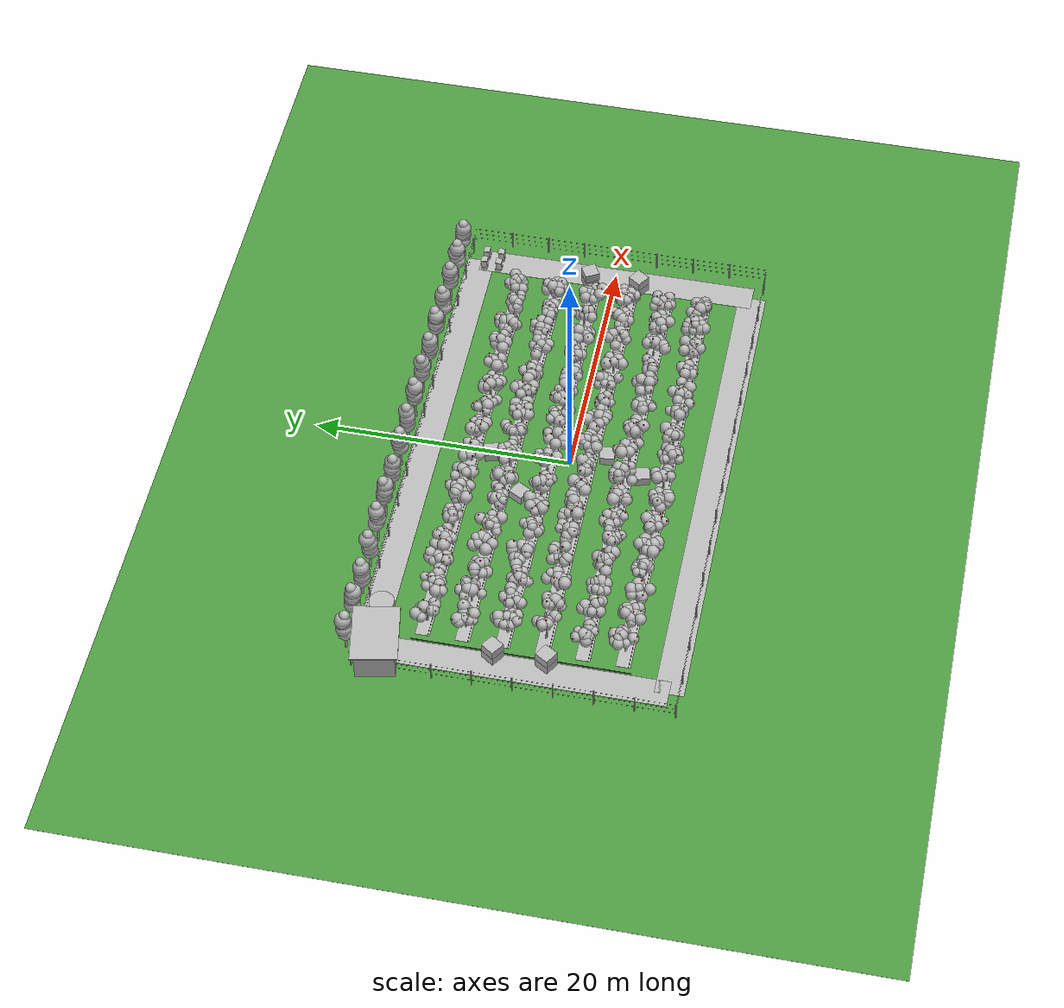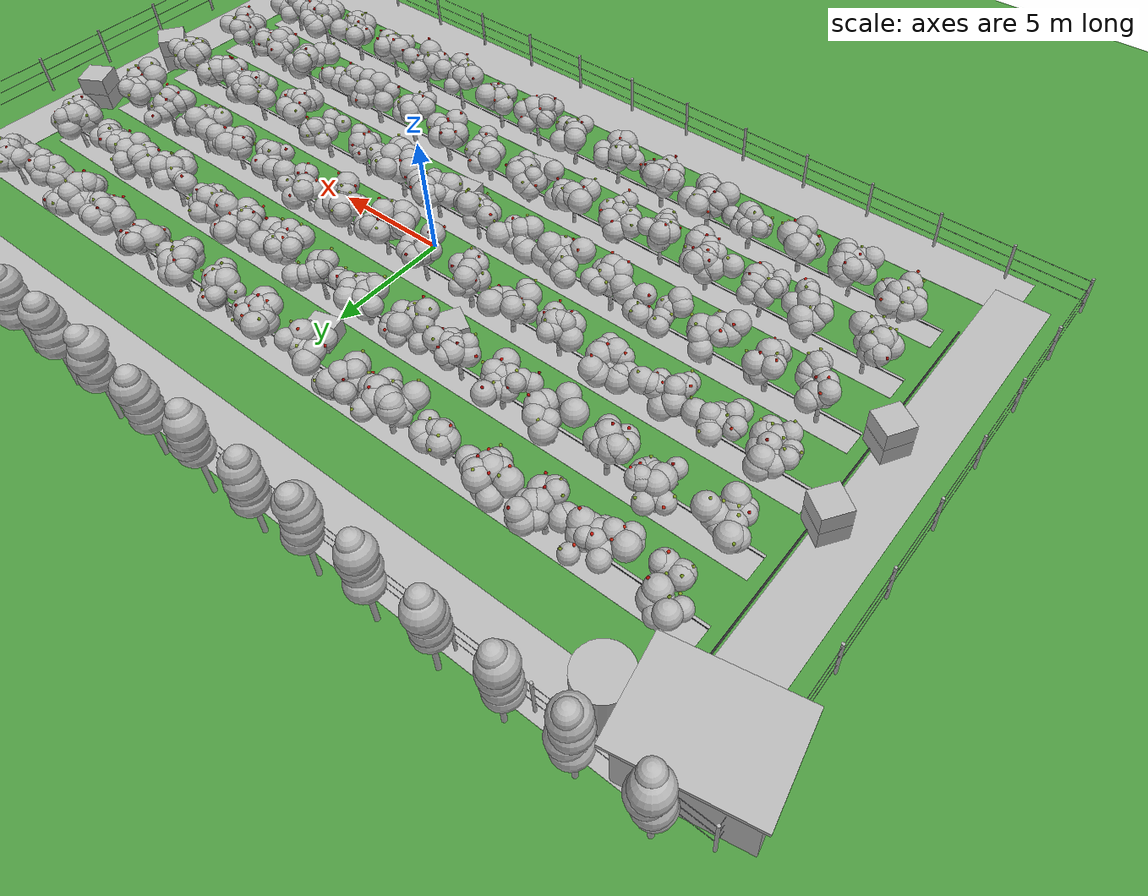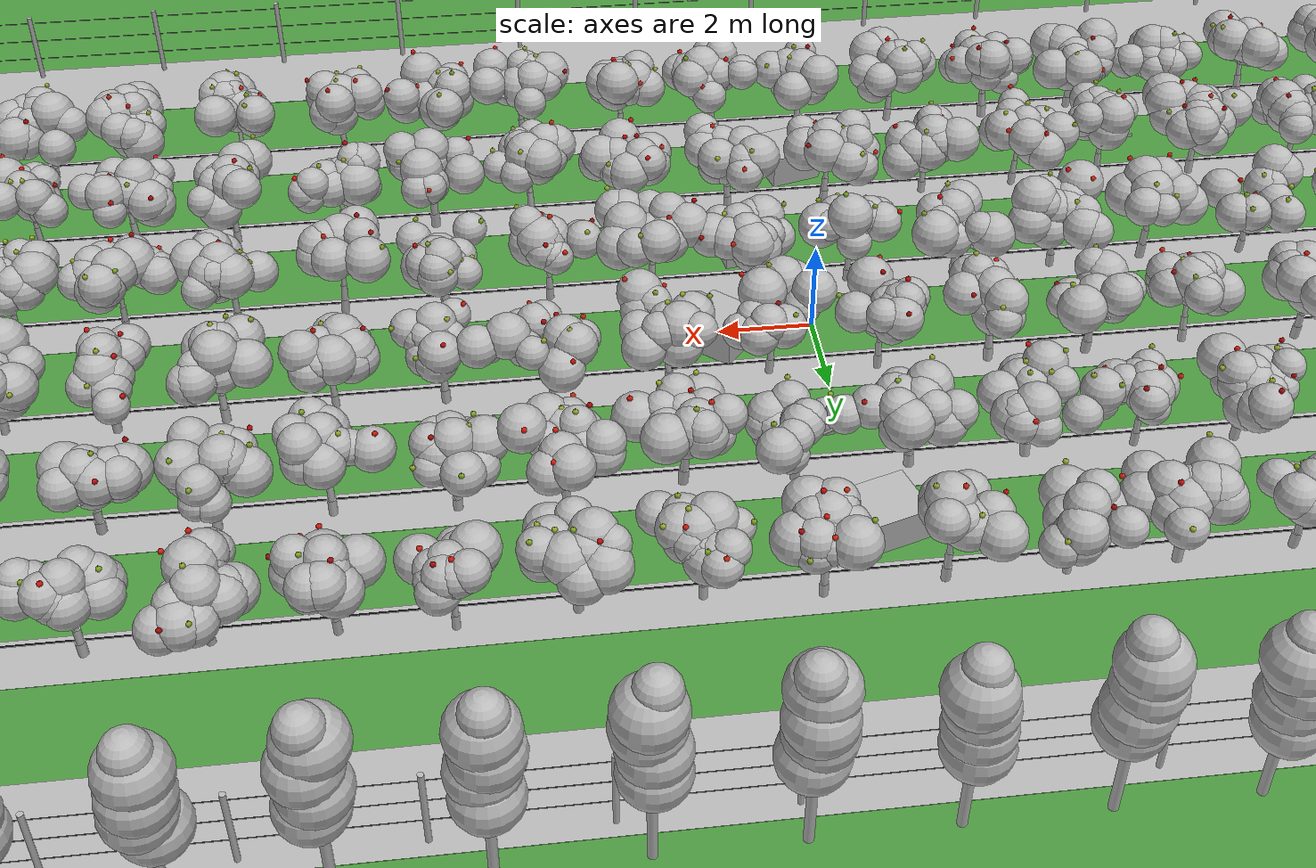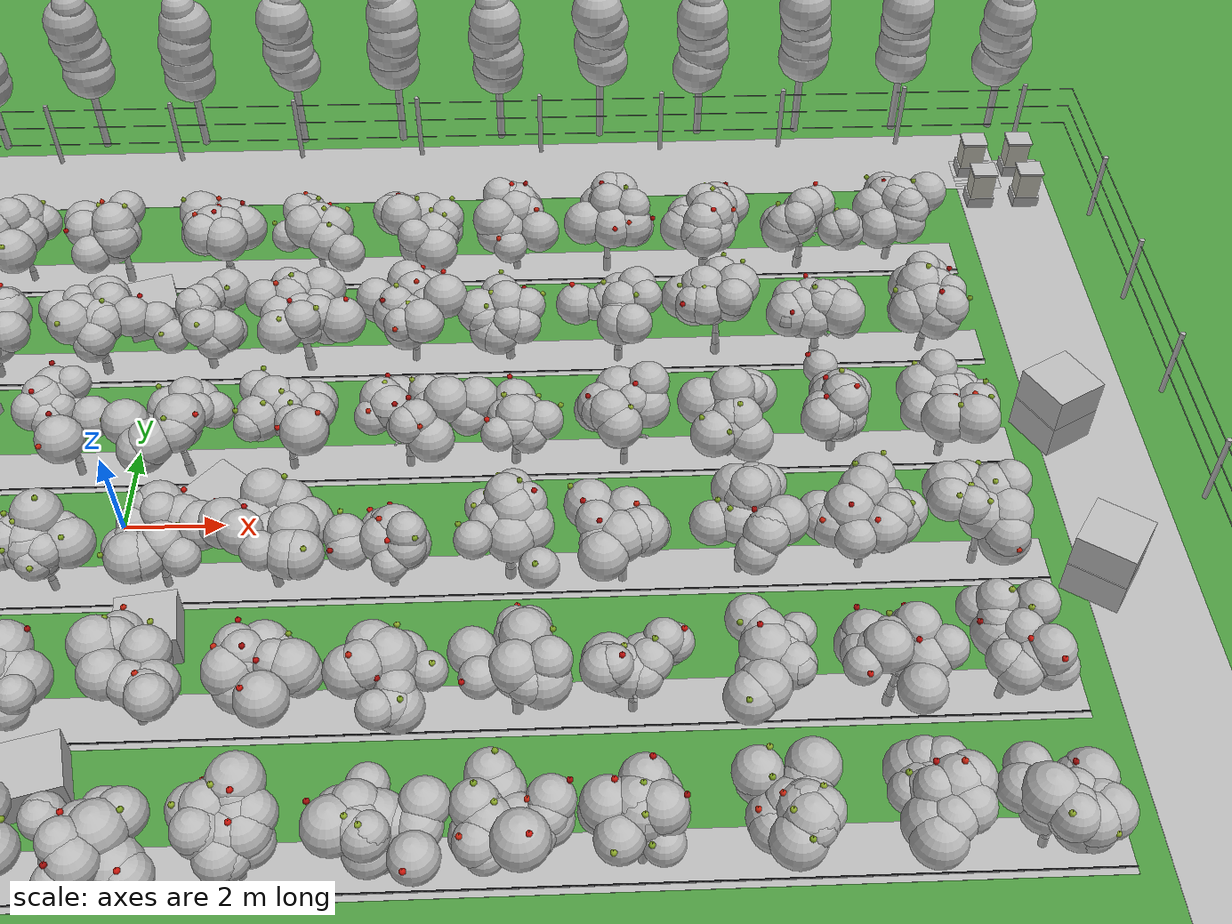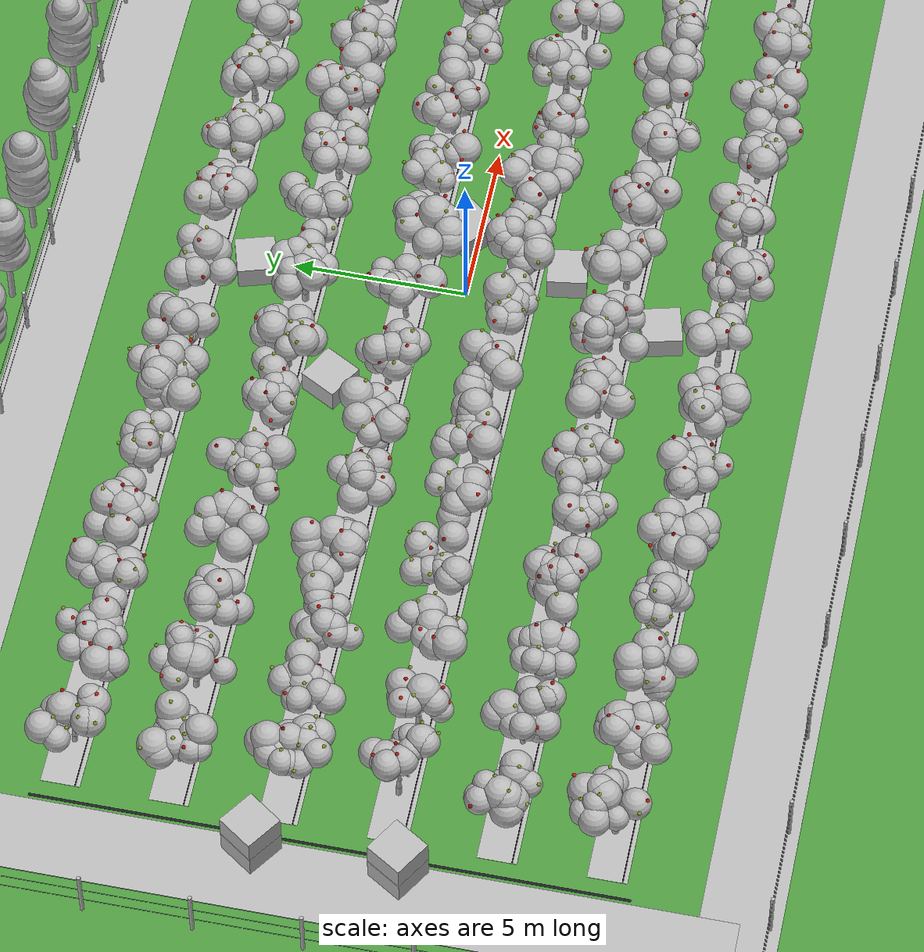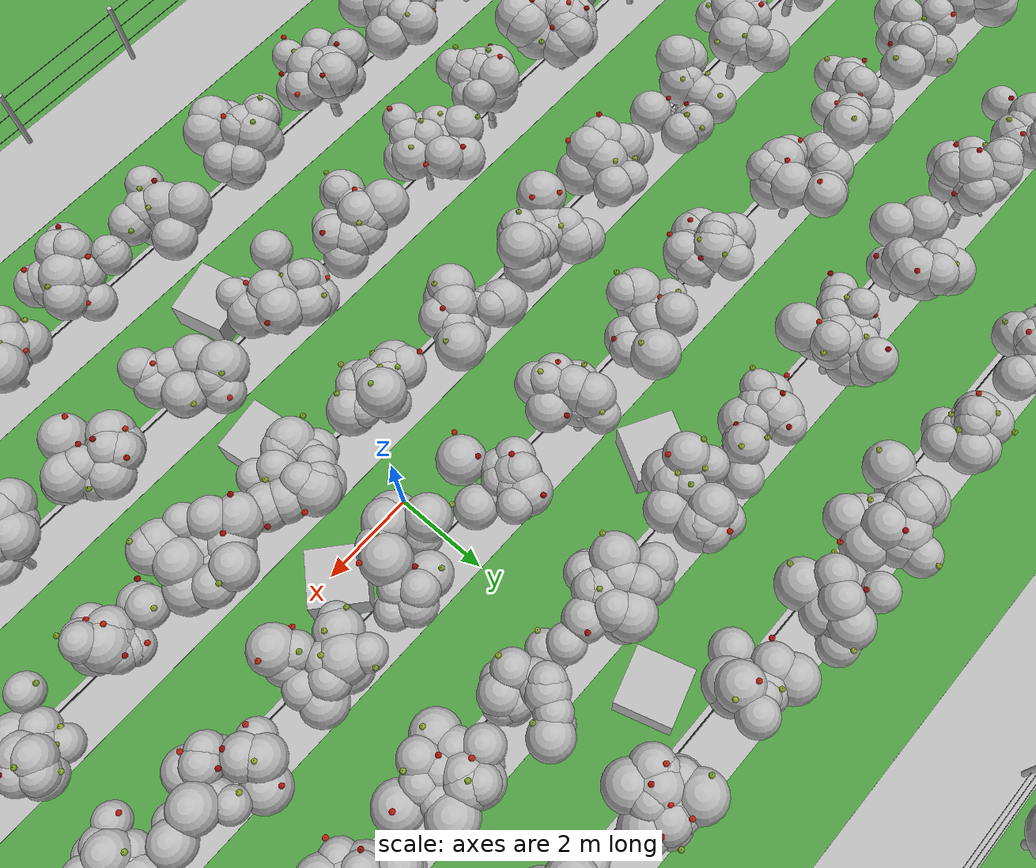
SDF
<?xml version="1.0"?>
<sdf version="1.6">
  <world name="default">

    <light name="sun" type="directional">
      <cast_shadows>true</cast_shadows>
      <pose>0 0 20 0 0 0</pose>
      <diffuse>0.88 0.86 0.80 1</diffuse>
      <specular>0.20 0.20 0.18 1</specular>
      <direction>-0.40 0.36 -0.84</direction>
      <attenuation>
        <range>80</range><constant>0.9</constant><linear>0.01</linear>
      </attenuation>
    </light>

    <light name="sky_fill" type="directional">
      <cast_shadows>false</cast_shadows>
      <pose>0 0 24 0 0 0</pose>
      <diffuse>0.40 0.42 0.48 1</diffuse>
      <specular>0.02 0.02 0.03 1</specular>
      <direction>0.50 -0.44 -0.75</direction>
      <attenuation>
        <range>80</range><constant>0.9</constant><linear>0.01</linear>
      </attenuation>
    </light>

    <scene>
      <ambient>0.70 0.70 0.72 1</ambient>
      <background>0.62 0.74 0.88 1</background>
      <shadows>true</shadows>
    </scene>

    <physics type="ode">
      <max_step_size>0.001</max_step_size>
      <real_time_update_rate>1000</real_time_update_rate>
    </physics>

  <model name="ground_cover">
    <static>true</static>
    <link name="grass">
      <pose>0 0 0.005 0 0 0</pose>
      <collision name="grass_c"><geometry><box><size>79.00 62.00 0.01</size></box></geometry></collision>
      <visual name="grass_v"><geometry><box><size>79.00 62.00 0.01</size></box></geometry><material><script><uri>model://orchard/materials/scripts</uri><uri>model://orchard/materials/textures</uri><name>Orchard/Grass</name></script></material></visual>
    </link>
  </model>
  <model name="headland_track">
    <static>true</static>
    <link name="track_n">
      <pose>0 11.200 0.013 0 0 0</pose>
      <visual name="track_n_v"><geometry><box><size>39.400 2.200 0.014</size></box></geometry><material><script><uri>model://orchard/materials/scripts</uri><uri>model://orchard/materials/textures</uri><name>Orchard/Track</name></script></material></visual>
    </link>
    <link name="track_s">
      <pose>0 -11.200 0.013 0 0 0</pose>
      <visual name="track_s_v"><geometry><box><size>39.400 2.200 0.014</size></box></geometry><material><script><uri>model://orchard/materials/scripts</uri><uri>model://orchard/materials/textures</uri><name>Orchard/Track</name></script></material></visual>
    </link>
    <link name="track_e">
      <pose>19.700 0 0.013 0 0 0</pose>
      <visual name="track_e_v"><geometry><box><size>2.200 22.400 0.014</size></box></geometry><material><script><uri>model://orchard/materials/scripts</uri><uri>model://orchard/materials/textures</uri><name>Orchard/Track</name></script></material></visual>
    </link>
    <link name="track_w">
      <pose>-19.700 0 0.013 0 0 0</pose>
      <visual name="track_w_v"><geometry><box><size>2.200 22.400 0.014</size></box></geometry><material><script><uri>model://orchard/materials/scripts</uri><uri>model://orchard/materials/textures</uri><name>Orchard/Track</name></script></material></visual>
    </link>
  </model>
  <model name="soil_0">
    <static>true</static>
    <link name="soil_0_l">
      <pose>0 -7.500 0.011 0 0 0</pose>
      <visual name="soil_0_l_v"><geometry><box><size>36.00 1.1 0.012</size></box></geometry><material><script><uri>model://orchard/materials/scripts</uri><uri>model://orchard/materials/textures</uri><name>Orchard/Strip</name></script></material></visual>
    </link>
  </model>
  <model name="soil_1">
    <static>true</static>
    <link name="soil_1_l">
      <pose>0 -4.500 0.011 0 0 0</pose>
      <visual name="soil_1_l_v"><geometry><box><size>36.00 1.1 0.012</size></box></geometry><material><script><uri>model://orchard/materials/scripts</uri><uri>model://orchard/materials/textures</uri><name>Orchard/Strip</name></script></material></visual>
    </link>
  </model>
  <model name="soil_2">
    <static>true</static>
    <link name="soil_2_l">
      <pose>0 -1.500 0.011 0 0 0</pose>
      <visual name="soil_2_l_v"><geometry><box><size>36.00 1.1 0.012</size></box></geometry><material><script><uri>model://orchard/materials/scripts</uri><uri>model://orchard/materials/textures</uri><name>Orchard/Strip</name></script></material></visual>
    </link>
  </model>
  <model name="soil_3">
    <static>true</static>
    <link name="soil_3_l">
      <pose>0 1.500 0.011 0 0 0</pose>
      <visual name="soil_3_l_v"><geometry><box><size>36.00 1.1 0.012</size></box></geometry><material><script><uri>model://orchard/materials/scripts</uri><uri>model://orchard/materials/textures</uri><name>Orchard/Strip</name></script></material></visual>
    </link>
  </model>
  <model name="soil_4">
    <static>true</static>
    <link name="soil_4_l">
      <pose>0 4.500 0.011 0 0 0</pose>
      <visual name="soil_4_l_v"><geometry><box><size>36.00 1.1 0.012</size></box></geometry><material><script><uri>model://orchard/materials/scripts</uri><uri>model://orchard/materials/textures</uri><name>Orchard/Strip</name></script></material></visual>
    </link>
  </model>
  <model name="soil_5">
    <static>true</static>
    <link name="soil_5_l">
      <pose>0 7.500 0.011 0 0 0</pose>
      <visual name="soil_5_l_v"><geometry><box><size>36.00 1.1 0.012</size></box></geometry><material><script><uri>model://orchard/materials/scripts</uri><uri>model://orchard/materials/textures</uri><name>Orchard/Strip</name></script></material></visual>
    </link>
  </model>
  <model name="tree_r0_t0">
    <static>true</static>
    <link name="tree_r0_t0_trunk0">
      <pose>-16.4653 -7.4328 0.1814 -0.0507 0.0288 0</pose>
      <collision name="tree_r0_t0_trunk0_c"><geometry><cylinder><radius>0.0986</radius><length>0.3846</length></cylinder></geometry></collision>
      <visual name="tree_r0_t0_trunk0_v"><geometry><cylinder><radius>0.0986</radius><length>0.3846</length></cylinder></geometry><material><script><uri>model://orchard/materials/scripts</uri><uri>model://orchard/materials/textures</uri><name>Orchard/Bark</name></script></material></visual>
    </link>
    <link name="tree_r0_t0_trunk1">
      <pose>-16.4548 -7.4144 0.5443 -0.0507 0.0288 0</pose>
      <visual name="tree_r0_t0_trunk1_v"><geometry><cylinder><radius>0.0769</radius><length>0.3846</length></cylinder></geometry><material><script><uri>model://orchard/materials/scripts</uri><uri>model://orchard/materials/textures</uri><name>Orchard/Bark</name></script></material></visual>
    </link>
    <link name="tree_r0_t0_trunk2">
      <pose>-16.4444 -7.3960 0.9071 -0.0507 0.0288 0</pose>
      <visual name="tree_r0_t0_trunk2_v"><geometry><cylinder><radius>0.0552</radius><length>0.3846</length></cylinder></geometry><material><script><uri>model://orchard/materials/scripts</uri><uri>model://orchard/materials/textures</uri><name>Orchard/Bark</name></script></material></visual>
    </link>
    <link name="tree_r0_t0_br0">
      <pose>-16.2346 -7.3371 1.3193 0.0000 0.7395 0.2382</pose>
      <visual name="tree_r0_t0_br0_v"><geometry><cylinder><radius>0.0227</radius><length>0.6247</length></cylinder></geometry><material><script><uri>model://orchard/materials/scripts</uri><uri>model://orchard/materials/textures</uri><name>Orchard/Bark</name></script></material></visual>
    </link>
    <link name="tree_r0_t0_br1">
      <pose>-16.2652 -7.1058 1.3231 0.0000 0.9537 1.0164</pose>
      <visual name="tree_r0_t0_br1_v"><geometry><cylinder><radius>0.0273</radius><length>0.8105</length></cylinder></geometry><material><script><uri>model://orchard/materials/scripts</uri><uri>model://orchard/materials/textures</uri><name>Orchard/Bark</name></script></material></visual>
    </link>
    <link name="tree_r0_t0_br2">
      <pose>-16.6410 -7.1288 1.2903 0.0000 1.0187 2.2347</pose>
      <visual name="tree_r0_t0_br2_v"><geometry><cylinder><radius>0.0277</radius><length>0.7694</length></cylinder></geometry><material><script><uri>model://orchard/materials/scripts</uri><uri>model://orchard/materials/textures</uri><name>Orchard/Bark</name></script></material></visual>
    </link>
    <link name="tree_r0_t0_br3">
      <pose>-16.6344 -7.4707 1.3455 0.0000 0.6910 3.5474</pose>
      <visual name="tree_r0_t0_br3_v"><geometry><cylinder><radius>0.0327</radius><length>0.6668</length></cylinder></geometry><material><script><uri>model://orchard/materials/scripts</uri><uri>model://orchard/materials/textures</uri><name>Orchard/Bark</name></script></material></visual>
    </link>
    <link name="tree_r0_t0_br4">
      <pose>-16.4355 -7.6374 1.3209 0.0000 0.8233 4.7269</pose>
      <visual name="tree_r0_t0_br4_v"><geometry><cylinder><radius>0.0239</radius><length>0.6835</length></cylinder></geometry><material><script><uri>model://orchard/materials/scripts</uri><uri>model://orchard/materials/textures</uri><name>Orchard/Bark</name></script></material></visual>
    </link>
    <link name="tree_r0_t0_fol0">
      <pose>-15.8335 -7.0119 1.5308 0 0 0</pose>
      <visual name="tree_r0_t0_fol0_v"><geometry><sphere><radius>0.3902</radius></sphere></geometry><material><script><uri>model://orchard/materials/scripts</uri><uri>model://orchard/materials/textures</uri><name>Orchard/Foliage1</name></script></material></visual>
    </link>
    <link name="tree_r0_t0_fol1">
      <pose>-16.2694 -6.5624 1.5442 0 0 0</pose>
      <visual name="tree_r0_t0_fol1_v"><geometry><sphere><radius>0.4944</radius></sphere></geometry><material><script><uri>model://orchard/materials/scripts</uri><uri>model://orchard/materials/textures</uri><name>Orchard/Foliage3</name></script></material></visual>
    </link>
    <link name="tree_r0_t0_fol2">
      <pose>-16.8904 -6.6268 1.5082 0 0 0</pose>
      <visual name="tree_r0_t0_fol2_v"><geometry><sphere><radius>0.3931</radius></sphere></geometry><material><script><uri>model://orchard/materials/scripts</uri><uri>model://orchard/materials/textures</uri><name>Orchard/Foliage0</name></script></material></visual>
    </link>
    <link name="tree_r0_t0_fol3">
      <pose>-17.0858 -6.9519 1.5268 0 0 0</pose>
      <visual name="tree_r0_t0_fol3_v"><geometry><sphere><radius>0.4514</radius></sphere></geometry><material><script><uri>model://orchard/materials/scripts</uri><uri>model://orchard/materials/textures</uri><name>Orchard/Foliage1</name></script></material></visual>
    </link>
    <link name="tree_r0_t0_fol4">
      <pose>-16.3393 -6.5587 1.4676 0 0 0</pose>
      <visual name="tree_r0_t0_fol4_v"><geometry><sphere><radius>0.4600</radius></sphere></geometry><material><script><uri>model://orchard/materials/scripts</uri><uri>model://orchard/materials/textures</uri><name>Orchard/Foliage3</name></script></material></visual>
    </link>
    <link name="tree_r0_t0_fol5">
      <pose>-16.9046 -7.5106 1.5064 0 0 0</pose>
      <visual name="tree_r0_t0_fol5_v"><geometry><sphere><radius>0.3475</radius></sphere></geometry><material><script><uri>model://orchard/materials/scripts</uri><uri>model://orchard/materials/textures</uri><name>Orchard/Foliage1</name></script></material></visual>
    </link>
    <link name="tree_r0_t0_fol6">
      <pose>-16.3045 -6.9669 1.8181 0 0 0</pose>
      <visual name="tree_r0_t0_fol6_v"><geometry><sphere><radius>0.4140</radius></sphere></geometry><material><script><uri>model://orchard/materials/scripts</uri><uri>model://orchard/materials/textures</uri><name>Orchard/Foliage2</name></script></material></visual>
    </link>
    <link name="tree_r0_t0_fol7">
      <pose>-16.4407 -7.1085 1.7764 0 0 0</pose>
      <visual name="tree_r0_t0_fol7_v"><geometry><sphere><radius>0.4650</radius></sphere></geometry><material><script><uri>model://orchard/materials/scripts</uri><uri>model://orchard/materials/textures</uri><name>Orchard/Foliage2</name></script></material></visual>
    </link>
    <link name="tree_r0_t0_fol8">
      <pose>-15.8855 -7.2571 1.5172 0 0 0</pose>
      <visual name="tree_r0_t0_fol8_v"><geometry><sphere><radius>0.3945</radius></sphere></geometry><material><script><uri>model://orchard/materials/scripts</uri><uri>model://orchard/materials/textures</uri><name>Orchard/Foliage2</name></script></material></visual>
    </link>
    <link name="tree_r0_t0_fol9">
      <pose>-16.7368 -6.9176 1.7532 0 0 0</pose>
      <visual name="tree_r0_t0_fol9_v"><geometry><sphere><radius>0.3900</radius></sphere></geometry><material><script><uri>model://orchard/materials/scripts</uri><uri>model://orchard/materials/textures</uri><name>Orchard/Foliage2</name></script></material></visual>
    </link>
    <link name="tree_r0_t0_fol10">
      <pose>-15.9590 -7.1636 1.5862 0 0 0</pose>
      <visual name="tree_r0_t0_fol10_v"><geometry><sphere><radius>0.4174</radius></sphere></geometry><material><script><uri>model://orchard/materials/scripts</uri><uri>model://orchard/materials/textures</uri><name>Orchard/Foliage0</name></script></material></visual>
    </link>
    <link name="tree_r0_t0_fol11">
      <pose>-16.4131 -7.9407 1.5576 0 0 0</pose>
      <visual name="tree_r0_t0_fol11_v"><geometry><sphere><radius>0.4350</radius></sphere></geometry><material><script><uri>model://orchard/materials/scripts</uri><uri>model://orchard/materials/textures</uri><name>Orchard/Foliage2</name></script></material></visual>
    </link>
    <link name="tree_r0_t0_ap0">
      <pose>-15.6552 -7.1002 1.9350 0 0 0</pose>
      <visual name="tree_r0_t0_ap0_v"><geometry><sphere><radius>0.0550</radius></sphere></geometry><material><ambient>0.192 0.248 0.052 1.00</ambient><diffuse>0.480 0.620 0.130 1.00</diffuse><specular>0.45 0.35 0.32 1</specular></material></visual>
    </link>
    <link name="tree_r0_t0_st0">
      <pose>-15.6552 -7.1002 1.9872 0 0 0</pose>
      <visual name="tree_r0_t0_st0_v"><geometry><cylinder><radius>0.0060</radius><length>0.0500</length></cylinder></geometry><material><ambient>0.128 0.096 0.040 1.00</ambient><diffuse>0.320 0.240 0.100 1.00</diffuse></material></visual>
    </link>
    <link name="tree_r0_t0_ap1">
      <pose>-16.8080 -8.1088 1.7825 0 0 0</pose>
      <visual name="tree_r0_t0_ap1_v"><geometry><sphere><radius>0.0550</radius></sphere></geometry><material><ambient>0.220 0.264 0.064 1.00</ambient><diffuse>0.550 0.660 0.160 1.00</diffuse><specular>0.45 0.35 0.32 1</specular></material></visual>
    </link>
    <link name="tree_r0_t0_st1">
      <pose>-16.8080 -8.1088 1.8348 0 0 0</pose>
      <visual name="tree_r0_t0_st1_v"><geometry><cylinder><radius>0.0060</radius><length>0.0500</length></cylinder></geometry><material><ambient>0.128 0.096 0.040 1.00</ambient><diffuse>0.320 0.240 0.100 1.00</diffuse></material></visual>
    </link>
    <link name="tree_r0_t0_ap2">
      <pose>-16.0703 -6.2064 1.9041 0 0 0</pose>
      <visual name="tree_r0_t0_ap2_v"><geometry><sphere><radius>0.0550</radius></sphere></geometry><material><ambient>0.312 0.056 0.024 1.00</ambient><diffuse>0.780 0.140 0.060 1.00</diffuse><specular>0.45 0.35 0.32 1</specular></material></visual>
    </link>
    <link name="tree_r0_t0_st2">
      <pose>-16.0703 -6.2064 1.9563 0 0 0</pose>
      <visual name="tree_r0_t0_st2_v"><geometry><cylinder><radius>0.0060</radius><length>0.0500</length></cylinder></geometry><material><ambient>0.128 0.096 0.040 1.00</ambient><diffuse>0.320 0.240 0.100 1.00</diffuse></material></visual>
    </link>
    <link name="tree_r0_t0_ap3">
      <pose>-16.6729 -7.0029 2.1796 0 0 0</pose>
      <visual name="tree_r0_t0_ap3_v"><geometry><sphere><radius>0.0550</radius></sphere></geometry><material><ambient>0.220 0.264 0.064 1.00</ambient><diffuse>0.550 0.660 0.160 1.00</diffuse><specular>0.45 0.35 0.32 1</specular></material></visual>
    </link>
    <link name="tree_r0_t0_st3">
      <pose>-16.6729 -7.0029 2.2319 0 0 0</pose>
      <visual name="tree_r0_t0_st3_v"><geometry><cylinder><radius>0.0060</radius><length>0.0500</length></cylinder></geometry><material><ambient>0.128 0.096 0.040 1.00</ambient><diffuse>0.320 0.240 0.100 1.00</diffuse></material></visual>
    </link>
    <link name="tree_r0_t0_ap4">
      <pose>-16.4552 -8.2653 1.9148 0 0 0</pose>
      <visual name="tree_r0_t0_ap4_v"><geometry><sphere><radius>0.0550</radius></sphere></geometry><material><ambient>0.312 0.056 0.024 1.00</ambient><diffuse>0.780 0.140 0.060 1.00</diffuse><specular>0.45 0.35 0.32 1</specular></material></visual>
    </link>
    <link name="tree_r0_t0_st4">
      <pose>-16.4552 -8.2653 1.9671 0 0 0</pose>
      <visual name="tree_r0_t0_st4_v"><geometry><cylinder><radius>0.0060</radius><length>0.0500</length></cylinder></geometry><material><ambient>0.128 0.096 0.040 1.00</ambient><diffuse>0.320 0.240 0.100 1.00</diffuse></material></visual>
    </link>
    <link name="tree_r0_t0_ap5">
      <pose>-16.7598 -6.5152 1.9160 0 0 0</pose>
      <visual name="tree_r0_t0_ap5_v"><geometry><sphere><radius>0.0550</radius></sphere></geometry><material><ambient>0.192 0.248 0.052 1.00</ambient><diffuse>0.480 0.620 0.130 1.00</diffuse><specular>0.45 0.35 0.32 1</specular></material></visual>
    </link>
    <link name="tree_r0_t0_st5">
      <pose>-16.7598 -6.5152 1.9683 0 0 0</pose>
      <visual name="tree_r0_t0_st5_v"><geometry><cylinder><radius>0.0060</radius><length>0.0500</length></cylinder></geometry><material><ambient>0.128 0.096 0.040 1.00</ambient><diffuse>0.320 0.240 0.100 1.00</diffuse></material></visual>
    </link>
  </model>
  <model name="tree_r0_t1">
    <static>true</static>
    <link name="tree_r0_t1_trunk0">
      <pose>-14.2739 -7.4948 0.1586 -0.0338 -0.0273 0</pose>
      <collision name="tree_r0_t1_trunk0_c"><geometry><cylinder><radius>0.0772</radius><length>0.3362</length></cylinder></geometry></collision>
      <visual name="tree_r0_t1_trunk0_v"><geometry><cylinder><radius>0.0772</radius><length>0.3362</length></cylinder></geometry><material><script><uri>model://orchard/materials/scripts</uri><uri>model://orchard/materials/textures</uri><name>Orchard/Bark</name></script></material></visual>
    </link>
    <link name="tree_r0_t1_trunk1">
      <pose>-14.2825 -7.4841 0.4758 -0.0338 -0.0273 0</pose>
      <visual name="tree_r0_t1_trunk1_v"><geometry><cylinder><radius>0.0602</radius><length>0.3362</length></cylinder></geometry><material><script><uri>model://orchard/materials/scripts</uri><uri>model://orchard/materials/textures</uri><name>Orchard/Bark</name></script></material></visual>
    </link>
    <link name="tree_r0_t1_trunk2">
      <pose>-14.2912 -7.4733 0.7930 -0.0338 -0.0273 0</pose>
      <visual name="tree_r0_t1_trunk2_v"><geometry><cylinder><radius>0.0432</radius><length>0.3362</length></cylinder></geometry><material><script><uri>model://orchard/materials/scripts</uri><uri>model://orchard/materials/textures</uri><name>Orchard/Bark</name></script></material></visual>
    </link>
    <link name="tree_r0_t1_br0">
      <pose>-14.0346 -7.4934 1.2420 0.0000 0.7342 -0.0971</pose>
      <visual name="tree_r0_t1_br0_v"><geometry><cylinder><radius>0.0317</radius><length>0.7825</length></cylinder></geometry><material><script><uri>model://orchard/materials/scripts</uri><uri>model://orchard/materials/textures</uri><name>Orchard/Bark</name></script></material></visual>
    </link>
    <link name="tree_r0_t1_br1">
      <pose>-14.1768 -7.2778 1.1931 0.0000 0.7482 1.0124</pose>
      <visual name="tree_r0_t1_br1_v"><geometry><cylinder><radius>0.0319</radius><length>0.6590</length></cylinder></geometry><material><script><uri>model://orchard/materials/scripts</uri><uri>model://orchard/materials/textures</uri><name>Orchard/Bark</name></script></material></visual>
    </link>
    <link name="tree_r0_t1_br2">
      <pose>-14.3171 -7.1645 1.1963 0.0000 0.8934 1.6418</pose>
      <visual name="tree_r0_t1_br2_v"><geometry><cylinder><radius>0.0317</radius><length>0.7809</length></cylinder></geometry><material><script><uri>model://orchard/materials/scripts</uri><uri>model://orchard/materials/textures</uri><name>Orchard/Bark</name></script></material></visual>
    </link>
    <link name="tree_r0_t1_br3">
      <pose>-14.4824 -7.3420 1.2481 0.0000 0.6497 2.5485</pose>
      <visual name="tree_r0_t1_br3_v"><geometry><cylinder><radius>0.0301</radius><length>0.7449</length></cylinder></geometry><material><script><uri>model://orchard/materials/scripts</uri><uri>model://orchard/materials/textures</uri><name>Orchard/Bark</name></script></material></visual>
    </link>
    <link name="tree_r0_t1_br4">
      <pose>-14.5313 -7.4933 1.1553 0.0000 0.8609 3.2485</pose>
      <visual name="tree_r0_t1_br4_v"><geometry><cylinder><radius>0.0314</radius><length>0.6252</length></cylinder></geometry><material><script><uri>model://orchard/materials/scripts</uri><uri>model://orchard/materials/textures</uri><name>Orchard/Bark</name></script></material></visual>
    </link>
    <link name="tree_r0_t1_br5">
      <pose>-14.3562 -7.7051 1.2318 0.0000 0.7180 4.4620</pose>
      <visual name="tree_r0_t1_br5_v"><geometry><cylinder><radius>0.0332</radius><length>0.7442</length></cylinder></geometry><material><script><uri>model://orchard/materials/scripts</uri><uri>model://orchard/materials/textures</uri><name>Orchard/Bark</name></script></material></visual>
    </link>
    <link name="tree_r0_t1_br6">
      <pose>-14.1456 -7.7035 1.2176 0.0000 0.8094 5.2791</pose>
      <visual name="tree_r0_t1_br6_v"><geometry><cylinder><radius>0.0336</radius><length>0.7713</length></cylinder></geometry><material><script><uri>model://orchard/materials/scripts</uri><uri>model://orchard/materials/textures</uri><name>Orchard/Bark</name></script></material></visual>
    </link>
    <link name="tree_r0_t1_fol0">
      <pose>-13.8903 -7.6724 1.8046 0 0 0</pose>
      <visual name="tree_r0_t1_fol0_v"><geometry><sphere><radius>0.4229</radius></sphere></geometry><material><script><uri>model://orchard/materials/scripts</uri><uri>model://orchard/materials/textures</uri><name>Orchard/Foliage1</name></script></material></visual>
    </link>
    <link name="tree_r0_t1_fol1">
      <pose>-14.0938 -6.8737 1.6452 0 0 0</pose>
      <visual name="tree_r0_t1_fol1_v"><geometry><sphere><radius>0.4551</radius></sphere></geometry><material><script><uri>model://orchard/materials/scripts</uri><uri>model://orchard/materials/textures</uri><name>Orchard/Foliage3</name></script></material></visual>
    </link>
    <link name="tree_r0_t1_fol2">
      <pose>-13.7515 -7.9298 1.7957 0 0 0</pose>
      <visual name="tree_r0_t1_fol2_v"><geometry><sphere><radius>0.3884</radius></sphere></geometry><material><script><uri>model://orchard/materials/scripts</uri><uri>model://orchard/materials/textures</uri><name>Orchard/Foliage2</name></script></material></visual>
    </link>
    <link name="tree_r0_t1_fol3">
      <pose>-14.2143 -7.4537 1.4765 0 0 0</pose>
      <visual name="tree_r0_t1_fol3_v"><geometry><sphere><radius>0.4440</radius></sphere></geometry><material><script><uri>model://orchard/materials/scripts</uri><uri>model://orchard/materials/textures</uri><name>Orchard/Foliage1</name></script></material></visual>
    </link>
    <link name="tree_r0_t1_fol4">
      <pose>-14.1389 -7.1322 1.7601 0 0 0</pose>
      <visual name="tree_r0_t1_fol4_v"><geometry><sphere><radius>0.4968</radius></sphere></geometry><material><script><uri>model://orchard/materials/scripts</uri><uri>model://orchard/materials/textures</uri><name>Orchard/Foliage1</name></script></material></visual>
    </link>
    <link name="tree_r0_t1_fol5">
      <pose>-14.2759 -6.8256 1.5469 0 0 0</pose>
      <visual name="tree_r0_t1_fol5_v"><geometry><sphere><radius>0.4277</radius></sphere></geometry><material><script><uri>model://orchard/materials/scripts</uri><uri>model://orchard/materials/textures</uri><name>Orchard/Foliage3</name></script></material></visual>
    </link>
    <link name="tree_r0_t1_fol6">
      <pose>-14.5782 -7.4558 1.5346 0 0 0</pose>
      <visual name="tree_r0_t1_fol6_v"><geometry><sphere><radius>0.4549</radius></sphere></geometry><material><script><uri>model://orchard/materials/scripts</uri><uri>model://orchard/materials/textures</uri><name>Orchard/Foliage2</name></script></material></visual>
    </link>
    <link name="tree_r0_t1_fol7">
      <pose>-14.4160 -7.0168 1.8259 0 0 0</pose>
      <visual name="tree_r0_t1_fol7_v"><geometry><sphere><radius>0.4502</radius></sphere></geometry><material><script><uri>model://orchard/materials/scripts</uri><uri>model://orchard/materials/textures</uri><name>Orchard/Foliage2</name></script></material></visual>
    </link>
    <link name="tree_r0_t1_fol8">
      <pose>-14.4433 -7.5159 1.4007 0 0 0</pose>
      <visual name="tree_r0_t1_fol8_v"><geometry><sphere><radius>0.4220</radius></sphere></geometry><material><script><uri>model://orchard/materials/scripts</uri><uri>model://orchard/materials/textures</uri><name>Orchard/Foliage2</name></script></material></visual>
    </link>
    <link name="tree_r0_t1_fol9">
      <pose>-14.2053 -7.6643 1.6699 0 0 0</pose>
      <visual name="tree_r0_t1_fol9_v"><geometry><sphere><radius>0.4428</radius></sphere></geometry><material><script><uri>model://orchard/materials/scripts</uri><uri>model://orchard/materials/textures</uri><name>Orchard/Foliage2</name></script></material></visual>
    </link>
    <link name="tree_r0_t1_fol10">
      <pose>-14.0043 -7.0520 1.7557 0 0 0</pose>
      <visual name="tree_r0_t1_fol10_v"><geometry><sphere><radius>0.4949</radius></sphere></geometry><material><script><uri>model://orchard/materials/scripts</uri><uri>model://orchard/materials/textures</uri><name>Orchard/Foliage0</name></script></material></visual>
    </link>
    <link name="tree_r0_t1_fol11">
      <pose>-14.6963 -8.1619 1.6610 0 0 0</pose>
      <visual name="tree_r0_t1_fol11_v"><geometry><sphere><radius>0.4384</radius></sphere></geometry><material><script><uri>model://orchard/materials/scripts</uri><uri>model://orchard/materials/textures</uri><name>Orchard/Foliage1</name></script></material></visual>
    </link>
    <link name="tree_r0_t1_fol12">
      <pose>-14.8365 -7.5568 1.3586 0 0 0</pose>
      <visual name="tree_r0_t1_fol12_v"><geometry><sphere><radius>0.3866</radius></sphere></geometry><material><script><uri>model://orchard/materials/scripts</uri><uri>model://orchard/materials/textures</uri><name>Orchard/Foliage3</name></script></material></visual>
    </link>
    <link name="tree_r0_t1_fol13">
      <pose>-13.7641 -7.8854 1.4980 0 0 0</pose>
      <visual name="tree_r0_t1_fol13_v"><geometry><sphere><radius>0.4970</radius></sphere></geometry><material><script><uri>model://orchard/materials/scripts</uri><uri>model://orchard/materials/textures</uri><name>Orchard/Foliage3</name></script></material></visual>
    </link>
    <link name="tree_r0_t1_fol14">
      <pose>-13.8750 -7.2476 1.6488 0 0 0</pose>
      <visual name="tree_r0_t1_fol14_v"><geometry><sphere><radius>0.3858</radius></sphere></geometry><material><script><uri>model://orchard/materials/scripts</uri><uri>model://orchard/materials/textures</uri><name>Orchard/Foliage3</name></script></material></visual>
    </link>
    <link name="tree_r0_t1_fol15">
      <pose>-14.3487 -7.9739 1.5410 0 0 0</pose>
      <visual name="tree_r0_t1_fol15_v"><geometry><sphere><radius>0.4651</radius></sphere></geometry><material><script><uri>model://orchard/materials/scripts</uri><uri>model://orchard/materials/textures</uri><name>Orchard/Foliage3</name></script></material></visual>
    </link>
    <link name="tree_r0_t1_fol16">
      <pose>-14.7332 -7.6622 1.4677 0 0 0</pose>
      <visual name="tree_r0_t1_fol16_v"><geometry><sphere><radius>0.3459</radius></sphere></geometry><material><script><uri>model://orchard/materials/scripts</uri><uri>model://orchard/materials/textures</uri><name>Orchard/Foliage3</name></script></material></visual>
    </link>
    <link name="tree_r0_t1_fol17">
      <pose>-13.9340 -7.2077 1.5512 0 0 0</pose>
      <visual name="tree_r0_t1_fol17_v"><geometry><sphere><radius>0.4988</radius></sphere></geometry><material><script><uri>model://orchard/materials/scripts</uri><uri>model://orchard/materials/textures</uri><name>Orchard/Foliage0</name></script></material></visual>
    </link>
    <link name="tree_r0_t1_ap0">
      <pose>-14.2474 -6.8031 2.1824 0 0 0</pose>
      <visual name="tree_r0_t1_ap0_v"><geometry><sphere><radius>0.0550</radius></sphere></geometry><material><ambient>0.248 0.016 0.012 1.00</ambient><diffuse>0.620 0.040 0.030 1.00</diffuse><specular>0.45 0.35 0.32 1</specular></material></visual>
    </link>
    <link name="tree_r0_t1_st0">
      <pose>-14.2474 -6.8031 2.2346 0 0 0</pose>
      <visual name="tree_r0_t1_st0_v"><geometry><cylinder><radius>0.0060</radius><length>0.0500</length></cylinder></geometry><material><ambient>0.128 0.096 0.040 1.00</ambient><diffuse>0.320 0.240 0.100 1.00</diffuse></material></visual>
    </link>
    <link name="tree_r0_t1_ap1">
      <pose>-14.2283 -8.1219 2.0190 0 0 0</pose>
      <visual name="tree_r0_t1_ap1_v"><geometry><sphere><radius>0.0550</radius></sphere></geometry><material><ambient>0.192 0.248 0.052 1.00</ambient><diffuse>0.480 0.620 0.130 1.00</diffuse><specular>0.45 0.35 0.32 1</specular></material></visual>
    </link>
    <link name="tree_r0_t1_st1">
      <pose>-14.2283 -8.1219 2.0712 0 0 0</pose>
      <visual name="tree_r0_t1_st1_v"><geometry><cylinder><radius>0.0060</radius><length>0.0500</length></cylinder></geometry><material><ambient>0.128 0.096 0.040 1.00</ambient><diffuse>0.320 0.240 0.100 1.00</diffuse></material></visual>
    </link>
    <link name="tree_r0_t1_ap2">
      <pose>-14.4198 -7.6165 2.1105 0 0 0</pose>
      <visual name="tree_r0_t1_ap2_v"><geometry><sphere><radius>0.0550</radius></sphere></geometry><material><ambient>0.288 0.020 0.016 1.00</ambient><diffuse>0.720 0.050 0.040 1.00</diffuse><specular>0.45 0.35 0.32 1</specular></material></visual>
    </link>
    <link name="tree_r0_t1_st2">
      <pose>-14.4198 -7.6165 2.1627 0 0 0</pose>
      <visual name="tree_r0_t1_st2_v"><geometry><cylinder><radius>0.0060</radius><length>0.0500</length></cylinder></geometry><material><ambient>0.128 0.096 0.040 1.00</ambient><diffuse>0.320 0.240 0.100 1.00</diffuse></material></visual>
    </link>
  </model>
  <model name="tree_r0_t2">
    <static>true</static>
    <link name="tree_r0_t2_trunk0">
      <pose>-12.0456 -7.5228 0.1560 0.0429 0.0493 0</pose>
      <collision name="tree_r0_t2_trunk0_c"><geometry><cylinder><radius>0.0945</radius><length>0.3307</length></cylinder></geometry></collision>
      <visual name="tree_r0_t2_trunk0_v"><geometry><cylinder><radius>0.0945</radius><length>0.3307</length></cylinder></geometry><material><script><uri>model://orchard/materials/scripts</uri><uri>model://orchard/materials/textures</uri><name>Orchard/Bark</name></script></material></visual>
    </link>
    <link name="tree_r0_t2_trunk1">
      <pose>-12.0302 -7.5362 0.4680 0.0429 0.0493 0</pose>
      <visual name="tree_r0_t2_trunk1_v"><geometry><cylinder><radius>0.0737</radius><length>0.3307</length></cylinder></geometry><material><script><uri>model://orchard/materials/scripts</uri><uri>model://orchard/materials/textures</uri><name>Orchard/Bark</name></script></material></visual>
    </link>
    <link name="tree_r0_t2_trunk2">
      <pose>-12.0149 -7.5496 0.7799 0.0429 0.0493 0</pose>
      <visual name="tree_r0_t2_trunk2_v"><geometry><cylinder><radius>0.0529</radius><length>0.3307</length></cylinder></geometry><material><script><uri>model://orchard/materials/scripts</uri><uri>model://orchard/materials/textures</uri><name>Orchard/Bark</name></script></material></visual>
    </link>
    <link name="tree_r0_t2_br0">
      <pose>-11.7450 -7.5202 1.2633 0.0000 0.6798 0.1367</pose>
      <visual name="tree_r0_t2_br0_v"><geometry><cylinder><radius>0.0295</radius><length>0.8419</length></cylinder></geometry><material><script><uri>model://orchard/materials/scripts</uri><uri>model://orchard/materials/textures</uri><name>Orchard/Bark</name></script></material></visual>
    </link>
    <link name="tree_r0_t2_br1">
      <pose>-11.8903 -7.3762 1.1193 0.0000 0.8639 0.9951</pose>
      <visual name="tree_r0_t2_br1_v"><geometry><cylinder><radius>0.0323</radius><length>0.5646</length></cylinder></geometry><material><script><uri>model://orchard/materials/scripts</uri><uri>model://orchard/materials/textures</uri><name>Orchard/Bark</name></script></material></visual>
    </link>
    <link name="tree_r0_t2_br2">
      <pose>-12.0969 -7.3184 1.0635 0.0000 1.1056 1.9314</pose>
      <visual name="tree_r0_t2_br2_v"><geometry><cylinder><radius>0.0352</radius><length>0.5689</length></cylinder></geometry><material><script><uri>model://orchard/materials/scripts</uri><uri>model://orchard/materials/textures</uri><name>Orchard/Bark</name></script></material></visual>
    </link>
    <link name="tree_r0_t2_br3">
      <pose>-12.2332 -7.5297 1.1080 0.0000 0.9232 3.0247</pose>
      <visual name="tree_r0_t2_br3_v"><geometry><cylinder><radius>0.0277</radius><length>0.5706</length></cylinder></geometry><material><script><uri>model://orchard/materials/scripts</uri><uri>model://orchard/materials/textures</uri><name>Orchard/Bark</name></script></material></visual>
    </link>
    <link name="tree_r0_t2_br4">
      <pose>-12.1390 -7.7797 1.0728 0.0000 1.0854 4.1795</pose>
      <visual name="tree_r0_t2_br4_v"><geometry><cylinder><radius>0.0306</radius><length>0.5867</length></cylinder></geometry><material><script><uri>model://orchard/materials/scripts</uri><uri>model://orchard/materials/textures</uri><name>Orchard/Bark</name></script></material></visual>
    </link>
    <link name="tree_r0_t2_br5">
      <pose>-11.7594 -7.8218 1.1245 0.0000 1.0919 5.4630</pose>
      <visual name="tree_r0_t2_br5_v"><geometry><cylinder><radius>0.0359</radius><length>0.8185</length></cylinder></geometry><material><script><uri>model://orchard/materials/scripts</uri><uri>model://orchard/materials/textures</uri><name>Orchard/Bark</name></script></material></visual>
    </link>
    <link name="tree_r0_t2_fol0">
      <pose>-12.4471 -7.8341 1.1392 0 0 0</pose>
      <visual name="tree_r0_t2_fol0_v"><geometry><sphere><radius>0.3741</radius></sphere></geometry><material><script><uri>model://orchard/materials/scripts</uri><uri>model://orchard/materials/textures</uri><name>Orchard/Foliage0</name></script></material></visual>
    </link>
    <link name="tree_r0_t2_fol1">
      <pose>-11.7514 -8.3352 1.4662 0 0 0</pose>
      <visual name="tree_r0_t2_fol1_v"><geometry><sphere><radius>0.4588</radius></sphere></geometry><material><script><uri>model://orchard/materials/scripts</uri><uri>model://orchard/materials/textures</uri><name>Orchard/Foliage1</name></script></material></visual>
    </link>
    <link name="tree_r0_t2_fol2">
      <pose>-11.5867 -7.4280 1.7061 0 0 0</pose>
      <visual name="tree_r0_t2_fol2_v"><geometry><sphere><radius>0.4902</radius></sphere></geometry><material><script><uri>model://orchard/materials/scripts</uri><uri>model://orchard/materials/textures</uri><name>Orchard/Foliage2</name></script></material></visual>
    </link>
    <link name="tree_r0_t2_fol3">
      <pose>-11.8997 -7.4292 1.5761 0 0 0</pose>
      <visual name="tree_r0_t2_fol3_v"><geometry><sphere><radius>0.4485</radius></sphere></geometry><material><script><uri>model://orchard/materials/scripts</uri><uri>model://orchard/materials/textures</uri><name>Orchard/Foliage2</name></script></material></visual>
    </link>
    <link name="tree_r0_t2_fol4">
      <pose>-12.3370 -7.6748 1.4173 0 0 0</pose>
      <visual name="tree_r0_t2_fol4_v"><geometry><sphere><radius>0.4283</radius></sphere></geometry><material><script><uri>model://orchard/materials/scripts</uri><uri>model://orchard/materials/textures</uri><name>Orchard/Foliage2</name></script></material></visual>
    </link>
    <link name="tree_r0_t2_fol5">
      <pose>-12.1220 -7.0179 1.7006 0 0 0</pose>
      <visual name="tree_r0_t2_fol5_v"><geometry><sphere><radius>0.4782</radius></sphere></geometry><material><script><uri>model://orchard/materials/scripts</uri><uri>model://orchard/materials/textures</uri><name>Orchard/Foliage3</name></script></material></visual>
    </link>
    <link name="tree_r0_t2_fol6">
      <pose>-11.8342 -7.1926 1.6211 0 0 0</pose>
      <visual name="tree_r0_t2_fol6_v"><geometry><sphere><radius>0.3536</radius></sphere></geometry><material><script><uri>model://orchard/materials/scripts</uri><uri>model://orchard/materials/textures</uri><name>Orchard/Foliage0</name></script></material></visual>
    </link>
    <link name="tree_r0_t2_fol7">
      <pose>-11.4793 -7.5102 1.6622 0 0 0</pose>
      <visual name="tree_r0_t2_fol7_v"><geometry><sphere><radius>0.4140</radius></sphere></geometry><material><script><uri>model://orchard/materials/scripts</uri><uri>model://orchard/materials/textures</uri><name>Orchard/Foliage2</name></script></material></visual>
    </link>
    <link name="tree_r0_t2_fol8">
      <pose>-12.5343 -7.8772 1.1332 0 0 0</pose>
      <visual name="tree_r0_t2_fol8_v"><geometry><sphere><radius>0.3641</radius></sphere></geometry><material><script><uri>model://orchard/materials/scripts</uri><uri>model://orchard/materials/textures</uri><name>Orchard/Foliage3</name></script></material></visual>
    </link>
    <link name="tree_r0_t2_fol9">
      <pose>-11.6337 -7.4293 1.6036 0 0 0</pose>
      <visual name="tree_r0_t2_fol9_v"><geometry><sphere><radius>0.4186</radius></sphere></geometry><material><script><uri>model://orchard/materials/scripts</uri><uri>model://orchard/materials/textures</uri><name>Orchard/Foliage1</name></script></material></visual>
    </link>
    <link name="tree_r0_t2_fol10">
      <pose>-12.3403 -7.8152 1.2372 0 0 0</pose>
      <visual name="tree_r0_t2_fol10_v"><geometry><sphere><radius>0.4889</radius></sphere></geometry><material><script><uri>model://orchard/materials/scripts</uri><uri>model://orchard/materials/textures</uri><name>Orchard/Foliage2</name></script></material></visual>
    </link>
    <link name="tree_r0_t2_fol11">
      <pose>-12.3013 -7.2735 1.4668 0 0 0</pose>
      <visual name="tree_r0_t2_fol11_v"><geometry><sphere><radius>0.3873</radius></sphere></geometry><material><script><uri>model://orchard/materials/scripts</uri><uri>model://orchard/materials/textures</uri><name>Orchard/Foliage3</name></script></material></visual>
    </link>
    <link name="tree_r0_t2_fol12">
      <pose>-12.0205 -7.5406 1.7968 0 0 0</pose>
      <visual name="tree_r0_t2_fol12_v"><geometry><sphere><radius>0.3744</radius></sphere></geometry><material><script><uri>model://orchard/materials/scripts</uri><uri>model://orchard/materials/textures</uri><name>Orchard/Foliage1</name></script></material></visual>
    </link>
    <link name="tree_r0_t2_fol13">
      <pose>-11.7421 -7.6598 1.5767 0 0 0</pose>
      <visual name="tree_r0_t2_fol13_v"><geometry><sphere><radius>0.4184</radius></sphere></geometry><material><script><uri>model://orchard/materials/scripts</uri><uri>model://orchard/materials/textures</uri><name>Orchard/Foliage3</name></script></material></visual>
    </link>
    <link name="tree_r0_t2_fol14">
      <pose>-12.4663 -7.0972 1.4826 0 0 0</pose>
      <visual name="tree_r0_t2_fol14_v"><geometry><sphere><radius>0.4391</radius></sphere></geometry><material><script><uri>model://orchard/materials/scripts</uri><uri>model://orchard/materials/textures</uri><name>Orchard/Foliage3</name></script></material></visual>
    </link>
    <link name="tree_r0_t2_ap0">
      <pose>-11.5861 -7.7096 2.1665 0 0 0</pose>
      <visual name="tree_r0_t2_ap0_v"><geometry><sphere><radius>0.0550</radius></sphere></geometry><material><ambient>0.288 0.020 0.016 1.00</ambient><diffuse>0.720 0.050 0.040 1.00</diffuse><specular>0.45 0.35 0.32 1</specular></material></visual>
    </link>
    <link name="tree_r0_t2_st0">
      <pose>-11.5861 -7.7096 2.2187 0 0 0</pose>
      <visual name="tree_r0_t2_st0_v"><geometry><cylinder><radius>0.0060</radius><length>0.0500</length></cylinder></geometry><material><ambient>0.128 0.096 0.040 1.00</ambient><diffuse>0.320 0.240 0.100 1.00</diffuse></material></visual>
    </link>
    <link name="tree_r0_t2_ap1">
      <pose>-11.2434 -7.8400 1.8868 0 0 0</pose>
      <visual name="tree_r0_t2_ap1_v"><geometry><sphere><radius>0.0550</radius></sphere></geometry><material><ambient>0.220 0.264 0.064 1.00</ambient><diffuse>0.550 0.660 0.160 1.00</diffuse><specular>0.45 0.35 0.32 1</specular></material></visual>
    </link>
    <link name="tree_r0_t2_st1">
      <pose>-11.2434 -7.8400 1.9391 0 0 0</pose>
      <visual name="tree_r0_t2_st1_v"><geometry><cylinder><radius>0.0060</radius><length>0.0500</length></cylinder></geometry><material><ambient>0.128 0.096 0.040 1.00</ambient><diffuse>0.320 0.240 0.100 1.00</diffuse></material></visual>
    </link>
    <link name="tree_r0_t2_ap2">
      <pose>-12.7175 -7.5613 1.6831 0 0 0</pose>
      <visual name="tree_r0_t2_ap2_v"><geometry><sphere><radius>0.0550</radius></sphere></geometry><material><ambient>0.192 0.248 0.052 1.00</ambient><diffuse>0.480 0.620 0.130 1.00</diffuse><specular>0.45 0.35 0.32 1</specular></material></visual>
    </link>
    <link name="tree_r0_t2_st2">
      <pose>-12.7175 -7.5613 1.7354 0 0 0</pose>
      <visual name="tree_r0_t2_st2_v"><geometry><cylinder><radius>0.0060</radius><length>0.0500</length></cylinder></geometry><material><ambient>0.128 0.096 0.040 1.00</ambient><diffuse>0.320 0.240 0.100 1.00</diffuse></material></visual>
    </link>
    <link name="tree_r0_t2_ap3">
      <pose>-12.5385 -7.9764 1.7111 0 0 0</pose>
      <visual name="tree_r0_t2_ap3_v"><geometry><sphere><radius>0.0550</radius></sphere></geometry><material><ambient>0.312 0.056 0.024 1.00</ambient><diffuse>0.780 0.140 0.060 1.00</diffuse><specular>0.45 0.35 0.32 1</specular></material></visual>
    </link>
    <link name="tree_r0_t2_st3">
      <pose>-12.5385 -7.9764 1.7633 0 0 0</pose>
      <visual name="tree_r0_t2_st3_v"><geometry><cylinder><radius>0.0060</radius><length>0.0500</length></cylinder></geometry><material><ambient>0.128 0.096 0.040 1.00</ambient><diffuse>0.320 0.240 0.100 1.00</diffuse></material></visual>
    </link>
    <link name="tree_r0_t2_ap4">
      <pose>-11.2639 -7.3344 2.1283 0 0 0</pose>
      <visual name="tree_r0_t2_ap4_v"><geometry><sphere><radius>0.0550</radius></sphere></geometry><material><ambient>0.220 0.264 0.064 1.00</ambient><diffuse>0.550 0.660 0.160 1.00</diffuse><specular>0.45 0.35 0.32 1</specular></material></visual>
    </link>
    <link name="tree_r0_t2_st4">
      <pose>-11.2639 -7.3344 2.1805 0 0 0</pose>
      <visual name="tree_r0_t2_st4_v"><geometry><cylinder><radius>0.0060</radius><length>0.0500</length></cylinder></geometry><material><ambient>0.128 0.096 0.040 1.00</ambient><diffuse>0.320 0.240 0.100 1.00</diffuse></material></visual>
    </link>
  </model>
  <model name="tree_r0_t3">
    <static>true</static>
    <link name="tree_r0_t3_trunk0">
      <pose>-9.8020 -7.4486 0.1535 0.0034 -0.0490 0</pose>
      <collision name="tree_r0_t3_trunk0_c"><geometry><cylinder><radius>0.0951</radius><length>0.3255</length></cylinder></geometry></collision>
      <visual name="tree_r0_t3_trunk0_v"><geometry><cylinder><radius>0.0951</radius><length>0.3255</length></cylinder></geometry><material><script><uri>model://orchard/materials/scripts</uri><uri>model://orchard/materials/textures</uri><name>Orchard/Bark</name></script></material></visual>
    </link>
    <link name="tree_r0_t3_trunk1">
      <pose>-9.8171 -7.4496 0.4605 0.0034 -0.0490 0</pose>
      <visual name="tree_r0_t3_trunk1_v"><geometry><cylinder><radius>0.0742</radius><length>0.3255</length></cylinder></geometry><material><script><uri>model://orchard/materials/scripts</uri><uri>model://orchard/materials/textures</uri><name>Orchard/Bark</name></script></material></visual>
    </link>
    <link name="tree_r0_t3_trunk2">
      <pose>-9.8321 -7.4507 0.7676 0.0034 -0.0490 0</pose>
      <visual name="tree_r0_t3_trunk2_v"><geometry><cylinder><radius>0.0532</radius><length>0.3255</length></cylinder></geometry><material><script><uri>model://orchard/materials/scripts</uri><uri>model://orchard/materials/textures</uri><name>Orchard/Bark</name></script></material></visual>
    </link>
    <link name="tree_r0_t3_br0">
      <pose>-9.5427 -7.5051 1.0657 0.0000 1.1241 -0.1796</pose>
      <visual name="tree_r0_t3_br0_v"><geometry><cylinder><radius>0.0228</radius><length>0.6692</length></cylinder></geometry><material><script><uri>model://orchard/materials/scripts</uri><uri>model://orchard/materials/textures</uri><name>Orchard/Bark</name></script></material></visual>
    </link>
    <link name="tree_r0_t3_br1">
      <pose>-9.6466 -7.2797 1.1117 0.0000 0.9348 0.7264</pose>
      <visual name="tree_r0_t3_br1_v"><geometry><cylinder><radius>0.0227</radius><length>0.6418</length></cylinder></geometry><material><script><uri>model://orchard/materials/scripts</uri><uri>model://orchard/materials/textures</uri><name>Orchard/Bark</name></script></material></visual>
    </link>
    <link name="tree_r0_t3_br2">
      <pose>-9.8219 -7.2728 1.1640 0.0000 0.6358 1.4715</pose>
      <visual name="tree_r0_t3_br2_v"><geometry><cylinder><radius>0.0291</radius><length>0.6038</length></cylinder></geometry><material><script><uri>model://orchard/materials/scripts</uri><uri>model://orchard/materials/textures</uri><name>Orchard/Bark</name></script></material></visual>
    </link>
    <link name="tree_r0_t3_br3">
      <pose>-10.0306 -7.3426 1.1068 0.0000 0.8692 2.6244</pose>
      <visual name="tree_r0_t3_br3_v"><geometry><cylinder><radius>0.0264</radius><length>0.5753</length></cylinder></geometry><material><script><uri>model://orchard/materials/scripts</uri><uri>model://orchard/materials/textures</uri><name>Orchard/Bark</name></script></material></visual>
    </link>
    <link name="tree_r0_t3_br4">
      <pose>-10.1490 -7.5057 1.1896 0.0000 0.8636 3.3160</pose>
      <visual name="tree_r0_t3_br4_v"><geometry><cylinder><radius>0.0304</radius><length>0.8264</length></cylinder></geometry><material><script><uri>model://orchard/materials/scripts</uri><uri>model://orchard/materials/textures</uri><name>Orchard/Bark</name></script></material></visual>
    </link>
    <link name="tree_r0_t3_br5">
      <pose>-9.8336 -7.6901 1.0623 0.0000 1.0372 4.7377</pose>
      <visual name="tree_r0_t3_br5_v"><geometry><cylinder><radius>0.0296</radius><length>0.5552</length></cylinder></geometry><material><script><uri>model://orchard/materials/scripts</uri><uri>model://orchard/materials/textures</uri><name>Orchard/Bark</name></script></material></visual>
    </link>
    <link name="tree_r0_t3_br6">
      <pose>-9.6865 -7.6470 1.1404 0.0000 0.8479 5.3762</pose>
      <visual name="tree_r0_t3_br6_v"><geometry><cylinder><radius>0.0308</radius><length>0.6630</length></cylinder></geometry><material><script><uri>model://orchard/materials/scripts</uri><uri>model://orchard/materials/textures</uri><name>Orchard/Bark</name></script></material></visual>
    </link>
    <link name="tree_r0_t3_fol0">
      <pose>-10.0023 -6.9541 1.4364 0 0 0</pose>
      <visual name="tree_r0_t3_fol0_v"><geometry><sphere><radius>0.3622</radius></sphere></geometry><material><script><uri>model://orchard/materials/scripts</uri><uri>model://orchard/materials/textures</uri><name>Orchard/Foliage3</name></script></material></visual>
    </link>
    <link name="tree_r0_t3_fol1">
      <pose>-9.6658 -7.8974 1.3181 0 0 0</pose>
      <visual name="tree_r0_t3_fol1_v"><geometry><sphere><radius>0.4259</radius></sphere></geometry><material><script><uri>model://orchard/materials/scripts</uri><uri>model://orchard/materials/textures</uri><name>Orchard/Foliage3</name></script></material></visual>
    </link>
    <link name="tree_r0_t3_fol2">
      <pose>-9.0785 -7.2971 1.4034 0 0 0</pose>
      <visual name="tree_r0_t3_fol2_v"><geometry><sphere><radius>0.3841</radius></sphere></geometry><material><script><uri>model://orchard/materials/scripts</uri><uri>model://orchard/materials/textures</uri><name>Orchard/Foliage3</name></script></material></visual>
    </link>
    <link name="tree_r0_t3_fol3">
      <pose>-9.7314 -7.4175 1.4171 0 0 0</pose>
      <visual name="tree_r0_t3_fol3_v"><geometry><sphere><radius>0.3998</radius></sphere></geometry><material><script><uri>model://orchard/materials/scripts</uri><uri>model://orchard/materials/textures</uri><name>Orchard/Foliage0</name></script></material></visual>
    </link>
    <link name="tree_r0_t3_fol4">
      <pose>-9.6375 -7.7015 1.5044 0 0 0</pose>
      <visual name="tree_r0_t3_fol4_v"><geometry><sphere><radius>0.4834</radius></sphere></geometry><material><script><uri>model://orchard/materials/scripts</uri><uri>model://orchard/materials/textures</uri><name>Orchard/Foliage1</name></script></material></visual>
    </link>
    <link name="tree_r0_t3_fol5">
      <pose>-10.4212 -7.1289 1.5362 0 0 0</pose>
      <visual name="tree_r0_t3_fol5_v"><geometry><sphere><radius>0.3430</radius></sphere></geometry><material><script><uri>model://orchard/materials/scripts</uri><uri>model://orchard/materials/textures</uri><name>Orchard/Foliage0</name></script></material></visual>
    </link>
    <link name="tree_r0_t3_fol6">
      <pose>-9.8907 -6.9934 1.4672 0 0 0</pose>
      <visual name="tree_r0_t3_fol6_v"><geometry><sphere><radius>0.3608</radius></sphere></geometry><material><script><uri>model://orchard/materials/scripts</uri><uri>model://orchard/materials/textures</uri><name>Orchard/Foliage0</name></script></material></visual>
    </link>
    <link name="tree_r0_t3_fol7">
      <pose>-9.5866 -7.0098 1.3279 0 0 0</pose>
      <visual name="tree_r0_t3_fol7_v"><geometry><sphere><radius>0.3502</radius></sphere></geometry><material><script><uri>model://orchard/materials/scripts</uri><uri>model://orchard/materials/textures</uri><name>Orchard/Foliage0</name></script></material></visual>
    </link>
    <link name="tree_r0_t3_fol8">
      <pose>-8.9829 -7.3762 1.3020 0 0 0</pose>
      <visual name="tree_r0_t3_fol8_v"><geometry><sphere><radius>0.3813</radius></sphere></geometry><material><script><uri>model://orchard/materials/scripts</uri><uri>model://orchard/materials/textures</uri><name>Orchard/Foliage0</name></script></material></visual>
    </link>
    <link name="tree_r0_t3_fol9">
      <pose>-10.4314 -7.4013 1.3501 0 0 0</pose>
      <visual name="tree_r0_t3_fol9_v"><geometry><sphere><radius>0.3661</radius></sphere></geometry><material><script><uri>model://orchard/materials/scripts</uri><uri>model://orchard/materials/textures</uri><name>Orchard/Foliage1</name></script></material></visual>
    </link>
    <link name="tree_r0_t3_fol10">
      <pose>-9.5911 -7.2817 1.3574 0 0 0</pose>
      <visual name="tree_r0_t3_fol10_v"><geometry><sphere><radius>0.4535</radius></sphere></geometry><material><script><uri>model://orchard/materials/scripts</uri><uri>model://orchard/materials/textures</uri><name>Orchard/Foliage3</name></script></material></visual>
    </link>
    <link name="tree_r0_t3_fol11">
      <pose>-10.0629 -7.3538 1.4418 0 0 0</pose>
      <visual name="tree_r0_t3_fol11_v"><geometry><sphere><radius>0.4113</radius></sphere></geometry><material><script><uri>model://orchard/materials/scripts</uri><uri>model://orchard/materials/textures</uri><name>Orchard/Foliage1</name></script></material></visual>
    </link>
    <link name="tree_r0_t3_fol12">
      <pose>-10.4055 -7.4868 1.4863 0 0 0</pose>
      <visual name="tree_r0_t3_fol12_v"><geometry><sphere><radius>0.3657</radius></sphere></geometry><material><script><uri>model://orchard/materials/scripts</uri><uri>model://orchard/materials/textures</uri><name>Orchard/Foliage3</name></script></material></visual>
    </link>
    <link name="tree_r0_t3_fol13">
      <pose>-9.8880 -7.4845 1.6918 0 0 0</pose>
      <visual name="tree_r0_t3_fol13_v"><geometry><sphere><radius>0.4071</radius></sphere></geometry><material><script><uri>model://orchard/materials/scripts</uri><uri>model://orchard/materials/textures</uri><name>Orchard/Foliage0</name></script></material></visual>
    </link>
    <link name="tree_r0_t3_fol14">
      <pose>-9.5074 -7.5159 1.3223 0 0 0</pose>
      <visual name="tree_r0_t3_fol14_v"><geometry><sphere><radius>0.4811</radius></sphere></geometry><material><script><uri>model://orchard/materials/scripts</uri><uri>model://orchard/materials/textures</uri><name>Orchard/Foliage3</name></script></material></visual>
    </link>
    <link name="tree_r0_t3_fol15">
      <pose>-9.5785 -7.2756 1.4498 0 0 0</pose>
      <visual name="tree_r0_t3_fol15_v"><geometry><sphere><radius>0.3971</radius></sphere></geometry><material><script><uri>model://orchard/materials/scripts</uri><uri>model://orchard/materials/textures</uri><name>Orchard/Foliage1</name></script></material></visual>
    </link>
    <link name="tree_r0_t3_fol16">
      <pose>-9.6743 -7.5727 1.6294 0 0 0</pose>
      <visual name="tree_r0_t3_fol16_v"><geometry><sphere><radius>0.4760</radius></sphere></geometry><material><script><uri>model://orchard/materials/scripts</uri><uri>model://orchard/materials/textures</uri><name>Orchard/Foliage3</name></script></material></visual>
    </link>
    <link name="tree_r0_t3_fol17">
      <pose>-9.6537 -7.2548 1.3702 0 0 0</pose>
      <visual name="tree_r0_t3_fol17_v"><geometry><sphere><radius>0.3550</radius></sphere></geometry><material><script><uri>model://orchard/materials/scripts</uri><uri>model://orchard/materials/textures</uri><name>Orchard/Foliage3</name></script></material></visual>
    </link>
    <link name="tree_r0_t3_ap0">
      <pose>-10.5458 -7.8327 1.6683 0 0 0</pose>
      <visual name="tree_r0_t3_ap0_v"><geometry><sphere><radius>0.0550</radius></sphere></geometry><material><ambient>0.192 0.248 0.052 1.00</ambient><diffuse>0.480 0.620 0.130 1.00</diffuse><specular>0.45 0.35 0.32 1</specular></material></visual>
    </link>
    <link name="tree_r0_t3_st0">
      <pose>-10.5458 -7.8327 1.7205 0 0 0</pose>
      <visual name="tree_r0_t3_st0_v"><geometry><cylinder><radius>0.0060</radius><length>0.0500</length></cylinder></geometry><material><ambient>0.128 0.096 0.040 1.00</ambient><diffuse>0.320 0.240 0.100 1.00</diffuse></material></visual>
    </link>
    <link name="tree_r0_t3_ap1">
      <pose>-10.7043 -7.4247 1.6626 0 0 0</pose>
      <visual name="tree_r0_t3_ap1_v"><geometry><sphere><radius>0.0550</radius></sphere></geometry><material><ambient>0.220 0.264 0.064 1.00</ambient><diffuse>0.550 0.660 0.160 1.00</diffuse><specular>0.45 0.35 0.32 1</specular></material></visual>
    </link>
    <link name="tree_r0_t3_st1">
      <pose>-10.7043 -7.4247 1.7149 0 0 0</pose>
      <visual name="tree_r0_t3_st1_v"><geometry><cylinder><radius>0.0060</radius><length>0.0500</length></cylinder></geometry><material><ambient>0.128 0.096 0.040 1.00</ambient><diffuse>0.320 0.240 0.100 1.00</diffuse></material></visual>
    </link>
    <link name="tree_r0_t3_ap2">
      <pose>-10.0624 -7.2811 2.0615 0 0 0</pose>
      <visual name="tree_r0_t3_ap2_v"><geometry><sphere><radius>0.0550</radius></sphere></geometry><material><ambient>0.192 0.248 0.052 1.00</ambient><diffuse>0.480 0.620 0.130 1.00</diffuse><specular>0.45 0.35 0.32 1</specular></material></visual>
    </link>
    <link name="tree_r0_t3_st2">
      <pose>-10.0624 -7.2811 2.1137 0 0 0</pose>
      <visual name="tree_r0_t3_st2_v"><geometry><cylinder><radius>0.0060</radius><length>0.0500</length></cylinder></geometry><material><ambient>0.128 0.096 0.040 1.00</ambient><diffuse>0.320 0.240 0.100 1.00</diffuse></material></visual>
    </link>
  </model>
  <model name="tree_r0_t4">
    <static>true</static>
    <link name="tree_r0_t4_trunk0">
      <pose>-7.7504 -7.5968 0.1460 -0.0312 0.0096 0</pose>
      <collision name="tree_r0_t4_trunk0_c"><geometry><cylinder><radius>0.0839</radius><length>0.3096</length></cylinder></geometry></collision>
      <visual name="tree_r0_t4_trunk0_v"><geometry><cylinder><radius>0.0839</radius><length>0.3096</length></cylinder></geometry><material><script><uri>model://orchard/materials/scripts</uri><uri>model://orchard/materials/textures</uri><name>Orchard/Bark</name></script></material></visual>
    </link>
    <link name="tree_r0_t4_trunk1">
      <pose>-7.7476 -7.5877 0.4381 -0.0312 0.0096 0</pose>
      <visual name="tree_r0_t4_trunk1_v"><geometry><cylinder><radius>0.0654</radius><length>0.3096</length></cylinder></geometry><material><script><uri>model://orchard/materials/scripts</uri><uri>model://orchard/materials/textures</uri><name>Orchard/Bark</name></script></material></visual>
    </link>
    <link name="tree_r0_t4_trunk2">
      <pose>-7.7448 -7.5786 0.7302 -0.0312 0.0096 0</pose>
      <visual name="tree_r0_t4_trunk2_v"><geometry><cylinder><radius>0.0470</radius><length>0.3096</length></cylinder></geometry><material><script><uri>model://orchard/materials/scripts</uri><uri>model://orchard/materials/textures</uri><name>Orchard/Bark</name></script></material></visual>
    </link>
    <link name="tree_r0_t4_br0">
      <pose>-7.5787 -7.5841 1.0989 0.0000 0.6374 -0.0608</pose>
      <visual name="tree_r0_t4_br0_v"><geometry><cylinder><radius>0.0350</radius><length>0.5543</length></cylinder></geometry><material><script><uri>model://orchard/materials/scripts</uri><uri>model://orchard/materials/textures</uri><name>Orchard/Bark</name></script></material></visual>
    </link>
    <link name="tree_r0_t4_br1">
      <pose>-7.5459 -7.4037 0.9990 0.0000 1.1308 0.7117</pose>
      <visual name="tree_r0_t4_br1_v"><geometry><cylinder><radius>0.0355</radius><length>0.5765</length></cylinder></geometry><material><script><uri>model://orchard/materials/scripts</uri><uri>model://orchard/materials/textures</uri><name>Orchard/Bark</name></script></material></visual>
    </link>
    <link name="tree_r0_t4_br2">
      <pose>-7.7709 -7.2505 1.1013 0.0000 0.9646 1.6556</pose>
      <visual name="tree_r0_t4_br2_v"><geometry><cylinder><radius>0.0351</radius><length>0.7904</length></cylinder></geometry><material><script><uri>model://orchard/materials/scripts</uri><uri>model://orchard/materials/textures</uri><name>Orchard/Bark</name></script></material></visual>
    </link>
    <link name="tree_r0_t4_br3">
      <pose>-7.9869 -7.4782 1.1047 0.0000 0.8530 2.7668</pose>
      <visual name="tree_r0_t4_br3_v"><geometry><cylinder><radius>0.0233</radius><length>0.6949</length></cylinder></geometry><material><script><uri>model://orchard/materials/scripts</uri><uri>model://orchard/materials/textures</uri><name>Orchard/Bark</name></script></material></visual>
    </link>
    <link name="tree_r0_t4_br4">
      <pose>-8.0619 -7.6332 1.0984 0.0000 0.9696 3.3251</pose>
      <visual name="tree_r0_t4_br4_v"><geometry><cylinder><radius>0.0279</radius><length>0.7857</length></cylinder></geometry><material><script><uri>model://orchard/materials/scripts</uri><uri>model://orchard/materials/textures</uri><name>Orchard/Bark</name></script></material></visual>
    </link>
    <link name="tree_r0_t4_br5">
      <pose>-7.7188 -7.8096 1.1084 0.0000 0.7951 4.8163</pose>
      <visual name="tree_r0_t4_br5_v"><geometry><cylinder><radius>0.0325</radius><length>0.6634</length></cylinder></geometry><material><script><uri>model://orchard/materials/scripts</uri><uri>model://orchard/materials/textures</uri><name>Orchard/Bark</name></script></material></visual>
    </link>
    <link name="tree_r0_t4_br6">
      <pose>-7.5357 -7.8241 1.0665 0.0000 1.0410 5.4054</pose>
      <visual name="tree_r0_t4_br6_v"><geometry><cylinder><radius>0.0265</radius><length>0.7532</length></cylinder></geometry><material><script><uri>model://orchard/materials/scripts</uri><uri>model://orchard/materials/textures</uri><name>Orchard/Bark</name></script></material></visual>
    </link>
    <link name="tree_r0_t4_fol0">
      <pose>-8.2749 -7.4214 1.3302 0 0 0</pose>
      <visual name="tree_r0_t4_fol0_v"><geometry><sphere><radius>0.3560</radius></sphere></geometry><material><script><uri>model://orchard/materials/scripts</uri><uri>model://orchard/materials/textures</uri><name>Orchard/Foliage2</name></script></material></visual>
    </link>
    <link name="tree_r0_t4_fol1">
      <pose>-7.6319 -7.1632 1.6447 0 0 0</pose>
      <visual name="tree_r0_t4_fol1_v"><geometry><sphere><radius>0.3523</radius></sphere></geometry><material><script><uri>model://orchard/materials/scripts</uri><uri>model://orchard/materials/textures</uri><name>Orchard/Foliage3</name></script></material></visual>
    </link>
    <link name="tree_r0_t4_fol2">
      <pose>-7.7383 -7.5423 1.4625 0 0 0</pose>
      <visual name="tree_r0_t4_fol2_v"><geometry><sphere><radius>0.4728</radius></sphere></geometry><material><script><uri>model://orchard/materials/scripts</uri><uri>model://orchard/materials/textures</uri><name>Orchard/Foliage3</name></script></material></visual>
    </link>
    <link name="tree_r0_t4_fol3">
      <pose>-8.2398 -7.3285 1.3408 0 0 0</pose>
      <visual name="tree_r0_t4_fol3_v"><geometry><sphere><radius>0.4069</radius></sphere></geometry><material><script><uri>model://orchard/materials/scripts</uri><uri>model://orchard/materials/textures</uri><name>Orchard/Foliage0</name></script></material></visual>
    </link>
    <link name="tree_r0_t4_fol4">
      <pose>-7.9735 -7.1898 1.2774 0 0 0</pose>
      <visual name="tree_r0_t4_fol4_v"><geometry><sphere><radius>0.4300</radius></sphere></geometry><material><script><uri>model://orchard/materials/scripts</uri><uri>model://orchard/materials/textures</uri><name>Orchard/Foliage1</name></script></material></visual>
    </link>
    <link name="tree_r0_t4_fol5">
      <pose>-7.7454 -6.8449 1.5302 0 0 0</pose>
      <visual name="tree_r0_t4_fol5_v"><geometry><sphere><radius>0.4566</radius></sphere></geometry><material><script><uri>model://orchard/materials/scripts</uri><uri>model://orchard/materials/textures</uri><name>Orchard/Foliage0</name></script></material></visual>
    </link>
    <link name="tree_r0_t4_fol6">
      <pose>-7.5709 -7.3716 1.2061 0 0 0</pose>
      <visual name="tree_r0_t4_fol6_v"><geometry><sphere><radius>0.3703</radius></sphere></geometry><material><script><uri>model://orchard/materials/scripts</uri><uri>model://orchard/materials/textures</uri><name>Orchard/Foliage3</name></script></material></visual>
    </link>
    <link name="tree_r0_t4_fol7">
      <pose>-7.1280 -7.1688 1.3728 0 0 0</pose>
      <visual name="tree_r0_t4_fol7_v"><geometry><sphere><radius>0.4744</radius></sphere></geometry><material><script><uri>model://orchard/materials/scripts</uri><uri>model://orchard/materials/textures</uri><name>Orchard/Foliage0</name></script></material></visual>
    </link>
    <link name="tree_r0_t4_fol8">
      <pose>-7.5659 -7.3254 1.1835 0 0 0</pose>
      <visual name="tree_r0_t4_fol8_v"><geometry><sphere><radius>0.4617</radius></sphere></geometry><material><script><uri>model://orchard/materials/scripts</uri><uri>model://orchard/materials/textures</uri><name>Orchard/Foliage3</name></script></material></visual>
    </link>
    <link name="tree_r0_t4_fol9">
      <pose>-7.5767 -7.9503 1.5391 0 0 0</pose>
      <visual name="tree_r0_t4_fol9_v"><geometry><sphere><radius>0.4879</radius></sphere></geometry><material><script><uri>model://orchard/materials/scripts</uri><uri>model://orchard/materials/textures</uri><name>Orchard/Foliage0</name></script></material></visual>
    </link>
    <link name="tree_r0_t4_fol10">
      <pose>-7.5720 -8.2385 1.3216 0 0 0</pose>
      <visual name="tree_r0_t4_fol10_v"><geometry><sphere><radius>0.4134</radius></sphere></geometry><material><script><uri>model://orchard/materials/scripts</uri><uri>model://orchard/materials/textures</uri><name>Orchard/Foliage0</name></script></material></visual>
    </link>
    <link name="tree_r0_t4_fol11">
      <pose>-8.3994 -7.9692 1.6520 0 0 0</pose>
      <visual name="tree_r0_t4_fol11_v"><geometry><sphere><radius>0.4939</radius></sphere></geometry><material><script><uri>model://orchard/materials/scripts</uri><uri>model://orchard/materials/textures</uri><name>Orchard/Foliage1</name></script></material></visual>
    </link>
    <link name="tree_r0_t4_fol12">
      <pose>-8.2971 -7.4706 1.5599 0 0 0</pose>
      <visual name="tree_r0_t4_fol12_v"><geometry><sphere><radius>0.4185</radius></sphere></geometry><material><script><uri>model://orchard/materials/scripts</uri><uri>model://orchard/materials/textures</uri><name>Orchard/Foliage2</name></script></material></visual>
    </link>
    <link name="tree_r0_t4_fol13">
      <pose>-7.3399 -8.1557 1.4812 0 0 0</pose>
      <visual name="tree_r0_t4_fol13_v"><geometry><sphere><radius>0.4869</radius></sphere></geometry><material><script><uri>model://orchard/materials/scripts</uri><uri>model://orchard/materials/textures</uri><name>Orchard/Foliage3</name></script></material></visual>
    </link>
    <link name="tree_r0_t4_fol14">
      <pose>-8.1507 -7.2334 1.2723 0 0 0</pose>
      <visual name="tree_r0_t4_fol14_v"><geometry><sphere><radius>0.3576</radius></sphere></geometry><material><script><uri>model://orchard/materials/scripts</uri><uri>model://orchard/materials/textures</uri><name>Orchard/Foliage3</name></script></material></visual>
    </link>
    <link name="tree_r0_t4_fol15">
      <pose>-7.5727 -8.1119 1.2538 0 0 0</pose>
      <visual name="tree_r0_t4_fol15_v"><geometry><sphere><radius>0.4978</radius></sphere></geometry><material><script><uri>model://orchard/materials/scripts</uri><uri>model://orchard/materials/textures</uri><name>Orchard/Foliage2</name></script></material></visual>
    </link>
    <link name="tree_r0_t4_fol16">
      <pose>-7.6124 -7.3323 1.4651 0 0 0</pose>
      <visual name="tree_r0_t4_fol16_v"><geometry><sphere><radius>0.4092</radius></sphere></geometry><material><script><uri>model://orchard/materials/scripts</uri><uri>model://orchard/materials/textures</uri><name>Orchard/Foliage1</name></script></material></visual>
    </link>
    <link name="tree_r0_t4_fol17">
      <pose>-8.0314 -7.5252 1.4324 0 0 0</pose>
      <visual name="tree_r0_t4_fol17_v"><geometry><sphere><radius>0.3606</radius></sphere></geometry><material><script><uri>model://orchard/materials/scripts</uri><uri>model://orchard/materials/textures</uri><name>Orchard/Foliage0</name></script></material></visual>
    </link>
    <link name="tree_r0_t4_ap0">
      <pose>-8.2611 -6.8467 1.4492 0 0 0</pose>
      <visual name="tree_r0_t4_ap0_v"><geometry><sphere><radius>0.0550</radius></sphere></geometry><material><ambient>0.312 0.056 0.024 1.00</ambient><diffuse>0.780 0.140 0.060 1.00</diffuse><specular>0.45 0.35 0.32 1</specular></material></visual>
    </link>
    <link name="tree_r0_t4_st0">
      <pose>-8.2611 -6.8467 1.5014 0 0 0</pose>
      <visual name="tree_r0_t4_st0_v"><geometry><cylinder><radius>0.0060</radius><length>0.0500</length></cylinder></geometry><material><ambient>0.128 0.096 0.040 1.00</ambient><diffuse>0.320 0.240 0.100 1.00</diffuse></material></visual>
    </link>
    <link name="tree_r0_t4_ap1">
      <pose>-7.5702 -6.8820 1.9249 0 0 0</pose>
      <visual name="tree_r0_t4_ap1_v"><geometry><sphere><radius>0.0550</radius></sphere></geometry><material><ambient>0.220 0.264 0.064 1.00</ambient><diffuse>0.550 0.660 0.160 1.00</diffuse><specular>0.45 0.35 0.32 1</specular></material></visual>
    </link>
    <link name="tree_r0_t4_st1">
      <pose>-7.5702 -6.8820 1.9771 0 0 0</pose>
      <visual name="tree_r0_t4_st1_v"><geometry><cylinder><radius>0.0060</radius><length>0.0500</length></cylinder></geometry><material><ambient>0.128 0.096 0.040 1.00</ambient><diffuse>0.320 0.240 0.100 1.00</diffuse></material></visual>
    </link>
    <link name="tree_r0_t4_ap2">
      <pose>-8.1134 -7.4533 1.9901 0 0 0</pose>
      <visual name="tree_r0_t4_ap2_v"><geometry><sphere><radius>0.0550</radius></sphere></geometry><material><ambient>0.248 0.016 0.012 1.00</ambient><diffuse>0.620 0.040 0.030 1.00</diffuse><specular>0.45 0.35 0.32 1</specular></material></visual>
    </link>
    <link name="tree_r0_t4_st2">
      <pose>-8.1134 -7.4533 2.0423 0 0 0</pose>
      <visual name="tree_r0_t4_st2_v"><geometry><cylinder><radius>0.0060</radius><length>0.0500</length></cylinder></geometry><material><ambient>0.128 0.096 0.040 1.00</ambient><diffuse>0.320 0.240 0.100 1.00</diffuse></material></visual>
    </link>
  </model>
  <model name="tree_r0_t5">
    <static>true</static>
    <link name="tree_r0_t5_trunk0">
      <pose>-5.5748 -7.4381 0.1628 0.0340 0.0593 0</pose>
      <collision name="tree_r0_t5_trunk0_c"><geometry><cylinder><radius>0.0993</radius><length>0.3451</length></cylinder></geometry></collision>
      <visual name="tree_r0_t5_trunk0_v"><geometry><cylinder><radius>0.0993</radius><length>0.3451</length></cylinder></geometry><material><script><uri>model://orchard/materials/scripts</uri><uri>model://orchard/materials/textures</uri><name>Orchard/Bark</name></script></material></visual>
    </link>
    <link name="tree_r0_t5_trunk1">
      <pose>-5.5555 -7.4492 0.4883 0.0340 0.0593 0</pose>
      <visual name="tree_r0_t5_trunk1_v"><geometry><cylinder><radius>0.0775</radius><length>0.3451</length></cylinder></geometry><material><script><uri>model://orchard/materials/scripts</uri><uri>model://orchard/materials/textures</uri><name>Orchard/Bark</name></script></material></visual>
    </link>
    <link name="tree_r0_t5_trunk2">
      <pose>-5.5362 -7.4602 0.8139 0.0340 0.0593 0</pose>
      <visual name="tree_r0_t5_trunk2_v"><geometry><cylinder><radius>0.0556</radius><length>0.3451</length></cylinder></geometry><material><script><uri>model://orchard/materials/scripts</uri><uri>model://orchard/materials/textures</uri><name>Orchard/Bark</name></script></material></visual>
    </link>
    <link name="tree_r0_t5_br0">
      <pose>-5.2431 -7.5281 1.1328 0.0000 1.0770 -0.2165</pose>
      <visual name="tree_r0_t5_br0_v"><geometry><cylinder><radius>0.0220</radius><length>0.6590</length></cylinder></geometry><material><script><uri>model://orchard/materials/scripts</uri><uri>model://orchard/materials/textures</uri><name>Orchard/Bark</name></script></material></visual>
    </link>
    <link name="tree_r0_t5_br1">
      <pose>-5.4168 -7.2268 1.2629 0.0000 0.7431 1.1406</pose>
      <visual name="tree_r0_t5_br1_v"><geometry><cylinder><radius>0.0231</radius><length>0.7774</length></cylinder></geometry><material><script><uri>model://orchard/materials/scripts</uri><uri>model://orchard/materials/textures</uri><name>Orchard/Bark</name></script></material></visual>
    </link>
    <link name="tree_r0_t5_br2">
      <pose>-5.7120 -7.2242 1.1196 0.0000 1.1318 2.2256</pose>
      <visual name="tree_r0_t5_br2_v"><geometry><cylinder><radius>0.0241</radius><length>0.6729</length></cylinder></geometry><material><script><uri>model://orchard/materials/scripts</uri><uri>model://orchard/materials/textures</uri><name>Orchard/Bark</name></script></material></visual>
    </link>
    <link name="tree_r0_t5_br3">
      <pose>-5.7644 -7.4905 1.2309 0.0000 0.7547 3.2453</pose>
      <visual name="tree_r0_t5_br3_v"><geometry><cylinder><radius>0.0264</radius><length>0.6982</length></cylinder></geometry><material><script><uri>model://orchard/materials/scripts</uri><uri>model://orchard/materials/textures</uri><name>Orchard/Bark</name></script></material></visual>
    </link>
    <link name="tree_r0_t5_br4">
      <pose>-5.6447 -7.6572 1.1542 0.0000 0.9027 4.1595</pose>
      <visual name="tree_r0_t5_br4_v"><geometry><cylinder><radius>0.0271</radius><length>0.5732</length></cylinder></geometry><material><script><uri>model://orchard/materials/scripts</uri><uri>model://orchard/materials/textures</uri><name>Orchard/Bark</name></script></material></visual>
    </link>
    <link name="tree_r0_t5_br5">
      <pose>-5.3206 -7.7624 1.1412 0.0000 1.1432 5.3192</pose>
      <visual name="tree_r0_t5_br5_v"><geometry><cylinder><radius>0.0232</radius><length>0.7937</length></cylinder></geometry><material><script><uri>model://orchard/materials/scripts</uri><uri>model://orchard/materials/textures</uri><name>Orchard/Bark</name></script></material></visual>
    </link>
    <link name="tree_r0_t5_fol0">
      <pose>-5.5020 -6.9775 1.8781 0 0 0</pose>
      <visual name="tree_r0_t5_fol0_v"><geometry><sphere><radius>0.4523</radius></sphere></geometry><material><script><uri>model://orchard/materials/scripts</uri><uri>model://orchard/materials/textures</uri><name>Orchard/Foliage0</name></script></material></visual>
    </link>
    <link name="tree_r0_t5_fol1">
      <pose>-4.8794 -7.6605 1.3512 0 0 0</pose>
      <visual name="tree_r0_t5_fol1_v"><geometry><sphere><radius>0.4164</radius></sphere></geometry><material><script><uri>model://orchard/materials/scripts</uri><uri>model://orchard/materials/textures</uri><name>Orchard/Foliage3</name></script></material></visual>
    </link>
    <link name="tree_r0_t5_fol2">
      <pose>-5.5108 -7.1901 1.3790 0 0 0</pose>
      <visual name="tree_r0_t5_fol2_v"><geometry><sphere><radius>0.4273</radius></sphere></geometry><material><script><uri>model://orchard/materials/scripts</uri><uri>model://orchard/materials/textures</uri><name>Orchard/Foliage3</name></script></material></visual>
    </link>
    <link name="tree_r0_t5_fol3">
      <pose>-5.9098 -7.7640 1.3919 0 0 0</pose>
      <visual name="tree_r0_t5_fol3_v"><geometry><sphere><radius>0.3738</radius></sphere></geometry><material><script><uri>model://orchard/materials/scripts</uri><uri>model://orchard/materials/textures</uri><name>Orchard/Foliage1</name></script></material></visual>
    </link>
    <link name="tree_r0_t5_fol4">
      <pose>-5.9106 -7.9569 1.5857 0 0 0</pose>
      <visual name="tree_r0_t5_fol4_v"><geometry><sphere><radius>0.3782</radius></sphere></geometry><material><script><uri>model://orchard/materials/scripts</uri><uri>model://orchard/materials/textures</uri><name>Orchard/Foliage3</name></script></material></visual>
    </link>
    <link name="tree_r0_t5_fol5">
      <pose>-5.4816 -7.7329 1.4708 0 0 0</pose>
      <visual name="tree_r0_t5_fol5_v"><geometry><sphere><radius>0.3564</radius></sphere></geometry><material><script><uri>model://orchard/materials/scripts</uri><uri>model://orchard/materials/textures</uri><name>Orchard/Foliage0</name></script></material></visual>
    </link>
    <link name="tree_r0_t5_fol6">
      <pose>-5.7032 -7.2787 1.6131 0 0 0</pose>
      <visual name="tree_r0_t5_fol6_v"><geometry><sphere><radius>0.4900</radius></sphere></geometry><material><script><uri>model://orchard/materials/scripts</uri><uri>model://orchard/materials/textures</uri><name>Orchard/Foliage3</name></script></material></visual>
    </link>
    <link name="tree_r0_t5_fol7">
      <pose>-5.5524 -7.3891 1.7268 0 0 0</pose>
      <visual name="tree_r0_t5_fol7_v"><geometry><sphere><radius>0.3524</radius></sphere></geometry><material><script><uri>model://orchard/materials/scripts</uri><uri>model://orchard/materials/textures</uri><name>Orchard/Foliage3</name></script></material></visual>
    </link>
    <link name="tree_r0_t5_fol8">
      <pose>-5.2910 -7.0501 1.8559 0 0 0</pose>
      <visual name="tree_r0_t5_fol8_v"><geometry><sphere><radius>0.3879</radius></sphere></geometry><material><script><uri>model://orchard/materials/scripts</uri><uri>model://orchard/materials/textures</uri><name>Orchard/Foliage2</name></script></material></visual>
    </link>
    <link name="tree_r0_t5_fol9">
      <pose>-5.4162 -7.3358 1.4992 0 0 0</pose>
      <visual name="tree_r0_t5_fol9_v"><geometry><sphere><radius>0.4305</radius></sphere></geometry><material><script><uri>model://orchard/materials/scripts</uri><uri>model://orchard/materials/textures</uri><name>Orchard/Foliage1</name></script></material></visual>
    </link>
    <link name="tree_r0_t5_fol10">
      <pose>-5.2063 -7.8212 1.3395 0 0 0</pose>
      <visual name="tree_r0_t5_fol10_v"><geometry><sphere><radius>0.3630</radius></sphere></geometry><material><script><uri>model://orchard/materials/scripts</uri><uri>model://orchard/materials/textures</uri><name>Orchard/Foliage2</name></script></material></visual>
    </link>
    <link name="tree_r0_t5_fol11">
      <pose>-5.9064 -7.1821 1.2174 0 0 0</pose>
      <visual name="tree_r0_t5_fol11_v"><geometry><sphere><radius>0.3802</radius></sphere></geometry><material><script><uri>model://orchard/materials/scripts</uri><uri>model://orchard/materials/textures</uri><name>Orchard/Foliage0</name></script></material></visual>
    </link>
    <link name="tree_r0_t5_fol12">
      <pose>-6.1891 -7.3533 1.6941 0 0 0</pose>
      <visual name="tree_r0_t5_fol12_v"><geometry><sphere><radius>0.4347</radius></sphere></geometry><material><script><uri>model://orchard/materials/scripts</uri><uri>model://orchard/materials/textures</uri><name>Orchard/Foliage3</name></script></material></visual>
    </link>
    <link name="tree_r0_t5_fol13">
      <pose>-5.3776 -7.7127 1.5363 0 0 0</pose>
      <visual name="tree_r0_t5_fol13_v"><geometry><sphere><radius>0.4843</radius></sphere></geometry><material><script><uri>model://orchard/materials/scripts</uri><uri>model://orchard/materials/textures</uri><name>Orchard/Foliage2</name></script></material></visual>
    </link>
    <link name="tree_r0_t5_fol14">
      <pose>-4.9845 -7.4820 1.4578 0 0 0</pose>
      <visual name="tree_r0_t5_fol14_v"><geometry><sphere><radius>0.4478</radius></sphere></geometry><material><script><uri>model://orchard/materials/scripts</uri><uri>model://orchard/materials/textures</uri><name>Orchard/Foliage0</name></script></material></visual>
    </link>
    <link name="tree_r0_t5_fol15">
      <pose>-6.2164 -7.3915 1.6542 0 0 0</pose>
      <visual name="tree_r0_t5_fol15_v"><geometry><sphere><radius>0.4379</radius></sphere></geometry><material><script><uri>model://orchard/materials/scripts</uri><uri>model://orchard/materials/textures</uri><name>Orchard/Foliage1</name></script></material></visual>
    </link>
    <link name="tree_r0_t5_fol16">
      <pose>-5.3325 -8.3032 1.5068 0 0 0</pose>
      <visual name="tree_r0_t5_fol16_v"><geometry><sphere><radius>0.3548</radius></sphere></geometry><material><script><uri>model://orchard/materials/scripts</uri><uri>model://orchard/materials/textures</uri><name>Orchard/Foliage0</name></script></material></visual>
    </link>
    <link name="tree_r0_t5_ap0">
      <pose>-5.1481 -6.9150 2.2466 0 0 0</pose>
      <visual name="tree_r0_t5_ap0_v"><geometry><sphere><radius>0.0550</radius></sphere></geometry><material><ambient>0.248 0.016 0.012 1.00</ambient><diffuse>0.620 0.040 0.030 1.00</diffuse><specular>0.45 0.35 0.32 1</specular></material></visual>
    </link>
    <link name="tree_r0_t5_st0">
      <pose>-5.1481 -6.9150 2.2988 0 0 0</pose>
      <visual name="tree_r0_t5_st0_v"><geometry><cylinder><radius>0.0060</radius><length>0.0500</length></cylinder></geometry><material><ambient>0.128 0.096 0.040 1.00</ambient><diffuse>0.320 0.240 0.100 1.00</diffuse></material></visual>
    </link>
    <link name="tree_r0_t5_ap1">
      <pose>-5.4792 -8.5268 1.8100 0 0 0</pose>
      <visual name="tree_r0_t5_ap1_v"><geometry><sphere><radius>0.0550</radius></sphere></geometry><material><ambient>0.320 0.036 0.020 1.00</ambient><diffuse>0.800 0.090 0.050 1.00</diffuse><specular>0.45 0.35 0.32 1</specular></material></visual>
    </link>
    <link name="tree_r0_t5_st1">
      <pose>-5.4792 -8.5268 1.8623 0 0 0</pose>
      <visual name="tree_r0_t5_st1_v"><geometry><cylinder><radius>0.0060</radius><length>0.0500</length></cylinder></geometry><material><ambient>0.128 0.096 0.040 1.00</ambient><diffuse>0.320 0.240 0.100 1.00</diffuse></material></visual>
    </link>
    <link name="tree_r0_t5_ap2">
      <pose>-4.6618 -7.2822 1.7793 0 0 0</pose>
      <visual name="tree_r0_t5_ap2_v"><geometry><sphere><radius>0.0550</radius></sphere></geometry><material><ambient>0.312 0.056 0.024 1.00</ambient><diffuse>0.780 0.140 0.060 1.00</diffuse><specular>0.45 0.35 0.32 1</specular></material></visual>
    </link>
    <link name="tree_r0_t5_st2">
      <pose>-4.6618 -7.2822 1.8315 0 0 0</pose>
      <visual name="tree_r0_t5_st2_v"><geometry><cylinder><radius>0.0060</radius><length>0.0500</length></cylinder></geometry><material><ambient>0.128 0.096 0.040 1.00</ambient><diffuse>0.320 0.240 0.100 1.00</diffuse></material></visual>
    </link>
    <link name="tree_r0_t5_ap3">
      <pose>-5.9720 -7.3760 2.0706 0 0 0</pose>
      <visual name="tree_r0_t5_ap3_v"><geometry><sphere><radius>0.0550</radius></sphere></geometry><material><ambient>0.248 0.016 0.012 1.00</ambient><diffuse>0.620 0.040 0.030 1.00</diffuse><specular>0.45 0.35 0.32 1</specular></material></visual>
    </link>
    <link name="tree_r0_t5_st3">
      <pose>-5.9720 -7.3760 2.1228 0 0 0</pose>
      <visual name="tree_r0_t5_st3_v"><geometry><cylinder><radius>0.0060</radius><length>0.0500</length></cylinder></geometry><material><ambient>0.128 0.096 0.040 1.00</ambient><diffuse>0.320 0.240 0.100 1.00</diffuse></material></visual>
    </link>
    <link name="tree_r0_t5_ap4">
      <pose>-5.3531 -8.0787 1.8425 0 0 0</pose>
      <visual name="tree_r0_t5_ap4_v"><geometry><sphere><radius>0.0550</radius></sphere></geometry><material><ambient>0.192 0.248 0.052 1.00</ambient><diffuse>0.480 0.620 0.130 1.00</diffuse><specular>0.45 0.35 0.32 1</specular></material></visual>
    </link>
    <link name="tree_r0_t5_st4">
      <pose>-5.3531 -8.0787 1.8947 0 0 0</pose>
      <visual name="tree_r0_t5_st4_v"><geometry><cylinder><radius>0.0060</radius><length>0.0500</length></cylinder></geometry><material><ambient>0.128 0.096 0.040 1.00</ambient><diffuse>0.320 0.240 0.100 1.00</diffuse></material></visual>
    </link>
    <link name="tree_r0_t5_ap5">
      <pose>-4.8311 -7.9486 1.7142 0 0 0</pose>
      <visual name="tree_r0_t5_ap5_v"><geometry><sphere><radius>0.0550</radius></sphere></geometry><material><ambient>0.248 0.016 0.012 1.00</ambient><diffuse>0.620 0.040 0.030 1.00</diffuse><specular>0.45 0.35 0.32 1</specular></material></visual>
    </link>
    <link name="tree_r0_t5_st5">
      <pose>-4.8311 -7.9486 1.7664 0 0 0</pose>
      <visual name="tree_r0_t5_st5_v"><geometry><cylinder><radius>0.0060</radius><length>0.0500</length></cylinder></geometry><material><ambient>0.128 0.096 0.040 1.00</ambient><diffuse>0.320 0.240 0.100 1.00</diffuse></material></visual>
    </link>
  </model>
  <model name="tree_r0_t6">
    <static>true</static>
    <link name="tree_r0_t6_trunk0">
      <pose>-3.2541 -7.5659 0.1621 0.0523 -0.0485 0</pose>
      <collision name="tree_r0_t6_trunk0_c"><geometry><cylinder><radius>0.0832</radius><length>0.3436</length></cylinder></geometry></collision>
      <visual name="tree_r0_t6_trunk0_v"><geometry><cylinder><radius>0.0832</radius><length>0.3436</length></cylinder></geometry><material><script><uri>model://orchard/materials/scripts</uri><uri>model://orchard/materials/textures</uri><name>Orchard/Bark</name></script></material></visual>
    </link>
    <link name="tree_r0_t6_trunk1">
      <pose>-3.2698 -7.5829 0.4863 0.0523 -0.0485 0</pose>
      <visual name="tree_r0_t6_trunk1_v"><geometry><cylinder><radius>0.0649</radius><length>0.3436</length></cylinder></geometry><material><script><uri>model://orchard/materials/scripts</uri><uri>model://orchard/materials/textures</uri><name>Orchard/Bark</name></script></material></visual>
    </link>
    <link name="tree_r0_t6_trunk2">
      <pose>-3.2855 -7.5998 0.8104 0.0523 -0.0485 0</pose>
      <visual name="tree_r0_t6_trunk2_v"><geometry><cylinder><radius>0.0466</radius><length>0.3436</length></cylinder></geometry><material><script><uri>model://orchard/materials/scripts</uri><uri>model://orchard/materials/textures</uri><name>Orchard/Bark</name></script></material></visual>
    </link>
    <link name="tree_r0_t6_br0">
      <pose>-3.0989 -7.6305 1.2459 0.0000 0.6214 -0.1140</pose>
      <visual name="tree_r0_t6_br0_v"><geometry><cylinder><radius>0.0229</radius><length>0.6726</length></cylinder></geometry><material><script><uri>model://orchard/materials/scripts</uri><uri>model://orchard/materials/textures</uri><name>Orchard/Bark</name></script></material></visual>
    </link>
    <link name="tree_r0_t6_br1">
      <pose>-3.0769 -7.4615 1.0959 0.0000 1.1299 0.5958</pose>
      <visual name="tree_r0_t6_br1_v"><geometry><cylinder><radius>0.0323</radius><length>0.5784</length></cylinder></geometry><material><script><uri>model://orchard/materials/scripts</uri><uri>model://orchard/materials/textures</uri><name>Orchard/Bark</name></script></material></visual>
    </link>
    <link name="tree_r0_t6_br2">
      <pose>-3.4370 -7.3714 1.1769 0.0000 0.9353 2.1159</pose>
      <visual name="tree_r0_t6_br2_v"><geometry><cylinder><radius>0.0230</radius><length>0.6885</length></cylinder></geometry><material><script><uri>model://orchard/materials/scripts</uri><uri>model://orchard/materials/textures</uri><name>Orchard/Bark</name></script></material></visual>
    </link>
    <link name="tree_r0_t6_br3">
      <pose>-3.4829 -7.5038 1.2554 0.0000 0.6530 2.6380</pose>
      <visual name="tree_r0_t6_br3_v"><geometry><cylinder><radius>0.0311</radius><length>0.7123</length></cylinder></geometry><material><script><uri>model://orchard/materials/scripts</uri><uri>model://orchard/materials/textures</uri><name>Orchard/Bark</name></script></material></visual>
    </link>
    <link name="tree_r0_t6_br4">
      <pose>-3.5227 -7.7572 1.1561 0.0000 0.9794 3.7175</pose>
      <visual name="tree_r0_t6_br4_v"><geometry><cylinder><radius>0.0231</radius><length>0.6587</length></cylinder></geometry><material><script><uri>model://orchard/materials/scripts</uri><uri>model://orchard/materials/textures</uri><name>Orchard/Bark</name></script></material></visual>
    </link>
    <link name="tree_r0_t6_br5">
      <pose>-3.3760 -7.8676 1.1248 0.0000 1.0606 4.4042</pose>
      <visual name="tree_r0_t6_br5_v"><geometry><cylinder><radius>0.0306</radius><length>0.6238</length></cylinder></geometry><material><script><uri>model://orchard/materials/scripts</uri><uri>model://orchard/materials/textures</uri><name>Orchard/Bark</name></script></material></visual>
    </link>
    <link name="tree_r0_t6_br6">
      <pose>-3.1909 -7.8577 1.2324 0.0000 0.8038 5.1021</pose>
      <visual name="tree_r0_t6_br6_v"><geometry><cylinder><radius>0.0273</radius><length>0.7491</length></cylinder></geometry><material><script><uri>model://orchard/materials/scripts</uri><uri>model://orchard/materials/textures</uri><name>Orchard/Bark</name></script></material></visual>
    </link>
    <link name="tree_r0_t6_fol0">
      <pose>-3.1289 -8.2700 1.6188 0 0 0</pose>
      <visual name="tree_r0_t6_fol0_v"><geometry><sphere><radius>0.4869</radius></sphere></geometry><material><script><uri>model://orchard/materials/scripts</uri><uri>model://orchard/materials/textures</uri><name>Orchard/Foliage3</name></script></material></visual>
    </link>
    <link name="tree_r0_t6_fol1">
      <pose>-2.6260 -7.4124 1.4761 0 0 0</pose>
      <visual name="tree_r0_t6_fol1_v"><geometry><sphere><radius>0.4246</radius></sphere></geometry><material><script><uri>model://orchard/materials/scripts</uri><uri>model://orchard/materials/textures</uri><name>Orchard/Foliage1</name></script></material></visual>
    </link>
    <link name="tree_r0_t6_fol2">
      <pose>-2.8426 -8.1262 1.5874 0 0 0</pose>
      <visual name="tree_r0_t6_fol2_v"><geometry><sphere><radius>0.4868</radius></sphere></geometry><material><script><uri>model://orchard/materials/scripts</uri><uri>model://orchard/materials/textures</uri><name>Orchard/Foliage2</name></script></material></visual>
    </link>
    <link name="tree_r0_t6_fol3">
      <pose>-3.3865 -8.1512 1.3549 0 0 0</pose>
      <visual name="tree_r0_t6_fol3_v"><geometry><sphere><radius>0.4536</radius></sphere></geometry><material><script><uri>model://orchard/materials/scripts</uri><uri>model://orchard/materials/textures</uri><name>Orchard/Foliage0</name></script></material></visual>
    </link>
    <link name="tree_r0_t6_fol4">
      <pose>-2.8845 -7.0626 1.4577 0 0 0</pose>
      <visual name="tree_r0_t6_fol4_v"><geometry><sphere><radius>0.4112</radius></sphere></geometry><material><script><uri>model://orchard/materials/scripts</uri><uri>model://orchard/materials/textures</uri><name>Orchard/Foliage1</name></script></material></visual>
    </link>
    <link name="tree_r0_t6_fol5">
      <pose>-2.7806 -7.1919 1.2324 0 0 0</pose>
      <visual name="tree_r0_t6_fol5_v"><geometry><sphere><radius>0.4142</radius></sphere></geometry><material><script><uri>model://orchard/materials/scripts</uri><uri>model://orchard/materials/textures</uri><name>Orchard/Foliage1</name></script></material></visual>
    </link>
    <link name="tree_r0_t6_fol6">
      <pose>-3.4365 -7.5919 1.6960 0 0 0</pose>
      <visual name="tree_r0_t6_fol6_v"><geometry><sphere><radius>0.4404</radius></sphere></geometry><material><script><uri>model://orchard/materials/scripts</uri><uri>model://orchard/materials/textures</uri><name>Orchard/Foliage0</name></script></material></visual>
    </link>
    <link name="tree_r0_t6_fol7">
      <pose>-3.9635 -7.7581 1.3877 0 0 0</pose>
      <visual name="tree_r0_t6_fol7_v"><geometry><sphere><radius>0.4347</radius></sphere></geometry><material><script><uri>model://orchard/materials/scripts</uri><uri>model://orchard/materials/textures</uri><name>Orchard/Foliage3</name></script></material></visual>
    </link>
    <link name="tree_r0_t6_fol8">
      <pose>-3.5826 -7.6472 1.5506 0 0 0</pose>
      <visual name="tree_r0_t6_fol8_v"><geometry><sphere><radius>0.3493</radius></sphere></geometry><material><script><uri>model://orchard/materials/scripts</uri><uri>model://orchard/materials/textures</uri><name>Orchard/Foliage2</name></script></material></visual>
    </link>
    <link name="tree_r0_t6_fol9">
      <pose>-3.7877 -7.4720 1.7785 0 0 0</pose>
      <visual name="tree_r0_t6_fol9_v"><geometry><sphere><radius>0.3864</radius></sphere></geometry><material><script><uri>model://orchard/materials/scripts</uri><uri>model://orchard/materials/textures</uri><name>Orchard/Foliage1</name></script></material></visual>
    </link>
    <link name="tree_r0_t6_fol10">
      <pose>-3.2935 -7.6088 1.7265 0 0 0</pose>
      <visual name="tree_r0_t6_fol10_v"><geometry><sphere><radius>0.3900</radius></sphere></geometry><material><script><uri>model://orchard/materials/scripts</uri><uri>model://orchard/materials/textures</uri><name>Orchard/Foliage3</name></script></material></visual>
    </link>
    <link name="tree_r0_t6_fol11">
      <pose>-3.4923 -7.3482 1.6411 0 0 0</pose>
      <visual name="tree_r0_t6_fol11_v"><geometry><sphere><radius>0.4863</radius></sphere></geometry><material><script><uri>model://orchard/materials/scripts</uri><uri>model://orchard/materials/textures</uri><name>Orchard/Foliage2</name></script></material></visual>
    </link>
    <link name="tree_r0_t6_fol12">
      <pose>-3.5830 -7.8616 1.3186 0 0 0</pose>
      <visual name="tree_r0_t6_fol12_v"><geometry><sphere><radius>0.4191</radius></sphere></geometry><material><script><uri>model://orchard/materials/scripts</uri><uri>model://orchard/materials/textures</uri><name>Orchard/Foliage0</name></script></material></visual>
    </link>
    <link name="tree_r0_t6_fol13">
      <pose>-3.5204 -7.2106 1.4573 0 0 0</pose>
      <visual name="tree_r0_t6_fol13_v"><geometry><sphere><radius>0.4256</radius></sphere></geometry><material><script><uri>model://orchard/materials/scripts</uri><uri>model://orchard/materials/textures</uri><name>Orchard/Foliage3</name></script></material></visual>
    </link>
    <link name="tree_r0_t6_ap0">
      <pose>-3.4539 -7.2232 2.1608 0 0 0</pose>
      <visual name="tree_r0_t6_ap0_v"><geometry><sphere><radius>0.0550</radius></sphere></geometry><material><ambient>0.192 0.248 0.052 1.00</ambient><diffuse>0.480 0.620 0.130 1.00</diffuse><specular>0.45 0.35 0.32 1</specular></material></visual>
    </link>
    <link name="tree_r0_t6_st0">
      <pose>-3.4539 -7.2232 2.2130 0 0 0</pose>
      <visual name="tree_r0_t6_st0_v"><geometry><cylinder><radius>0.0060</radius><length>0.0500</length></cylinder></geometry><material><ambient>0.128 0.096 0.040 1.00</ambient><diffuse>0.320 0.240 0.100 1.00</diffuse></material></visual>
    </link>
    <link name="tree_r0_t6_ap1">
      <pose>-3.1804 -7.8172 2.0966 0 0 0</pose>
      <visual name="tree_r0_t6_ap1_v"><geometry><sphere><radius>0.0550</radius></sphere></geometry><material><ambient>0.320 0.036 0.020 1.00</ambient><diffuse>0.800 0.090 0.050 1.00</diffuse><specular>0.45 0.35 0.32 1</specular></material></visual>
    </link>
    <link name="tree_r0_t6_st1">
      <pose>-3.1804 -7.8172 2.1488 0 0 0</pose>
      <visual name="tree_r0_t6_st1_v"><geometry><cylinder><radius>0.0060</radius><length>0.0500</length></cylinder></geometry><material><ambient>0.128 0.096 0.040 1.00</ambient><diffuse>0.320 0.240 0.100 1.00</diffuse></material></visual>
    </link>
    <link name="tree_r0_t6_ap2">
      <pose>-3.9548 -7.5275 2.1772 0 0 0</pose>
      <visual name="tree_r0_t6_ap2_v"><geometry><sphere><radius>0.0550</radius></sphere></geometry><material><ambient>0.192 0.248 0.052 1.00</ambient><diffuse>0.480 0.620 0.130 1.00</diffuse><specular>0.45 0.35 0.32 1</specular></material></visual>
    </link>
    <link name="tree_r0_t6_st2">
      <pose>-3.9548 -7.5275 2.2294 0 0 0</pose>
      <visual name="tree_r0_t6_st2_v"><geometry><cylinder><radius>0.0060</radius><length>0.0500</length></cylinder></geometry><material><ambient>0.128 0.096 0.040 1.00</ambient><diffuse>0.320 0.240 0.100 1.00</diffuse></material></visual>
    </link>
  </model>
  <model name="tree_r0_t7">
    <static>true</static>
    <link name="tree_r0_t7_trunk0">
      <pose>-1.0066 -7.4979 0.1418 0.0373 -0.0044 0</pose>
      <collision name="tree_r0_t7_trunk0_c"><geometry><cylinder><radius>0.0856</radius><length>0.3006</length></cylinder></geometry></collision>
      <visual name="tree_r0_t7_trunk0_v"><geometry><cylinder><radius>0.0856</radius><length>0.3006</length></cylinder></geometry><material><script><uri>model://orchard/materials/scripts</uri><uri>model://orchard/materials/textures</uri><name>Orchard/Bark</name></script></material></visual>
    </link>
    <link name="tree_r0_t7_trunk1">
      <pose>-1.0078 -7.5085 0.4254 0.0373 -0.0044 0</pose>
      <visual name="tree_r0_t7_trunk1_v"><geometry><cylinder><radius>0.0668</radius><length>0.3006</length></cylinder></geometry><material><script><uri>model://orchard/materials/scripts</uri><uri>model://orchard/materials/textures</uri><name>Orchard/Bark</name></script></material></visual>
    </link>
    <link name="tree_r0_t7_trunk2">
      <pose>-1.0091 -7.5191 0.7090 0.0373 -0.0044 0</pose>
      <visual name="tree_r0_t7_trunk2_v"><geometry><cylinder><radius>0.0480</radius><length>0.3006</length></cylinder></geometry><material><script><uri>model://orchard/materials/scripts</uri><uri>model://orchard/materials/textures</uri><name>Orchard/Bark</name></script></material></visual>
    </link>
    <link name="tree_r0_t7_br0">
      <pose>-0.7512 -7.5974 1.0605 0.0000 0.9080 -0.2756</pose>
      <visual name="tree_r0_t7_br0_v"><geometry><cylinder><radius>0.0332</radius><length>0.6815</length></cylinder></geometry><material><script><uri>model://orchard/materials/scripts</uri><uri>model://orchard/materials/textures</uri><name>Orchard/Bark</name></script></material></visual>
    </link>
    <link name="tree_r0_t7_br1">
      <pose>-0.9403 -7.3221 1.0296 0.0000 0.8743 1.2403</pose>
      <visual name="tree_r0_t7_br1_v"><geometry><cylinder><radius>0.0331</radius><length>0.5574</length></cylinder></geometry><material><script><uri>model://orchard/materials/scripts</uri><uri>model://orchard/materials/textures</uri><name>Orchard/Bark</name></script></material></visual>
    </link>
    <link name="tree_r0_t7_br2">
      <pose>-1.2744 -7.3994 1.1237 0.0000 0.8203 2.7005</pose>
      <visual name="tree_r0_t7_br2_v"><geometry><cylinder><radius>0.0306</radius><length>0.8004</length></cylinder></geometry><material><script><uri>model://orchard/materials/scripts</uri><uri>model://orchard/materials/textures</uri><name>Orchard/Bark</name></script></material></visual>
    </link>
    <link name="tree_r0_t7_br3">
      <pose>-1.1781 -7.6908 1.1320 0.0000 0.6998 3.9211</pose>
      <visual name="tree_r0_t7_br3_v"><geometry><cylinder><radius>0.0223</radius><length>0.7352</length></cylinder></geometry><material><script><uri>model://orchard/materials/scripts</uri><uri>model://orchard/materials/textures</uri><name>Orchard/Bark</name></script></material></visual>
    </link>
    <link name="tree_r0_t7_br4">
      <pose>-0.9111 -7.6737 1.0981 0.0000 0.6263 5.2957</pose>
      <visual name="tree_r0_t7_br4_v"><geometry><cylinder><radius>0.0229</radius><length>0.6104</length></cylinder></geometry><material><script><uri>model://orchard/materials/scripts</uri><uri>model://orchard/materials/textures</uri><name>Orchard/Bark</name></script></material></visual>
    </link>
    <link name="tree_r0_t7_fol0">
      <pose>-0.6763 -7.7290 1.1849 0 0 0</pose>
      <visual name="tree_r0_t7_fol0_v"><geometry><sphere><radius>0.3493</radius></sphere></geometry><material><script><uri>model://orchard/materials/scripts</uri><uri>model://orchard/materials/textures</uri><name>Orchard/Foliage1</name></script></material></visual>
    </link>
    <link name="tree_r0_t7_fol1">
      <pose>-1.0750 -7.4694 1.6408 0 0 0</pose>
      <visual name="tree_r0_t7_fol1_v"><geometry><sphere><radius>0.4831</radius></sphere></geometry><material><script><uri>model://orchard/materials/scripts</uri><uri>model://orchard/materials/textures</uri><name>Orchard/Foliage1</name></script></material></visual>
    </link>
    <link name="tree_r0_t7_fol2">
      <pose>-1.1224 -8.0547 1.7360 0 0 0</pose>
      <visual name="tree_r0_t7_fol2_v"><geometry><sphere><radius>0.3838</radius></sphere></geometry><material><script><uri>model://orchard/materials/scripts</uri><uri>model://orchard/materials/textures</uri><name>Orchard/Foliage1</name></script></material></visual>
    </link>
    <link name="tree_r0_t7_fol3">
      <pose>-1.3919 -7.0668 1.7002 0 0 0</pose>
      <visual name="tree_r0_t7_fol3_v"><geometry><sphere><radius>0.4669</radius></sphere></geometry><material><script><uri>model://orchard/materials/scripts</uri><uri>model://orchard/materials/textures</uri><name>Orchard/Foliage3</name></script></material></visual>
    </link>
    <link name="tree_r0_t7_fol4">
      <pose>-0.7767 -7.6942 1.5744 0 0 0</pose>
      <visual name="tree_r0_t7_fol4_v"><geometry><sphere><radius>0.4576</radius></sphere></geometry><material><script><uri>model://orchard/materials/scripts</uri><uri>model://orchard/materials/textures</uri><name>Orchard/Foliage1</name></script></material></visual>
    </link>
    <link name="tree_r0_t7_fol5">
      <pose>-0.9524 -7.7211 1.5839 0 0 0</pose>
      <visual name="tree_r0_t7_fol5_v"><geometry><sphere><radius>0.3707</radius></sphere></geometry><material><script><uri>model://orchard/materials/scripts</uri><uri>model://orchard/materials/textures</uri><name>Orchard/Foliage1</name></script></material></visual>
    </link>
    <link name="tree_r0_t7_fol6">
      <pose>-0.3759 -7.7081 1.5289 0 0 0</pose>
      <visual name="tree_r0_t7_fol6_v"><geometry><sphere><radius>0.4404</radius></sphere></geometry><material><script><uri>model://orchard/materials/scripts</uri><uri>model://orchard/materials/textures</uri><name>Orchard/Foliage1</name></script></material></visual>
    </link>
    <link name="tree_r0_t7_fol7">
      <pose>-0.7559 -6.8689 1.4353 0 0 0</pose>
      <visual name="tree_r0_t7_fol7_v"><geometry><sphere><radius>0.4522</radius></sphere></geometry><material><script><uri>model://orchard/materials/scripts</uri><uri>model://orchard/materials/textures</uri><name>Orchard/Foliage3</name></script></material></visual>
    </link>
    <link name="tree_r0_t7_fol8">
      <pose>-0.9252 -7.6692 1.6258 0 0 0</pose>
      <visual name="tree_r0_t7_fol8_v"><geometry><sphere><radius>0.3528</radius></sphere></geometry><material><script><uri>model://orchard/materials/scripts</uri><uri>model://orchard/materials/textures</uri><name>Orchard/Foliage1</name></script></material></visual>
    </link>
    <link name="tree_r0_t7_fol9">
      <pose>-0.3679 -7.7435 1.5598 0 0 0</pose>
      <visual name="tree_r0_t7_fol9_v"><geometry><sphere><radius>0.3824</radius></sphere></geometry><material><script><uri>model://orchard/materials/scripts</uri><uri>model://orchard/materials/textures</uri><name>Orchard/Foliage3</name></script></material></visual>
    </link>
    <link name="tree_r0_t7_fol10">
      <pose>-1.2476 -7.0864 1.3595 0 0 0</pose>
      <visual name="tree_r0_t7_fol10_v"><geometry><sphere><radius>0.4029</radius></sphere></geometry><material><script><uri>model://orchard/materials/scripts</uri><uri>model://orchard/materials/textures</uri><name>Orchard/Foliage3</name></script></material></visual>
    </link>
    <link name="tree_r0_t7_fol11">
      <pose>-0.7640 -7.4988 1.2018 0 0 0</pose>
      <visual name="tree_r0_t7_fol11_v"><geometry><sphere><radius>0.4222</radius></sphere></geometry><material><script><uri>model://orchard/materials/scripts</uri><uri>model://orchard/materials/textures</uri><name>Orchard/Foliage3</name></script></material></visual>
    </link>
    <link name="tree_r0_t7_ap0">
      <pose>-1.2337 -7.7383 2.0723 0 0 0</pose>
      <visual name="tree_r0_t7_ap0_v"><geometry><sphere><radius>0.0550</radius></sphere></geometry><material><ambient>0.248 0.016 0.012 1.00</ambient><diffuse>0.620 0.040 0.030 1.00</diffuse><specular>0.45 0.35 0.32 1</specular></material></visual>
    </link>
    <link name="tree_r0_t7_st0">
      <pose>-1.2337 -7.7383 2.1246 0 0 0</pose>
      <visual name="tree_r0_t7_st0_v"><geometry><cylinder><radius>0.0060</radius><length>0.0500</length></cylinder></geometry><material><ambient>0.128 0.096 0.040 1.00</ambient><diffuse>0.320 0.240 0.100 1.00</diffuse></material></visual>
    </link>
    <link name="tree_r0_t7_ap1">
      <pose>-0.2040 -7.3753 1.8447 0 0 0</pose>
      <visual name="tree_r0_t7_ap1_v"><geometry><sphere><radius>0.0550</radius></sphere></geometry><material><ambient>0.192 0.248 0.052 1.00</ambient><diffuse>0.480 0.620 0.130 1.00</diffuse><specular>0.45 0.35 0.32 1</specular></material></visual>
    </link>
    <link name="tree_r0_t7_st1">
      <pose>-0.2040 -7.3753 1.8969 0 0 0</pose>
      <visual name="tree_r0_t7_st1_v"><geometry><cylinder><radius>0.0060</radius><length>0.0500</length></cylinder></geometry><material><ambient>0.128 0.096 0.040 1.00</ambient><diffuse>0.320 0.240 0.100 1.00</diffuse></material></visual>
    </link>
    <link name="tree_r0_t7_ap2">
      <pose>-0.9255 -7.8517 2.0329 0 0 0</pose>
      <visual name="tree_r0_t7_ap2_v"><geometry><sphere><radius>0.0550</radius></sphere></geometry><material><ambient>0.192 0.248 0.052 1.00</ambient><diffuse>0.480 0.620 0.130 1.00</diffuse><specular>0.45 0.35 0.32 1</specular></material></visual>
    </link>
    <link name="tree_r0_t7_st2">
      <pose>-0.9255 -7.8517 2.0851 0 0 0</pose>
      <visual name="tree_r0_t7_st2_v"><geometry><cylinder><radius>0.0060</radius><length>0.0500</length></cylinder></geometry><material><ambient>0.128 0.096 0.040 1.00</ambient><diffuse>0.320 0.240 0.100 1.00</diffuse></material></visual>
    </link>
    <link name="tree_r0_t7_ap3">
      <pose>-0.7401 -7.3818 2.0455 0 0 0</pose>
      <visual name="tree_r0_t7_ap3_v"><geometry><sphere><radius>0.0550</radius></sphere></geometry><material><ambient>0.220 0.264 0.064 1.00</ambient><diffuse>0.550 0.660 0.160 1.00</diffuse><specular>0.45 0.35 0.32 1</specular></material></visual>
    </link>
    <link name="tree_r0_t7_st3">
      <pose>-0.7401 -7.3818 2.0978 0 0 0</pose>
      <visual name="tree_r0_t7_st3_v"><geometry><cylinder><radius>0.0060</radius><length>0.0500</length></cylinder></geometry><material><ambient>0.128 0.096 0.040 1.00</ambient><diffuse>0.320 0.240 0.100 1.00</diffuse></material></visual>
    </link>
  </model>
  <model name="tree_r0_t8">
    <static>true</static>
    <link name="tree_r0_t8_trunk0">
      <pose>1.0626 -7.5178 0.1725 -0.0020 0.0564 0</pose>
      <collision name="tree_r0_t8_trunk0_c"><geometry><cylinder><radius>0.0893</radius><length>0.3656</length></cylinder></geometry></collision>
      <visual name="tree_r0_t8_trunk0_v"><geometry><cylinder><radius>0.0893</radius><length>0.3656</length></cylinder></geometry><material><script><uri>model://orchard/materials/scripts</uri><uri>model://orchard/materials/textures</uri><name>Orchard/Bark</name></script></material></visual>
    </link>
    <link name="tree_r0_t8_trunk1">
      <pose>1.0821 -7.5172 0.5174 -0.0020 0.0564 0</pose>
      <visual name="tree_r0_t8_trunk1_v"><geometry><cylinder><radius>0.0697</radius><length>0.3656</length></cylinder></geometry><material><script><uri>model://orchard/materials/scripts</uri><uri>model://orchard/materials/textures</uri><name>Orchard/Bark</name></script></material></visual>
    </link>
    <link name="tree_r0_t8_trunk2">
      <pose>1.1015 -7.5165 0.8623 -0.0020 0.0564 0</pose>
      <visual name="tree_r0_t8_trunk2_v"><geometry><cylinder><radius>0.0500</radius><length>0.3656</length></cylinder></geometry><material><script><uri>model://orchard/materials/scripts</uri><uri>model://orchard/materials/textures</uri><name>Orchard/Bark</name></script></material></visual>
    </link>
    <link name="tree_r0_t8_br0">
      <pose>1.3181 -7.4673 1.2261 0.0000 0.8381 0.2320</pose>
      <visual name="tree_r0_t8_br0_v"><geometry><cylinder><radius>0.0273</radius><length>0.5718</length></cylinder></geometry><material><script><uri>model://orchard/materials/scripts</uri><uri>model://orchard/materials/textures</uri><name>Orchard/Bark</name></script></material></visual>
    </link>
    <link name="tree_r0_t8_br1">
      <pose>1.2893 -7.2467 1.2132 0.0000 1.0661 0.9868</pose>
      <visual name="tree_r0_t8_br1_v"><geometry><cylinder><radius>0.0279</radius><length>0.7378</length></cylinder></geometry><material><script><uri>model://orchard/materials/scripts</uri><uri>model://orchard/materials/textures</uri><name>Orchard/Bark</name></script></material></visual>
    </link>
    <link name="tree_r0_t8_br2">
      <pose>0.9522 -7.3807 1.2883 0.0000 0.6893 2.4362</pose>
      <visual name="tree_r0_t8_br2_v"><geometry><cylinder><radius>0.0235</radius><length>0.6569</length></cylinder></geometry><material><script><uri>model://orchard/materials/scripts</uri><uri>model://orchard/materials/textures</uri><name>Orchard/Bark</name></script></material></visual>
    </link>
    <link name="tree_r0_t8_br3">
      <pose>0.8850 -7.4883 1.2997 0.0000 0.7108 3.0191</pose>
      <visual name="tree_r0_t8_br3_v"><geometry><cylinder><radius>0.0225</radius><length>0.6990</length></cylinder></geometry><material><script><uri>model://orchard/materials/scripts</uri><uri>model://orchard/materials/textures</uri><name>Orchard/Bark</name></script></material></visual>
    </link>
    <link name="tree_r0_t8_br4">
      <pose>1.0540 -7.8019 1.3297 0.0000 0.7796 4.5148</pose>
      <visual name="tree_r0_t8_br4_v"><geometry><cylinder><radius>0.0303</radius><length>0.8292</length></cylinder></geometry><material><script><uri>model://orchard/materials/scripts</uri><uri>model://orchard/materials/textures</uri><name>Orchard/Bark</name></script></material></visual>
    </link>
    <link name="tree_r0_t8_br5">
      <pose>1.3164 -7.7168 1.2245 0.0000 0.9868 5.5086</pose>
      <visual name="tree_r0_t8_br5_v"><geometry><cylinder><radius>0.0345</radius><length>0.6880</length></cylinder></geometry><material><script><uri>model://orchard/materials/scripts</uri><uri>model://orchard/materials/textures</uri><name>Orchard/Bark</name></script></material></visual>
    </link>
    <link name="tree_r0_t8_fol0">
      <pose>1.0359 -8.1149 1.8136 0 0 0</pose>
      <visual name="tree_r0_t8_fol0_v"><geometry><sphere><radius>0.4384</radius></sphere></geometry><material><script><uri>model://orchard/materials/scripts</uri><uri>model://orchard/materials/textures</uri><name>Orchard/Foliage3</name></script></material></visual>
    </link>
    <link name="tree_r0_t8_fol1">
      <pose>1.1356 -7.4921 1.5225 0 0 0</pose>
      <visual name="tree_r0_t8_fol1_v"><geometry><sphere><radius>0.3461</radius></sphere></geometry><material><script><uri>model://orchard/materials/scripts</uri><uri>model://orchard/materials/textures</uri><name>Orchard/Foliage2</name></script></material></visual>
    </link>
    <link name="tree_r0_t8_fol2">
      <pose>0.7774 -8.3625 1.5875 0 0 0</pose>
      <visual name="tree_r0_t8_fol2_v"><geometry><sphere><radius>0.3889</radius></sphere></geometry><material><script><uri>model://orchard/materials/scripts</uri><uri>model://orchard/materials/textures</uri><name>Orchard/Foliage0</name></script></material></visual>
    </link>
    <link name="tree_r0_t8_fol3">
      <pose>1.7484 -8.1597 1.3500 0 0 0</pose>
      <visual name="tree_r0_t8_fol3_v"><geometry><sphere><radius>0.4403</radius></sphere></geometry><material><script><uri>model://orchard/materials/scripts</uri><uri>model://orchard/materials/textures</uri><name>Orchard/Foliage2</name></script></material></visual>
    </link>
    <link name="tree_r0_t8_fol4">
      <pose>1.2065 -7.0017 1.3627 0 0 0</pose>
      <visual name="tree_r0_t8_fol4_v"><geometry><sphere><radius>0.3931</radius></sphere></geometry><material><script><uri>model://orchard/materials/scripts</uri><uri>model://orchard/materials/textures</uri><name>Orchard/Foliage3</name></script></material></visual>
    </link>
    <link name="tree_r0_t8_fol5">
      <pose>0.7766 -7.8280 1.4469 0 0 0</pose>
      <visual name="tree_r0_t8_fol5_v"><geometry><sphere><radius>0.4159</radius></sphere></geometry><material><script><uri>model://orchard/materials/scripts</uri><uri>model://orchard/materials/textures</uri><name>Orchard/Foliage2</name></script></material></visual>
    </link>
    <link name="tree_r0_t8_fol6">
      <pose>1.3119 -7.3914 1.4968 0 0 0</pose>
      <visual name="tree_r0_t8_fol6_v"><geometry><sphere><radius>0.4873</radius></sphere></geometry><material><script><uri>model://orchard/materials/scripts</uri><uri>model://orchard/materials/textures</uri><name>Orchard/Foliage2</name></script></material></visual>
    </link>
    <link name="tree_r0_t8_fol7">
      <pose>1.3072 -7.5934 1.8002 0 0 0</pose>
      <visual name="tree_r0_t8_fol7_v"><geometry><sphere><radius>0.4995</radius></sphere></geometry><material><script><uri>model://orchard/materials/scripts</uri><uri>model://orchard/materials/textures</uri><name>Orchard/Foliage1</name></script></material></visual>
    </link>
    <link name="tree_r0_t8_fol8">
      <pose>1.5452 -7.9975 1.3939 0 0 0</pose>
      <visual name="tree_r0_t8_fol8_v"><geometry><sphere><radius>0.4974</radius></sphere></geometry><material><script><uri>model://orchard/materials/scripts</uri><uri>model://orchard/materials/textures</uri><name>Orchard/Foliage0</name></script></material></visual>
    </link>
    <link name="tree_r0_t8_fol9">
      <pose>0.9987 -7.4365 1.6767 0 0 0</pose>
      <visual name="tree_r0_t8_fol9_v"><geometry><sphere><radius>0.4100</radius></sphere></geometry><material><script><uri>model://orchard/materials/scripts</uri><uri>model://orchard/materials/textures</uri><name>Orchard/Foliage3</name></script></material></visual>
    </link>
    <link name="tree_r0_t8_fol10">
      <pose>0.3985 -7.2821 1.7545 0 0 0</pose>
      <visual name="tree_r0_t8_fol10_v"><geometry><sphere><radius>0.3790</radius></sphere></geometry><material><script><uri>model://orchard/materials/scripts</uri><uri>model://orchard/materials/textures</uri><name>Orchard/Foliage3</name></script></material></visual>
    </link>
    <link name="tree_r0_t8_fol11">
      <pose>1.1043 -7.5285 1.4136 0 0 0</pose>
      <visual name="tree_r0_t8_fol11_v"><geometry><sphere><radius>0.4287</radius></sphere></geometry><material><script><uri>model://orchard/materials/scripts</uri><uri>model://orchard/materials/textures</uri><name>Orchard/Foliage0</name></script></material></visual>
    </link>
    <link name="tree_r0_t8_fol12">
      <pose>0.9115 -7.8934 1.5301 0 0 0</pose>
      <visual name="tree_r0_t8_fol12_v"><geometry><sphere><radius>0.3714</radius></sphere></geometry><material><script><uri>model://orchard/materials/scripts</uri><uri>model://orchard/materials/textures</uri><name>Orchard/Foliage0</name></script></material></visual>
    </link>
    <link name="tree_r0_t8_fol13">
      <pose>0.8316 -7.8518 1.9613 0 0 0</pose>
      <visual name="tree_r0_t8_fol13_v"><geometry><sphere><radius>0.3928</radius></sphere></geometry><material><script><uri>model://orchard/materials/scripts</uri><uri>model://orchard/materials/textures</uri><name>Orchard/Foliage2</name></script></material></visual>
    </link>
    <link name="tree_r0_t8_fol14">
      <pose>0.3881 -7.3491 1.7985 0 0 0</pose>
      <visual name="tree_r0_t8_fol14_v"><geometry><sphere><radius>0.3574</radius></sphere></geometry><material><script><uri>model://orchard/materials/scripts</uri><uri>model://orchard/materials/textures</uri><name>Orchard/Foliage2</name></script></material></visual>
    </link>
    <link name="tree_r0_t8_fol15">
      <pose>1.6002 -7.2659 1.7112 0 0 0</pose>
      <visual name="tree_r0_t8_fol15_v"><geometry><sphere><radius>0.4335</radius></sphere></geometry><material><script><uri>model://orchard/materials/scripts</uri><uri>model://orchard/materials/textures</uri><name>Orchard/Foliage2</name></script></material></visual>
    </link>
    <link name="tree_r0_t8_ap0">
      <pose>1.7118 -7.4459 2.1454 0 0 0</pose>
      <visual name="tree_r0_t8_ap0_v"><geometry><sphere><radius>0.0550</radius></sphere></geometry><material><ambient>0.192 0.248 0.052 1.00</ambient><diffuse>0.480 0.620 0.130 1.00</diffuse><specular>0.45 0.35 0.32 1</specular></material></visual>
    </link>
    <link name="tree_r0_t8_st0">
      <pose>1.7118 -7.4459 2.1976 0 0 0</pose>
      <visual name="tree_r0_t8_st0_v"><geometry><cylinder><radius>0.0060</radius><length>0.0500</length></cylinder></geometry><material><ambient>0.128 0.096 0.040 1.00</ambient><diffuse>0.320 0.240 0.100 1.00</diffuse></material></visual>
    </link>
    <link name="tree_r0_t8_ap1">
      <pose>0.7663 -7.4137 2.0725 0 0 0</pose>
      <visual name="tree_r0_t8_ap1_v"><geometry><sphere><radius>0.0550</radius></sphere></geometry><material><ambient>0.320 0.036 0.020 1.00</ambient><diffuse>0.800 0.090 0.050 1.00</diffuse><specular>0.45 0.35 0.32 1</specular></material></visual>
    </link>
    <link name="tree_r0_t8_st1">
      <pose>0.7663 -7.4137 2.1247 0 0 0</pose>
      <visual name="tree_r0_t8_st1_v"><geometry><cylinder><radius>0.0060</radius><length>0.0500</length></cylinder></geometry><material><ambient>0.128 0.096 0.040 1.00</ambient><diffuse>0.320 0.240 0.100 1.00</diffuse></material></visual>
    </link>
    <link name="tree_r0_t8_ap2">
      <pose>1.7407 -8.3026 1.8184 0 0 0</pose>
      <visual name="tree_r0_t8_ap2_v"><geometry><sphere><radius>0.0550</radius></sphere></geometry><material><ambient>0.320 0.036 0.020 1.00</ambient><diffuse>0.800 0.090 0.050 1.00</diffuse><specular>0.45 0.35 0.32 1</specular></material></visual>
    </link>
    <link name="tree_r0_t8_st2">
      <pose>1.7407 -8.3026 1.8706 0 0 0</pose>
      <visual name="tree_r0_t8_st2_v"><geometry><cylinder><radius>0.0060</radius><length>0.0500</length></cylinder></geometry><material><ambient>0.128 0.096 0.040 1.00</ambient><diffuse>0.320 0.240 0.100 1.00</diffuse></material></visual>
    </link>
    <link name="tree_r0_t8_ap3">
      <pose>0.7166 -8.3243 2.1174 0 0 0</pose>
      <visual name="tree_r0_t8_ap3_v"><geometry><sphere><radius>0.0550</radius></sphere></geometry><material><ambient>0.248 0.016 0.012 1.00</ambient><diffuse>0.620 0.040 0.030 1.00</diffuse><specular>0.45 0.35 0.32 1</specular></material></visual>
    </link>
    <link name="tree_r0_t8_st3">
      <pose>0.7166 -8.3243 2.1696 0 0 0</pose>
      <visual name="tree_r0_t8_st3_v"><geometry><cylinder><radius>0.0060</radius><length>0.0500</length></cylinder></geometry><material><ambient>0.128 0.096 0.040 1.00</ambient><diffuse>0.320 0.240 0.100 1.00</diffuse></material></visual>
    </link>
    <link name="tree_r0_t8_ap4">
      <pose>1.3811 -6.8930 1.6836 0 0 0</pose>
      <visual name="tree_r0_t8_ap4_v"><geometry><sphere><radius>0.0550</radius></sphere></geometry><material><ambient>0.320 0.036 0.020 1.00</ambient><diffuse>0.800 0.090 0.050 1.00</diffuse><specular>0.45 0.35 0.32 1</specular></material></visual>
    </link>
    <link name="tree_r0_t8_st4">
      <pose>1.3811 -6.8930 1.7359 0 0 0</pose>
      <visual name="tree_r0_t8_st4_v"><geometry><cylinder><radius>0.0060</radius><length>0.0500</length></cylinder></geometry><material><ambient>0.128 0.096 0.040 1.00</ambient><diffuse>0.320 0.240 0.100 1.00</diffuse></material></visual>
    </link>
  </model>
  <model name="tree_r0_t9">
    <static>true</static>
    <link name="tree_r0_t9_trunk0">
      <pose>3.2440 -7.5357 0.1740 0.0434 0.0410 0</pose>
      <collision name="tree_r0_t9_trunk0_c"><geometry><cylinder><radius>0.0804</radius><length>0.3689</length></cylinder></geometry></collision>
      <visual name="tree_r0_t9_trunk0_v"><geometry><cylinder><radius>0.0804</radius><length>0.3689</length></cylinder></geometry><material><script><uri>model://orchard/materials/scripts</uri><uri>model://orchard/materials/textures</uri><name>Orchard/Bark</name></script></material></visual>
    </link>
    <link name="tree_r0_t9_trunk1">
      <pose>3.2583 -7.5507 0.5220 0.0434 0.0410 0</pose>
      <visual name="tree_r0_t9_trunk1_v"><geometry><cylinder><radius>0.0627</radius><length>0.3689</length></cylinder></geometry><material><script><uri>model://orchard/materials/scripts</uri><uri>model://orchard/materials/textures</uri><name>Orchard/Bark</name></script></material></visual>
    </link>
    <link name="tree_r0_t9_trunk2">
      <pose>3.2725 -7.5658 0.8700 0.0434 0.0410 0</pose>
      <visual name="tree_r0_t9_trunk2_v"><geometry><cylinder><radius>0.0450</radius><length>0.3689</length></cylinder></geometry><material><script><uri>model://orchard/materials/scripts</uri><uri>model://orchard/materials/textures</uri><name>Orchard/Bark</name></script></material></visual>
    </link>
    <link name="tree_r0_t9_br0">
      <pose>3.5524 -7.6479 1.2989 0.0000 0.8370 -0.2668</pose>
      <visual name="tree_r0_t9_br0_v"><geometry><cylinder><radius>0.0323</radius><length>0.7615</length></cylinder></geometry><material><script><uri>model://orchard/materials/scripts</uri><uri>model://orchard/materials/textures</uri><name>Orchard/Bark</name></script></material></visual>
    </link>
    <link name="tree_r0_t9_br1">
      <pose>3.3542 -7.3507 1.3291 0.0000 0.6889 1.2477</pose>
      <visual name="tree_r0_t9_br1_v"><geometry><cylinder><radius>0.0317</radius><length>0.7387</length></cylinder></geometry><material><script><uri>model://orchard/materials/scripts</uri><uri>model://orchard/materials/textures</uri><name>Orchard/Bark</name></script></material></visual>
    </link>
    <link name="tree_r0_t9_br2">
      <pose>3.0990 -7.3346 1.2150 0.0000 1.0518 2.2186</pose>
      <visual name="tree_r0_t9_br2_v"><geometry><cylinder><radius>0.0296</radius><length>0.6897</length></cylinder></geometry><material><script><uri>model://orchard/materials/scripts</uri><uri>model://orchard/materials/textures</uri><name>Orchard/Bark</name></script></material></visual>
    </link>
    <link name="tree_r0_t9_br3">
      <pose>3.0682 -7.6494 1.2815 0.0000 0.7577 3.4865</pose>
      <visual name="tree_r0_t9_br3_v"><geometry><cylinder><radius>0.0287</radius><length>0.6540</length></cylinder></geometry><material><script><uri>model://orchard/materials/scripts</uri><uri>model://orchard/materials/textures</uri><name>Orchard/Bark</name></script></material></visual>
    </link>
    <link name="tree_r0_t9_br4">
      <pose>3.3469 -7.7701 1.2877 0.0000 0.7062 5.0419</pose>
      <visual name="tree_r0_t9_br4_v"><geometry><cylinder><radius>0.0298</radius><length>0.6406</length></cylinder></geometry><material><script><uri>model://orchard/materials/scripts</uri><uri>model://orchard/materials/textures</uri><name>Orchard/Bark</name></script></material></visual>
    </link>
    <link name="tree_r0_t9_fol0">
      <pose>2.9453 -7.2552 1.8177 0 0 0</pose>
      <visual name="tree_r0_t9_fol0_v"><geometry><sphere><radius>0.4369</radius></sphere></geometry><material><script><uri>model://orchard/materials/scripts</uri><uri>model://orchard/materials/textures</uri><name>Orchard/Foliage2</name></script></material></visual>
    </link>
    <link name="tree_r0_t9_fol1">
      <pose>2.8836 -7.6520 1.7453 0 0 0</pose>
      <visual name="tree_r0_t9_fol1_v"><geometry><sphere><radius>0.4377</radius></sphere></geometry><material><script><uri>model://orchard/materials/scripts</uri><uri>model://orchard/materials/textures</uri><name>Orchard/Foliage0</name></script></material></visual>
    </link>
    <link name="tree_r0_t9_fol2">
      <pose>3.4066 -7.3006 1.4779 0 0 0</pose>
      <visual name="tree_r0_t9_fol2_v"><geometry><sphere><radius>0.4547</radius></sphere></geometry><material><script><uri>model://orchard/materials/scripts</uri><uri>model://orchard/materials/textures</uri><name>Orchard/Foliage2</name></script></material></visual>
    </link>
    <link name="tree_r0_t9_fol3">
      <pose>2.6827 -7.1789 1.5918 0 0 0</pose>
      <visual name="tree_r0_t9_fol3_v"><geometry><sphere><radius>0.4400</radius></sphere></geometry><material><script><uri>model://orchard/materials/scripts</uri><uri>model://orchard/materials/textures</uri><name>Orchard/Foliage0</name></script></material></visual>
    </link>
    <link name="tree_r0_t9_fol4">
      <pose>3.0897 -7.1637 1.6416 0 0 0</pose>
      <visual name="tree_r0_t9_fol4_v"><geometry><sphere><radius>0.3508</radius></sphere></geometry><material><script><uri>model://orchard/materials/scripts</uri><uri>model://orchard/materials/textures</uri><name>Orchard/Foliage3</name></script></material></visual>
    </link>
    <link name="tree_r0_t9_fol5">
      <pose>3.3762 -6.9088 1.9483 0 0 0</pose>
      <visual name="tree_r0_t9_fol5_v"><geometry><sphere><radius>0.4902</radius></sphere></geometry><material><script><uri>model://orchard/materials/scripts</uri><uri>model://orchard/materials/textures</uri><name>Orchard/Foliage0</name></script></material></visual>
    </link>
    <link name="tree_r0_t9_fol6">
      <pose>3.6046 -7.6648 1.3978 0 0 0</pose>
      <visual name="tree_r0_t9_fol6_v"><geometry><sphere><radius>0.4208</radius></sphere></geometry><material><script><uri>model://orchard/materials/scripts</uri><uri>model://orchard/materials/textures</uri><name>Orchard/Foliage2</name></script></material></visual>
    </link>
    <link name="tree_r0_t9_fol7">
      <pose>3.3548 -7.0629 1.7845 0 0 0</pose>
      <visual name="tree_r0_t9_fol7_v"><geometry><sphere><radius>0.4472</radius></sphere></geometry><material><script><uri>model://orchard/materials/scripts</uri><uri>model://orchard/materials/textures</uri><name>Orchard/Foliage3</name></script></material></visual>
    </link>
    <link name="tree_r0_t9_fol8">
      <pose>3.1817 -7.9486 1.4946 0 0 0</pose>
      <visual name="tree_r0_t9_fol8_v"><geometry><sphere><radius>0.4383</radius></sphere></geometry><material><script><uri>model://orchard/materials/scripts</uri><uri>model://orchard/materials/textures</uri><name>Orchard/Foliage0</name></script></material></visual>
    </link>
    <link name="tree_r0_t9_fol9">
      <pose>3.3823 -7.1395 1.8884 0 0 0</pose>
      <visual name="tree_r0_t9_fol9_v"><geometry><sphere><radius>0.3682</radius></sphere></geometry><material><script><uri>model://orchard/materials/scripts</uri><uri>model://orchard/materials/textures</uri><name>Orchard/Foliage3</name></script></material></visual>
    </link>
    <link name="tree_r0_t9_fol10">
      <pose>2.8248 -7.6881 1.8553 0 0 0</pose>
      <visual name="tree_r0_t9_fol10_v"><geometry><sphere><radius>0.3918</radius></sphere></geometry><material><script><uri>model://orchard/materials/scripts</uri><uri>model://orchard/materials/textures</uri><name>Orchard/Foliage1</name></script></material></visual>
    </link>
    <link name="tree_r0_t9_fol11">
      <pose>3.6489 -7.3568 1.7137 0 0 0</pose>
      <visual name="tree_r0_t9_fol11_v"><geometry><sphere><radius>0.4264</radius></sphere></geometry><material><script><uri>model://orchard/materials/scripts</uri><uri>model://orchard/materials/textures</uri><name>Orchard/Foliage0</name></script></material></visual>
    </link>
    <link name="tree_r0_t9_fol12">
      <pose>3.4417 -7.3600 1.6947 0 0 0</pose>
      <visual name="tree_r0_t9_fol12_v"><geometry><sphere><radius>0.4518</radius></sphere></geometry><material><script><uri>model://orchard/materials/scripts</uri><uri>model://orchard/materials/textures</uri><name>Orchard/Foliage0</name></script></material></visual>
    </link>
    <link name="tree_r0_t9_fol13">
      <pose>3.2965 -7.6047 1.5964 0 0 0</pose>
      <visual name="tree_r0_t9_fol13_v"><geometry><sphere><radius>0.4861</radius></sphere></geometry><material><script><uri>model://orchard/materials/scripts</uri><uri>model://orchard/materials/textures</uri><name>Orchard/Foliage0</name></script></material></visual>
    </link>
    <link name="tree_r0_t9_fol14">
      <pose>3.0670 -7.2066 1.6512 0 0 0</pose>
      <visual name="tree_r0_t9_fol14_v"><geometry><sphere><radius>0.4468</radius></sphere></geometry><material><script><uri>model://orchard/materials/scripts</uri><uri>model://orchard/materials/textures</uri><name>Orchard/Foliage2</name></script></material></visual>
    </link>
    <link name="tree_r0_t9_fol15">
      <pose>3.5468 -7.6235 1.6313 0 0 0</pose>
      <visual name="tree_r0_t9_fol15_v"><geometry><sphere><radius>0.4452</radius></sphere></geometry><material><script><uri>model://orchard/materials/scripts</uri><uri>model://orchard/materials/textures</uri><name>Orchard/Foliage2</name></script></material></visual>
    </link>
    <link name="tree_r0_t9_fol16">
      <pose>3.3127 -7.9670 1.4500 0 0 0</pose>
      <visual name="tree_r0_t9_fol16_v"><geometry><sphere><radius>0.3705</radius></sphere></geometry><material><script><uri>model://orchard/materials/scripts</uri><uri>model://orchard/materials/textures</uri><name>Orchard/Foliage2</name></script></material></visual>
    </link>
    <link name="tree_r0_t9_ap0">
      <pose>3.3956 -7.2537 2.2899 0 0 0</pose>
      <visual name="tree_r0_t9_ap0_v"><geometry><sphere><radius>0.0550</radius></sphere></geometry><material><ambient>0.320 0.036 0.020 1.00</ambient><diffuse>0.800 0.090 0.050 1.00</diffuse><specular>0.45 0.35 0.32 1</specular></material></visual>
    </link>
    <link name="tree_r0_t9_st0">
      <pose>3.3956 -7.2537 2.3422 0 0 0</pose>
      <visual name="tree_r0_t9_st0_v"><geometry><cylinder><radius>0.0060</radius><length>0.0500</length></cylinder></geometry><material><ambient>0.128 0.096 0.040 1.00</ambient><diffuse>0.320 0.240 0.100 1.00</diffuse></material></visual>
    </link>
    <link name="tree_r0_t9_ap1">
      <pose>3.0832 -7.1345 2.2683 0 0 0</pose>
      <visual name="tree_r0_t9_ap1_v"><geometry><sphere><radius>0.0550</radius></sphere></geometry><material><ambient>0.220 0.264 0.064 1.00</ambient><diffuse>0.550 0.660 0.160 1.00</diffuse><specular>0.45 0.35 0.32 1</specular></material></visual>
    </link>
    <link name="tree_r0_t9_st1">
      <pose>3.0832 -7.1345 2.3205 0 0 0</pose>
      <visual name="tree_r0_t9_st1_v"><geometry><cylinder><radius>0.0060</radius><length>0.0500</length></cylinder></geometry><material><ambient>0.128 0.096 0.040 1.00</ambient><diffuse>0.320 0.240 0.100 1.00</diffuse></material></visual>
    </link>
    <link name="tree_r0_t9_ap2">
      <pose>2.4505 -7.3124 2.0015 0 0 0</pose>
      <visual name="tree_r0_t9_ap2_v"><geometry><sphere><radius>0.0550</radius></sphere></geometry><material><ambient>0.220 0.264 0.064 1.00</ambient><diffuse>0.550 0.660 0.160 1.00</diffuse><specular>0.45 0.35 0.32 1</specular></material></visual>
    </link>
    <link name="tree_r0_t9_st2">
      <pose>2.4505 -7.3124 2.0537 0 0 0</pose>
      <visual name="tree_r0_t9_st2_v"><geometry><cylinder><radius>0.0060</radius><length>0.0500</length></cylinder></geometry><material><ambient>0.128 0.096 0.040 1.00</ambient><diffuse>0.320 0.240 0.100 1.00</diffuse></material></visual>
    </link>
    <link name="tree_r0_t9_ap3">
      <pose>2.8511 -6.8531 1.9247 0 0 0</pose>
      <visual name="tree_r0_t9_ap3_v"><geometry><sphere><radius>0.0550</radius></sphere></geometry><material><ambient>0.312 0.056 0.024 1.00</ambient><diffuse>0.780 0.140 0.060 1.00</diffuse><specular>0.45 0.35 0.32 1</specular></material></visual>
    </link>
    <link name="tree_r0_t9_st3">
      <pose>2.8511 -6.8531 1.9769 0 0 0</pose>
      <visual name="tree_r0_t9_st3_v"><geometry><cylinder><radius>0.0060</radius><length>0.0500</length></cylinder></geometry><material><ambient>0.128 0.096 0.040 1.00</ambient><diffuse>0.320 0.240 0.100 1.00</diffuse></material></visual>
    </link>
    <link name="tree_r0_t9_ap4">
      <pose>3.3920 -7.7004 2.0948 0 0 0</pose>
      <visual name="tree_r0_t9_ap4_v"><geometry><sphere><radius>0.0550</radius></sphere></geometry><material><ambient>0.320 0.036 0.020 1.00</ambient><diffuse>0.800 0.090 0.050 1.00</diffuse><specular>0.45 0.35 0.32 1</specular></material></visual>
    </link>
    <link name="tree_r0_t9_st4">
      <pose>3.3920 -7.7004 2.1471 0 0 0</pose>
      <visual name="tree_r0_t9_st4_v"><geometry><cylinder><radius>0.0060</radius><length>0.0500</length></cylinder></geometry><material><ambient>0.128 0.096 0.040 1.00</ambient><diffuse>0.320 0.240 0.100 1.00</diffuse></material></visual>
    </link>
  </model>
  <model name="tree_r0_t10">
    <static>true</static>
    <link name="tree_r0_t10_trunk0">
      <pose>5.5984 -7.5081 0.1860 0.0213 0.0577 0</pose>
      <collision name="tree_r0_t10_trunk0_c"><geometry><cylinder><radius>0.0824</radius><length>0.3943</length></cylinder></geometry></collision>
      <visual name="tree_r0_t10_trunk0_v"><geometry><cylinder><radius>0.0824</radius><length>0.3943</length></cylinder></geometry><material><script><uri>model://orchard/materials/scripts</uri><uri>model://orchard/materials/textures</uri><name>Orchard/Bark</name></script></material></visual>
    </link>
    <link name="tree_r0_t10_trunk1">
      <pose>5.6199 -7.5160 0.5579 0.0213 0.0577 0</pose>
      <visual name="tree_r0_t10_trunk1_v"><geometry><cylinder><radius>0.0643</radius><length>0.3943</length></cylinder></geometry><material><script><uri>model://orchard/materials/scripts</uri><uri>model://orchard/materials/textures</uri><name>Orchard/Bark</name></script></material></visual>
    </link>
    <link name="tree_r0_t10_trunk2">
      <pose>5.6413 -7.5239 0.9298 0.0213 0.0577 0</pose>
      <visual name="tree_r0_t10_trunk2_v"><geometry><cylinder><radius>0.0462</radius><length>0.3943</length></cylinder></geometry><material><script><uri>model://orchard/materials/scripts</uri><uri>model://orchard/materials/textures</uri><name>Orchard/Bark</name></script></material></visual>
    </link>
    <link name="tree_r0_t10_br0">
      <pose>5.8797 -7.4731 1.4203 0.0000 0.6555 0.2360</pose>
      <visual name="tree_r0_t10_br0_v"><geometry><cylinder><radius>0.0230</radius><length>0.7681</length></cylinder></geometry><material><script><uri>model://orchard/materials/scripts</uri><uri>model://orchard/materials/textures</uri><name>Orchard/Bark</name></script></material></visual>
    </link>
    <link name="tree_r0_t10_br1">
      <pose>5.8377 -7.2973 1.4014 0.0000 0.8033 0.8929</pose>
      <visual name="tree_r0_t10_br1_v"><geometry><cylinder><radius>0.0315</radius><length>0.8226</length></cylinder></geometry><material><script><uri>model://orchard/materials/scripts</uri><uri>model://orchard/materials/textures</uri><name>Orchard/Bark</name></script></material></visual>
    </link>
    <link name="tree_r0_t10_br2">
      <pose>5.5984 -7.2644 1.3015 0.0000 0.9666 1.7717</pose>
      <visual name="tree_r0_t10_br2_v"><geometry><cylinder><radius>0.0244</radius><length>0.6535</length></cylinder></geometry><material><script><uri>model://orchard/materials/scripts</uri><uri>model://orchard/materials/textures</uri><name>Orchard/Bark</name></script></material></visual>
    </link>
    <link name="tree_r0_t10_br3">
      <pose>5.4023 -7.4792 1.3274 0.0000 0.8772 2.9491</pose>
      <visual name="tree_r0_t10_br3_v"><geometry><cylinder><radius>0.0257</radius><length>0.6618</length></cylinder></geometry><material><script><uri>model://orchard/materials/scripts</uri><uri>model://orchard/materials/textures</uri><name>Orchard/Bark</name></script></material></visual>
    </link>
    <link name="tree_r0_t10_br4">
      <pose>5.5304 -7.7115 1.4063 0.0000 0.6488 4.1272</pose>
      <visual name="tree_r0_t10_br4_v"><geometry><cylinder><radius>0.0325</radius><length>0.7290</length></cylinder></geometry><material><script><uri>model://orchard/materials/scripts</uri><uri>model://orchard/materials/textures</uri><name>Orchard/Bark</name></script></material></visual>
    </link>
    <link name="tree_r0_t10_br5">
      <pose>5.9234 -7.7778 1.2879 0.0000 1.1344 5.5389</pose>
      <visual name="tree_r0_t10_br5_v"><geometry><cylinder><radius>0.0233</radius><length>0.8141</length></cylinder></geometry><material><script><uri>model://orchard/materials/scripts</uri><uri>model://orchard/materials/textures</uri><name>Orchard/Bark</name></script></material></visual>
    </link>
    <link name="tree_r0_t10_fol0">
      <pose>5.4731 -7.9085 1.9145 0 0 0</pose>
      <visual name="tree_r0_t10_fol0_v"><geometry><sphere><radius>0.4085</radius></sphere></geometry><material><script><uri>model://orchard/materials/scripts</uri><uri>model://orchard/materials/textures</uri><name>Orchard/Foliage1</name></script></material></visual>
    </link>
    <link name="tree_r0_t10_fol1">
      <pose>4.9356 -7.6899 1.8578 0 0 0</pose>
      <visual name="tree_r0_t10_fol1_v"><geometry><sphere><radius>0.4920</radius></sphere></geometry><material><script><uri>model://orchard/materials/scripts</uri><uri>model://orchard/materials/textures</uri><name>Orchard/Foliage2</name></script></material></visual>
    </link>
    <link name="tree_r0_t10_fol2">
      <pose>5.4209 -6.8434 1.6038 0 0 0</pose>
      <visual name="tree_r0_t10_fol2_v"><geometry><sphere><radius>0.3673</radius></sphere></geometry><material><script><uri>model://orchard/materials/scripts</uri><uri>model://orchard/materials/textures</uri><name>Orchard/Foliage0</name></script></material></visual>
    </link>
    <link name="tree_r0_t10_fol3">
      <pose>5.6317 -7.4899 1.6488 0 0 0</pose>
      <visual name="tree_r0_t10_fol3_v"><geometry><sphere><radius>0.4945</radius></sphere></geometry><material><script><uri>model://orchard/materials/scripts</uri><uri>model://orchard/materials/textures</uri><name>Orchard/Foliage0</name></script></material></visual>
    </link>
    <link name="tree_r0_t10_fol4">
      <pose>5.3127 -7.7844 1.9331 0 0 0</pose>
      <visual name="tree_r0_t10_fol4_v"><geometry><sphere><radius>0.3666</radius></sphere></geometry><material><script><uri>model://orchard/materials/scripts</uri><uri>model://orchard/materials/textures</uri><name>Orchard/Foliage1</name></script></material></visual>
    </link>
    <link name="tree_r0_t10_fol5">
      <pose>5.2893 -7.3807 1.8742 0 0 0</pose>
      <visual name="tree_r0_t10_fol5_v"><geometry><sphere><radius>0.4395</radius></sphere></geometry><material><script><uri>model://orchard/materials/scripts</uri><uri>model://orchard/materials/textures</uri><name>Orchard/Foliage0</name></script></material></visual>
    </link>
    <link name="tree_r0_t10_fol6">
      <pose>5.6294 -7.6208 1.6070 0 0 0</pose>
      <visual name="tree_r0_t10_fol6_v"><geometry><sphere><radius>0.3651</radius></sphere></geometry><material><script><uri>model://orchard/materials/scripts</uri><uri>model://orchard/materials/textures</uri><name>Orchard/Foliage0</name></script></material></visual>
    </link>
    <link name="tree_r0_t10_fol7">
      <pose>5.3431 -7.6831 1.7908 0 0 0</pose>
      <visual name="tree_r0_t10_fol7_v"><geometry><sphere><radius>0.4756</radius></sphere></geometry><material><script><uri>model://orchard/materials/scripts</uri><uri>model://orchard/materials/textures</uri><name>Orchard/Foliage2</name></script></material></visual>
    </link>
    <link name="tree_r0_t10_fol8">
      <pose>5.4823 -7.9340 1.4497 0 0 0</pose>
      <visual name="tree_r0_t10_fol8_v"><geometry><sphere><radius>0.4241</radius></sphere></geometry><material><script><uri>model://orchard/materials/scripts</uri><uri>model://orchard/materials/textures</uri><name>Orchard/Foliage1</name></script></material></visual>
    </link>
    <link name="tree_r0_t10_fol9">
      <pose>6.0932 -7.9166 1.4495 0 0 0</pose>
      <visual name="tree_r0_t10_fol9_v"><geometry><sphere><radius>0.4032</radius></sphere></geometry><material><script><uri>model://orchard/materials/scripts</uri><uri>model://orchard/materials/textures</uri><name>Orchard/Foliage1</name></script></material></visual>
    </link>
    <link name="tree_r0_t10_fol10">
      <pose>5.0334 -7.3644 1.7632 0 0 0</pose>
      <visual name="tree_r0_t10_fol10_v"><geometry><sphere><radius>0.3916</radius></sphere></geometry><material><script><uri>model://orchard/materials/scripts</uri><uri>model://orchard/materials/textures</uri><name>Orchard/Foliage2</name></script></material></visual>
    </link>
    <link name="tree_r0_t10_fol11">
      <pose>6.3751 -7.3302 1.8321 0 0 0</pose>
      <visual name="tree_r0_t10_fol11_v"><geometry><sphere><radius>0.4299</radius></sphere></geometry><material><script><uri>model://orchard/materials/scripts</uri><uri>model://orchard/materials/textures</uri><name>Orchard/Foliage1</name></script></material></visual>
    </link>
    <link name="tree_r0_t10_fol12">
      <pose>6.2739 -7.6517 1.6705 0 0 0</pose>
      <visual name="tree_r0_t10_fol12_v"><geometry><sphere><radius>0.4052</radius></sphere></geometry><material><script><uri>model://orchard/materials/scripts</uri><uri>model://orchard/materials/textures</uri><name>Orchard/Foliage0</name></script></material></visual>
    </link>
    <link name="tree_r0_t10_fol13">
      <pose>5.8967 -7.5481 1.6096 0 0 0</pose>
      <visual name="tree_r0_t10_fol13_v"><geometry><sphere><radius>0.4154</radius></sphere></geometry><material><script><uri>model://orchard/materials/scripts</uri><uri>model://orchard/materials/textures</uri><name>Orchard/Foliage2</name></script></material></visual>
    </link>
    <link name="tree_r0_t10_fol14">
      <pose>6.2369 -8.2391 1.7803 0 0 0</pose>
      <visual name="tree_r0_t10_fol14_v"><geometry><sphere><radius>0.4242</radius></sphere></geometry><material><script><uri>model://orchard/materials/scripts</uri><uri>model://orchard/materials/textures</uri><name>Orchard/Foliage1</name></script></material></visual>
    </link>
    <link name="tree_r0_t10_fol15">
      <pose>5.5262 -7.8971 1.9946 0 0 0</pose>
      <visual name="tree_r0_t10_fol15_v"><geometry><sphere><radius>0.3507</radius></sphere></geometry><material><script><uri>model://orchard/materials/scripts</uri><uri>model://orchard/materials/textures</uri><name>Orchard/Foliage2</name></script></material></visual>
    </link>
    <link name="tree_r0_t10_fol16">
      <pose>5.5476 -7.7473 1.7670 0 0 0</pose>
      <visual name="tree_r0_t10_fol16_v"><geometry><sphere><radius>0.3611</radius></sphere></geometry><material><script><uri>model://orchard/materials/scripts</uri><uri>model://orchard/materials/textures</uri><name>Orchard/Foliage0</name></script></material></visual>
    </link>
    <link name="tree_r0_t10_ap0">
      <pose>6.1099 -8.6022 2.0568 0 0 0</pose>
      <visual name="tree_r0_t10_ap0_v"><geometry><sphere><radius>0.0550</radius></sphere></geometry><material><ambient>0.320 0.036 0.020 1.00</ambient><diffuse>0.800 0.090 0.050 1.00</diffuse><specular>0.45 0.35 0.32 1</specular></material></visual>
    </link>
    <link name="tree_r0_t10_st0">
      <pose>6.1099 -8.6022 2.1091 0 0 0</pose>
      <visual name="tree_r0_t10_st0_v"><geometry><cylinder><radius>0.0060</radius><length>0.0500</length></cylinder></geometry><material><ambient>0.128 0.096 0.040 1.00</ambient><diffuse>0.320 0.240 0.100 1.00</diffuse></material></visual>
    </link>
    <link name="tree_r0_t10_ap1">
      <pose>5.1958 -7.7664 2.2879 0 0 0</pose>
      <visual name="tree_r0_t10_ap1_v"><geometry><sphere><radius>0.0550</radius></sphere></geometry><material><ambient>0.220 0.264 0.064 1.00</ambient><diffuse>0.550 0.660 0.160 1.00</diffuse><specular>0.45 0.35 0.32 1</specular></material></visual>
    </link>
    <link name="tree_r0_t10_st1">
      <pose>5.1958 -7.7664 2.3401 0 0 0</pose>
      <visual name="tree_r0_t10_st1_v"><geometry><cylinder><radius>0.0060</radius><length>0.0500</length></cylinder></geometry><material><ambient>0.128 0.096 0.040 1.00</ambient><diffuse>0.320 0.240 0.100 1.00</diffuse></material></visual>
    </link>
    <link name="tree_r0_t10_ap2">
      <pose>5.4306 -7.9737 2.3756 0 0 0</pose>
      <visual name="tree_r0_t10_ap2_v"><geometry><sphere><radius>0.0550</radius></sphere></geometry><material><ambient>0.220 0.264 0.064 1.00</ambient><diffuse>0.550 0.660 0.160 1.00</diffuse><specular>0.45 0.35 0.32 1</specular></material></visual>
    </link>
    <link name="tree_r0_t10_st2">
      <pose>5.4306 -7.9737 2.4278 0 0 0</pose>
      <visual name="tree_r0_t10_st2_v"><geometry><cylinder><radius>0.0060</radius><length>0.0500</length></cylinder></geometry><material><ambient>0.128 0.096 0.040 1.00</ambient><diffuse>0.320 0.240 0.100 1.00</diffuse></material></visual>
    </link>
    <link name="tree_r0_t10_ap3">
      <pose>4.5556 -7.3628 2.0623 0 0 0</pose>
      <visual name="tree_r0_t10_ap3_v"><geometry><sphere><radius>0.0550</radius></sphere></geometry><material><ambient>0.248 0.016 0.012 1.00</ambient><diffuse>0.620 0.040 0.030 1.00</diffuse><specular>0.45 0.35 0.32 1</specular></material></visual>
    </link>
    <link name="tree_r0_t10_st3">
      <pose>4.5556 -7.3628 2.1145 0 0 0</pose>
      <visual name="tree_r0_t10_st3_v"><geometry><cylinder><radius>0.0060</radius><length>0.0500</length></cylinder></geometry><material><ambient>0.128 0.096 0.040 1.00</ambient><diffuse>0.320 0.240 0.100 1.00</diffuse></material></visual>
    </link>
  </model>
  <model name="tree_r0_t11">
    <static>true</static>
    <link name="tree_r0_t11_trunk0">
      <pose>7.7161 -7.5037 0.1657 -0.0383 -0.0328 0</pose>
      <collision name="tree_r0_t11_trunk0_c"><geometry><cylinder><radius>0.0855</radius><length>0.3512</length></cylinder></geometry></collision>
      <visual name="tree_r0_t11_trunk0_v"><geometry><cylinder><radius>0.0855</radius><length>0.3512</length></cylinder></geometry><material><script><uri>model://orchard/materials/scripts</uri><uri>model://orchard/materials/textures</uri><name>Orchard/Bark</name></script></material></visual>
    </link>
    <link name="tree_r0_t11_trunk1">
      <pose>7.7053 -7.4910 0.4970 -0.0383 -0.0328 0</pose>
      <visual name="tree_r0_t11_trunk1_v"><geometry><cylinder><radius>0.0667</radius><length>0.3512</length></cylinder></geometry><material><script><uri>model://orchard/materials/scripts</uri><uri>model://orchard/materials/textures</uri><name>Orchard/Bark</name></script></material></visual>
    </link>
    <link name="tree_r0_t11_trunk2">
      <pose>7.6944 -7.4784 0.8283 -0.0383 -0.0328 0</pose>
      <visual name="tree_r0_t11_trunk2_v"><geometry><cylinder><radius>0.0479</radius><length>0.3512</length></cylinder></geometry><material><script><uri>model://orchard/materials/scripts</uri><uri>model://orchard/materials/textures</uri><name>Orchard/Bark</name></script></material></visual>
    </link>
    <link name="tree_r0_t11_br0">
      <pose>7.9262 -7.4299 1.2323 0.0000 0.7908 0.1758</pose>
      <visual name="tree_r0_t11_br0_v"><geometry><cylinder><radius>0.0345</radius><length>0.6778</length></cylinder></geometry><material><script><uri>model://orchard/materials/scripts</uri><uri>model://orchard/materials/textures</uri><name>Orchard/Bark</name></script></material></visual>
    </link>
    <link name="tree_r0_t11_br1">
      <pose>7.9212 -7.2701 1.2554 0.0000 0.8665 0.7156</pose>
      <visual name="tree_r0_t11_br1_v"><geometry><cylinder><radius>0.0343</radius><length>0.8075</length></cylinder></geometry><material><script><uri>model://orchard/materials/scripts</uri><uri>model://orchard/materials/textures</uri><name>Orchard/Bark</name></script></material></visual>
    </link>
    <link name="tree_r0_t11_br2">
      <pose>7.6176 -7.2483 1.2602 0.0000 0.7229 1.8796</pose>
      <visual name="tree_r0_t11_br2_v"><geometry><cylinder><radius>0.0351</radius><length>0.7099</length></cylinder></geometry><material><script><uri>model://orchard/materials/scripts</uri><uri>model://orchard/materials/textures</uri><name>Orchard/Bark</name></script></material></visual>
    </link>
    <link name="tree_r0_t11_br3">
      <pose>7.4249 -7.4401 1.2530 0.0000 0.7986 3.0213</pose>
      <visual name="tree_r0_t11_br3_v"><geometry><cylinder><radius>0.0359</radius><length>0.7426</length></cylinder></geometry><material><script><uri>model://orchard/materials/scripts</uri><uri>model://orchard/materials/textures</uri><name>Orchard/Bark</name></script></material></visual>
    </link>
    <link name="tree_r0_t11_br4">
      <pose>7.5476 -7.6634 1.1662 0.0000 0.9443 4.0762</pose>
      <visual name="tree_r0_t11_br4_v"><geometry><cylinder><radius>0.0316</radius><length>0.5874</length></cylinder></geometry><material><script><uri>model://orchard/materials/scripts</uri><uri>model://orchard/materials/textures</uri><name>Orchard/Bark</name></script></material></visual>
    </link>
    <link name="tree_r0_t11_br5">
      <pose>7.7313 -7.6587 1.2209 0.0000 0.7007 4.9353</pose>
      <visual name="tree_r0_t11_br5_v"><geometry><cylinder><radius>0.0247</radius><length>0.5938</length></cylinder></geometry><material><script><uri>model://orchard/materials/scripts</uri><uri>model://orchard/materials/textures</uri><name>Orchard/Bark</name></script></material></visual>
    </link>
    <link name="tree_r0_t11_fol0">
      <pose>7.4803 -6.9692 1.5104 0 0 0</pose>
      <visual name="tree_r0_t11_fol0_v"><geometry><sphere><radius>0.4999</radius></sphere></geometry><material><script><uri>model://orchard/materials/scripts</uri><uri>model://orchard/materials/textures</uri><name>Orchard/Foliage0</name></script></material></visual>
    </link>
    <link name="tree_r0_t11_fol1">
      <pose>7.9907 -7.7453 1.5103 0 0 0</pose>
      <visual name="tree_r0_t11_fol1_v"><geometry><sphere><radius>0.4569</radius></sphere></geometry><material><script><uri>model://orchard/materials/scripts</uri><uri>model://orchard/materials/textures</uri><name>Orchard/Foliage3</name></script></material></visual>
    </link>
    <link name="tree_r0_t11_fol2">
      <pose>7.3060 -8.0637 1.5035 0 0 0</pose>
      <visual name="tree_r0_t11_fol2_v"><geometry><sphere><radius>0.3419</radius></sphere></geometry><material><script><uri>model://orchard/materials/scripts</uri><uri>model://orchard/materials/textures</uri><name>Orchard/Foliage3</name></script></material></visual>
    </link>
    <link name="tree_r0_t11_fol3">
      <pose>8.3551 -7.2889 1.7159 0 0 0</pose>
      <visual name="tree_r0_t11_fol3_v"><geometry><sphere><radius>0.4193</radius></sphere></geometry><material><script><uri>model://orchard/materials/scripts</uri><uri>model://orchard/materials/textures</uri><name>Orchard/Foliage3</name></script></material></visual>
    </link>
    <link name="tree_r0_t11_fol4">
      <pose>7.1700 -7.6473 1.3149 0 0 0</pose>
      <visual name="tree_r0_t11_fol4_v"><geometry><sphere><radius>0.4690</radius></sphere></geometry><material><script><uri>model://orchard/materials/scripts</uri><uri>model://orchard/materials/textures</uri><name>Orchard/Foliage0</name></script></material></visual>
    </link>
    <link name="tree_r0_t11_fol5">
      <pose>7.3503 -7.6480 1.6653 0 0 0</pose>
      <visual name="tree_r0_t11_fol5_v"><geometry><sphere><radius>0.4717</radius></sphere></geometry><material><script><uri>model://orchard/materials/scripts</uri><uri>model://orchard/materials/textures</uri><name>Orchard/Foliage0</name></script></material></visual>
    </link>
    <link name="tree_r0_t11_fol6">
      <pose>7.1594 -7.3839 1.8133 0 0 0</pose>
      <visual name="tree_r0_t11_fol6_v"><geometry><sphere><radius>0.4259</radius></sphere></geometry><material><script><uri>model://orchard/materials/scripts</uri><uri>model://orchard/materials/textures</uri><name>Orchard/Foliage1</name></script></material></visual>
    </link>
    <link name="tree_r0_t11_fol7">
      <pose>8.2760 -7.4571 1.4207 0 0 0</pose>
      <visual name="tree_r0_t11_fol7_v"><geometry><sphere><radius>0.4624</radius></sphere></geometry><material><script><uri>model://orchard/materials/scripts</uri><uri>model://orchard/materials/textures</uri><name>Orchard/Foliage1</name></script></material></visual>
    </link>
    <link name="tree_r0_t11_fol8">
      <pose>7.3902 -6.7620 1.6753 0 0 0</pose>
      <visual name="tree_r0_t11_fol8_v"><geometry><sphere><radius>0.4342</radius></sphere></geometry><material><script><uri>model://orchard/materials/scripts</uri><uri>model://orchard/materials/textures</uri><name>Orchard/Foliage1</name></script></material></visual>
    </link>
    <link name="tree_r0_t11_fol9">
      <pose>7.7937 -7.4864 1.4745 0 0 0</pose>
      <visual name="tree_r0_t11_fol9_v"><geometry><sphere><radius>0.4568</radius></sphere></geometry><material><script><uri>model://orchard/materials/scripts</uri><uri>model://orchard/materials/textures</uri><name>Orchard/Foliage3</name></script></material></visual>
    </link>
    <link name="tree_r0_t11_fol10">
      <pose>8.2664 -7.5147 1.6322 0 0 0</pose>
      <visual name="tree_r0_t11_fol10_v"><geometry><sphere><radius>0.3727</radius></sphere></geometry><material><script><uri>model://orchard/materials/scripts</uri><uri>model://orchard/materials/textures</uri><name>Orchard/Foliage1</name></script></material></visual>
    </link>
    <link name="tree_r0_t11_fol11">
      <pose>7.7331 -7.6245 1.4109 0 0 0</pose>
      <visual name="tree_r0_t11_fol11_v"><geometry><sphere><radius>0.4866</radius></sphere></geometry><material><script><uri>model://orchard/materials/scripts</uri><uri>model://orchard/materials/textures</uri><name>Orchard/Foliage2</name></script></material></visual>
    </link>
    <link name="tree_r0_t11_fol12">
      <pose>7.1858 -7.9578 1.6699 0 0 0</pose>
      <visual name="tree_r0_t11_fol12_v"><geometry><sphere><radius>0.3979</radius></sphere></geometry><material><script><uri>model://orchard/materials/scripts</uri><uri>model://orchard/materials/textures</uri><name>Orchard/Foliage2</name></script></material></visual>
    </link>
    <link name="tree_r0_t11_fol13">
      <pose>7.2865 -7.4138 1.7667 0 0 0</pose>
      <visual name="tree_r0_t11_fol13_v"><geometry><sphere><radius>0.3488</radius></sphere></geometry><material><script><uri>model://orchard/materials/scripts</uri><uri>model://orchard/materials/textures</uri><name>Orchard/Foliage2</name></script></material></visual>
    </link>
    <link name="tree_r0_t11_fol14">
      <pose>7.8689 -8.0254 1.8443 0 0 0</pose>
      <visual name="tree_r0_t11_fol14_v"><geometry><sphere><radius>0.4950</radius></sphere></geometry><material><script><uri>model://orchard/materials/scripts</uri><uri>model://orchard/materials/textures</uri><name>Orchard/Foliage0</name></script></material></visual>
    </link>
    <link name="tree_r0_t11_ap0">
      <pose>8.0242 -8.1982 2.3368 0 0 0</pose>
      <visual name="tree_r0_t11_ap0_v"><geometry><sphere><radius>0.0550</radius></sphere></geometry><material><ambient>0.320 0.036 0.020 1.00</ambient><diffuse>0.800 0.090 0.050 1.00</diffuse><specular>0.45 0.35 0.32 1</specular></material></visual>
    </link>
    <link name="tree_r0_t11_st0">
      <pose>8.0242 -8.1982 2.3891 0 0 0</pose>
      <visual name="tree_r0_t11_st0_v"><geometry><cylinder><radius>0.0060</radius><length>0.0500</length></cylinder></geometry><material><ambient>0.128 0.096 0.040 1.00</ambient><diffuse>0.320 0.240 0.100 1.00</diffuse></material></visual>
    </link>
    <link name="tree_r0_t11_ap1">
      <pose>7.4850 -6.6094 2.1244 0 0 0</pose>
      <visual name="tree_r0_t11_ap1_v"><geometry><sphere><radius>0.0550</radius></sphere></geometry><material><ambient>0.192 0.248 0.052 1.00</ambient><diffuse>0.480 0.620 0.130 1.00</diffuse><specular>0.45 0.35 0.32 1</specular></material></visual>
    </link>
    <link name="tree_r0_t11_st1">
      <pose>7.4850 -6.6094 2.1766 0 0 0</pose>
      <visual name="tree_r0_t11_st1_v"><geometry><cylinder><radius>0.0060</radius><length>0.0500</length></cylinder></geometry><material><ambient>0.128 0.096 0.040 1.00</ambient><diffuse>0.320 0.240 0.100 1.00</diffuse></material></visual>
    </link>
    <link name="tree_r0_t11_ap2">
      <pose>7.4816 -7.5381 2.1575 0 0 0</pose>
      <visual name="tree_r0_t11_ap2_v"><geometry><sphere><radius>0.0550</radius></sphere></geometry><material><ambient>0.220 0.264 0.064 1.00</ambient><diffuse>0.550 0.660 0.160 1.00</diffuse><specular>0.45 0.35 0.32 1</specular></material></visual>
    </link>
    <link name="tree_r0_t11_st2">
      <pose>7.4816 -7.5381 2.2097 0 0 0</pose>
      <visual name="tree_r0_t11_st2_v"><geometry><cylinder><radius>0.0060</radius><length>0.0500</length></cylinder></geometry><material><ambient>0.128 0.096 0.040 1.00</ambient><diffuse>0.320 0.240 0.100 1.00</diffuse></material></visual>
    </link>
    <link name="tree_r0_t11_ap3">
      <pose>6.9386 -8.0411 2.0334 0 0 0</pose>
      <visual name="tree_r0_t11_ap3_v"><geometry><sphere><radius>0.0550</radius></sphere></geometry><material><ambient>0.312 0.056 0.024 1.00</ambient><diffuse>0.780 0.140 0.060 1.00</diffuse><specular>0.45 0.35 0.32 1</specular></material></visual>
    </link>
    <link name="tree_r0_t11_st3">
      <pose>6.9386 -8.0411 2.0857 0 0 0</pose>
      <visual name="tree_r0_t11_st3_v"><geometry><cylinder><radius>0.0060</radius><length>0.0500</length></cylinder></geometry><material><ambient>0.128 0.096 0.040 1.00</ambient><diffuse>0.320 0.240 0.100 1.00</diffuse></material></visual>
    </link>
    <link name="tree_r0_t11_ap4">
      <pose>8.6644 -7.1209 2.0255 0 0 0</pose>
      <visual name="tree_r0_t11_ap4_v"><geometry><sphere><radius>0.0550</radius></sphere></geometry><material><ambient>0.248 0.016 0.012 1.00</ambient><diffuse>0.620 0.040 0.030 1.00</diffuse><specular>0.45 0.35 0.32 1</specular></material></visual>
    </link>
    <link name="tree_r0_t11_st4">
      <pose>8.6644 -7.1209 2.0778 0 0 0</pose>
      <visual name="tree_r0_t11_st4_v"><geometry><cylinder><radius>0.0060</radius><length>0.0500</length></cylinder></geometry><material><ambient>0.128 0.096 0.040 1.00</ambient><diffuse>0.320 0.240 0.100 1.00</diffuse></material></visual>
    </link>
    <link name="tree_r0_t11_ap5">
      <pose>7.9881 -7.3680 1.9137 0 0 0</pose>
      <visual name="tree_r0_t11_ap5_v"><geometry><sphere><radius>0.0550</radius></sphere></geometry><material><ambient>0.312 0.056 0.024 1.00</ambient><diffuse>0.780 0.140 0.060 1.00</diffuse><specular>0.45 0.35 0.32 1</specular></material></visual>
    </link>
    <link name="tree_r0_t11_st5">
      <pose>7.9881 -7.3680 1.9659 0 0 0</pose>
      <visual name="tree_r0_t11_st5_v"><geometry><cylinder><radius>0.0060</radius><length>0.0500</length></cylinder></geometry><material><ambient>0.128 0.096 0.040 1.00</ambient><diffuse>0.320 0.240 0.100 1.00</diffuse></material></visual>
    </link>
    <link name="tree_r0_t11_ap6">
      <pose>7.1632 -7.2648 2.2736 0 0 0</pose>
      <visual name="tree_r0_t11_ap6_v"><geometry><sphere><radius>0.0550</radius></sphere></geometry><material><ambient>0.192 0.248 0.052 1.00</ambient><diffuse>0.480 0.620 0.130 1.00</diffuse><specular>0.45 0.35 0.32 1</specular></material></visual>
    </link>
    <link name="tree_r0_t11_st6">
      <pose>7.1632 -7.2648 2.3258 0 0 0</pose>
      <visual name="tree_r0_t11_st6_v"><geometry><cylinder><radius>0.0060</radius><length>0.0500</length></cylinder></geometry><material><ambient>0.128 0.096 0.040 1.00</ambient><diffuse>0.320 0.240 0.100 1.00</diffuse></material></visual>
    </link>
  </model>
  <model name="tree_r0_t12">
    <static>true</static>
    <link name="tree_r0_t12_trunk0">
      <pose>9.8251 -7.4840 0.1811 0.0148 -0.0300 0</pose>
      <collision name="tree_r0_t12_trunk0_c"><geometry><cylinder><radius>0.0808</radius><length>0.3840</length></cylinder></geometry></collision>
      <visual name="tree_r0_t12_trunk0_v"><geometry><cylinder><radius>0.0808</radius><length>0.3840</length></cylinder></geometry><material><script><uri>model://orchard/materials/scripts</uri><uri>model://orchard/materials/textures</uri><name>Orchard/Bark</name></script></material></visual>
    </link>
    <link name="tree_r0_t12_trunk1">
      <pose>9.8142 -7.4893 0.5434 0.0148 -0.0300 0</pose>
      <visual name="tree_r0_t12_trunk1_v"><geometry><cylinder><radius>0.0630</radius><length>0.3840</length></cylinder></geometry><material><script><uri>model://orchard/materials/scripts</uri><uri>model://orchard/materials/textures</uri><name>Orchard/Bark</name></script></material></visual>
    </link>
    <link name="tree_r0_t12_trunk2">
      <pose>9.8033 -7.4947 0.9057 0.0148 -0.0300 0</pose>
      <visual name="tree_r0_t12_trunk2_v"><geometry><cylinder><radius>0.0453</radius><length>0.3840</length></cylinder></geometry><material><script><uri>model://orchard/materials/scripts</uri><uri>model://orchard/materials/textures</uri><name>Orchard/Bark</name></script></material></visual>
    </link>
    <link name="tree_r0_t12_br0">
      <pose>10.0142 -7.5199 1.3386 0.0000 0.7124 -0.1037</pose>
      <visual name="tree_r0_t12_br0_v"><geometry><cylinder><radius>0.0239</radius><length>0.6654</length></cylinder></geometry><material><script><uri>model://orchard/materials/scripts</uri><uri>model://orchard/materials/textures</uri><name>Orchard/Bark</name></script></material></visual>
    </link>
    <link name="tree_r0_t12_br1">
      <pose>9.9079 -7.2282 1.2316 0.0000 1.1087 1.1827</pose>
      <visual name="tree_r0_t12_br1_v"><geometry><cylinder><radius>0.0313</radius><length>0.6497</length></cylinder></geometry><material><script><uri>model://orchard/materials/scripts</uri><uri>model://orchard/materials/textures</uri><name>Orchard/Bark</name></script></material></visual>
    </link>
    <link name="tree_r0_t12_br2">
      <pose>9.6202 -7.3051 1.3480 0.0000 0.7866 2.3169</pose>
      <visual name="tree_r0_t12_br2_v"><geometry><cylinder><radius>0.0307</radius><length>0.7396</length></cylinder></geometry><material><script><uri>model://orchard/materials/scripts</uri><uri>model://orchard/materials/textures</uri><name>Orchard/Bark</name></script></material></visual>
    </link>
    <link name="tree_r0_t12_br3">
      <pose>9.5895 -7.5514 1.2841 0.0000 0.8289 3.3955</pose>
      <visual name="tree_r0_t12_br3_v"><geometry><cylinder><radius>0.0343</radius><length>0.5841</length></cylinder></geometry><material><script><uri>model://orchard/materials/scripts</uri><uri>model://orchard/materials/textures</uri><name>Orchard/Bark</name></script></material></visual>
    </link>
    <link name="tree_r0_t12_br4">
      <pose>9.5886 -7.7632 1.2440 0.0000 1.1359 4.0456</pose>
      <visual name="tree_r0_t12_br4_v"><geometry><cylinder><radius>0.0291</radius><length>0.7461</length></cylinder></geometry><material><script><uri>model://orchard/materials/scripts</uri><uri>model://orchard/materials/textures</uri><name>Orchard/Bark</name></script></material></visual>
    </link>
    <link name="tree_r0_t12_br5">
      <pose>9.8386 -7.7142 1.2667 0.0000 0.8868 4.8979</pose>
      <visual name="tree_r0_t12_br5_v"><geometry><cylinder><radius>0.0266</radius><length>0.5694</length></cylinder></geometry><material><script><uri>model://orchard/materials/scripts</uri><uri>model://orchard/materials/textures</uri><name>Orchard/Bark</name></script></material></visual>
    </link>
    <link name="tree_r0_t12_fol0">
      <pose>10.1173 -7.5585 1.6693 0 0 0</pose>
      <visual name="tree_r0_t12_fol0_v"><geometry><sphere><radius>0.4404</radius></sphere></geometry><material><script><uri>model://orchard/materials/scripts</uri><uri>model://orchard/materials/textures</uri><name>Orchard/Foliage2</name></script></material></visual>
    </link>
    <link name="tree_r0_t12_fol1">
      <pose>10.0540 -7.1494 1.4903 0 0 0</pose>
      <visual name="tree_r0_t12_fol1_v"><geometry><sphere><radius>0.4405</radius></sphere></geometry><material><script><uri>model://orchard/materials/scripts</uri><uri>model://orchard/materials/textures</uri><name>Orchard/Foliage1</name></script></material></visual>
    </link>
    <link name="tree_r0_t12_fol2">
      <pose>10.0014 -7.2337 1.4911 0 0 0</pose>
      <visual name="tree_r0_t12_fol2_v"><geometry><sphere><radius>0.4186</radius></sphere></geometry><material><script><uri>model://orchard/materials/scripts</uri><uri>model://orchard/materials/textures</uri><name>Orchard/Foliage3</name></script></material></visual>
    </link>
    <link name="tree_r0_t12_fol3">
      <pose>9.9988 -7.5217 1.6299 0 0 0</pose>
      <visual name="tree_r0_t12_fol3_v"><geometry><sphere><radius>0.4786</radius></sphere></geometry><material><script><uri>model://orchard/materials/scripts</uri><uri>model://orchard/materials/textures</uri><name>Orchard/Foliage1</name></script></material></visual>
    </link>
    <link name="tree_r0_t12_fol4">
      <pose>9.7320 -7.4283 1.7595 0 0 0</pose>
      <visual name="tree_r0_t12_fol4_v"><geometry><sphere><radius>0.4971</radius></sphere></geometry><material><script><uri>model://orchard/materials/scripts</uri><uri>model://orchard/materials/textures</uri><name>Orchard/Foliage1</name></script></material></visual>
    </link>
    <link name="tree_r0_t12_fol5">
      <pose>10.0962 -7.5607 1.8646 0 0 0</pose>
      <visual name="tree_r0_t12_fol5_v"><geometry><sphere><radius>0.4385</radius></sphere></geometry><material><script><uri>model://orchard/materials/scripts</uri><uri>model://orchard/materials/textures</uri><name>Orchard/Foliage0</name></script></material></visual>
    </link>
    <link name="tree_r0_t12_fol6">
      <pose>9.2437 -7.4137 1.7779 0 0 0</pose>
      <visual name="tree_r0_t12_fol6_v"><geometry><sphere><radius>0.4548</radius></sphere></geometry><material><script><uri>model://orchard/materials/scripts</uri><uri>model://orchard/materials/textures</uri><name>Orchard/Foliage3</name></script></material></visual>
    </link>
    <link name="tree_r0_t12_fol7">
      <pose>9.7798 -7.5226 1.7204 0 0 0</pose>
      <visual name="tree_r0_t12_fol7_v"><geometry><sphere><radius>0.4982</radius></sphere></geometry><material><script><uri>model://orchard/materials/scripts</uri><uri>model://orchard/materials/textures</uri><name>Orchard/Foliage3</name></script></material></visual>
    </link>
    <link name="tree_r0_t12_fol8">
      <pose>10.1181 -7.9314 1.3794 0 0 0</pose>
      <visual name="tree_r0_t12_fol8_v"><geometry><sphere><radius>0.3632</radius></sphere></geometry><material><script><uri>model://orchard/materials/scripts</uri><uri>model://orchard/materials/textures</uri><name>Orchard/Foliage2</name></script></material></visual>
    </link>
    <link name="tree_r0_t12_fol9">
      <pose>9.8643 -7.5260 1.4107 0 0 0</pose>
      <visual name="tree_r0_t12_fol9_v"><geometry><sphere><radius>0.4493</radius></sphere></geometry><material><script><uri>model://orchard/materials/scripts</uri><uri>model://orchard/materials/textures</uri><name>Orchard/Foliage3</name></script></material></visual>
    </link>
    <link name="tree_r0_t12_fol10">
      <pose>9.8673 -7.0469 1.8023 0 0 0</pose>
      <visual name="tree_r0_t12_fol10_v"><geometry><sphere><radius>0.4489</radius></sphere></geometry><material><script><uri>model://orchard/materials/scripts</uri><uri>model://orchard/materials/textures</uri><name>Orchard/Foliage3</name></script></material></visual>
    </link>
    <link name="tree_r0_t12_fol11">
      <pose>9.1398 -7.4093 1.5169 0 0 0</pose>
      <visual name="tree_r0_t12_fol11_v"><geometry><sphere><radius>0.3793</radius></sphere></geometry><material><script><uri>model://orchard/materials/scripts</uri><uri>model://orchard/materials/textures</uri><name>Orchard/Foliage0</name></script></material></visual>
    </link>
    <link name="tree_r0_t12_fol12">
      <pose>9.8189 -7.5600 1.7046 0 0 0</pose>
      <visual name="tree_r0_t12_fol12_v"><geometry><sphere><radius>0.4712</radius></sphere></geometry><material><script><uri>model://orchard/materials/scripts</uri><uri>model://orchard/materials/textures</uri><name>Orchard/Foliage2</name></script></material></visual>
    </link>
    <link name="tree_r0_t12_fol13">
      <pose>9.5738 -7.6768 1.5892 0 0 0</pose>
      <visual name="tree_r0_t12_fol13_v"><geometry><sphere><radius>0.4282</radius></sphere></geometry><material><script><uri>model://orchard/materials/scripts</uri><uri>model://orchard/materials/textures</uri><name>Orchard/Foliage1</name></script></material></visual>
    </link>
    <link name="tree_r0_t12_fol14">
      <pose>9.4103 -7.9722 1.6625 0 0 0</pose>
      <visual name="tree_r0_t12_fol14_v"><geometry><sphere><radius>0.4187</radius></sphere></geometry><material><script><uri>model://orchard/materials/scripts</uri><uri>model://orchard/materials/textures</uri><name>Orchard/Foliage2</name></script></material></visual>
    </link>
    <link name="tree_r0_t12_fol15">
      <pose>9.7285 -7.4412 1.7735 0 0 0</pose>
      <visual name="tree_r0_t12_fol15_v"><geometry><sphere><radius>0.4324</radius></sphere></geometry><material><script><uri>model://orchard/materials/scripts</uri><uri>model://orchard/materials/textures</uri><name>Orchard/Foliage1</name></script></material></visual>
    </link>
    <link name="tree_r0_t12_fol16">
      <pose>9.8767 -7.2505 1.3948 0 0 0</pose>
      <visual name="tree_r0_t12_fol16_v"><geometry><sphere><radius>0.4915</radius></sphere></geometry><material><script><uri>model://orchard/materials/scripts</uri><uri>model://orchard/materials/textures</uri><name>Orchard/Foliage3</name></script></material></visual>
    </link>
    <link name="tree_r0_t12_ap0">
      <pose>9.8109 -7.8249 2.1272 0 0 0</pose>
      <visual name="tree_r0_t12_ap0_v"><geometry><sphere><radius>0.0550</radius></sphere></geometry><material><ambient>0.220 0.264 0.064 1.00</ambient><diffuse>0.550 0.660 0.160 1.00</diffuse><specular>0.45 0.35 0.32 1</specular></material></visual>
    </link>
    <link name="tree_r0_t12_st0">
      <pose>9.8109 -7.8249 2.1795 0 0 0</pose>
      <visual name="tree_r0_t12_st0_v"><geometry><cylinder><radius>0.0060</radius><length>0.0500</length></cylinder></geometry><material><ambient>0.128 0.096 0.040 1.00</ambient><diffuse>0.320 0.240 0.100 1.00</diffuse></material></visual>
    </link>
    <link name="tree_r0_t12_ap1">
      <pose>10.4797 -7.5304 2.1649 0 0 0</pose>
      <visual name="tree_r0_t12_ap1_v"><geometry><sphere><radius>0.0550</radius></sphere></geometry><material><ambient>0.248 0.016 0.012 1.00</ambient><diffuse>0.620 0.040 0.030 1.00</diffuse><specular>0.45 0.35 0.32 1</specular></material></visual>
    </link>
    <link name="tree_r0_t12_st1">
      <pose>10.4797 -7.5304 2.2171 0 0 0</pose>
      <visual name="tree_r0_t12_st1_v"><geometry><cylinder><radius>0.0060</radius><length>0.0500</length></cylinder></geometry><material><ambient>0.128 0.096 0.040 1.00</ambient><diffuse>0.320 0.240 0.100 1.00</diffuse></material></visual>
    </link>
    <link name="tree_r0_t12_ap2">
      <pose>9.9869 -6.8789 2.2561 0 0 0</pose>
      <visual name="tree_r0_t12_ap2_v"><geometry><sphere><radius>0.0550</radius></sphere></geometry><material><ambient>0.288 0.020 0.016 1.00</ambient><diffuse>0.720 0.050 0.040 1.00</diffuse><specular>0.45 0.35 0.32 1</specular></material></visual>
    </link>
    <link name="tree_r0_t12_st2">
      <pose>9.9869 -6.8789 2.3083 0 0 0</pose>
      <visual name="tree_r0_t12_st2_v"><geometry><cylinder><radius>0.0060</radius><length>0.0500</length></cylinder></geometry><material><ambient>0.128 0.096 0.040 1.00</ambient><diffuse>0.320 0.240 0.100 1.00</diffuse></material></visual>
    </link>
    <link name="tree_r0_t12_ap3">
      <pose>9.3630 -7.2588 2.2427 0 0 0</pose>
      <visual name="tree_r0_t12_ap3_v"><geometry><sphere><radius>0.0550</radius></sphere></geometry><material><ambient>0.320 0.036 0.020 1.00</ambient><diffuse>0.800 0.090 0.050 1.00</diffuse><specular>0.45 0.35 0.32 1</specular></material></visual>
    </link>
    <link name="tree_r0_t12_st3">
      <pose>9.3630 -7.2588 2.2949 0 0 0</pose>
      <visual name="tree_r0_t12_st3_v"><geometry><cylinder><radius>0.0060</radius><length>0.0500</length></cylinder></geometry><material><ambient>0.128 0.096 0.040 1.00</ambient><diffuse>0.320 0.240 0.100 1.00</diffuse></material></visual>
    </link>
    <link name="tree_r0_t12_ap4">
      <pose>9.3012 -8.3451 1.9238 0 0 0</pose>
      <visual name="tree_r0_t12_ap4_v"><geometry><sphere><radius>0.0550</radius></sphere></geometry><material><ambient>0.220 0.264 0.064 1.00</ambient><diffuse>0.550 0.660 0.160 1.00</diffuse><specular>0.45 0.35 0.32 1</specular></material></visual>
    </link>
    <link name="tree_r0_t12_st4">
      <pose>9.3012 -8.3451 1.9760 0 0 0</pose>
      <visual name="tree_r0_t12_st4_v"><geometry><cylinder><radius>0.0060</radius><length>0.0500</length></cylinder></geometry><material><ambient>0.128 0.096 0.040 1.00</ambient><diffuse>0.320 0.240 0.100 1.00</diffuse></material></visual>
    </link>
    <link name="tree_r0_t12_ap5">
      <pose>9.8096 -7.3297 2.2322 0 0 0</pose>
      <visual name="tree_r0_t12_ap5_v"><geometry><sphere><radius>0.0550</radius></sphere></geometry><material><ambient>0.192 0.248 0.052 1.00</ambient><diffuse>0.480 0.620 0.130 1.00</diffuse><specular>0.45 0.35 0.32 1</specular></material></visual>
    </link>
    <link name="tree_r0_t12_st5">
      <pose>9.8096 -7.3297 2.2844 0 0 0</pose>
      <visual name="tree_r0_t12_st5_v"><geometry><cylinder><radius>0.0060</radius><length>0.0500</length></cylinder></geometry><material><ambient>0.128 0.096 0.040 1.00</ambient><diffuse>0.320 0.240 0.100 1.00</diffuse></material></visual>
    </link>
    <link name="tree_r0_t12_ap6">
      <pose>9.9109 -8.1138 1.6863 0 0 0</pose>
      <visual name="tree_r0_t12_ap6_v"><geometry><sphere><radius>0.0550</radius></sphere></geometry><material><ambient>0.192 0.248 0.052 1.00</ambient><diffuse>0.480 0.620 0.130 1.00</diffuse><specular>0.45 0.35 0.32 1</specular></material></visual>
    </link>
    <link name="tree_r0_t12_st6">
      <pose>9.9109 -8.1138 1.7386 0 0 0</pose>
      <visual name="tree_r0_t12_st6_v"><geometry><cylinder><radius>0.0060</radius><length>0.0500</length></cylinder></geometry><material><ambient>0.128 0.096 0.040 1.00</ambient><diffuse>0.320 0.240 0.100 1.00</diffuse></material></visual>
    </link>
  </model>
  <model name="tree_r0_t13">
    <static>true</static>
    <link name="tree_r0_t13_trunk0">
      <pose>12.1675 -7.4509 0.1776 0.0280 -0.0011 0</pose>
      <collision name="tree_r0_t13_trunk0_c"><geometry><cylinder><radius>0.0799</radius><length>0.3765</length></cylinder></geometry></collision>
      <visual name="tree_r0_t13_trunk0_v"><geometry><cylinder><radius>0.0799</radius><length>0.3765</length></cylinder></geometry><material><script><uri>model://orchard/materials/scripts</uri><uri>model://orchard/materials/textures</uri><name>Orchard/Bark</name></script></material></visual>
    </link>
    <link name="tree_r0_t13_trunk1">
      <pose>12.1671 -7.4608 0.5328 0.0280 -0.0011 0</pose>
      <visual name="tree_r0_t13_trunk1_v"><geometry><cylinder><radius>0.0623</radius><length>0.3765</length></cylinder></geometry><material><script><uri>model://orchard/materials/scripts</uri><uri>model://orchard/materials/textures</uri><name>Orchard/Bark</name></script></material></visual>
    </link>
    <link name="tree_r0_t13_trunk2">
      <pose>12.1667 -7.4708 0.8880 0.0280 -0.0011 0</pose>
      <visual name="tree_r0_t13_trunk2_v"><geometry><cylinder><radius>0.0448</radius><length>0.3765</length></cylinder></geometry><material><script><uri>model://orchard/materials/scripts</uri><uri>model://orchard/materials/textures</uri><name>Orchard/Bark</name></script></material></visual>
    </link>
    <link name="tree_r0_t13_br0">
      <pose>12.3688 -7.5253 1.2878 0.0000 0.7530 -0.2402</pose>
      <visual name="tree_r0_t13_br0_v"><geometry><cylinder><radius>0.0266</radius><length>0.6091</length></cylinder></geometry><material><script><uri>model://orchard/materials/scripts</uri><uri>model://orchard/materials/textures</uri><name>Orchard/Bark</name></script></material></visual>
    </link>
    <link name="tree_r0_t13_br1">
      <pose>12.2976 -7.2540 1.2679 0.0000 0.9050 1.0368</pose>
      <visual name="tree_r0_t13_br1_v"><geometry><cylinder><radius>0.0237</radius><length>0.6551</length></cylinder></geometry><material><script><uri>model://orchard/materials/scripts</uri><uri>model://orchard/materials/textures</uri><name>Orchard/Bark</name></script></material></visual>
    </link>
    <link name="tree_r0_t13_br2">
      <pose>11.9866 -7.2651 1.3255 0.0000 0.8173 2.2776</pose>
      <visual name="tree_r0_t13_br2_v"><geometry><cylinder><radius>0.0275</radius><length>0.7597</length></cylinder></geometry><material><script><uri>model://orchard/materials/scripts</uri><uri>model://orchard/materials/textures</uri><name>Orchard/Bark</name></script></material></visual>
    </link>
    <link name="tree_r0_t13_br3">
      <pose>11.9015 -7.6458 1.2584 0.0000 1.0214 3.7120</pose>
      <visual name="tree_r0_t13_br3_v"><geometry><cylinder><radius>0.0347</radius><length>0.7384</length></cylinder></geometry><material><script><uri>model://orchard/materials/scripts</uri><uri>model://orchard/materials/textures</uri><name>Orchard/Bark</name></script></material></visual>
    </link>
    <link name="tree_r0_t13_br4">
      <pose>12.2341 -7.6694 1.3416 0.0000 0.6391 5.0480</pose>
      <visual name="tree_r0_t13_br4_v"><geometry><cylinder><radius>0.0255</radius><length>0.6878</length></cylinder></geometry><material><script><uri>model://orchard/materials/scripts</uri><uri>model://orchard/materials/textures</uri><name>Orchard/Bark</name></script></material></visual>
    </link>
    <link name="tree_r0_t13_fol0">
      <pose>12.4044 -7.8282 1.8210 0 0 0</pose>
      <visual name="tree_r0_t13_fol0_v"><geometry><sphere><radius>0.4790</radius></sphere></geometry><material><script><uri>model://orchard/materials/scripts</uri><uri>model://orchard/materials/textures</uri><name>Orchard/Foliage3</name></script></material></visual>
    </link>
    <link name="tree_r0_t13_fol1">
      <pose>11.9000 -7.5615 1.4181 0 0 0</pose>
      <visual name="tree_r0_t13_fol1_v"><geometry><sphere><radius>0.4709</radius></sphere></geometry><material><script><uri>model://orchard/materials/scripts</uri><uri>model://orchard/materials/textures</uri><name>Orchard/Foliage2</name></script></material></visual>
    </link>
    <link name="tree_r0_t13_fol2">
      <pose>11.6805 -6.9169 1.7314 0 0 0</pose>
      <visual name="tree_r0_t13_fol2_v"><geometry><sphere><radius>0.4336</radius></sphere></geometry><material><script><uri>model://orchard/materials/scripts</uri><uri>model://orchard/materials/textures</uri><name>Orchard/Foliage0</name></script></material></visual>
    </link>
    <link name="tree_r0_t13_fol3">
      <pose>12.4478 -7.9788 1.8356 0 0 0</pose>
      <visual name="tree_r0_t13_fol3_v"><geometry><sphere><radius>0.3586</radius></sphere></geometry><material><script><uri>model://orchard/materials/scripts</uri><uri>model://orchard/materials/textures</uri><name>Orchard/Foliage2</name></script></material></visual>
    </link>
    <link name="tree_r0_t13_fol4">
      <pose>12.2739 -7.5331 1.4344 0 0 0</pose>
      <visual name="tree_r0_t13_fol4_v"><geometry><sphere><radius>0.3700</radius></sphere></geometry><material><script><uri>model://orchard/materials/scripts</uri><uri>model://orchard/materials/textures</uri><name>Orchard/Foliage1</name></script></material></visual>
    </link>
    <link name="tree_r0_t13_fol5">
      <pose>12.1671 -7.4875 1.4532 0 0 0</pose>
      <visual name="tree_r0_t13_fol5_v"><geometry><sphere><radius>0.4505</radius></sphere></geometry><material><script><uri>model://orchard/materials/scripts</uri><uri>model://orchard/materials/textures</uri><name>Orchard/Foliage2</name></script></material></visual>
    </link>
    <link name="tree_r0_t13_fol6">
      <pose>12.1068 -7.4428 1.6340 0 0 0</pose>
      <visual name="tree_r0_t13_fol6_v"><geometry><sphere><radius>0.4211</radius></sphere></geometry><material><script><uri>model://orchard/materials/scripts</uri><uri>model://orchard/materials/textures</uri><name>Orchard/Foliage0</name></script></material></visual>
    </link>
    <link name="tree_r0_t13_fol7">
      <pose>12.3073 -7.6464 1.7744 0 0 0</pose>
      <visual name="tree_r0_t13_fol7_v"><geometry><sphere><radius>0.4565</radius></sphere></geometry><material><script><uri>model://orchard/materials/scripts</uri><uri>model://orchard/materials/textures</uri><name>Orchard/Foliage3</name></script></material></visual>
    </link>
    <link name="tree_r0_t13_fol8">
      <pose>12.1981 -8.0770 1.6262 0 0 0</pose>
      <visual name="tree_r0_t13_fol8_v"><geometry><sphere><radius>0.4785</radius></sphere></geometry><material><script><uri>model://orchard/materials/scripts</uri><uri>model://orchard/materials/textures</uri><name>Orchard/Foliage2</name></script></material></visual>
    </link>
    <link name="tree_r0_t13_fol9">
      <pose>11.8816 -7.7477 1.4381 0 0 0</pose>
      <visual name="tree_r0_t13_fol9_v"><geometry><sphere><radius>0.4169</radius></sphere></geometry><material><script><uri>model://orchard/materials/scripts</uri><uri>model://orchard/materials/textures</uri><name>Orchard/Foliage2</name></script></material></visual>
    </link>
    <link name="tree_r0_t13_fol10">
      <pose>12.3661 -7.5965 1.8207 0 0 0</pose>
      <visual name="tree_r0_t13_fol10_v"><geometry><sphere><radius>0.4214</radius></sphere></geometry><material><script><uri>model://orchard/materials/scripts</uri><uri>model://orchard/materials/textures</uri><name>Orchard/Foliage2</name></script></material></visual>
    </link>
    <link name="tree_r0_t13_fol11">
      <pose>12.5758 -6.8677 1.7849 0 0 0</pose>
      <visual name="tree_r0_t13_fol11_v"><geometry><sphere><radius>0.4691</radius></sphere></geometry><material><script><uri>model://orchard/materials/scripts</uri><uri>model://orchard/materials/textures</uri><name>Orchard/Foliage1</name></script></material></visual>
    </link>
    <link name="tree_r0_t13_fol12">
      <pose>12.4598 -7.3485 1.6684 0 0 0</pose>
      <visual name="tree_r0_t13_fol12_v"><geometry><sphere><radius>0.4159</radius></sphere></geometry><material><script><uri>model://orchard/materials/scripts</uri><uri>model://orchard/materials/textures</uri><name>Orchard/Foliage3</name></script></material></visual>
    </link>
    <link name="tree_r0_t13_fol13">
      <pose>12.5694 -7.7008 1.8213 0 0 0</pose>
      <visual name="tree_r0_t13_fol13_v"><geometry><sphere><radius>0.4252</radius></sphere></geometry><material><script><uri>model://orchard/materials/scripts</uri><uri>model://orchard/materials/textures</uri><name>Orchard/Foliage3</name></script></material></visual>
    </link>
    <link name="tree_r0_t13_fol14">
      <pose>11.7217 -6.9769 1.5718 0 0 0</pose>
      <visual name="tree_r0_t13_fol14_v"><geometry><sphere><radius>0.4176</radius></sphere></geometry><material><script><uri>model://orchard/materials/scripts</uri><uri>model://orchard/materials/textures</uri><name>Orchard/Foliage3</name></script></material></visual>
    </link>
    <link name="tree_r0_t13_fol15">
      <pose>12.3618 -7.5970 1.7467 0 0 0</pose>
      <visual name="tree_r0_t13_fol15_v"><geometry><sphere><radius>0.4698</radius></sphere></geometry><material><script><uri>model://orchard/materials/scripts</uri><uri>model://orchard/materials/textures</uri><name>Orchard/Foliage0</name></script></material></visual>
    </link>
    <link name="tree_r0_t13_fol16">
      <pose>12.2748 -7.4987 1.4894 0 0 0</pose>
      <visual name="tree_r0_t13_fol16_v"><geometry><sphere><radius>0.3622</radius></sphere></geometry><material><script><uri>model://orchard/materials/scripts</uri><uri>model://orchard/materials/textures</uri><name>Orchard/Foliage1</name></script></material></visual>
    </link>
    <link name="tree_r0_t13_fol17">
      <pose>12.4105 -7.0877 1.6727 0 0 0</pose>
      <visual name="tree_r0_t13_fol17_v"><geometry><sphere><radius>0.3983</radius></sphere></geometry><material><script><uri>model://orchard/materials/scripts</uri><uri>model://orchard/materials/textures</uri><name>Orchard/Foliage0</name></script></material></visual>
    </link>
    <link name="tree_r0_t13_ap0">
      <pose>12.0834 -7.8892 2.2364 0 0 0</pose>
      <visual name="tree_r0_t13_ap0_v"><geometry><sphere><radius>0.0550</radius></sphere></geometry><material><ambient>0.220 0.264 0.064 1.00</ambient><diffuse>0.550 0.660 0.160 1.00</diffuse><specular>0.45 0.35 0.32 1</specular></material></visual>
    </link>
    <link name="tree_r0_t13_st0">
      <pose>12.0834 -7.8892 2.2886 0 0 0</pose>
      <visual name="tree_r0_t13_st0_v"><geometry><cylinder><radius>0.0060</radius><length>0.0500</length></cylinder></geometry><material><ambient>0.128 0.096 0.040 1.00</ambient><diffuse>0.320 0.240 0.100 1.00</diffuse></material></visual>
    </link>
    <link name="tree_r0_t13_ap1">
      <pose>12.6170 -7.4664 2.1797 0 0 0</pose>
      <visual name="tree_r0_t13_ap1_v"><geometry><sphere><radius>0.0550</radius></sphere></geometry><material><ambient>0.220 0.264 0.064 1.00</ambient><diffuse>0.550 0.660 0.160 1.00</diffuse><specular>0.45 0.35 0.32 1</specular></material></visual>
    </link>
    <link name="tree_r0_t13_st1">
      <pose>12.6170 -7.4664 2.2320 0 0 0</pose>
      <visual name="tree_r0_t13_st1_v"><geometry><cylinder><radius>0.0060</radius><length>0.0500</length></cylinder></geometry><material><ambient>0.128 0.096 0.040 1.00</ambient><diffuse>0.320 0.240 0.100 1.00</diffuse></material></visual>
    </link>
    <link name="tree_r0_t13_ap2">
      <pose>11.9860 -7.5108 2.0837 0 0 0</pose>
      <visual name="tree_r0_t13_ap2_v"><geometry><sphere><radius>0.0550</radius></sphere></geometry><material><ambient>0.312 0.056 0.024 1.00</ambient><diffuse>0.780 0.140 0.060 1.00</diffuse><specular>0.45 0.35 0.32 1</specular></material></visual>
    </link>
    <link name="tree_r0_t13_st2">
      <pose>11.9860 -7.5108 2.1360 0 0 0</pose>
      <visual name="tree_r0_t13_st2_v"><geometry><cylinder><radius>0.0060</radius><length>0.0500</length></cylinder></geometry><material><ambient>0.128 0.096 0.040 1.00</ambient><diffuse>0.320 0.240 0.100 1.00</diffuse></material></visual>
    </link>
    <link name="tree_r0_t13_ap3">
      <pose>11.8533 -7.2143 2.0706 0 0 0</pose>
      <visual name="tree_r0_t13_ap3_v"><geometry><sphere><radius>0.0550</radius></sphere></geometry><material><ambient>0.192 0.248 0.052 1.00</ambient><diffuse>0.480 0.620 0.130 1.00</diffuse><specular>0.45 0.35 0.32 1</specular></material></visual>
    </link>
    <link name="tree_r0_t13_st3">
      <pose>11.8533 -7.2143 2.1229 0 0 0</pose>
      <visual name="tree_r0_t13_st3_v"><geometry><cylinder><radius>0.0060</radius><length>0.0500</length></cylinder></geometry><material><ambient>0.128 0.096 0.040 1.00</ambient><diffuse>0.320 0.240 0.100 1.00</diffuse></material></visual>
    </link>
    <link name="tree_r0_t13_ap4">
      <pose>11.6091 -7.6188 1.7940 0 0 0</pose>
      <visual name="tree_r0_t13_ap4_v"><geometry><sphere><radius>0.0550</radius></sphere></geometry><material><ambient>0.312 0.056 0.024 1.00</ambient><diffuse>0.780 0.140 0.060 1.00</diffuse><specular>0.45 0.35 0.32 1</specular></material></visual>
    </link>
    <link name="tree_r0_t13_st4">
      <pose>11.6091 -7.6188 1.8463 0 0 0</pose>
      <visual name="tree_r0_t13_st4_v"><geometry><cylinder><radius>0.0060</radius><length>0.0500</length></cylinder></geometry><material><ambient>0.128 0.096 0.040 1.00</ambient><diffuse>0.320 0.240 0.100 1.00</diffuse></material></visual>
    </link>
    <link name="tree_r0_t13_ap5">
      <pose>11.8643 -6.6987 2.1212 0 0 0</pose>
      <visual name="tree_r0_t13_ap5_v"><geometry><sphere><radius>0.0550</radius></sphere></geometry><material><ambient>0.220 0.264 0.064 1.00</ambient><diffuse>0.550 0.660 0.160 1.00</diffuse><specular>0.45 0.35 0.32 1</specular></material></visual>
    </link>
    <link name="tree_r0_t13_st5">
      <pose>11.8643 -6.6987 2.1735 0 0 0</pose>
      <visual name="tree_r0_t13_st5_v"><geometry><cylinder><radius>0.0060</radius><length>0.0500</length></cylinder></geometry><material><ambient>0.128 0.096 0.040 1.00</ambient><diffuse>0.320 0.240 0.100 1.00</diffuse></material></visual>
    </link>
    <link name="tree_r0_t13_ap6">
      <pose>12.3521 -8.2996 2.0540 0 0 0</pose>
      <visual name="tree_r0_t13_ap6_v"><geometry><sphere><radius>0.0550</radius></sphere></geometry><material><ambient>0.192 0.248 0.052 1.00</ambient><diffuse>0.480 0.620 0.130 1.00</diffuse><specular>0.45 0.35 0.32 1</specular></material></visual>
    </link>
    <link name="tree_r0_t13_st6">
      <pose>12.3521 -8.2996 2.1063 0 0 0</pose>
      <visual name="tree_r0_t13_st6_v"><geometry><cylinder><radius>0.0060</radius><length>0.0500</length></cylinder></geometry><material><ambient>0.128 0.096 0.040 1.00</ambient><diffuse>0.320 0.240 0.100 1.00</diffuse></material></visual>
    </link>
  </model>
  <model name="tree_r0_t14">
    <static>true</static>
    <link name="tree_r0_t14_trunk0">
      <pose>14.3923 -7.3946 0.1778 0.0025 0.0257 0</pose>
      <collision name="tree_r0_t14_trunk0_c"><geometry><cylinder><radius>0.0815</radius><length>0.3768</length></cylinder></geometry></collision>
      <visual name="tree_r0_t14_trunk0_v"><geometry><cylinder><radius>0.0815</radius><length>0.3768</length></cylinder></geometry><material><script><uri>model://orchard/materials/scripts</uri><uri>model://orchard/materials/textures</uri><name>Orchard/Bark</name></script></material></visual>
    </link>
    <link name="tree_r0_t14_trunk1">
      <pose>14.4014 -7.3955 0.5333 0.0025 0.0257 0</pose>
      <visual name="tree_r0_t14_trunk1_v"><geometry><cylinder><radius>0.0636</radius><length>0.3768</length></cylinder></geometry><material><script><uri>model://orchard/materials/scripts</uri><uri>model://orchard/materials/textures</uri><name>Orchard/Bark</name></script></material></visual>
    </link>
    <link name="tree_r0_t14_trunk2">
      <pose>14.4106 -7.3964 0.8888 0.0025 0.0257 0</pose>
      <visual name="tree_r0_t14_trunk2_v"><geometry><cylinder><radius>0.0456</radius><length>0.3768</length></cylinder></geometry><material><script><uri>model://orchard/materials/scripts</uri><uri>model://orchard/materials/textures</uri><name>Orchard/Bark</name></script></material></visual>
    </link>
    <link name="tree_r0_t14_br0">
      <pose>14.7446 -7.3847 1.2781 0.0000 1.0003 0.0371</pose>
      <visual name="tree_r0_t14_br0_v"><geometry><cylinder><radius>0.0285</radius><length>0.7835</length></cylinder></geometry><material><script><uri>model://orchard/materials/scripts</uri><uri>model://orchard/materials/textures</uri><name>Orchard/Bark</name></script></material></visual>
    </link>
    <link name="tree_r0_t14_br1">
      <pose>14.4618 -7.1328 1.1911 0.0000 1.1359 1.3958</pose>
      <visual name="tree_r0_t14_br1_v"><geometry><cylinder><radius>0.0286</radius><length>0.5913</length></cylinder></geometry><material><script><uri>model://orchard/materials/scripts</uri><uri>model://orchard/materials/textures</uri><name>Orchard/Bark</name></script></material></visual>
    </link>
    <link name="tree_r0_t14_br2">
      <pose>14.1540 -7.3092 1.2228 0.0000 1.0548 2.8177</pose>
      <visual name="tree_r0_t14_br2_v"><geometry><cylinder><radius>0.0256</radius><length>0.6334</length></cylinder></geometry><material><script><uri>model://orchard/materials/scripts</uri><uri>model://orchard/materials/textures</uri><name>Orchard/Bark</name></script></material></visual>
    </link>
    <link name="tree_r0_t14_br3">
      <pose>14.2506 -7.5749 1.3278 0.0000 0.7479 3.9665</pose>
      <visual name="tree_r0_t14_br3_v"><geometry><cylinder><radius>0.0346</radius><length>0.7128</length></cylinder></geometry><material><script><uri>model://orchard/materials/scripts</uri><uri>model://orchard/materials/textures</uri><name>Orchard/Bark</name></script></material></visual>
    </link>
    <link name="tree_r0_t14_br4">
      <pose>14.4461 -7.7365 1.2340 0.0000 1.1143 4.8033</pose>
      <visual name="tree_r0_t14_br4_v"><geometry><cylinder><radius>0.0357</radius><length>0.7599</length></cylinder></geometry><material><script><uri>model://orchard/materials/scripts</uri><uri>model://orchard/materials/textures</uri><name>Orchard/Bark</name></script></material></visual>
    </link>
    <link name="tree_r0_t14_fol0">
      <pose>14.9603 -7.6090 1.6721 0 0 0</pose>
      <visual name="tree_r0_t14_fol0_v"><geometry><sphere><radius>0.4581</radius></sphere></geometry><material><script><uri>model://orchard/materials/scripts</uri><uri>model://orchard/materials/textures</uri><name>Orchard/Foliage0</name></script></material></visual>
    </link>
    <link name="tree_r0_t14_fol1">
      <pose>14.1090 -7.2166 1.4582 0 0 0</pose>
      <visual name="tree_r0_t14_fol1_v"><geometry><sphere><radius>0.3608</radius></sphere></geometry><material><script><uri>model://orchard/materials/scripts</uri><uri>model://orchard/materials/textures</uri><name>Orchard/Foliage2</name></script></material></visual>
    </link>
    <link name="tree_r0_t14_fol2">
      <pose>14.7409 -6.7779 1.6418 0 0 0</pose>
      <visual name="tree_r0_t14_fol2_v"><geometry><sphere><radius>0.4052</radius></sphere></geometry><material><script><uri>model://orchard/materials/scripts</uri><uri>model://orchard/materials/textures</uri><name>Orchard/Foliage0</name></script></material></visual>
    </link>
    <link name="tree_r0_t14_fol3">
      <pose>14.4311 -7.4026 1.5094 0 0 0</pose>
      <visual name="tree_r0_t14_fol3_v"><geometry><sphere><radius>0.3578</radius></sphere></geometry><material><script><uri>model://orchard/materials/scripts</uri><uri>model://orchard/materials/textures</uri><name>Orchard/Foliage0</name></script></material></visual>
    </link>
    <link name="tree_r0_t14_fol4">
      <pose>14.4412 -7.3681 1.8293 0 0 0</pose>
      <visual name="tree_r0_t14_fol4_v"><geometry><sphere><radius>0.3667</radius></sphere></geometry><material><script><uri>model://orchard/materials/scripts</uri><uri>model://orchard/materials/textures</uri><name>Orchard/Foliage2</name></script></material></visual>
    </link>
    <link name="tree_r0_t14_fol5">
      <pose>14.2581 -6.7206 1.3271 0 0 0</pose>
      <visual name="tree_r0_t14_fol5_v"><geometry><sphere><radius>0.4811</radius></sphere></geometry><material><script><uri>model://orchard/materials/scripts</uri><uri>model://orchard/materials/textures</uri><name>Orchard/Foliage3</name></script></material></visual>
    </link>
    <link name="tree_r0_t14_fol6">
      <pose>14.6382 -7.8498 1.6864 0 0 0</pose>
      <visual name="tree_r0_t14_fol6_v"><geometry><sphere><radius>0.4254</radius></sphere></geometry><material><script><uri>model://orchard/materials/scripts</uri><uri>model://orchard/materials/textures</uri><name>Orchard/Foliage1</name></script></material></visual>
    </link>
    <link name="tree_r0_t14_fol7">
      <pose>14.6067 -7.6324 1.4088 0 0 0</pose>
      <visual name="tree_r0_t14_fol7_v"><geometry><sphere><radius>0.4878</radius></sphere></geometry><material><script><uri>model://orchard/materials/scripts</uri><uri>model://orchard/materials/textures</uri><name>Orchard/Foliage2</name></script></material></visual>
    </link>
    <link name="tree_r0_t14_fol8">
      <pose>14.5024 -7.0808 1.4141 0 0 0</pose>
      <visual name="tree_r0_t14_fol8_v"><geometry><sphere><radius>0.4936</radius></sphere></geometry><material><script><uri>model://orchard/materials/scripts</uri><uri>model://orchard/materials/textures</uri><name>Orchard/Foliage2</name></script></material></visual>
    </link>
    <link name="tree_r0_t14_fol9">
      <pose>14.4128 -8.0946 1.5340 0 0 0</pose>
      <visual name="tree_r0_t14_fol9_v"><geometry><sphere><radius>0.4780</radius></sphere></geometry><material><script><uri>model://orchard/materials/scripts</uri><uri>model://orchard/materials/textures</uri><name>Orchard/Foliage1</name></script></material></visual>
    </link>
    <link name="tree_r0_t14_fol10">
      <pose>14.9284 -7.2124 1.4736 0 0 0</pose>
      <visual name="tree_r0_t14_fol10_v"><geometry><sphere><radius>0.3866</radius></sphere></geometry><material><script><uri>model://orchard/materials/scripts</uri><uri>model://orchard/materials/textures</uri><name>Orchard/Foliage0</name></script></material></visual>
    </link>
    <link name="tree_r0_t14_fol11">
      <pose>14.5316 -7.0210 1.2688 0 0 0</pose>
      <visual name="tree_r0_t14_fol11_v"><geometry><sphere><radius>0.4829</radius></sphere></geometry><material><script><uri>model://orchard/materials/scripts</uri><uri>model://orchard/materials/textures</uri><name>Orchard/Foliage2</name></script></material></visual>
    </link>
    <link name="tree_r0_t14_fol12">
      <pose>15.0176 -7.1813 1.7181 0 0 0</pose>
      <visual name="tree_r0_t14_fol12_v"><geometry><sphere><radius>0.4844</radius></sphere></geometry><material><script><uri>model://orchard/materials/scripts</uri><uri>model://orchard/materials/textures</uri><name>Orchard/Foliage2</name></script></material></visual>
    </link>
    <link name="tree_r0_t14_fol13">
      <pose>14.8268 -7.2703 1.7587 0 0 0</pose>
      <visual name="tree_r0_t14_fol13_v"><geometry><sphere><radius>0.4865</radius></sphere></geometry><material><script><uri>model://orchard/materials/scripts</uri><uri>model://orchard/materials/textures</uri><name>Orchard/Foliage0</name></script></material></visual>
    </link>
    <link name="tree_r0_t14_fol14">
      <pose>14.3467 -7.1400 1.4043 0 0 0</pose>
      <visual name="tree_r0_t14_fol14_v"><geometry><sphere><radius>0.4898</radius></sphere></geometry><material><script><uri>model://orchard/materials/scripts</uri><uri>model://orchard/materials/textures</uri><name>Orchard/Foliage1</name></script></material></visual>
    </link>
    <link name="tree_r0_t14_fol15">
      <pose>14.3532 -7.8003 1.5051 0 0 0</pose>
      <visual name="tree_r0_t14_fol15_v"><geometry><sphere><radius>0.4929</radius></sphere></geometry><material><script><uri>model://orchard/materials/scripts</uri><uri>model://orchard/materials/textures</uri><name>Orchard/Foliage2</name></script></material></visual>
    </link>
    <link name="tree_r0_t14_fol16">
      <pose>14.3623 -7.2766 1.6160 0 0 0</pose>
      <visual name="tree_r0_t14_fol16_v"><geometry><sphere><radius>0.3725</radius></sphere></geometry><material><script><uri>model://orchard/materials/scripts</uri><uri>model://orchard/materials/textures</uri><name>Orchard/Foliage1</name></script></material></visual>
    </link>
    <link name="tree_r0_t14_fol17">
      <pose>14.4354 -6.6792 1.5660 0 0 0</pose>
      <visual name="tree_r0_t14_fol17_v"><geometry><sphere><radius>0.3820</radius></sphere></geometry><material><script><uri>model://orchard/materials/scripts</uri><uri>model://orchard/materials/textures</uri><name>Orchard/Foliage0</name></script></material></visual>
    </link>
    <link name="tree_r0_t14_ap0">
      <pose>14.0756 -7.0843 1.8452 0 0 0</pose>
      <visual name="tree_r0_t14_ap0_v"><geometry><sphere><radius>0.0550</radius></sphere></geometry><material><ambient>0.192 0.248 0.052 1.00</ambient><diffuse>0.480 0.620 0.130 1.00</diffuse><specular>0.45 0.35 0.32 1</specular></material></visual>
    </link>
    <link name="tree_r0_t14_st0">
      <pose>14.0756 -7.0843 1.8975 0 0 0</pose>
      <visual name="tree_r0_t14_st0_v"><geometry><cylinder><radius>0.0060</radius><length>0.0500</length></cylinder></geometry><material><ambient>0.128 0.096 0.040 1.00</ambient><diffuse>0.320 0.240 0.100 1.00</diffuse></material></visual>
    </link>
    <link name="tree_r0_t14_ap1">
      <pose>14.8817 -7.1658 2.2815 0 0 0</pose>
      <visual name="tree_r0_t14_ap1_v"><geometry><sphere><radius>0.0550</radius></sphere></geometry><material><ambient>0.312 0.056 0.024 1.00</ambient><diffuse>0.780 0.140 0.060 1.00</diffuse><specular>0.45 0.35 0.32 1</specular></material></visual>
    </link>
    <link name="tree_r0_t14_st1">
      <pose>14.8817 -7.1658 2.3338 0 0 0</pose>
      <visual name="tree_r0_t14_st1_v"><geometry><cylinder><radius>0.0060</radius><length>0.0500</length></cylinder></geometry><material><ambient>0.128 0.096 0.040 1.00</ambient><diffuse>0.320 0.240 0.100 1.00</diffuse></material></visual>
    </link>
    <link name="tree_r0_t14_ap2">
      <pose>14.4787 -7.0427 2.0861 0 0 0</pose>
      <visual name="tree_r0_t14_ap2_v"><geometry><sphere><radius>0.0550</radius></sphere></geometry><material><ambient>0.288 0.020 0.016 1.00</ambient><diffuse>0.720 0.050 0.040 1.00</diffuse><specular>0.45 0.35 0.32 1</specular></material></visual>
    </link>
    <link name="tree_r0_t14_st2">
      <pose>14.4787 -7.0427 2.1383 0 0 0</pose>
      <visual name="tree_r0_t14_st2_v"><geometry><cylinder><radius>0.0060</radius><length>0.0500</length></cylinder></geometry><material><ambient>0.128 0.096 0.040 1.00</ambient><diffuse>0.320 0.240 0.100 1.00</diffuse></material></visual>
    </link>
  </model>
  <model name="tree_r0_t15">
    <static>true</static>
    <link name="tree_r0_t15_trunk0">
      <pose>16.5068 -7.4489 0.1561 -0.0011 -0.0548 0</pose>
      <collision name="tree_r0_t15_trunk0_c"><geometry><cylinder><radius>0.0755</radius><length>0.3309</length></cylinder></geometry></collision>
      <visual name="tree_r0_t15_trunk0_v"><geometry><cylinder><radius>0.0755</radius><length>0.3309</length></cylinder></geometry><material><script><uri>model://orchard/materials/scripts</uri><uri>model://orchard/materials/textures</uri><name>Orchard/Bark</name></script></material></visual>
    </link>
    <link name="tree_r0_t15_trunk1">
      <pose>16.4897 -7.4485 0.4683 -0.0011 -0.0548 0</pose>
      <visual name="tree_r0_t15_trunk1_v"><geometry><cylinder><radius>0.0589</radius><length>0.3309</length></cylinder></geometry><material><script><uri>model://orchard/materials/scripts</uri><uri>model://orchard/materials/textures</uri><name>Orchard/Bark</name></script></material></visual>
    </link>
    <link name="tree_r0_t15_trunk2">
      <pose>16.4726 -7.4482 0.7805 -0.0011 -0.0548 0</pose>
      <visual name="tree_r0_t15_trunk2_v"><geometry><cylinder><radius>0.0423</radius><length>0.3309</length></cylinder></geometry><material><script><uri>model://orchard/materials/scripts</uri><uri>model://orchard/materials/textures</uri><name>Orchard/Bark</name></script></material></visual>
    </link>
    <link name="tree_r0_t15_br0">
      <pose>16.8121 -7.5731 1.1314 0.0000 1.0862 -0.3451</pose>
      <visual name="tree_r0_t15_br0_v"><geometry><cylinder><radius>0.0284</radius><length>0.8361</length></cylinder></geometry><material><script><uri>model://orchard/materials/scripts</uri><uri>model://orchard/materials/textures</uri><name>Orchard/Bark</name></script></material></visual>
    </link>
    <link name="tree_r0_t15_br1">
      <pose>16.6796 -7.1915 1.0964 0.0000 1.1259 0.8720</pose>
      <visual name="tree_r0_t15_br1_v"><geometry><cylinder><radius>0.0264</radius><length>0.7425</length></cylinder></geometry><material><script><uri>model://orchard/materials/scripts</uri><uri>model://orchard/materials/textures</uri><name>Orchard/Bark</name></script></material></visual>
    </link>
    <link name="tree_r0_t15_br2">
      <pose>16.3744 -7.1581 1.1681 0.0000 0.9191 1.8706</pose>
      <visual name="tree_r0_t15_br2_v"><geometry><cylinder><radius>0.0268</radius><length>0.7634</length></cylinder></geometry><material><script><uri>model://orchard/materials/scripts</uri><uri>model://orchard/materials/textures</uri><name>Orchard/Bark</name></script></material></visual>
    </link>
    <link name="tree_r0_t15_br3">
      <pose>16.1528 -7.4614 1.1149 0.0000 1.0509 3.1845</pose>
      <visual name="tree_r0_t15_br3_v"><geometry><cylinder><radius>0.0226</radius><length>0.7177</length></cylinder></geometry><material><script><uri>model://orchard/materials/scripts</uri><uri>model://orchard/materials/textures</uri><name>Orchard/Bark</name></script></material></visual>
    </link>
    <link name="tree_r0_t15_br4">
      <pose>16.4141 -7.6635 1.2224 0.0000 0.6588 4.4847</pose>
      <visual name="tree_r0_t15_br4_v"><geometry><cylinder><radius>0.0286</radius><length>0.7227</length></cylinder></geometry><material><script><uri>model://orchard/materials/scripts</uri><uri>model://orchard/materials/textures</uri><name>Orchard/Bark</name></script></material></visual>
    </link>
    <link name="tree_r0_t15_br5">
      <pose>16.5721 -7.6708 1.2004 0.0000 0.7539 5.1640</pose>
      <visual name="tree_r0_t15_br5_v"><geometry><cylinder><radius>0.0319</radius><length>0.7236</length></cylinder></geometry><material><script><uri>model://orchard/materials/scripts</uri><uri>model://orchard/materials/textures</uri><name>Orchard/Bark</name></script></material></visual>
    </link>
    <link name="tree_r0_t15_fol0">
      <pose>16.9222 -7.0862 1.3611 0 0 0</pose>
      <visual name="tree_r0_t15_fol0_v"><geometry><sphere><radius>0.4630</radius></sphere></geometry><material><script><uri>model://orchard/materials/scripts</uri><uri>model://orchard/materials/textures</uri><name>Orchard/Foliage3</name></script></material></visual>
    </link>
    <link name="tree_r0_t15_fol1">
      <pose>16.7422 -7.8441 1.3819 0 0 0</pose>
      <visual name="tree_r0_t15_fol1_v"><geometry><sphere><radius>0.4505</radius></sphere></geometry><material><script><uri>model://orchard/materials/scripts</uri><uri>model://orchard/materials/textures</uri><name>Orchard/Foliage0</name></script></material></visual>
    </link>
    <link name="tree_r0_t15_fol2">
      <pose>16.5586 -7.8933 1.7531 0 0 0</pose>
      <visual name="tree_r0_t15_fol2_v"><geometry><sphere><radius>0.4146</radius></sphere></geometry><material><script><uri>model://orchard/materials/scripts</uri><uri>model://orchard/materials/textures</uri><name>Orchard/Foliage0</name></script></material></visual>
    </link>
    <link name="tree_r0_t15_fol3">
      <pose>16.1730 -6.7389 1.3117 0 0 0</pose>
      <visual name="tree_r0_t15_fol3_v"><geometry><sphere><radius>0.4113</radius></sphere></geometry><material><script><uri>model://orchard/materials/scripts</uri><uri>model://orchard/materials/textures</uri><name>Orchard/Foliage0</name></script></material></visual>
    </link>
    <link name="tree_r0_t15_fol4">
      <pose>16.8944 -7.8538 1.4621 0 0 0</pose>
      <visual name="tree_r0_t15_fol4_v"><geometry><sphere><radius>0.3749</radius></sphere></geometry><material><script><uri>model://orchard/materials/scripts</uri><uri>model://orchard/materials/textures</uri><name>Orchard/Foliage0</name></script></material></visual>
    </link>
    <link name="tree_r0_t15_fol5">
      <pose>16.2578 -7.4768 1.7544 0 0 0</pose>
      <visual name="tree_r0_t15_fol5_v"><geometry><sphere><radius>0.4989</radius></sphere></geometry><material><script><uri>model://orchard/materials/scripts</uri><uri>model://orchard/materials/textures</uri><name>Orchard/Foliage1</name></script></material></visual>
    </link>
    <link name="tree_r0_t15_fol6">
      <pose>16.8898 -7.8912 1.4222 0 0 0</pose>
      <visual name="tree_r0_t15_fol6_v"><geometry><sphere><radius>0.4380</radius></sphere></geometry><material><script><uri>model://orchard/materials/scripts</uri><uri>model://orchard/materials/textures</uri><name>Orchard/Foliage1</name></script></material></visual>
    </link>
    <link name="tree_r0_t15_fol7">
      <pose>17.1986 -7.6972 1.5095 0 0 0</pose>
      <visual name="tree_r0_t15_fol7_v"><geometry><sphere><radius>0.4713</radius></sphere></geometry><material><script><uri>model://orchard/materials/scripts</uri><uri>model://orchard/materials/textures</uri><name>Orchard/Foliage2</name></script></material></visual>
    </link>
    <link name="tree_r0_t15_fol8">
      <pose>16.2012 -7.5896 1.4165 0 0 0</pose>
      <visual name="tree_r0_t15_fol8_v"><geometry><sphere><radius>0.3928</radius></sphere></geometry><material><script><uri>model://orchard/materials/scripts</uri><uri>model://orchard/materials/textures</uri><name>Orchard/Foliage3</name></script></material></visual>
    </link>
    <link name="tree_r0_t15_fol9">
      <pose>17.0777 -7.0386 1.4278 0 0 0</pose>
      <visual name="tree_r0_t15_fol9_v"><geometry><sphere><radius>0.4901</radius></sphere></geometry><material><script><uri>model://orchard/materials/scripts</uri><uri>model://orchard/materials/textures</uri><name>Orchard/Foliage0</name></script></material></visual>
    </link>
    <link name="tree_r0_t15_fol10">
      <pose>16.8888 -7.8566 1.5488 0 0 0</pose>
      <visual name="tree_r0_t15_fol10_v"><geometry><sphere><radius>0.4669</radius></sphere></geometry><material><script><uri>model://orchard/materials/scripts</uri><uri>model://orchard/materials/textures</uri><name>Orchard/Foliage3</name></script></material></visual>
    </link>
    <link name="tree_r0_t15_fol11">
      <pose>17.0762 -7.5523 1.5085 0 0 0</pose>
      <visual name="tree_r0_t15_fol11_v"><geometry><sphere><radius>0.4193</radius></sphere></geometry><material><script><uri>model://orchard/materials/scripts</uri><uri>model://orchard/materials/textures</uri><name>Orchard/Foliage0</name></script></material></visual>
    </link>
    <link name="tree_r0_t15_fol12">
      <pose>16.7446 -7.3564 1.6064 0 0 0</pose>
      <visual name="tree_r0_t15_fol12_v"><geometry><sphere><radius>0.3575</radius></sphere></geometry><material><script><uri>model://orchard/materials/scripts</uri><uri>model://orchard/materials/textures</uri><name>Orchard/Foliage2</name></script></material></visual>
    </link>
    <link name="tree_r0_t15_fol13">
      <pose>15.8793 -7.2702 1.5661 0 0 0</pose>
      <visual name="tree_r0_t15_fol13_v"><geometry><sphere><radius>0.4034</radius></sphere></geometry><material><script><uri>model://orchard/materials/scripts</uri><uri>model://orchard/materials/textures</uri><name>Orchard/Foliage0</name></script></material></visual>
    </link>
    <link name="tree_r0_t15_fol14">
      <pose>16.5723 -7.7552 1.6431 0 0 0</pose>
      <visual name="tree_r0_t15_fol14_v"><geometry><sphere><radius>0.4720</radius></sphere></geometry><material><script><uri>model://orchard/materials/scripts</uri><uri>model://orchard/materials/textures</uri><name>Orchard/Foliage3</name></script></material></visual>
    </link>
    <link name="tree_r0_t15_ap0">
      <pose>17.1846 -8.1868 1.6740 0 0 0</pose>
      <visual name="tree_r0_t15_ap0_v"><geometry><sphere><radius>0.0550</radius></sphere></geometry><material><ambient>0.220 0.264 0.064 1.00</ambient><diffuse>0.550 0.660 0.160 1.00</diffuse><specular>0.45 0.35 0.32 1</specular></material></visual>
    </link>
    <link name="tree_r0_t15_st0">
      <pose>17.1846 -8.1868 1.7262 0 0 0</pose>
      <visual name="tree_r0_t15_st0_v"><geometry><cylinder><radius>0.0060</radius><length>0.0500</length></cylinder></geometry><material><ambient>0.128 0.096 0.040 1.00</ambient><diffuse>0.320 0.240 0.100 1.00</diffuse></material></visual>
    </link>
    <link name="tree_r0_t15_ap1">
      <pose>16.7729 -7.0041 1.8718 0 0 0</pose>
      <visual name="tree_r0_t15_ap1_v"><geometry><sphere><radius>0.0550</radius></sphere></geometry><material><ambient>0.248 0.016 0.012 1.00</ambient><diffuse>0.620 0.040 0.030 1.00</diffuse><specular>0.45 0.35 0.32 1</specular></material></visual>
    </link>
    <link name="tree_r0_t15_st1">
      <pose>16.7729 -7.0041 1.9240 0 0 0</pose>
      <visual name="tree_r0_t15_st1_v"><geometry><cylinder><radius>0.0060</radius><length>0.0500</length></cylinder></geometry><material><ambient>0.128 0.096 0.040 1.00</ambient><diffuse>0.320 0.240 0.100 1.00</diffuse></material></visual>
    </link>
    <link name="tree_r0_t15_ap2">
      <pose>16.3841 -8.0643 2.1476 0 0 0</pose>
      <visual name="tree_r0_t15_ap2_v"><geometry><sphere><radius>0.0550</radius></sphere></geometry><material><ambient>0.220 0.264 0.064 1.00</ambient><diffuse>0.550 0.660 0.160 1.00</diffuse><specular>0.45 0.35 0.32 1</specular></material></visual>
    </link>
    <link name="tree_r0_t15_st2">
      <pose>16.3841 -8.0643 2.1999 0 0 0</pose>
      <visual name="tree_r0_t15_st2_v"><geometry><cylinder><radius>0.0060</radius><length>0.0500</length></cylinder></geometry><material><ambient>0.128 0.096 0.040 1.00</ambient><diffuse>0.320 0.240 0.100 1.00</diffuse></material></visual>
    </link>
  </model>
  <model name="tree_r1_t0">
    <static>true</static>
    <link name="tree_r1_t0_trunk0">
      <pose>-16.6095 -4.3881 0.1898 -0.0095 0.0400 0</pose>
      <collision name="tree_r1_t0_trunk0_c"><geometry><cylinder><radius>0.0760</radius><length>0.4024</length></cylinder></geometry></collision>
      <visual name="tree_r1_t0_trunk0_v"><geometry><cylinder><radius>0.0760</radius><length>0.4024</length></cylinder></geometry><material><script><uri>model://orchard/materials/scripts</uri><uri>model://orchard/materials/textures</uri><name>Orchard/Bark</name></script></material></visual>
    </link>
    <link name="tree_r1_t0_trunk1">
      <pose>-16.5943 -4.3845 0.5695 -0.0095 0.0400 0</pose>
      <visual name="tree_r1_t0_trunk1_v"><geometry><cylinder><radius>0.0593</radius><length>0.4024</length></cylinder></geometry><material><script><uri>model://orchard/materials/scripts</uri><uri>model://orchard/materials/textures</uri><name>Orchard/Bark</name></script></material></visual>
    </link>
    <link name="tree_r1_t0_trunk2">
      <pose>-16.5791 -4.3809 0.9491 -0.0095 0.0400 0</pose>
      <visual name="tree_r1_t0_trunk2_v"><geometry><cylinder><radius>0.0425</radius><length>0.4024</length></cylinder></geometry><material><script><uri>model://orchard/materials/scripts</uri><uri>model://orchard/materials/textures</uri><name>Orchard/Bark</name></script></material></visual>
    </link>
    <link name="tree_r1_t0_br0">
      <pose>-16.3662 -4.4371 1.4114 0.0000 0.6644 -0.2754</pose>
      <visual name="tree_r1_t0_br0_v"><geometry><cylinder><radius>0.0354</radius><length>0.6922</length></cylinder></geometry><material><script><uri>model://orchard/materials/scripts</uri><uri>model://orchard/materials/textures</uri><name>Orchard/Bark</name></script></material></visual>
    </link>
    <link name="tree_r1_t0_br1">
      <pose>-16.4964 -4.1784 1.3531 0.0000 0.7855 1.2128</pose>
      <visual name="tree_r1_t0_br1_v"><geometry><cylinder><radius>0.0355</radius><length>0.6059</length></cylinder></geometry><material><script><uri>model://orchard/materials/scripts</uri><uri>model://orchard/materials/textures</uri><name>Orchard/Bark</name></script></material></visual>
    </link>
    <link name="tree_r1_t0_br2">
      <pose>-16.7857 -4.2254 1.3939 0.0000 0.8022 2.5192</pose>
      <visual name="tree_r1_t0_br2_v"><geometry><cylinder><radius>0.0290</radius><length>0.7335</length></cylinder></geometry><material><script><uri>model://orchard/materials/scripts</uri><uri>model://orchard/materials/textures</uri><name>Orchard/Bark</name></script></material></visual>
    </link>
    <link name="tree_r1_t0_br3">
      <pose>-16.8394 -4.5612 1.3782 0.0000 0.9346 3.7385</pose>
      <visual name="tree_r1_t0_br3_v"><geometry><cylinder><radius>0.0234</radius><length>0.8053</length></cylinder></geometry><material><script><uri>model://orchard/materials/scripts</uri><uri>model://orchard/materials/textures</uri><name>Orchard/Bark</name></script></material></visual>
    </link>
    <link name="tree_r1_t0_br4">
      <pose>-16.5696 -4.6238 1.4298 0.0000 0.6993 4.7201</pose>
      <visual name="tree_r1_t0_br4_v"><geometry><cylinder><radius>0.0322</radius><length>0.7601</length></cylinder></geometry><material><script><uri>model://orchard/materials/scripts</uri><uri>model://orchard/materials/textures</uri><name>Orchard/Bark</name></script></material></visual>
    </link>
    <link name="tree_r1_t0_fol0">
      <pose>-17.1657 -3.8317 1.7840 0 0 0</pose>
      <visual name="tree_r1_t0_fol0_v"><geometry><sphere><radius>0.4022</radius></sphere></geometry><material><script><uri>model://orchard/materials/scripts</uri><uri>model://orchard/materials/textures</uri><name>Orchard/Foliage0</name></script></material></visual>
    </link>
    <link name="tree_r1_t0_fol1">
      <pose>-16.8127 -4.2079 1.7483 0 0 0</pose>
      <visual name="tree_r1_t0_fol1_v"><geometry><sphere><radius>0.3462</radius></sphere></geometry><material><script><uri>model://orchard/materials/scripts</uri><uri>model://orchard/materials/textures</uri><name>Orchard/Foliage3</name></script></material></visual>
    </link>
    <link name="tree_r1_t0_fol2">
      <pose>-17.0476 -4.7083 1.7561 0 0 0</pose>
      <visual name="tree_r1_t0_fol2_v"><geometry><sphere><radius>0.4789</radius></sphere></geometry><material><script><uri>model://orchard/materials/scripts</uri><uri>model://orchard/materials/textures</uri><name>Orchard/Foliage3</name></script></material></visual>
    </link>
    <link name="tree_r1_t0_fol3">
      <pose>-16.8627 -4.3035 1.5286 0 0 0</pose>
      <visual name="tree_r1_t0_fol3_v"><geometry><sphere><radius>0.4922</radius></sphere></geometry><material><script><uri>model://orchard/materials/scripts</uri><uri>model://orchard/materials/textures</uri><name>Orchard/Foliage0</name></script></material></visual>
    </link>
    <link name="tree_r1_t0_fol4">
      <pose>-16.5102 -5.0508 1.7748 0 0 0</pose>
      <visual name="tree_r1_t0_fol4_v"><geometry><sphere><radius>0.3880</radius></sphere></geometry><material><script><uri>model://orchard/materials/scripts</uri><uri>model://orchard/materials/textures</uri><name>Orchard/Foliage0</name></script></material></visual>
    </link>
    <link name="tree_r1_t0_fol5">
      <pose>-17.0345 -4.3806 1.9848 0 0 0</pose>
      <visual name="tree_r1_t0_fol5_v"><geometry><sphere><radius>0.4805</radius></sphere></geometry><material><script><uri>model://orchard/materials/scripts</uri><uri>model://orchard/materials/textures</uri><name>Orchard/Foliage2</name></script></material></visual>
    </link>
    <link name="tree_r1_t0_fol6">
      <pose>-16.8920 -3.9099 1.6106 0 0 0</pose>
      <visual name="tree_r1_t0_fol6_v"><geometry><sphere><radius>0.3932</radius></sphere></geometry><material><script><uri>model://orchard/materials/scripts</uri><uri>model://orchard/materials/textures</uri><name>Orchard/Foliage2</name></script></material></visual>
    </link>
    <link name="tree_r1_t0_fol7">
      <pose>-17.0746 -4.5634 1.9167 0 0 0</pose>
      <visual name="tree_r1_t0_fol7_v"><geometry><sphere><radius>0.4760</radius></sphere></geometry><material><script><uri>model://orchard/materials/scripts</uri><uri>model://orchard/materials/textures</uri><name>Orchard/Foliage1</name></script></material></visual>
    </link>
    <link name="tree_r1_t0_fol8">
      <pose>-16.8389 -3.9649 2.0217 0 0 0</pose>
      <visual name="tree_r1_t0_fol8_v"><geometry><sphere><radius>0.3571</radius></sphere></geometry><material><script><uri>model://orchard/materials/scripts</uri><uri>model://orchard/materials/textures</uri><name>Orchard/Foliage0</name></script></material></visual>
    </link>
    <link name="tree_r1_t0_fol9">
      <pose>-17.2628 -3.8825 1.8393 0 0 0</pose>
      <visual name="tree_r1_t0_fol9_v"><geometry><sphere><radius>0.4160</radius></sphere></geometry><material><script><uri>model://orchard/materials/scripts</uri><uri>model://orchard/materials/textures</uri><name>Orchard/Foliage1</name></script></material></visual>
    </link>
    <link name="tree_r1_t0_fol10">
      <pose>-16.1617 -4.6624 1.9799 0 0 0</pose>
      <visual name="tree_r1_t0_fol10_v"><geometry><sphere><radius>0.4584</radius></sphere></geometry><material><script><uri>model://orchard/materials/scripts</uri><uri>model://orchard/materials/textures</uri><name>Orchard/Foliage1</name></script></material></visual>
    </link>
    <link name="tree_r1_t0_fol11">
      <pose>-16.6237 -4.5939 1.6328 0 0 0</pose>
      <visual name="tree_r1_t0_fol11_v"><geometry><sphere><radius>0.3963</radius></sphere></geometry><material><script><uri>model://orchard/materials/scripts</uri><uri>model://orchard/materials/textures</uri><name>Orchard/Foliage1</name></script></material></visual>
    </link>
    <link name="tree_r1_t0_fol12">
      <pose>-17.3360 -4.6309 1.6526 0 0 0</pose>
      <visual name="tree_r1_t0_fol12_v"><geometry><sphere><radius>0.4723</radius></sphere></geometry><material><script><uri>model://orchard/materials/scripts</uri><uri>model://orchard/materials/textures</uri><name>Orchard/Foliage2</name></script></material></visual>
    </link>
    <link name="tree_r1_t0_fol13">
      <pose>-16.3186 -4.6617 1.9427 0 0 0</pose>
      <visual name="tree_r1_t0_fol13_v"><geometry><sphere><radius>0.4405</radius></sphere></geometry><material><script><uri>model://orchard/materials/scripts</uri><uri>model://orchard/materials/textures</uri><name>Orchard/Foliage0</name></script></material></visual>
    </link>
    <link name="tree_r1_t0_fol14">
      <pose>-16.5351 -4.3475 1.5904 0 0 0</pose>
      <visual name="tree_r1_t0_fol14_v"><geometry><sphere><radius>0.4114</radius></sphere></geometry><material><script><uri>model://orchard/materials/scripts</uri><uri>model://orchard/materials/textures</uri><name>Orchard/Foliage1</name></script></material></visual>
    </link>
    <link name="tree_r1_t0_ap0">
      <pose>-16.3973 -4.7825 2.4110 0 0 0</pose>
      <visual name="tree_r1_t0_ap0_v"><geometry><sphere><radius>0.0550</radius></sphere></geometry><material><ambient>0.192 0.248 0.052 1.00</ambient><diffuse>0.480 0.620 0.130 1.00</diffuse><specular>0.45 0.35 0.32 1</specular></material></visual>
    </link>
    <link name="tree_r1_t0_st0">
      <pose>-16.3973 -4.7825 2.4632 0 0 0</pose>
      <visual name="tree_r1_t0_st0_v"><geometry><cylinder><radius>0.0060</radius><length>0.0500</length></cylinder></geometry><material><ambient>0.128 0.096 0.040 1.00</ambient><diffuse>0.320 0.240 0.100 1.00</diffuse></material></visual>
    </link>
    <link name="tree_r1_t0_ap1">
      <pose>-17.1789 -4.6521 2.4164 0 0 0</pose>
      <visual name="tree_r1_t0_ap1_v"><geometry><sphere><radius>0.0550</radius></sphere></geometry><material><ambient>0.220 0.264 0.064 1.00</ambient><diffuse>0.550 0.660 0.160 1.00</diffuse><specular>0.45 0.35 0.32 1</specular></material></visual>
    </link>
    <link name="tree_r1_t0_st1">
      <pose>-17.1789 -4.6521 2.4687 0 0 0</pose>
      <visual name="tree_r1_t0_st1_v"><geometry><cylinder><radius>0.0060</radius><length>0.0500</length></cylinder></geometry><material><ambient>0.128 0.096 0.040 1.00</ambient><diffuse>0.320 0.240 0.100 1.00</diffuse></material></visual>
    </link>
    <link name="tree_r1_t0_ap2">
      <pose>-16.7602 -4.1949 2.3477 0 0 0</pose>
      <visual name="tree_r1_t0_ap2_v"><geometry><sphere><radius>0.0550</radius></sphere></geometry><material><ambient>0.192 0.248 0.052 1.00</ambient><diffuse>0.480 0.620 0.130 1.00</diffuse><specular>0.45 0.35 0.32 1</specular></material></visual>
    </link>
    <link name="tree_r1_t0_st2">
      <pose>-16.7602 -4.1949 2.4000 0 0 0</pose>
      <visual name="tree_r1_t0_st2_v"><geometry><cylinder><radius>0.0060</radius><length>0.0500</length></cylinder></geometry><material><ambient>0.128 0.096 0.040 1.00</ambient><diffuse>0.320 0.240 0.100 1.00</diffuse></material></visual>
    </link>
    <link name="tree_r1_t0_ap3">
      <pose>-17.6394 -3.7068 2.0492 0 0 0</pose>
      <visual name="tree_r1_t0_ap3_v"><geometry><sphere><radius>0.0550</radius></sphere></geometry><material><ambient>0.248 0.016 0.012 1.00</ambient><diffuse>0.620 0.040 0.030 1.00</diffuse><specular>0.45 0.35 0.32 1</specular></material></visual>
    </link>
    <link name="tree_r1_t0_st3">
      <pose>-17.6394 -3.7068 2.1014 0 0 0</pose>
      <visual name="tree_r1_t0_st3_v"><geometry><cylinder><radius>0.0060</radius><length>0.0500</length></cylinder></geometry><material><ambient>0.128 0.096 0.040 1.00</ambient><diffuse>0.320 0.240 0.100 1.00</diffuse></material></visual>
    </link>
    <link name="tree_r1_t0_ap4">
      <pose>-16.6272 -5.3600 2.0614 0 0 0</pose>
      <visual name="tree_r1_t0_ap4_v"><geometry><sphere><radius>0.0550</radius></sphere></geometry><material><ambient>0.192 0.248 0.052 1.00</ambient><diffuse>0.480 0.620 0.130 1.00</diffuse><specular>0.45 0.35 0.32 1</specular></material></visual>
    </link>
    <link name="tree_r1_t0_st4">
      <pose>-16.6272 -5.3600 2.1136 0 0 0</pose>
      <visual name="tree_r1_t0_st4_v"><geometry><cylinder><radius>0.0060</radius><length>0.0500</length></cylinder></geometry><material><ambient>0.128 0.096 0.040 1.00</ambient><diffuse>0.320 0.240 0.100 1.00</diffuse></material></visual>
    </link>
    <link name="tree_r1_t0_ap5">
      <pose>-17.2250 -5.1627 1.9590 0 0 0</pose>
      <visual name="tree_r1_t0_ap5_v"><geometry><sphere><radius>0.0550</radius></sphere></geometry><material><ambient>0.220 0.264 0.064 1.00</ambient><diffuse>0.550 0.660 0.160 1.00</diffuse><specular>0.45 0.35 0.32 1</specular></material></visual>
    </link>
    <link name="tree_r1_t0_st5">
      <pose>-17.2250 -5.1627 2.0113 0 0 0</pose>
      <visual name="tree_r1_t0_st5_v"><geometry><cylinder><radius>0.0060</radius><length>0.0500</length></cylinder></geometry><material><ambient>0.128 0.096 0.040 1.00</ambient><diffuse>0.320 0.240 0.100 1.00</diffuse></material></visual>
    </link>
  </model>
  <model name="tree_r1_t1">
    <static>true</static>
    <link name="tree_r1_t1_trunk0">
      <pose>-14.2327 -4.4792 0.1448 0.0264 0.0557 0</pose>
      <collision name="tree_r1_t1_trunk0_c"><geometry><cylinder><radius>0.0804</radius><length>0.3070</length></cylinder></geometry></collision>
      <visual name="tree_r1_t1_trunk0_v"><geometry><cylinder><radius>0.0804</radius><length>0.3070</length></cylinder></geometry><material><script><uri>model://orchard/materials/scripts</uri><uri>model://orchard/materials/textures</uri><name>Orchard/Bark</name></script></material></visual>
    </link>
    <link name="tree_r1_t1_trunk1">
      <pose>-14.2165 -4.4869 0.4345 0.0264 0.0557 0</pose>
      <visual name="tree_r1_t1_trunk1_v"><geometry><cylinder><radius>0.0627</radius><length>0.3070</length></cylinder></geometry><material><script><uri>model://orchard/materials/scripts</uri><uri>model://orchard/materials/textures</uri><name>Orchard/Bark</name></script></material></visual>
    </link>
    <link name="tree_r1_t1_trunk2">
      <pose>-14.2004 -4.4945 0.7242 0.0264 0.0557 0</pose>
      <visual name="tree_r1_t1_trunk2_v"><geometry><cylinder><radius>0.0450</radius><length>0.3070</length></cylinder></geometry><material><script><uri>model://orchard/materials/scripts</uri><uri>model://orchard/materials/textures</uri><name>Orchard/Bark</name></script></material></visual>
    </link>
    <link name="tree_r1_t1_br0">
      <pose>-13.9342 -4.4123 1.1684 0.0000 0.7375 0.3219</pose>
      <visual name="tree_r1_t1_br0_v"><geometry><cylinder><radius>0.0234</radius><length>0.8091</length></cylinder></geometry><material><script><uri>model://orchard/materials/scripts</uri><uri>model://orchard/materials/textures</uri><name>Orchard/Bark</name></script></material></visual>
    </link>
    <link name="tree_r1_t1_br1">
      <pose>-14.1449 -4.2419 1.1199 0.0000 0.8048 1.3879</pose>
      <visual name="tree_r1_t1_br1_v"><geometry><cylinder><radius>0.0299</radius><length>0.7238</length></cylinder></geometry><material><script><uri>model://orchard/materials/scripts</uri><uri>model://orchard/materials/textures</uri><name>Orchard/Bark</name></script></material></visual>
    </link>
    <link name="tree_r1_t1_br2">
      <pose>-14.3108 -4.2737 1.2062 0.0000 0.6455 2.0562</pose>
      <visual name="tree_r1_t1_br2_v"><geometry><cylinder><radius>0.0353</radius><length>0.8443</length></cylinder></geometry><material><script><uri>model://orchard/materials/scripts</uri><uri>model://orchard/materials/textures</uri><name>Orchard/Bark</name></script></material></visual>
    </link>
    <link name="tree_r1_t1_br3">
      <pose>-14.4737 -4.4262 1.1141 0.0000 0.8699 2.8906</pose>
      <visual name="tree_r1_t1_br3_v"><geometry><cylinder><radius>0.0246</radius><length>0.7601</length></cylinder></geometry><material><script><uri>model://orchard/materials/scripts</uri><uri>model://orchard/materials/textures</uri><name>Orchard/Bark</name></script></material></visual>
    </link>
    <link name="tree_r1_t1_br4">
      <pose>-14.2418 -4.6924 1.0830 0.0000 0.7521 4.4623</pose>
      <visual name="tree_r1_t1_br4_v"><geometry><cylinder><radius>0.0262</radius><length>0.5862</length></cylinder></geometry><material><script><uri>model://orchard/materials/scripts</uri><uri>model://orchard/materials/textures</uri><name>Orchard/Bark</name></script></material></visual>
    </link>
    <link name="tree_r1_t1_br5">
      <pose>-14.0299 -4.7119 1.1983 0.0000 0.6836 5.3625</pose>
      <visual name="tree_r1_t1_br5_v"><geometry><cylinder><radius>0.0259</radius><length>0.8495</length></cylinder></geometry><material><script><uri>model://orchard/materials/scripts</uri><uri>model://orchard/materials/textures</uri><name>Orchard/Bark</name></script></material></visual>
    </link>
    <link name="tree_r1_t1_fol0">
      <pose>-14.5748 -4.2700 1.4587 0 0 0</pose>
      <visual name="tree_r1_t1_fol0_v"><geometry><sphere><radius>0.4088</radius></sphere></geometry><material><script><uri>model://orchard/materials/scripts</uri><uri>model://orchard/materials/textures</uri><name>Orchard/Foliage0</name></script></material></visual>
    </link>
    <link name="tree_r1_t1_fol1">
      <pose>-14.2333 -4.3091 1.4613 0 0 0</pose>
      <visual name="tree_r1_t1_fol1_v"><geometry><sphere><radius>0.3726</radius></sphere></geometry><material><script><uri>model://orchard/materials/scripts</uri><uri>model://orchard/materials/textures</uri><name>Orchard/Foliage3</name></script></material></visual>
    </link>
    <link name="tree_r1_t1_fol2">
      <pose>-14.3707 -4.9624 1.2474 0 0 0</pose>
      <visual name="tree_r1_t1_fol2_v"><geometry><sphere><radius>0.4719</radius></sphere></geometry><material><script><uri>model://orchard/materials/scripts</uri><uri>model://orchard/materials/textures</uri><name>Orchard/Foliage2</name></script></material></visual>
    </link>
    <link name="tree_r1_t1_fol3">
      <pose>-14.3861 -4.6481 1.3149 0 0 0</pose>
      <visual name="tree_r1_t1_fol3_v"><geometry><sphere><radius>0.5000</radius></sphere></geometry><material><script><uri>model://orchard/materials/scripts</uri><uri>model://orchard/materials/textures</uri><name>Orchard/Foliage1</name></script></material></visual>
    </link>
    <link name="tree_r1_t1_fol4">
      <pose>-13.7963 -5.0748 1.8609 0 0 0</pose>
      <visual name="tree_r1_t1_fol4_v"><geometry><sphere><radius>0.4006</radius></sphere></geometry><material><script><uri>model://orchard/materials/scripts</uri><uri>model://orchard/materials/textures</uri><name>Orchard/Foliage1</name></script></material></visual>
    </link>
    <link name="tree_r1_t1_fol5">
      <pose>-13.8755 -4.9384 1.4997 0 0 0</pose>
      <visual name="tree_r1_t1_fol5_v"><geometry><sphere><radius>0.4898</radius></sphere></geometry><material><script><uri>model://orchard/materials/scripts</uri><uri>model://orchard/materials/textures</uri><name>Orchard/Foliage3</name></script></material></visual>
    </link>
    <link name="tree_r1_t1_fol6">
      <pose>-14.3592 -5.0663 1.3538 0 0 0</pose>
      <visual name="tree_r1_t1_fol6_v"><geometry><sphere><radius>0.4619</radius></sphere></geometry><material><script><uri>model://orchard/materials/scripts</uri><uri>model://orchard/materials/textures</uri><name>Orchard/Foliage1</name></script></material></visual>
    </link>
    <link name="tree_r1_t1_fol7">
      <pose>-14.0060 -4.7169 1.7580 0 0 0</pose>
      <visual name="tree_r1_t1_fol7_v"><geometry><sphere><radius>0.4313</radius></sphere></geometry><material><script><uri>model://orchard/materials/scripts</uri><uri>model://orchard/materials/textures</uri><name>Orchard/Foliage1</name></script></material></visual>
    </link>
    <link name="tree_r1_t1_fol8">
      <pose>-14.3599 -3.7665 1.4460 0 0 0</pose>
      <visual name="tree_r1_t1_fol8_v"><geometry><sphere><radius>0.4363</radius></sphere></geometry><material><script><uri>model://orchard/materials/scripts</uri><uri>model://orchard/materials/textures</uri><name>Orchard/Foliage3</name></script></material></visual>
    </link>
    <link name="tree_r1_t1_fol9">
      <pose>-14.1586 -4.9569 1.4781 0 0 0</pose>
      <visual name="tree_r1_t1_fol9_v"><geometry><sphere><radius>0.3743</radius></sphere></geometry><material><script><uri>model://orchard/materials/scripts</uri><uri>model://orchard/materials/textures</uri><name>Orchard/Foliage1</name></script></material></visual>
    </link>
    <link name="tree_r1_t1_fol10">
      <pose>-14.7348 -4.5515 1.6920 0 0 0</pose>
      <visual name="tree_r1_t1_fol10_v"><geometry><sphere><radius>0.3718</radius></sphere></geometry><material><script><uri>model://orchard/materials/scripts</uri><uri>model://orchard/materials/textures</uri><name>Orchard/Foliage0</name></script></material></visual>
    </link>
    <link name="tree_r1_t1_fol11">
      <pose>-14.3092 -4.1501 1.4997 0 0 0</pose>
      <visual name="tree_r1_t1_fol11_v"><geometry><sphere><radius>0.3581</radius></sphere></geometry><material><script><uri>model://orchard/materials/scripts</uri><uri>model://orchard/materials/textures</uri><name>Orchard/Foliage0</name></script></material></visual>
    </link>
    <link name="tree_r1_t1_fol12">
      <pose>-14.1772 -3.9594 1.5958 0 0 0</pose>
      <visual name="tree_r1_t1_fol12_v"><geometry><sphere><radius>0.4805</radius></sphere></geometry><material><script><uri>model://orchard/materials/scripts</uri><uri>model://orchard/materials/textures</uri><name>Orchard/Foliage2</name></script></material></visual>
    </link>
    <link name="tree_r1_t1_fol13">
      <pose>-14.1779 -4.5034 1.6008 0 0 0</pose>
      <visual name="tree_r1_t1_fol13_v"><geometry><sphere><radius>0.3404</radius></sphere></geometry><material><script><uri>model://orchard/materials/scripts</uri><uri>model://orchard/materials/textures</uri><name>Orchard/Foliage0</name></script></material></visual>
    </link>
    <link name="tree_r1_t1_fol14">
      <pose>-13.5152 -4.5074 1.5208 0 0 0</pose>
      <visual name="tree_r1_t1_fol14_v"><geometry><sphere><radius>0.4066</radius></sphere></geometry><material><script><uri>model://orchard/materials/scripts</uri><uri>model://orchard/materials/textures</uri><name>Orchard/Foliage3</name></script></material></visual>
    </link>
    <link name="tree_r1_t1_fol15">
      <pose>-13.7439 -5.0972 1.8139 0 0 0</pose>
      <visual name="tree_r1_t1_fol15_v"><geometry><sphere><radius>0.4454</radius></sphere></geometry><material><script><uri>model://orchard/materials/scripts</uri><uri>model://orchard/materials/textures</uri><name>Orchard/Foliage0</name></script></material></visual>
    </link>
    <link name="tree_r1_t1_ap0">
      <pose>-13.8086 -4.8278 2.2370 0 0 0</pose>
      <visual name="tree_r1_t1_ap0_v"><geometry><sphere><radius>0.0550</radius></sphere></geometry><material><ambient>0.192 0.248 0.052 1.00</ambient><diffuse>0.480 0.620 0.130 1.00</diffuse><specular>0.45 0.35 0.32 1</specular></material></visual>
    </link>
    <link name="tree_r1_t1_st0">
      <pose>-13.8086 -4.8278 2.2893 0 0 0</pose>
      <visual name="tree_r1_t1_st0_v"><geometry><cylinder><radius>0.0060</radius><length>0.0500</length></cylinder></geometry><material><ambient>0.128 0.096 0.040 1.00</ambient><diffuse>0.320 0.240 0.100 1.00</diffuse></material></visual>
    </link>
    <link name="tree_r1_t1_ap1">
      <pose>-14.6893 -4.9418 1.6597 0 0 0</pose>
      <visual name="tree_r1_t1_ap1_v"><geometry><sphere><radius>0.0550</radius></sphere></geometry><material><ambient>0.288 0.020 0.016 1.00</ambient><diffuse>0.720 0.050 0.040 1.00</diffuse><specular>0.45 0.35 0.32 1</specular></material></visual>
    </link>
    <link name="tree_r1_t1_st1">
      <pose>-14.6893 -4.9418 1.7119 0 0 0</pose>
      <visual name="tree_r1_t1_st1_v"><geometry><cylinder><radius>0.0060</radius><length>0.0500</length></cylinder></geometry><material><ambient>0.128 0.096 0.040 1.00</ambient><diffuse>0.320 0.240 0.100 1.00</diffuse></material></visual>
    </link>
    <link name="tree_r1_t1_ap2">
      <pose>-13.5832 -5.1413 2.2518 0 0 0</pose>
      <visual name="tree_r1_t1_ap2_v"><geometry><sphere><radius>0.0550</radius></sphere></geometry><material><ambient>0.320 0.036 0.020 1.00</ambient><diffuse>0.800 0.090 0.050 1.00</diffuse><specular>0.45 0.35 0.32 1</specular></material></visual>
    </link>
    <link name="tree_r1_t1_st2">
      <pose>-13.5832 -5.1413 2.3041 0 0 0</pose>
      <visual name="tree_r1_t1_st2_v"><geometry><cylinder><radius>0.0060</radius><length>0.0500</length></cylinder></geometry><material><ambient>0.128 0.096 0.040 1.00</ambient><diffuse>0.320 0.240 0.100 1.00</diffuse></material></visual>
    </link>
    <link name="tree_r1_t1_ap3">
      <pose>-14.3373 -4.2706 1.9938 0 0 0</pose>
      <visual name="tree_r1_t1_ap3_v"><geometry><sphere><radius>0.0550</radius></sphere></geometry><material><ambient>0.220 0.264 0.064 1.00</ambient><diffuse>0.550 0.660 0.160 1.00</diffuse><specular>0.45 0.35 0.32 1</specular></material></visual>
    </link>
    <link name="tree_r1_t1_st3">
      <pose>-14.3373 -4.2706 2.0461 0 0 0</pose>
      <visual name="tree_r1_t1_st3_v"><geometry><cylinder><radius>0.0060</radius><length>0.0500</length></cylinder></geometry><material><ambient>0.128 0.096 0.040 1.00</ambient><diffuse>0.320 0.240 0.100 1.00</diffuse></material></visual>
    </link>
  </model>
  <model name="tree_r1_t2">
    <static>true</static>
    <link name="tree_r1_t2_trunk0">
      <pose>-12.2024 -4.5421 0.1665 0.0542 -0.0469 0</pose>
      <collision name="tree_r1_t2_trunk0_c"><geometry><cylinder><radius>0.0760</radius><length>0.3529</length></cylinder></geometry></collision>
      <visual name="tree_r1_t2_trunk0_v"><geometry><cylinder><radius>0.0760</radius><length>0.3529</length></cylinder></geometry><material><script><uri>model://orchard/materials/scripts</uri><uri>model://orchard/materials/textures</uri><name>Orchard/Bark</name></script></material></visual>
    </link>
    <link name="tree_r1_t2_trunk1">
      <pose>-12.2180 -4.5601 0.4994 0.0542 -0.0469 0</pose>
      <visual name="tree_r1_t2_trunk1_v"><geometry><cylinder><radius>0.0593</radius><length>0.3529</length></cylinder></geometry><material><script><uri>model://orchard/materials/scripts</uri><uri>model://orchard/materials/textures</uri><name>Orchard/Bark</name></script></material></visual>
    </link>
    <link name="tree_r1_t2_trunk2">
      <pose>-12.2336 -4.5782 0.8323 0.0542 -0.0469 0</pose>
      <visual name="tree_r1_t2_trunk2_v"><geometry><cylinder><radius>0.0426</radius><length>0.3529</length></cylinder></geometry><material><script><uri>model://orchard/materials/scripts</uri><uri>model://orchard/materials/textures</uri><name>Orchard/Bark</name></script></material></visual>
    </link>
    <link name="tree_r1_t2_br0">
      <pose>-11.9799 -4.6277 1.2357 0.0000 0.8406 -0.1534</pose>
      <visual name="tree_r1_t2_br0_v"><geometry><cylinder><radius>0.0253</radius><length>0.7104</length></cylinder></geometry><material><script><uri>model://orchard/materials/scripts</uri><uri>model://orchard/materials/textures</uri><name>Orchard/Bark</name></script></material></visual>
    </link>
    <link name="tree_r1_t2_br1">
      <pose>-12.0826 -4.2930 1.2081 0.0000 1.0113 1.0758</pose>
      <visual name="tree_r1_t2_br1_v"><geometry><cylinder><radius>0.0253</radius><length>0.7890</length></cylinder></geometry><material><script><uri>model://orchard/materials/scripts</uri><uri>model://orchard/materials/textures</uri><name>Orchard/Bark</name></script></material></visual>
    </link>
    <link name="tree_r1_t2_br2">
      <pose>-12.3997 -4.4071 1.1360 0.0000 1.0510 2.2915</pose>
      <visual name="tree_r1_t2_br2_v"><geometry><cylinder><radius>0.0281</radius><length>0.5526</length></cylinder></geometry><material><script><uri>model://orchard/materials/scripts</uri><uri>model://orchard/materials/textures</uri><name>Orchard/Bark</name></script></material></visual>
    </link>
    <link name="tree_r1_t2_br3">
      <pose>-12.4609 -4.6473 1.2135 0.0000 0.8142 3.4088</pose>
      <visual name="tree_r1_t2_br3_v"><geometry><cylinder><radius>0.0291</radius><length>0.6257</length></cylinder></geometry><material><script><uri>model://orchard/materials/scripts</uri><uri>model://orchard/materials/textures</uri><name>Orchard/Bark</name></script></material></visual>
    </link>
    <link name="tree_r1_t2_br4">
      <pose>-12.3781 -4.7700 1.2205 0.0000 0.7997 4.0706</pose>
      <visual name="tree_r1_t2_br4_v"><geometry><cylinder><radius>0.0243</radius><length>0.6364</length></cylinder></geometry><material><script><uri>model://orchard/materials/scripts</uri><uri>model://orchard/materials/textures</uri><name>Orchard/Bark</name></script></material></visual>
    </link>
    <link name="tree_r1_t2_br5">
      <pose>-12.0367 -4.7589 1.1247 0.0000 1.1302 5.5853</pose>
      <visual name="tree_r1_t2_br5_v"><geometry><cylinder><radius>0.0265</radius><length>0.5908</length></cylinder></geometry><material><script><uri>model://orchard/materials/scripts</uri><uri>model://orchard/materials/textures</uri><name>Orchard/Bark</name></script></material></visual>
    </link>
    <link name="tree_r1_t2_fol0">
      <pose>-12.7079 -4.7682 1.6544 0 0 0</pose>
      <visual name="tree_r1_t2_fol0_v"><geometry><sphere><radius>0.3692</radius></sphere></geometry><material><script><uri>model://orchard/materials/scripts</uri><uri>model://orchard/materials/textures</uri><name>Orchard/Foliage1</name></script></material></visual>
    </link>
    <link name="tree_r1_t2_fol1">
      <pose>-12.5516 -4.1505 1.4900 0 0 0</pose>
      <visual name="tree_r1_t2_fol1_v"><geometry><sphere><radius>0.3781</radius></sphere></geometry><material><script><uri>model://orchard/materials/scripts</uri><uri>model://orchard/materials/textures</uri><name>Orchard/Foliage0</name></script></material></visual>
    </link>
    <link name="tree_r1_t2_fol2">
      <pose>-12.3021 -4.5768 1.3823 0 0 0</pose>
      <visual name="tree_r1_t2_fol2_v"><geometry><sphere><radius>0.4551</radius></sphere></geometry><material><script><uri>model://orchard/materials/scripts</uri><uri>model://orchard/materials/textures</uri><name>Orchard/Foliage0</name></script></material></visual>
    </link>
    <link name="tree_r1_t2_fol3">
      <pose>-12.1751 -4.8700 1.4017 0 0 0</pose>
      <visual name="tree_r1_t2_fol3_v"><geometry><sphere><radius>0.4647</radius></sphere></geometry><material><script><uri>model://orchard/materials/scripts</uri><uri>model://orchard/materials/textures</uri><name>Orchard/Foliage2</name></script></material></visual>
    </link>
    <link name="tree_r1_t2_fol4">
      <pose>-12.5767 -5.2261 1.5803 0 0 0</pose>
      <visual name="tree_r1_t2_fol4_v"><geometry><sphere><radius>0.3712</radius></sphere></geometry><material><script><uri>model://orchard/materials/scripts</uri><uri>model://orchard/materials/textures</uri><name>Orchard/Foliage2</name></script></material></visual>
    </link>
    <link name="tree_r1_t2_fol5">
      <pose>-11.8373 -4.7271 1.6684 0 0 0</pose>
      <visual name="tree_r1_t2_fol5_v"><geometry><sphere><radius>0.4892</radius></sphere></geometry><material><script><uri>model://orchard/materials/scripts</uri><uri>model://orchard/materials/textures</uri><name>Orchard/Foliage0</name></script></material></visual>
    </link>
    <link name="tree_r1_t2_fol6">
      <pose>-11.8998 -4.5455 1.4131 0 0 0</pose>
      <visual name="tree_r1_t2_fol6_v"><geometry><sphere><radius>0.4429</radius></sphere></geometry><material><script><uri>model://orchard/materials/scripts</uri><uri>model://orchard/materials/textures</uri><name>Orchard/Foliage3</name></script></material></visual>
    </link>
    <link name="tree_r1_t2_fol7">
      <pose>-11.8059 -4.7346 1.3632 0 0 0</pose>
      <visual name="tree_r1_t2_fol7_v"><geometry><sphere><radius>0.3492</radius></sphere></geometry><material><script><uri>model://orchard/materials/scripts</uri><uri>model://orchard/materials/textures</uri><name>Orchard/Foliage2</name></script></material></visual>
    </link>
    <link name="tree_r1_t2_fol8">
      <pose>-12.4658 -4.4983 1.5611 0 0 0</pose>
      <visual name="tree_r1_t2_fol8_v"><geometry><sphere><radius>0.3568</radius></sphere></geometry><material><script><uri>model://orchard/materials/scripts</uri><uri>model://orchard/materials/textures</uri><name>Orchard/Foliage0</name></script></material></visual>
    </link>
    <link name="tree_r1_t2_fol9">
      <pose>-12.7494 -4.8166 1.5280 0 0 0</pose>
      <visual name="tree_r1_t2_fol9_v"><geometry><sphere><radius>0.3617</radius></sphere></geometry><material><script><uri>model://orchard/materials/scripts</uri><uri>model://orchard/materials/textures</uri><name>Orchard/Foliage2</name></script></material></visual>
    </link>
    <link name="tree_r1_t2_fol10">
      <pose>-12.7154 -4.4586 1.7840 0 0 0</pose>
      <visual name="tree_r1_t2_fol10_v"><geometry><sphere><radius>0.3528</radius></sphere></geometry><material><script><uri>model://orchard/materials/scripts</uri><uri>model://orchard/materials/textures</uri><name>Orchard/Foliage1</name></script></material></visual>
    </link>
    <link name="tree_r1_t2_fol11">
      <pose>-11.8743 -5.1127 1.5497 0 0 0</pose>
      <visual name="tree_r1_t2_fol11_v"><geometry><sphere><radius>0.4486</radius></sphere></geometry><material><script><uri>model://orchard/materials/scripts</uri><uri>model://orchard/materials/textures</uri><name>Orchard/Foliage0</name></script></material></visual>
    </link>
    <link name="tree_r1_t2_fol12">
      <pose>-11.9035 -4.4889 1.6093 0 0 0</pose>
      <visual name="tree_r1_t2_fol12_v"><geometry><sphere><radius>0.4774</radius></sphere></geometry><material><script><uri>model://orchard/materials/scripts</uri><uri>model://orchard/materials/textures</uri><name>Orchard/Foliage3</name></script></material></visual>
    </link>
    <link name="tree_r1_t2_fol13">
      <pose>-11.9274 -3.9749 1.4145 0 0 0</pose>
      <visual name="tree_r1_t2_fol13_v"><geometry><sphere><radius>0.3801</radius></sphere></geometry><material><script><uri>model://orchard/materials/scripts</uri><uri>model://orchard/materials/textures</uri><name>Orchard/Foliage0</name></script></material></visual>
    </link>
    <link name="tree_r1_t2_fol14">
      <pose>-11.6597 -5.0504 1.2262 0 0 0</pose>
      <visual name="tree_r1_t2_fol14_v"><geometry><sphere><radius>0.3424</radius></sphere></geometry><material><script><uri>model://orchard/materials/scripts</uri><uri>model://orchard/materials/textures</uri><name>Orchard/Foliage1</name></script></material></visual>
    </link>
    <link name="tree_r1_t2_fol15">
      <pose>-11.9633 -4.2531 1.5721 0 0 0</pose>
      <visual name="tree_r1_t2_fol15_v"><geometry><sphere><radius>0.4014</radius></sphere></geometry><material><script><uri>model://orchard/materials/scripts</uri><uri>model://orchard/materials/textures</uri><name>Orchard/Foliage3</name></script></material></visual>
    </link>
    <link name="tree_r1_t2_ap0">
      <pose>-11.7586 -4.3451 2.0400 0 0 0</pose>
      <visual name="tree_r1_t2_ap0_v"><geometry><sphere><radius>0.0550</radius></sphere></geometry><material><ambient>0.248 0.016 0.012 1.00</ambient><diffuse>0.620 0.040 0.030 1.00</diffuse><specular>0.45 0.35 0.32 1</specular></material></visual>
    </link>
    <link name="tree_r1_t2_st0">
      <pose>-11.7586 -4.3451 2.0923 0 0 0</pose>
      <visual name="tree_r1_t2_st0_v"><geometry><cylinder><radius>0.0060</radius><length>0.0500</length></cylinder></geometry><material><ambient>0.128 0.096 0.040 1.00</ambient><diffuse>0.320 0.240 0.100 1.00</diffuse></material></visual>
    </link>
    <link name="tree_r1_t2_ap1">
      <pose>-11.7427 -5.0681 2.0280 0 0 0</pose>
      <visual name="tree_r1_t2_ap1_v"><geometry><sphere><radius>0.0550</radius></sphere></geometry><material><ambient>0.320 0.036 0.020 1.00</ambient><diffuse>0.800 0.090 0.050 1.00</diffuse><specular>0.45 0.35 0.32 1</specular></material></visual>
    </link>
    <link name="tree_r1_t2_st1">
      <pose>-11.7427 -5.0681 2.0802 0 0 0</pose>
      <visual name="tree_r1_t2_st1_v"><geometry><cylinder><radius>0.0060</radius><length>0.0500</length></cylinder></geometry><material><ambient>0.128 0.096 0.040 1.00</ambient><diffuse>0.320 0.240 0.100 1.00</diffuse></material></visual>
    </link>
    <link name="tree_r1_t2_ap2">
      <pose>-12.4369 -4.5431 2.0618 0 0 0</pose>
      <visual name="tree_r1_t2_ap2_v"><geometry><sphere><radius>0.0550</radius></sphere></geometry><material><ambient>0.220 0.264 0.064 1.00</ambient><diffuse>0.550 0.660 0.160 1.00</diffuse><specular>0.45 0.35 0.32 1</specular></material></visual>
    </link>
    <link name="tree_r1_t2_st2">
      <pose>-12.4369 -4.5431 2.1141 0 0 0</pose>
      <visual name="tree_r1_t2_st2_v"><geometry><cylinder><radius>0.0060</radius><length>0.0500</length></cylinder></geometry><material><ambient>0.128 0.096 0.040 1.00</ambient><diffuse>0.320 0.240 0.100 1.00</diffuse></material></visual>
    </link>
  </model>
  <model name="tree_r1_t3">
    <static>true</static>
    <link name="tree_r1_t3_trunk0">
      <pose>-9.8035 -4.5124 0.1705 0.0424 -0.0060 0</pose>
      <collision name="tree_r1_t3_trunk0_c"><geometry><cylinder><radius>0.0834</radius><length>0.3614</length></cylinder></geometry></collision>
      <visual name="tree_r1_t3_trunk0_v"><geometry><cylinder><radius>0.0834</radius><length>0.3614</length></cylinder></geometry><material><script><uri>model://orchard/materials/scripts</uri><uri>model://orchard/materials/textures</uri><name>Orchard/Bark</name></script></material></visual>
    </link>
    <link name="tree_r1_t3_trunk1">
      <pose>-9.8056 -4.5269 0.5114 0.0424 -0.0060 0</pose>
      <visual name="tree_r1_t3_trunk1_v"><geometry><cylinder><radius>0.0651</radius><length>0.3614</length></cylinder></geometry><material><script><uri>model://orchard/materials/scripts</uri><uri>model://orchard/materials/textures</uri><name>Orchard/Bark</name></script></material></visual>
    </link>
    <link name="tree_r1_t3_trunk2">
      <pose>-9.8076 -4.5413 0.8524 0.0424 -0.0060 0</pose>
      <visual name="tree_r1_t3_trunk2_v"><geometry><cylinder><radius>0.0467</radius><length>0.3614</length></cylinder></geometry><material><script><uri>model://orchard/materials/scripts</uri><uri>model://orchard/materials/textures</uri><name>Orchard/Bark</name></script></material></visual>
    </link>
    <link name="tree_r1_t3_br0">
      <pose>-9.5798 -4.6277 1.2491 0.0000 0.8195 -0.3330</pose>
      <visual name="tree_r1_t3_br0_v"><geometry><cylinder><radius>0.0236</radius><length>0.6628</length></cylinder></geometry><material><script><uri>model://orchard/materials/scripts</uri><uri>model://orchard/materials/textures</uri><name>Orchard/Bark</name></script></material></visual>
    </link>
    <link name="tree_r1_t3_br1">
      <pose>-9.6956 -4.4039 1.2692 0.0000 0.6405 0.9073</pose>
      <visual name="tree_r1_t3_br1_v"><geometry><cylinder><radius>0.0286</radius><length>0.6143</length></cylinder></geometry><material><script><uri>model://orchard/materials/scripts</uri><uri>model://orchard/materials/textures</uri><name>Orchard/Bark</name></script></material></visual>
    </link>
    <link name="tree_r1_t3_br2">
      <pose>-9.9825 -4.3729 1.1509 0.0000 1.0928 2.3510</pose>
      <visual name="tree_r1_t3_br2_v"><geometry><cylinder><radius>0.0304</radius><length>0.5567</length></cylinder></geometry><material><script><uri>model://orchard/materials/scripts</uri><uri>model://orchard/materials/textures</uri><name>Orchard/Bark</name></script></material></visual>
    </link>
    <link name="tree_r1_t3_br3">
      <pose>-10.1699 -4.5799 1.1936 0.0000 1.1308 3.2281</pose>
      <visual name="tree_r1_t3_br3_v"><geometry><cylinder><radius>0.0327</radius><length>0.8014</length></cylinder></geometry><material><script><uri>model://orchard/materials/scripts</uri><uri>model://orchard/materials/textures</uri><name>Orchard/Bark</name></script></material></visual>
    </link>
    <link name="tree_r1_t3_br4">
      <pose>-9.9642 -4.8652 1.2386 0.0000 1.0220 4.2558</pose>
      <visual name="tree_r1_t3_br4_v"><geometry><cylinder><radius>0.0251</radius><length>0.8270</length></cylinder></geometry><material><script><uri>model://orchard/materials/scripts</uri><uri>model://orchard/materials/textures</uri><name>Orchard/Bark</name></script></material></visual>
    </link>
    <link name="tree_r1_t3_br5">
      <pose>-9.5701 -4.7486 1.2917 0.0000 0.8587 5.5855</pose>
      <visual name="tree_r1_t3_br5_v"><geometry><cylinder><radius>0.0296</radius><length>0.8227</length></cylinder></geometry><material><script><uri>model://orchard/materials/scripts</uri><uri>model://orchard/materials/textures</uri><name>Orchard/Bark</name></script></material></visual>
    </link>
    <link name="tree_r1_t3_fol0">
      <pose>-9.9593 -4.2035 1.1942 0 0 0</pose>
      <visual name="tree_r1_t3_fol0_v"><geometry><sphere><radius>0.4545</radius></sphere></geometry><material><script><uri>model://orchard/materials/scripts</uri><uri>model://orchard/materials/textures</uri><name>Orchard/Foliage1</name></script></material></visual>
    </link>
    <link name="tree_r1_t3_fol1">
      <pose>-9.7768 -4.4240 1.3838 0 0 0</pose>
      <visual name="tree_r1_t3_fol1_v"><geometry><sphere><radius>0.4739</radius></sphere></geometry><material><script><uri>model://orchard/materials/scripts</uri><uri>model://orchard/materials/textures</uri><name>Orchard/Foliage0</name></script></material></visual>
    </link>
    <link name="tree_r1_t3_fol2">
      <pose>-9.1660 -4.6761 1.5099 0 0 0</pose>
      <visual name="tree_r1_t3_fol2_v"><geometry><sphere><radius>0.4697</radius></sphere></geometry><material><script><uri>model://orchard/materials/scripts</uri><uri>model://orchard/materials/textures</uri><name>Orchard/Foliage0</name></script></material></visual>
    </link>
    <link name="tree_r1_t3_fol3">
      <pose>-9.1377 -5.1499 1.7846 0 0 0</pose>
      <visual name="tree_r1_t3_fol3_v"><geometry><sphere><radius>0.4978</radius></sphere></geometry><material><script><uri>model://orchard/materials/scripts</uri><uri>model://orchard/materials/textures</uri><name>Orchard/Foliage3</name></script></material></visual>
    </link>
    <link name="tree_r1_t3_fol4">
      <pose>-10.1651 -4.4386 1.3631 0 0 0</pose>
      <visual name="tree_r1_t3_fol4_v"><geometry><sphere><radius>0.4808</radius></sphere></geometry><material><script><uri>model://orchard/materials/scripts</uri><uri>model://orchard/materials/textures</uri><name>Orchard/Foliage3</name></script></material></visual>
    </link>
    <link name="tree_r1_t3_fol5">
      <pose>-9.3627 -4.1168 1.4765 0 0 0</pose>
      <visual name="tree_r1_t3_fol5_v"><geometry><sphere><radius>0.4505</radius></sphere></geometry><material><script><uri>model://orchard/materials/scripts</uri><uri>model://orchard/materials/textures</uri><name>Orchard/Foliage2</name></script></material></visual>
    </link>
    <link name="tree_r1_t3_fol6">
      <pose>-10.7224 -4.8449 1.4699 0 0 0</pose>
      <visual name="tree_r1_t3_fol6_v"><geometry><sphere><radius>0.4543</radius></sphere></geometry><material><script><uri>model://orchard/materials/scripts</uri><uri>model://orchard/materials/textures</uri><name>Orchard/Foliage2</name></script></material></visual>
    </link>
    <link name="tree_r1_t3_fol7">
      <pose>-9.8126 -4.6860 1.7566 0 0 0</pose>
      <visual name="tree_r1_t3_fol7_v"><geometry><sphere><radius>0.4575</radius></sphere></geometry><material><script><uri>model://orchard/materials/scripts</uri><uri>model://orchard/materials/textures</uri><name>Orchard/Foliage0</name></script></material></visual>
    </link>
    <link name="tree_r1_t3_fol8">
      <pose>-9.1203 -4.8905 1.7586 0 0 0</pose>
      <visual name="tree_r1_t3_fol8_v"><geometry><sphere><radius>0.4915</radius></sphere></geometry><material><script><uri>model://orchard/materials/scripts</uri><uri>model://orchard/materials/textures</uri><name>Orchard/Foliage3</name></script></material></visual>
    </link>
    <link name="tree_r1_t3_fol9">
      <pose>-9.5901 -4.9438 1.7496 0 0 0</pose>
      <visual name="tree_r1_t3_fol9_v"><geometry><sphere><radius>0.4397</radius></sphere></geometry><material><script><uri>model://orchard/materials/scripts</uri><uri>model://orchard/materials/textures</uri><name>Orchard/Foliage2</name></script></material></visual>
    </link>
    <link name="tree_r1_t3_fol10">
      <pose>-9.2963 -4.9522 1.7931 0 0 0</pose>
      <visual name="tree_r1_t3_fol10_v"><geometry><sphere><radius>0.3602</radius></sphere></geometry><material><script><uri>model://orchard/materials/scripts</uri><uri>model://orchard/materials/textures</uri><name>Orchard/Foliage2</name></script></material></visual>
    </link>
    <link name="tree_r1_t3_fol11">
      <pose>-9.8839 -4.3809 1.6863 0 0 0</pose>
      <visual name="tree_r1_t3_fol11_v"><geometry><sphere><radius>0.4348</radius></sphere></geometry><material><script><uri>model://orchard/materials/scripts</uri><uri>model://orchard/materials/textures</uri><name>Orchard/Foliage2</name></script></material></visual>
    </link>
    <link name="tree_r1_t3_fol12">
      <pose>-9.8150 -4.5487 1.7424 0 0 0</pose>
      <visual name="tree_r1_t3_fol12_v"><geometry><sphere><radius>0.4536</radius></sphere></geometry><material><script><uri>model://orchard/materials/scripts</uri><uri>model://orchard/materials/textures</uri><name>Orchard/Foliage3</name></script></material></visual>
    </link>
    <link name="tree_r1_t3_fol13">
      <pose>-10.0940 -4.2780 1.3218 0 0 0</pose>
      <visual name="tree_r1_t3_fol13_v"><geometry><sphere><radius>0.3806</radius></sphere></geometry><material><script><uri>model://orchard/materials/scripts</uri><uri>model://orchard/materials/textures</uri><name>Orchard/Foliage0</name></script></material></visual>
    </link>
    <link name="tree_r1_t3_fol14">
      <pose>-9.6566 -4.2564 1.7352 0 0 0</pose>
      <visual name="tree_r1_t3_fol14_v"><geometry><sphere><radius>0.3810</radius></sphere></geometry><material><script><uri>model://orchard/materials/scripts</uri><uri>model://orchard/materials/textures</uri><name>Orchard/Foliage0</name></script></material></visual>
    </link>
    <link name="tree_r1_t3_fol15">
      <pose>-9.6078 -4.0154 1.6415 0 0 0</pose>
      <visual name="tree_r1_t3_fol15_v"><geometry><sphere><radius>0.4487</radius></sphere></geometry><material><script><uri>model://orchard/materials/scripts</uri><uri>model://orchard/materials/textures</uri><name>Orchard/Foliage2</name></script></material></visual>
    </link>
    <link name="tree_r1_t3_fol16">
      <pose>-10.0296 -4.8550 1.7240 0 0 0</pose>
      <visual name="tree_r1_t3_fol16_v"><geometry><sphere><radius>0.3803</radius></sphere></geometry><material><script><uri>model://orchard/materials/scripts</uri><uri>model://orchard/materials/textures</uri><name>Orchard/Foliage0</name></script></material></visual>
    </link>
    <link name="tree_r1_t3_ap0">
      <pose>-9.8448 -5.2202 2.0627 0 0 0</pose>
      <visual name="tree_r1_t3_ap0_v"><geometry><sphere><radius>0.0550</radius></sphere></geometry><material><ambient>0.320 0.036 0.020 1.00</ambient><diffuse>0.800 0.090 0.050 1.00</diffuse><specular>0.45 0.35 0.32 1</specular></material></visual>
    </link>
    <link name="tree_r1_t3_st0">
      <pose>-9.8448 -5.2202 2.1150 0 0 0</pose>
      <visual name="tree_r1_t3_st0_v"><geometry><cylinder><radius>0.0060</radius><length>0.0500</length></cylinder></geometry><material><ambient>0.128 0.096 0.040 1.00</ambient><diffuse>0.320 0.240 0.100 1.00</diffuse></material></visual>
    </link>
    <link name="tree_r1_t3_ap1">
      <pose>-10.1691 -4.1111 1.9698 0 0 0</pose>
      <visual name="tree_r1_t3_ap1_v"><geometry><sphere><radius>0.0550</radius></sphere></geometry><material><ambient>0.248 0.016 0.012 1.00</ambient><diffuse>0.620 0.040 0.030 1.00</diffuse><specular>0.45 0.35 0.32 1</specular></material></visual>
    </link>
    <link name="tree_r1_t3_st1">
      <pose>-10.1691 -4.1111 2.0221 0 0 0</pose>
      <visual name="tree_r1_t3_st1_v"><geometry><cylinder><radius>0.0060</radius><length>0.0500</length></cylinder></geometry><material><ambient>0.128 0.096 0.040 1.00</ambient><diffuse>0.320 0.240 0.100 1.00</diffuse></material></visual>
    </link>
    <link name="tree_r1_t3_ap2">
      <pose>-9.3050 -4.3252 1.9738 0 0 0</pose>
      <visual name="tree_r1_t3_ap2_v"><geometry><sphere><radius>0.0550</radius></sphere></geometry><material><ambient>0.248 0.016 0.012 1.00</ambient><diffuse>0.620 0.040 0.030 1.00</diffuse><specular>0.45 0.35 0.32 1</specular></material></visual>
    </link>
    <link name="tree_r1_t3_st2">
      <pose>-9.3050 -4.3252 2.0261 0 0 0</pose>
      <visual name="tree_r1_t3_st2_v"><geometry><cylinder><radius>0.0060</radius><length>0.0500</length></cylinder></geometry><material><ambient>0.128 0.096 0.040 1.00</ambient><diffuse>0.320 0.240 0.100 1.00</diffuse></material></visual>
    </link>
    <link name="tree_r1_t3_ap3">
      <pose>-9.9113 -4.3861 2.1532 0 0 0</pose>
      <visual name="tree_r1_t3_ap3_v"><geometry><sphere><radius>0.0550</radius></sphere></geometry><material><ambient>0.312 0.056 0.024 1.00</ambient><diffuse>0.780 0.140 0.060 1.00</diffuse><specular>0.45 0.35 0.32 1</specular></material></visual>
    </link>
    <link name="tree_r1_t3_st3">
      <pose>-9.9113 -4.3861 2.2054 0 0 0</pose>
      <visual name="tree_r1_t3_st3_v"><geometry><cylinder><radius>0.0060</radius><length>0.0500</length></cylinder></geometry><material><ambient>0.128 0.096 0.040 1.00</ambient><diffuse>0.320 0.240 0.100 1.00</diffuse></material></visual>
    </link>
    <link name="tree_r1_t3_ap4">
      <pose>-10.6131 -4.6738 1.9310 0 0 0</pose>
      <visual name="tree_r1_t3_ap4_v"><geometry><sphere><radius>0.0550</radius></sphere></geometry><material><ambient>0.220 0.264 0.064 1.00</ambient><diffuse>0.550 0.660 0.160 1.00</diffuse><specular>0.45 0.35 0.32 1</specular></material></visual>
    </link>
    <link name="tree_r1_t3_st4">
      <pose>-10.6131 -4.6738 1.9833 0 0 0</pose>
      <visual name="tree_r1_t3_st4_v"><geometry><cylinder><radius>0.0060</radius><length>0.0500</length></cylinder></geometry><material><ambient>0.128 0.096 0.040 1.00</ambient><diffuse>0.320 0.240 0.100 1.00</diffuse></material></visual>
    </link>
    <link name="tree_r1_t3_ap5">
      <pose>-9.4370 -5.0066 2.1740 0 0 0</pose>
      <visual name="tree_r1_t3_ap5_v"><geometry><sphere><radius>0.0550</radius></sphere></geometry><material><ambient>0.248 0.016 0.012 1.00</ambient><diffuse>0.620 0.040 0.030 1.00</diffuse><specular>0.45 0.35 0.32 1</specular></material></visual>
    </link>
    <link name="tree_r1_t3_st5">
      <pose>-9.4370 -5.0066 2.2263 0 0 0</pose>
      <visual name="tree_r1_t3_st5_v"><geometry><cylinder><radius>0.0060</radius><length>0.0500</length></cylinder></geometry><material><ambient>0.128 0.096 0.040 1.00</ambient><diffuse>0.320 0.240 0.100 1.00</diffuse></material></visual>
    </link>
    <link name="tree_r1_t3_ap6">
      <pose>-8.9644 -4.3247 1.8345 0 0 0</pose>
      <visual name="tree_r1_t3_ap6_v"><geometry><sphere><radius>0.0550</radius></sphere></geometry><material><ambient>0.192 0.248 0.052 1.00</ambient><diffuse>0.480 0.620 0.130 1.00</diffuse><specular>0.45 0.35 0.32 1</specular></material></visual>
    </link>
    <link name="tree_r1_t3_st6">
      <pose>-8.9644 -4.3247 1.8868 0 0 0</pose>
      <visual name="tree_r1_t3_st6_v"><geometry><cylinder><radius>0.0060</radius><length>0.0500</length></cylinder></geometry><material><ambient>0.128 0.096 0.040 1.00</ambient><diffuse>0.320 0.240 0.100 1.00</diffuse></material></visual>
    </link>
  </model>
  <model name="tree_r1_t4">
    <static>true</static>
    <link name="tree_r1_t4_trunk0">
      <pose>-7.5986 -4.6130 0.1611 0.0001 0.0461 0</pose>
      <collision name="tree_r1_t4_trunk0_c"><geometry><cylinder><radius>0.0837</radius><length>0.3416</length></cylinder></geometry></collision>
      <visual name="tree_r1_t4_trunk0_v"><geometry><cylinder><radius>0.0837</radius><length>0.3416</length></cylinder></geometry><material><script><uri>model://orchard/materials/scripts</uri><uri>model://orchard/materials/textures</uri><name>Orchard/Bark</name></script></material></visual>
    </link>
    <link name="tree_r1_t4_trunk1">
      <pose>-7.5837 -4.6130 0.4834 0.0001 0.0461 0</pose>
      <visual name="tree_r1_t4_trunk1_v"><geometry><cylinder><radius>0.0653</radius><length>0.3416</length></cylinder></geometry><material><script><uri>model://orchard/materials/scripts</uri><uri>model://orchard/materials/textures</uri><name>Orchard/Bark</name></script></material></visual>
    </link>
    <link name="tree_r1_t4_trunk2">
      <pose>-7.5689 -4.6130 0.8057 0.0001 0.0461 0</pose>
      <visual name="tree_r1_t4_trunk2_v"><geometry><cylinder><radius>0.0469</radius><length>0.3416</length></cylinder></geometry><material><script><uri>model://orchard/materials/scripts</uri><uri>model://orchard/materials/textures</uri><name>Orchard/Bark</name></script></material></visual>
    </link>
    <link name="tree_r1_t4_br0">
      <pose>-7.2081 -4.6312 1.1416 0.0000 1.1120 -0.0513</pose>
      <visual name="tree_r1_t4_br0_v"><geometry><cylinder><radius>0.0227</radius><length>0.7891</length></cylinder></geometry><material><script><uri>model://orchard/materials/scripts</uri><uri>model://orchard/materials/textures</uri><name>Orchard/Bark</name></script></material></visual>
    </link>
    <link name="tree_r1_t4_br1">
      <pose>-7.4878 -4.3604 1.0845 0.0000 1.1506 1.2871</pose>
      <visual name="tree_r1_t4_br1_v"><geometry><cylinder><radius>0.0242</radius><length>0.5764</length></cylinder></geometry><material><script><uri>model://orchard/materials/scripts</uri><uri>model://orchard/materials/textures</uri><name>Orchard/Bark</name></script></material></visual>
    </link>
    <link name="tree_r1_t4_br2">
      <pose>-7.8268 -4.3783 1.1896 0.0000 1.0096 2.4174</pose>
      <visual name="tree_r1_t4_br2_v"><geometry><cylinder><radius>0.0344</radius><length>0.8369</length></cylinder></geometry><material><script><uri>model://orchard/materials/scripts</uri><uri>model://orchard/materials/textures</uri><name>Orchard/Bark</name></script></material></visual>
    </link>
    <link name="tree_r1_t4_br3">
      <pose>-7.8944 -4.6921 1.1753 0.0000 1.0237 3.3748</pose>
      <visual name="tree_r1_t4_br3_v"><geometry><cylinder><radius>0.0322</radius><length>0.8014</length></cylinder></geometry><material><script><uri>model://orchard/materials/scripts</uri><uri>model://orchard/materials/textures</uri><name>Orchard/Bark</name></script></material></visual>
    </link>
    <link name="tree_r1_t4_br4">
      <pose>-7.6333 -4.8019 1.1936 0.0000 0.7278 4.3488</pose>
      <visual name="tree_r1_t4_br4_v"><geometry><cylinder><radius>0.0295</radius><length>0.6074</length></cylinder></geometry><material><script><uri>model://orchard/materials/scripts</uri><uri>model://orchard/materials/textures</uri><name>Orchard/Bark</name></script></material></visual>
    </link>
    <link name="tree_r1_t4_br5">
      <pose>-7.4649 -4.8685 1.2644 0.0000 0.7425 5.0736</pose>
      <visual name="tree_r1_t4_br5_v"><geometry><cylinder><radius>0.0292</radius><length>0.8077</length></cylinder></geometry><material><script><uri>model://orchard/materials/scripts</uri><uri>model://orchard/materials/textures</uri><name>Orchard/Bark</name></script></material></visual>
    </link>
    <link name="tree_r1_t4_fol0">
      <pose>-7.4760 -4.8816 1.4752 0 0 0</pose>
      <visual name="tree_r1_t4_fol0_v"><geometry><sphere><radius>0.4509</radius></sphere></geometry><material><script><uri>model://orchard/materials/scripts</uri><uri>model://orchard/materials/textures</uri><name>Orchard/Foliage1</name></script></material></visual>
    </link>
    <link name="tree_r1_t4_fol1">
      <pose>-7.6527 -4.8495 1.6253 0 0 0</pose>
      <visual name="tree_r1_t4_fol1_v"><geometry><sphere><radius>0.4631</radius></sphere></geometry><material><script><uri>model://orchard/materials/scripts</uri><uri>model://orchard/materials/textures</uri><name>Orchard/Foliage3</name></script></material></visual>
    </link>
    <link name="tree_r1_t4_fol2">
      <pose>-7.2369 -4.8169 1.3285 0 0 0</pose>
      <visual name="tree_r1_t4_fol2_v"><geometry><sphere><radius>0.3720</radius></sphere></geometry><material><script><uri>model://orchard/materials/scripts</uri><uri>model://orchard/materials/textures</uri><name>Orchard/Foliage0</name></script></material></visual>
    </link>
    <link name="tree_r1_t4_fol3">
      <pose>-7.3881 -5.0846 1.6379 0 0 0</pose>
      <visual name="tree_r1_t4_fol3_v"><geometry><sphere><radius>0.3950</radius></sphere></geometry><material><script><uri>model://orchard/materials/scripts</uri><uri>model://orchard/materials/textures</uri><name>Orchard/Foliage3</name></script></material></visual>
    </link>
    <link name="tree_r1_t4_fol4">
      <pose>-7.5533 -5.0971 1.4996 0 0 0</pose>
      <visual name="tree_r1_t4_fol4_v"><geometry><sphere><radius>0.4729</radius></sphere></geometry><material><script><uri>model://orchard/materials/scripts</uri><uri>model://orchard/materials/textures</uri><name>Orchard/Foliage1</name></script></material></visual>
    </link>
    <link name="tree_r1_t4_fol5">
      <pose>-7.1146 -4.7126 1.5121 0 0 0</pose>
      <visual name="tree_r1_t4_fol5_v"><geometry><sphere><radius>0.3792</radius></sphere></geometry><material><script><uri>model://orchard/materials/scripts</uri><uri>model://orchard/materials/textures</uri><name>Orchard/Foliage3</name></script></material></visual>
    </link>
    <link name="tree_r1_t4_fol6">
      <pose>-7.2791 -4.8668 1.5560 0 0 0</pose>
      <visual name="tree_r1_t4_fol6_v"><geometry><sphere><radius>0.3424</radius></sphere></geometry><material><script><uri>model://orchard/materials/scripts</uri><uri>model://orchard/materials/textures</uri><name>Orchard/Foliage3</name></script></material></visual>
    </link>
    <link name="tree_r1_t4_fol7">
      <pose>-7.7365 -4.9171 1.5750 0 0 0</pose>
      <visual name="tree_r1_t4_fol7_v"><geometry><sphere><radius>0.4833</radius></sphere></geometry><material><script><uri>model://orchard/materials/scripts</uri><uri>model://orchard/materials/textures</uri><name>Orchard/Foliage1</name></script></material></visual>
    </link>
    <link name="tree_r1_t4_fol8">
      <pose>-7.6495 -4.4626 1.3690 0 0 0</pose>
      <visual name="tree_r1_t4_fol8_v"><geometry><sphere><radius>0.4665</radius></sphere></geometry><material><script><uri>model://orchard/materials/scripts</uri><uri>model://orchard/materials/textures</uri><name>Orchard/Foliage3</name></script></material></visual>
    </link>
    <link name="tree_r1_t4_fol9">
      <pose>-7.7226 -4.4525 1.7432 0 0 0</pose>
      <visual name="tree_r1_t4_fol9_v"><geometry><sphere><radius>0.4579</radius></sphere></geometry><material><script><uri>model://orchard/materials/scripts</uri><uri>model://orchard/materials/textures</uri><name>Orchard/Foliage3</name></script></material></visual>
    </link>
    <link name="tree_r1_t4_fol10">
      <pose>-7.0957 -4.3915 1.8018 0 0 0</pose>
      <visual name="tree_r1_t4_fol10_v"><geometry><sphere><radius>0.3503</radius></sphere></geometry><material><script><uri>model://orchard/materials/scripts</uri><uri>model://orchard/materials/textures</uri><name>Orchard/Foliage3</name></script></material></visual>
    </link>
    <link name="tree_r1_t4_fol11">
      <pose>-7.9641 -4.7485 1.6829 0 0 0</pose>
      <visual name="tree_r1_t4_fol11_v"><geometry><sphere><radius>0.4079</radius></sphere></geometry><material><script><uri>model://orchard/materials/scripts</uri><uri>model://orchard/materials/textures</uri><name>Orchard/Foliage1</name></script></material></visual>
    </link>
    <link name="tree_r1_t4_fol12">
      <pose>-7.5422 -5.0940 1.7073 0 0 0</pose>
      <visual name="tree_r1_t4_fol12_v"><geometry><sphere><radius>0.3908</radius></sphere></geometry><material><script><uri>model://orchard/materials/scripts</uri><uri>model://orchard/materials/textures</uri><name>Orchard/Foliage3</name></script></material></visual>
    </link>
    <link name="tree_r1_t4_fol13">
      <pose>-7.3649 -5.4002 1.6523 0 0 0</pose>
      <visual name="tree_r1_t4_fol13_v"><geometry><sphere><radius>0.3752</radius></sphere></geometry><material><script><uri>model://orchard/materials/scripts</uri><uri>model://orchard/materials/textures</uri><name>Orchard/Foliage2</name></script></material></visual>
    </link>
    <link name="tree_r1_t4_ap0">
      <pose>-7.9045 -4.5133 2.2129 0 0 0</pose>
      <visual name="tree_r1_t4_ap0_v"><geometry><sphere><radius>0.0550</radius></sphere></geometry><material><ambient>0.320 0.036 0.020 1.00</ambient><diffuse>0.800 0.090 0.050 1.00</diffuse><specular>0.45 0.35 0.32 1</specular></material></visual>
    </link>
    <link name="tree_r1_t4_st0">
      <pose>-7.9045 -4.5133 2.2652 0 0 0</pose>
      <visual name="tree_r1_t4_st0_v"><geometry><cylinder><radius>0.0060</radius><length>0.0500</length></cylinder></geometry><material><ambient>0.128 0.096 0.040 1.00</ambient><diffuse>0.320 0.240 0.100 1.00</diffuse></material></visual>
    </link>
    <link name="tree_r1_t4_ap1">
      <pose>-8.1896 -5.0796 1.8032 0 0 0</pose>
      <visual name="tree_r1_t4_ap1_v"><geometry><sphere><radius>0.0550</radius></sphere></geometry><material><ambient>0.248 0.016 0.012 1.00</ambient><diffuse>0.620 0.040 0.030 1.00</diffuse><specular>0.45 0.35 0.32 1</specular></material></visual>
    </link>
    <link name="tree_r1_t4_st1">
      <pose>-8.1896 -5.0796 1.8555 0 0 0</pose>
      <visual name="tree_r1_t4_st1_v"><geometry><cylinder><radius>0.0060</radius><length>0.0500</length></cylinder></geometry><material><ambient>0.128 0.096 0.040 1.00</ambient><diffuse>0.320 0.240 0.100 1.00</diffuse></material></visual>
    </link>
    <link name="tree_r1_t4_ap2">
      <pose>-7.5815 -5.4990 2.0041 0 0 0</pose>
      <visual name="tree_r1_t4_ap2_v"><geometry><sphere><radius>0.0550</radius></sphere></geometry><material><ambient>0.192 0.248 0.052 1.00</ambient><diffuse>0.480 0.620 0.130 1.00</diffuse><specular>0.45 0.35 0.32 1</specular></material></visual>
    </link>
    <link name="tree_r1_t4_st2">
      <pose>-7.5815 -5.4990 2.0563 0 0 0</pose>
      <visual name="tree_r1_t4_st2_v"><geometry><cylinder><radius>0.0060</radius><length>0.0500</length></cylinder></geometry><material><ambient>0.128 0.096 0.040 1.00</ambient><diffuse>0.320 0.240 0.100 1.00</diffuse></material></visual>
    </link>
    <link name="tree_r1_t4_ap3">
      <pose>-7.9144 -4.8554 2.1248 0 0 0</pose>
      <visual name="tree_r1_t4_ap3_v"><geometry><sphere><radius>0.0550</radius></sphere></geometry><material><ambient>0.192 0.248 0.052 1.00</ambient><diffuse>0.480 0.620 0.130 1.00</diffuse><specular>0.45 0.35 0.32 1</specular></material></visual>
    </link>
    <link name="tree_r1_t4_st3">
      <pose>-7.9144 -4.8554 2.1771 0 0 0</pose>
      <visual name="tree_r1_t4_st3_v"><geometry><cylinder><radius>0.0060</radius><length>0.0500</length></cylinder></geometry><material><ambient>0.128 0.096 0.040 1.00</ambient><diffuse>0.320 0.240 0.100 1.00</diffuse></material></visual>
    </link>
  </model>
  <model name="tree_r1_t5">
    <static>true</static>
    <link name="tree_r1_t5_trunk0">
      <pose>-5.5549 -4.5551 0.1595 0.0406 -0.0528 0</pose>
      <collision name="tree_r1_t5_trunk0_c"><geometry><cylinder><radius>0.0767</radius><length>0.3381</length></cylinder></geometry></collision>
      <visual name="tree_r1_t5_trunk0_v"><geometry><cylinder><radius>0.0767</radius><length>0.3381</length></cylinder></geometry><material><script><uri>model://orchard/materials/scripts</uri><uri>model://orchard/materials/textures</uri><name>Orchard/Bark</name></script></material></visual>
    </link>
    <link name="tree_r1_t5_trunk1">
      <pose>-5.5717 -4.5680 0.4785 0.0406 -0.0528 0</pose>
      <visual name="tree_r1_t5_trunk1_v"><geometry><cylinder><radius>0.0598</radius><length>0.3381</length></cylinder></geometry><material><script><uri>model://orchard/materials/scripts</uri><uri>model://orchard/materials/textures</uri><name>Orchard/Bark</name></script></material></visual>
    </link>
    <link name="tree_r1_t5_trunk2">
      <pose>-5.5885 -4.5810 0.7975 0.0406 -0.0528 0</pose>
      <visual name="tree_r1_t5_trunk2_v"><geometry><cylinder><radius>0.0429</radius><length>0.3381</length></cylinder></geometry><material><script><uri>model://orchard/materials/scripts</uri><uri>model://orchard/materials/textures</uri><name>Orchard/Bark</name></script></material></visual>
    </link>
    <link name="tree_r1_t5_br0">
      <pose>-5.2923 -4.6259 1.2075 0.0000 0.8866 -0.1255</pose>
      <visual name="tree_r1_t5_br0_v"><geometry><cylinder><radius>0.0326</radius><length>0.7926</length></cylinder></geometry><material><script><uri>model://orchard/materials/scripts</uri><uri>model://orchard/materials/textures</uri><name>Orchard/Bark</name></script></material></visual>
    </link>
    <link name="tree_r1_t5_br1">
      <pose>-5.5308 -4.3068 1.1420 0.0000 1.0003 1.3391</pose>
      <visual name="tree_r1_t5_br1_v"><geometry><cylinder><radius>0.0350</radius><length>0.6851</length></cylinder></geometry><material><script><uri>model://orchard/materials/scripts</uri><uri>model://orchard/materials/textures</uri><name>Orchard/Bark</name></script></material></visual>
    </link>
    <link name="tree_r1_t5_br2">
      <pose>-5.7520 -4.2870 1.1134 0.0000 1.1374 2.0473</pose>
      <visual name="tree_r1_t5_br2_v"><geometry><cylinder><radius>0.0346</radius><length>0.7451</length></cylinder></geometry><material><script><uri>model://orchard/materials/scripts</uri><uri>model://orchard/materials/textures</uri><name>Orchard/Bark</name></script></material></visual>
    </link>
    <link name="tree_r1_t5_br3">
      <pose>-5.8716 -4.5594 1.1178 0.0000 1.0434 3.0396</pose>
      <visual name="tree_r1_t5_br3_v"><geometry><cylinder><radius>0.0233</radius><length>0.6389</length></cylinder></geometry><material><script><uri>model://orchard/materials/scripts</uri><uri>model://orchard/materials/textures</uri><name>Orchard/Bark</name></script></material></visual>
    </link>
    <link name="tree_r1_t5_br4">
      <pose>-5.6711 -4.8193 1.2320 0.0000 0.7246 4.4028</pose>
      <visual name="tree_r1_t5_br4_v"><geometry><cylinder><radius>0.0290</radius><length>0.7345</length></cylinder></geometry><material><script><uri>model://orchard/materials/scripts</uri><uri>model://orchard/materials/textures</uri><name>Orchard/Bark</name></script></material></visual>
    </link>
    <link name="tree_r1_t5_br5">
      <pose>-5.5380 -4.8074 1.1767 0.0000 0.8035 4.9741</pose>
      <visual name="tree_r1_t5_br5_v"><geometry><cylinder><radius>0.0255</radius><length>0.6328</length></cylinder></geometry><material><script><uri>model://orchard/materials/scripts</uri><uri>model://orchard/materials/textures</uri><name>Orchard/Bark</name></script></material></visual>
    </link>
    <link name="tree_r1_t5_fol0">
      <pose>-5.8947 -4.8603 1.3417 0 0 0</pose>
      <visual name="tree_r1_t5_fol0_v"><geometry><sphere><radius>0.4581</radius></sphere></geometry><material><script><uri>model://orchard/materials/scripts</uri><uri>model://orchard/materials/textures</uri><name>Orchard/Foliage3</name></script></material></visual>
    </link>
    <link name="tree_r1_t5_fol1">
      <pose>-5.7106 -4.5515 1.4418 0 0 0</pose>
      <visual name="tree_r1_t5_fol1_v"><geometry><sphere><radius>0.3667</radius></sphere></geometry><material><script><uri>model://orchard/materials/scripts</uri><uri>model://orchard/materials/textures</uri><name>Orchard/Foliage1</name></script></material></visual>
    </link>
    <link name="tree_r1_t5_fol2">
      <pose>-5.9797 -3.8492 1.3548 0 0 0</pose>
      <visual name="tree_r1_t5_fol2_v"><geometry><sphere><radius>0.4590</radius></sphere></geometry><material><script><uri>model://orchard/materials/scripts</uri><uri>model://orchard/materials/textures</uri><name>Orchard/Foliage3</name></script></material></visual>
    </link>
    <link name="tree_r1_t5_fol3">
      <pose>-5.8186 -4.0151 1.3855 0 0 0</pose>
      <visual name="tree_r1_t5_fol3_v"><geometry><sphere><radius>0.4560</radius></sphere></geometry><material><script><uri>model://orchard/materials/scripts</uri><uri>model://orchard/materials/textures</uri><name>Orchard/Foliage2</name></script></material></visual>
    </link>
    <link name="tree_r1_t5_fol4">
      <pose>-5.8984 -4.4748 1.3852 0 0 0</pose>
      <visual name="tree_r1_t5_fol4_v"><geometry><sphere><radius>0.3402</radius></sphere></geometry><material><script><uri>model://orchard/materials/scripts</uri><uri>model://orchard/materials/textures</uri><name>Orchard/Foliage0</name></script></material></visual>
    </link>
    <link name="tree_r1_t5_fol5">
      <pose>-5.4728 -4.9133 1.6703 0 0 0</pose>
      <visual name="tree_r1_t5_fol5_v"><geometry><sphere><radius>0.3802</radius></sphere></geometry><material><script><uri>model://orchard/materials/scripts</uri><uri>model://orchard/materials/textures</uri><name>Orchard/Foliage1</name></script></material></visual>
    </link>
    <link name="tree_r1_t5_fol6">
      <pose>-5.6074 -4.0231 1.6177 0 0 0</pose>
      <visual name="tree_r1_t5_fol6_v"><geometry><sphere><radius>0.4342</radius></sphere></geometry><material><script><uri>model://orchard/materials/scripts</uri><uri>model://orchard/materials/textures</uri><name>Orchard/Foliage0</name></script></material></visual>
    </link>
    <link name="tree_r1_t5_fol7">
      <pose>-5.9675 -4.5360 1.3618 0 0 0</pose>
      <visual name="tree_r1_t5_fol7_v"><geometry><sphere><radius>0.4781</radius></sphere></geometry><material><script><uri>model://orchard/materials/scripts</uri><uri>model://orchard/materials/textures</uri><name>Orchard/Foliage2</name></script></material></visual>
    </link>
    <link name="tree_r1_t5_fol8">
      <pose>-5.9784 -4.4144 1.2082 0 0 0</pose>
      <visual name="tree_r1_t5_fol8_v"><geometry><sphere><radius>0.3817</radius></sphere></geometry><material><script><uri>model://orchard/materials/scripts</uri><uri>model://orchard/materials/textures</uri><name>Orchard/Foliage2</name></script></material></visual>
    </link>
    <link name="tree_r1_t5_fol9">
      <pose>-6.1176 -4.4207 1.2879 0 0 0</pose>
      <visual name="tree_r1_t5_fol9_v"><geometry><sphere><radius>0.4841</radius></sphere></geometry><material><script><uri>model://orchard/materials/scripts</uri><uri>model://orchard/materials/textures</uri><name>Orchard/Foliage2</name></script></material></visual>
    </link>
    <link name="tree_r1_t5_fol10">
      <pose>-6.4235 -4.3096 1.5011 0 0 0</pose>
      <visual name="tree_r1_t5_fol10_v"><geometry><sphere><radius>0.4674</radius></sphere></geometry><material><script><uri>model://orchard/materials/scripts</uri><uri>model://orchard/materials/textures</uri><name>Orchard/Foliage2</name></script></material></visual>
    </link>
    <link name="tree_r1_t5_fol11">
      <pose>-5.2391 -4.5598 1.5183 0 0 0</pose>
      <visual name="tree_r1_t5_fol11_v"><geometry><sphere><radius>0.4721</radius></sphere></geometry><material><script><uri>model://orchard/materials/scripts</uri><uri>model://orchard/materials/textures</uri><name>Orchard/Foliage2</name></script></material></visual>
    </link>
    <link name="tree_r1_t5_fol12">
      <pose>-5.1556 -4.7171 1.3680 0 0 0</pose>
      <visual name="tree_r1_t5_fol12_v"><geometry><sphere><radius>0.4558</radius></sphere></geometry><material><script><uri>model://orchard/materials/scripts</uri><uri>model://orchard/materials/textures</uri><name>Orchard/Foliage2</name></script></material></visual>
    </link>
    <link name="tree_r1_t5_fol13">
      <pose>-5.7002 -4.5809 1.6812 0 0 0</pose>
      <visual name="tree_r1_t5_fol13_v"><geometry><sphere><radius>0.3706</radius></sphere></geometry><material><script><uri>model://orchard/materials/scripts</uri><uri>model://orchard/materials/textures</uri><name>Orchard/Foliage0</name></script></material></visual>
    </link>
    <link name="tree_r1_t5_fol14">
      <pose>-5.5013 -4.8324 1.4575 0 0 0</pose>
      <visual name="tree_r1_t5_fol14_v"><geometry><sphere><radius>0.3467</radius></sphere></geometry><material><script><uri>model://orchard/materials/scripts</uri><uri>model://orchard/materials/textures</uri><name>Orchard/Foliage2</name></script></material></visual>
    </link>
    <link name="tree_r1_t5_fol15">
      <pose>-6.0995 -4.5515 1.3784 0 0 0</pose>
      <visual name="tree_r1_t5_fol15_v"><geometry><sphere><radius>0.3648</radius></sphere></geometry><material><script><uri>model://orchard/materials/scripts</uri><uri>model://orchard/materials/textures</uri><name>Orchard/Foliage2</name></script></material></visual>
    </link>
    <link name="tree_r1_t5_fol16">
      <pose>-5.6084 -5.2561 1.7344 0 0 0</pose>
      <visual name="tree_r1_t5_fol16_v"><geometry><sphere><radius>0.3605</radius></sphere></geometry><material><script><uri>model://orchard/materials/scripts</uri><uri>model://orchard/materials/textures</uri><name>Orchard/Foliage0</name></script></material></visual>
    </link>
    <link name="tree_r1_t5_fol17">
      <pose>-6.1426 -4.7180 1.5116 0 0 0</pose>
      <visual name="tree_r1_t5_fol17_v"><geometry><sphere><radius>0.4025</radius></sphere></geometry><material><script><uri>model://orchard/materials/scripts</uri><uri>model://orchard/materials/textures</uri><name>Orchard/Foliage2</name></script></material></visual>
    </link>
    <link name="tree_r1_t5_ap0">
      <pose>-6.1815 -4.6225 1.9517 0 0 0</pose>
      <visual name="tree_r1_t5_ap0_v"><geometry><sphere><radius>0.0550</radius></sphere></geometry><material><ambient>0.220 0.264 0.064 1.00</ambient><diffuse>0.550 0.660 0.160 1.00</diffuse><specular>0.45 0.35 0.32 1</specular></material></visual>
    </link>
    <link name="tree_r1_t5_st0">
      <pose>-6.1815 -4.6225 2.0039 0 0 0</pose>
      <visual name="tree_r1_t5_st0_v"><geometry><cylinder><radius>0.0060</radius><length>0.0500</length></cylinder></geometry><material><ambient>0.128 0.096 0.040 1.00</ambient><diffuse>0.320 0.240 0.100 1.00</diffuse></material></visual>
    </link>
    <link name="tree_r1_t5_ap1">
      <pose>-5.7484 -4.7339 2.0694 0 0 0</pose>
      <visual name="tree_r1_t5_ap1_v"><geometry><sphere><radius>0.0550</radius></sphere></geometry><material><ambient>0.220 0.264 0.064 1.00</ambient><diffuse>0.550 0.660 0.160 1.00</diffuse><specular>0.45 0.35 0.32 1</specular></material></visual>
    </link>
    <link name="tree_r1_t5_st1">
      <pose>-5.7484 -4.7339 2.1217 0 0 0</pose>
      <visual name="tree_r1_t5_st1_v"><geometry><cylinder><radius>0.0060</radius><length>0.0500</length></cylinder></geometry><material><ambient>0.128 0.096 0.040 1.00</ambient><diffuse>0.320 0.240 0.100 1.00</diffuse></material></visual>
    </link>
    <link name="tree_r1_t5_ap2">
      <pose>-5.1635 -4.0776 1.8022 0 0 0</pose>
      <visual name="tree_r1_t5_ap2_v"><geometry><sphere><radius>0.0550</radius></sphere></geometry><material><ambient>0.320 0.036 0.020 1.00</ambient><diffuse>0.800 0.090 0.050 1.00</diffuse><specular>0.45 0.35 0.32 1</specular></material></visual>
    </link>
    <link name="tree_r1_t5_st2">
      <pose>-5.1635 -4.0776 1.8544 0 0 0</pose>
      <visual name="tree_r1_t5_st2_v"><geometry><cylinder><radius>0.0060</radius><length>0.0500</length></cylinder></geometry><material><ambient>0.128 0.096 0.040 1.00</ambient><diffuse>0.320 0.240 0.100 1.00</diffuse></material></visual>
    </link>
    <link name="tree_r1_t5_ap3">
      <pose>-5.9444 -3.7713 1.8565 0 0 0</pose>
      <visual name="tree_r1_t5_ap3_v"><geometry><sphere><radius>0.0550</radius></sphere></geometry><material><ambient>0.288 0.020 0.016 1.00</ambient><diffuse>0.720 0.050 0.040 1.00</diffuse><specular>0.45 0.35 0.32 1</specular></material></visual>
    </link>
    <link name="tree_r1_t5_st3">
      <pose>-5.9444 -3.7713 1.9087 0 0 0</pose>
      <visual name="tree_r1_t5_st3_v"><geometry><cylinder><radius>0.0060</radius><length>0.0500</length></cylinder></geometry><material><ambient>0.128 0.096 0.040 1.00</ambient><diffuse>0.320 0.240 0.100 1.00</diffuse></material></visual>
    </link>
    <link name="tree_r1_t5_ap4">
      <pose>-5.5226 -5.3928 2.1113 0 0 0</pose>
      <visual name="tree_r1_t5_ap4_v"><geometry><sphere><radius>0.0550</radius></sphere></geometry><material><ambient>0.312 0.056 0.024 1.00</ambient><diffuse>0.780 0.140 0.060 1.00</diffuse><specular>0.45 0.35 0.32 1</specular></material></visual>
    </link>
    <link name="tree_r1_t5_st4">
      <pose>-5.5226 -5.3928 2.1635 0 0 0</pose>
      <visual name="tree_r1_t5_st4_v"><geometry><cylinder><radius>0.0060</radius><length>0.0500</length></cylinder></geometry><material><ambient>0.128 0.096 0.040 1.00</ambient><diffuse>0.320 0.240 0.100 1.00</diffuse></material></visual>
    </link>
    <link name="tree_r1_t5_ap5">
      <pose>-5.1729 -4.4644 2.0269 0 0 0</pose>
      <visual name="tree_r1_t5_ap5_v"><geometry><sphere><radius>0.0550</radius></sphere></geometry><material><ambient>0.220 0.264 0.064 1.00</ambient><diffuse>0.550 0.660 0.160 1.00</diffuse><specular>0.45 0.35 0.32 1</specular></material></visual>
    </link>
    <link name="tree_r1_t5_st5">
      <pose>-5.1729 -4.4644 2.0791 0 0 0</pose>
      <visual name="tree_r1_t5_st5_v"><geometry><cylinder><radius>0.0060</radius><length>0.0500</length></cylinder></geometry><material><ambient>0.128 0.096 0.040 1.00</ambient><diffuse>0.320 0.240 0.100 1.00</diffuse></material></visual>
    </link>
    <link name="tree_r1_t5_ap6">
      <pose>-6.6697 -4.0376 1.8653 0 0 0</pose>
      <visual name="tree_r1_t5_ap6_v"><geometry><sphere><radius>0.0550</radius></sphere></geometry><material><ambient>0.192 0.248 0.052 1.00</ambient><diffuse>0.480 0.620 0.130 1.00</diffuse><specular>0.45 0.35 0.32 1</specular></material></visual>
    </link>
    <link name="tree_r1_t5_st6">
      <pose>-6.6697 -4.0376 1.9175 0 0 0</pose>
      <visual name="tree_r1_t5_st6_v"><geometry><cylinder><radius>0.0060</radius><length>0.0500</length></cylinder></geometry><material><ambient>0.128 0.096 0.040 1.00</ambient><diffuse>0.320 0.240 0.100 1.00</diffuse></material></visual>
    </link>
  </model>
  <model name="tree_r1_t6">
    <static>true</static>
    <link name="tree_r1_t6_trunk0">
      <pose>-3.4032 -4.5002 0.1450 0.0547 -0.0144 0</pose>
      <collision name="tree_r1_t6_trunk0_c"><geometry><cylinder><radius>0.0782</radius><length>0.3074</length></cylinder></geometry></collision>
      <visual name="tree_r1_t6_trunk0_v"><geometry><cylinder><radius>0.0782</radius><length>0.3074</length></cylinder></geometry><material><script><uri>model://orchard/materials/scripts</uri><uri>model://orchard/materials/textures</uri><name>Orchard/Bark</name></script></material></visual>
    </link>
    <link name="tree_r1_t6_trunk1">
      <pose>-3.4074 -4.5161 0.4350 0.0547 -0.0144 0</pose>
      <visual name="tree_r1_t6_trunk1_v"><geometry><cylinder><radius>0.0610</radius><length>0.3074</length></cylinder></geometry><material><script><uri>model://orchard/materials/scripts</uri><uri>model://orchard/materials/textures</uri><name>Orchard/Bark</name></script></material></visual>
    </link>
    <link name="tree_r1_t6_trunk2">
      <pose>-3.4116 -4.5319 0.7250 0.0547 -0.0144 0</pose>
      <visual name="tree_r1_t6_trunk2_v"><geometry><cylinder><radius>0.0438</radius><length>0.3074</length></cylinder></geometry><material><script><uri>model://orchard/materials/scripts</uri><uri>model://orchard/materials/textures</uri><name>Orchard/Bark</name></script></material></visual>
    </link>
    <link name="tree_r1_t6_br0">
      <pose>-3.1904 -4.4636 1.0179 0.0000 1.0110 0.3294</pose>
      <visual name="tree_r1_t6_br0_v"><geometry><cylinder><radius>0.0350</radius><length>0.5569</length></cylinder></geometry><material><script><uri>model://orchard/materials/scripts</uri><uri>model://orchard/materials/textures</uri><name>Orchard/Bark</name></script></material></visual>
    </link>
    <link name="tree_r1_t6_br1">
      <pose>-3.3723 -4.3697 1.0979 0.0000 0.6551 1.3327</pose>
      <visual name="tree_r1_t6_br1_v"><geometry><cylinder><radius>0.0336</radius><length>0.5749</length></cylinder></geometry><material><script><uri>model://orchard/materials/scripts</uri><uri>model://orchard/materials/textures</uri><name>Orchard/Bark</name></script></material></visual>
    </link>
    <link name="tree_r1_t6_br2">
      <pose>-3.5867 -4.4292 1.1181 0.0000 0.6916 2.5727</pose>
      <visual name="tree_r1_t6_br2_v"><geometry><cylinder><radius>0.0224</radius><length>0.6443</length></cylinder></geometry><material><script><uri>model://orchard/materials/scripts</uri><uri>model://orchard/materials/textures</uri><name>Orchard/Bark</name></script></material></visual>
    </link>
    <link name="tree_r1_t6_br3">
      <pose>-3.5985 -4.7025 1.0388 0.0000 0.9697 3.8632</pose>
      <visual name="tree_r1_t6_br3_v"><geometry><cylinder><radius>0.0242</radius><length>0.5971</length></cylinder></geometry><material><script><uri>model://orchard/materials/scripts</uri><uri>model://orchard/materials/textures</uri><name>Orchard/Bark</name></script></material></visual>
    </link>
    <link name="tree_r1_t6_br4">
      <pose>-3.4054 -4.8284 1.1345 0.0000 0.8290 4.7409</pose>
      <visual name="tree_r1_t6_br4_v"><geometry><cylinder><radius>0.0233</radius><length>0.7830</length></cylinder></geometry><material><script><uri>model://orchard/materials/scripts</uri><uri>model://orchard/materials/textures</uri><name>Orchard/Bark</name></script></material></visual>
    </link>
    <link name="tree_r1_t6_fol0">
      <pose>-3.4653 -4.4242 1.2053 0 0 0</pose>
      <visual name="tree_r1_t6_fol0_v"><geometry><sphere><radius>0.4441</radius></sphere></geometry><material><script><uri>model://orchard/materials/scripts</uri><uri>model://orchard/materials/textures</uri><name>Orchard/Foliage0</name></script></material></visual>
    </link>
    <link name="tree_r1_t6_fol1">
      <pose>-3.2358 -4.3465 1.2835 0 0 0</pose>
      <visual name="tree_r1_t6_fol1_v"><geometry><sphere><radius>0.4035</radius></sphere></geometry><material><script><uri>model://orchard/materials/scripts</uri><uri>model://orchard/materials/textures</uri><name>Orchard/Foliage0</name></script></material></visual>
    </link>
    <link name="tree_r1_t6_fol2">
      <pose>-3.5222 -4.3571 1.6576 0 0 0</pose>
      <visual name="tree_r1_t6_fol2_v"><geometry><sphere><radius>0.4529</radius></sphere></geometry><material><script><uri>model://orchard/materials/scripts</uri><uri>model://orchard/materials/textures</uri><name>Orchard/Foliage2</name></script></material></visual>
    </link>
    <link name="tree_r1_t6_fol3">
      <pose>-2.7854 -4.1216 1.1638 0 0 0</pose>
      <visual name="tree_r1_t6_fol3_v"><geometry><sphere><radius>0.4521</radius></sphere></geometry><material><script><uri>model://orchard/materials/scripts</uri><uri>model://orchard/materials/textures</uri><name>Orchard/Foliage0</name></script></material></visual>
    </link>
    <link name="tree_r1_t6_fol4">
      <pose>-3.0926 -4.2132 1.3938 0 0 0</pose>
      <visual name="tree_r1_t6_fol4_v"><geometry><sphere><radius>0.4599</radius></sphere></geometry><material><script><uri>model://orchard/materials/scripts</uri><uri>model://orchard/materials/textures</uri><name>Orchard/Foliage0</name></script></material></visual>
    </link>
    <link name="tree_r1_t6_fol5">
      <pose>-3.6492 -5.0886 1.5602 0 0 0</pose>
      <visual name="tree_r1_t6_fol5_v"><geometry><sphere><radius>0.3413</radius></sphere></geometry><material><script><uri>model://orchard/materials/scripts</uri><uri>model://orchard/materials/textures</uri><name>Orchard/Foliage1</name></script></material></visual>
    </link>
    <link name="tree_r1_t6_fol6">
      <pose>-3.5875 -4.1842 1.5645 0 0 0</pose>
      <visual name="tree_r1_t6_fol6_v"><geometry><sphere><radius>0.4136</radius></sphere></geometry><material><script><uri>model://orchard/materials/scripts</uri><uri>model://orchard/materials/textures</uri><name>Orchard/Foliage0</name></script></material></visual>
    </link>
    <link name="tree_r1_t6_fol7">
      <pose>-3.3641 -4.1692 1.3889 0 0 0</pose>
      <visual name="tree_r1_t6_fol7_v"><geometry><sphere><radius>0.4894</radius></sphere></geometry><material><script><uri>model://orchard/materials/scripts</uri><uri>model://orchard/materials/textures</uri><name>Orchard/Foliage1</name></script></material></visual>
    </link>
    <link name="tree_r1_t6_fol8">
      <pose>-3.7260 -5.1113 1.3881 0 0 0</pose>
      <visual name="tree_r1_t6_fol8_v"><geometry><sphere><radius>0.4734</radius></sphere></geometry><material><script><uri>model://orchard/materials/scripts</uri><uri>model://orchard/materials/textures</uri><name>Orchard/Foliage1</name></script></material></visual>
    </link>
    <link name="tree_r1_t6_fol9">
      <pose>-3.1528 -4.4209 1.2582 0 0 0</pose>
      <visual name="tree_r1_t6_fol9_v"><geometry><sphere><radius>0.4941</radius></sphere></geometry><material><script><uri>model://orchard/materials/scripts</uri><uri>model://orchard/materials/textures</uri><name>Orchard/Foliage3</name></script></material></visual>
    </link>
    <link name="tree_r1_t6_fol10">
      <pose>-4.0305 -4.1652 1.6042 0 0 0</pose>
      <visual name="tree_r1_t6_fol10_v"><geometry><sphere><radius>0.4952</radius></sphere></geometry><material><script><uri>model://orchard/materials/scripts</uri><uri>model://orchard/materials/textures</uri><name>Orchard/Foliage1</name></script></material></visual>
    </link>
    <link name="tree_r1_t6_fol11">
      <pose>-3.0104 -4.7455 1.3432 0 0 0</pose>
      <visual name="tree_r1_t6_fol11_v"><geometry><sphere><radius>0.3834</radius></sphere></geometry><material><script><uri>model://orchard/materials/scripts</uri><uri>model://orchard/materials/textures</uri><name>Orchard/Foliage2</name></script></material></visual>
    </link>
    <link name="tree_r1_t6_fol12">
      <pose>-3.6419 -4.4927 1.3650 0 0 0</pose>
      <visual name="tree_r1_t6_fol12_v"><geometry><sphere><radius>0.3453</radius></sphere></geometry><material><script><uri>model://orchard/materials/scripts</uri><uri>model://orchard/materials/textures</uri><name>Orchard/Foliage2</name></script></material></visual>
    </link>
    <link name="tree_r1_t6_fol13">
      <pose>-2.8935 -4.5096 1.4341 0 0 0</pose>
      <visual name="tree_r1_t6_fol13_v"><geometry><sphere><radius>0.4333</radius></sphere></geometry><material><script><uri>model://orchard/materials/scripts</uri><uri>model://orchard/materials/textures</uri><name>Orchard/Foliage3</name></script></material></visual>
    </link>
    <link name="tree_r1_t6_fol14">
      <pose>-3.6476 -4.7201 1.4348 0 0 0</pose>
      <visual name="tree_r1_t6_fol14_v"><geometry><sphere><radius>0.3775</radius></sphere></geometry><material><script><uri>model://orchard/materials/scripts</uri><uri>model://orchard/materials/textures</uri><name>Orchard/Foliage1</name></script></material></visual>
    </link>
    <link name="tree_r1_t6_fol15">
      <pose>-3.4847 -4.3255 1.6847 0 0 0</pose>
      <visual name="tree_r1_t6_fol15_v"><geometry><sphere><radius>0.3904</radius></sphere></geometry><material><script><uri>model://orchard/materials/scripts</uri><uri>model://orchard/materials/textures</uri><name>Orchard/Foliage2</name></script></material></visual>
    </link>
    <link name="tree_r1_t6_fol16">
      <pose>-3.6060 -4.2905 1.4751 0 0 0</pose>
      <visual name="tree_r1_t6_fol16_v"><geometry><sphere><radius>0.4882</radius></sphere></geometry><material><script><uri>model://orchard/materials/scripts</uri><uri>model://orchard/materials/textures</uri><name>Orchard/Foliage0</name></script></material></visual>
    </link>
    <link name="tree_r1_t6_fol17">
      <pose>-3.2966 -4.1256 1.2574 0 0 0</pose>
      <visual name="tree_r1_t6_fol17_v"><geometry><sphere><radius>0.3803</radius></sphere></geometry><material><script><uri>model://orchard/materials/scripts</uri><uri>model://orchard/materials/textures</uri><name>Orchard/Foliage3</name></script></material></visual>
    </link>
    <link name="tree_r1_t6_ap0">
      <pose>-2.6546 -4.4912 1.8532 0 0 0</pose>
      <visual name="tree_r1_t6_ap0_v"><geometry><sphere><radius>0.0550</radius></sphere></geometry><material><ambient>0.288 0.020 0.016 1.00</ambient><diffuse>0.720 0.050 0.040 1.00</diffuse><specular>0.45 0.35 0.32 1</specular></material></visual>
    </link>
    <link name="tree_r1_t6_st0">
      <pose>-2.6546 -4.4912 1.9054 0 0 0</pose>
      <visual name="tree_r1_t6_st0_v"><geometry><cylinder><radius>0.0060</radius><length>0.0500</length></cylinder></geometry><material><ambient>0.128 0.096 0.040 1.00</ambient><diffuse>0.320 0.240 0.100 1.00</diffuse></material></visual>
    </link>
    <link name="tree_r1_t6_ap1">
      <pose>-3.7827 -4.7255 1.8398 0 0 0</pose>
      <visual name="tree_r1_t6_ap1_v"><geometry><sphere><radius>0.0550</radius></sphere></geometry><material><ambient>0.320 0.036 0.020 1.00</ambient><diffuse>0.800 0.090 0.050 1.00</diffuse><specular>0.45 0.35 0.32 1</specular></material></visual>
    </link>
    <link name="tree_r1_t6_st1">
      <pose>-3.7827 -4.7255 1.8921 0 0 0</pose>
      <visual name="tree_r1_t6_st1_v"><geometry><cylinder><radius>0.0060</radius><length>0.0500</length></cylinder></geometry><material><ambient>0.128 0.096 0.040 1.00</ambient><diffuse>0.320 0.240 0.100 1.00</diffuse></material></visual>
    </link>
    <link name="tree_r1_t6_ap2">
      <pose>-3.2546 -4.0582 1.9476 0 0 0</pose>
      <visual name="tree_r1_t6_ap2_v"><geometry><sphere><radius>0.0550</radius></sphere></geometry><material><ambient>0.220 0.264 0.064 1.00</ambient><diffuse>0.550 0.660 0.160 1.00</diffuse><specular>0.45 0.35 0.32 1</specular></material></visual>
    </link>
    <link name="tree_r1_t6_st2">
      <pose>-3.2546 -4.0582 1.9999 0 0 0</pose>
      <visual name="tree_r1_t6_st2_v"><geometry><cylinder><radius>0.0060</radius><length>0.0500</length></cylinder></geometry><material><ambient>0.128 0.096 0.040 1.00</ambient><diffuse>0.320 0.240 0.100 1.00</diffuse></material></visual>
    </link>
    <link name="tree_r1_t6_ap3">
      <pose>-3.7275 -5.5064 1.7306 0 0 0</pose>
      <visual name="tree_r1_t6_ap3_v"><geometry><sphere><radius>0.0550</radius></sphere></geometry><material><ambient>0.192 0.248 0.052 1.00</ambient><diffuse>0.480 0.620 0.130 1.00</diffuse><specular>0.45 0.35 0.32 1</specular></material></visual>
    </link>
    <link name="tree_r1_t6_st3">
      <pose>-3.7275 -5.5064 1.7829 0 0 0</pose>
      <visual name="tree_r1_t6_st3_v"><geometry><cylinder><radius>0.0060</radius><length>0.0500</length></cylinder></geometry><material><ambient>0.128 0.096 0.040 1.00</ambient><diffuse>0.320 0.240 0.100 1.00</diffuse></material></visual>
    </link>
  </model>
  <model name="tree_r1_t7">
    <static>true</static>
    <link name="tree_r1_t7_trunk0">
      <pose>-1.0844 -4.3923 0.1603 0.0355 -0.0360 0</pose>
      <collision name="tree_r1_t7_trunk0_c"><geometry><cylinder><radius>0.0887</radius><length>0.3399</length></cylinder></geometry></collision>
      <visual name="tree_r1_t7_trunk0_v"><geometry><cylinder><radius>0.0887</radius><length>0.3399</length></cylinder></geometry><material><script><uri>model://orchard/materials/scripts</uri><uri>model://orchard/materials/textures</uri><name>Orchard/Bark</name></script></material></visual>
    </link>
    <link name="tree_r1_t7_trunk1">
      <pose>-1.0960 -4.4037 0.4810 0.0355 -0.0360 0</pose>
      <visual name="tree_r1_t7_trunk1_v"><geometry><cylinder><radius>0.0692</radius><length>0.3399</length></cylinder></geometry><material><script><uri>model://orchard/materials/scripts</uri><uri>model://orchard/materials/textures</uri><name>Orchard/Bark</name></script></material></visual>
    </link>
    <link name="tree_r1_t7_trunk2">
      <pose>-1.1075 -4.4151 0.8016 0.0355 -0.0360 0</pose>
      <visual name="tree_r1_t7_trunk2_v"><geometry><cylinder><radius>0.0496</radius><length>0.3399</length></cylinder></geometry><material><script><uri>model://orchard/materials/scripts</uri><uri>model://orchard/materials/textures</uri><name>Orchard/Bark</name></script></material></visual>
    </link>
    <link name="tree_r1_t7_br0">
      <pose>-0.8713 -4.3843 1.1663 0.0000 0.8751 0.1494</pose>
      <visual name="tree_r1_t7_br0_v"><geometry><cylinder><radius>0.0281</radius><length>0.6376</length></cylinder></geometry><material><script><uri>model://orchard/materials/scripts</uri><uri>model://orchard/materials/textures</uri><name>Orchard/Bark</name></script></material></visual>
    </link>
    <link name="tree_r1_t7_br1">
      <pose>-1.0400 -4.2162 1.1335 0.0000 0.9025 1.2267</pose>
      <visual name="tree_r1_t7_br1_v"><geometry><cylinder><radius>0.0290</radius><length>0.5536</length></cylinder></geometry><material><script><uri>model://orchard/materials/scripts</uri><uri>model://orchard/materials/textures</uri><name>Orchard/Bark</name></script></material></visual>
    </link>
    <link name="tree_r1_t7_br2">
      <pose>-1.3105 -4.1944 1.1213 0.0000 1.0828 2.2874</pose>
      <visual name="tree_r1_t7_br2_v"><geometry><cylinder><radius>0.0308</radius><length>0.6797</length></cylinder></geometry><material><script><uri>model://orchard/materials/scripts</uri><uri>model://orchard/materials/textures</uri><name>Orchard/Bark</name></script></material></visual>
    </link>
    <link name="tree_r1_t7_br3">
      <pose>-1.3684 -4.3737 1.2299 0.0000 0.7691 2.9591</pose>
      <visual name="tree_r1_t7_br3_v"><geometry><cylinder><radius>0.0328</radius><length>0.7458</length></cylinder></geometry><material><script><uri>model://orchard/materials/scripts</uri><uri>model://orchard/materials/textures</uri><name>Orchard/Bark</name></script></material></visual>
    </link>
    <link name="tree_r1_t7_br4">
      <pose>-1.3622 -4.7050 1.1447 0.0000 1.1204 3.9933</pose>
      <visual name="tree_r1_t7_br4_v"><geometry><cylinder><radius>0.0288</radius><length>0.8393</length></cylinder></geometry><material><script><uri>model://orchard/materials/scripts</uri><uri>model://orchard/materials/textures</uri><name>Orchard/Bark</name></script></material></visual>
    </link>
    <link name="tree_r1_t7_br5">
      <pose>-0.9669 -4.5768 1.1599 0.0000 0.8242 5.4659</pose>
      <visual name="tree_r1_t7_br5_v"><geometry><cylinder><radius>0.0284</radius><length>0.5831</length></cylinder></geometry><material><script><uri>model://orchard/materials/scripts</uri><uri>model://orchard/materials/textures</uri><name>Orchard/Bark</name></script></material></visual>
    </link>
    <link name="tree_r1_t7_fol0">
      <pose>-1.8285 -5.2055 1.4186 0 0 0</pose>
      <visual name="tree_r1_t7_fol0_v"><geometry><sphere><radius>0.4187</radius></sphere></geometry><material><script><uri>model://orchard/materials/scripts</uri><uri>model://orchard/materials/textures</uri><name>Orchard/Foliage1</name></script></material></visual>
    </link>
    <link name="tree_r1_t7_fol1">
      <pose>-0.6076 -4.4541 1.4351 0 0 0</pose>
      <visual name="tree_r1_t7_fol1_v"><geometry><sphere><radius>0.4941</radius></sphere></geometry><material><script><uri>model://orchard/materials/scripts</uri><uri>model://orchard/materials/textures</uri><name>Orchard/Foliage0</name></script></material></visual>
    </link>
    <link name="tree_r1_t7_fol2">
      <pose>-1.1011 -4.4174 1.7516 0 0 0</pose>
      <visual name="tree_r1_t7_fol2_v"><geometry><sphere><radius>0.4147</radius></sphere></geometry><material><script><uri>model://orchard/materials/scripts</uri><uri>model://orchard/materials/textures</uri><name>Orchard/Foliage0</name></script></material></visual>
    </link>
    <link name="tree_r1_t7_fol3">
      <pose>-1.7869 -4.1397 1.5072 0 0 0</pose>
      <visual name="tree_r1_t7_fol3_v"><geometry><sphere><radius>0.4588</radius></sphere></geometry><material><script><uri>model://orchard/materials/scripts</uri><uri>model://orchard/materials/textures</uri><name>Orchard/Foliage1</name></script></material></visual>
    </link>
    <link name="tree_r1_t7_fol4">
      <pose>-1.7020 -3.8156 1.3120 0 0 0</pose>
      <visual name="tree_r1_t7_fol4_v"><geometry><sphere><radius>0.4495</radius></sphere></geometry><material><script><uri>model://orchard/materials/scripts</uri><uri>model://orchard/materials/textures</uri><name>Orchard/Foliage3</name></script></material></visual>
    </link>
    <link name="tree_r1_t7_fol5">
      <pose>-1.1793 -4.4888 1.4629 0 0 0</pose>
      <visual name="tree_r1_t7_fol5_v"><geometry><sphere><radius>0.4342</radius></sphere></geometry><material><script><uri>model://orchard/materials/scripts</uri><uri>model://orchard/materials/textures</uri><name>Orchard/Foliage3</name></script></material></visual>
    </link>
    <link name="tree_r1_t7_fol6">
      <pose>-0.9176 -4.3484 1.5245 0 0 0</pose>
      <visual name="tree_r1_t7_fol6_v"><geometry><sphere><radius>0.4890</radius></sphere></geometry><material><script><uri>model://orchard/materials/scripts</uri><uri>model://orchard/materials/textures</uri><name>Orchard/Foliage1</name></script></material></visual>
    </link>
    <link name="tree_r1_t7_fol7">
      <pose>-1.3463 -4.1440 1.6301 0 0 0</pose>
      <visual name="tree_r1_t7_fol7_v"><geometry><sphere><radius>0.3448</radius></sphere></geometry><material><script><uri>model://orchard/materials/scripts</uri><uri>model://orchard/materials/textures</uri><name>Orchard/Foliage2</name></script></material></visual>
    </link>
    <link name="tree_r1_t7_fol8">
      <pose>-1.7484 -4.1242 1.4595 0 0 0</pose>
      <visual name="tree_r1_t7_fol8_v"><geometry><sphere><radius>0.3813</radius></sphere></geometry><material><script><uri>model://orchard/materials/scripts</uri><uri>model://orchard/materials/textures</uri><name>Orchard/Foliage0</name></script></material></visual>
    </link>
    <link name="tree_r1_t7_fol9">
      <pose>-1.7036 -4.1106 1.7916 0 0 0</pose>
      <visual name="tree_r1_t7_fol9_v"><geometry><sphere><radius>0.3660</radius></sphere></geometry><material><script><uri>model://orchard/materials/scripts</uri><uri>model://orchard/materials/textures</uri><name>Orchard/Foliage1</name></script></material></visual>
    </link>
    <link name="tree_r1_t7_fol10">
      <pose>-0.9603 -3.9825 1.6793 0 0 0</pose>
      <visual name="tree_r1_t7_fol10_v"><geometry><sphere><radius>0.4785</radius></sphere></geometry><material><script><uri>model://orchard/materials/scripts</uri><uri>model://orchard/materials/textures</uri><name>Orchard/Foliage1</name></script></material></visual>
    </link>
    <link name="tree_r1_t7_fol11">
      <pose>-0.6060 -4.9227 1.6323 0 0 0</pose>
      <visual name="tree_r1_t7_fol11_v"><geometry><sphere><radius>0.3424</radius></sphere></geometry><material><script><uri>model://orchard/materials/scripts</uri><uri>model://orchard/materials/textures</uri><name>Orchard/Foliage2</name></script></material></visual>
    </link>
    <link name="tree_r1_t7_fol12">
      <pose>-0.8030 -4.9854 1.2847 0 0 0</pose>
      <visual name="tree_r1_t7_fol12_v"><geometry><sphere><radius>0.3624</radius></sphere></geometry><material><script><uri>model://orchard/materials/scripts</uri><uri>model://orchard/materials/textures</uri><name>Orchard/Foliage3</name></script></material></visual>
    </link>
    <link name="tree_r1_t7_fol13">
      <pose>-1.5738 -4.1864 1.6638 0 0 0</pose>
      <visual name="tree_r1_t7_fol13_v"><geometry><sphere><radius>0.4171</radius></sphere></geometry><material><script><uri>model://orchard/materials/scripts</uri><uri>model://orchard/materials/textures</uri><name>Orchard/Foliage1</name></script></material></visual>
    </link>
    <link name="tree_r1_t7_fol14">
      <pose>-1.4591 -3.7418 1.5124 0 0 0</pose>
      <visual name="tree_r1_t7_fol14_v"><geometry><sphere><radius>0.4448</radius></sphere></geometry><material><script><uri>model://orchard/materials/scripts</uri><uri>model://orchard/materials/textures</uri><name>Orchard/Foliage0</name></script></material></visual>
    </link>
    <link name="tree_r1_t7_ap0">
      <pose>-0.5411 -3.8163 1.9540 0 0 0</pose>
      <visual name="tree_r1_t7_ap0_v"><geometry><sphere><radius>0.0550</radius></sphere></geometry><material><ambient>0.248 0.016 0.012 1.00</ambient><diffuse>0.620 0.040 0.030 1.00</diffuse><specular>0.45 0.35 0.32 1</specular></material></visual>
    </link>
    <link name="tree_r1_t7_st0">
      <pose>-0.5411 -3.8163 2.0063 0 0 0</pose>
      <visual name="tree_r1_t7_st0_v"><geometry><cylinder><radius>0.0060</radius><length>0.0500</length></cylinder></geometry><material><ambient>0.128 0.096 0.040 1.00</ambient><diffuse>0.320 0.240 0.100 1.00</diffuse></material></visual>
    </link>
    <link name="tree_r1_t7_ap1">
      <pose>-2.0632 -3.8069 1.6562 0 0 0</pose>
      <visual name="tree_r1_t7_ap1_v"><geometry><sphere><radius>0.0550</radius></sphere></geometry><material><ambient>0.312 0.056 0.024 1.00</ambient><diffuse>0.780 0.140 0.060 1.00</diffuse><specular>0.45 0.35 0.32 1</specular></material></visual>
    </link>
    <link name="tree_r1_t7_st1">
      <pose>-2.0632 -3.8069 1.7084 0 0 0</pose>
      <visual name="tree_r1_t7_st1_v"><geometry><cylinder><radius>0.0060</radius><length>0.0500</length></cylinder></geometry><material><ambient>0.128 0.096 0.040 1.00</ambient><diffuse>0.320 0.240 0.100 1.00</diffuse></material></visual>
    </link>
    <link name="tree_r1_t7_ap2">
      <pose>-1.6957 -3.4775 1.8566 0 0 0</pose>
      <visual name="tree_r1_t7_ap2_v"><geometry><sphere><radius>0.0550</radius></sphere></geometry><material><ambient>0.220 0.264 0.064 1.00</ambient><diffuse>0.550 0.660 0.160 1.00</diffuse><specular>0.45 0.35 0.32 1</specular></material></visual>
    </link>
    <link name="tree_r1_t7_st2">
      <pose>-1.6957 -3.4775 1.9089 0 0 0</pose>
      <visual name="tree_r1_t7_st2_v"><geometry><cylinder><radius>0.0060</radius><length>0.0500</length></cylinder></geometry><material><ambient>0.128 0.096 0.040 1.00</ambient><diffuse>0.320 0.240 0.100 1.00</diffuse></material></visual>
    </link>
    <link name="tree_r1_t7_ap3">
      <pose>-0.8896 -4.8014 1.8740 0 0 0</pose>
      <visual name="tree_r1_t7_ap3_v"><geometry><sphere><radius>0.0550</radius></sphere></geometry><material><ambient>0.312 0.056 0.024 1.00</ambient><diffuse>0.780 0.140 0.060 1.00</diffuse><specular>0.45 0.35 0.32 1</specular></material></visual>
    </link>
    <link name="tree_r1_t7_st3">
      <pose>-0.8896 -4.8014 1.9262 0 0 0</pose>
      <visual name="tree_r1_t7_st3_v"><geometry><cylinder><radius>0.0060</radius><length>0.0500</length></cylinder></geometry><material><ambient>0.128 0.096 0.040 1.00</ambient><diffuse>0.320 0.240 0.100 1.00</diffuse></material></visual>
    </link>
    <link name="tree_r1_t7_ap4">
      <pose>-1.4243 -4.3355 2.0015 0 0 0</pose>
      <visual name="tree_r1_t7_ap4_v"><geometry><sphere><radius>0.0550</radius></sphere></geometry><material><ambient>0.192 0.248 0.052 1.00</ambient><diffuse>0.480 0.620 0.130 1.00</diffuse><specular>0.45 0.35 0.32 1</specular></material></visual>
    </link>
    <link name="tree_r1_t7_st4">
      <pose>-1.4243 -4.3355 2.0538 0 0 0</pose>
      <visual name="tree_r1_t7_st4_v"><geometry><cylinder><radius>0.0060</radius><length>0.0500</length></cylinder></geometry><material><ambient>0.128 0.096 0.040 1.00</ambient><diffuse>0.320 0.240 0.100 1.00</diffuse></material></visual>
    </link>
  </model>
  <model name="tree_r1_t8">
    <static>true</static>
    <link name="tree_r1_t8_trunk0">
      <pose>1.1296 -4.4818 0.1439 -0.0078 0.0357 0</pose>
      <collision name="tree_r1_t8_trunk0_c"><geometry><cylinder><radius>0.0901</radius><length>0.3051</length></cylinder></geometry></collision>
      <visual name="tree_r1_t8_trunk0_v"><geometry><cylinder><radius>0.0901</radius><length>0.3051</length></cylinder></geometry><material><script><uri>model://orchard/materials/scripts</uri><uri>model://orchard/materials/textures</uri><name>Orchard/Bark</name></script></material></visual>
    </link>
    <link name="tree_r1_t8_trunk1">
      <pose>1.1399 -4.4796 0.4318 -0.0078 0.0357 0</pose>
      <visual name="tree_r1_t8_trunk1_v"><geometry><cylinder><radius>0.0703</radius><length>0.3051</length></cylinder></geometry><material><script><uri>model://orchard/materials/scripts</uri><uri>model://orchard/materials/textures</uri><name>Orchard/Bark</name></script></material></visual>
    </link>
    <link name="tree_r1_t8_trunk2">
      <pose>1.1501 -4.4773 0.7196 -0.0078 0.0357 0</pose>
      <visual name="tree_r1_t8_trunk2_v"><geometry><cylinder><radius>0.0505</radius><length>0.3051</length></cylinder></geometry><material><script><uri>model://orchard/materials/scripts</uri><uri>model://orchard/materials/textures</uri><name>Orchard/Bark</name></script></material></visual>
    </link>
    <link name="tree_r1_t8_br0">
      <pose>1.4242 -4.4469 1.0281 0.0000 1.0243 0.1086</pose>
      <visual name="tree_r1_t8_br0_v"><geometry><cylinder><radius>0.0227</radius><length>0.6334</length></cylinder></geometry><material><script><uri>model://orchard/materials/scripts</uri><uri>model://orchard/materials/textures</uri><name>Orchard/Bark</name></script></material></visual>
    </link>
    <link name="tree_r1_t8_br1">
      <pose>1.2700 -4.2813 1.1284 0.0000 0.7069 1.0388</pose>
      <visual name="tree_r1_t8_br1_v"><geometry><cylinder><radius>0.0310</radius><length>0.6965</length></cylinder></geometry><material><script><uri>model://orchard/materials/scripts</uri><uri>model://orchard/materials/textures</uri><name>Orchard/Bark</name></script></material></visual>
    </link>
    <link name="tree_r1_t8_br2">
      <pose>1.0518 -4.1672 1.1297 0.0000 0.8860 1.8938</pose>
      <visual name="tree_r1_t8_br2_v"><geometry><cylinder><radius>0.0323</radius><length>0.8414</length></cylinder></geometry><material><script><uri>model://orchard/materials/scripts</uri><uri>model://orchard/materials/textures</uri><name>Orchard/Bark</name></script></material></visual>
    </link>
    <link name="tree_r1_t8_br3">
      <pose>0.9711 -4.2936 1.1919 0.0000 0.6685 2.3604</pose>
      <visual name="tree_r1_t8_br3_v"><geometry><cylinder><radius>0.0230</radius><length>0.8369</length></cylinder></geometry><material><script><uri>model://orchard/materials/scripts</uri><uri>model://orchard/materials/textures</uri><name>Orchard/Bark</name></script></material></visual>
    </link>
    <link name="tree_r1_t8_br4">
      <pose>1.0320 -4.5972 1.1002 0.0000 0.6303 3.9176</pose>
      <visual name="tree_r1_t8_br4_v"><geometry><cylinder><radius>0.0290</radius><length>0.5860</length></cylinder></geometry><material><script><uri>model://orchard/materials/scripts</uri><uri>model://orchard/materials/textures</uri><name>Orchard/Bark</name></script></material></visual>
    </link>
    <link name="tree_r1_t8_br5">
      <pose>1.1099 -4.6785 1.0899 0.0000 0.7416 4.4918</pose>
      <visual name="tree_r1_t8_br5_v"><geometry><cylinder><radius>0.0274</radius><length>0.6140</length></cylinder></geometry><material><script><uri>model://orchard/materials/scripts</uri><uri>model://orchard/materials/textures</uri><name>Orchard/Bark</name></script></material></visual>
    </link>
    <link name="tree_r1_t8_br6">
      <pose>1.3540 -4.6478 1.1970 0.0000 0.6670 5.5710</pose>
      <visual name="tree_r1_t8_br6_v"><geometry><cylinder><radius>0.0302</radius><length>0.8487</length></cylinder></geometry><material><script><uri>model://orchard/materials/scripts</uri><uri>model://orchard/materials/textures</uri><name>Orchard/Bark</name></script></material></visual>
    </link>
    <link name="tree_r1_t8_fol0">
      <pose>1.6579 -5.0923 1.6763 0 0 0</pose>
      <visual name="tree_r1_t8_fol0_v"><geometry><sphere><radius>0.4069</radius></sphere></geometry><material><script><uri>model://orchard/materials/scripts</uri><uri>model://orchard/materials/textures</uri><name>Orchard/Foliage2</name></script></material></visual>
    </link>
    <link name="tree_r1_t8_fol1">
      <pose>0.6764 -3.9978 1.5295 0 0 0</pose>
      <visual name="tree_r1_t8_fol1_v"><geometry><sphere><radius>0.4398</radius></sphere></geometry><material><script><uri>model://orchard/materials/scripts</uri><uri>model://orchard/materials/textures</uri><name>Orchard/Foliage1</name></script></material></visual>
    </link>
    <link name="tree_r1_t8_fol2">
      <pose>1.4464 -4.6613 1.3026 0 0 0</pose>
      <visual name="tree_r1_t8_fol2_v"><geometry><sphere><radius>0.4708</radius></sphere></geometry><material><script><uri>model://orchard/materials/scripts</uri><uri>model://orchard/materials/textures</uri><name>Orchard/Foliage1</name></script></material></visual>
    </link>
    <link name="tree_r1_t8_fol3">
      <pose>1.2647 -4.1482 1.3176 0 0 0</pose>
      <visual name="tree_r1_t8_fol3_v"><geometry><sphere><radius>0.3976</radius></sphere></geometry><material><script><uri>model://orchard/materials/scripts</uri><uri>model://orchard/materials/textures</uri><name>Orchard/Foliage3</name></script></material></visual>
    </link>
    <link name="tree_r1_t8_fol4">
      <pose>1.2581 -4.7259 1.5579 0 0 0</pose>
      <visual name="tree_r1_t8_fol4_v"><geometry><sphere><radius>0.4067</radius></sphere></geometry><material><script><uri>model://orchard/materials/scripts</uri><uri>model://orchard/materials/textures</uri><name>Orchard/Foliage3</name></script></material></visual>
    </link>
    <link name="tree_r1_t8_fol5">
      <pose>1.6475 -4.7038 1.4518 0 0 0</pose>
      <visual name="tree_r1_t8_fol5_v"><geometry><sphere><radius>0.4542</radius></sphere></geometry><material><script><uri>model://orchard/materials/scripts</uri><uri>model://orchard/materials/textures</uri><name>Orchard/Foliage0</name></script></material></visual>
    </link>
    <link name="tree_r1_t8_fol6">
      <pose>0.9067 -3.6169 1.4687 0 0 0</pose>
      <visual name="tree_r1_t8_fol6_v"><geometry><sphere><radius>0.4128</radius></sphere></geometry><material><script><uri>model://orchard/materials/scripts</uri><uri>model://orchard/materials/textures</uri><name>Orchard/Foliage2</name></script></material></visual>
    </link>
    <link name="tree_r1_t8_fol7">
      <pose>1.4726 -4.1769 1.3044 0 0 0</pose>
      <visual name="tree_r1_t8_fol7_v"><geometry><sphere><radius>0.3865</radius></sphere></geometry><material><script><uri>model://orchard/materials/scripts</uri><uri>model://orchard/materials/textures</uri><name>Orchard/Foliage2</name></script></material></visual>
    </link>
    <link name="tree_r1_t8_fol8">
      <pose>1.3186 -4.2938 1.4361 0 0 0</pose>
      <visual name="tree_r1_t8_fol8_v"><geometry><sphere><radius>0.3679</radius></sphere></geometry><material><script><uri>model://orchard/materials/scripts</uri><uri>model://orchard/materials/textures</uri><name>Orchard/Foliage2</name></script></material></visual>
    </link>
    <link name="tree_r1_t8_fol9">
      <pose>1.5856 -4.9292 1.6341 0 0 0</pose>
      <visual name="tree_r1_t8_fol9_v"><geometry><sphere><radius>0.3771</radius></sphere></geometry><material><script><uri>model://orchard/materials/scripts</uri><uri>model://orchard/materials/textures</uri><name>Orchard/Foliage3</name></script></material></visual>
    </link>
    <link name="tree_r1_t8_fol10">
      <pose>1.4354 -4.0871 1.5949 0 0 0</pose>
      <visual name="tree_r1_t8_fol10_v"><geometry><sphere><radius>0.4504</radius></sphere></geometry><material><script><uri>model://orchard/materials/scripts</uri><uri>model://orchard/materials/textures</uri><name>Orchard/Foliage1</name></script></material></visual>
    </link>
    <link name="tree_r1_t8_fol11">
      <pose>0.5725 -3.9524 1.6622 0 0 0</pose>
      <visual name="tree_r1_t8_fol11_v"><geometry><sphere><radius>0.4982</radius></sphere></geometry><material><script><uri>model://orchard/materials/scripts</uri><uri>model://orchard/materials/textures</uri><name>Orchard/Foliage1</name></script></material></visual>
    </link>
    <link name="tree_r1_t8_fol12">
      <pose>0.7857 -4.5217 1.5737 0 0 0</pose>
      <visual name="tree_r1_t8_fol12_v"><geometry><sphere><radius>0.4565</radius></sphere></geometry><material><script><uri>model://orchard/materials/scripts</uri><uri>model://orchard/materials/textures</uri><name>Orchard/Foliage3</name></script></material></visual>
    </link>
    <link name="tree_r1_t8_fol13">
      <pose>0.8914 -3.8547 1.6431 0 0 0</pose>
      <visual name="tree_r1_t8_fol13_v"><geometry><sphere><radius>0.3863</radius></sphere></geometry><material><script><uri>model://orchard/materials/scripts</uri><uri>model://orchard/materials/textures</uri><name>Orchard/Foliage3</name></script></material></visual>
    </link>
    <link name="tree_r1_t8_ap0">
      <pose>0.9669 -3.2967 1.7967 0 0 0</pose>
      <visual name="tree_r1_t8_ap0_v"><geometry><sphere><radius>0.0550</radius></sphere></geometry><material><ambient>0.312 0.056 0.024 1.00</ambient><diffuse>0.780 0.140 0.060 1.00</diffuse><specular>0.45 0.35 0.32 1</specular></material></visual>
    </link>
    <link name="tree_r1_t8_st0">
      <pose>0.9669 -3.2967 1.8489 0 0 0</pose>
      <visual name="tree_r1_t8_st0_v"><geometry><cylinder><radius>0.0060</radius><length>0.0500</length></cylinder></geometry><material><ambient>0.128 0.096 0.040 1.00</ambient><diffuse>0.320 0.240 0.100 1.00</diffuse></material></visual>
    </link>
    <link name="tree_r1_t8_ap1">
      <pose>0.7532 -3.6672 2.0115 0 0 0</pose>
      <visual name="tree_r1_t8_ap1_v"><geometry><sphere><radius>0.0550</radius></sphere></geometry><material><ambient>0.192 0.248 0.052 1.00</ambient><diffuse>0.480 0.620 0.130 1.00</diffuse><specular>0.45 0.35 0.32 1</specular></material></visual>
    </link>
    <link name="tree_r1_t8_st1">
      <pose>0.7532 -3.6672 2.0637 0 0 0</pose>
      <visual name="tree_r1_t8_st1_v"><geometry><cylinder><radius>0.0060</radius><length>0.0500</length></cylinder></geometry><material><ambient>0.128 0.096 0.040 1.00</ambient><diffuse>0.320 0.240 0.100 1.00</diffuse></material></visual>
    </link>
    <link name="tree_r1_t8_ap2">
      <pose>1.4573 -4.8114 1.9748 0 0 0</pose>
      <visual name="tree_r1_t8_ap2_v"><geometry><sphere><radius>0.0550</radius></sphere></geometry><material><ambient>0.312 0.056 0.024 1.00</ambient><diffuse>0.780 0.140 0.060 1.00</diffuse><specular>0.45 0.35 0.32 1</specular></material></visual>
    </link>
    <link name="tree_r1_t8_st2">
      <pose>1.4573 -4.8114 2.0270 0 0 0</pose>
      <visual name="tree_r1_t8_st2_v"><geometry><cylinder><radius>0.0060</radius><length>0.0500</length></cylinder></geometry><material><ambient>0.128 0.096 0.040 1.00</ambient><diffuse>0.320 0.240 0.100 1.00</diffuse></material></visual>
    </link>
    <link name="tree_r1_t8_ap3">
      <pose>1.5066 -3.6759 1.8701 0 0 0</pose>
      <visual name="tree_r1_t8_ap3_v"><geometry><sphere><radius>0.0550</radius></sphere></geometry><material><ambient>0.220 0.264 0.064 1.00</ambient><diffuse>0.550 0.660 0.160 1.00</diffuse><specular>0.45 0.35 0.32 1</specular></material></visual>
    </link>
    <link name="tree_r1_t8_st3">
      <pose>1.5066 -3.6759 1.9224 0 0 0</pose>
      <visual name="tree_r1_t8_st3_v"><geometry><cylinder><radius>0.0060</radius><length>0.0500</length></cylinder></geometry><material><ambient>0.128 0.096 0.040 1.00</ambient><diffuse>0.320 0.240 0.100 1.00</diffuse></material></visual>
    </link>
  </model>
  <model name="tree_r1_t9">
    <static>true</static>
    <link name="tree_r1_t9_trunk0">
      <pose>3.4256 -4.3926 0.1599 -0.0188 0.0565 0</pose>
      <collision name="tree_r1_t9_trunk0_c"><geometry><cylinder><radius>0.0926</radius><length>0.3389</length></cylinder></geometry></collision>
      <visual name="tree_r1_t9_trunk0_v"><geometry><cylinder><radius>0.0926</radius><length>0.3389</length></cylinder></geometry><material><script><uri>model://orchard/materials/scripts</uri><uri>model://orchard/materials/textures</uri><name>Orchard/Bark</name></script></material></visual>
    </link>
    <link name="tree_r1_t9_trunk1">
      <pose>3.4437 -4.3866 0.4796 -0.0188 0.0565 0</pose>
      <visual name="tree_r1_t9_trunk1_v"><geometry><cylinder><radius>0.0722</radius><length>0.3389</length></cylinder></geometry><material><script><uri>model://orchard/materials/scripts</uri><uri>model://orchard/materials/textures</uri><name>Orchard/Bark</name></script></material></visual>
    </link>
    <link name="tree_r1_t9_trunk2">
      <pose>3.4617 -4.3806 0.7994 -0.0188 0.0565 0</pose>
      <visual name="tree_r1_t9_trunk2_v"><geometry><cylinder><radius>0.0518</radius><length>0.3389</length></cylinder></geometry><material><script><uri>model://orchard/materials/scripts</uri><uri>model://orchard/materials/textures</uri><name>Orchard/Bark</name></script></material></visual>
    </link>
    <link name="tree_r1_t9_br0">
      <pose>3.6875 -4.3217 1.2001 0.0000 0.7490 0.2525</pose>
      <visual name="tree_r1_t9_br0_v"><geometry><cylinder><radius>0.0222</radius><length>0.6576</length></cylinder></geometry><material><script><uri>model://orchard/materials/scripts</uri><uri>model://orchard/materials/textures</uri><name>Orchard/Bark</name></script></material></visual>
    </link>
    <link name="tree_r1_t9_br1">
      <pose>3.5148 -4.1986 1.1773 0.0000 0.7019 1.3295</pose>
      <visual name="tree_r1_t9_br1_v"><geometry><cylinder><radius>0.0223</radius><length>0.5710</length></cylinder></geometry><material><script><uri>model://orchard/materials/scripts</uri><uri>model://orchard/materials/textures</uri><name>Orchard/Bark</name></script></material></visual>
    </link>
    <link name="tree_r1_t9_br2">
      <pose>3.2859 -4.1656 1.2041 0.0000 0.8544 2.2879</pose>
      <visual name="tree_r1_t9_br2_v"><geometry><cylinder><radius>0.0276</radius><length>0.7457</length></cylinder></geometry><material><script><uri>model://orchard/materials/scripts</uri><uri>model://orchard/materials/textures</uri><name>Orchard/Bark</name></script></material></visual>
    </link>
    <link name="tree_r1_t9_br3">
      <pose>3.2656 -4.3249 1.2040 0.0000 0.7133 2.8900</pose>
      <visual name="tree_r1_t9_br3_v"><geometry><cylinder><radius>0.0261</radius><length>0.6473</length></cylinder></geometry><material><script><uri>model://orchard/materials/scripts</uri><uri>model://orchard/materials/textures</uri><name>Orchard/Bark</name></script></material></visual>
    </link>
    <link name="tree_r1_t9_br4">
      <pose>3.4191 -4.6237 1.1406 0.0000 0.9461 4.5055</pose>
      <visual name="tree_r1_t9_br4_v"><geometry><cylinder><radius>0.0296</radius><length>0.6200</length></cylinder></geometry><material><script><uri>model://orchard/materials/scripts</uri><uri>model://orchard/materials/textures</uri><name>Orchard/Bark</name></script></material></visual>
    </link>
    <link name="tree_r1_t9_br5">
      <pose>3.5818 -4.6179 1.1099 0.0000 1.0536 5.1453</pose>
      <visual name="tree_r1_t9_br5_v"><geometry><cylinder><radius>0.0335</radius><length>0.6091</length></cylinder></geometry><material><script><uri>model://orchard/materials/scripts</uri><uri>model://orchard/materials/textures</uri><name>Orchard/Bark</name></script></material></visual>
    </link>
    <link name="tree_r1_t9_fol0">
      <pose>3.5258 -5.1273 1.5725 0 0 0</pose>
      <visual name="tree_r1_t9_fol0_v"><geometry><sphere><radius>0.4800</radius></sphere></geometry><material><script><uri>model://orchard/materials/scripts</uri><uri>model://orchard/materials/textures</uri><name>Orchard/Foliage1</name></script></material></visual>
    </link>
    <link name="tree_r1_t9_fol1">
      <pose>3.6916 -4.1179 1.4194 0 0 0</pose>
      <visual name="tree_r1_t9_fol1_v"><geometry><sphere><radius>0.3748</radius></sphere></geometry><material><script><uri>model://orchard/materials/scripts</uri><uri>model://orchard/materials/textures</uri><name>Orchard/Foliage0</name></script></material></visual>
    </link>
    <link name="tree_r1_t9_fol2">
      <pose>2.9944 -4.0769 1.6294 0 0 0</pose>
      <visual name="tree_r1_t9_fol2_v"><geometry><sphere><radius>0.4037</radius></sphere></geometry><material><script><uri>model://orchard/materials/scripts</uri><uri>model://orchard/materials/textures</uri><name>Orchard/Foliage0</name></script></material></visual>
    </link>
    <link name="tree_r1_t9_fol3">
      <pose>4.0869 -4.5304 1.4224 0 0 0</pose>
      <visual name="tree_r1_t9_fol3_v"><geometry><sphere><radius>0.4264</radius></sphere></geometry><material><script><uri>model://orchard/materials/scripts</uri><uri>model://orchard/materials/textures</uri><name>Orchard/Foliage0</name></script></material></visual>
    </link>
    <link name="tree_r1_t9_fol4">
      <pose>2.8988 -4.5338 1.5552 0 0 0</pose>
      <visual name="tree_r1_t9_fol4_v"><geometry><sphere><radius>0.4734</radius></sphere></geometry><material><script><uri>model://orchard/materials/scripts</uri><uri>model://orchard/materials/textures</uri><name>Orchard/Foliage0</name></script></material></visual>
    </link>
    <link name="tree_r1_t9_fol5">
      <pose>2.9514 -4.3121 1.4299 0 0 0</pose>
      <visual name="tree_r1_t9_fol5_v"><geometry><sphere><radius>0.4883</radius></sphere></geometry><material><script><uri>model://orchard/materials/scripts</uri><uri>model://orchard/materials/textures</uri><name>Orchard/Foliage2</name></script></material></visual>
    </link>
    <link name="tree_r1_t9_fol6">
      <pose>3.0812 -4.3239 1.5062 0 0 0</pose>
      <visual name="tree_r1_t9_fol6_v"><geometry><sphere><radius>0.4952</radius></sphere></geometry><material><script><uri>model://orchard/materials/scripts</uri><uri>model://orchard/materials/textures</uri><name>Orchard/Foliage1</name></script></material></visual>
    </link>
    <link name="tree_r1_t9_fol7">
      <pose>3.6239 -4.1611 1.3867 0 0 0</pose>
      <visual name="tree_r1_t9_fol7_v"><geometry><sphere><radius>0.3982</radius></sphere></geometry><material><script><uri>model://orchard/materials/scripts</uri><uri>model://orchard/materials/textures</uri><name>Orchard/Foliage2</name></script></material></visual>
    </link>
    <link name="tree_r1_t9_fol8">
      <pose>3.0630 -4.6586 1.2898 0 0 0</pose>
      <visual name="tree_r1_t9_fol8_v"><geometry><sphere><radius>0.4959</radius></sphere></geometry><material><script><uri>model://orchard/materials/scripts</uri><uri>model://orchard/materials/textures</uri><name>Orchard/Foliage1</name></script></material></visual>
    </link>
    <link name="tree_r1_t9_fol9">
      <pose>3.6682 -4.4253 1.6461 0 0 0</pose>
      <visual name="tree_r1_t9_fol9_v"><geometry><sphere><radius>0.3893</radius></sphere></geometry><material><script><uri>model://orchard/materials/scripts</uri><uri>model://orchard/materials/textures</uri><name>Orchard/Foliage2</name></script></material></visual>
    </link>
    <link name="tree_r1_t9_fol10">
      <pose>3.1316 -4.2533 1.6893 0 0 0</pose>
      <visual name="tree_r1_t9_fol10_v"><geometry><sphere><radius>0.4115</radius></sphere></geometry><material><script><uri>model://orchard/materials/scripts</uri><uri>model://orchard/materials/textures</uri><name>Orchard/Foliage0</name></script></material></visual>
    </link>
    <link name="tree_r1_t9_fol11">
      <pose>3.9809 -4.4925 1.5713 0 0 0</pose>
      <visual name="tree_r1_t9_fol11_v"><geometry><sphere><radius>0.4839</radius></sphere></geometry><material><script><uri>model://orchard/materials/scripts</uri><uri>model://orchard/materials/textures</uri><name>Orchard/Foliage1</name></script></material></visual>
    </link>
    <link name="tree_r1_t9_fol12">
      <pose>3.4343 -3.9790 1.4602 0 0 0</pose>
      <visual name="tree_r1_t9_fol12_v"><geometry><sphere><radius>0.4659</radius></sphere></geometry><material><script><uri>model://orchard/materials/scripts</uri><uri>model://orchard/materials/textures</uri><name>Orchard/Foliage1</name></script></material></visual>
    </link>
    <link name="tree_r1_t9_fol13">
      <pose>3.7383 -4.1925 1.4224 0 0 0</pose>
      <visual name="tree_r1_t9_fol13_v"><geometry><sphere><radius>0.3693</radius></sphere></geometry><material><script><uri>model://orchard/materials/scripts</uri><uri>model://orchard/materials/textures</uri><name>Orchard/Foliage3</name></script></material></visual>
    </link>
    <link name="tree_r1_t9_ap0">
      <pose>3.2114 -4.4209 2.1112 0 0 0</pose>
      <visual name="tree_r1_t9_ap0_v"><geometry><sphere><radius>0.0550</radius></sphere></geometry><material><ambient>0.248 0.016 0.012 1.00</ambient><diffuse>0.620 0.040 0.030 1.00</diffuse><specular>0.45 0.35 0.32 1</specular></material></visual>
    </link>
    <link name="tree_r1_t9_st0">
      <pose>3.2114 -4.4209 2.1635 0 0 0</pose>
      <visual name="tree_r1_t9_st0_v"><geometry><cylinder><radius>0.0060</radius><length>0.0500</length></cylinder></geometry><material><ambient>0.128 0.096 0.040 1.00</ambient><diffuse>0.320 0.240 0.100 1.00</diffuse></material></visual>
    </link>
    <link name="tree_r1_t9_ap1">
      <pose>3.8899 -3.9322 1.7453 0 0 0</pose>
      <visual name="tree_r1_t9_ap1_v"><geometry><sphere><radius>0.0550</radius></sphere></geometry><material><ambient>0.192 0.248 0.052 1.00</ambient><diffuse>0.480 0.620 0.130 1.00</diffuse><specular>0.45 0.35 0.32 1</specular></material></visual>
    </link>
    <link name="tree_r1_t9_st1">
      <pose>3.8899 -3.9322 1.7976 0 0 0</pose>
      <visual name="tree_r1_t9_st1_v"><geometry><cylinder><radius>0.0060</radius><length>0.0500</length></cylinder></geometry><material><ambient>0.128 0.096 0.040 1.00</ambient><diffuse>0.320 0.240 0.100 1.00</diffuse></material></visual>
    </link>
    <link name="tree_r1_t9_ap2">
      <pose>3.4471 -4.6230 1.9695 0 0 0</pose>
      <visual name="tree_r1_t9_ap2_v"><geometry><sphere><radius>0.0550</radius></sphere></geometry><material><ambient>0.288 0.020 0.016 1.00</ambient><diffuse>0.720 0.050 0.040 1.00</diffuse><specular>0.45 0.35 0.32 1</specular></material></visual>
    </link>
    <link name="tree_r1_t9_st2">
      <pose>3.4471 -4.6230 2.0218 0 0 0</pose>
      <visual name="tree_r1_t9_st2_v"><geometry><cylinder><radius>0.0060</radius><length>0.0500</length></cylinder></geometry><material><ambient>0.128 0.096 0.040 1.00</ambient><diffuse>0.320 0.240 0.100 1.00</diffuse></material></visual>
    </link>
    <link name="tree_r1_t9_ap3">
      <pose>3.0375 -3.7621 1.9525 0 0 0</pose>
      <visual name="tree_r1_t9_ap3_v"><geometry><sphere><radius>0.0550</radius></sphere></geometry><material><ambient>0.288 0.020 0.016 1.00</ambient><diffuse>0.720 0.050 0.040 1.00</diffuse><specular>0.45 0.35 0.32 1</specular></material></visual>
    </link>
    <link name="tree_r1_t9_st3">
      <pose>3.0375 -3.7621 2.0048 0 0 0</pose>
      <visual name="tree_r1_t9_st3_v"><geometry><cylinder><radius>0.0060</radius><length>0.0500</length></cylinder></geometry><material><ambient>0.128 0.096 0.040 1.00</ambient><diffuse>0.320 0.240 0.100 1.00</diffuse></material></visual>
    </link>
    <link name="tree_r1_t9_ap4">
      <pose>2.6707 -4.2487 1.8842 0 0 0</pose>
      <visual name="tree_r1_t9_ap4_v"><geometry><sphere><radius>0.0550</radius></sphere></geometry><material><ambient>0.312 0.056 0.024 1.00</ambient><diffuse>0.780 0.140 0.060 1.00</diffuse><specular>0.45 0.35 0.32 1</specular></material></visual>
    </link>
    <link name="tree_r1_t9_st4">
      <pose>2.6707 -4.2487 1.9365 0 0 0</pose>
      <visual name="tree_r1_t9_st4_v"><geometry><cylinder><radius>0.0060</radius><length>0.0500</length></cylinder></geometry><material><ambient>0.128 0.096 0.040 1.00</ambient><diffuse>0.320 0.240 0.100 1.00</diffuse></material></visual>
    </link>
    <link name="tree_r1_t9_ap5">
      <pose>3.2523 -5.1998 2.0202 0 0 0</pose>
      <visual name="tree_r1_t9_ap5_v"><geometry><sphere><radius>0.0550</radius></sphere></geometry><material><ambient>0.320 0.036 0.020 1.00</ambient><diffuse>0.800 0.090 0.050 1.00</diffuse><specular>0.45 0.35 0.32 1</specular></material></visual>
    </link>
    <link name="tree_r1_t9_st5">
      <pose>3.2523 -5.1998 2.0724 0 0 0</pose>
      <visual name="tree_r1_t9_st5_v"><geometry><cylinder><radius>0.0060</radius><length>0.0500</length></cylinder></geometry><material><ambient>0.128 0.096 0.040 1.00</ambient><diffuse>0.320 0.240 0.100 1.00</diffuse></material></visual>
    </link>
  </model>
  <model name="tree_r1_t10">
    <static>true</static>
    <link name="tree_r1_t10_trunk0">
      <pose>5.6052 -4.4860 0.1859 0.0569 0.0303 0</pose>
      <collision name="tree_r1_t10_trunk0_c"><geometry><cylinder><radius>0.0873</radius><length>0.3941</length></cylinder></geometry></collision>
      <visual name="tree_r1_t10_trunk0_v"><geometry><cylinder><radius>0.0873</radius><length>0.3941</length></cylinder></geometry><material><script><uri>model://orchard/materials/scripts</uri><uri>model://orchard/materials/textures</uri><name>Orchard/Bark</name></script></material></visual>
    </link>
    <link name="tree_r1_t10_trunk1">
      <pose>5.6165 -4.5072 0.5576 0.0569 0.0303 0</pose>
      <visual name="tree_r1_t10_trunk1_v"><geometry><cylinder><radius>0.0681</radius><length>0.3941</length></cylinder></geometry><material><script><uri>model://orchard/materials/scripts</uri><uri>model://orchard/materials/textures</uri><name>Orchard/Bark</name></script></material></visual>
    </link>
    <link name="tree_r1_t10_trunk2">
      <pose>5.6278 -4.5283 0.9294 0.0569 0.0303 0</pose>
      <visual name="tree_r1_t10_trunk2_v"><geometry><cylinder><radius>0.0489</radius><length>0.3941</length></cylinder></geometry><material><script><uri>model://orchard/materials/scripts</uri><uri>model://orchard/materials/textures</uri><name>Orchard/Bark</name></script></material></visual>
    </link>
    <link name="tree_r1_t10_br0">
      <pose>5.8627 -4.4808 1.2884 0.0000 0.9386 0.2482</pose>
      <visual name="tree_r1_t10_br0_v"><geometry><cylinder><radius>0.0292</radius><length>0.5863</length></cylinder></geometry><material><script><uri>model://orchard/materials/scripts</uri><uri>model://orchard/materials/textures</uri><name>Orchard/Bark</name></script></material></visual>
    </link>
    <link name="tree_r1_t10_br1">
      <pose>5.7277 -4.3085 1.4296 0.0000 0.6697 1.1823</pose>
      <visual name="tree_r1_t10_br1_v"><geometry><cylinder><radius>0.0323</radius><length>0.8019</length></cylinder></geometry><material><script><uri>model://orchard/materials/scripts</uri><uri>model://orchard/materials/textures</uri><name>Orchard/Bark</name></script></material></visual>
    </link>
    <link name="tree_r1_t10_br2">
      <pose>5.5373 -4.3028 1.3470 0.0000 0.8328 1.9575</pose>
      <visual name="tree_r1_t10_br2_v"><geometry><cylinder><radius>0.0341</radius><length>0.6891</length></cylinder></geometry><material><script><uri>model://orchard/materials/scripts</uri><uri>model://orchard/materials/textures</uri><name>Orchard/Bark</name></script></material></visual>
    </link>
    <link name="tree_r1_t10_br3">
      <pose>5.4773 -4.4461 1.3231 0.0000 0.7181 2.6056</pose>
      <visual name="tree_r1_t10_br3_v"><geometry><cylinder><radius>0.0250</radius><length>0.5521</length></cylinder></geometry><material><script><uri>model://orchard/materials/scripts</uri><uri>model://orchard/materials/textures</uri><name>Orchard/Bark</name></script></material></visual>
    </link>
    <link name="tree_r1_t10_br4">
      <pose>5.4212 -4.6512 1.4084 0.0000 0.6863 3.6282</pose>
      <visual name="tree_r1_t10_br4_v"><geometry><cylinder><radius>0.0348</radius><length>0.7578</length></cylinder></geometry><material><script><uri>model://orchard/materials/scripts</uri><uri>model://orchard/materials/textures</uri><name>Orchard/Bark</name></script></material></visual>
    </link>
    <link name="tree_r1_t10_br5">
      <pose>5.5850 -4.8637 1.2639 0.0000 1.1457 4.5642</pose>
      <visual name="tree_r1_t10_br5_v"><geometry><cylinder><radius>0.0323</radius><length>0.7210</length></cylinder></geometry><material><script><uri>model://orchard/materials/scripts</uri><uri>model://orchard/materials/textures</uri><name>Orchard/Bark</name></script></material></visual>
    </link>
    <link name="tree_r1_t10_br6">
      <pose>5.7611 -4.7007 1.3399 0.0000 0.7424 5.3805</pose>
      <visual name="tree_r1_t10_br6_v"><geometry><cylinder><radius>0.0249</radius><length>0.6097</length></cylinder></geometry><material><script><uri>model://orchard/materials/scripts</uri><uri>model://orchard/materials/textures</uri><name>Orchard/Bark</name></script></material></visual>
    </link>
    <link name="tree_r1_t10_fol0">
      <pose>5.0005 -4.7763 1.7842 0 0 0</pose>
      <visual name="tree_r1_t10_fol0_v"><geometry><sphere><radius>0.4640</radius></sphere></geometry><material><script><uri>model://orchard/materials/scripts</uri><uri>model://orchard/materials/textures</uri><name>Orchard/Foliage2</name></script></material></visual>
    </link>
    <link name="tree_r1_t10_fol1">
      <pose>5.6357 -4.7252 1.6135 0 0 0</pose>
      <visual name="tree_r1_t10_fol1_v"><geometry><sphere><radius>0.3920</radius></sphere></geometry><material><script><uri>model://orchard/materials/scripts</uri><uri>model://orchard/materials/textures</uri><name>Orchard/Foliage2</name></script></material></visual>
    </link>
    <link name="tree_r1_t10_fol2">
      <pose>5.8149 -5.2630 1.3840 0 0 0</pose>
      <visual name="tree_r1_t10_fol2_v"><geometry><sphere><radius>0.4537</radius></sphere></geometry><material><script><uri>model://orchard/materials/scripts</uri><uri>model://orchard/materials/textures</uri><name>Orchard/Foliage3</name></script></material></visual>
    </link>
    <link name="tree_r1_t10_fol3">
      <pose>5.7127 -5.2977 1.5195 0 0 0</pose>
      <visual name="tree_r1_t10_fol3_v"><geometry><sphere><radius>0.3966</radius></sphere></geometry><material><script><uri>model://orchard/materials/scripts</uri><uri>model://orchard/materials/textures</uri><name>Orchard/Foliage0</name></script></material></visual>
    </link>
    <link name="tree_r1_t10_fol4">
      <pose>5.1946 -4.6461 1.7720 0 0 0</pose>
      <visual name="tree_r1_t10_fol4_v"><geometry><sphere><radius>0.3730</radius></sphere></geometry><material><script><uri>model://orchard/materials/scripts</uri><uri>model://orchard/materials/textures</uri><name>Orchard/Foliage1</name></script></material></visual>
    </link>
    <link name="tree_r1_t10_fol5">
      <pose>5.4638 -5.4592 1.6460 0 0 0</pose>
      <visual name="tree_r1_t10_fol5_v"><geometry><sphere><radius>0.3440</radius></sphere></geometry><material><script><uri>model://orchard/materials/scripts</uri><uri>model://orchard/materials/textures</uri><name>Orchard/Foliage1</name></script></material></visual>
    </link>
    <link name="tree_r1_t10_fol6">
      <pose>5.8754 -4.1985 1.4452 0 0 0</pose>
      <visual name="tree_r1_t10_fol6_v"><geometry><sphere><radius>0.3943</radius></sphere></geometry><material><script><uri>model://orchard/materials/scripts</uri><uri>model://orchard/materials/textures</uri><name>Orchard/Foliage0</name></script></material></visual>
    </link>
    <link name="tree_r1_t10_fol7">
      <pose>5.1670 -4.5043 1.6475 0 0 0</pose>
      <visual name="tree_r1_t10_fol7_v"><geometry><sphere><radius>0.4179</radius></sphere></geometry><material><script><uri>model://orchard/materials/scripts</uri><uri>model://orchard/materials/textures</uri><name>Orchard/Foliage3</name></script></material></visual>
    </link>
    <link name="tree_r1_t10_fol8">
      <pose>5.3483 -4.2666 1.7753 0 0 0</pose>
      <visual name="tree_r1_t10_fol8_v"><geometry><sphere><radius>0.4591</radius></sphere></geometry><material><script><uri>model://orchard/materials/scripts</uri><uri>model://orchard/materials/textures</uri><name>Orchard/Foliage0</name></script></material></visual>
    </link>
    <link name="tree_r1_t10_fol9">
      <pose>5.6383 -4.4827 1.7811 0 0 0</pose>
      <visual name="tree_r1_t10_fol9_v"><geometry><sphere><radius>0.4968</radius></sphere></geometry><material><script><uri>model://orchard/materials/scripts</uri><uri>model://orchard/materials/textures</uri><name>Orchard/Foliage1</name></script></material></visual>
    </link>
    <link name="tree_r1_t10_fol10">
      <pose>5.2140 -4.7228 1.8882 0 0 0</pose>
      <visual name="tree_r1_t10_fol10_v"><geometry><sphere><radius>0.4382</radius></sphere></geometry><material><script><uri>model://orchard/materials/scripts</uri><uri>model://orchard/materials/textures</uri><name>Orchard/Foliage3</name></script></material></visual>
    </link>
    <link name="tree_r1_t10_fol11">
      <pose>5.6335 -4.5388 1.4948 0 0 0</pose>
      <visual name="tree_r1_t10_fol11_v"><geometry><sphere><radius>0.3646</radius></sphere></geometry><material><script><uri>model://orchard/materials/scripts</uri><uri>model://orchard/materials/textures</uri><name>Orchard/Foliage3</name></script></material></visual>
    </link>
    <link name="tree_r1_t10_fol12">
      <pose>5.7732 -5.0422 1.6456 0 0 0</pose>
      <visual name="tree_r1_t10_fol12_v"><geometry><sphere><radius>0.3551</radius></sphere></geometry><material><script><uri>model://orchard/materials/scripts</uri><uri>model://orchard/materials/textures</uri><name>Orchard/Foliage1</name></script></material></visual>
    </link>
    <link name="tree_r1_t10_fol13">
      <pose>5.4069 -4.2699 1.6091 0 0 0</pose>
      <visual name="tree_r1_t10_fol13_v"><geometry><sphere><radius>0.4190</radius></sphere></geometry><material><script><uri>model://orchard/materials/scripts</uri><uri>model://orchard/materials/textures</uri><name>Orchard/Foliage1</name></script></material></visual>
    </link>
    <link name="tree_r1_t10_fol14">
      <pose>5.6551 -4.5299 1.5014 0 0 0</pose>
      <visual name="tree_r1_t10_fol14_v"><geometry><sphere><radius>0.4026</radius></sphere></geometry><material><script><uri>model://orchard/materials/scripts</uri><uri>model://orchard/materials/textures</uri><name>Orchard/Foliage0</name></script></material></visual>
    </link>
    <link name="tree_r1_t10_fol15">
      <pose>5.7420 -4.5943 1.6011 0 0 0</pose>
      <visual name="tree_r1_t10_fol15_v"><geometry><sphere><radius>0.4015</radius></sphere></geometry><material><script><uri>model://orchard/materials/scripts</uri><uri>model://orchard/materials/textures</uri><name>Orchard/Foliage1</name></script></material></visual>
    </link>
    <link name="tree_r1_t10_fol16">
      <pose>6.2881 -4.5787 1.4326 0 0 0</pose>
      <visual name="tree_r1_t10_fol16_v"><geometry><sphere><radius>0.3534</radius></sphere></geometry><material><script><uri>model://orchard/materials/scripts</uri><uri>model://orchard/materials/textures</uri><name>Orchard/Foliage3</name></script></material></visual>
    </link>
    <link name="tree_r1_t10_ap0">
      <pose>5.0552 -4.8285 2.3370 0 0 0</pose>
      <visual name="tree_r1_t10_ap0_v"><geometry><sphere><radius>0.0550</radius></sphere></geometry><material><ambient>0.312 0.056 0.024 1.00</ambient><diffuse>0.780 0.140 0.060 1.00</diffuse><specular>0.45 0.35 0.32 1</specular></material></visual>
    </link>
    <link name="tree_r1_t10_st0">
      <pose>5.0552 -4.8285 2.3893 0 0 0</pose>
      <visual name="tree_r1_t10_st0_v"><geometry><cylinder><radius>0.0060</radius><length>0.0500</length></cylinder></geometry><material><ambient>0.128 0.096 0.040 1.00</ambient><diffuse>0.320 0.240 0.100 1.00</diffuse></material></visual>
    </link>
    <link name="tree_r1_t10_ap1">
      <pose>5.8944 -5.4116 1.8581 0 0 0</pose>
      <visual name="tree_r1_t10_ap1_v"><geometry><sphere><radius>0.0550</radius></sphere></geometry><material><ambient>0.192 0.248 0.052 1.00</ambient><diffuse>0.480 0.620 0.130 1.00</diffuse><specular>0.45 0.35 0.32 1</specular></material></visual>
    </link>
    <link name="tree_r1_t10_st1">
      <pose>5.8944 -5.4116 1.9104 0 0 0</pose>
      <visual name="tree_r1_t10_st1_v"><geometry><cylinder><radius>0.0060</radius><length>0.0500</length></cylinder></geometry><material><ambient>0.128 0.096 0.040 1.00</ambient><diffuse>0.320 0.240 0.100 1.00</diffuse></material></visual>
    </link>
    <link name="tree_r1_t10_ap2">
      <pose>5.7994 -4.0884 2.1232 0 0 0</pose>
      <visual name="tree_r1_t10_ap2_v"><geometry><sphere><radius>0.0550</radius></sphere></geometry><material><ambient>0.220 0.264 0.064 1.00</ambient><diffuse>0.550 0.660 0.160 1.00</diffuse><specular>0.45 0.35 0.32 1</specular></material></visual>
    </link>
    <link name="tree_r1_t10_st2">
      <pose>5.7994 -4.0884 2.1755 0 0 0</pose>
      <visual name="tree_r1_t10_st2_v"><geometry><cylinder><radius>0.0060</radius><length>0.0500</length></cylinder></geometry><material><ambient>0.128 0.096 0.040 1.00</ambient><diffuse>0.320 0.240 0.100 1.00</diffuse></material></visual>
    </link>
    <link name="tree_r1_t10_ap3">
      <pose>5.4948 -5.0388 1.9392 0 0 0</pose>
      <visual name="tree_r1_t10_ap3_v"><geometry><sphere><radius>0.0550</radius></sphere></geometry><material><ambient>0.248 0.016 0.012 1.00</ambient><diffuse>0.620 0.040 0.030 1.00</diffuse><specular>0.45 0.35 0.32 1</specular></material></visual>
    </link>
    <link name="tree_r1_t10_st3">
      <pose>5.4948 -5.0388 1.9914 0 0 0</pose>
      <visual name="tree_r1_t10_st3_v"><geometry><cylinder><radius>0.0060</radius><length>0.0500</length></cylinder></geometry><material><ambient>0.128 0.096 0.040 1.00</ambient><diffuse>0.320 0.240 0.100 1.00</diffuse></material></visual>
    </link>
    <link name="tree_r1_t10_ap4">
      <pose>6.3929 -4.6794 1.8084 0 0 0</pose>
      <visual name="tree_r1_t10_ap4_v"><geometry><sphere><radius>0.0550</radius></sphere></geometry><material><ambient>0.220 0.264 0.064 1.00</ambient><diffuse>0.550 0.660 0.160 1.00</diffuse><specular>0.45 0.35 0.32 1</specular></material></visual>
    </link>
    <link name="tree_r1_t10_st4">
      <pose>6.3929 -4.6794 1.8606 0 0 0</pose>
      <visual name="tree_r1_t10_st4_v"><geometry><cylinder><radius>0.0060</radius><length>0.0500</length></cylinder></geometry><material><ambient>0.128 0.096 0.040 1.00</ambient><diffuse>0.320 0.240 0.100 1.00</diffuse></material></visual>
    </link>
  </model>
  <model name="tree_r1_t11">
    <static>true</static>
    <link name="tree_r1_t11_trunk0">
      <pose>7.7780 -4.5009 0.1863 -0.0228 0.0139 0</pose>
      <collision name="tree_r1_t11_trunk0_c"><geometry><cylinder><radius>0.0988</radius><length>0.3949</length></cylinder></geometry></collision>
      <visual name="tree_r1_t11_trunk0_v"><geometry><cylinder><radius>0.0988</radius><length>0.3949</length></cylinder></geometry><material><script><uri>model://orchard/materials/scripts</uri><uri>model://orchard/materials/textures</uri><name>Orchard/Bark</name></script></material></visual>
    </link>
    <link name="tree_r1_t11_trunk1">
      <pose>7.7832 -4.4924 0.5588 -0.0228 0.0139 0</pose>
      <visual name="tree_r1_t11_trunk1_v"><geometry><cylinder><radius>0.0771</radius><length>0.3949</length></cylinder></geometry><material><script><uri>model://orchard/materials/scripts</uri><uri>model://orchard/materials/textures</uri><name>Orchard/Bark</name></script></material></visual>
    </link>
    <link name="tree_r1_t11_trunk2">
      <pose>7.7883 -4.4839 0.9314 -0.0228 0.0139 0</pose>
      <visual name="tree_r1_t11_trunk2_v"><geometry><cylinder><radius>0.0553</radius><length>0.3949</length></cylinder></geometry><material><script><uri>model://orchard/materials/scripts</uri><uri>model://orchard/materials/textures</uri><name>Orchard/Bark</name></script></material></visual>
    </link>
    <link name="tree_r1_t11_br0">
      <pose>8.0534 -4.4148 1.2503 0.0000 1.1149 0.2422</pose>
      <visual name="tree_r1_t11_br0_v"><geometry><cylinder><radius>0.0254</radius><length>0.6023</length></cylinder></geometry><material><script><uri>model://orchard/materials/scripts</uri><uri>model://orchard/materials/textures</uri><name>Orchard/Bark</name></script></material></visual>
    </link>
    <link name="tree_r1_t11_br1">
      <pose>7.8122 -4.2309 1.3162 0.0000 0.8990 1.4852</pose>
      <visual name="tree_r1_t11_br1_v"><geometry><cylinder><radius>0.0306</radius><length>0.6379</length></cylinder></geometry><material><script><uri>model://orchard/materials/scripts</uri><uri>model://orchard/materials/textures</uri><name>Orchard/Bark</name></script></material></visual>
    </link>
    <link name="tree_r1_t11_br2">
      <pose>7.5477 -4.3572 1.3591 0.0000 0.8455 2.6751</pose>
      <visual name="tree_r1_t11_br2_v"><geometry><cylinder><radius>0.0332</radius><length>0.7279</length></cylinder></geometry><material><script><uri>model://orchard/materials/scripts</uri><uri>model://orchard/materials/textures</uri><name>Orchard/Bark</name></script></material></visual>
    </link>
    <link name="tree_r1_t11_br3">
      <pose>7.5972 -4.6311 1.3507 0.0000 0.8121 3.8052</pose>
      <visual name="tree_r1_t11_br3_v"><geometry><cylinder><radius>0.0341</radius><length>0.6775</length></cylinder></geometry><material><script><uri>model://orchard/materials/scripts</uri><uri>model://orchard/materials/textures</uri><name>Orchard/Bark</name></script></material></visual>
    </link>
    <link name="tree_r1_t11_br4">
      <pose>7.9507 -4.7054 1.3590 0.0000 0.8533 5.3282</pose>
      <visual name="tree_r1_t11_br4_v"><geometry><cylinder><radius>0.0344</radius><length>0.7341</length></cylinder></geometry><material><script><uri>model://orchard/materials/scripts</uri><uri>model://orchard/materials/textures</uri><name>Orchard/Bark</name></script></material></visual>
    </link>
    <link name="tree_r1_t11_fol0">
      <pose>8.0027 -5.0412 1.6811 0 0 0</pose>
      <visual name="tree_r1_t11_fol0_v"><geometry><sphere><radius>0.3702</radius></sphere></geometry><material><script><uri>model://orchard/materials/scripts</uri><uri>model://orchard/materials/textures</uri><name>Orchard/Foliage3</name></script></material></visual>
    </link>
    <link name="tree_r1_t11_fol1">
      <pose>7.1888 -4.9003 1.6643 0 0 0</pose>
      <visual name="tree_r1_t11_fol1_v"><geometry><sphere><radius>0.3701</radius></sphere></geometry><material><script><uri>model://orchard/materials/scripts</uri><uri>model://orchard/materials/textures</uri><name>Orchard/Foliage2</name></script></material></visual>
    </link>
    <link name="tree_r1_t11_fol2">
      <pose>8.2934 -4.8765 1.6199 0 0 0</pose>
      <visual name="tree_r1_t11_fol2_v"><geometry><sphere><radius>0.3996</radius></sphere></geometry><material><script><uri>model://orchard/materials/scripts</uri><uri>model://orchard/materials/textures</uri><name>Orchard/Foliage3</name></script></material></visual>
    </link>
    <link name="tree_r1_t11_fol3">
      <pose>7.0480 -4.2682 1.5225 0 0 0</pose>
      <visual name="tree_r1_t11_fol3_v"><geometry><sphere><radius>0.4412</radius></sphere></geometry><material><script><uri>model://orchard/materials/scripts</uri><uri>model://orchard/materials/textures</uri><name>Orchard/Foliage3</name></script></material></visual>
    </link>
    <link name="tree_r1_t11_fol4">
      <pose>7.9763 -4.1481 1.8090 0 0 0</pose>
      <visual name="tree_r1_t11_fol4_v"><geometry><sphere><radius>0.4666</radius></sphere></geometry><material><script><uri>model://orchard/materials/scripts</uri><uri>model://orchard/materials/textures</uri><name>Orchard/Foliage2</name></script></material></visual>
    </link>
    <link name="tree_r1_t11_fol5">
      <pose>7.8643 -4.7321 1.5841 0 0 0</pose>
      <visual name="tree_r1_t11_fol5_v"><geometry><sphere><radius>0.4908</radius></sphere></geometry><material><script><uri>model://orchard/materials/scripts</uri><uri>model://orchard/materials/textures</uri><name>Orchard/Foliage3</name></script></material></visual>
    </link>
    <link name="tree_r1_t11_fol6">
      <pose>8.3777 -4.7604 1.9338 0 0 0</pose>
      <visual name="tree_r1_t11_fol6_v"><geometry><sphere><radius>0.4046</radius></sphere></geometry><material><script><uri>model://orchard/materials/scripts</uri><uri>model://orchard/materials/textures</uri><name>Orchard/Foliage0</name></script></material></visual>
    </link>
    <link name="tree_r1_t11_fol7">
      <pose>7.9158 -4.0252 1.5840 0 0 0</pose>
      <visual name="tree_r1_t11_fol7_v"><geometry><sphere><radius>0.3690</radius></sphere></geometry><material><script><uri>model://orchard/materials/scripts</uri><uri>model://orchard/materials/textures</uri><name>Orchard/Foliage2</name></script></material></visual>
    </link>
    <link name="tree_r1_t11_fol8">
      <pose>8.0444 -3.8099 1.5137 0 0 0</pose>
      <visual name="tree_r1_t11_fol8_v"><geometry><sphere><radius>0.4039</radius></sphere></geometry><material><script><uri>model://orchard/materials/scripts</uri><uri>model://orchard/materials/textures</uri><name>Orchard/Foliage0</name></script></material></visual>
    </link>
    <link name="tree_r1_t11_fol9">
      <pose>8.2648 -4.9285 1.5630 0 0 0</pose>
      <visual name="tree_r1_t11_fol9_v"><geometry><sphere><radius>0.4995</radius></sphere></geometry><material><script><uri>model://orchard/materials/scripts</uri><uri>model://orchard/materials/textures</uri><name>Orchard/Foliage3</name></script></material></visual>
    </link>
    <link name="tree_r1_t11_fol10">
      <pose>7.7949 -4.8417 1.8695 0 0 0</pose>
      <visual name="tree_r1_t11_fol10_v"><geometry><sphere><radius>0.4602</radius></sphere></geometry><material><script><uri>model://orchard/materials/scripts</uri><uri>model://orchard/materials/textures</uri><name>Orchard/Foliage2</name></script></material></visual>
    </link>
    <link name="tree_r1_t11_fol11">
      <pose>8.3432 -4.7373 1.5425 0 0 0</pose>
      <visual name="tree_r1_t11_fol11_v"><geometry><sphere><radius>0.3553</radius></sphere></geometry><material><script><uri>model://orchard/materials/scripts</uri><uri>model://orchard/materials/textures</uri><name>Orchard/Foliage0</name></script></material></visual>
    </link>
    <link name="tree_r1_t11_fol12">
      <pose>7.8042 -3.7819 1.5739 0 0 0</pose>
      <visual name="tree_r1_t11_fol12_v"><geometry><sphere><radius>0.3506</radius></sphere></geometry><material><script><uri>model://orchard/materials/scripts</uri><uri>model://orchard/materials/textures</uri><name>Orchard/Foliage1</name></script></material></visual>
    </link>
    <link name="tree_r1_t11_fol13">
      <pose>7.8402 -4.0065 1.4978 0 0 0</pose>
      <visual name="tree_r1_t11_fol13_v"><geometry><sphere><radius>0.4483</radius></sphere></geometry><material><script><uri>model://orchard/materials/scripts</uri><uri>model://orchard/materials/textures</uri><name>Orchard/Foliage3</name></script></material></visual>
    </link>
    <link name="tree_r1_t11_ap0">
      <pose>8.4494 -4.1964 2.0095 0 0 0</pose>
      <visual name="tree_r1_t11_ap0_v"><geometry><sphere><radius>0.0550</radius></sphere></geometry><material><ambient>0.192 0.248 0.052 1.00</ambient><diffuse>0.480 0.620 0.130 1.00</diffuse><specular>0.45 0.35 0.32 1</specular></material></visual>
    </link>
    <link name="tree_r1_t11_st0">
      <pose>8.4494 -4.1964 2.0618 0 0 0</pose>
      <visual name="tree_r1_t11_st0_v"><geometry><cylinder><radius>0.0060</radius><length>0.0500</length></cylinder></geometry><material><ambient>0.128 0.096 0.040 1.00</ambient><diffuse>0.320 0.240 0.100 1.00</diffuse></material></visual>
    </link>
    <link name="tree_r1_t11_ap1">
      <pose>7.8327 -3.4610 1.7111 0 0 0</pose>
      <visual name="tree_r1_t11_ap1_v"><geometry><sphere><radius>0.0550</radius></sphere></geometry><material><ambient>0.312 0.056 0.024 1.00</ambient><diffuse>0.780 0.140 0.060 1.00</diffuse><specular>0.45 0.35 0.32 1</specular></material></visual>
    </link>
    <link name="tree_r1_t11_st1">
      <pose>7.8327 -3.4610 1.7633 0 0 0</pose>
      <visual name="tree_r1_t11_st1_v"><geometry><cylinder><radius>0.0060</radius><length>0.0500</length></cylinder></geometry><material><ambient>0.128 0.096 0.040 1.00</ambient><diffuse>0.320 0.240 0.100 1.00</diffuse></material></visual>
    </link>
    <link name="tree_r1_t11_ap2">
      <pose>6.9019 -5.1245 1.8729 0 0 0</pose>
      <visual name="tree_r1_t11_ap2_v"><geometry><sphere><radius>0.0550</radius></sphere></geometry><material><ambient>0.288 0.020 0.016 1.00</ambient><diffuse>0.720 0.050 0.040 1.00</diffuse><specular>0.45 0.35 0.32 1</specular></material></visual>
    </link>
    <link name="tree_r1_t11_st2">
      <pose>6.9019 -5.1245 1.9251 0 0 0</pose>
      <visual name="tree_r1_t11_st2_v"><geometry><cylinder><radius>0.0060</radius><length>0.0500</length></cylinder></geometry><material><ambient>0.128 0.096 0.040 1.00</ambient><diffuse>0.320 0.240 0.100 1.00</diffuse></material></visual>
    </link>
  </model>
  <model name="tree_r1_t12">
    <static>true</static>
    <link name="tree_r1_t12_trunk0">
      <pose>9.8274 -4.5424 0.1579 0.0046 -0.0202 0</pose>
      <collision name="tree_r1_t12_trunk0_c"><geometry><cylinder><radius>0.0827</radius><length>0.3348</length></cylinder></geometry></collision>
      <visual name="tree_r1_t12_trunk0_v"><geometry><cylinder><radius>0.0827</radius><length>0.3348</length></cylinder></geometry><material><script><uri>model://orchard/materials/scripts</uri><uri>model://orchard/materials/textures</uri><name>Orchard/Bark</name></script></material></visual>
    </link>
    <link name="tree_r1_t12_trunk1">
      <pose>9.8210 -4.5438 0.4738 0.0046 -0.0202 0</pose>
      <visual name="tree_r1_t12_trunk1_v"><geometry><cylinder><radius>0.0645</radius><length>0.3348</length></cylinder></geometry><material><script><uri>model://orchard/materials/scripts</uri><uri>model://orchard/materials/textures</uri><name>Orchard/Bark</name></script></material></visual>
    </link>
    <link name="tree_r1_t12_trunk2">
      <pose>9.8146 -4.5453 0.7896 0.0046 -0.0202 0</pose>
      <visual name="tree_r1_t12_trunk2_v"><geometry><cylinder><radius>0.0463</radius><length>0.3348</length></cylinder></geometry><material><script><uri>model://orchard/materials/scripts</uri><uri>model://orchard/materials/textures</uri><name>Orchard/Bark</name></script></material></visual>
    </link>
    <link name="tree_r1_t12_br0">
      <pose>10.1173 -4.5714 1.0855 0.0000 1.1484 -0.0828</pose>
      <visual name="tree_r1_t12_br0_v"><geometry><cylinder><radius>0.0305</radius><length>0.6729</length></cylinder></geometry><material><script><uri>model://orchard/materials/scripts</uri><uri>model://orchard/materials/textures</uri><name>Orchard/Bark</name></script></material></visual>
    </link>
    <link name="tree_r1_t12_br1">
      <pose>10.0523 -4.3047 1.1083 0.0000 1.1303 0.7862</pose>
      <visual name="tree_r1_t12_br1_v"><geometry><cylinder><radius>0.0281</radius><length>0.7539</length></cylinder></geometry><material><script><uri>model://orchard/materials/scripts</uri><uri>model://orchard/materials/textures</uri><name>Orchard/Bark</name></script></material></visual>
    </link>
    <link name="tree_r1_t12_br2">
      <pose>9.7066 -4.3554 1.2426 0.0000 0.6353 2.0738</pose>
      <visual name="tree_r1_t12_br2_v"><geometry><cylinder><radius>0.0327</radius><length>0.7332</length></cylinder></geometry><material><script><uri>model://orchard/materials/scripts</uri><uri>model://orchard/materials/textures</uri><name>Orchard/Bark</name></script></material></visual>
    </link>
    <link name="tree_r1_t12_br3">
      <pose>9.4971 -4.4554 1.1097 0.0000 1.1106 2.8610</pose>
      <visual name="tree_r1_t12_br3_v"><geometry><cylinder><radius>0.0328</radius><length>0.7301</length></cylinder></geometry><material><script><uri>model://orchard/materials/scripts</uri><uri>model://orchard/materials/textures</uri><name>Orchard/Bark</name></script></material></visual>
    </link>
    <link name="tree_r1_t12_br4">
      <pose>9.5818 -4.7198 1.2055 0.0000 0.8404 3.7895</pose>
      <visual name="tree_r1_t12_br4_v"><geometry><cylinder><radius>0.0333</radius><length>0.7733</length></cylinder></geometry><material><script><uri>model://orchard/materials/scripts</uri><uri>model://orchard/materials/textures</uri><name>Orchard/Bark</name></script></material></visual>
    </link>
    <link name="tree_r1_t12_br5">
      <pose>9.8123 -4.9082 1.1655 0.0000 1.0291 4.7149</pose>
      <visual name="tree_r1_t12_br5_v"><geometry><cylinder><radius>0.0343</radius><length>0.8455</length></cylinder></geometry><material><script><uri>model://orchard/materials/scripts</uri><uri>model://orchard/materials/textures</uri><name>Orchard/Bark</name></script></material></visual>
    </link>
    <link name="tree_r1_t12_br6">
      <pose>9.9029 -4.7692 1.1051 0.0000 0.9923 5.1011</pose>
      <visual name="tree_r1_t12_br6_v"><geometry><cylinder><radius>0.0294</radius><length>0.5763</length></cylinder></geometry><material><script><uri>model://orchard/materials/scripts</uri><uri>model://orchard/materials/textures</uri><name>Orchard/Bark</name></script></material></visual>
    </link>
    <link name="tree_r1_t12_fol0">
      <pose>9.2286 -4.4689 1.2207 0 0 0</pose>
      <visual name="tree_r1_t12_fol0_v"><geometry><sphere><radius>0.3402</radius></sphere></geometry><material><script><uri>model://orchard/materials/scripts</uri><uri>model://orchard/materials/textures</uri><name>Orchard/Foliage3</name></script></material></visual>
    </link>
    <link name="tree_r1_t12_fol1">
      <pose>9.4020 -4.4469 1.3698 0 0 0</pose>
      <visual name="tree_r1_t12_fol1_v"><geometry><sphere><radius>0.4993</radius></sphere></geometry><material><script><uri>model://orchard/materials/scripts</uri><uri>model://orchard/materials/textures</uri><name>Orchard/Foliage2</name></script></material></visual>
    </link>
    <link name="tree_r1_t12_fol2">
      <pose>10.5578 -4.1335 1.4210 0 0 0</pose>
      <visual name="tree_r1_t12_fol2_v"><geometry><sphere><radius>0.3541</radius></sphere></geometry><material><script><uri>model://orchard/materials/scripts</uri><uri>model://orchard/materials/textures</uri><name>Orchard/Foliage2</name></script></material></visual>
    </link>
    <link name="tree_r1_t12_fol3">
      <pose>9.9557 -4.8047 1.3873 0 0 0</pose>
      <visual name="tree_r1_t12_fol3_v"><geometry><sphere><radius>0.3625</radius></sphere></geometry><material><script><uri>model://orchard/materials/scripts</uri><uri>model://orchard/materials/textures</uri><name>Orchard/Foliage3</name></script></material></visual>
    </link>
    <link name="tree_r1_t12_fol4">
      <pose>9.7506 -4.7100 1.3838 0 0 0</pose>
      <visual name="tree_r1_t12_fol4_v"><geometry><sphere><radius>0.4406</radius></sphere></geometry><material><script><uri>model://orchard/materials/scripts</uri><uri>model://orchard/materials/textures</uri><name>Orchard/Foliage1</name></script></material></visual>
    </link>
    <link name="tree_r1_t12_fol5">
      <pose>9.9969 -4.3815 1.3407 0 0 0</pose>
      <visual name="tree_r1_t12_fol5_v"><geometry><sphere><radius>0.4422</radius></sphere></geometry><material><script><uri>model://orchard/materials/scripts</uri><uri>model://orchard/materials/textures</uri><name>Orchard/Foliage1</name></script></material></visual>
    </link>
    <link name="tree_r1_t12_fol6">
      <pose>9.4493 -4.8005 1.7657 0 0 0</pose>
      <visual name="tree_r1_t12_fol6_v"><geometry><sphere><radius>0.3608</radius></sphere></geometry><material><script><uri>model://orchard/materials/scripts</uri><uri>model://orchard/materials/textures</uri><name>Orchard/Foliage3</name></script></material></visual>
    </link>
    <link name="tree_r1_t12_fol7">
      <pose>10.0947 -4.5392 1.4792 0 0 0</pose>
      <visual name="tree_r1_t12_fol7_v"><geometry><sphere><radius>0.4111</radius></sphere></geometry><material><script><uri>model://orchard/materials/scripts</uri><uri>model://orchard/materials/textures</uri><name>Orchard/Foliage2</name></script></material></visual>
    </link>
    <link name="tree_r1_t12_fol8">
      <pose>9.3679 -4.6914 1.7087 0 0 0</pose>
      <visual name="tree_r1_t12_fol8_v"><geometry><sphere><radius>0.3427</radius></sphere></geometry><material><script><uri>model://orchard/materials/scripts</uri><uri>model://orchard/materials/textures</uri><name>Orchard/Foliage1</name></script></material></visual>
    </link>
    <link name="tree_r1_t12_fol9">
      <pose>10.4674 -4.1264 1.2858 0 0 0</pose>
      <visual name="tree_r1_t12_fol9_v"><geometry><sphere><radius>0.3447</radius></sphere></geometry><material><script><uri>model://orchard/materials/scripts</uri><uri>model://orchard/materials/textures</uri><name>Orchard/Foliage3</name></script></material></visual>
    </link>
    <link name="tree_r1_t12_fol10">
      <pose>9.5582 -4.4980 1.2214 0 0 0</pose>
      <visual name="tree_r1_t12_fol10_v"><geometry><sphere><radius>0.4258</radius></sphere></geometry><material><script><uri>model://orchard/materials/scripts</uri><uri>model://orchard/materials/textures</uri><name>Orchard/Foliage1</name></script></material></visual>
    </link>
    <link name="tree_r1_t12_fol11">
      <pose>10.3573 -4.1743 1.5922 0 0 0</pose>
      <visual name="tree_r1_t12_fol11_v"><geometry><sphere><radius>0.3727</radius></sphere></geometry><material><script><uri>model://orchard/materials/scripts</uri><uri>model://orchard/materials/textures</uri><name>Orchard/Foliage3</name></script></material></visual>
    </link>
    <link name="tree_r1_t12_fol12">
      <pose>9.2918 -4.7994 1.6846 0 0 0</pose>
      <visual name="tree_r1_t12_fol12_v"><geometry><sphere><radius>0.4203</radius></sphere></geometry><material><script><uri>model://orchard/materials/scripts</uri><uri>model://orchard/materials/textures</uri><name>Orchard/Foliage2</name></script></material></visual>
    </link>
    <link name="tree_r1_t12_fol13">
      <pose>9.6181 -4.6315 1.5029 0 0 0</pose>
      <visual name="tree_r1_t12_fol13_v"><geometry><sphere><radius>0.3890</radius></sphere></geometry><material><script><uri>model://orchard/materials/scripts</uri><uri>model://orchard/materials/textures</uri><name>Orchard/Foliage0</name></script></material></visual>
    </link>
    <link name="tree_r1_t12_fol14">
      <pose>9.5692 -4.6390 1.3052 0 0 0</pose>
      <visual name="tree_r1_t12_fol14_v"><geometry><sphere><radius>0.4271</radius></sphere></geometry><material><script><uri>model://orchard/materials/scripts</uri><uri>model://orchard/materials/textures</uri><name>Orchard/Foliage0</name></script></material></visual>
    </link>
    <link name="tree_r1_t12_ap0">
      <pose>9.5981 -4.8653 2.1426 0 0 0</pose>
      <visual name="tree_r1_t12_ap0_v"><geometry><sphere><radius>0.0550</radius></sphere></geometry><material><ambient>0.288 0.020 0.016 1.00</ambient><diffuse>0.720 0.050 0.040 1.00</diffuse><specular>0.45 0.35 0.32 1</specular></material></visual>
    </link>
    <link name="tree_r1_t12_st0">
      <pose>9.5981 -4.8653 2.1949 0 0 0</pose>
      <visual name="tree_r1_t12_st0_v"><geometry><cylinder><radius>0.0060</radius><length>0.0500</length></cylinder></geometry><material><ambient>0.128 0.096 0.040 1.00</ambient><diffuse>0.320 0.240 0.100 1.00</diffuse></material></visual>
    </link>
    <link name="tree_r1_t12_ap1">
      <pose>10.7170 -4.1243 1.8075 0 0 0</pose>
      <visual name="tree_r1_t12_ap1_v"><geometry><sphere><radius>0.0550</radius></sphere></geometry><material><ambient>0.320 0.036 0.020 1.00</ambient><diffuse>0.800 0.090 0.050 1.00</diffuse><specular>0.45 0.35 0.32 1</specular></material></visual>
    </link>
    <link name="tree_r1_t12_st1">
      <pose>10.7170 -4.1243 1.8598 0 0 0</pose>
      <visual name="tree_r1_t12_st1_v"><geometry><cylinder><radius>0.0060</radius><length>0.0500</length></cylinder></geometry><material><ambient>0.128 0.096 0.040 1.00</ambient><diffuse>0.320 0.240 0.100 1.00</diffuse></material></visual>
    </link>
    <link name="tree_r1_t12_ap2">
      <pose>10.1866 -4.3884 1.9136 0 0 0</pose>
      <visual name="tree_r1_t12_ap2_v"><geometry><sphere><radius>0.0550</radius></sphere></geometry><material><ambient>0.192 0.248 0.052 1.00</ambient><diffuse>0.480 0.620 0.130 1.00</diffuse><specular>0.45 0.35 0.32 1</specular></material></visual>
    </link>
    <link name="tree_r1_t12_st2">
      <pose>10.1866 -4.3884 1.9658 0 0 0</pose>
      <visual name="tree_r1_t12_st2_v"><geometry><cylinder><radius>0.0060</radius><length>0.0500</length></cylinder></geometry><material><ambient>0.128 0.096 0.040 1.00</ambient><diffuse>0.320 0.240 0.100 1.00</diffuse></material></visual>
    </link>
    <link name="tree_r1_t12_ap3">
      <pose>9.6517 -4.5266 1.9273 0 0 0</pose>
      <visual name="tree_r1_t12_ap3_v"><geometry><sphere><radius>0.0550</radius></sphere></geometry><material><ambient>0.220 0.264 0.064 1.00</ambient><diffuse>0.550 0.660 0.160 1.00</diffuse><specular>0.45 0.35 0.32 1</specular></material></visual>
    </link>
    <link name="tree_r1_t12_st3">
      <pose>9.6517 -4.5266 1.9796 0 0 0</pose>
      <visual name="tree_r1_t12_st3_v"><geometry><cylinder><radius>0.0060</radius><length>0.0500</length></cylinder></geometry><material><ambient>0.128 0.096 0.040 1.00</ambient><diffuse>0.320 0.240 0.100 1.00</diffuse></material></visual>
    </link>
  </model>
  <model name="tree_r1_t13">
    <static>true</static>
    <link name="tree_r1_t13_trunk0">
      <pose>12.1796 -4.4123 0.1624 0.0016 -0.0082 0</pose>
      <collision name="tree_r1_t13_trunk0_c"><geometry><cylinder><radius>0.0800</radius><length>0.3443</length></cylinder></geometry></collision>
      <visual name="tree_r1_t13_trunk0_v"><geometry><cylinder><radius>0.0800</radius><length>0.3443</length></cylinder></geometry><material><script><uri>model://orchard/materials/scripts</uri><uri>model://orchard/materials/textures</uri><name>Orchard/Bark</name></script></material></visual>
    </link>
    <link name="tree_r1_t13_trunk1">
      <pose>12.1770 -4.4128 0.4872 0.0016 -0.0082 0</pose>
      <visual name="tree_r1_t13_trunk1_v"><geometry><cylinder><radius>0.0624</radius><length>0.3443</length></cylinder></geometry><material><script><uri>model://orchard/materials/scripts</uri><uri>model://orchard/materials/textures</uri><name>Orchard/Bark</name></script></material></visual>
    </link>
    <link name="tree_r1_t13_trunk2">
      <pose>12.1743 -4.4133 0.8120 0.0016 -0.0082 0</pose>
      <visual name="tree_r1_t13_trunk2_v"><geometry><cylinder><radius>0.0448</radius><length>0.3443</length></cylinder></geometry><material><script><uri>model://orchard/materials/scripts</uri><uri>model://orchard/materials/textures</uri><name>Orchard/Bark</name></script></material></visual>
    </link>
    <link name="tree_r1_t13_br0">
      <pose>12.3833 -4.4121 1.1775 0.0000 0.8028 0.0068</pose>
      <visual name="tree_r1_t13_br0_v"><geometry><cylinder><radius>0.0320</radius><length>0.5847</length></cylinder></geometry><material><script><uri>model://orchard/materials/scripts</uri><uri>model://orchard/materials/textures</uri><name>Orchard/Bark</name></script></material></visual>
    </link>
    <link name="tree_r1_t13_br1">
      <pose>12.4009 -4.1429 1.1365 0.0000 1.1413 0.8708</pose>
      <visual name="tree_r1_t13_br1_v"><geometry><cylinder><radius>0.0274</radius><length>0.7783</length></cylinder></geometry><material><script><uri>model://orchard/materials/scripts</uri><uri>model://orchard/materials/textures</uri><name>Orchard/Bark</name></script></material></visual>
    </link>
    <link name="tree_r1_t13_br2">
      <pose>12.0242 -4.1552 1.2487 0.0000 0.8270 2.0932</pose>
      <visual name="tree_r1_t13_br2_v"><geometry><cylinder><radius>0.0238</radius><length>0.8101</length></cylinder></geometry><material><script><uri>model://orchard/materials/scripts</uri><uri>model://orchard/materials/textures</uri><name>Orchard/Bark</name></script></material></visual>
    </link>
    <link name="tree_r1_t13_br3">
      <pose>11.9378 -4.2980 1.1984 0.0000 0.8636 2.6851</pose>
      <visual name="tree_r1_t13_br3_v"><geometry><cylinder><radius>0.0323</radius><length>0.6894</length></cylinder></geometry><material><script><uri>model://orchard/materials/scripts</uri><uri>model://orchard/materials/textures</uri><name>Orchard/Bark</name></script></material></visual>
    </link>
    <link name="tree_r1_t13_br4">
      <pose>11.9195 -4.5463 1.1538 0.0000 1.0108 3.6241</pose>
      <visual name="tree_r1_t13_br4_v"><geometry><cylinder><radius>0.0222</radius><length>0.6754</length></cylinder></geometry><material><script><uri>model://orchard/materials/scripts</uri><uri>model://orchard/materials/textures</uri><name>Orchard/Bark</name></script></material></visual>
    </link>
    <link name="tree_r1_t13_br5">
      <pose>12.0317 -4.7598 1.1757 0.0000 1.0770 4.3251</pose>
      <visual name="tree_r1_t13_br5_v"><geometry><cylinder><radius>0.0349</radius><length>0.8495</length></cylinder></geometry><material><script><uri>model://orchard/materials/scripts</uri><uri>model://orchard/materials/textures</uri><name>Orchard/Bark</name></script></material></visual>
    </link>
    <link name="tree_r1_t13_br6">
      <pose>12.2595 -4.6034 1.2591 0.0000 0.6326 5.1398</pose>
      <visual name="tree_r1_t13_br6_v"><geometry><cylinder><radius>0.0257</radius><length>0.7059</length></cylinder></geometry><material><script><uri>model://orchard/materials/scripts</uri><uri>model://orchard/materials/textures</uri><name>Orchard/Bark</name></script></material></visual>
    </link>
    <link name="tree_r1_t13_fol0">
      <pose>12.5191 -4.7922 1.5962 0 0 0</pose>
      <visual name="tree_r1_t13_fol0_v"><geometry><sphere><radius>0.4315</radius></sphere></geometry><material><script><uri>model://orchard/materials/scripts</uri><uri>model://orchard/materials/textures</uri><name>Orchard/Foliage2</name></script></material></visual>
    </link>
    <link name="tree_r1_t13_fol1">
      <pose>12.4256 -4.3655 1.6491 0 0 0</pose>
      <visual name="tree_r1_t13_fol1_v"><geometry><sphere><radius>0.3886</radius></sphere></geometry><material><script><uri>model://orchard/materials/scripts</uri><uri>model://orchard/materials/textures</uri><name>Orchard/Foliage0</name></script></material></visual>
    </link>
    <link name="tree_r1_t13_fol2">
      <pose>12.3826 -4.6423 1.4646 0 0 0</pose>
      <visual name="tree_r1_t13_fol2_v"><geometry><sphere><radius>0.3811</radius></sphere></geometry><material><script><uri>model://orchard/materials/scripts</uri><uri>model://orchard/materials/textures</uri><name>Orchard/Foliage3</name></script></material></visual>
    </link>
    <link name="tree_r1_t13_fol3">
      <pose>11.8960 -4.8265 1.5019 0 0 0</pose>
      <visual name="tree_r1_t13_fol3_v"><geometry><sphere><radius>0.3682</radius></sphere></geometry><material><script><uri>model://orchard/materials/scripts</uri><uri>model://orchard/materials/textures</uri><name>Orchard/Foliage1</name></script></material></visual>
    </link>
    <link name="tree_r1_t13_fol4">
      <pose>12.5661 -4.8533 1.6280 0 0 0</pose>
      <visual name="tree_r1_t13_fol4_v"><geometry><sphere><radius>0.3650</radius></sphere></geometry><material><script><uri>model://orchard/materials/scripts</uri><uri>model://orchard/materials/textures</uri><name>Orchard/Foliage3</name></script></material></visual>
    </link>
    <link name="tree_r1_t13_fol5">
      <pose>12.1046 -4.5150 1.7059 0 0 0</pose>
      <visual name="tree_r1_t13_fol5_v"><geometry><sphere><radius>0.4914</radius></sphere></geometry><material><script><uri>model://orchard/materials/scripts</uri><uri>model://orchard/materials/textures</uri><name>Orchard/Foliage3</name></script></material></visual>
    </link>
    <link name="tree_r1_t13_fol6">
      <pose>11.7468 -5.3678 1.5263 0 0 0</pose>
      <visual name="tree_r1_t13_fol6_v"><geometry><sphere><radius>0.4755</radius></sphere></geometry><material><script><uri>model://orchard/materials/scripts</uri><uri>model://orchard/materials/textures</uri><name>Orchard/Foliage0</name></script></material></visual>
    </link>
    <link name="tree_r1_t13_fol7">
      <pose>12.7124 -4.0148 1.4550 0 0 0</pose>
      <visual name="tree_r1_t13_fol7_v"><geometry><sphere><radius>0.3481</radius></sphere></geometry><material><script><uri>model://orchard/materials/scripts</uri><uri>model://orchard/materials/textures</uri><name>Orchard/Foliage0</name></script></material></visual>
    </link>
    <link name="tree_r1_t13_fol8">
      <pose>12.3145 -4.5044 1.3465 0 0 0</pose>
      <visual name="tree_r1_t13_fol8_v"><geometry><sphere><radius>0.4456</radius></sphere></geometry><material><script><uri>model://orchard/materials/scripts</uri><uri>model://orchard/materials/textures</uri><name>Orchard/Foliage3</name></script></material></visual>
    </link>
    <link name="tree_r1_t13_fol9">
      <pose>12.0781 -4.2044 1.7375 0 0 0</pose>
      <visual name="tree_r1_t13_fol9_v"><geometry><sphere><radius>0.4362</radius></sphere></geometry><material><script><uri>model://orchard/materials/scripts</uri><uri>model://orchard/materials/textures</uri><name>Orchard/Foliage2</name></script></material></visual>
    </link>
    <link name="tree_r1_t13_fol10">
      <pose>12.3159 -4.5285 1.5663 0 0 0</pose>
      <visual name="tree_r1_t13_fol10_v"><geometry><sphere><radius>0.4805</radius></sphere></geometry><material><script><uri>model://orchard/materials/scripts</uri><uri>model://orchard/materials/textures</uri><name>Orchard/Foliage2</name></script></material></visual>
    </link>
    <link name="tree_r1_t13_fol11">
      <pose>12.3939 -4.0694 1.2022 0 0 0</pose>
      <visual name="tree_r1_t13_fol11_v"><geometry><sphere><radius>0.4733</radius></sphere></geometry><material><script><uri>model://orchard/materials/scripts</uri><uri>model://orchard/materials/textures</uri><name>Orchard/Foliage3</name></script></material></visual>
    </link>
    <link name="tree_r1_t13_fol12">
      <pose>11.8523 -3.9304 1.7726 0 0 0</pose>
      <visual name="tree_r1_t13_fol12_v"><geometry><sphere><radius>0.4283</radius></sphere></geometry><material><script><uri>model://orchard/materials/scripts</uri><uri>model://orchard/materials/textures</uri><name>Orchard/Foliage1</name></script></material></visual>
    </link>
    <link name="tree_r1_t13_fol13">
      <pose>11.9988 -5.1926 1.5910 0 0 0</pose>
      <visual name="tree_r1_t13_fol13_v"><geometry><sphere><radius>0.4744</radius></sphere></geometry><material><script><uri>model://orchard/materials/scripts</uri><uri>model://orchard/materials/textures</uri><name>Orchard/Foliage3</name></script></material></visual>
    </link>
    <link name="tree_r1_t13_ap0">
      <pose>11.6628 -5.6901 1.9322 0 0 0</pose>
      <visual name="tree_r1_t13_ap0_v"><geometry><sphere><radius>0.0550</radius></sphere></geometry><material><ambient>0.192 0.248 0.052 1.00</ambient><diffuse>0.480 0.620 0.130 1.00</diffuse><specular>0.45 0.35 0.32 1</specular></material></visual>
    </link>
    <link name="tree_r1_t13_st0">
      <pose>11.6628 -5.6901 1.9844 0 0 0</pose>
      <visual name="tree_r1_t13_st0_v"><geometry><cylinder><radius>0.0060</radius><length>0.0500</length></cylinder></geometry><material><ambient>0.128 0.096 0.040 1.00</ambient><diffuse>0.320 0.240 0.100 1.00</diffuse></material></visual>
    </link>
    <link name="tree_r1_t13_ap1">
      <pose>11.9624 -4.3738 2.2084 0 0 0</pose>
      <visual name="tree_r1_t13_ap1_v"><geometry><sphere><radius>0.0550</radius></sphere></geometry><material><ambient>0.288 0.020 0.016 1.00</ambient><diffuse>0.720 0.050 0.040 1.00</diffuse><specular>0.45 0.35 0.32 1</specular></material></visual>
    </link>
    <link name="tree_r1_t13_st1">
      <pose>11.9624 -4.3738 2.2606 0 0 0</pose>
      <visual name="tree_r1_t13_st1_v"><geometry><cylinder><radius>0.0060</radius><length>0.0500</length></cylinder></geometry><material><ambient>0.128 0.096 0.040 1.00</ambient><diffuse>0.320 0.240 0.100 1.00</diffuse></material></visual>
    </link>
    <link name="tree_r1_t13_ap2">
      <pose>11.6435 -4.2280 2.0827 0 0 0</pose>
      <visual name="tree_r1_t13_ap2_v"><geometry><sphere><radius>0.0550</radius></sphere></geometry><material><ambient>0.192 0.248 0.052 1.00</ambient><diffuse>0.480 0.620 0.130 1.00</diffuse><specular>0.45 0.35 0.32 1</specular></material></visual>
    </link>
    <link name="tree_r1_t13_st2">
      <pose>11.6435 -4.2280 2.1350 0 0 0</pose>
      <visual name="tree_r1_t13_st2_v"><geometry><cylinder><radius>0.0060</radius><length>0.0500</length></cylinder></geometry><material><ambient>0.128 0.096 0.040 1.00</ambient><diffuse>0.320 0.240 0.100 1.00</diffuse></material></visual>
    </link>
  </model>
  <model name="tree_r1_t14">
    <static>true</static>
    <link name="tree_r1_t14_trunk0">
      <pose>14.3895 -4.5866 0.1526 0.0060 0.0442 0</pose>
      <collision name="tree_r1_t14_trunk0_c"><geometry><cylinder><radius>0.0905</radius><length>0.3236</length></cylinder></geometry></collision>
      <visual name="tree_r1_t14_trunk0_v"><geometry><cylinder><radius>0.0905</radius><length>0.3236</length></cylinder></geometry><material><script><uri>model://orchard/materials/scripts</uri><uri>model://orchard/materials/textures</uri><name>Orchard/Bark</name></script></material></visual>
    </link>
    <link name="tree_r1_t14_trunk1">
      <pose>14.4030 -4.5884 0.4579 0.0060 0.0442 0</pose>
      <visual name="tree_r1_t14_trunk1_v"><geometry><cylinder><radius>0.0706</radius><length>0.3236</length></cylinder></geometry><material><script><uri>model://orchard/materials/scripts</uri><uri>model://orchard/materials/textures</uri><name>Orchard/Bark</name></script></material></visual>
    </link>
    <link name="tree_r1_t14_trunk2">
      <pose>14.4165 -4.5902 0.7632 0.0060 0.0442 0</pose>
      <visual name="tree_r1_t14_trunk2_v"><geometry><cylinder><radius>0.0507</radius><length>0.3236</length></cylinder></geometry><material><script><uri>model://orchard/materials/scripts</uri><uri>model://orchard/materials/textures</uri><name>Orchard/Bark</name></script></material></visual>
    </link>
    <link name="tree_r1_t14_br0">
      <pose>14.8063 -4.5639 1.0882 0.0000 1.1488 0.0710</pose>
      <visual name="tree_r1_t14_br0_v"><geometry><cylinder><radius>0.0348</radius><length>0.8419</length></cylinder></geometry><material><script><uri>model://orchard/materials/scripts</uri><uri>model://orchard/materials/textures</uri><name>Orchard/Bark</name></script></material></visual>
    </link>
    <link name="tree_r1_t14_br1">
      <pose>14.5015 -4.4054 1.1456 0.0000 0.7200 1.1720</pose>
      <visual name="tree_r1_t14_br1_v"><geometry><cylinder><radius>0.0310</radius><length>0.6113</length></cylinder></geometry><material><script><uri>model://orchard/materials/scripts</uri><uri>model://orchard/materials/textures</uri><name>Orchard/Bark</name></script></material></visual>
    </link>
    <link name="tree_r1_t14_br2">
      <pose>14.1418 -4.4263 1.1522 0.0000 0.9437 2.6117</pose>
      <visual name="tree_r1_t14_br2_v"><geometry><cylinder><radius>0.0238</radius><length>0.8057</length></cylinder></geometry><material><script><uri>model://orchard/materials/scripts</uri><uri>model://orchard/materials/textures</uri><name>Orchard/Bark</name></script></material></visual>
    </link>
    <link name="tree_r1_t14_br3">
      <pose>14.1582 -4.7045 1.1695 0.0000 0.8491 3.5456</pose>
      <visual name="tree_r1_t14_br3_v"><geometry><cylinder><radius>0.0223</radius><length>0.7680</length></cylinder></geometry><material><script><uri>model://orchard/materials/scripts</uri><uri>model://orchard/materials/textures</uri><name>Orchard/Bark</name></script></material></visual>
    </link>
    <link name="tree_r1_t14_br4">
      <pose>14.5520 -4.8659 1.0970 0.0000 1.0325 5.1505</pose>
      <visual name="tree_r1_t14_br4_v"><geometry><cylinder><radius>0.0290</radius><length>0.7068</length></cylinder></geometry><material><script><uri>model://orchard/materials/scripts</uri><uri>model://orchard/materials/textures</uri><name>Orchard/Bark</name></script></material></visual>
    </link>
    <link name="tree_r1_t14_fol0">
      <pose>14.1452 -4.6119 1.7803 0 0 0</pose>
      <visual name="tree_r1_t14_fol0_v"><geometry><sphere><radius>0.4604</radius></sphere></geometry><material><script><uri>model://orchard/materials/scripts</uri><uri>model://orchard/materials/textures</uri><name>Orchard/Foliage2</name></script></material></visual>
    </link>
    <link name="tree_r1_t14_fol1">
      <pose>13.9681 -4.3599 1.3357 0 0 0</pose>
      <visual name="tree_r1_t14_fol1_v"><geometry><sphere><radius>0.4502</radius></sphere></geometry><material><script><uri>model://orchard/materials/scripts</uri><uri>model://orchard/materials/textures</uri><name>Orchard/Foliage1</name></script></material></visual>
    </link>
    <link name="tree_r1_t14_fol2">
      <pose>14.7562 -4.1548 1.6993 0 0 0</pose>
      <visual name="tree_r1_t14_fol2_v"><geometry><sphere><radius>0.4377</radius></sphere></geometry><material><script><uri>model://orchard/materials/scripts</uri><uri>model://orchard/materials/textures</uri><name>Orchard/Foliage1</name></script></material></visual>
    </link>
    <link name="tree_r1_t14_fol3">
      <pose>14.7024 -3.9402 1.4121 0 0 0</pose>
      <visual name="tree_r1_t14_fol3_v"><geometry><sphere><radius>0.3634</radius></sphere></geometry><material><script><uri>model://orchard/materials/scripts</uri><uri>model://orchard/materials/textures</uri><name>Orchard/Foliage1</name></script></material></visual>
    </link>
    <link name="tree_r1_t14_fol4">
      <pose>13.8286 -4.2384 1.3310 0 0 0</pose>
      <visual name="tree_r1_t14_fol4_v"><geometry><sphere><radius>0.4973</radius></sphere></geometry><material><script><uri>model://orchard/materials/scripts</uri><uri>model://orchard/materials/textures</uri><name>Orchard/Foliage2</name></script></material></visual>
    </link>
    <link name="tree_r1_t14_fol5">
      <pose>13.7331 -4.5169 1.5273 0 0 0</pose>
      <visual name="tree_r1_t14_fol5_v"><geometry><sphere><radius>0.3563</radius></sphere></geometry><material><script><uri>model://orchard/materials/scripts</uri><uri>model://orchard/materials/textures</uri><name>Orchard/Foliage3</name></script></material></visual>
    </link>
    <link name="tree_r1_t14_fol6">
      <pose>13.9480 -4.5998 1.6296 0 0 0</pose>
      <visual name="tree_r1_t14_fol6_v"><geometry><sphere><radius>0.3951</radius></sphere></geometry><material><script><uri>model://orchard/materials/scripts</uri><uri>model://orchard/materials/textures</uri><name>Orchard/Foliage3</name></script></material></visual>
    </link>
    <link name="tree_r1_t14_fol7">
      <pose>13.8947 -4.1638 1.4714 0 0 0</pose>
      <visual name="tree_r1_t14_fol7_v"><geometry><sphere><radius>0.4725</radius></sphere></geometry><material><script><uri>model://orchard/materials/scripts</uri><uri>model://orchard/materials/textures</uri><name>Orchard/Foliage1</name></script></material></visual>
    </link>
    <link name="tree_r1_t14_fol8">
      <pose>13.7061 -4.8933 1.6571 0 0 0</pose>
      <visual name="tree_r1_t14_fol8_v"><geometry><sphere><radius>0.3447</radius></sphere></geometry><material><script><uri>model://orchard/materials/scripts</uri><uri>model://orchard/materials/textures</uri><name>Orchard/Foliage1</name></script></material></visual>
    </link>
    <link name="tree_r1_t14_fol9">
      <pose>15.2289 -4.5163 1.5715 0 0 0</pose>
      <visual name="tree_r1_t14_fol9_v"><geometry><sphere><radius>0.3957</radius></sphere></geometry><material><script><uri>model://orchard/materials/scripts</uri><uri>model://orchard/materials/textures</uri><name>Orchard/Foliage3</name></script></material></visual>
    </link>
    <link name="tree_r1_t14_fol10">
      <pose>14.1532 -4.5810 1.6848 0 0 0</pose>
      <visual name="tree_r1_t14_fol10_v"><geometry><sphere><radius>0.3482</radius></sphere></geometry><material><script><uri>model://orchard/materials/scripts</uri><uri>model://orchard/materials/textures</uri><name>Orchard/Foliage1</name></script></material></visual>
    </link>
    <link name="tree_r1_t14_fol11">
      <pose>14.2612 -4.4014 1.5833 0 0 0</pose>
      <visual name="tree_r1_t14_fol11_v"><geometry><sphere><radius>0.4738</radius></sphere></geometry><material><script><uri>model://orchard/materials/scripts</uri><uri>model://orchard/materials/textures</uri><name>Orchard/Foliage2</name></script></material></visual>
    </link>
    <link name="tree_r1_t14_fol12">
      <pose>14.8703 -4.6493 1.4190 0 0 0</pose>
      <visual name="tree_r1_t14_fol12_v"><geometry><sphere><radius>0.4656</radius></sphere></geometry><material><script><uri>model://orchard/materials/scripts</uri><uri>model://orchard/materials/textures</uri><name>Orchard/Foliage0</name></script></material></visual>
    </link>
    <link name="tree_r1_t14_fol13">
      <pose>14.7021 -5.2388 1.4238 0 0 0</pose>
      <visual name="tree_r1_t14_fol13_v"><geometry><sphere><radius>0.4384</radius></sphere></geometry><material><script><uri>model://orchard/materials/scripts</uri><uri>model://orchard/materials/textures</uri><name>Orchard/Foliage3</name></script></material></visual>
    </link>
    <link name="tree_r1_t14_fol14">
      <pose>14.5324 -4.4860 1.3422 0 0 0</pose>
      <visual name="tree_r1_t14_fol14_v"><geometry><sphere><radius>0.3589</radius></sphere></geometry><material><script><uri>model://orchard/materials/scripts</uri><uri>model://orchard/materials/textures</uri><name>Orchard/Foliage2</name></script></material></visual>
    </link>
    <link name="tree_r1_t14_ap0">
      <pose>13.7549 -5.2185 1.8746 0 0 0</pose>
      <visual name="tree_r1_t14_ap0_v"><geometry><sphere><radius>0.0550</radius></sphere></geometry><material><ambient>0.320 0.036 0.020 1.00</ambient><diffuse>0.800 0.090 0.050 1.00</diffuse><specular>0.45 0.35 0.32 1</specular></material></visual>
    </link>
    <link name="tree_r1_t14_st0">
      <pose>13.7549 -5.2185 1.9268 0 0 0</pose>
      <visual name="tree_r1_t14_st0_v"><geometry><cylinder><radius>0.0060</radius><length>0.0500</length></cylinder></geometry><material><ambient>0.128 0.096 0.040 1.00</ambient><diffuse>0.320 0.240 0.100 1.00</diffuse></material></visual>
    </link>
    <link name="tree_r1_t14_ap1">
      <pose>14.2486 -4.0648 1.9838 0 0 0</pose>
      <visual name="tree_r1_t14_ap1_v"><geometry><sphere><radius>0.0550</radius></sphere></geometry><material><ambient>0.192 0.248 0.052 1.00</ambient><diffuse>0.480 0.620 0.130 1.00</diffuse><specular>0.45 0.35 0.32 1</specular></material></visual>
    </link>
    <link name="tree_r1_t14_st1">
      <pose>14.2486 -4.0648 2.0361 0 0 0</pose>
      <visual name="tree_r1_t14_st1_v"><geometry><cylinder><radius>0.0060</radius><length>0.0500</length></cylinder></geometry><material><ambient>0.128 0.096 0.040 1.00</ambient><diffuse>0.320 0.240 0.100 1.00</diffuse></material></visual>
    </link>
    <link name="tree_r1_t14_ap2">
      <pose>14.5961 -3.7459 1.7605 0 0 0</pose>
      <visual name="tree_r1_t14_ap2_v"><geometry><sphere><radius>0.0550</radius></sphere></geometry><material><ambient>0.288 0.020 0.016 1.00</ambient><diffuse>0.720 0.050 0.040 1.00</diffuse><specular>0.45 0.35 0.32 1</specular></material></visual>
    </link>
    <link name="tree_r1_t14_st2">
      <pose>14.5961 -3.7459 1.8128 0 0 0</pose>
      <visual name="tree_r1_t14_st2_v"><geometry><cylinder><radius>0.0060</radius><length>0.0500</length></cylinder></geometry><material><ambient>0.128 0.096 0.040 1.00</ambient><diffuse>0.320 0.240 0.100 1.00</diffuse></material></visual>
    </link>
    <link name="tree_r1_t14_ap3">
      <pose>13.7529 -3.7784 1.7936 0 0 0</pose>
      <visual name="tree_r1_t14_ap3_v"><geometry><sphere><radius>0.0550</radius></sphere></geometry><material><ambient>0.248 0.016 0.012 1.00</ambient><diffuse>0.620 0.040 0.030 1.00</diffuse><specular>0.45 0.35 0.32 1</specular></material></visual>
    </link>
    <link name="tree_r1_t14_st3">
      <pose>13.7529 -3.7784 1.8459 0 0 0</pose>
      <visual name="tree_r1_t14_st3_v"><geometry><cylinder><radius>0.0060</radius><length>0.0500</length></cylinder></geometry><material><ambient>0.128 0.096 0.040 1.00</ambient><diffuse>0.320 0.240 0.100 1.00</diffuse></material></visual>
    </link>
    <link name="tree_r1_t14_ap4">
      <pose>14.6938 -4.5721 1.8966 0 0 0</pose>
      <visual name="tree_r1_t14_ap4_v"><geometry><sphere><radius>0.0550</radius></sphere></geometry><material><ambient>0.288 0.020 0.016 1.00</ambient><diffuse>0.720 0.050 0.040 1.00</diffuse><specular>0.45 0.35 0.32 1</specular></material></visual>
    </link>
    <link name="tree_r1_t14_st4">
      <pose>14.6938 -4.5721 1.9489 0 0 0</pose>
      <visual name="tree_r1_t14_st4_v"><geometry><cylinder><radius>0.0060</radius><length>0.0500</length></cylinder></geometry><material><ambient>0.128 0.096 0.040 1.00</ambient><diffuse>0.320 0.240 0.100 1.00</diffuse></material></visual>
    </link>
  </model>
  <model name="tree_r1_t15">
    <static>true</static>
    <link name="tree_r1_t15_trunk0">
      <pose>16.4275 -4.5017 0.1883 -0.0428 0.0352 0</pose>
      <collision name="tree_r1_t15_trunk0_c"><geometry><cylinder><radius>0.0782</radius><length>0.3993</length></cylinder></geometry></collision>
      <visual name="tree_r1_t15_trunk0_v"><geometry><cylinder><radius>0.0782</radius><length>0.3993</length></cylinder></geometry><material><script><uri>model://orchard/materials/scripts</uri><uri>model://orchard/materials/textures</uri><name>Orchard/Bark</name></script></material></visual>
    </link>
    <link name="tree_r1_t15_trunk1">
      <pose>16.4408 -4.4856 0.5650 -0.0428 0.0352 0</pose>
      <visual name="tree_r1_t15_trunk1_v"><geometry><cylinder><radius>0.0610</radius><length>0.3993</length></cylinder></geometry><material><script><uri>model://orchard/materials/scripts</uri><uri>model://orchard/materials/textures</uri><name>Orchard/Bark</name></script></material></visual>
    </link>
    <link name="tree_r1_t15_trunk2">
      <pose>16.4540 -4.4695 0.9417 -0.0428 0.0352 0</pose>
      <visual name="tree_r1_t15_trunk2_v"><geometry><cylinder><radius>0.0438</radius><length>0.3993</length></cylinder></geometry><material><script><uri>model://orchard/materials/scripts</uri><uri>model://orchard/materials/textures</uri><name>Orchard/Bark</name></script></material></visual>
    </link>
    <link name="tree_r1_t15_br0">
      <pose>16.7569 -4.5284 1.3539 0.0000 0.9356 -0.2223</pose>
      <visual name="tree_r1_t15_br0_v"><geometry><cylinder><radius>0.0320</radius><length>0.7546</length></cylinder></geometry><material><script><uri>model://orchard/materials/scripts</uri><uri>model://orchard/materials/textures</uri><name>Orchard/Bark</name></script></material></visual>
    </link>
    <link name="tree_r1_t15_br1">
      <pose>16.6191 -4.2370 1.3715 0.0000 0.8499 0.9560</pose>
      <visual name="tree_r1_t15_br1_v"><geometry><cylinder><radius>0.0238</radius><length>0.7315</length></cylinder></geometry><material><script><uri>model://orchard/materials/scripts</uri><uri>model://orchard/materials/textures</uri><name>Orchard/Bark</name></script></material></visual>
    </link>
    <link name="tree_r1_t15_br2">
      <pose>16.3090 -4.2203 1.4141 0.0000 0.7869 2.1320</pose>
      <visual name="tree_r1_t15_br2_v"><geometry><cylinder><radius>0.0307</radius><length>0.8046</length></cylinder></geometry><material><script><uri>model://orchard/materials/scripts</uri><uri>model://orchard/materials/textures</uri><name>Orchard/Bark</name></script></material></visual>
    </link>
    <link name="tree_r1_t15_br3">
      <pose>16.2696 -4.2921 1.3481 0.0000 0.8637 2.4164</pose>
      <visual name="tree_r1_t15_br3_v"><geometry><cylinder><radius>0.0247</radius><length>0.6715</length></cylinder></geometry><material><script><uri>model://orchard/materials/scripts</uri><uri>model://orchard/materials/textures</uri><name>Orchard/Bark</name></script></material></visual>
    </link>
    <link name="tree_r1_t15_br4">
      <pose>16.2510 -4.5841 1.2690 0.0000 1.0512 3.6710</pose>
      <visual name="tree_r1_t15_br4_v"><geometry><cylinder><radius>0.0278</radius><length>0.5596</length></cylinder></geometry><material><script><uri>model://orchard/materials/scripts</uri><uri>model://orchard/materials/textures</uri><name>Orchard/Bark</name></script></material></visual>
    </link>
    <link name="tree_r1_t15_br5">
      <pose>16.3301 -4.7077 1.3494 0.0000 0.9040 4.2251</pose>
      <visual name="tree_r1_t15_br5_v"><geometry><cylinder><radius>0.0227</radius><length>0.7094</length></cylinder></geometry><material><script><uri>model://orchard/materials/scripts</uri><uri>model://orchard/materials/textures</uri><name>Orchard/Bark</name></script></material></visual>
    </link>
    <link name="tree_r1_t15_br6">
      <pose>16.7121 -4.6544 1.3110 0.0000 1.0521 5.6287</pose>
      <visual name="tree_r1_t15_br6_v"><geometry><cylinder><radius>0.0228</radius><length>0.7299</length></cylinder></geometry><material><script><uri>model://orchard/materials/scripts</uri><uri>model://orchard/materials/textures</uri><name>Orchard/Bark</name></script></material></visual>
    </link>
    <link name="tree_r1_t15_fol0">
      <pose>16.6176 -4.8771 1.6924 0 0 0</pose>
      <visual name="tree_r1_t15_fol0_v"><geometry><sphere><radius>0.3799</radius></sphere></geometry><material><script><uri>model://orchard/materials/scripts</uri><uri>model://orchard/materials/textures</uri><name>Orchard/Foliage1</name></script></material></visual>
    </link>
    <link name="tree_r1_t15_fol1">
      <pose>15.8845 -3.7578 1.6817 0 0 0</pose>
      <visual name="tree_r1_t15_fol1_v"><geometry><sphere><radius>0.3714</radius></sphere></geometry><material><script><uri>model://orchard/materials/scripts</uri><uri>model://orchard/materials/textures</uri><name>Orchard/Foliage3</name></script></material></visual>
    </link>
    <link name="tree_r1_t15_fol2">
      <pose>16.1710 -4.2320 1.5985 0 0 0</pose>
      <visual name="tree_r1_t15_fol2_v"><geometry><sphere><radius>0.4785</radius></sphere></geometry><material><script><uri>model://orchard/materials/scripts</uri><uri>model://orchard/materials/textures</uri><name>Orchard/Foliage1</name></script></material></visual>
    </link>
    <link name="tree_r1_t15_fol3">
      <pose>16.1703 -4.8810 1.6728 0 0 0</pose>
      <visual name="tree_r1_t15_fol3_v"><geometry><sphere><radius>0.3643</radius></sphere></geometry><material><script><uri>model://orchard/materials/scripts</uri><uri>model://orchard/materials/textures</uri><name>Orchard/Foliage0</name></script></material></visual>
    </link>
    <link name="tree_r1_t15_fol4">
      <pose>16.5117 -4.4115 1.8557 0 0 0</pose>
      <visual name="tree_r1_t15_fol4_v"><geometry><sphere><radius>0.3838</radius></sphere></geometry><material><script><uri>model://orchard/materials/scripts</uri><uri>model://orchard/materials/textures</uri><name>Orchard/Foliage0</name></script></material></visual>
    </link>
    <link name="tree_r1_t15_fol5">
      <pose>16.1303 -4.1305 1.8256 0 0 0</pose>
      <visual name="tree_r1_t15_fol5_v"><geometry><sphere><radius>0.3494</radius></sphere></geometry><material><script><uri>model://orchard/materials/scripts</uri><uri>model://orchard/materials/textures</uri><name>Orchard/Foliage1</name></script></material></visual>
    </link>
    <link name="tree_r1_t15_fol6">
      <pose>17.0619 -4.8636 1.4114 0 0 0</pose>
      <visual name="tree_r1_t15_fol6_v"><geometry><sphere><radius>0.4214</radius></sphere></geometry><material><script><uri>model://orchard/materials/scripts</uri><uri>model://orchard/materials/textures</uri><name>Orchard/Foliage1</name></script></material></visual>
    </link>
    <link name="tree_r1_t15_fol7">
      <pose>16.8979 -4.8344 1.8684 0 0 0</pose>
      <visual name="tree_r1_t15_fol7_v"><geometry><sphere><radius>0.4396</radius></sphere></geometry><material><script><uri>model://orchard/materials/scripts</uri><uri>model://orchard/materials/textures</uri><name>Orchard/Foliage0</name></script></material></visual>
    </link>
    <link name="tree_r1_t15_fol8">
      <pose>16.3178 -4.0896 1.6454 0 0 0</pose>
      <visual name="tree_r1_t15_fol8_v"><geometry><sphere><radius>0.3669</radius></sphere></geometry><material><script><uri>model://orchard/materials/scripts</uri><uri>model://orchard/materials/textures</uri><name>Orchard/Foliage3</name></script></material></visual>
    </link>
    <link name="tree_r1_t15_fol9">
      <pose>16.2308 -4.4655 1.6371 0 0 0</pose>
      <visual name="tree_r1_t15_fol9_v"><geometry><sphere><radius>0.3441</radius></sphere></geometry><material><script><uri>model://orchard/materials/scripts</uri><uri>model://orchard/materials/textures</uri><name>Orchard/Foliage2</name></script></material></visual>
    </link>
    <link name="tree_r1_t15_fol10">
      <pose>16.7609 -4.7111 1.6355 0 0 0</pose>
      <visual name="tree_r1_t15_fol10_v"><geometry><sphere><radius>0.4751</radius></sphere></geometry><material><script><uri>model://orchard/materials/scripts</uri><uri>model://orchard/materials/textures</uri><name>Orchard/Foliage0</name></script></material></visual>
    </link>
    <link name="tree_r1_t15_fol11">
      <pose>16.3680 -5.0523 1.5892 0 0 0</pose>
      <visual name="tree_r1_t15_fol11_v"><geometry><sphere><radius>0.4145</radius></sphere></geometry><material><script><uri>model://orchard/materials/scripts</uri><uri>model://orchard/materials/textures</uri><name>Orchard/Foliage0</name></script></material></visual>
    </link>
    <link name="tree_r1_t15_fol12">
      <pose>16.1632 -3.8574 1.9773 0 0 0</pose>
      <visual name="tree_r1_t15_fol12_v"><geometry><sphere><radius>0.3844</radius></sphere></geometry><material><script><uri>model://orchard/materials/scripts</uri><uri>model://orchard/materials/textures</uri><name>Orchard/Foliage0</name></script></material></visual>
    </link>
    <link name="tree_r1_t15_fol13">
      <pose>16.8690 -3.8839 1.9107 0 0 0</pose>
      <visual name="tree_r1_t15_fol13_v"><geometry><sphere><radius>0.4102</radius></sphere></geometry><material><script><uri>model://orchard/materials/scripts</uri><uri>model://orchard/materials/textures</uri><name>Orchard/Foliage1</name></script></material></visual>
    </link>
    <link name="tree_r1_t15_fol14">
      <pose>16.0840 -3.9793 1.6284 0 0 0</pose>
      <visual name="tree_r1_t15_fol14_v"><geometry><sphere><radius>0.3569</radius></sphere></geometry><material><script><uri>model://orchard/materials/scripts</uri><uri>model://orchard/materials/textures</uri><name>Orchard/Foliage3</name></script></material></visual>
    </link>
    <link name="tree_r1_t15_ap0">
      <pose>16.9832 -5.2254 2.1496 0 0 0</pose>
      <visual name="tree_r1_t15_ap0_v"><geometry><sphere><radius>0.0550</radius></sphere></geometry><material><ambient>0.320 0.036 0.020 1.00</ambient><diffuse>0.800 0.090 0.050 1.00</diffuse><specular>0.45 0.35 0.32 1</specular></material></visual>
    </link>
    <link name="tree_r1_t15_st0">
      <pose>16.9832 -5.2254 2.2018 0 0 0</pose>
      <visual name="tree_r1_t15_st0_v"><geometry><cylinder><radius>0.0060</radius><length>0.0500</length></cylinder></geometry><material><ambient>0.128 0.096 0.040 1.00</ambient><diffuse>0.320 0.240 0.100 1.00</diffuse></material></visual>
    </link>
    <link name="tree_r1_t15_ap1">
      <pose>16.5274 -4.7656 2.1049 0 0 0</pose>
      <visual name="tree_r1_t15_ap1_v"><geometry><sphere><radius>0.0550</radius></sphere></geometry><material><ambient>0.320 0.036 0.020 1.00</ambient><diffuse>0.800 0.090 0.050 1.00</diffuse><specular>0.45 0.35 0.32 1</specular></material></visual>
    </link>
    <link name="tree_r1_t15_st1">
      <pose>16.5274 -4.7656 2.1571 0 0 0</pose>
      <visual name="tree_r1_t15_st1_v"><geometry><cylinder><radius>0.0060</radius><length>0.0500</length></cylinder></geometry><material><ambient>0.128 0.096 0.040 1.00</ambient><diffuse>0.320 0.240 0.100 1.00</diffuse></material></visual>
    </link>
    <link name="tree_r1_t15_ap2">
      <pose>15.7882 -4.2741 1.9598 0 0 0</pose>
      <visual name="tree_r1_t15_ap2_v"><geometry><sphere><radius>0.0550</radius></sphere></geometry><material><ambient>0.248 0.016 0.012 1.00</ambient><diffuse>0.620 0.040 0.030 1.00</diffuse><specular>0.45 0.35 0.32 1</specular></material></visual>
    </link>
    <link name="tree_r1_t15_st2">
      <pose>15.7882 -4.2741 2.0120 0 0 0</pose>
      <visual name="tree_r1_t15_st2_v"><geometry><cylinder><radius>0.0060</radius><length>0.0500</length></cylinder></geometry><material><ambient>0.128 0.096 0.040 1.00</ambient><diffuse>0.320 0.240 0.100 1.00</diffuse></material></visual>
    </link>
    <link name="tree_r1_t15_ap3">
      <pose>16.6569 -4.1788 2.1924 0 0 0</pose>
      <visual name="tree_r1_t15_ap3_v"><geometry><sphere><radius>0.0550</radius></sphere></geometry><material><ambient>0.220 0.264 0.064 1.00</ambient><diffuse>0.550 0.660 0.160 1.00</diffuse><specular>0.45 0.35 0.32 1</specular></material></visual>
    </link>
    <link name="tree_r1_t15_st3">
      <pose>16.6569 -4.1788 2.2446 0 0 0</pose>
      <visual name="tree_r1_t15_st3_v"><geometry><cylinder><radius>0.0060</radius><length>0.0500</length></cylinder></geometry><material><ambient>0.128 0.096 0.040 1.00</ambient><diffuse>0.320 0.240 0.100 1.00</diffuse></material></visual>
    </link>
    <link name="tree_r1_t15_ap4">
      <pose>16.3426 -3.9187 2.3676 0 0 0</pose>
      <visual name="tree_r1_t15_ap4_v"><geometry><sphere><radius>0.0550</radius></sphere></geometry><material><ambient>0.220 0.264 0.064 1.00</ambient><diffuse>0.550 0.660 0.160 1.00</diffuse><specular>0.45 0.35 0.32 1</specular></material></visual>
    </link>
    <link name="tree_r1_t15_st4">
      <pose>16.3426 -3.9187 2.4198 0 0 0</pose>
      <visual name="tree_r1_t15_st4_v"><geometry><cylinder><radius>0.0060</radius><length>0.0500</length></cylinder></geometry><material><ambient>0.128 0.096 0.040 1.00</ambient><diffuse>0.320 0.240 0.100 1.00</diffuse></material></visual>
    </link>
  </model>
  <model name="tree_r2_t0">
    <static>true</static>
    <link name="tree_r2_t0_trunk0">
      <pose>-16.4686 -1.5139 0.1852 0.0322 0.0251 0</pose>
      <collision name="tree_r2_t0_trunk0_c"><geometry><cylinder><radius>0.0811</radius><length>0.3925</length></cylinder></geometry></collision>
      <visual name="tree_r2_t0_trunk0_v"><geometry><cylinder><radius>0.0811</radius><length>0.3925</length></cylinder></geometry><material><script><uri>model://orchard/materials/scripts</uri><uri>model://orchard/materials/textures</uri><name>Orchard/Bark</name></script></material></visual>
    </link>
    <link name="tree_r2_t0_trunk1">
      <pose>-16.4593 -1.5258 0.5555 0.0322 0.0251 0</pose>
      <visual name="tree_r2_t0_trunk1_v"><geometry><cylinder><radius>0.0633</radius><length>0.3925</length></cylinder></geometry><material><script><uri>model://orchard/materials/scripts</uri><uri>model://orchard/materials/textures</uri><name>Orchard/Bark</name></script></material></visual>
    </link>
    <link name="tree_r2_t0_trunk2">
      <pose>-16.4500 -1.5377 0.9258 0.0322 0.0251 0</pose>
      <visual name="tree_r2_t0_trunk2_v"><geometry><cylinder><radius>0.0454</radius><length>0.3925</length></cylinder></geometry><material><script><uri>model://orchard/materials/scripts</uri><uri>model://orchard/materials/textures</uri><name>Orchard/Bark</name></script></material></visual>
    </link>
    <link name="tree_r2_t0_br0">
      <pose>-16.1640 -1.5197 1.3861 0.0000 0.7984 0.0849</pose>
      <visual name="tree_r2_t0_br0_v"><geometry><cylinder><radius>0.0285</radius><length>0.7885</length></cylinder></geometry><material><script><uri>model://orchard/materials/scripts</uri><uri>model://orchard/materials/textures</uri><name>Orchard/Bark</name></script></material></visual>
    </link>
    <link name="tree_r2_t0_br1">
      <pose>-16.3365 -1.2960 1.4208 0.0000 0.7179 1.1566</pose>
      <visual name="tree_r2_t0_br1_v"><geometry><cylinder><radius>0.0308</radius><length>0.8227</length></cylinder></geometry><material><script><uri>model://orchard/materials/scripts</uri><uri>model://orchard/materials/textures</uri><name>Orchard/Bark</name></script></material></visual>
    </link>
    <link name="tree_r2_t0_br2">
      <pose>-16.5133 -1.2302 1.3654 0.0000 0.9002 1.7843</pose>
      <visual name="tree_r2_t0_br2_v"><geometry><cylinder><radius>0.0318</radius><length>0.8189</length></cylinder></geometry><material><script><uri>model://orchard/materials/scripts</uri><uri>model://orchard/materials/textures</uri><name>Orchard/Bark</name></script></material></visual>
    </link>
    <link name="tree_r2_t0_br3">
      <pose>-16.7005 -1.4829 1.3956 0.0000 0.7447 2.9079</pose>
      <visual name="tree_r2_t0_br3_v"><geometry><cylinder><radius>0.0236</radius><length>0.7741</length></cylinder></geometry><material><script><uri>model://orchard/materials/scripts</uri><uri>model://orchard/materials/textures</uri><name>Orchard/Bark</name></script></material></visual>
    </link>
    <link name="tree_r2_t0_br4">
      <pose>-16.6074 -1.7096 1.3148 0.0000 0.8498 3.9389</pose>
      <visual name="tree_r2_t0_br4_v"><geometry><cylinder><radius>0.0223</radius><length>0.6177</length></cylinder></geometry><material><script><uri>model://orchard/materials/scripts</uri><uri>model://orchard/materials/textures</uri><name>Orchard/Bark</name></script></material></visual>
    </link>
    <link name="tree_r2_t0_br5">
      <pose>-16.2663 -1.7286 1.4419 0.0000 0.6611 5.4816</pose>
      <visual name="tree_r2_t0_br5_v"><geometry><cylinder><radius>0.0255</radius><length>0.8385</length></cylinder></geometry><material><script><uri>model://orchard/materials/scripts</uri><uri>model://orchard/materials/textures</uri><name>Orchard/Bark</name></script></material></visual>
    </link>
    <link name="tree_r2_t0_fol0">
      <pose>-16.5397 -1.6467 1.9390 0 0 0</pose>
      <visual name="tree_r2_t0_fol0_v"><geometry><sphere><radius>0.4313</radius></sphere></geometry><material><script><uri>model://orchard/materials/scripts</uri><uri>model://orchard/materials/textures</uri><name>Orchard/Foliage3</name></script></material></visual>
    </link>
    <link name="tree_r2_t0_fol1">
      <pose>-15.9860 -2.1519 2.0969 0 0 0</pose>
      <visual name="tree_r2_t0_fol1_v"><geometry><sphere><radius>0.4044</radius></sphere></geometry><material><script><uri>model://orchard/materials/scripts</uri><uri>model://orchard/materials/textures</uri><name>Orchard/Foliage0</name></script></material></visual>
    </link>
    <link name="tree_r2_t0_fol2">
      <pose>-16.2291 -1.8025 2.0002 0 0 0</pose>
      <visual name="tree_r2_t0_fol2_v"><geometry><sphere><radius>0.3582</radius></sphere></geometry><material><script><uri>model://orchard/materials/scripts</uri><uri>model://orchard/materials/textures</uri><name>Orchard/Foliage2</name></script></material></visual>
    </link>
    <link name="tree_r2_t0_fol3">
      <pose>-16.4361 -1.1537 1.7099 0 0 0</pose>
      <visual name="tree_r2_t0_fol3_v"><geometry><sphere><radius>0.4865</radius></sphere></geometry><material><script><uri>model://orchard/materials/scripts</uri><uri>model://orchard/materials/textures</uri><name>Orchard/Foliage3</name></script></material></visual>
    </link>
    <link name="tree_r2_t0_fol4">
      <pose>-16.0516 -1.4739 1.6761 0 0 0</pose>
      <visual name="tree_r2_t0_fol4_v"><geometry><sphere><radius>0.3586</radius></sphere></geometry><material><script><uri>model://orchard/materials/scripts</uri><uri>model://orchard/materials/textures</uri><name>Orchard/Foliage2</name></script></material></visual>
    </link>
    <link name="tree_r2_t0_fol5">
      <pose>-16.8161 -1.2842 2.0074 0 0 0</pose>
      <visual name="tree_r2_t0_fol5_v"><geometry><sphere><radius>0.4244</radius></sphere></geometry><material><script><uri>model://orchard/materials/scripts</uri><uri>model://orchard/materials/textures</uri><name>Orchard/Foliage2</name></script></material></visual>
    </link>
    <link name="tree_r2_t0_fol6">
      <pose>-15.7815 -1.6934 1.9445 0 0 0</pose>
      <visual name="tree_r2_t0_fol6_v"><geometry><sphere><radius>0.3530</radius></sphere></geometry><material><script><uri>model://orchard/materials/scripts</uri><uri>model://orchard/materials/textures</uri><name>Orchard/Foliage2</name></script></material></visual>
    </link>
    <link name="tree_r2_t0_fol7">
      <pose>-15.9390 -2.0441 2.0999 0 0 0</pose>
      <visual name="tree_r2_t0_fol7_v"><geometry><sphere><radius>0.4457</radius></sphere></geometry><material><script><uri>model://orchard/materials/scripts</uri><uri>model://orchard/materials/textures</uri><name>Orchard/Foliage0</name></script></material></visual>
    </link>
    <link name="tree_r2_t0_fol8">
      <pose>-16.3257 -0.8209 1.6685 0 0 0</pose>
      <visual name="tree_r2_t0_fol8_v"><geometry><sphere><radius>0.4245</radius></sphere></geometry><material><script><uri>model://orchard/materials/scripts</uri><uri>model://orchard/materials/textures</uri><name>Orchard/Foliage1</name></script></material></visual>
    </link>
    <link name="tree_r2_t0_fol9">
      <pose>-16.7097 -1.2642 1.6736 0 0 0</pose>
      <visual name="tree_r2_t0_fol9_v"><geometry><sphere><radius>0.3743</radius></sphere></geometry><material><script><uri>model://orchard/materials/scripts</uri><uri>model://orchard/materials/textures</uri><name>Orchard/Foliage3</name></script></material></visual>
    </link>
    <link name="tree_r2_t0_fol10">
      <pose>-15.8006 -1.5500 1.7900 0 0 0</pose>
      <visual name="tree_r2_t0_fol10_v"><geometry><sphere><radius>0.3491</radius></sphere></geometry><material><script><uri>model://orchard/materials/scripts</uri><uri>model://orchard/materials/textures</uri><name>Orchard/Foliage1</name></script></material></visual>
    </link>
    <link name="tree_r2_t0_fol11">
      <pose>-16.4338 -1.5490 1.7353 0 0 0</pose>
      <visual name="tree_r2_t0_fol11_v"><geometry><sphere><radius>0.4116</radius></sphere></geometry><material><script><uri>model://orchard/materials/scripts</uri><uri>model://orchard/materials/textures</uri><name>Orchard/Foliage0</name></script></material></visual>
    </link>
    <link name="tree_r2_t0_ap0">
      <pose>-16.2416 -1.4065 2.2299 0 0 0</pose>
      <visual name="tree_r2_t0_ap0_v"><geometry><sphere><radius>0.0550</radius></sphere></geometry><material><ambient>0.248 0.016 0.012 1.00</ambient><diffuse>0.620 0.040 0.030 1.00</diffuse><specular>0.45 0.35 0.32 1</specular></material></visual>
    </link>
    <link name="tree_r2_t0_st0">
      <pose>-16.2416 -1.4065 2.2821 0 0 0</pose>
      <visual name="tree_r2_t0_st0_v"><geometry><cylinder><radius>0.0060</radius><length>0.0500</length></cylinder></geometry><material><ambient>0.128 0.096 0.040 1.00</ambient><diffuse>0.320 0.240 0.100 1.00</diffuse></material></visual>
    </link>
    <link name="tree_r2_t0_ap1">
      <pose>-16.7159 -0.8809 2.2351 0 0 0</pose>
      <visual name="tree_r2_t0_ap1_v"><geometry><sphere><radius>0.0550</radius></sphere></geometry><material><ambient>0.312 0.056 0.024 1.00</ambient><diffuse>0.780 0.140 0.060 1.00</diffuse><specular>0.45 0.35 0.32 1</specular></material></visual>
    </link>
    <link name="tree_r2_t0_st1">
      <pose>-16.7159 -0.8809 2.2874 0 0 0</pose>
      <visual name="tree_r2_t0_st1_v"><geometry><cylinder><radius>0.0060</radius><length>0.0500</length></cylinder></geometry><material><ambient>0.128 0.096 0.040 1.00</ambient><diffuse>0.320 0.240 0.100 1.00</diffuse></material></visual>
    </link>
    <link name="tree_r2_t0_ap2">
      <pose>-15.5859 -1.9866 2.4423 0 0 0</pose>
      <visual name="tree_r2_t0_ap2_v"><geometry><sphere><radius>0.0550</radius></sphere></geometry><material><ambient>0.220 0.264 0.064 1.00</ambient><diffuse>0.550 0.660 0.160 1.00</diffuse><specular>0.45 0.35 0.32 1</specular></material></visual>
    </link>
    <link name="tree_r2_t0_st2">
      <pose>-15.5859 -1.9866 2.4946 0 0 0</pose>
      <visual name="tree_r2_t0_st2_v"><geometry><cylinder><radius>0.0060</radius><length>0.0500</length></cylinder></geometry><material><ambient>0.128 0.096 0.040 1.00</ambient><diffuse>0.320 0.240 0.100 1.00</diffuse></material></visual>
    </link>
    <link name="tree_r2_t0_ap3">
      <pose>-15.7764 -2.4687 2.3454 0 0 0</pose>
      <visual name="tree_r2_t0_ap3_v"><geometry><sphere><radius>0.0550</radius></sphere></geometry><material><ambient>0.220 0.264 0.064 1.00</ambient><diffuse>0.550 0.660 0.160 1.00</diffuse><specular>0.45 0.35 0.32 1</specular></material></visual>
    </link>
    <link name="tree_r2_t0_st3">
      <pose>-15.7764 -2.4687 2.3977 0 0 0</pose>
      <visual name="tree_r2_t0_st3_v"><geometry><cylinder><radius>0.0060</radius><length>0.0500</length></cylinder></geometry><material><ambient>0.128 0.096 0.040 1.00</ambient><diffuse>0.320 0.240 0.100 1.00</diffuse></material></visual>
    </link>
    <link name="tree_r2_t0_ap4">
      <pose>-16.6366 -1.5212 2.3764 0 0 0</pose>
      <visual name="tree_r2_t0_ap4_v"><geometry><sphere><radius>0.0550</radius></sphere></geometry><material><ambient>0.320 0.036 0.020 1.00</ambient><diffuse>0.800 0.090 0.050 1.00</diffuse><specular>0.45 0.35 0.32 1</specular></material></visual>
    </link>
    <link name="tree_r2_t0_st4">
      <pose>-16.6366 -1.5212 2.4287 0 0 0</pose>
      <visual name="tree_r2_t0_st4_v"><geometry><cylinder><radius>0.0060</radius><length>0.0500</length></cylinder></geometry><material><ambient>0.128 0.096 0.040 1.00</ambient><diffuse>0.320 0.240 0.100 1.00</diffuse></material></visual>
    </link>
  </model>
  <model name="tree_r2_t1">
    <static>true</static>
    <link name="tree_r2_t1_trunk0">
      <pose>-14.3163 -1.6157 0.1642 -0.0051 -0.0521 0</pose>
      <collision name="tree_r2_t1_trunk0_c"><geometry><cylinder><radius>0.0985</radius><length>0.3480</length></cylinder></geometry></collision>
      <visual name="tree_r2_t1_trunk0_v"><geometry><cylinder><radius>0.0985</radius><length>0.3480</length></cylinder></geometry><material><script><uri>model://orchard/materials/scripts</uri><uri>model://orchard/materials/textures</uri><name>Orchard/Bark</name></script></material></visual>
    </link>
    <link name="tree_r2_t1_trunk1">
      <pose>-14.3334 -1.6140 0.4925 -0.0051 -0.0521 0</pose>
      <visual name="tree_r2_t1_trunk1_v"><geometry><cylinder><radius>0.0768</radius><length>0.3480</length></cylinder></geometry><material><script><uri>model://orchard/materials/scripts</uri><uri>model://orchard/materials/textures</uri><name>Orchard/Bark</name></script></material></visual>
    </link>
    <link name="tree_r2_t1_trunk2">
      <pose>-14.3505 -1.6123 0.8208 -0.0051 -0.0521 0</pose>
      <visual name="tree_r2_t1_trunk2_v"><geometry><cylinder><radius>0.0551</radius><length>0.3480</length></cylinder></geometry><material><script><uri>model://orchard/materials/scripts</uri><uri>model://orchard/materials/textures</uri><name>Orchard/Bark</name></script></material></visual>
    </link>
    <link name="tree_r2_t1_br0">
      <pose>-14.1140 -1.5687 1.2986 0.0000 0.6704 0.1728</pose>
      <visual name="tree_r2_t1_br0_v"><geometry><cylinder><radius>0.0237</radius><length>0.8007</length></cylinder></geometry><material><script><uri>model://orchard/materials/scripts</uri><uri>model://orchard/materials/textures</uri><name>Orchard/Bark</name></script></material></visual>
    </link>
    <link name="tree_r2_t1_br1">
      <pose>-14.3491 -1.3482 1.1241 0.0000 1.0847 1.5328</pose>
      <visual name="tree_r2_t1_br1_v"><geometry><cylinder><radius>0.0277</radius><length>0.5959</length></cylinder></geometry><material><script><uri>model://orchard/materials/scripts</uri><uri>model://orchard/materials/textures</uri><name>Orchard/Bark</name></script></material></visual>
    </link>
    <link name="tree_r2_t1_br2">
      <pose>-14.6545 -1.4906 1.2355 0.0000 0.9052 2.7532</pose>
      <visual name="tree_r2_t1_br2_v"><geometry><cylinder><radius>0.0221</radius><length>0.8115</length></cylinder></geometry><material><script><uri>model://orchard/materials/scripts</uri><uri>model://orchard/materials/textures</uri><name>Orchard/Bark</name></script></material></visual>
    </link>
    <link name="tree_r2_t1_br3">
      <pose>-14.5337 -1.8411 1.2830 0.0000 0.7690 4.0622</pose>
      <visual name="tree_r2_t1_br3_v"><geometry><cylinder><radius>0.0243</radius><length>0.8298</length></cylinder></geometry><material><script><uri>model://orchard/materials/scripts</uri><uri>model://orchard/materials/textures</uri><name>Orchard/Bark</name></script></material></visual>
    </link>
    <link name="tree_r2_t1_br4">
      <pose>-14.3455 -1.8484 1.1767 0.0000 0.8911 4.7696</pose>
      <visual name="tree_r2_t1_br4_v"><geometry><cylinder><radius>0.0313</radius><length>0.6102</length></cylinder></geometry><material><script><uri>model://orchard/materials/scripts</uri><uri>model://orchard/materials/textures</uri><name>Orchard/Bark</name></script></material></visual>
    </link>
    <link name="tree_r2_t1_fol0">
      <pose>-14.3075 -2.1195 1.5104 0 0 0</pose>
      <visual name="tree_r2_t1_fol0_v"><geometry><sphere><radius>0.3658</radius></sphere></geometry><material><script><uri>model://orchard/materials/scripts</uri><uri>model://orchard/materials/textures</uri><name>Orchard/Foliage3</name></script></material></visual>
    </link>
    <link name="tree_r2_t1_fol1">
      <pose>-14.7255 -1.4474 1.7831 0 0 0</pose>
      <visual name="tree_r2_t1_fol1_v"><geometry><sphere><radius>0.3705</radius></sphere></geometry><material><script><uri>model://orchard/materials/scripts</uri><uri>model://orchard/materials/textures</uri><name>Orchard/Foliage0</name></script></material></visual>
    </link>
    <link name="tree_r2_t1_fol2">
      <pose>-14.2511 -1.1578 1.3036 0 0 0</pose>
      <visual name="tree_r2_t1_fol2_v"><geometry><sphere><radius>0.4318</radius></sphere></geometry><material><script><uri>model://orchard/materials/scripts</uri><uri>model://orchard/materials/textures</uri><name>Orchard/Foliage2</name></script></material></visual>
    </link>
    <link name="tree_r2_t1_fol3">
      <pose>-14.1313 -1.0527 1.2175 0 0 0</pose>
      <visual name="tree_r2_t1_fol3_v"><geometry><sphere><radius>0.3426</radius></sphere></geometry><material><script><uri>model://orchard/materials/scripts</uri><uri>model://orchard/materials/textures</uri><name>Orchard/Foliage1</name></script></material></visual>
    </link>
    <link name="tree_r2_t1_fol4">
      <pose>-14.5086 -2.2793 1.4188 0 0 0</pose>
      <visual name="tree_r2_t1_fol4_v"><geometry><sphere><radius>0.3469</radius></sphere></geometry><material><script><uri>model://orchard/materials/scripts</uri><uri>model://orchard/materials/textures</uri><name>Orchard/Foliage0</name></script></material></visual>
    </link>
    <link name="tree_r2_t1_fol5">
      <pose>-14.2892 -1.7439 1.8305 0 0 0</pose>
      <visual name="tree_r2_t1_fol5_v"><geometry><sphere><radius>0.4921</radius></sphere></geometry><material><script><uri>model://orchard/materials/scripts</uri><uri>model://orchard/materials/textures</uri><name>Orchard/Foliage0</name></script></material></visual>
    </link>
    <link name="tree_r2_t1_fol6">
      <pose>-14.1687 -2.1106 1.5371 0 0 0</pose>
      <visual name="tree_r2_t1_fol6_v"><geometry><sphere><radius>0.3660</radius></sphere></geometry><material><script><uri>model://orchard/materials/scripts</uri><uri>model://orchard/materials/textures</uri><name>Orchard/Foliage1</name></script></material></visual>
    </link>
    <link name="tree_r2_t1_fol7">
      <pose>-14.1780 -1.6685 1.6654 0 0 0</pose>
      <visual name="tree_r2_t1_fol7_v"><geometry><sphere><radius>0.3641</radius></sphere></geometry><material><script><uri>model://orchard/materials/scripts</uri><uri>model://orchard/materials/textures</uri><name>Orchard/Foliage0</name></script></material></visual>
    </link>
    <link name="tree_r2_t1_fol8">
      <pose>-14.7076 -1.2663 1.7783 0 0 0</pose>
      <visual name="tree_r2_t1_fol8_v"><geometry><sphere><radius>0.4197</radius></sphere></geometry><material><script><uri>model://orchard/materials/scripts</uri><uri>model://orchard/materials/textures</uri><name>Orchard/Foliage0</name></script></material></visual>
    </link>
    <link name="tree_r2_t1_fol9">
      <pose>-14.0971 -1.1233 1.7167 0 0 0</pose>
      <visual name="tree_r2_t1_fol9_v"><geometry><sphere><radius>0.4442</radius></sphere></geometry><material><script><uri>model://orchard/materials/scripts</uri><uri>model://orchard/materials/textures</uri><name>Orchard/Foliage3</name></script></material></visual>
    </link>
    <link name="tree_r2_t1_fol10">
      <pose>-14.4684 -2.0973 1.7108 0 0 0</pose>
      <visual name="tree_r2_t1_fol10_v"><geometry><sphere><radius>0.3946</radius></sphere></geometry><material><script><uri>model://orchard/materials/scripts</uri><uri>model://orchard/materials/textures</uri><name>Orchard/Foliage3</name></script></material></visual>
    </link>
    <link name="tree_r2_t1_fol11">
      <pose>-14.3487 -1.6159 1.5115 0 0 0</pose>
      <visual name="tree_r2_t1_fol11_v"><geometry><sphere><radius>0.3882</radius></sphere></geometry><material><script><uri>model://orchard/materials/scripts</uri><uri>model://orchard/materials/textures</uri><name>Orchard/Foliage1</name></script></material></visual>
    </link>
    <link name="tree_r2_t1_ap0">
      <pose>-14.4413 -2.4798 1.7541 0 0 0</pose>
      <visual name="tree_r2_t1_ap0_v"><geometry><sphere><radius>0.0550</radius></sphere></geometry><material><ambient>0.312 0.056 0.024 1.00</ambient><diffuse>0.780 0.140 0.060 1.00</diffuse><specular>0.45 0.35 0.32 1</specular></material></visual>
    </link>
    <link name="tree_r2_t1_st0">
      <pose>-14.4413 -2.4798 1.8063 0 0 0</pose>
      <visual name="tree_r2_t1_st0_v"><geometry><cylinder><radius>0.0060</radius><length>0.0500</length></cylinder></geometry><material><ambient>0.128 0.096 0.040 1.00</ambient><diffuse>0.320 0.240 0.100 1.00</diffuse></material></visual>
    </link>
    <link name="tree_r2_t1_ap1">
      <pose>-14.2001 -1.2528 2.1819 0 0 0</pose>
      <visual name="tree_r2_t1_ap1_v"><geometry><sphere><radius>0.0550</radius></sphere></geometry><material><ambient>0.288 0.020 0.016 1.00</ambient><diffuse>0.720 0.050 0.040 1.00</diffuse><specular>0.45 0.35 0.32 1</specular></material></visual>
    </link>
    <link name="tree_r2_t1_st1">
      <pose>-14.2001 -1.2528 2.2341 0 0 0</pose>
      <visual name="tree_r2_t1_st1_v"><geometry><cylinder><radius>0.0060</radius><length>0.0500</length></cylinder></geometry><material><ambient>0.128 0.096 0.040 1.00</ambient><diffuse>0.320 0.240 0.100 1.00</diffuse></material></visual>
    </link>
    <link name="tree_r2_t1_ap2">
      <pose>-13.6618 -1.2593 1.9058 0 0 0</pose>
      <visual name="tree_r2_t1_ap2_v"><geometry><sphere><radius>0.0550</radius></sphere></geometry><material><ambient>0.192 0.248 0.052 1.00</ambient><diffuse>0.480 0.620 0.130 1.00</diffuse><specular>0.45 0.35 0.32 1</specular></material></visual>
    </link>
    <link name="tree_r2_t1_st2">
      <pose>-13.6618 -1.2593 1.9581 0 0 0</pose>
      <visual name="tree_r2_t1_st2_v"><geometry><cylinder><radius>0.0060</radius><length>0.0500</length></cylinder></geometry><material><ambient>0.128 0.096 0.040 1.00</ambient><diffuse>0.320 0.240 0.100 1.00</diffuse></material></visual>
    </link>
    <link name="tree_r2_t1_ap3">
      <pose>-14.6620 -1.5618 2.1822 0 0 0</pose>
      <visual name="tree_r2_t1_ap3_v"><geometry><sphere><radius>0.0550</radius></sphere></geometry><material><ambient>0.220 0.264 0.064 1.00</ambient><diffuse>0.550 0.660 0.160 1.00</diffuse><specular>0.45 0.35 0.32 1</specular></material></visual>
    </link>
    <link name="tree_r2_t1_st3">
      <pose>-14.6620 -1.5618 2.2344 0 0 0</pose>
      <visual name="tree_r2_t1_st3_v"><geometry><cylinder><radius>0.0060</radius><length>0.0500</length></cylinder></geometry><material><ambient>0.128 0.096 0.040 1.00</ambient><diffuse>0.320 0.240 0.100 1.00</diffuse></material></visual>
    </link>
    <link name="tree_r2_t1_ap4">
      <pose>-14.8333 -1.2432 2.2298 0 0 0</pose>
      <visual name="tree_r2_t1_ap4_v"><geometry><sphere><radius>0.0550</radius></sphere></geometry><material><ambient>0.312 0.056 0.024 1.00</ambient><diffuse>0.780 0.140 0.060 1.00</diffuse><specular>0.45 0.35 0.32 1</specular></material></visual>
    </link>
    <link name="tree_r2_t1_st4">
      <pose>-14.8333 -1.2432 2.2820 0 0 0</pose>
      <visual name="tree_r2_t1_st4_v"><geometry><cylinder><radius>0.0060</radius><length>0.0500</length></cylinder></geometry><material><ambient>0.128 0.096 0.040 1.00</ambient><diffuse>0.320 0.240 0.100 1.00</diffuse></material></visual>
    </link>
    <link name="tree_r2_t1_ap5">
      <pose>-14.1504 -2.2561 1.9771 0 0 0</pose>
      <visual name="tree_r2_t1_ap5_v"><geometry><sphere><radius>0.0550</radius></sphere></geometry><material><ambient>0.320 0.036 0.020 1.00</ambient><diffuse>0.800 0.090 0.050 1.00</diffuse><specular>0.45 0.35 0.32 1</specular></material></visual>
    </link>
    <link name="tree_r2_t1_st5">
      <pose>-14.1504 -2.2561 2.0294 0 0 0</pose>
      <visual name="tree_r2_t1_st5_v"><geometry><cylinder><radius>0.0060</radius><length>0.0500</length></cylinder></geometry><material><ambient>0.128 0.096 0.040 1.00</ambient><diffuse>0.320 0.240 0.100 1.00</diffuse></material></visual>
    </link>
  </model>
  <model name="tree_r2_t2">
    <static>true</static>
    <link name="tree_r2_t2_trunk0">
      <pose>-12.0783 -1.4920 0.1882 0.0269 -0.0204 0</pose>
      <collision name="tree_r2_t2_trunk0_c"><geometry><cylinder><radius>0.0883</radius><length>0.3989</length></cylinder></geometry></collision>
      <visual name="tree_r2_t2_trunk0_v"><geometry><cylinder><radius>0.0883</radius><length>0.3989</length></cylinder></geometry><material><script><uri>model://orchard/materials/scripts</uri><uri>model://orchard/materials/textures</uri><name>Orchard/Bark</name></script></material></visual>
    </link>
    <link name="tree_r2_t2_trunk1">
      <pose>-12.0859 -1.5021 0.5645 0.0269 -0.0204 0</pose>
      <visual name="tree_r2_t2_trunk1_v"><geometry><cylinder><radius>0.0689</radius><length>0.3989</length></cylinder></geometry><material><script><uri>model://orchard/materials/scripts</uri><uri>model://orchard/materials/textures</uri><name>Orchard/Bark</name></script></material></visual>
    </link>
    <link name="tree_r2_t2_trunk2">
      <pose>-12.0936 -1.5123 0.9409 0.0269 -0.0204 0</pose>
      <visual name="tree_r2_t2_trunk2_v"><geometry><cylinder><radius>0.0494</radius><length>0.3989</length></cylinder></geometry><material><script><uri>model://orchard/materials/scripts</uri><uri>model://orchard/materials/textures</uri><name>Orchard/Bark</name></script></material></visual>
    </link>
    <link name="tree_r2_t2_br0">
      <pose>-11.8756 -1.5116 1.3192 0.0000 0.8624 0.0256</pose>
      <visual name="tree_r2_t2_br0_v"><geometry><cylinder><radius>0.0268</radius><length>0.5845</length></cylinder></geometry><material><script><uri>model://orchard/materials/scripts</uri><uri>model://orchard/materials/textures</uri><name>Orchard/Bark</name></script></material></visual>
    </link>
    <link name="tree_r2_t2_br1">
      <pose>-12.0449 -1.2584 1.3307 0.0000 0.9188 1.3705</pose>
      <visual name="tree_r2_t2_br1_v"><geometry><cylinder><radius>0.0350</radius><length>0.6646</length></cylinder></geometry><material><script><uri>model://orchard/materials/scripts</uri><uri>model://orchard/materials/textures</uri><name>Orchard/Bark</name></script></material></visual>
    </link>
    <link name="tree_r2_t2_br2">
      <pose>-12.1805 -1.2216 1.3439 0.0000 0.9603 1.8446</pose>
      <visual name="tree_r2_t2_br2_v"><geometry><cylinder><radius>0.0238</radius><length>0.7497</length></cylinder></geometry><material><script><uri>model://orchard/materials/scripts</uri><uri>model://orchard/materials/textures</uri><name>Orchard/Bark</name></script></material></visual>
    </link>
    <link name="tree_r2_t2_br3">
      <pose>-12.3724 -1.5551 1.3618 0.0000 0.8730 3.2782</pose>
      <visual name="tree_r2_t2_br3_v"><geometry><cylinder><radius>0.0311</radius><length>0.7245</length></cylinder></geometry><material><script><uri>model://orchard/materials/scripts</uri><uri>model://orchard/materials/textures</uri><name>Orchard/Bark</name></script></material></visual>
    </link>
    <link name="tree_r2_t2_br4">
      <pose>-12.3219 -1.7556 1.3918 0.0000 0.8944 3.9567</pose>
      <visual name="tree_r2_t2_br4_v"><geometry><cylinder><radius>0.0351</radius><length>0.8395</length></cylinder></geometry><material><script><uri>model://orchard/materials/scripts</uri><uri>model://orchard/materials/textures</uri><name>Orchard/Bark</name></script></material></visual>
    </link>
    <link name="tree_r2_t2_br5">
      <pose>-12.0140 -1.7038 1.3950 0.0000 0.6549 5.1333</pose>
      <visual name="tree_r2_t2_br5_v"><geometry><cylinder><radius>0.0292</radius><length>0.6708</length></cylinder></geometry><material><script><uri>model://orchard/materials/scripts</uri><uri>model://orchard/materials/textures</uri><name>Orchard/Bark</name></script></material></visual>
    </link>
    <link name="tree_r2_t2_fol0">
      <pose>-12.1364 -1.5371 1.7991 0 0 0</pose>
      <visual name="tree_r2_t2_fol0_v"><geometry><sphere><radius>0.4527</radius></sphere></geometry><material><script><uri>model://orchard/materials/scripts</uri><uri>model://orchard/materials/textures</uri><name>Orchard/Foliage2</name></script></material></visual>
    </link>
    <link name="tree_r2_t2_fol1">
      <pose>-11.7497 -1.1852 1.6669 0 0 0</pose>
      <visual name="tree_r2_t2_fol1_v"><geometry><sphere><radius>0.4209</radius></sphere></geometry><material><script><uri>model://orchard/materials/scripts</uri><uri>model://orchard/materials/textures</uri><name>Orchard/Foliage0</name></script></material></visual>
    </link>
    <link name="tree_r2_t2_fol2">
      <pose>-12.5065 -1.3900 1.7297 0 0 0</pose>
      <visual name="tree_r2_t2_fol2_v"><geometry><sphere><radius>0.3677</radius></sphere></geometry><material><script><uri>model://orchard/materials/scripts</uri><uri>model://orchard/materials/textures</uri><name>Orchard/Foliage1</name></script></material></visual>
    </link>
    <link name="tree_r2_t2_fol3">
      <pose>-11.9273 -0.9200 1.7958 0 0 0</pose>
      <visual name="tree_r2_t2_fol3_v"><geometry><sphere><radius>0.3733</radius></sphere></geometry><material><script><uri>model://orchard/materials/scripts</uri><uri>model://orchard/materials/textures</uri><name>Orchard/Foliage2</name></script></material></visual>
    </link>
    <link name="tree_r2_t2_fol4">
      <pose>-11.7345 -1.3798 1.7303 0 0 0</pose>
      <visual name="tree_r2_t2_fol4_v"><geometry><sphere><radius>0.4964</radius></sphere></geometry><material><script><uri>model://orchard/materials/scripts</uri><uri>model://orchard/materials/textures</uri><name>Orchard/Foliage1</name></script></material></visual>
    </link>
    <link name="tree_r2_t2_fol5">
      <pose>-11.9168 -1.0678 1.6309 0 0 0</pose>
      <visual name="tree_r2_t2_fol5_v"><geometry><sphere><radius>0.4223</radius></sphere></geometry><material><script><uri>model://orchard/materials/scripts</uri><uri>model://orchard/materials/textures</uri><name>Orchard/Foliage3</name></script></material></visual>
    </link>
    <link name="tree_r2_t2_fol6">
      <pose>-12.0227 -2.1534 1.5893 0 0 0</pose>
      <visual name="tree_r2_t2_fol6_v"><geometry><sphere><radius>0.3444</radius></sphere></geometry><material><script><uri>model://orchard/materials/scripts</uri><uri>model://orchard/materials/textures</uri><name>Orchard/Foliage3</name></script></material></visual>
    </link>
    <link name="tree_r2_t2_fol7">
      <pose>-12.1796 -0.6996 1.4727 0 0 0</pose>
      <visual name="tree_r2_t2_fol7_v"><geometry><sphere><radius>0.4499</radius></sphere></geometry><material><script><uri>model://orchard/materials/scripts</uri><uri>model://orchard/materials/textures</uri><name>Orchard/Foliage2</name></script></material></visual>
    </link>
    <link name="tree_r2_t2_fol8">
      <pose>-12.6545 -1.7351 1.6885 0 0 0</pose>
      <visual name="tree_r2_t2_fol8_v"><geometry><sphere><radius>0.4642</radius></sphere></geometry><material><script><uri>model://orchard/materials/scripts</uri><uri>model://orchard/materials/textures</uri><name>Orchard/Foliage2</name></script></material></visual>
    </link>
    <link name="tree_r2_t2_fol9">
      <pose>-12.7220 -2.1294 1.9124 0 0 0</pose>
      <visual name="tree_r2_t2_fol9_v"><geometry><sphere><radius>0.4935</radius></sphere></geometry><material><script><uri>model://orchard/materials/scripts</uri><uri>model://orchard/materials/textures</uri><name>Orchard/Foliage2</name></script></material></visual>
    </link>
    <link name="tree_r2_t2_fol10">
      <pose>-12.6761 -1.7368 1.6902 0 0 0</pose>
      <visual name="tree_r2_t2_fol10_v"><geometry><sphere><radius>0.4372</radius></sphere></geometry><material><script><uri>model://orchard/materials/scripts</uri><uri>model://orchard/materials/textures</uri><name>Orchard/Foliage2</name></script></material></visual>
    </link>
    <link name="tree_r2_t2_fol11">
      <pose>-12.2276 -1.9348 1.8313 0 0 0</pose>
      <visual name="tree_r2_t2_fol11_v"><geometry><sphere><radius>0.3658</radius></sphere></geometry><material><script><uri>model://orchard/materials/scripts</uri><uri>model://orchard/materials/textures</uri><name>Orchard/Foliage3</name></script></material></visual>
    </link>
    <link name="tree_r2_t2_fol12">
      <pose>-12.3534 -1.9950 1.7050 0 0 0</pose>
      <visual name="tree_r2_t2_fol12_v"><geometry><sphere><radius>0.3555</radius></sphere></geometry><material><script><uri>model://orchard/materials/scripts</uri><uri>model://orchard/materials/textures</uri><name>Orchard/Foliage0</name></script></material></visual>
    </link>
    <link name="tree_r2_t2_ap0">
      <pose>-11.7003 -1.0732 2.1179 0 0 0</pose>
      <visual name="tree_r2_t2_ap0_v"><geometry><sphere><radius>0.0550</radius></sphere></geometry><material><ambient>0.192 0.248 0.052 1.00</ambient><diffuse>0.480 0.620 0.130 1.00</diffuse><specular>0.45 0.35 0.32 1</specular></material></visual>
    </link>
    <link name="tree_r2_t2_st0">
      <pose>-11.7003 -1.0732 2.1702 0 0 0</pose>
      <visual name="tree_r2_t2_st0_v"><geometry><cylinder><radius>0.0060</radius><length>0.0500</length></cylinder></geometry><material><ambient>0.128 0.096 0.040 1.00</ambient><diffuse>0.320 0.240 0.100 1.00</diffuse></material></visual>
    </link>
    <link name="tree_r2_t2_ap1">
      <pose>-11.9292 -2.2082 1.9680 0 0 0</pose>
      <visual name="tree_r2_t2_ap1_v"><geometry><sphere><radius>0.0550</radius></sphere></geometry><material><ambient>0.220 0.264 0.064 1.00</ambient><diffuse>0.550 0.660 0.160 1.00</diffuse><specular>0.45 0.35 0.32 1</specular></material></visual>
    </link>
    <link name="tree_r2_t2_st1">
      <pose>-11.9292 -2.2082 2.0202 0 0 0</pose>
      <visual name="tree_r2_t2_st1_v"><geometry><cylinder><radius>0.0060</radius><length>0.0500</length></cylinder></geometry><material><ambient>0.128 0.096 0.040 1.00</ambient><diffuse>0.320 0.240 0.100 1.00</diffuse></material></visual>
    </link>
    <link name="tree_r2_t2_ap2">
      <pose>-12.8153 -1.7251 2.2628 0 0 0</pose>
      <visual name="tree_r2_t2_ap2_v"><geometry><sphere><radius>0.0550</radius></sphere></geometry><material><ambient>0.320 0.036 0.020 1.00</ambient><diffuse>0.800 0.090 0.050 1.00</diffuse><specular>0.45 0.35 0.32 1</specular></material></visual>
    </link>
    <link name="tree_r2_t2_st2">
      <pose>-12.8153 -1.7251 2.3150 0 0 0</pose>
      <visual name="tree_r2_t2_st2_v"><geometry><cylinder><radius>0.0060</radius><length>0.0500</length></cylinder></geometry><material><ambient>0.128 0.096 0.040 1.00</ambient><diffuse>0.320 0.240 0.100 1.00</diffuse></material></visual>
    </link>
    <link name="tree_r2_t2_ap3">
      <pose>-11.2718 -1.4550 2.0101 0 0 0</pose>
      <visual name="tree_r2_t2_ap3_v"><geometry><sphere><radius>0.0550</radius></sphere></geometry><material><ambient>0.220 0.264 0.064 1.00</ambient><diffuse>0.550 0.660 0.160 1.00</diffuse><specular>0.45 0.35 0.32 1</specular></material></visual>
    </link>
    <link name="tree_r2_t2_st3">
      <pose>-11.2718 -1.4550 2.0624 0 0 0</pose>
      <visual name="tree_r2_t2_st3_v"><geometry><cylinder><radius>0.0060</radius><length>0.0500</length></cylinder></geometry><material><ambient>0.128 0.096 0.040 1.00</ambient><diffuse>0.320 0.240 0.100 1.00</diffuse></material></visual>
    </link>
    <link name="tree_r2_t2_ap4">
      <pose>-12.5624 -1.3046 2.1342 0 0 0</pose>
      <visual name="tree_r2_t2_ap4_v"><geometry><sphere><radius>0.0550</radius></sphere></geometry><material><ambient>0.320 0.036 0.020 1.00</ambient><diffuse>0.800 0.090 0.050 1.00</diffuse><specular>0.45 0.35 0.32 1</specular></material></visual>
    </link>
    <link name="tree_r2_t2_st4">
      <pose>-12.5624 -1.3046 2.1864 0 0 0</pose>
      <visual name="tree_r2_t2_st4_v"><geometry><cylinder><radius>0.0060</radius><length>0.0500</length></cylinder></geometry><material><ambient>0.128 0.096 0.040 1.00</ambient><diffuse>0.320 0.240 0.100 1.00</diffuse></material></visual>
    </link>
  </model>
  <model name="tree_r2_t3">
    <static>true</static>
    <link name="tree_r2_t3_trunk0">
      <pose>-9.8969 -1.3961 0.1662 0.0010 -0.0494 0</pose>
      <collision name="tree_r2_t3_trunk0_c"><geometry><cylinder><radius>0.0787</radius><length>0.3523</length></cylinder></geometry></collision>
      <visual name="tree_r2_t3_trunk0_v"><geometry><cylinder><radius>0.0787</radius><length>0.3523</length></cylinder></geometry><material><script><uri>model://orchard/materials/scripts</uri><uri>model://orchard/materials/textures</uri><name>Orchard/Bark</name></script></material></visual>
    </link>
    <link name="tree_r2_t3_trunk1">
      <pose>-9.9133 -1.3964 0.4985 0.0010 -0.0494 0</pose>
      <visual name="tree_r2_t3_trunk1_v"><geometry><cylinder><radius>0.0614</radius><length>0.3523</length></cylinder></geometry><material><script><uri>model://orchard/materials/scripts</uri><uri>model://orchard/materials/textures</uri><name>Orchard/Bark</name></script></material></visual>
    </link>
    <link name="tree_r2_t3_trunk2">
      <pose>-9.9297 -1.3968 0.8308 0.0010 -0.0494 0</pose>
      <visual name="tree_r2_t3_trunk2_v"><geometry><cylinder><radius>0.0441</radius><length>0.3523</length></cylinder></geometry><material><script><uri>model://orchard/materials/scripts</uri><uri>model://orchard/materials/textures</uri><name>Orchard/Bark</name></script></material></visual>
    </link>
    <link name="tree_r2_t3_br0">
      <pose>-9.6055 -1.3945 1.1801 0.0000 1.0673 0.0072</pose>
      <visual name="tree_r2_t3_br0_v"><geometry><cylinder><radius>0.0304</radius><length>0.7589</length></cylinder></geometry><material><script><uri>model://orchard/materials/scripts</uri><uri>model://orchard/materials/textures</uri><name>Orchard/Bark</name></script></material></visual>
    </link>
    <link name="tree_r2_t3_br1">
      <pose>-9.7217 -1.1038 1.1842 0.0000 1.0961 0.9353</pose>
      <visual name="tree_r2_t3_br1_v"><geometry><cylinder><radius>0.0303</radius><length>0.8191</length></cylinder></geometry><material><script><uri>model://orchard/materials/scripts</uri><uri>model://orchard/materials/textures</uri><name>Orchard/Bark</name></script></material></visual>
    </link>
    <link name="tree_r2_t3_br2">
      <pose>-10.1174 -1.1754 1.1343 0.0000 1.1219 2.2520</pose>
      <visual name="tree_r2_t3_br2_v"><geometry><cylinder><radius>0.0351</radius><length>0.6329</length></cylinder></geometry><material><script><uri>model://orchard/materials/scripts</uri><uri>model://orchard/materials/textures</uri><name>Orchard/Bark</name></script></material></visual>
    </link>
    <link name="tree_r2_t3_br3">
      <pose>-10.1698 -1.5034 1.3050 0.0000 0.6919 3.5718</pose>
      <visual name="tree_r2_t3_br3_v"><geometry><cylinder><radius>0.0227</radius><length>0.8000</length></cylinder></geometry><material><script><uri>model://orchard/materials/scripts</uri><uri>model://orchard/materials/textures</uri><name>Orchard/Bark</name></script></material></visual>
    </link>
    <link name="tree_r2_t3_br4">
      <pose>-9.8610 -1.6242 1.1352 0.0000 1.0482 5.0388</pose>
      <visual name="tree_r2_t3_br4_v"><geometry><cylinder><radius>0.0341</radius><length>0.5538</length></cylinder></geometry><material><script><uri>model://orchard/materials/scripts</uri><uri>model://orchard/materials/textures</uri><name>Orchard/Bark</name></script></material></visual>
    </link>
    <link name="tree_r2_t3_fol0">
      <pose>-9.5966 -0.6537 1.6222 0 0 0</pose>
      <visual name="tree_r2_t3_fol0_v"><geometry><sphere><radius>0.3989</radius></sphere></geometry><material><script><uri>model://orchard/materials/scripts</uri><uri>model://orchard/materials/textures</uri><name>Orchard/Foliage3</name></script></material></visual>
    </link>
    <link name="tree_r2_t3_fol1">
      <pose>-10.2869 -1.1092 1.5546 0 0 0</pose>
      <visual name="tree_r2_t3_fol1_v"><geometry><sphere><radius>0.3963</radius></sphere></geometry><material><script><uri>model://orchard/materials/scripts</uri><uri>model://orchard/materials/textures</uri><name>Orchard/Foliage0</name></script></material></visual>
    </link>
    <link name="tree_r2_t3_fol2">
      <pose>-10.2985 -0.9482 1.3684 0 0 0</pose>
      <visual name="tree_r2_t3_fol2_v"><geometry><sphere><radius>0.3721</radius></sphere></geometry><material><script><uri>model://orchard/materials/scripts</uri><uri>model://orchard/materials/textures</uri><name>Orchard/Foliage1</name></script></material></visual>
    </link>
    <link name="tree_r2_t3_fol3">
      <pose>-9.6801 -0.7885 1.4694 0 0 0</pose>
      <visual name="tree_r2_t3_fol3_v"><geometry><sphere><radius>0.4163</radius></sphere></geometry><material><script><uri>model://orchard/materials/scripts</uri><uri>model://orchard/materials/textures</uri><name>Orchard/Foliage2</name></script></material></visual>
    </link>
    <link name="tree_r2_t3_fol4">
      <pose>-10.2991 -1.4667 1.7121 0 0 0</pose>
      <visual name="tree_r2_t3_fol4_v"><geometry><sphere><radius>0.3672</radius></sphere></geometry><material><script><uri>model://orchard/materials/scripts</uri><uri>model://orchard/materials/textures</uri><name>Orchard/Foliage3</name></script></material></visual>
    </link>
    <link name="tree_r2_t3_fol5">
      <pose>-9.2019 -1.5152 1.6757 0 0 0</pose>
      <visual name="tree_r2_t3_fol5_v"><geometry><sphere><radius>0.4321</radius></sphere></geometry><material><script><uri>model://orchard/materials/scripts</uri><uri>model://orchard/materials/textures</uri><name>Orchard/Foliage2</name></script></material></visual>
    </link>
    <link name="tree_r2_t3_fol6">
      <pose>-10.4704 -1.8666 1.9496 0 0 0</pose>
      <visual name="tree_r2_t3_fol6_v"><geometry><sphere><radius>0.4471</radius></sphere></geometry><material><script><uri>model://orchard/materials/scripts</uri><uri>model://orchard/materials/textures</uri><name>Orchard/Foliage1</name></script></material></visual>
    </link>
    <link name="tree_r2_t3_fol7">
      <pose>-9.2734 -0.7504 1.5731 0 0 0</pose>
      <visual name="tree_r2_t3_fol7_v"><geometry><sphere><radius>0.4174</radius></sphere></geometry><material><script><uri>model://orchard/materials/scripts</uri><uri>model://orchard/materials/textures</uri><name>Orchard/Foliage3</name></script></material></visual>
    </link>
    <link name="tree_r2_t3_fol8">
      <pose>-10.3825 -0.6864 1.4820 0 0 0</pose>
      <visual name="tree_r2_t3_fol8_v"><geometry><sphere><radius>0.4093</radius></sphere></geometry><material><script><uri>model://orchard/materials/scripts</uri><uri>model://orchard/materials/textures</uri><name>Orchard/Foliage1</name></script></material></visual>
    </link>
    <link name="tree_r2_t3_fol9">
      <pose>-10.2348 -1.6050 1.5795 0 0 0</pose>
      <visual name="tree_r2_t3_fol9_v"><geometry><sphere><radius>0.4102</radius></sphere></geometry><material><script><uri>model://orchard/materials/scripts</uri><uri>model://orchard/materials/textures</uri><name>Orchard/Foliage2</name></script></material></visual>
    </link>
    <link name="tree_r2_t3_fol10">
      <pose>-10.2209 -1.5276 1.6231 0 0 0</pose>
      <visual name="tree_r2_t3_fol10_v"><geometry><sphere><radius>0.4633</radius></sphere></geometry><material><script><uri>model://orchard/materials/scripts</uri><uri>model://orchard/materials/textures</uri><name>Orchard/Foliage3</name></script></material></visual>
    </link>
    <link name="tree_r2_t3_fol11">
      <pose>-10.6438 -1.7339 1.8244 0 0 0</pose>
      <visual name="tree_r2_t3_fol11_v"><geometry><sphere><radius>0.4372</radius></sphere></geometry><material><script><uri>model://orchard/materials/scripts</uri><uri>model://orchard/materials/textures</uri><name>Orchard/Foliage2</name></script></material></visual>
    </link>
    <link name="tree_r2_t3_ap0">
      <pose>-9.4439 -0.7759 2.0070 0 0 0</pose>
      <visual name="tree_r2_t3_ap0_v"><geometry><sphere><radius>0.0550</radius></sphere></geometry><material><ambient>0.192 0.248 0.052 1.00</ambient><diffuse>0.480 0.620 0.130 1.00</diffuse><specular>0.45 0.35 0.32 1</specular></material></visual>
    </link>
    <link name="tree_r2_t3_st0">
      <pose>-9.4439 -0.7759 2.0592 0 0 0</pose>
      <visual name="tree_r2_t3_st0_v"><geometry><cylinder><radius>0.0060</radius><length>0.0500</length></cylinder></geometry><material><ambient>0.128 0.096 0.040 1.00</ambient><diffuse>0.320 0.240 0.100 1.00</diffuse></material></visual>
    </link>
    <link name="tree_r2_t3_ap1">
      <pose>-9.7621 -1.0225 1.8164 0 0 0</pose>
      <visual name="tree_r2_t3_ap1_v"><geometry><sphere><radius>0.0550</radius></sphere></geometry><material><ambient>0.248 0.016 0.012 1.00</ambient><diffuse>0.620 0.040 0.030 1.00</diffuse><specular>0.45 0.35 0.32 1</specular></material></visual>
    </link>
    <link name="tree_r2_t3_st1">
      <pose>-9.7621 -1.0225 1.8686 0 0 0</pose>
      <visual name="tree_r2_t3_st1_v"><geometry><cylinder><radius>0.0060</radius><length>0.0500</length></cylinder></geometry><material><ambient>0.128 0.096 0.040 1.00</ambient><diffuse>0.320 0.240 0.100 1.00</diffuse></material></visual>
    </link>
    <link name="tree_r2_t3_ap2">
      <pose>-10.3117 -0.5933 1.9257 0 0 0</pose>
      <visual name="tree_r2_t3_ap2_v"><geometry><sphere><radius>0.0550</radius></sphere></geometry><material><ambient>0.220 0.264 0.064 1.00</ambient><diffuse>0.550 0.660 0.160 1.00</diffuse><specular>0.45 0.35 0.32 1</specular></material></visual>
    </link>
    <link name="tree_r2_t3_st2">
      <pose>-10.3117 -0.5933 1.9779 0 0 0</pose>
      <visual name="tree_r2_t3_st2_v"><geometry><cylinder><radius>0.0060</radius><length>0.0500</length></cylinder></geometry><material><ambient>0.128 0.096 0.040 1.00</ambient><diffuse>0.320 0.240 0.100 1.00</diffuse></material></visual>
    </link>
    <link name="tree_r2_t3_ap3">
      <pose>-9.4431 -0.3655 1.9296 0 0 0</pose>
      <visual name="tree_r2_t3_ap3_v"><geometry><sphere><radius>0.0550</radius></sphere></geometry><material><ambient>0.192 0.248 0.052 1.00</ambient><diffuse>0.480 0.620 0.130 1.00</diffuse><specular>0.45 0.35 0.32 1</specular></material></visual>
    </link>
    <link name="tree_r2_t3_st3">
      <pose>-9.4431 -0.3655 1.9818 0 0 0</pose>
      <visual name="tree_r2_t3_st3_v"><geometry><cylinder><radius>0.0060</radius><length>0.0500</length></cylinder></geometry><material><ambient>0.128 0.096 0.040 1.00</ambient><diffuse>0.320 0.240 0.100 1.00</diffuse></material></visual>
    </link>
    <link name="tree_r2_t3_ap4">
      <pose>-10.6223 -1.1655 1.8428 0 0 0</pose>
      <visual name="tree_r2_t3_ap4_v"><geometry><sphere><radius>0.0550</radius></sphere></geometry><material><ambient>0.220 0.264 0.064 1.00</ambient><diffuse>0.550 0.660 0.160 1.00</diffuse><specular>0.45 0.35 0.32 1</specular></material></visual>
    </link>
    <link name="tree_r2_t3_st4">
      <pose>-10.6223 -1.1655 1.8950 0 0 0</pose>
      <visual name="tree_r2_t3_st4_v"><geometry><cylinder><radius>0.0060</radius><length>0.0500</length></cylinder></geometry><material><ambient>0.128 0.096 0.040 1.00</ambient><diffuse>0.320 0.240 0.100 1.00</diffuse></material></visual>
    </link>
    <link name="tree_r2_t3_ap5">
      <pose>-9.5229 -1.3310 1.9839 0 0 0</pose>
      <visual name="tree_r2_t3_ap5_v"><geometry><sphere><radius>0.0550</radius></sphere></geometry><material><ambient>0.288 0.020 0.016 1.00</ambient><diffuse>0.720 0.050 0.040 1.00</diffuse><specular>0.45 0.35 0.32 1</specular></material></visual>
    </link>
    <link name="tree_r2_t3_st5">
      <pose>-9.5229 -1.3310 2.0362 0 0 0</pose>
      <visual name="tree_r2_t3_st5_v"><geometry><cylinder><radius>0.0060</radius><length>0.0500</length></cylinder></geometry><material><ambient>0.128 0.096 0.040 1.00</ambient><diffuse>0.320 0.240 0.100 1.00</diffuse></material></visual>
    </link>
    <link name="tree_r2_t3_ap6">
      <pose>-10.0522 -1.3846 2.0376 0 0 0</pose>
      <visual name="tree_r2_t3_ap6_v"><geometry><sphere><radius>0.0550</radius></sphere></geometry><material><ambient>0.220 0.264 0.064 1.00</ambient><diffuse>0.550 0.660 0.160 1.00</diffuse><specular>0.45 0.35 0.32 1</specular></material></visual>
    </link>
    <link name="tree_r2_t3_st6">
      <pose>-10.0522 -1.3846 2.0898 0 0 0</pose>
      <visual name="tree_r2_t3_st6_v"><geometry><cylinder><radius>0.0060</radius><length>0.0500</length></cylinder></geometry><material><ambient>0.128 0.096 0.040 1.00</ambient><diffuse>0.320 0.240 0.100 1.00</diffuse></material></visual>
    </link>
  </model>
  <model name="tree_r2_t4">
    <static>true</static>
    <link name="tree_r2_t4_trunk0">
      <pose>-7.6421 -1.4709 0.1883 -0.0273 -0.0277 0</pose>
      <collision name="tree_r2_t4_trunk0_c"><geometry><cylinder><radius>0.0909</radius><length>0.3991</length></cylinder></geometry></collision>
      <visual name="tree_r2_t4_trunk0_v"><geometry><cylinder><radius>0.0909</radius><length>0.3991</length></cylinder></geometry><material><script><uri>model://orchard/materials/scripts</uri><uri>model://orchard/materials/textures</uri><name>Orchard/Bark</name></script></material></visual>
    </link>
    <link name="tree_r2_t4_trunk1">
      <pose>-7.6525 -1.4606 0.5648 -0.0273 -0.0277 0</pose>
      <visual name="tree_r2_t4_trunk1_v"><geometry><cylinder><radius>0.0709</radius><length>0.3991</length></cylinder></geometry><material><script><uri>model://orchard/materials/scripts</uri><uri>model://orchard/materials/textures</uri><name>Orchard/Bark</name></script></material></visual>
    </link>
    <link name="tree_r2_t4_trunk2">
      <pose>-7.6629 -1.4504 0.9413 -0.0273 -0.0277 0</pose>
      <visual name="tree_r2_t4_trunk2_v"><geometry><cylinder><radius>0.0509</radius><length>0.3991</length></cylinder></geometry><material><script><uri>model://orchard/materials/scripts</uri><uri>model://orchard/materials/textures</uri><name>Orchard/Bark</name></script></material></visual>
    </link>
    <link name="tree_r2_t4_br0">
      <pose>-7.4969 -1.4585 1.3574 0.0000 0.6459 -0.0772</pose>
      <visual name="tree_r2_t4_br0_v"><geometry><cylinder><radius>0.0241</radius><length>0.5706</length></cylinder></geometry><material><script><uri>model://orchard/materials/scripts</uri><uri>model://orchard/materials/textures</uri><name>Orchard/Bark</name></script></material></visual>
    </link>
    <link name="tree_r2_t4_br1">
      <pose>-7.5197 -1.1123 1.3211 0.0000 1.0869 1.1516</pose>
      <visual name="tree_r2_t4_br1_v"><geometry><cylinder><radius>0.0304</radius><length>0.8236</length></cylinder></geometry><material><script><uri>model://orchard/materials/scripts</uri><uri>model://orchard/materials/textures</uri><name>Orchard/Bark</name></script></material></visual>
    </link>
    <link name="tree_r2_t4_br2">
      <pose>-7.9235 -1.3371 1.2668 0.0000 1.1114 2.7410</pose>
      <visual name="tree_r2_t4_br2_v"><geometry><cylinder><radius>0.0267</radius><length>0.6190</length></cylinder></geometry><material><script><uri>model://orchard/materials/scripts</uri><uri>model://orchard/materials/textures</uri><name>Orchard/Bark</name></script></material></visual>
    </link>
    <link name="tree_r2_t4_br3">
      <pose>-7.8542 -1.6174 1.3871 0.0000 0.7774 3.8881</pose>
      <visual name="tree_r2_t4_br3_v"><geometry><cylinder><radius>0.0346</radius><length>0.7229</length></cylinder></geometry><material><script><uri>model://orchard/materials/scripts</uri><uri>model://orchard/materials/textures</uri><name>Orchard/Bark</name></script></material></visual>
    </link>
    <link name="tree_r2_t4_br4">
      <pose>-7.6126 -1.7863 1.2982 0.0000 1.1166 4.8736</pose>
      <visual name="tree_r2_t4_br4_v"><geometry><cylinder><radius>0.0342</radius><length>0.7691</length></cylinder></geometry><material><script><uri>model://orchard/materials/scripts</uri><uri>model://orchard/materials/textures</uri><name>Orchard/Bark</name></script></material></visual>
    </link>
    <link name="tree_r2_t4_fol0">
      <pose>-7.5511 -1.7599 1.9280 0 0 0</pose>
      <visual name="tree_r2_t4_fol0_v"><geometry><sphere><radius>0.4766</radius></sphere></geometry><material><script><uri>model://orchard/materials/scripts</uri><uri>model://orchard/materials/textures</uri><name>Orchard/Foliage2</name></script></material></visual>
    </link>
    <link name="tree_r2_t4_fol1">
      <pose>-7.8788 -1.2868 1.5521 0 0 0</pose>
      <visual name="tree_r2_t4_fol1_v"><geometry><sphere><radius>0.3923</radius></sphere></geometry><material><script><uri>model://orchard/materials/scripts</uri><uri>model://orchard/materials/textures</uri><name>Orchard/Foliage1</name></script></material></visual>
    </link>
    <link name="tree_r2_t4_fol2">
      <pose>-8.4132 -1.3727 1.4400 0 0 0</pose>
      <visual name="tree_r2_t4_fol2_v"><geometry><sphere><radius>0.4695</radius></sphere></geometry><material><script><uri>model://orchard/materials/scripts</uri><uri>model://orchard/materials/textures</uri><name>Orchard/Foliage0</name></script></material></visual>
    </link>
    <link name="tree_r2_t4_fol3">
      <pose>-7.7690 -1.9524 1.7010 0 0 0</pose>
      <visual name="tree_r2_t4_fol3_v"><geometry><sphere><radius>0.3746</radius></sphere></geometry><material><script><uri>model://orchard/materials/scripts</uri><uri>model://orchard/materials/textures</uri><name>Orchard/Foliage1</name></script></material></visual>
    </link>
    <link name="tree_r2_t4_fol4">
      <pose>-7.9180 -1.7631 1.8888 0 0 0</pose>
      <visual name="tree_r2_t4_fol4_v"><geometry><sphere><radius>0.4672</radius></sphere></geometry><material><script><uri>model://orchard/materials/scripts</uri><uri>model://orchard/materials/textures</uri><name>Orchard/Foliage0</name></script></material></visual>
    </link>
    <link name="tree_r2_t4_fol5">
      <pose>-7.5641 -1.5170 1.5426 0 0 0</pose>
      <visual name="tree_r2_t4_fol5_v"><geometry><sphere><radius>0.4543</radius></sphere></geometry><material><script><uri>model://orchard/materials/scripts</uri><uri>model://orchard/materials/textures</uri><name>Orchard/Foliage3</name></script></material></visual>
    </link>
    <link name="tree_r2_t4_fol6">
      <pose>-7.2655 -0.8834 1.8109 0 0 0</pose>
      <visual name="tree_r2_t4_fol6_v"><geometry><sphere><radius>0.4130</radius></sphere></geometry><material><script><uri>model://orchard/materials/scripts</uri><uri>model://orchard/materials/textures</uri><name>Orchard/Foliage0</name></script></material></visual>
    </link>
    <link name="tree_r2_t4_fol7">
      <pose>-7.8195 -1.6517 1.6911 0 0 0</pose>
      <visual name="tree_r2_t4_fol7_v"><geometry><sphere><radius>0.4244</radius></sphere></geometry><material><script><uri>model://orchard/materials/scripts</uri><uri>model://orchard/materials/textures</uri><name>Orchard/Foliage2</name></script></material></visual>
    </link>
    <link name="tree_r2_t4_fol8">
      <pose>-8.1854 -1.4206 1.6823 0 0 0</pose>
      <visual name="tree_r2_t4_fol8_v"><geometry><sphere><radius>0.4557</radius></sphere></geometry><material><script><uri>model://orchard/materials/scripts</uri><uri>model://orchard/materials/textures</uri><name>Orchard/Foliage2</name></script></material></visual>
    </link>
    <link name="tree_r2_t4_fol9">
      <pose>-7.1941 -1.7153 1.5567 0 0 0</pose>
      <visual name="tree_r2_t4_fol9_v"><geometry><sphere><radius>0.4795</radius></sphere></geometry><material><script><uri>model://orchard/materials/scripts</uri><uri>model://orchard/materials/textures</uri><name>Orchard/Foliage2</name></script></material></visual>
    </link>
    <link name="tree_r2_t4_fol10">
      <pose>-7.6482 -0.7589 1.7788 0 0 0</pose>
      <visual name="tree_r2_t4_fol10_v"><geometry><sphere><radius>0.3539</radius></sphere></geometry><material><script><uri>model://orchard/materials/scripts</uri><uri>model://orchard/materials/textures</uri><name>Orchard/Foliage1</name></script></material></visual>
    </link>
    <link name="tree_r2_t4_fol11">
      <pose>-7.5895 -1.4012 1.8360 0 0 0</pose>
      <visual name="tree_r2_t4_fol11_v"><geometry><sphere><radius>0.4777</radius></sphere></geometry><material><script><uri>model://orchard/materials/scripts</uri><uri>model://orchard/materials/textures</uri><name>Orchard/Foliage1</name></script></material></visual>
    </link>
    <link name="tree_r2_t4_ap0">
      <pose>-7.2714 -2.0971 2.2193 0 0 0</pose>
      <visual name="tree_r2_t4_ap0_v"><geometry><sphere><radius>0.0550</radius></sphere></geometry><material><ambient>0.312 0.056 0.024 1.00</ambient><diffuse>0.780 0.140 0.060 1.00</diffuse><specular>0.45 0.35 0.32 1</specular></material></visual>
    </link>
    <link name="tree_r2_t4_st0">
      <pose>-7.2714 -2.0971 2.2716 0 0 0</pose>
      <visual name="tree_r2_t4_st0_v"><geometry><cylinder><radius>0.0060</radius><length>0.0500</length></cylinder></geometry><material><ambient>0.128 0.096 0.040 1.00</ambient><diffuse>0.320 0.240 0.100 1.00</diffuse></material></visual>
    </link>
    <link name="tree_r2_t4_ap1">
      <pose>-7.9423 -0.8988 2.0168 0 0 0</pose>
      <visual name="tree_r2_t4_ap1_v"><geometry><sphere><radius>0.0550</radius></sphere></geometry><material><ambient>0.220 0.264 0.064 1.00</ambient><diffuse>0.550 0.660 0.160 1.00</diffuse><specular>0.45 0.35 0.32 1</specular></material></visual>
    </link>
    <link name="tree_r2_t4_st1">
      <pose>-7.9423 -0.8988 2.0690 0 0 0</pose>
      <visual name="tree_r2_t4_st1_v"><geometry><cylinder><radius>0.0060</radius><length>0.0500</length></cylinder></geometry><material><ambient>0.128 0.096 0.040 1.00</ambient><diffuse>0.320 0.240 0.100 1.00</diffuse></material></visual>
    </link>
    <link name="tree_r2_t4_ap2">
      <pose>-7.5207 -1.0623 2.2339 0 0 0</pose>
      <visual name="tree_r2_t4_ap2_v"><geometry><sphere><radius>0.0550</radius></sphere></geometry><material><ambient>0.220 0.264 0.064 1.00</ambient><diffuse>0.550 0.660 0.160 1.00</diffuse><specular>0.45 0.35 0.32 1</specular></material></visual>
    </link>
    <link name="tree_r2_t4_st2">
      <pose>-7.5207 -1.0623 2.2862 0 0 0</pose>
      <visual name="tree_r2_t4_st2_v"><geometry><cylinder><radius>0.0060</radius><length>0.0500</length></cylinder></geometry><material><ambient>0.128 0.096 0.040 1.00</ambient><diffuse>0.320 0.240 0.100 1.00</diffuse></material></visual>
    </link>
    <link name="tree_r2_t4_ap3">
      <pose>-8.1077 -1.9974 2.3085 0 0 0</pose>
      <visual name="tree_r2_t4_ap3_v"><geometry><sphere><radius>0.0550</radius></sphere></geometry><material><ambient>0.320 0.036 0.020 1.00</ambient><diffuse>0.800 0.090 0.050 1.00</diffuse><specular>0.45 0.35 0.32 1</specular></material></visual>
    </link>
    <link name="tree_r2_t4_st3">
      <pose>-8.1077 -1.9974 2.3607 0 0 0</pose>
      <visual name="tree_r2_t4_st3_v"><geometry><cylinder><radius>0.0060</radius><length>0.0500</length></cylinder></geometry><material><ambient>0.128 0.096 0.040 1.00</ambient><diffuse>0.320 0.240 0.100 1.00</diffuse></material></visual>
    </link>
  </model>
  <model name="tree_r2_t5">
    <static>true</static>
    <link name="tree_r2_t5_trunk0">
      <pose>-5.5630 -1.4047 0.1651 -0.0587 0.0497 0</pose>
      <collision name="tree_r2_t5_trunk0_c"><geometry><cylinder><radius>0.0816</radius><length>0.3501</length></cylinder></geometry></collision>
      <visual name="tree_r2_t5_trunk0_v"><geometry><cylinder><radius>0.0816</radius><length>0.3501</length></cylinder></geometry><material><script><uri>model://orchard/materials/scripts</uri><uri>model://orchard/materials/textures</uri><name>Orchard/Bark</name></script></material></visual>
    </link>
    <link name="tree_r2_t5_trunk1">
      <pose>-5.5466 -1.3853 0.4954 -0.0587 0.0497 0</pose>
      <visual name="tree_r2_t5_trunk1_v"><geometry><cylinder><radius>0.0637</radius><length>0.3501</length></cylinder></geometry><material><script><uri>model://orchard/materials/scripts</uri><uri>model://orchard/materials/textures</uri><name>Orchard/Bark</name></script></material></visual>
    </link>
    <link name="tree_r2_t5_trunk2">
      <pose>-5.5302 -1.3659 0.8256 -0.0587 0.0497 0</pose>
      <visual name="tree_r2_t5_trunk2_v"><geometry><cylinder><radius>0.0457</radius><length>0.3501</length></cylinder></geometry><material><script><uri>model://orchard/materials/scripts</uri><uri>model://orchard/materials/textures</uri><name>Orchard/Bark</name></script></material></visual>
    </link>
    <link name="tree_r2_t5_br0">
      <pose>-5.2396 -1.2940 1.2901 0.0000 0.7681 0.2170</pose>
      <visual name="tree_r2_t5_br0_v"><geometry><cylinder><radius>0.0302</radius><length>0.8324</length></cylinder></geometry><material><script><uri>model://orchard/materials/scripts</uri><uri>model://orchard/materials/textures</uri><name>Orchard/Bark</name></script></material></visual>
    </link>
    <link name="tree_r2_t5_br1">
      <pose>-5.3874 -1.1647 1.2365 0.0000 0.7611 0.9587</pose>
      <visual name="tree_r2_t5_br1_v"><geometry><cylinder><radius>0.0230</radius><length>0.6788</length></cylinder></geometry><material><script><uri>model://orchard/materials/scripts</uri><uri>model://orchard/materials/textures</uri><name>Orchard/Bark</name></script></material></visual>
    </link>
    <link name="tree_r2_t5_br2">
      <pose>-5.7170 -1.1195 1.2176 0.0000 0.9339 2.2598</pose>
      <visual name="tree_r2_t5_br2_v"><geometry><cylinder><radius>0.0351</radius><length>0.7629</length></cylinder></geometry><material><script><uri>model://orchard/materials/scripts</uri><uri>model://orchard/materials/textures</uri><name>Orchard/Bark</name></script></material></visual>
    </link>
    <link name="tree_r2_t5_br3">
      <pose>-5.7248 -1.4751 1.3049 0.0000 0.6424 3.6716</pose>
      <visual name="tree_r2_t5_br3_v"><geometry><cylinder><radius>0.0271</radius><length>0.7849</length></cylinder></geometry><material><script><uri>model://orchard/materials/scripts</uri><uri>model://orchard/materials/textures</uri><name>Orchard/Bark</name></script></material></visual>
    </link>
    <link name="tree_r2_t5_br4">
      <pose>-5.4780 -1.5268 1.2165 0.0000 0.6624 4.9649</pose>
      <visual name="tree_r2_t5_br4_v"><geometry><cylinder><radius>0.0359</radius><length>0.5727</length></cylinder></geometry><material><script><uri>model://orchard/materials/scripts</uri><uri>model://orchard/materials/textures</uri><name>Orchard/Bark</name></script></material></visual>
    </link>
    <link name="tree_r2_t5_fol0">
      <pose>-5.4772 -1.4051 1.4860 0 0 0</pose>
      <visual name="tree_r2_t5_fol0_v"><geometry><sphere><radius>0.4125</radius></sphere></geometry><material><script><uri>model://orchard/materials/scripts</uri><uri>model://orchard/materials/textures</uri><name>Orchard/Foliage3</name></script></material></visual>
    </link>
    <link name="tree_r2_t5_fol1">
      <pose>-5.7823 -1.4681 1.6743 0 0 0</pose>
      <visual name="tree_r2_t5_fol1_v"><geometry><sphere><radius>0.4356</radius></sphere></geometry><material><script><uri>model://orchard/materials/scripts</uri><uri>model://orchard/materials/textures</uri><name>Orchard/Foliage0</name></script></material></visual>
    </link>
    <link name="tree_r2_t5_fol2">
      <pose>-5.2362 -1.4958 1.7333 0 0 0</pose>
      <visual name="tree_r2_t5_fol2_v"><geometry><sphere><radius>0.3999</radius></sphere></geometry><material><script><uri>model://orchard/materials/scripts</uri><uri>model://orchard/materials/textures</uri><name>Orchard/Foliage3</name></script></material></visual>
    </link>
    <link name="tree_r2_t5_fol3">
      <pose>-4.8419 -1.0444 1.5141 0 0 0</pose>
      <visual name="tree_r2_t5_fol3_v"><geometry><sphere><radius>0.4724</radius></sphere></geometry><material><script><uri>model://orchard/materials/scripts</uri><uri>model://orchard/materials/textures</uri><name>Orchard/Foliage0</name></script></material></visual>
    </link>
    <link name="tree_r2_t5_fol4">
      <pose>-5.9460 -0.7783 1.4530 0 0 0</pose>
      <visual name="tree_r2_t5_fol4_v"><geometry><sphere><radius>0.4615</radius></sphere></geometry><material><script><uri>model://orchard/materials/scripts</uri><uri>model://orchard/materials/textures</uri><name>Orchard/Foliage0</name></script></material></visual>
    </link>
    <link name="tree_r2_t5_fol5">
      <pose>-5.1632 -1.1778 1.8474 0 0 0</pose>
      <visual name="tree_r2_t5_fol5_v"><geometry><sphere><radius>0.3688</radius></sphere></geometry><material><script><uri>model://orchard/materials/scripts</uri><uri>model://orchard/materials/textures</uri><name>Orchard/Foliage0</name></script></material></visual>
    </link>
    <link name="tree_r2_t5_fol6">
      <pose>-5.2832 -1.0674 1.2725 0 0 0</pose>
      <visual name="tree_r2_t5_fol6_v"><geometry><sphere><radius>0.4360</radius></sphere></geometry><material><script><uri>model://orchard/materials/scripts</uri><uri>model://orchard/materials/textures</uri><name>Orchard/Foliage3</name></script></material></visual>
    </link>
    <link name="tree_r2_t5_fol7">
      <pose>-5.6464 -1.2572 1.6213 0 0 0</pose>
      <visual name="tree_r2_t5_fol7_v"><geometry><sphere><radius>0.4231</radius></sphere></geometry><material><script><uri>model://orchard/materials/scripts</uri><uri>model://orchard/materials/textures</uri><name>Orchard/Foliage0</name></script></material></visual>
    </link>
    <link name="tree_r2_t5_fol8">
      <pose>-5.2323 -1.2873 1.6160 0 0 0</pose>
      <visual name="tree_r2_t5_fol8_v"><geometry><sphere><radius>0.3703</radius></sphere></geometry><material><script><uri>model://orchard/materials/scripts</uri><uri>model://orchard/materials/textures</uri><name>Orchard/Foliage2</name></script></material></visual>
    </link>
    <link name="tree_r2_t5_fol9">
      <pose>-4.9680 -1.2951 1.9249 0 0 0</pose>
      <visual name="tree_r2_t5_fol9_v"><geometry><sphere><radius>0.4877</radius></sphere></geometry><material><script><uri>model://orchard/materials/scripts</uri><uri>model://orchard/materials/textures</uri><name>Orchard/Foliage0</name></script></material></visual>
    </link>
    <link name="tree_r2_t5_fol10">
      <pose>-5.3157 -1.6503 1.7798 0 0 0</pose>
      <visual name="tree_r2_t5_fol10_v"><geometry><sphere><radius>0.4148</radius></sphere></geometry><material><script><uri>model://orchard/materials/scripts</uri><uri>model://orchard/materials/textures</uri><name>Orchard/Foliage3</name></script></material></visual>
    </link>
    <link name="tree_r2_t5_fol11">
      <pose>-5.3738 -1.2484 1.6720 0 0 0</pose>
      <visual name="tree_r2_t5_fol11_v"><geometry><sphere><radius>0.4383</radius></sphere></geometry><material><script><uri>model://orchard/materials/scripts</uri><uri>model://orchard/materials/textures</uri><name>Orchard/Foliage1</name></script></material></visual>
    </link>
    <link name="tree_r2_t5_fol12">
      <pose>-5.2629 -1.6141 1.6983 0 0 0</pose>
      <visual name="tree_r2_t5_fol12_v"><geometry><sphere><radius>0.3796</radius></sphere></geometry><material><script><uri>model://orchard/materials/scripts</uri><uri>model://orchard/materials/textures</uri><name>Orchard/Foliage3</name></script></material></visual>
    </link>
    <link name="tree_r2_t5_fol13">
      <pose>-6.1449 -0.6870 1.4008 0 0 0</pose>
      <visual name="tree_r2_t5_fol13_v"><geometry><sphere><radius>0.4256</radius></sphere></geometry><material><script><uri>model://orchard/materials/scripts</uri><uri>model://orchard/materials/textures</uri><name>Orchard/Foliage2</name></script></material></visual>
    </link>
    <link name="tree_r2_t5_fol14">
      <pose>-6.1139 -1.7924 1.8889 0 0 0</pose>
      <visual name="tree_r2_t5_fol14_v"><geometry><sphere><radius>0.4985</radius></sphere></geometry><material><script><uri>model://orchard/materials/scripts</uri><uri>model://orchard/materials/textures</uri><name>Orchard/Foliage1</name></script></material></visual>
    </link>
    <link name="tree_r2_t5_fol15">
      <pose>-6.0060 -1.0678 1.6272 0 0 0</pose>
      <visual name="tree_r2_t5_fol15_v"><geometry><sphere><radius>0.3874</radius></sphere></geometry><material><script><uri>model://orchard/materials/scripts</uri><uri>model://orchard/materials/textures</uri><name>Orchard/Foliage1</name></script></material></visual>
    </link>
    <link name="tree_r2_t5_fol16">
      <pose>-5.2381 -1.6421 1.6721 0 0 0</pose>
      <visual name="tree_r2_t5_fol16_v"><geometry><sphere><radius>0.4303</radius></sphere></geometry><material><script><uri>model://orchard/materials/scripts</uri><uri>model://orchard/materials/textures</uri><name>Orchard/Foliage1</name></script></material></visual>
    </link>
    <link name="tree_r2_t5_fol17">
      <pose>-5.6904 -1.2759 1.6137 0 0 0</pose>
      <visual name="tree_r2_t5_fol17_v"><geometry><sphere><radius>0.4521</radius></sphere></geometry><material><script><uri>model://orchard/materials/scripts</uri><uri>model://orchard/materials/textures</uri><name>Orchard/Foliage2</name></script></material></visual>
    </link>
    <link name="tree_r2_t5_ap0">
      <pose>-5.3889 -1.7276 2.2317 0 0 0</pose>
      <visual name="tree_r2_t5_ap0_v"><geometry><sphere><radius>0.0550</radius></sphere></geometry><material><ambient>0.192 0.248 0.052 1.00</ambient><diffuse>0.480 0.620 0.130 1.00</diffuse><specular>0.45 0.35 0.32 1</specular></material></visual>
    </link>
    <link name="tree_r2_t5_st0">
      <pose>-5.3889 -1.7276 2.2840 0 0 0</pose>
      <visual name="tree_r2_t5_st0_v"><geometry><cylinder><radius>0.0060</radius><length>0.0500</length></cylinder></geometry><material><ambient>0.128 0.096 0.040 1.00</ambient><diffuse>0.320 0.240 0.100 1.00</diffuse></material></visual>
    </link>
    <link name="tree_r2_t5_ap1">
      <pose>-5.7748 -1.7168 2.3128 0 0 0</pose>
      <visual name="tree_r2_t5_ap1_v"><geometry><sphere><radius>0.0550</radius></sphere></geometry><material><ambient>0.320 0.036 0.020 1.00</ambient><diffuse>0.800 0.090 0.050 1.00</diffuse><specular>0.45 0.35 0.32 1</specular></material></visual>
    </link>
    <link name="tree_r2_t5_st1">
      <pose>-5.7748 -1.7168 2.3650 0 0 0</pose>
      <visual name="tree_r2_t5_st1_v"><geometry><cylinder><radius>0.0060</radius><length>0.0500</length></cylinder></geometry><material><ambient>0.128 0.096 0.040 1.00</ambient><diffuse>0.320 0.240 0.100 1.00</diffuse></material></visual>
    </link>
    <link name="tree_r2_t5_ap2">
      <pose>-5.8014 -0.9955 1.9831 0 0 0</pose>
      <visual name="tree_r2_t5_ap2_v"><geometry><sphere><radius>0.0550</radius></sphere></geometry><material><ambient>0.220 0.264 0.064 1.00</ambient><diffuse>0.550 0.660 0.160 1.00</diffuse><specular>0.45 0.35 0.32 1</specular></material></visual>
    </link>
    <link name="tree_r2_t5_st2">
      <pose>-5.8014 -0.9955 2.0353 0 0 0</pose>
      <visual name="tree_r2_t5_st2_v"><geometry><cylinder><radius>0.0060</radius><length>0.0500</length></cylinder></geometry><material><ambient>0.128 0.096 0.040 1.00</ambient><diffuse>0.320 0.240 0.100 1.00</diffuse></material></visual>
    </link>
    <link name="tree_r2_t5_ap3">
      <pose>-6.2329 -1.4052 2.2580 0 0 0</pose>
      <visual name="tree_r2_t5_ap3_v"><geometry><sphere><radius>0.0550</radius></sphere></geometry><material><ambient>0.312 0.056 0.024 1.00</ambient><diffuse>0.780 0.140 0.060 1.00</diffuse><specular>0.45 0.35 0.32 1</specular></material></visual>
    </link>
    <link name="tree_r2_t5_st3">
      <pose>-6.2329 -1.4052 2.3103 0 0 0</pose>
      <visual name="tree_r2_t5_st3_v"><geometry><cylinder><radius>0.0060</radius><length>0.0500</length></cylinder></geometry><material><ambient>0.128 0.096 0.040 1.00</ambient><diffuse>0.320 0.240 0.100 1.00</diffuse></material></visual>
    </link>
  </model>
  <model name="tree_r2_t6">
    <static>true</static>
    <link name="tree_r2_t6_trunk0">
      <pose>-3.3841 -1.3902 0.1445 0.0151 -0.0199 0</pose>
      <collision name="tree_r2_t6_trunk0_c"><geometry><cylinder><radius>0.0754</radius><length>0.3063</length></cylinder></geometry></collision>
      <visual name="tree_r2_t6_trunk0_v"><geometry><cylinder><radius>0.0754</radius><length>0.3063</length></cylinder></geometry><material><script><uri>model://orchard/materials/scripts</uri><uri>model://orchard/materials/textures</uri><name>Orchard/Bark</name></script></material></visual>
    </link>
    <link name="tree_r2_t6_trunk1">
      <pose>-3.3898 -1.3946 0.4335 0.0151 -0.0199 0</pose>
      <visual name="tree_r2_t6_trunk1_v"><geometry><cylinder><radius>0.0588</radius><length>0.3063</length></cylinder></geometry><material><script><uri>model://orchard/materials/scripts</uri><uri>model://orchard/materials/textures</uri><name>Orchard/Bark</name></script></material></visual>
    </link>
    <link name="tree_r2_t6_trunk2">
      <pose>-3.3956 -1.3990 0.7224 0.0151 -0.0199 0</pose>
      <visual name="tree_r2_t6_trunk2_v"><geometry><cylinder><radius>0.0422</radius><length>0.3063</length></cylinder></geometry><material><script><uri>model://orchard/materials/scripts</uri><uri>model://orchard/materials/textures</uri><name>Orchard/Bark</name></script></material></visual>
    </link>
    <link name="tree_r2_t6_br0">
      <pose>-3.1578 -1.4649 1.0556 0.0000 0.9224 -0.2588</pose>
      <visual name="tree_r2_t6_br0_v"><geometry><cylinder><radius>0.0303</radius><length>0.6247</length></cylinder></geometry><material><script><uri>model://orchard/materials/scripts</uri><uri>model://orchard/materials/textures</uri><name>Orchard/Bark</name></script></material></visual>
    </link>
    <link name="tree_r2_t6_br1">
      <pose>-3.2026 -1.1815 1.0533 0.0000 1.0064 0.8425</pose>
      <visual name="tree_r2_t6_br1_v"><geometry><cylinder><radius>0.0335</radius><length>0.6967</length></cylinder></geometry><material><script><uri>model://orchard/materials/scripts</uri><uri>model://orchard/materials/textures</uri><name>Orchard/Bark</name></script></material></visual>
    </link>
    <link name="tree_r2_t6_br2">
      <pose>-3.6092 -1.2139 1.1293 0.0000 0.8212 2.4149</pose>
      <visual name="tree_r2_t6_br2_v"><geometry><cylinder><radius>0.0251</radius><length>0.7703</length></cylinder></geometry><material><script><uri>model://orchard/materials/scripts</uri><uri>model://orchard/materials/textures</uri><name>Orchard/Bark</name></script></material></visual>
    </link>
    <link name="tree_r2_t6_br3">
      <pose>-3.6390 -1.3880 1.0620 0.0000 0.8901 3.0871</pose>
      <visual name="tree_r2_t6_br3_v"><geometry><cylinder><radius>0.0242</radius><length>0.6199</length></cylinder></geometry><material><script><uri>model://orchard/materials/scripts</uri><uri>model://orchard/materials/textures</uri><name>Orchard/Bark</name></script></material></visual>
    </link>
    <link name="tree_r2_t6_br4">
      <pose>-3.6016 -1.5743 1.1080 0.0000 0.8363 3.8475</pose>
      <visual name="tree_r2_t6_br4_v"><geometry><cylinder><radius>0.0279</radius><length>0.7194</length></cylinder></geometry><material><script><uri>model://orchard/materials/scripts</uri><uri>model://orchard/materials/textures</uri><name>Orchard/Bark</name></script></material></visual>
    </link>
    <link name="tree_r2_t6_br5">
      <pose>-3.2719 -1.5734 1.0967 0.0000 0.7492 5.3458</pose>
      <visual name="tree_r2_t6_br5_v"><geometry><cylinder><radius>0.0309</radius><length>0.6277</length></cylinder></geometry><material><script><uri>model://orchard/materials/scripts</uri><uri>model://orchard/materials/textures</uri><name>Orchard/Bark</name></script></material></visual>
    </link>
    <link name="tree_r2_t6_fol0">
      <pose>-3.3429 -1.8868 1.3449 0 0 0</pose>
      <visual name="tree_r2_t6_fol0_v"><geometry><sphere><radius>0.4330</radius></sphere></geometry><material><script><uri>model://orchard/materials/scripts</uri><uri>model://orchard/materials/textures</uri><name>Orchard/Foliage2</name></script></material></visual>
    </link>
    <link name="tree_r2_t6_fol1">
      <pose>-2.9726 -1.2210 1.5443 0 0 0</pose>
      <visual name="tree_r2_t6_fol1_v"><geometry><sphere><radius>0.3732</radius></sphere></geometry><material><script><uri>model://orchard/materials/scripts</uri><uri>model://orchard/materials/textures</uri><name>Orchard/Foliage1</name></script></material></visual>
    </link>
    <link name="tree_r2_t6_fol2">
      <pose>-2.7449 -0.8858 1.5073 0 0 0</pose>
      <visual name="tree_r2_t6_fol2_v"><geometry><sphere><radius>0.4962</radius></sphere></geometry><material><script><uri>model://orchard/materials/scripts</uri><uri>model://orchard/materials/textures</uri><name>Orchard/Foliage2</name></script></material></visual>
    </link>
    <link name="tree_r2_t6_fol3">
      <pose>-3.2812 -1.5455 1.5964 0 0 0</pose>
      <visual name="tree_r2_t6_fol3_v"><geometry><sphere><radius>0.4537</radius></sphere></geometry><material><script><uri>model://orchard/materials/scripts</uri><uri>model://orchard/materials/textures</uri><name>Orchard/Foliage0</name></script></material></visual>
    </link>
    <link name="tree_r2_t6_fol4">
      <pose>-2.9120 -1.5920 1.5444 0 0 0</pose>
      <visual name="tree_r2_t6_fol4_v"><geometry><sphere><radius>0.4146</radius></sphere></geometry><material><script><uri>model://orchard/materials/scripts</uri><uri>model://orchard/materials/textures</uri><name>Orchard/Foliage2</name></script></material></visual>
    </link>
    <link name="tree_r2_t6_fol5">
      <pose>-4.0321 -0.9720 1.3026 0 0 0</pose>
      <visual name="tree_r2_t6_fol5_v"><geometry><sphere><radius>0.4930</radius></sphere></geometry><material><script><uri>model://orchard/materials/scripts</uri><uri>model://orchard/materials/textures</uri><name>Orchard/Foliage0</name></script></material></visual>
    </link>
    <link name="tree_r2_t6_fol6">
      <pose>-2.8945 -1.2304 1.4357 0 0 0</pose>
      <visual name="tree_r2_t6_fol6_v"><geometry><sphere><radius>0.4100</radius></sphere></geometry><material><script><uri>model://orchard/materials/scripts</uri><uri>model://orchard/materials/textures</uri><name>Orchard/Foliage3</name></script></material></visual>
    </link>
    <link name="tree_r2_t6_fol7">
      <pose>-3.8769 -1.1661 1.2331 0 0 0</pose>
      <visual name="tree_r2_t6_fol7_v"><geometry><sphere><radius>0.4228</radius></sphere></geometry><material><script><uri>model://orchard/materials/scripts</uri><uri>model://orchard/materials/textures</uri><name>Orchard/Foliage0</name></script></material></visual>
    </link>
    <link name="tree_r2_t6_fol8">
      <pose>-3.2144 -1.1484 1.1532 0 0 0</pose>
      <visual name="tree_r2_t6_fol8_v"><geometry><sphere><radius>0.4373</radius></sphere></geometry><material><script><uri>model://orchard/materials/scripts</uri><uri>model://orchard/materials/textures</uri><name>Orchard/Foliage1</name></script></material></visual>
    </link>
    <link name="tree_r2_t6_fol9">
      <pose>-3.7642 -1.0005 1.4671 0 0 0</pose>
      <visual name="tree_r2_t6_fol9_v"><geometry><sphere><radius>0.3563</radius></sphere></geometry><material><script><uri>model://orchard/materials/scripts</uri><uri>model://orchard/materials/textures</uri><name>Orchard/Foliage0</name></script></material></visual>
    </link>
    <link name="tree_r2_t6_fol10">
      <pose>-3.6131 -1.2482 1.3365 0 0 0</pose>
      <visual name="tree_r2_t6_fol10_v"><geometry><sphere><radius>0.3519</radius></sphere></geometry><material><script><uri>model://orchard/materials/scripts</uri><uri>model://orchard/materials/textures</uri><name>Orchard/Foliage0</name></script></material></visual>
    </link>
    <link name="tree_r2_t6_fol11">
      <pose>-3.5307 -1.8842 1.5482 0 0 0</pose>
      <visual name="tree_r2_t6_fol11_v"><geometry><sphere><radius>0.4758</radius></sphere></geometry><material><script><uri>model://orchard/materials/scripts</uri><uri>model://orchard/materials/textures</uri><name>Orchard/Foliage3</name></script></material></visual>
    </link>
    <link name="tree_r2_t6_fol12">
      <pose>-3.1725 -1.7142 1.2377 0 0 0</pose>
      <visual name="tree_r2_t6_fol12_v"><geometry><sphere><radius>0.3445</radius></sphere></geometry><material><script><uri>model://orchard/materials/scripts</uri><uri>model://orchard/materials/textures</uri><name>Orchard/Foliage2</name></script></material></visual>
    </link>
    <link name="tree_r2_t6_ap0">
      <pose>-2.4890 -0.9815 1.9796 0 0 0</pose>
      <visual name="tree_r2_t6_ap0_v"><geometry><sphere><radius>0.0550</radius></sphere></geometry><material><ambient>0.192 0.248 0.052 1.00</ambient><diffuse>0.480 0.620 0.130 1.00</diffuse><specular>0.45 0.35 0.32 1</specular></material></visual>
    </link>
    <link name="tree_r2_t6_st0">
      <pose>-2.4890 -0.9815 2.0318 0 0 0</pose>
      <visual name="tree_r2_t6_st0_v"><geometry><cylinder><radius>0.0060</radius><length>0.0500</length></cylinder></geometry><material><ambient>0.128 0.096 0.040 1.00</ambient><diffuse>0.320 0.240 0.100 1.00</diffuse></material></visual>
    </link>
    <link name="tree_r2_t6_ap1">
      <pose>-2.9502 -1.4953 1.9967 0 0 0</pose>
      <visual name="tree_r2_t6_ap1_v"><geometry><sphere><radius>0.0550</radius></sphere></geometry><material><ambient>0.288 0.020 0.016 1.00</ambient><diffuse>0.720 0.050 0.040 1.00</diffuse><specular>0.45 0.35 0.32 1</specular></material></visual>
    </link>
    <link name="tree_r2_t6_st1">
      <pose>-2.9502 -1.4953 2.0489 0 0 0</pose>
      <visual name="tree_r2_t6_st1_v"><geometry><cylinder><radius>0.0060</radius><length>0.0500</length></cylinder></geometry><material><ambient>0.128 0.096 0.040 1.00</ambient><diffuse>0.320 0.240 0.100 1.00</diffuse></material></visual>
    </link>
    <link name="tree_r2_t6_ap2">
      <pose>-3.2383 -1.9927 1.9708 0 0 0</pose>
      <visual name="tree_r2_t6_ap2_v"><geometry><sphere><radius>0.0550</radius></sphere></geometry><material><ambient>0.220 0.264 0.064 1.00</ambient><diffuse>0.550 0.660 0.160 1.00</diffuse><specular>0.45 0.35 0.32 1</specular></material></visual>
    </link>
    <link name="tree_r2_t6_st2">
      <pose>-3.2383 -1.9927 2.0230 0 0 0</pose>
      <visual name="tree_r2_t6_st2_v"><geometry><cylinder><radius>0.0060</radius><length>0.0500</length></cylinder></geometry><material><ambient>0.128 0.096 0.040 1.00</ambient><diffuse>0.320 0.240 0.100 1.00</diffuse></material></visual>
    </link>
  </model>
  <model name="tree_r2_t7">
    <static>true</static>
    <link name="tree_r2_t7_trunk0">
      <pose>-1.0348 -1.4362 0.1520 -0.0153 -0.0191 0</pose>
      <collision name="tree_r2_t7_trunk0_c"><geometry><cylinder><radius>0.0764</radius><length>0.3223</length></cylinder></geometry></collision>
      <visual name="tree_r2_t7_trunk0_v"><geometry><cylinder><radius>0.0764</radius><length>0.3223</length></cylinder></geometry><material><script><uri>model://orchard/materials/scripts</uri><uri>model://orchard/materials/textures</uri><name>Orchard/Bark</name></script></material></visual>
    </link>
    <link name="tree_r2_t7_trunk1">
      <pose>-1.0406 -1.4316 0.4560 -0.0153 -0.0191 0</pose>
      <visual name="tree_r2_t7_trunk1_v"><geometry><cylinder><radius>0.0596</radius><length>0.3223</length></cylinder></geometry><material><script><uri>model://orchard/materials/scripts</uri><uri>model://orchard/materials/textures</uri><name>Orchard/Bark</name></script></material></visual>
    </link>
    <link name="tree_r2_t7_trunk2">
      <pose>-1.0464 -1.4269 0.7601 -0.0153 -0.0191 0</pose>
      <visual name="tree_r2_t7_trunk2_v"><geometry><cylinder><radius>0.0428</radius><length>0.3223</length></cylinder></geometry><material><script><uri>model://orchard/materials/scripts</uri><uri>model://orchard/materials/textures</uri><name>Orchard/Bark</name></script></material></visual>
    </link>
    <link name="tree_r2_t7_br0">
      <pose>-0.8204 -1.4963 1.1344 0.0000 0.8233 -0.3036</pose>
      <visual name="tree_r2_t7_br0_v"><geometry><cylinder><radius>0.0332</radius><length>0.6541</length></cylinder></geometry><material><script><uri>model://orchard/materials/scripts</uri><uri>model://orchard/materials/textures</uri><name>Orchard/Bark</name></script></material></visual>
    </link>
    <link name="tree_r2_t7_br1">
      <pose>-0.8875 -1.2308 1.2461 0.0000 0.6473 0.8752</pose>
      <visual name="tree_r2_t7_br1_v"><geometry><cylinder><radius>0.0307</radius><length>0.8375</length></cylinder></geometry><material><script><uri>model://orchard/materials/scripts</uri><uri>model://orchard/materials/textures</uri><name>Orchard/Bark</name></script></material></visual>
    </link>
    <link name="tree_r2_t7_br2">
      <pose>-1.1062 -1.1729 1.1010 0.0000 0.9390 1.7932</pose>
      <visual name="tree_r2_t7_br2_v"><geometry><cylinder><radius>0.0327</radius><length>0.6397</length></cylinder></geometry><material><script><uri>model://orchard/materials/scripts</uri><uri>model://orchard/materials/textures</uri><name>Orchard/Bark</name></script></material></visual>
    </link>
    <link name="tree_r2_t7_br3">
      <pose>-1.2542 -1.3365 1.1437 0.0000 0.7665 2.7352</pose>
      <visual name="tree_r2_t7_br3_v"><geometry><cylinder><radius>0.0286</radius><length>0.6430</length></cylinder></geometry><material><script><uri>model://orchard/materials/scripts</uri><uri>model://orchard/materials/textures</uri><name>Orchard/Bark</name></script></material></visual>
    </link>
    <link name="tree_r2_t7_br4">
      <pose>-1.2462 -1.5708 1.1017 0.0000 0.9124 3.7804</pose>
      <visual name="tree_r2_t7_br4_v"><geometry><cylinder><radius>0.0287</radius><length>0.6199</length></cylinder></geometry><material><script><uri>model://orchard/materials/scripts</uri><uri>model://orchard/materials/textures</uri><name>Orchard/Bark</name></script></material></visual>
    </link>
    <link name="tree_r2_t7_br5">
      <pose>-1.0829 -1.6393 1.1200 0.0000 0.8075 4.5571</pose>
      <visual name="tree_r2_t7_br5_v"><geometry><cylinder><radius>0.0240</radius><length>0.6015</length></cylinder></geometry><material><script><uri>model://orchard/materials/scripts</uri><uri>model://orchard/materials/textures</uri><name>Orchard/Bark</name></script></material></visual>
    </link>
    <link name="tree_r2_t7_br6">
      <pose>-0.9301 -1.5798 1.1540 0.0000 0.6801 5.3677</pose>
      <visual name="tree_r2_t7_br6_v"><geometry><cylinder><radius>0.0339</radius><length>0.6224</length></cylinder></geometry><material><script><uri>model://orchard/materials/scripts</uri><uri>model://orchard/materials/textures</uri><name>Orchard/Bark</name></script></material></visual>
    </link>
    <link name="tree_r2_t7_fol0">
      <pose>-1.0764 -1.1642 1.2296 0 0 0</pose>
      <visual name="tree_r2_t7_fol0_v"><geometry><sphere><radius>0.3807</radius></sphere></geometry><material><script><uri>model://orchard/materials/scripts</uri><uri>model://orchard/materials/textures</uri><name>Orchard/Foliage0</name></script></material></visual>
    </link>
    <link name="tree_r2_t7_fol1">
      <pose>-1.3476 -1.4358 1.6571 0 0 0</pose>
      <visual name="tree_r2_t7_fol1_v"><geometry><sphere><radius>0.3875</radius></sphere></geometry><material><script><uri>model://orchard/materials/scripts</uri><uri>model://orchard/materials/textures</uri><name>Orchard/Foliage3</name></script></material></visual>
    </link>
    <link name="tree_r2_t7_fol2">
      <pose>-1.6844 -1.3711 1.5574 0 0 0</pose>
      <visual name="tree_r2_t7_fol2_v"><geometry><sphere><radius>0.4330</radius></sphere></geometry><material><script><uri>model://orchard/materials/scripts</uri><uri>model://orchard/materials/textures</uri><name>Orchard/Foliage2</name></script></material></visual>
    </link>
    <link name="tree_r2_t7_fol3">
      <pose>-0.8522 -1.8366 1.3991 0 0 0</pose>
      <visual name="tree_r2_t7_fol3_v"><geometry><sphere><radius>0.3408</radius></sphere></geometry><material><script><uri>model://orchard/materials/scripts</uri><uri>model://orchard/materials/textures</uri><name>Orchard/Foliage0</name></script></material></visual>
    </link>
    <link name="tree_r2_t7_fol4">
      <pose>-1.0493 -1.4489 1.4769 0 0 0</pose>
      <visual name="tree_r2_t7_fol4_v"><geometry><sphere><radius>0.4720</radius></sphere></geometry><material><script><uri>model://orchard/materials/scripts</uri><uri>model://orchard/materials/textures</uri><name>Orchard/Foliage3</name></script></material></visual>
    </link>
    <link name="tree_r2_t7_fol5">
      <pose>-1.6437 -1.6135 1.5018 0 0 0</pose>
      <visual name="tree_r2_t7_fol5_v"><geometry><sphere><radius>0.4418</radius></sphere></geometry><material><script><uri>model://orchard/materials/scripts</uri><uri>model://orchard/materials/textures</uri><name>Orchard/Foliage3</name></script></material></visual>
    </link>
    <link name="tree_r2_t7_fol6">
      <pose>-1.3132 -1.6187 1.4894 0 0 0</pose>
      <visual name="tree_r2_t7_fol6_v"><geometry><sphere><radius>0.4129</radius></sphere></geometry><material><script><uri>model://orchard/materials/scripts</uri><uri>model://orchard/materials/textures</uri><name>Orchard/Foliage3</name></script></material></visual>
    </link>
    <link name="tree_r2_t7_fol7">
      <pose>-0.9533 -1.1899 1.9033 0 0 0</pose>
      <visual name="tree_r2_t7_fol7_v"><geometry><sphere><radius>0.4806</radius></sphere></geometry><material><script><uri>model://orchard/materials/scripts</uri><uri>model://orchard/materials/textures</uri><name>Orchard/Foliage3</name></script></material></visual>
    </link>
    <link name="tree_r2_t7_fol8">
      <pose>-1.0725 -1.5798 1.5568 0 0 0</pose>
      <visual name="tree_r2_t7_fol8_v"><geometry><sphere><radius>0.4935</radius></sphere></geometry><material><script><uri>model://orchard/materials/scripts</uri><uri>model://orchard/materials/textures</uri><name>Orchard/Foliage2</name></script></material></visual>
    </link>
    <link name="tree_r2_t7_fol9">
      <pose>-0.7712 -1.8162 1.5918 0 0 0</pose>
      <visual name="tree_r2_t7_fol9_v"><geometry><sphere><radius>0.3484</radius></sphere></geometry><material><script><uri>model://orchard/materials/scripts</uri><uri>model://orchard/materials/textures</uri><name>Orchard/Foliage1</name></script></material></visual>
    </link>
    <link name="tree_r2_t7_fol10">
      <pose>-1.0589 -1.6428 1.5420 0 0 0</pose>
      <visual name="tree_r2_t7_fol10_v"><geometry><sphere><radius>0.4738</radius></sphere></geometry><material><script><uri>model://orchard/materials/scripts</uri><uri>model://orchard/materials/textures</uri><name>Orchard/Foliage2</name></script></material></visual>
    </link>
    <link name="tree_r2_t7_fol11">
      <pose>-1.4545 -1.5719 1.6414 0 0 0</pose>
      <visual name="tree_r2_t7_fol11_v"><geometry><sphere><radius>0.3959</radius></sphere></geometry><material><script><uri>model://orchard/materials/scripts</uri><uri>model://orchard/materials/textures</uri><name>Orchard/Foliage0</name></script></material></visual>
    </link>
    <link name="tree_r2_t7_fol12">
      <pose>-0.8917 -1.8001 1.3351 0 0 0</pose>
      <visual name="tree_r2_t7_fol12_v"><geometry><sphere><radius>0.3659</radius></sphere></geometry><material><script><uri>model://orchard/materials/scripts</uri><uri>model://orchard/materials/textures</uri><name>Orchard/Foliage2</name></script></material></visual>
    </link>
    <link name="tree_r2_t7_fol13">
      <pose>-0.5410 -1.3160 1.6032 0 0 0</pose>
      <visual name="tree_r2_t7_fol13_v"><geometry><sphere><radius>0.3473</radius></sphere></geometry><material><script><uri>model://orchard/materials/scripts</uri><uri>model://orchard/materials/textures</uri><name>Orchard/Foliage2</name></script></material></visual>
    </link>
    <link name="tree_r2_t7_fol14">
      <pose>-0.4122 -1.5254 1.4643 0 0 0</pose>
      <visual name="tree_r2_t7_fol14_v"><geometry><sphere><radius>0.4865</radius></sphere></geometry><material><script><uri>model://orchard/materials/scripts</uri><uri>model://orchard/materials/textures</uri><name>Orchard/Foliage0</name></script></material></visual>
    </link>
    <link name="tree_r2_t7_fol15">
      <pose>-1.0406 -1.3753 1.5401 0 0 0</pose>
      <visual name="tree_r2_t7_fol15_v"><geometry><sphere><radius>0.3938</radius></sphere></geometry><material><script><uri>model://orchard/materials/scripts</uri><uri>model://orchard/materials/textures</uri><name>Orchard/Foliage2</name></script></material></visual>
    </link>
    <link name="tree_r2_t7_fol16">
      <pose>-0.9636 -1.9314 1.4462 0 0 0</pose>
      <visual name="tree_r2_t7_fol16_v"><geometry><sphere><radius>0.3615</radius></sphere></geometry><material><script><uri>model://orchard/materials/scripts</uri><uri>model://orchard/materials/textures</uri><name>Orchard/Foliage0</name></script></material></visual>
    </link>
    <link name="tree_r2_t7_ap0">
      <pose>-1.2670 -1.5062 2.0808 0 0 0</pose>
      <visual name="tree_r2_t7_ap0_v"><geometry><sphere><radius>0.0550</radius></sphere></geometry><material><ambient>0.220 0.264 0.064 1.00</ambient><diffuse>0.550 0.660 0.160 1.00</diffuse><specular>0.45 0.35 0.32 1</specular></material></visual>
    </link>
    <link name="tree_r2_t7_st0">
      <pose>-1.2670 -1.5062 2.1331 0 0 0</pose>
      <visual name="tree_r2_t7_st0_v"><geometry><cylinder><radius>0.0060</radius><length>0.0500</length></cylinder></geometry><material><ambient>0.128 0.096 0.040 1.00</ambient><diffuse>0.320 0.240 0.100 1.00</diffuse></material></visual>
    </link>
    <link name="tree_r2_t7_ap1">
      <pose>-2.0308 -1.2479 1.8700 0 0 0</pose>
      <visual name="tree_r2_t7_ap1_v"><geometry><sphere><radius>0.0550</radius></sphere></geometry><material><ambient>0.320 0.036 0.020 1.00</ambient><diffuse>0.800 0.090 0.050 1.00</diffuse><specular>0.45 0.35 0.32 1</specular></material></visual>
    </link>
    <link name="tree_r2_t7_st1">
      <pose>-2.0308 -1.2479 1.9222 0 0 0</pose>
      <visual name="tree_r2_t7_st1_v"><geometry><cylinder><radius>0.0060</radius><length>0.0500</length></cylinder></geometry><material><ambient>0.128 0.096 0.040 1.00</ambient><diffuse>0.320 0.240 0.100 1.00</diffuse></material></visual>
    </link>
    <link name="tree_r2_t7_ap2">
      <pose>-1.4445 -1.9441 1.7905 0 0 0</pose>
      <visual name="tree_r2_t7_ap2_v"><geometry><sphere><radius>0.0550</radius></sphere></geometry><material><ambient>0.192 0.248 0.052 1.00</ambient><diffuse>0.480 0.620 0.130 1.00</diffuse><specular>0.45 0.35 0.32 1</specular></material></visual>
    </link>
    <link name="tree_r2_t7_st2">
      <pose>-1.4445 -1.9441 1.8428 0 0 0</pose>
      <visual name="tree_r2_t7_st2_v"><geometry><cylinder><radius>0.0060</radius><length>0.0500</length></cylinder></geometry><material><ambient>0.128 0.096 0.040 1.00</ambient><diffuse>0.320 0.240 0.100 1.00</diffuse></material></visual>
    </link>
    <link name="tree_r2_t7_ap3">
      <pose>-0.9114 -2.2746 1.6664 0 0 0</pose>
      <visual name="tree_r2_t7_ap3_v"><geometry><sphere><radius>0.0550</radius></sphere></geometry><material><ambient>0.220 0.264 0.064 1.00</ambient><diffuse>0.550 0.660 0.160 1.00</diffuse><specular>0.45 0.35 0.32 1</specular></material></visual>
    </link>
    <link name="tree_r2_t7_st3">
      <pose>-0.9114 -2.2746 1.7186 0 0 0</pose>
      <visual name="tree_r2_t7_st3_v"><geometry><cylinder><radius>0.0060</radius><length>0.0500</length></cylinder></geometry><material><ambient>0.128 0.096 0.040 1.00</ambient><diffuse>0.320 0.240 0.100 1.00</diffuse></material></visual>
    </link>
    <link name="tree_r2_t7_ap4">
      <pose>-0.3829 -1.7888 1.9302 0 0 0</pose>
      <visual name="tree_r2_t7_ap4_v"><geometry><sphere><radius>0.0550</radius></sphere></geometry><material><ambient>0.192 0.248 0.052 1.00</ambient><diffuse>0.480 0.620 0.130 1.00</diffuse><specular>0.45 0.35 0.32 1</specular></material></visual>
    </link>
    <link name="tree_r2_t7_st4">
      <pose>-0.3829 -1.7888 1.9824 0 0 0</pose>
      <visual name="tree_r2_t7_st4_v"><geometry><cylinder><radius>0.0060</radius><length>0.0500</length></cylinder></geometry><material><ambient>0.128 0.096 0.040 1.00</ambient><diffuse>0.320 0.240 0.100 1.00</diffuse></material></visual>
    </link>
    <link name="tree_r2_t7_ap5">
      <pose>-0.8390 -1.2535 2.4170 0 0 0</pose>
      <visual name="tree_r2_t7_ap5_v"><geometry><sphere><radius>0.0550</radius></sphere></geometry><material><ambient>0.192 0.248 0.052 1.00</ambient><diffuse>0.480 0.620 0.130 1.00</diffuse><specular>0.45 0.35 0.32 1</specular></material></visual>
    </link>
    <link name="tree_r2_t7_st5">
      <pose>-0.8390 -1.2535 2.4693 0 0 0</pose>
      <visual name="tree_r2_t7_st5_v"><geometry><cylinder><radius>0.0060</radius><length>0.0500</length></cylinder></geometry><material><ambient>0.128 0.096 0.040 1.00</ambient><diffuse>0.320 0.240 0.100 1.00</diffuse></material></visual>
    </link>
    <link name="tree_r2_t7_ap6">
      <pose>-1.4932 -1.2733 2.0358 0 0 0</pose>
      <visual name="tree_r2_t7_ap6_v"><geometry><sphere><radius>0.0550</radius></sphere></geometry><material><ambient>0.192 0.248 0.052 1.00</ambient><diffuse>0.480 0.620 0.130 1.00</diffuse><specular>0.45 0.35 0.32 1</specular></material></visual>
    </link>
    <link name="tree_r2_t7_st6">
      <pose>-1.4932 -1.2733 2.0880 0 0 0</pose>
      <visual name="tree_r2_t7_st6_v"><geometry><cylinder><radius>0.0060</radius><length>0.0500</length></cylinder></geometry><material><ambient>0.128 0.096 0.040 1.00</ambient><diffuse>0.320 0.240 0.100 1.00</diffuse></material></visual>
    </link>
  </model>
  <model name="tree_r2_t8">
    <static>true</static>
    <link name="tree_r2_t8_trunk0">
      <pose>1.1119 -1.4294 0.1492 -0.0130 0.0031 0</pose>
      <collision name="tree_r2_t8_trunk0_c"><geometry><cylinder><radius>0.0794</radius><length>0.3163</length></cylinder></geometry></collision>
      <visual name="tree_r2_t8_trunk0_v"><geometry><cylinder><radius>0.0794</radius><length>0.3163</length></cylinder></geometry><material><script><uri>model://orchard/materials/scripts</uri><uri>model://orchard/materials/textures</uri><name>Orchard/Bark</name></script></material></visual>
    </link>
    <link name="tree_r2_t8_trunk1">
      <pose>1.1128 -1.4255 0.4477 -0.0130 0.0031 0</pose>
      <visual name="tree_r2_t8_trunk1_v"><geometry><cylinder><radius>0.0619</radius><length>0.3163</length></cylinder></geometry><material><script><uri>model://orchard/materials/scripts</uri><uri>model://orchard/materials/textures</uri><name>Orchard/Bark</name></script></material></visual>
    </link>
    <link name="tree_r2_t8_trunk2">
      <pose>1.1137 -1.4217 0.7461 -0.0130 0.0031 0</pose>
      <visual name="tree_r2_t8_trunk2_v"><geometry><cylinder><radius>0.0445</radius><length>0.3163</length></cylinder></geometry><material><script><uri>model://orchard/materials/scripts</uri><uri>model://orchard/materials/textures</uri><name>Orchard/Bark</name></script></material></visual>
    </link>
    <link name="tree_r2_t8_br0">
      <pose>1.4770 -1.3339 1.0961 0.0000 1.0768 0.2324</pose>
      <visual name="tree_r2_t8_br0_v"><geometry><cylinder><radius>0.0345</radius><length>0.8470</length></cylinder></geometry><material><script><uri>model://orchard/materials/scripts</uri><uri>model://orchard/materials/textures</uri><name>Orchard/Bark</name></script></material></visual>
    </link>
    <link name="tree_r2_t8_br1">
      <pose>1.2079 -1.1511 1.1800 0.0000 0.7852 1.2352</pose>
      <visual name="tree_r2_t8_br1_v"><geometry><cylinder><radius>0.0352</radius><length>0.8049</length></cylinder></geometry><material><script><uri>model://orchard/materials/scripts</uri><uri>model://orchard/materials/textures</uri><name>Orchard/Bark</name></script></material></visual>
    </link>
    <link name="tree_r2_t8_br2">
      <pose>1.0611 -1.1477 1.1881 0.0000 0.7580 1.7635</pose>
      <visual name="tree_r2_t8_br2_v"><geometry><cylinder><radius>0.0283</radius><length>0.8064</length></cylinder></geometry><material><script><uri>model://orchard/materials/scripts</uri><uri>model://orchard/materials/textures</uri><name>Orchard/Bark</name></script></material></visual>
    </link>
    <link name="tree_r2_t8_br3">
      <pose>0.9188 -1.3281 1.1875 0.0000 0.6362 2.7028</pose>
      <visual name="tree_r2_t8_br3_v"><geometry><cylinder><radius>0.0240</radius><length>0.7264</length></cylinder></geometry><material><script><uri>model://orchard/materials/scripts</uri><uri>model://orchard/materials/textures</uri><name>Orchard/Bark</name></script></material></visual>
    </link>
    <link name="tree_r2_t8_br4">
      <pose>0.9313 -1.5874 1.0999 0.0000 0.8812 3.8837</pose>
      <visual name="tree_r2_t8_br4_v"><geometry><cylinder><radius>0.0338</radius><length>0.6431</length></cylinder></geometry><material><script><uri>model://orchard/materials/scripts</uri><uri>model://orchard/materials/textures</uri><name>Orchard/Bark</name></script></material></visual>
    </link>
    <link name="tree_r2_t8_br5">
      <pose>1.0211 -1.5738 1.1086 0.0000 0.7008 4.1688</pose>
      <visual name="tree_r2_t8_br5_v"><geometry><cylinder><radius>0.0350</radius><length>0.5582</length></cylinder></geometry><material><script><uri>model://orchard/materials/scripts</uri><uri>model://orchard/materials/textures</uri><name>Orchard/Bark</name></script></material></visual>
    </link>
    <link name="tree_r2_t8_br6">
      <pose>1.2820 -1.6144 1.1305 0.0000 0.8299 5.4237</pose>
      <visual name="tree_r2_t8_br6_v"><geometry><cylinder><radius>0.0330</radius><length>0.6967</length></cylinder></geometry><material><script><uri>model://orchard/materials/scripts</uri><uri>model://orchard/materials/textures</uri><name>Orchard/Bark</name></script></material></visual>
    </link>
    <link name="tree_r2_t8_fol0">
      <pose>1.9769 -1.3064 1.5800 0 0 0</pose>
      <visual name="tree_r2_t8_fol0_v"><geometry><sphere><radius>0.4709</radius></sphere></geometry><material><script><uri>model://orchard/materials/scripts</uri><uri>model://orchard/materials/textures</uri><name>Orchard/Foliage2</name></script></material></visual>
    </link>
    <link name="tree_r2_t8_fol1">
      <pose>0.7498 -1.4651 1.4290 0 0 0</pose>
      <visual name="tree_r2_t8_fol1_v"><geometry><sphere><radius>0.3669</radius></sphere></geometry><material><script><uri>model://orchard/materials/scripts</uri><uri>model://orchard/materials/textures</uri><name>Orchard/Foliage0</name></script></material></visual>
    </link>
    <link name="tree_r2_t8_fol2">
      <pose>0.9780 -1.8968 1.4700 0 0 0</pose>
      <visual name="tree_r2_t8_fol2_v"><geometry><sphere><radius>0.4609</radius></sphere></geometry><material><script><uri>model://orchard/materials/scripts</uri><uri>model://orchard/materials/textures</uri><name>Orchard/Foliage3</name></script></material></visual>
    </link>
    <link name="tree_r2_t8_fol3">
      <pose>1.3485 -1.6771 1.6125 0 0 0</pose>
      <visual name="tree_r2_t8_fol3_v"><geometry><sphere><radius>0.3951</radius></sphere></geometry><material><script><uri>model://orchard/materials/scripts</uri><uri>model://orchard/materials/textures</uri><name>Orchard/Foliage0</name></script></material></visual>
    </link>
    <link name="tree_r2_t8_fol4">
      <pose>0.7922 -1.9326 1.4878 0 0 0</pose>
      <visual name="tree_r2_t8_fol4_v"><geometry><sphere><radius>0.4901</radius></sphere></geometry><material><script><uri>model://orchard/materials/scripts</uri><uri>model://orchard/materials/textures</uri><name>Orchard/Foliage0</name></script></material></visual>
    </link>
    <link name="tree_r2_t8_fol5">
      <pose>1.1772 -0.8374 1.6229 0 0 0</pose>
      <visual name="tree_r2_t8_fol5_v"><geometry><sphere><radius>0.4836</radius></sphere></geometry><material><script><uri>model://orchard/materials/scripts</uri><uri>model://orchard/materials/textures</uri><name>Orchard/Foliage3</name></script></material></visual>
    </link>
    <link name="tree_r2_t8_fol6">
      <pose>1.2107 -0.8502 1.3866 0 0 0</pose>
      <visual name="tree_r2_t8_fol6_v"><geometry><sphere><radius>0.3967</radius></sphere></geometry><material><script><uri>model://orchard/materials/scripts</uri><uri>model://orchard/materials/textures</uri><name>Orchard/Foliage0</name></script></material></visual>
    </link>
    <link name="tree_r2_t8_fol7">
      <pose>0.7908 -1.7225 1.3038 0 0 0</pose>
      <visual name="tree_r2_t8_fol7_v"><geometry><sphere><radius>0.4773</radius></sphere></geometry><material><script><uri>model://orchard/materials/scripts</uri><uri>model://orchard/materials/textures</uri><name>Orchard/Foliage2</name></script></material></visual>
    </link>
    <link name="tree_r2_t8_fol8">
      <pose>0.9567 -1.7005 1.3282 0 0 0</pose>
      <visual name="tree_r2_t8_fol8_v"><geometry><sphere><radius>0.3527</radius></sphere></geometry><material><script><uri>model://orchard/materials/scripts</uri><uri>model://orchard/materials/textures</uri><name>Orchard/Foliage2</name></script></material></visual>
    </link>
    <link name="tree_r2_t8_fol9">
      <pose>0.9822 -0.9177 1.6889 0 0 0</pose>
      <visual name="tree_r2_t8_fol9_v"><geometry><sphere><radius>0.3517</radius></sphere></geometry><material><script><uri>model://orchard/materials/scripts</uri><uri>model://orchard/materials/textures</uri><name>Orchard/Foliage0</name></script></material></visual>
    </link>
    <link name="tree_r2_t8_fol10">
      <pose>0.7971 -1.2109 1.5625 0 0 0</pose>
      <visual name="tree_r2_t8_fol10_v"><geometry><sphere><radius>0.3727</radius></sphere></geometry><material><script><uri>model://orchard/materials/scripts</uri><uri>model://orchard/materials/textures</uri><name>Orchard/Foliage0</name></script></material></visual>
    </link>
    <link name="tree_r2_t8_fol11">
      <pose>0.5599 -1.5459 1.2346 0 0 0</pose>
      <visual name="tree_r2_t8_fol11_v"><geometry><sphere><radius>0.4305</radius></sphere></geometry><material><script><uri>model://orchard/materials/scripts</uri><uri>model://orchard/materials/textures</uri><name>Orchard/Foliage1</name></script></material></visual>
    </link>
    <link name="tree_r2_t8_fol12">
      <pose>1.2613 -1.1194 1.7936 0 0 0</pose>
      <visual name="tree_r2_t8_fol12_v"><geometry><sphere><radius>0.3695</radius></sphere></geometry><material><script><uri>model://orchard/materials/scripts</uri><uri>model://orchard/materials/textures</uri><name>Orchard/Foliage1</name></script></material></visual>
    </link>
    <link name="tree_r2_t8_fol13">
      <pose>1.7012 -1.9294 1.4512 0 0 0</pose>
      <visual name="tree_r2_t8_fol13_v"><geometry><sphere><radius>0.3641</radius></sphere></geometry><material><script><uri>model://orchard/materials/scripts</uri><uri>model://orchard/materials/textures</uri><name>Orchard/Foliage0</name></script></material></visual>
    </link>
    <link name="tree_r2_t8_fol14">
      <pose>0.9570 -1.0096 1.4862 0 0 0</pose>
      <visual name="tree_r2_t8_fol14_v"><geometry><sphere><radius>0.3975</radius></sphere></geometry><material><script><uri>model://orchard/materials/scripts</uri><uri>model://orchard/materials/textures</uri><name>Orchard/Foliage3</name></script></material></visual>
    </link>
    <link name="tree_r2_t8_fol15">
      <pose>1.6531 -1.1331 1.5918 0 0 0</pose>
      <visual name="tree_r2_t8_fol15_v"><geometry><sphere><radius>0.4509</radius></sphere></geometry><material><script><uri>model://orchard/materials/scripts</uri><uri>model://orchard/materials/textures</uri><name>Orchard/Foliage1</name></script></material></visual>
    </link>
    <link name="tree_r2_t8_fol16">
      <pose>1.0041 -0.9124 1.4538 0 0 0</pose>
      <visual name="tree_r2_t8_fol16_v"><geometry><sphere><radius>0.4704</radius></sphere></geometry><material><script><uri>model://orchard/materials/scripts</uri><uri>model://orchard/materials/textures</uri><name>Orchard/Foliage2</name></script></material></visual>
    </link>
    <link name="tree_r2_t8_ap0">
      <pose>0.3097 -2.0416 1.7035 0 0 0</pose>
      <visual name="tree_r2_t8_ap0_v"><geometry><sphere><radius>0.0550</radius></sphere></geometry><material><ambient>0.192 0.248 0.052 1.00</ambient><diffuse>0.480 0.620 0.130 1.00</diffuse><specular>0.45 0.35 0.32 1</specular></material></visual>
    </link>
    <link name="tree_r2_t8_st0">
      <pose>0.3097 -2.0416 1.7557 0 0 0</pose>
      <visual name="tree_r2_t8_st0_v"><geometry><cylinder><radius>0.0060</radius><length>0.0500</length></cylinder></geometry><material><ambient>0.128 0.096 0.040 1.00</ambient><diffuse>0.320 0.240 0.100 1.00</diffuse></material></visual>
    </link>
    <link name="tree_r2_t8_ap1">
      <pose>1.6263 -0.6176 1.8078 0 0 0</pose>
      <visual name="tree_r2_t8_ap1_v"><geometry><sphere><radius>0.0550</radius></sphere></geometry><material><ambient>0.320 0.036 0.020 1.00</ambient><diffuse>0.800 0.090 0.050 1.00</diffuse><specular>0.45 0.35 0.32 1</specular></material></visual>
    </link>
    <link name="tree_r2_t8_st1">
      <pose>1.6263 -0.6176 1.8601 0 0 0</pose>
      <visual name="tree_r2_t8_st1_v"><geometry><cylinder><radius>0.0060</radius><length>0.0500</length></cylinder></geometry><material><ambient>0.128 0.096 0.040 1.00</ambient><diffuse>0.320 0.240 0.100 1.00</diffuse></material></visual>
    </link>
    <link name="tree_r2_t8_ap2">
      <pose>1.6700 -1.5628 1.9130 0 0 0</pose>
      <visual name="tree_r2_t8_ap2_v"><geometry><sphere><radius>0.0550</radius></sphere></geometry><material><ambient>0.220 0.264 0.064 1.00</ambient><diffuse>0.550 0.660 0.160 1.00</diffuse><specular>0.45 0.35 0.32 1</specular></material></visual>
    </link>
    <link name="tree_r2_t8_st2">
      <pose>1.6700 -1.5628 1.9653 0 0 0</pose>
      <visual name="tree_r2_t8_st2_v"><geometry><cylinder><radius>0.0060</radius><length>0.0500</length></cylinder></geometry><material><ambient>0.128 0.096 0.040 1.00</ambient><diffuse>0.320 0.240 0.100 1.00</diffuse></material></visual>
    </link>
    <link name="tree_r2_t8_ap3">
      <pose>2.2494 -0.9261 1.8079 0 0 0</pose>
      <visual name="tree_r2_t8_ap3_v"><geometry><sphere><radius>0.0550</radius></sphere></geometry><material><ambient>0.248 0.016 0.012 1.00</ambient><diffuse>0.620 0.040 0.030 1.00</diffuse><specular>0.45 0.35 0.32 1</specular></material></visual>
    </link>
    <link name="tree_r2_t8_st3">
      <pose>2.2494 -0.9261 1.8602 0 0 0</pose>
      <visual name="tree_r2_t8_st3_v"><geometry><cylinder><radius>0.0060</radius><length>0.0500</length></cylinder></geometry><material><ambient>0.128 0.096 0.040 1.00</ambient><diffuse>0.320 0.240 0.100 1.00</diffuse></material></visual>
    </link>
  </model>
  <model name="tree_r2_t9">
    <static>true</static>
    <link name="tree_r2_t9_trunk0">
      <pose>3.2122 -1.5107 0.1905 0.0467 -0.0045 0</pose>
      <collision name="tree_r2_t9_trunk0_c"><geometry><cylinder><radius>0.0891</radius><length>0.4039</length></cylinder></geometry></collision>
      <visual name="tree_r2_t9_trunk0_v"><geometry><cylinder><radius>0.0891</radius><length>0.4039</length></cylinder></geometry><material><script><uri>model://orchard/materials/scripts</uri><uri>model://orchard/materials/textures</uri><name>Orchard/Bark</name></script></material></visual>
    </link>
    <link name="tree_r2_t9_trunk1">
      <pose>3.2105 -1.5285 0.5716 0.0467 -0.0045 0</pose>
      <visual name="tree_r2_t9_trunk1_v"><geometry><cylinder><radius>0.0695</radius><length>0.4039</length></cylinder></geometry><material><script><uri>model://orchard/materials/scripts</uri><uri>model://orchard/materials/textures</uri><name>Orchard/Bark</name></script></material></visual>
    </link>
    <link name="tree_r2_t9_trunk2">
      <pose>3.2088 -1.5463 0.9527 0.0467 -0.0045 0</pose>
      <visual name="tree_r2_t9_trunk2_v"><geometry><cylinder><radius>0.0499</radius><length>0.4039</length></cylinder></geometry><material><script><uri>model://orchard/materials/scripts</uri><uri>model://orchard/materials/textures</uri><name>Orchard/Bark</name></script></material></visual>
    </link>
    <link name="tree_r2_t9_br0">
      <pose>3.5617 -1.5102 1.3328 0.0000 1.0821 0.1265</pose>
      <visual name="tree_r2_t9_br0_v"><geometry><cylinder><radius>0.0234</radius><length>0.8078</length></cylinder></geometry><material><script><uri>model://orchard/materials/scripts</uri><uri>model://orchard/materials/textures</uri><name>Orchard/Bark</name></script></material></visual>
    </link>
    <link name="tree_r2_t9_br1">
      <pose>3.3673 -1.2782 1.2931 0.0000 1.1323 1.0488</pose>
      <visual name="tree_r2_t9_br1_v"><geometry><cylinder><radius>0.0358</radius><length>0.7059</length></cylinder></geometry><material><script><uri>model://orchard/materials/scripts</uri><uri>model://orchard/materials/textures</uri><name>Orchard/Bark</name></script></material></visual>
    </link>
    <link name="tree_r2_t9_br2">
      <pose>3.1543 -1.2819 1.3546 0.0000 0.9216 1.7647</pose>
      <visual name="tree_r2_t9_br2_v"><geometry><cylinder><radius>0.0265</radius><length>0.6992</length></cylinder></geometry><material><script><uri>model://orchard/materials/scripts</uri><uri>model://orchard/materials/textures</uri><name>Orchard/Bark</name></script></material></visual>
    </link>
    <link name="tree_r2_t9_br3">
      <pose>2.9281 -1.4737 1.4276 0.0000 0.7976 2.8580</pose>
      <visual name="tree_r2_t9_br3_v"><geometry><cylinder><radius>0.0251</radius><length>0.8144</length></cylinder></geometry><material><script><uri>model://orchard/materials/scripts</uri><uri>model://orchard/materials/textures</uri><name>Orchard/Bark</name></script></material></visual>
    </link>
    <link name="tree_r2_t9_br4">
      <pose>2.9683 -1.6962 1.3119 0.0000 1.0256 3.6732</pose>
      <visual name="tree_r2_t9_br4_v"><geometry><cylinder><radius>0.0303</radius><length>0.6504</length></cylinder></geometry><material><script><uri>model://orchard/materials/scripts</uri><uri>model://orchard/materials/textures</uri><name>Orchard/Bark</name></script></material></visual>
    </link>
    <link name="tree_r2_t9_br5">
      <pose>3.0833 -1.8146 1.3469 0.0000 0.9550 4.2646</pose>
      <visual name="tree_r2_t9_br5_v"><geometry><cylinder><radius>0.0260</radius><length>0.7051</length></cylinder></geometry><material><script><uri>model://orchard/materials/scripts</uri><uri>model://orchard/materials/textures</uri><name>Orchard/Bark</name></script></material></visual>
    </link>
    <link name="tree_r2_t9_br6">
      <pose>3.4621 -1.7608 1.3555 0.0000 0.9948 5.6031</pose>
      <visual name="tree_r2_t9_br6_v"><geometry><cylinder><radius>0.0285</radius><length>0.7795</length></cylinder></geometry><material><script><uri>model://orchard/materials/scripts</uri><uri>model://orchard/materials/textures</uri><name>Orchard/Bark</name></script></material></visual>
    </link>
    <link name="tree_r2_t9_fol0">
      <pose>3.2342 -1.5587 1.5470 0 0 0</pose>
      <visual name="tree_r2_t9_fol0_v"><geometry><sphere><radius>0.4552</radius></sphere></geometry><material><script><uri>model://orchard/materials/scripts</uri><uri>model://orchard/materials/textures</uri><name>Orchard/Foliage2</name></script></material></visual>
    </link>
    <link name="tree_r2_t9_fol1">
      <pose>2.4670 -1.4428 1.7897 0 0 0</pose>
      <visual name="tree_r2_t9_fol1_v"><geometry><sphere><radius>0.4773</radius></sphere></geometry><material><script><uri>model://orchard/materials/scripts</uri><uri>model://orchard/materials/textures</uri><name>Orchard/Foliage0</name></script></material></visual>
    </link>
    <link name="tree_r2_t9_fol2">
      <pose>3.9059 -2.1949 1.7494 0 0 0</pose>
      <visual name="tree_r2_t9_fol2_v"><geometry><sphere><radius>0.4588</radius></sphere></geometry><material><script><uri>model://orchard/materials/scripts</uri><uri>model://orchard/materials/textures</uri><name>Orchard/Foliage2</name></script></material></visual>
    </link>
    <link name="tree_r2_t9_fol3">
      <pose>2.8329 -1.7712 1.9193 0 0 0</pose>
      <visual name="tree_r2_t9_fol3_v"><geometry><sphere><radius>0.4275</radius></sphere></geometry><material><script><uri>model://orchard/materials/scripts</uri><uri>model://orchard/materials/textures</uri><name>Orchard/Foliage1</name></script></material></visual>
    </link>
    <link name="tree_r2_t9_fol4">
      <pose>2.4466 -1.4266 1.6727 0 0 0</pose>
      <visual name="tree_r2_t9_fol4_v"><geometry><sphere><radius>0.3662</radius></sphere></geometry><material><script><uri>model://orchard/materials/scripts</uri><uri>model://orchard/materials/textures</uri><name>Orchard/Foliage0</name></script></material></visual>
    </link>
    <link name="tree_r2_t9_fol5">
      <pose>3.6242 -0.9006 1.7068 0 0 0</pose>
      <visual name="tree_r2_t9_fol5_v"><geometry><sphere><radius>0.4179</radius></sphere></geometry><material><script><uri>model://orchard/materials/scripts</uri><uri>model://orchard/materials/textures</uri><name>Orchard/Foliage2</name></script></material></visual>
    </link>
    <link name="tree_r2_t9_fol6">
      <pose>3.3528 -1.1847 1.5899 0 0 0</pose>
      <visual name="tree_r2_t9_fol6_v"><geometry><sphere><radius>0.3483</radius></sphere></geometry><material><script><uri>model://orchard/materials/scripts</uri><uri>model://orchard/materials/textures</uri><name>Orchard/Foliage2</name></script></material></visual>
    </link>
    <link name="tree_r2_t9_fol7">
      <pose>3.6874 -1.6260 1.5624 0 0 0</pose>
      <visual name="tree_r2_t9_fol7_v"><geometry><sphere><radius>0.4449</radius></sphere></geometry><material><script><uri>model://orchard/materials/scripts</uri><uri>model://orchard/materials/textures</uri><name>Orchard/Foliage1</name></script></material></visual>
    </link>
    <link name="tree_r2_t9_fol8">
      <pose>3.7461 -1.6242 1.7785 0 0 0</pose>
      <visual name="tree_r2_t9_fol8_v"><geometry><sphere><radius>0.4822</radius></sphere></geometry><material><script><uri>model://orchard/materials/scripts</uri><uri>model://orchard/materials/textures</uri><name>Orchard/Foliage2</name></script></material></visual>
    </link>
    <link name="tree_r2_t9_fol9">
      <pose>3.1582 -0.8044 1.8928 0 0 0</pose>
      <visual name="tree_r2_t9_fol9_v"><geometry><sphere><radius>0.4460</radius></sphere></geometry><material><script><uri>model://orchard/materials/scripts</uri><uri>model://orchard/materials/textures</uri><name>Orchard/Foliage2</name></script></material></visual>
    </link>
    <link name="tree_r2_t9_fol10">
      <pose>3.7278 -2.1654 1.7446 0 0 0</pose>
      <visual name="tree_r2_t9_fol10_v"><geometry><sphere><radius>0.4722</radius></sphere></geometry><material><script><uri>model://orchard/materials/scripts</uri><uri>model://orchard/materials/textures</uri><name>Orchard/Foliage2</name></script></material></visual>
    </link>
    <link name="tree_r2_t9_fol11">
      <pose>3.1963 -2.1335 1.8210 0 0 0</pose>
      <visual name="tree_r2_t9_fol11_v"><geometry><sphere><radius>0.3687</radius></sphere></geometry><material><script><uri>model://orchard/materials/scripts</uri><uri>model://orchard/materials/textures</uri><name>Orchard/Foliage1</name></script></material></visual>
    </link>
    <link name="tree_r2_t9_fol12">
      <pose>2.9346 -1.2669 1.5984 0 0 0</pose>
      <visual name="tree_r2_t9_fol12_v"><geometry><sphere><radius>0.4911</radius></sphere></geometry><material><script><uri>model://orchard/materials/scripts</uri><uri>model://orchard/materials/textures</uri><name>Orchard/Foliage2</name></script></material></visual>
    </link>
    <link name="tree_r2_t9_fol13">
      <pose>3.9348 -1.2497 1.5053 0 0 0</pose>
      <visual name="tree_r2_t9_fol13_v"><geometry><sphere><radius>0.4992</radius></sphere></geometry><material><script><uri>model://orchard/materials/scripts</uri><uri>model://orchard/materials/textures</uri><name>Orchard/Foliage3</name></script></material></visual>
    </link>
    <link name="tree_r2_t9_ap0">
      <pose>2.2989 -1.7064 2.2137 0 0 0</pose>
      <visual name="tree_r2_t9_ap0_v"><geometry><sphere><radius>0.0550</radius></sphere></geometry><material><ambient>0.248 0.016 0.012 1.00</ambient><diffuse>0.620 0.040 0.030 1.00</diffuse><specular>0.45 0.35 0.32 1</specular></material></visual>
    </link>
    <link name="tree_r2_t9_st0">
      <pose>2.2989 -1.7064 2.2659 0 0 0</pose>
      <visual name="tree_r2_t9_st0_v"><geometry><cylinder><radius>0.0060</radius><length>0.0500</length></cylinder></geometry><material><ambient>0.128 0.096 0.040 1.00</ambient><diffuse>0.320 0.240 0.100 1.00</diffuse></material></visual>
    </link>
    <link name="tree_r2_t9_ap1">
      <pose>1.9991 -1.2861 1.9741 0 0 0</pose>
      <visual name="tree_r2_t9_ap1_v"><geometry><sphere><radius>0.0550</radius></sphere></geometry><material><ambient>0.288 0.020 0.016 1.00</ambient><diffuse>0.720 0.050 0.040 1.00</diffuse><specular>0.45 0.35 0.32 1</specular></material></visual>
    </link>
    <link name="tree_r2_t9_st1">
      <pose>1.9991 -1.2861 2.0263 0 0 0</pose>
      <visual name="tree_r2_t9_st1_v"><geometry><cylinder><radius>0.0060</radius><length>0.0500</length></cylinder></geometry><material><ambient>0.128 0.096 0.040 1.00</ambient><diffuse>0.320 0.240 0.100 1.00</diffuse></material></visual>
    </link>
    <link name="tree_r2_t9_ap2">
      <pose>3.5507 -0.6774 2.1672 0 0 0</pose>
      <visual name="tree_r2_t9_ap2_v"><geometry><sphere><radius>0.0550</radius></sphere></geometry><material><ambient>0.192 0.248 0.052 1.00</ambient><diffuse>0.480 0.620 0.130 1.00</diffuse><specular>0.45 0.35 0.32 1</specular></material></visual>
    </link>
    <link name="tree_r2_t9_st2">
      <pose>3.5507 -0.6774 2.2194 0 0 0</pose>
      <visual name="tree_r2_t9_st2_v"><geometry><cylinder><radius>0.0060</radius><length>0.0500</length></cylinder></geometry><material><ambient>0.128 0.096 0.040 1.00</ambient><diffuse>0.320 0.240 0.100 1.00</diffuse></material></visual>
    </link>
    <link name="tree_r2_t9_ap3">
      <pose>2.8765 -1.3189 2.0972 0 0 0</pose>
      <visual name="tree_r2_t9_ap3_v"><geometry><sphere><radius>0.0550</radius></sphere></geometry><material><ambient>0.288 0.020 0.016 1.00</ambient><diffuse>0.720 0.050 0.040 1.00</diffuse><specular>0.45 0.35 0.32 1</specular></material></visual>
    </link>
    <link name="tree_r2_t9_st3">
      <pose>2.8765 -1.3189 2.1494 0 0 0</pose>
      <visual name="tree_r2_t9_st3_v"><geometry><cylinder><radius>0.0060</radius><length>0.0500</length></cylinder></geometry><material><ambient>0.128 0.096 0.040 1.00</ambient><diffuse>0.320 0.240 0.100 1.00</diffuse></material></visual>
    </link>
    <link name="tree_r2_t9_ap4">
      <pose>4.0642 -2.4171 2.1783 0 0 0</pose>
      <visual name="tree_r2_t9_ap4_v"><geometry><sphere><radius>0.0550</radius></sphere></geometry><material><ambient>0.220 0.264 0.064 1.00</ambient><diffuse>0.550 0.660 0.160 1.00</diffuse><specular>0.45 0.35 0.32 1</specular></material></visual>
    </link>
    <link name="tree_r2_t9_st4">
      <pose>4.0642 -2.4171 2.2306 0 0 0</pose>
      <visual name="tree_r2_t9_st4_v"><geometry><cylinder><radius>0.0060</radius><length>0.0500</length></cylinder></geometry><material><ambient>0.128 0.096 0.040 1.00</ambient><diffuse>0.320 0.240 0.100 1.00</diffuse></material></visual>
    </link>
  </model>
  <model name="tree_r2_t10">
    <static>true</static>
    <link name="tree_r2_t10_trunk0">
      <pose>5.4191 -1.5668 0.1525 -0.0117 0.0098 0</pose>
      <collision name="tree_r2_t10_trunk0_c"><geometry><cylinder><radius>0.0814</radius><length>0.3233</length></cylinder></geometry></collision>
      <visual name="tree_r2_t10_trunk0_v"><geometry><cylinder><radius>0.0814</radius><length>0.3233</length></cylinder></geometry><material><script><uri>model://orchard/materials/scripts</uri><uri>model://orchard/materials/textures</uri><name>Orchard/Bark</name></script></material></visual>
    </link>
    <link name="tree_r2_t10_trunk1">
      <pose>5.4221 -1.5632 0.4574 -0.0117 0.0098 0</pose>
      <visual name="tree_r2_t10_trunk1_v"><geometry><cylinder><radius>0.0635</radius><length>0.3233</length></cylinder></geometry><material><script><uri>model://orchard/materials/scripts</uri><uri>model://orchard/materials/textures</uri><name>Orchard/Bark</name></script></material></visual>
    </link>
    <link name="tree_r2_t10_trunk2">
      <pose>5.4251 -1.5596 0.7624 -0.0117 0.0098 0</pose>
      <visual name="tree_r2_t10_trunk2_v"><geometry><cylinder><radius>0.0456</radius><length>0.3233</length></cylinder></geometry><material><script><uri>model://orchard/materials/scripts</uri><uri>model://orchard/materials/textures</uri><name>Orchard/Bark</name></script></material></visual>
    </link>
    <link name="tree_r2_t10_br0">
      <pose>5.6714 -1.5960 1.2337 0.0000 0.6607 -0.1547</pose>
      <visual name="tree_r2_t10_br0_v"><geometry><cylinder><radius>0.0240</radius><length>0.8075</length></cylinder></geometry><material><script><uri>model://orchard/materials/scripts</uri><uri>model://orchard/materials/textures</uri><name>Orchard/Bark</name></script></material></visual>
    </link>
    <link name="tree_r2_t10_br1">
      <pose>5.5280 -1.3485 1.1067 0.0000 0.8812 1.1199</pose>
      <visual name="tree_r2_t10_br1_v"><geometry><cylinder><radius>0.0247</radius><length>0.6029</length></cylinder></geometry><material><script><uri>model://orchard/materials/scripts</uri><uri>model://orchard/materials/textures</uri><name>Orchard/Bark</name></script></material></visual>
    </link>
    <link name="tree_r2_t10_br2">
      <pose>5.3588 -1.2965 1.1758 0.0000 0.8026 1.8247</pose>
      <visual name="tree_r2_t10_br2_v"><geometry><cylinder><radius>0.0292</radius><length>0.7510</length></cylinder></geometry><material><script><uri>model://orchard/materials/scripts</uri><uri>model://orchard/materials/textures</uri><name>Orchard/Bark</name></script></material></visual>
    </link>
    <link name="tree_r2_t10_br3">
      <pose>5.2281 -1.4185 1.0875 0.0000 0.9524 2.5293</pose>
      <visual name="tree_r2_t10_br3_v"><geometry><cylinder><radius>0.0331</radius><length>0.5954</length></cylinder></geometry><material><script><uri>model://orchard/materials/scripts</uri><uri>model://orchard/materials/textures</uri><name>Orchard/Bark</name></script></material></visual>
    </link>
    <link name="tree_r2_t10_br4">
      <pose>5.1419 -1.6143 1.0761 0.0000 1.0636 3.3372</pose>
      <visual name="tree_r2_t10_br4_v"><geometry><cylinder><radius>0.0271</radius><length>0.6641</length></cylinder></geometry><material><script><uri>model://orchard/materials/scripts</uri><uri>model://orchard/materials/textures</uri><name>Orchard/Bark</name></script></material></visual>
    </link>
    <link name="tree_r2_t10_br5">
      <pose>5.3771 -1.8026 1.1326 0.0000 0.8536 4.5126</pose>
      <visual name="tree_r2_t10_br5_v"><geometry><cylinder><radius>0.0313</radius><length>0.6626</length></cylinder></geometry><material><script><uri>model://orchard/materials/scripts</uri><uri>model://orchard/materials/textures</uri><name>Orchard/Bark</name></script></material></visual>
    </link>
    <link name="tree_r2_t10_br6">
      <pose>5.5664 -1.8738 1.1225 0.0000 1.0296 5.1289</pose>
      <visual name="tree_r2_t10_br6_v"><geometry><cylinder><radius>0.0347</radius><length>0.8062</length></cylinder></geometry><material><script><uri>model://orchard/materials/scripts</uri><uri>model://orchard/materials/textures</uri><name>Orchard/Bark</name></script></material></visual>
    </link>
    <link name="tree_r2_t10_fol0">
      <pose>5.3832 -1.7289 1.5463 0 0 0</pose>
      <visual name="tree_r2_t10_fol0_v"><geometry><sphere><radius>0.4602</radius></sphere></geometry><material><script><uri>model://orchard/materials/scripts</uri><uri>model://orchard/materials/textures</uri><name>Orchard/Foliage1</name></script></material></visual>
    </link>
    <link name="tree_r2_t10_fol1">
      <pose>5.5192 -1.5782 1.5078 0 0 0</pose>
      <visual name="tree_r2_t10_fol1_v"><geometry><sphere><radius>0.4973</radius></sphere></geometry><material><script><uri>model://orchard/materials/scripts</uri><uri>model://orchard/materials/textures</uri><name>Orchard/Foliage0</name></script></material></visual>
    </link>
    <link name="tree_r2_t10_fol2">
      <pose>5.7980 -1.9826 1.5871 0 0 0</pose>
      <visual name="tree_r2_t10_fol2_v"><geometry><sphere><radius>0.3794</radius></sphere></geometry><material><script><uri>model://orchard/materials/scripts</uri><uri>model://orchard/materials/textures</uri><name>Orchard/Foliage0</name></script></material></visual>
    </link>
    <link name="tree_r2_t10_fol3">
      <pose>5.5835 -1.5796 1.5924 0 0 0</pose>
      <visual name="tree_r2_t10_fol3_v"><geometry><sphere><radius>0.4976</radius></sphere></geometry><material><script><uri>model://orchard/materials/scripts</uri><uri>model://orchard/materials/textures</uri><name>Orchard/Foliage1</name></script></material></visual>
    </link>
    <link name="tree_r2_t10_fol4">
      <pose>4.7084 -1.7721 1.3814 0 0 0</pose>
      <visual name="tree_r2_t10_fol4_v"><geometry><sphere><radius>0.4119</radius></sphere></geometry><material><script><uri>model://orchard/materials/scripts</uri><uri>model://orchard/materials/textures</uri><name>Orchard/Foliage1</name></script></material></visual>
    </link>
    <link name="tree_r2_t10_fol5">
      <pose>5.3273 -1.5923 1.3556 0 0 0</pose>
      <visual name="tree_r2_t10_fol5_v"><geometry><sphere><radius>0.3505</radius></sphere></geometry><material><script><uri>model://orchard/materials/scripts</uri><uri>model://orchard/materials/textures</uri><name>Orchard/Foliage0</name></script></material></visual>
    </link>
    <link name="tree_r2_t10_fol6">
      <pose>4.6554 -1.5754 1.5063 0 0 0</pose>
      <visual name="tree_r2_t10_fol6_v"><geometry><sphere><radius>0.4065</radius></sphere></geometry><material><script><uri>model://orchard/materials/scripts</uri><uri>model://orchard/materials/textures</uri><name>Orchard/Foliage3</name></script></material></visual>
    </link>
    <link name="tree_r2_t10_fol7">
      <pose>5.7614 -1.7356 1.3857 0 0 0</pose>
      <visual name="tree_r2_t10_fol7_v"><geometry><sphere><radius>0.4813</radius></sphere></geometry><material><script><uri>model://orchard/materials/scripts</uri><uri>model://orchard/materials/textures</uri><name>Orchard/Foliage2</name></script></material></visual>
    </link>
    <link name="tree_r2_t10_fol8">
      <pose>5.8222 -1.8268 1.8514 0 0 0</pose>
      <visual name="tree_r2_t10_fol8_v"><geometry><sphere><radius>0.3726</radius></sphere></geometry><material><script><uri>model://orchard/materials/scripts</uri><uri>model://orchard/materials/textures</uri><name>Orchard/Foliage2</name></script></material></visual>
    </link>
    <link name="tree_r2_t10_fol9">
      <pose>5.3900 -1.5693 1.5260 0 0 0</pose>
      <visual name="tree_r2_t10_fol9_v"><geometry><sphere><radius>0.3449</radius></sphere></geometry><material><script><uri>model://orchard/materials/scripts</uri><uri>model://orchard/materials/textures</uri><name>Orchard/Foliage3</name></script></material></visual>
    </link>
    <link name="tree_r2_t10_fol10">
      <pose>5.2757 -1.2847 1.3244 0 0 0</pose>
      <visual name="tree_r2_t10_fol10_v"><geometry><sphere><radius>0.3741</radius></sphere></geometry><material><script><uri>model://orchard/materials/scripts</uri><uri>model://orchard/materials/textures</uri><name>Orchard/Foliage2</name></script></material></visual>
    </link>
    <link name="tree_r2_t10_fol11">
      <pose>5.7703 -1.8369 1.3884 0 0 0</pose>
      <visual name="tree_r2_t10_fol11_v"><geometry><sphere><radius>0.3766</radius></sphere></geometry><material><script><uri>model://orchard/materials/scripts</uri><uri>model://orchard/materials/textures</uri><name>Orchard/Foliage3</name></script></material></visual>
    </link>
    <link name="tree_r2_t10_fol12">
      <pose>5.3515 -1.2968 1.3982 0 0 0</pose>
      <visual name="tree_r2_t10_fol12_v"><geometry><sphere><radius>0.3547</radius></sphere></geometry><material><script><uri>model://orchard/materials/scripts</uri><uri>model://orchard/materials/textures</uri><name>Orchard/Foliage1</name></script></material></visual>
    </link>
    <link name="tree_r2_t10_fol13">
      <pose>5.5043 -2.1827 1.3972 0 0 0</pose>
      <visual name="tree_r2_t10_fol13_v"><geometry><sphere><radius>0.3412</radius></sphere></geometry><material><script><uri>model://orchard/materials/scripts</uri><uri>model://orchard/materials/textures</uri><name>Orchard/Foliage1</name></script></material></visual>
    </link>
    <link name="tree_r2_t10_fol14">
      <pose>5.5259 -1.3842 1.4578 0 0 0</pose>
      <visual name="tree_r2_t10_fol14_v"><geometry><sphere><radius>0.4106</radius></sphere></geometry><material><script><uri>model://orchard/materials/scripts</uri><uri>model://orchard/materials/textures</uri><name>Orchard/Foliage0</name></script></material></visual>
    </link>
    <link name="tree_r2_t10_ap0">
      <pose>5.0901 -1.0556 1.5902 0 0 0</pose>
      <visual name="tree_r2_t10_ap0_v"><geometry><sphere><radius>0.0550</radius></sphere></geometry><material><ambient>0.320 0.036 0.020 1.00</ambient><diffuse>0.800 0.090 0.050 1.00</diffuse><specular>0.45 0.35 0.32 1</specular></material></visual>
    </link>
    <link name="tree_r2_t10_st0">
      <pose>5.0901 -1.0556 1.6424 0 0 0</pose>
      <visual name="tree_r2_t10_st0_v"><geometry><cylinder><radius>0.0060</radius><length>0.0500</length></cylinder></geometry><material><ambient>0.128 0.096 0.040 1.00</ambient><diffuse>0.320 0.240 0.100 1.00</diffuse></material></visual>
    </link>
    <link name="tree_r2_t10_ap1">
      <pose>4.5909 -1.3176 1.8768 0 0 0</pose>
      <visual name="tree_r2_t10_ap1_v"><geometry><sphere><radius>0.0550</radius></sphere></geometry><material><ambient>0.220 0.264 0.064 1.00</ambient><diffuse>0.550 0.660 0.160 1.00</diffuse><specular>0.45 0.35 0.32 1</specular></material></visual>
    </link>
    <link name="tree_r2_t10_st1">
      <pose>4.5909 -1.3176 1.9291 0 0 0</pose>
      <visual name="tree_r2_t10_st1_v"><geometry><cylinder><radius>0.0060</radius><length>0.0500</length></cylinder></geometry><material><ambient>0.128 0.096 0.040 1.00</ambient><diffuse>0.320 0.240 0.100 1.00</diffuse></material></visual>
    </link>
    <link name="tree_r2_t10_ap2">
      <pose>5.3458 -1.6864 2.0735 0 0 0</pose>
      <visual name="tree_r2_t10_ap2_v"><geometry><sphere><radius>0.0550</radius></sphere></geometry><material><ambient>0.312 0.056 0.024 1.00</ambient><diffuse>0.780 0.140 0.060 1.00</diffuse><specular>0.45 0.35 0.32 1</specular></material></visual>
    </link>
    <link name="tree_r2_t10_st2">
      <pose>5.3458 -1.6864 2.1257 0 0 0</pose>
      <visual name="tree_r2_t10_st2_v"><geometry><cylinder><radius>0.0060</radius><length>0.0500</length></cylinder></geometry><material><ambient>0.128 0.096 0.040 1.00</ambient><diffuse>0.320 0.240 0.100 1.00</diffuse></material></visual>
    </link>
    <link name="tree_r2_t10_ap3">
      <pose>6.0116 -2.1461 2.0523 0 0 0</pose>
      <visual name="tree_r2_t10_ap3_v"><geometry><sphere><radius>0.0550</radius></sphere></geometry><material><ambient>0.192 0.248 0.052 1.00</ambient><diffuse>0.480 0.620 0.130 1.00</diffuse><specular>0.45 0.35 0.32 1</specular></material></visual>
    </link>
    <link name="tree_r2_t10_st3">
      <pose>6.0116 -2.1461 2.1045 0 0 0</pose>
      <visual name="tree_r2_t10_st3_v"><geometry><cylinder><radius>0.0060</radius><length>0.0500</length></cylinder></geometry><material><ambient>0.128 0.096 0.040 1.00</ambient><diffuse>0.320 0.240 0.100 1.00</diffuse></material></visual>
    </link>
    <link name="tree_r2_t10_ap4">
      <pose>5.4852 -1.1052 1.7801 0 0 0</pose>
      <visual name="tree_r2_t10_ap4_v"><geometry><sphere><radius>0.0550</radius></sphere></geometry><material><ambient>0.248 0.016 0.012 1.00</ambient><diffuse>0.620 0.040 0.030 1.00</diffuse><specular>0.45 0.35 0.32 1</specular></material></visual>
    </link>
    <link name="tree_r2_t10_st4">
      <pose>5.4852 -1.1052 1.8324 0 0 0</pose>
      <visual name="tree_r2_t10_st4_v"><geometry><cylinder><radius>0.0060</radius><length>0.0500</length></cylinder></geometry><material><ambient>0.128 0.096 0.040 1.00</ambient><diffuse>0.320 0.240 0.100 1.00</diffuse></material></visual>
    </link>
    <link name="tree_r2_t10_ap5">
      <pose>4.4321 -2.0399 1.6360 0 0 0</pose>
      <visual name="tree_r2_t10_ap5_v"><geometry><sphere><radius>0.0550</radius></sphere></geometry><material><ambient>0.248 0.016 0.012 1.00</ambient><diffuse>0.620 0.040 0.030 1.00</diffuse><specular>0.45 0.35 0.32 1</specular></material></visual>
    </link>
    <link name="tree_r2_t10_st5">
      <pose>4.4321 -2.0399 1.6882 0 0 0</pose>
      <visual name="tree_r2_t10_st5_v"><geometry><cylinder><radius>0.0060</radius><length>0.0500</length></cylinder></geometry><material><ambient>0.128 0.096 0.040 1.00</ambient><diffuse>0.320 0.240 0.100 1.00</diffuse></material></visual>
    </link>
    <link name="tree_r2_t10_ap6">
      <pose>5.5017 -2.0523 1.8892 0 0 0</pose>
      <visual name="tree_r2_t10_ap6_v"><geometry><sphere><radius>0.0550</radius></sphere></geometry><material><ambient>0.320 0.036 0.020 1.00</ambient><diffuse>0.800 0.090 0.050 1.00</diffuse><specular>0.45 0.35 0.32 1</specular></material></visual>
    </link>
    <link name="tree_r2_t10_st6">
      <pose>5.5017 -2.0523 1.9414 0 0 0</pose>
      <visual name="tree_r2_t10_st6_v"><geometry><cylinder><radius>0.0060</radius><length>0.0500</length></cylinder></geometry><material><ambient>0.128 0.096 0.040 1.00</ambient><diffuse>0.320 0.240 0.100 1.00</diffuse></material></visual>
    </link>
  </model>
  <model name="tree_r2_t11">
    <static>true</static>
    <link name="tree_r2_t11_trunk0">
      <pose>7.6517 -1.4631 0.1520 0.0220 0.0313 0</pose>
      <collision name="tree_r2_t11_trunk0_c"><geometry><cylinder><radius>0.0975</radius><length>0.3222</length></cylinder></geometry></collision>
      <visual name="tree_r2_t11_trunk0_v"><geometry><cylinder><radius>0.0975</radius><length>0.3222</length></cylinder></geometry><material><script><uri>model://orchard/materials/scripts</uri><uri>model://orchard/materials/textures</uri><name>Orchard/Bark</name></script></material></visual>
    </link>
    <link name="tree_r2_t11_trunk1">
      <pose>7.6612 -1.4698 0.4560 0.0220 0.0313 0</pose>
      <visual name="tree_r2_t11_trunk1_v"><geometry><cylinder><radius>0.0761</radius><length>0.3222</length></cylinder></geometry><material><script><uri>model://orchard/materials/scripts</uri><uri>model://orchard/materials/textures</uri><name>Orchard/Bark</name></script></material></visual>
    </link>
    <link name="tree_r2_t11_trunk2">
      <pose>7.6707 -1.4765 0.7600 0.0220 0.0313 0</pose>
      <visual name="tree_r2_t11_trunk2_v"><geometry><cylinder><radius>0.0546</radius><length>0.3222</length></cylinder></geometry><material><script><uri>model://orchard/materials/scripts</uri><uri>model://orchard/materials/textures</uri><name>Orchard/Bark</name></script></material></visual>
    </link>
    <link name="tree_r2_t11_br0">
      <pose>7.9330 -1.5117 1.1217 0.0000 0.8911 -0.1231</pose>
      <visual name="tree_r2_t11_br0_v"><geometry><cylinder><radius>0.0273</radius><length>0.6671</length></cylinder></geometry><material><script><uri>model://orchard/materials/scripts</uri><uri>model://orchard/materials/textures</uri><name>Orchard/Bark</name></script></material></visual>
    </link>
    <link name="tree_r2_t11_br1">
      <pose>7.7212 -1.2246 1.2239 0.0000 0.6937 1.3934</pose>
      <visual name="tree_r2_t11_br1_v"><geometry><cylinder><radius>0.0308</radius><length>0.8112</length></cylinder></geometry><material><script><uri>model://orchard/materials/scripts</uri><uri>model://orchard/materials/textures</uri><name>Orchard/Bark</name></script></material></visual>
    </link>
    <link name="tree_r2_t11_br2">
      <pose>7.5141 -1.3162 1.1306 0.0000 0.8103 2.3491</pose>
      <visual name="tree_r2_t11_br2_v"><geometry><cylinder><radius>0.0337</radius><length>0.6344</length></cylinder></geometry><material><script><uri>model://orchard/materials/scripts</uri><uri>model://orchard/materials/textures</uri><name>Orchard/Bark</name></script></material></visual>
    </link>
    <link name="tree_r2_t11_br3">
      <pose>7.3685 -1.3769 1.0718 0.0000 1.1123 2.8180</pose>
      <visual name="tree_r2_t11_br3_v"><geometry><cylinder><radius>0.0325</radius><length>0.7222</length></cylinder></geometry><material><script><uri>model://orchard/materials/scripts</uri><uri>model://orchard/materials/textures</uri><name>Orchard/Bark</name></script></material></visual>
    </link>
    <link name="tree_r2_t11_br4">
      <pose>7.4868 -1.6716 1.2227 0.0000 0.7136 3.9352</pose>
      <visual name="tree_r2_t11_br4_v"><geometry><cylinder><radius>0.0240</radius><length>0.8220</length></cylinder></geometry><material><script><uri>model://orchard/materials/scripts</uri><uri>model://orchard/materials/textures</uri><name>Orchard/Bark</name></script></material></visual>
    </link>
    <link name="tree_r2_t11_br5">
      <pose>7.8686 -1.7833 1.1234 0.0000 1.0395 5.2793</pose>
      <visual name="tree_r2_t11_br5_v"><geometry><cylinder><radius>0.0277</radius><length>0.8344</length></cylinder></geometry><material><script><uri>model://orchard/materials/scripts</uri><uri>model://orchard/materials/textures</uri><name>Orchard/Bark</name></script></material></visual>
    </link>
    <link name="tree_r2_t11_fol0">
      <pose>7.1784 -0.8889 1.3840 0 0 0</pose>
      <visual name="tree_r2_t11_fol0_v"><geometry><sphere><radius>0.3510</radius></sphere></geometry><material><script><uri>model://orchard/materials/scripts</uri><uri>model://orchard/materials/textures</uri><name>Orchard/Foliage3</name></script></material></visual>
    </link>
    <link name="tree_r2_t11_fol1">
      <pose>7.9977 -1.0043 1.6169 0 0 0</pose>
      <visual name="tree_r2_t11_fol1_v"><geometry><sphere><radius>0.4032</radius></sphere></geometry><material><script><uri>model://orchard/materials/scripts</uri><uri>model://orchard/materials/textures</uri><name>Orchard/Foliage3</name></script></material></visual>
    </link>
    <link name="tree_r2_t11_fol2">
      <pose>8.2162 -2.2954 1.2892 0 0 0</pose>
      <visual name="tree_r2_t11_fol2_v"><geometry><sphere><radius>0.3830</radius></sphere></geometry><material><script><uri>model://orchard/materials/scripts</uri><uri>model://orchard/materials/textures</uri><name>Orchard/Foliage1</name></script></material></visual>
    </link>
    <link name="tree_r2_t11_fol3">
      <pose>7.7621 -1.1624 1.6297 0 0 0</pose>
      <visual name="tree_r2_t11_fol3_v"><geometry><sphere><radius>0.4617</radius></sphere></geometry><material><script><uri>model://orchard/materials/scripts</uri><uri>model://orchard/materials/textures</uri><name>Orchard/Foliage2</name></script></material></visual>
    </link>
    <link name="tree_r2_t11_fol4">
      <pose>7.3030 -1.3646 1.4717 0 0 0</pose>
      <visual name="tree_r2_t11_fol4_v"><geometry><sphere><radius>0.3913</radius></sphere></geometry><material><script><uri>model://orchard/materials/scripts</uri><uri>model://orchard/materials/textures</uri><name>Orchard/Foliage1</name></script></material></visual>
    </link>
    <link name="tree_r2_t11_fol5">
      <pose>7.6953 -1.6029 1.3447 0 0 0</pose>
      <visual name="tree_r2_t11_fol5_v"><geometry><sphere><radius>0.4814</radius></sphere></geometry><material><script><uri>model://orchard/materials/scripts</uri><uri>model://orchard/materials/textures</uri><name>Orchard/Foliage0</name></script></material></visual>
    </link>
    <link name="tree_r2_t11_fol6">
      <pose>8.0230 -1.3250 1.3016 0 0 0</pose>
      <visual name="tree_r2_t11_fol6_v"><geometry><sphere><radius>0.4972</radius></sphere></geometry><material><script><uri>model://orchard/materials/scripts</uri><uri>model://orchard/materials/textures</uri><name>Orchard/Foliage3</name></script></material></visual>
    </link>
    <link name="tree_r2_t11_fol7">
      <pose>7.0249 -1.9495 1.7191 0 0 0</pose>
      <visual name="tree_r2_t11_fol7_v"><geometry><sphere><radius>0.3583</radius></sphere></geometry><material><script><uri>model://orchard/materials/scripts</uri><uri>model://orchard/materials/textures</uri><name>Orchard/Foliage0</name></script></material></visual>
    </link>
    <link name="tree_r2_t11_fol8">
      <pose>7.7522 -0.7173 1.4847 0 0 0</pose>
      <visual name="tree_r2_t11_fol8_v"><geometry><sphere><radius>0.4296</radius></sphere></geometry><material><script><uri>model://orchard/materials/scripts</uri><uri>model://orchard/materials/textures</uri><name>Orchard/Foliage3</name></script></material></visual>
    </link>
    <link name="tree_r2_t11_fol9">
      <pose>7.4350 -1.1037 1.5001 0 0 0</pose>
      <visual name="tree_r2_t11_fol9_v"><geometry><sphere><radius>0.3429</radius></sphere></geometry><material><script><uri>model://orchard/materials/scripts</uri><uri>model://orchard/materials/textures</uri><name>Orchard/Foliage1</name></script></material></visual>
    </link>
    <link name="tree_r2_t11_fol10">
      <pose>7.6258 -0.9433 1.7936 0 0 0</pose>
      <visual name="tree_r2_t11_fol10_v"><geometry><sphere><radius>0.4059</radius></sphere></geometry><material><script><uri>model://orchard/materials/scripts</uri><uri>model://orchard/materials/textures</uri><name>Orchard/Foliage2</name></script></material></visual>
    </link>
    <link name="tree_r2_t11_fol11">
      <pose>7.7573 -0.7068 1.6854 0 0 0</pose>
      <visual name="tree_r2_t11_fol11_v"><geometry><sphere><radius>0.3781</radius></sphere></geometry><material><script><uri>model://orchard/materials/scripts</uri><uri>model://orchard/materials/textures</uri><name>Orchard/Foliage1</name></script></material></visual>
    </link>
    <link name="tree_r2_t11_ap0">
      <pose>7.2532 -0.8533 1.7414 0 0 0</pose>
      <visual name="tree_r2_t11_ap0_v"><geometry><sphere><radius>0.0550</radius></sphere></geometry><material><ambient>0.192 0.248 0.052 1.00</ambient><diffuse>0.480 0.620 0.130 1.00</diffuse><specular>0.45 0.35 0.32 1</specular></material></visual>
    </link>
    <link name="tree_r2_t11_st0">
      <pose>7.2532 -0.8533 1.7937 0 0 0</pose>
      <visual name="tree_r2_t11_st0_v"><geometry><cylinder><radius>0.0060</radius><length>0.0500</length></cylinder></geometry><material><ambient>0.128 0.096 0.040 1.00</ambient><diffuse>0.320 0.240 0.100 1.00</diffuse></material></visual>
    </link>
    <link name="tree_r2_t11_ap1">
      <pose>7.8951 -0.9291 2.1605 0 0 0</pose>
      <visual name="tree_r2_t11_ap1_v"><geometry><sphere><radius>0.0550</radius></sphere></geometry><material><ambient>0.192 0.248 0.052 1.00</ambient><diffuse>0.480 0.620 0.130 1.00</diffuse><specular>0.45 0.35 0.32 1</specular></material></visual>
    </link>
    <link name="tree_r2_t11_st1">
      <pose>7.8951 -0.9291 2.2128 0 0 0</pose>
      <visual name="tree_r2_t11_st1_v"><geometry><cylinder><radius>0.0060</radius><length>0.0500</length></cylinder></geometry><material><ambient>0.128 0.096 0.040 1.00</ambient><diffuse>0.320 0.240 0.100 1.00</diffuse></material></visual>
    </link>
    <link name="tree_r2_t11_ap2">
      <pose>7.4810 -0.4421 1.7680 0 0 0</pose>
      <visual name="tree_r2_t11_ap2_v"><geometry><sphere><radius>0.0550</radius></sphere></geometry><material><ambient>0.220 0.264 0.064 1.00</ambient><diffuse>0.550 0.660 0.160 1.00</diffuse><specular>0.45 0.35 0.32 1</specular></material></visual>
    </link>
    <link name="tree_r2_t11_st2">
      <pose>7.4810 -0.4421 1.8202 0 0 0</pose>
      <visual name="tree_r2_t11_st2_v"><geometry><cylinder><radius>0.0060</radius><length>0.0500</length></cylinder></geometry><material><ambient>0.128 0.096 0.040 1.00</ambient><diffuse>0.320 0.240 0.100 1.00</diffuse></material></visual>
    </link>
    <link name="tree_r2_t11_ap3">
      <pose>7.0238 -1.0666 1.6377 0 0 0</pose>
      <visual name="tree_r2_t11_ap3_v"><geometry><sphere><radius>0.0550</radius></sphere></geometry><material><ambient>0.220 0.264 0.064 1.00</ambient><diffuse>0.550 0.660 0.160 1.00</diffuse><specular>0.45 0.35 0.32 1</specular></material></visual>
    </link>
    <link name="tree_r2_t11_st3">
      <pose>7.0238 -1.0666 1.6900 0 0 0</pose>
      <visual name="tree_r2_t11_st3_v"><geometry><cylinder><radius>0.0060</radius><length>0.0500</length></cylinder></geometry><material><ambient>0.128 0.096 0.040 1.00</ambient><diffuse>0.320 0.240 0.100 1.00</diffuse></material></visual>
    </link>
    <link name="tree_r2_t11_ap4">
      <pose>6.7712 -1.8046 2.0036 0 0 0</pose>
      <visual name="tree_r2_t11_ap4_v"><geometry><sphere><radius>0.0550</radius></sphere></geometry><material><ambient>0.192 0.248 0.052 1.00</ambient><diffuse>0.480 0.620 0.130 1.00</diffuse><specular>0.45 0.35 0.32 1</specular></material></visual>
    </link>
    <link name="tree_r2_t11_st4">
      <pose>6.7712 -1.8046 2.0558 0 0 0</pose>
      <visual name="tree_r2_t11_st4_v"><geometry><cylinder><radius>0.0060</radius><length>0.0500</length></cylinder></geometry><material><ambient>0.128 0.096 0.040 1.00</ambient><diffuse>0.320 0.240 0.100 1.00</diffuse></material></visual>
    </link>
    <link name="tree_r2_t11_ap5">
      <pose>8.1617 -1.0764 2.0326 0 0 0</pose>
      <visual name="tree_r2_t11_ap5_v"><geometry><sphere><radius>0.0550</radius></sphere></geometry><material><ambient>0.288 0.020 0.016 1.00</ambient><diffuse>0.720 0.050 0.040 1.00</diffuse><specular>0.45 0.35 0.32 1</specular></material></visual>
    </link>
    <link name="tree_r2_t11_st5">
      <pose>8.1617 -1.0764 2.0848 0 0 0</pose>
      <visual name="tree_r2_t11_st5_v"><geometry><cylinder><radius>0.0060</radius><length>0.0500</length></cylinder></geometry><material><ambient>0.128 0.096 0.040 1.00</ambient><diffuse>0.320 0.240 0.100 1.00</diffuse></material></visual>
    </link>
    <link name="tree_r2_t11_ap6">
      <pose>8.1512 -2.5025 1.6633 0 0 0</pose>
      <visual name="tree_r2_t11_ap6_v"><geometry><sphere><radius>0.0550</radius></sphere></geometry><material><ambient>0.192 0.248 0.052 1.00</ambient><diffuse>0.480 0.620 0.130 1.00</diffuse><specular>0.45 0.35 0.32 1</specular></material></visual>
    </link>
    <link name="tree_r2_t11_st6">
      <pose>8.1512 -2.5025 1.7155 0 0 0</pose>
      <visual name="tree_r2_t11_st6_v"><geometry><cylinder><radius>0.0060</radius><length>0.0500</length></cylinder></geometry><material><ambient>0.128 0.096 0.040 1.00</ambient><diffuse>0.320 0.240 0.100 1.00</diffuse></material></visual>
    </link>
  </model>
  <model name="tree_r2_t12">
    <static>true</static>
    <link name="tree_r2_t12_trunk0">
      <pose>9.7788 -1.6191 0.1868 0.0023 -0.0523 0</pose>
      <collision name="tree_r2_t12_trunk0_c"><geometry><cylinder><radius>0.0815</radius><length>0.3960</length></cylinder></geometry></collision>
      <visual name="tree_r2_t12_trunk0_v"><geometry><cylinder><radius>0.0815</radius><length>0.3960</length></cylinder></geometry><material><script><uri>model://orchard/materials/scripts</uri><uri>model://orchard/materials/textures</uri><name>Orchard/Bark</name></script></material></visual>
    </link>
    <link name="tree_r2_t12_trunk1">
      <pose>9.7593 -1.6200 0.5604 0.0023 -0.0523 0</pose>
      <visual name="tree_r2_t12_trunk1_v"><geometry><cylinder><radius>0.0636</radius><length>0.3960</length></cylinder></geometry><material><script><uri>model://orchard/materials/scripts</uri><uri>model://orchard/materials/textures</uri><name>Orchard/Bark</name></script></material></visual>
    </link>
    <link name="tree_r2_t12_trunk2">
      <pose>9.7398 -1.6208 0.9341 0.0023 -0.0523 0</pose>
      <visual name="tree_r2_t12_trunk2_v"><geometry><cylinder><radius>0.0457</radius><length>0.3960</length></cylinder></geometry><material><script><uri>model://orchard/materials/scripts</uri><uri>model://orchard/materials/textures</uri><name>Orchard/Bark</name></script></material></visual>
    </link>
    <link name="tree_r2_t12_br0">
      <pose>10.0588 -1.5977 1.3619 0.0000 0.9395 0.0715</pose>
      <visual name="tree_r2_t12_br0_v"><geometry><cylinder><radius>0.0274</radius><length>0.8168</length></cylinder></geometry><material><script><uri>model://orchard/materials/scripts</uri><uri>model://orchard/materials/textures</uri><name>Orchard/Bark</name></script></material></visual>
    </link>
    <link name="tree_r2_t12_br1">
      <pose>9.8991 -1.4250 1.4487 0.0000 0.6688 0.8594</pose>
      <visual name="tree_r2_t12_br1_v"><geometry><cylinder><radius>0.0346</radius><length>0.8356</length></cylinder></geometry><material><script><uri>model://orchard/materials/scripts</uri><uri>model://orchard/materials/textures</uri><name>Orchard/Bark</name></script></material></visual>
    </link>
    <link name="tree_r2_t12_br2">
      <pose>9.7254 -1.3632 1.2949 0.0000 0.9774 1.5884</pose>
      <visual name="tree_r2_t12_br2_v"><geometry><cylinder><radius>0.0243</radius><length>0.6226</length></cylinder></geometry><material><script><uri>model://orchard/materials/scripts</uri><uri>model://orchard/materials/textures</uri><name>Orchard/Bark</name></script></material></visual>
    </link>
    <link name="tree_r2_t12_br3">
      <pose>9.4881 -1.4563 1.4152 0.0000 0.7829 2.5432</pose>
      <visual name="tree_r2_t12_br3_v"><geometry><cylinder><radius>0.0287</radius><length>0.8302</length></cylinder></geometry><material><script><uri>model://orchard/materials/scripts</uri><uri>model://orchard/materials/textures</uri><name>Orchard/Bark</name></script></material></visual>
    </link>
    <link name="tree_r2_t12_br4">
      <pose>9.5611 -1.7345 1.3445 0.0000 0.7379 3.7324</pose>
      <visual name="tree_r2_t12_br4_v"><geometry><cylinder><radius>0.0232</radius><length>0.6044</length></cylinder></geometry><material><script><uri>model://orchard/materials/scripts</uri><uri>model://orchard/materials/textures</uri><name>Orchard/Bark</name></script></material></visual>
    </link>
    <link name="tree_r2_t12_br5">
      <pose>9.5989 -1.8642 1.3124 0.0000 0.9643 4.2176</pose>
      <visual name="tree_r2_t12_br5_v"><geometry><cylinder><radius>0.0273</radius><length>0.6719</length></cylinder></geometry><material><script><uri>model://orchard/materials/scripts</uri><uri>model://orchard/materials/textures</uri><name>Orchard/Bark</name></script></material></visual>
    </link>
    <link name="tree_r2_t12_br6">
      <pose>9.8511 -1.7920 1.3259 0.0000 0.7959 5.3291</pose>
      <visual name="tree_r2_t12_br6_v"><geometry><cylinder><radius>0.0225</radius><length>0.5861</length></cylinder></geometry><material><script><uri>model://orchard/materials/scripts</uri><uri>model://orchard/materials/textures</uri><name>Orchard/Bark</name></script></material></visual>
    </link>
    <link name="tree_r2_t12_fol0">
      <pose>10.1518 -1.7173 1.4460 0 0 0</pose>
      <visual name="tree_r2_t12_fol0_v"><geometry><sphere><radius>0.3447</radius></sphere></geometry><material><script><uri>model://orchard/materials/scripts</uri><uri>model://orchard/materials/textures</uri><name>Orchard/Foliage3</name></script></material></visual>
    </link>
    <link name="tree_r2_t12_fol1">
      <pose>9.1743 -1.1690 1.7032 0 0 0</pose>
      <visual name="tree_r2_t12_fol1_v"><geometry><sphere><radius>0.4824</radius></sphere></geometry><material><script><uri>model://orchard/materials/scripts</uri><uri>model://orchard/materials/textures</uri><name>Orchard/Foliage0</name></script></material></visual>
    </link>
    <link name="tree_r2_t12_fol2">
      <pose>10.1354 -1.7974 1.6577 0 0 0</pose>
      <visual name="tree_r2_t12_fol2_v"><geometry><sphere><radius>0.4811</radius></sphere></geometry><material><script><uri>model://orchard/materials/scripts</uri><uri>model://orchard/materials/textures</uri><name>Orchard/Foliage0</name></script></material></visual>
    </link>
    <link name="tree_r2_t12_fol3">
      <pose>9.2770 -1.7323 1.9046 0 0 0</pose>
      <visual name="tree_r2_t12_fol3_v"><geometry><sphere><radius>0.3829</radius></sphere></geometry><material><script><uri>model://orchard/materials/scripts</uri><uri>model://orchard/materials/textures</uri><name>Orchard/Foliage0</name></script></material></visual>
    </link>
    <link name="tree_r2_t12_fol4">
      <pose>9.3892 -2.3600 1.6726 0 0 0</pose>
      <visual name="tree_r2_t12_fol4_v"><geometry><sphere><radius>0.4699</radius></sphere></geometry><material><script><uri>model://orchard/materials/scripts</uri><uri>model://orchard/materials/textures</uri><name>Orchard/Foliage0</name></script></material></visual>
    </link>
    <link name="tree_r2_t12_fol5">
      <pose>9.6152 -1.8175 1.5989 0 0 0</pose>
      <visual name="tree_r2_t12_fol5_v"><geometry><sphere><radius>0.3917</radius></sphere></geometry><material><script><uri>model://orchard/materials/scripts</uri><uri>model://orchard/materials/textures</uri><name>Orchard/Foliage2</name></script></material></visual>
    </link>
    <link name="tree_r2_t12_fol6">
      <pose>9.5381 -1.8730 1.6215 0 0 0</pose>
      <visual name="tree_r2_t12_fol6_v"><geometry><sphere><radius>0.3752</radius></sphere></geometry><material><script><uri>model://orchard/materials/scripts</uri><uri>model://orchard/materials/textures</uri><name>Orchard/Foliage3</name></script></material></visual>
    </link>
    <link name="tree_r2_t12_fol7">
      <pose>9.7209 -1.9911 1.7377 0 0 0</pose>
      <visual name="tree_r2_t12_fol7_v"><geometry><sphere><radius>0.4858</radius></sphere></geometry><material><script><uri>model://orchard/materials/scripts</uri><uri>model://orchard/materials/textures</uri><name>Orchard/Foliage1</name></script></material></visual>
    </link>
    <link name="tree_r2_t12_fol8">
      <pose>9.3264 -2.0906 1.6894 0 0 0</pose>
      <visual name="tree_r2_t12_fol8_v"><geometry><sphere><radius>0.3807</radius></sphere></geometry><material><script><uri>model://orchard/materials/scripts</uri><uri>model://orchard/materials/textures</uri><name>Orchard/Foliage0</name></script></material></visual>
    </link>
    <link name="tree_r2_t12_fol9">
      <pose>10.2390 -1.6840 1.5067 0 0 0</pose>
      <visual name="tree_r2_t12_fol9_v"><geometry><sphere><radius>0.4271</radius></sphere></geometry><material><script><uri>model://orchard/materials/scripts</uri><uri>model://orchard/materials/textures</uri><name>Orchard/Foliage0</name></script></material></visual>
    </link>
    <link name="tree_r2_t12_fol10">
      <pose>9.8745 -1.3135 1.6613 0 0 0</pose>
      <visual name="tree_r2_t12_fol10_v"><geometry><sphere><radius>0.4557</radius></sphere></geometry><material><script><uri>model://orchard/materials/scripts</uri><uri>model://orchard/materials/textures</uri><name>Orchard/Foliage2</name></script></material></visual>
    </link>
    <link name="tree_r2_t12_fol11">
      <pose>10.0121 -1.8710 1.7363 0 0 0</pose>
      <visual name="tree_r2_t12_fol11_v"><geometry><sphere><radius>0.4409</radius></sphere></geometry><material><script><uri>model://orchard/materials/scripts</uri><uri>model://orchard/materials/textures</uri><name>Orchard/Foliage3</name></script></material></visual>
    </link>
    <link name="tree_r2_t12_ap0">
      <pose>9.3308 -2.0097 2.2320 0 0 0</pose>
      <visual name="tree_r2_t12_ap0_v"><geometry><sphere><radius>0.0550</radius></sphere></geometry><material><ambient>0.248 0.016 0.012 1.00</ambient><diffuse>0.620 0.040 0.030 1.00</diffuse><specular>0.45 0.35 0.32 1</specular></material></visual>
    </link>
    <link name="tree_r2_t12_st0">
      <pose>9.3308 -2.0097 2.2842 0 0 0</pose>
      <visual name="tree_r2_t12_st0_v"><geometry><cylinder><radius>0.0060</radius><length>0.0500</length></cylinder></geometry><material><ambient>0.128 0.096 0.040 1.00</ambient><diffuse>0.320 0.240 0.100 1.00</diffuse></material></visual>
    </link>
    <link name="tree_r2_t12_ap1">
      <pose>8.8272 -1.0403 2.0851 0 0 0</pose>
      <visual name="tree_r2_t12_ap1_v"><geometry><sphere><radius>0.0550</radius></sphere></geometry><material><ambient>0.192 0.248 0.052 1.00</ambient><diffuse>0.480 0.620 0.130 1.00</diffuse><specular>0.45 0.35 0.32 1</specular></material></visual>
    </link>
    <link name="tree_r2_t12_st1">
      <pose>8.8272 -1.0403 2.1374 0 0 0</pose>
      <visual name="tree_r2_t12_st1_v"><geometry><cylinder><radius>0.0060</radius><length>0.0500</length></cylinder></geometry><material><ambient>0.128 0.096 0.040 1.00</ambient><diffuse>0.320 0.240 0.100 1.00</diffuse></material></visual>
    </link>
    <link name="tree_r2_t12_ap2">
      <pose>9.0497 -1.4673 2.1596 0 0 0</pose>
      <visual name="tree_r2_t12_ap2_v"><geometry><sphere><radius>0.0550</radius></sphere></geometry><material><ambient>0.288 0.020 0.016 1.00</ambient><diffuse>0.720 0.050 0.040 1.00</diffuse><specular>0.45 0.35 0.32 1</specular></material></visual>
    </link>
    <link name="tree_r2_t12_st2">
      <pose>9.0497 -1.4673 2.2119 0 0 0</pose>
      <visual name="tree_r2_t12_st2_v"><geometry><cylinder><radius>0.0060</radius><length>0.0500</length></cylinder></geometry><material><ambient>0.128 0.096 0.040 1.00</ambient><diffuse>0.320 0.240 0.100 1.00</diffuse></material></visual>
    </link>
    <link name="tree_r2_t12_ap3">
      <pose>10.0269 -1.5279 2.1017 0 0 0</pose>
      <visual name="tree_r2_t12_ap3_v"><geometry><sphere><radius>0.0550</radius></sphere></geometry><material><ambient>0.312 0.056 0.024 1.00</ambient><diffuse>0.780 0.140 0.060 1.00</diffuse><specular>0.45 0.35 0.32 1</specular></material></visual>
    </link>
    <link name="tree_r2_t12_st3">
      <pose>10.0269 -1.5279 2.1539 0 0 0</pose>
      <visual name="tree_r2_t12_st3_v"><geometry><cylinder><radius>0.0060</radius><length>0.0500</length></cylinder></geometry><material><ambient>0.128 0.096 0.040 1.00</ambient><diffuse>0.320 0.240 0.100 1.00</diffuse></material></visual>
    </link>
  </model>
  <model name="tree_r2_t13">
    <static>true</static>
    <link name="tree_r2_t13_trunk0">
      <pose>12.0244 -1.4727 0.1838 -0.0208 -0.0089 0</pose>
      <collision name="tree_r2_t13_trunk0_c"><geometry><cylinder><radius>0.0814</radius><length>0.3897</length></cylinder></geometry></collision>
      <visual name="tree_r2_t13_trunk0_v"><geometry><cylinder><radius>0.0814</radius><length>0.3897</length></cylinder></geometry><material><script><uri>model://orchard/materials/scripts</uri><uri>model://orchard/materials/textures</uri><name>Orchard/Bark</name></script></material></visual>
    </link>
    <link name="tree_r2_t13_trunk1">
      <pose>12.0211 -1.4651 0.5515 -0.0208 -0.0089 0</pose>
      <visual name="tree_r2_t13_trunk1_v"><geometry><cylinder><radius>0.0635</radius><length>0.3897</length></cylinder></geometry><material><script><uri>model://orchard/materials/scripts</uri><uri>model://orchard/materials/textures</uri><name>Orchard/Bark</name></script></material></visual>
    </link>
    <link name="tree_r2_t13_trunk2">
      <pose>12.0178 -1.4574 0.9192 -0.0208 -0.0089 0</pose>
      <visual name="tree_r2_t13_trunk2_v"><geometry><cylinder><radius>0.0456</radius><length>0.3897</length></cylinder></geometry><material><script><uri>model://orchard/materials/scripts</uri><uri>model://orchard/materials/textures</uri><name>Orchard/Bark</name></script></material></visual>
    </link>
    <link name="tree_r2_t13_br0">
      <pose>12.3405 -1.5238 1.3302 0.0000 0.9704 -0.2132</pose>
      <visual name="tree_r2_t13_br0_v"><geometry><cylinder><radius>0.0232</radius><length>0.8043</length></cylinder></geometry><material><script><uri>model://orchard/materials/scripts</uri><uri>model://orchard/materials/textures</uri><name>Orchard/Bark</name></script></material></visual>
    </link>
    <link name="tree_r2_t13_br1">
      <pose>12.1582 -1.2010 1.2722 0.0000 1.0423 1.0585</pose>
      <visual name="tree_r2_t13_br1_v"><geometry><cylinder><radius>0.0324</radius><length>0.6711</length></cylinder></geometry><material><script><uri>model://orchard/materials/scripts</uri><uri>model://orchard/materials/textures</uri><name>Orchard/Bark</name></script></material></visual>
    </link>
    <link name="tree_r2_t13_br2">
      <pose>12.0362 -1.2087 1.3566 0.0000 0.7695 1.4891</pose>
      <visual name="tree_r2_t13_br2_v"><geometry><cylinder><radius>0.0310</radius><length>0.7063</length></cylinder></geometry><material><script><uri>model://orchard/materials/scripts</uri><uri>model://orchard/materials/textures</uri><name>Orchard/Bark</name></script></material></visual>
    </link>
    <link name="tree_r2_t13_br3">
      <pose>11.6569 -1.3897 1.2831 0.0000 1.1123 2.9655</pose>
      <visual name="tree_r2_t13_br3_v"><geometry><cylinder><radius>0.0227</radius><length>0.8138</length></cylinder></geometry><material><script><uri>model://orchard/materials/scripts</uri><uri>model://orchard/materials/textures</uri><name>Orchard/Bark</name></script></material></visual>
    </link>
    <link name="tree_r2_t13_br4">
      <pose>11.7959 -1.4904 1.2994 0.0000 0.8495 3.3071</pose>
      <visual name="tree_r2_t13_br4_v"><geometry><cylinder><radius>0.0284</radius><length>0.5948</length></cylinder></geometry><material><script><uri>model://orchard/materials/scripts</uri><uri>model://orchard/materials/textures</uri><name>Orchard/Bark</name></script></material></visual>
    </link>
    <link name="tree_r2_t13_br5">
      <pose>12.0078 -1.7157 1.2665 0.0000 1.0133 4.6805</pose>
      <visual name="tree_r2_t13_br5_v"><geometry><cylinder><radius>0.0323</radius><length>0.6181</length></cylinder></geometry><material><script><uri>model://orchard/materials/scripts</uri><uri>model://orchard/materials/textures</uri><name>Orchard/Bark</name></script></material></visual>
    </link>
    <link name="tree_r2_t13_br6">
      <pose>12.3048 -1.6463 1.2971 0.0000 1.0608 5.6945</pose>
      <visual name="tree_r2_t13_br6_v"><geometry><cylinder><radius>0.0234</radius><length>0.7953</length></cylinder></geometry><material><script><uri>model://orchard/materials/scripts</uri><uri>model://orchard/materials/textures</uri><name>Orchard/Bark</name></script></material></visual>
    </link>
    <link name="tree_r2_t13_fol0">
      <pose>12.7581 -1.6204 1.6339 0 0 0</pose>
      <visual name="tree_r2_t13_fol0_v"><geometry><sphere><radius>0.4714</radius></sphere></geometry><material><script><uri>model://orchard/materials/scripts</uri><uri>model://orchard/materials/textures</uri><name>Orchard/Foliage2</name></script></material></visual>
    </link>
    <link name="tree_r2_t13_fol1">
      <pose>11.9281 -0.9141 1.7452 0 0 0</pose>
      <visual name="tree_r2_t13_fol1_v"><geometry><sphere><radius>0.4722</radius></sphere></geometry><material><script><uri>model://orchard/materials/scripts</uri><uri>model://orchard/materials/textures</uri><name>Orchard/Foliage2</name></script></material></visual>
    </link>
    <link name="tree_r2_t13_fol2">
      <pose>12.3931 -1.9567 1.6560 0 0 0</pose>
      <visual name="tree_r2_t13_fol2_v"><geometry><sphere><radius>0.4427</radius></sphere></geometry><material><script><uri>model://orchard/materials/scripts</uri><uri>model://orchard/materials/textures</uri><name>Orchard/Foliage1</name></script></material></visual>
    </link>
    <link name="tree_r2_t13_fol3">
      <pose>12.2924 -0.9433 1.7794 0 0 0</pose>
      <visual name="tree_r2_t13_fol3_v"><geometry><sphere><radius>0.4742</radius></sphere></geometry><material><script><uri>model://orchard/materials/scripts</uri><uri>model://orchard/materials/textures</uri><name>Orchard/Foliage0</name></script></material></visual>
    </link>
    <link name="tree_r2_t13_fol4">
      <pose>12.0603 -1.1268 1.7787 0 0 0</pose>
      <visual name="tree_r2_t13_fol4_v"><geometry><sphere><radius>0.4366</radius></sphere></geometry><material><script><uri>model://orchard/materials/scripts</uri><uri>model://orchard/materials/textures</uri><name>Orchard/Foliage3</name></script></material></visual>
    </link>
    <link name="tree_r2_t13_fol5">
      <pose>12.2460 -0.8592 1.8457 0 0 0</pose>
      <visual name="tree_r2_t13_fol5_v"><geometry><sphere><radius>0.3856</radius></sphere></geometry><material><script><uri>model://orchard/materials/scripts</uri><uri>model://orchard/materials/textures</uri><name>Orchard/Foliage0</name></script></material></visual>
    </link>
    <link name="tree_r2_t13_fol6">
      <pose>11.9499 -1.4341 1.4523 0 0 0</pose>
      <visual name="tree_r2_t13_fol6_v"><geometry><sphere><radius>0.4573</radius></sphere></geometry><material><script><uri>model://orchard/materials/scripts</uri><uri>model://orchard/materials/textures</uri><name>Orchard/Foliage3</name></script></material></visual>
    </link>
    <link name="tree_r2_t13_fol7">
      <pose>12.4253 -1.8686 1.7074 0 0 0</pose>
      <visual name="tree_r2_t13_fol7_v"><geometry><sphere><radius>0.4025</radius></sphere></geometry><material><script><uri>model://orchard/materials/scripts</uri><uri>model://orchard/materials/textures</uri><name>Orchard/Foliage2</name></script></material></visual>
    </link>
    <link name="tree_r2_t13_fol8">
      <pose>12.2739 -1.1349 1.6953 0 0 0</pose>
      <visual name="tree_r2_t13_fol8_v"><geometry><sphere><radius>0.3748</radius></sphere></geometry><material><script><uri>model://orchard/materials/scripts</uri><uri>model://orchard/materials/textures</uri><name>Orchard/Foliage1</name></script></material></visual>
    </link>
    <link name="tree_r2_t13_fol9">
      <pose>12.2283 -1.1228 1.4677 0 0 0</pose>
      <visual name="tree_r2_t13_fol9_v"><geometry><sphere><radius>0.4528</radius></sphere></geometry><material><script><uri>model://orchard/materials/scripts</uri><uri>model://orchard/materials/textures</uri><name>Orchard/Foliage0</name></script></material></visual>
    </link>
    <link name="tree_r2_t13_fol10">
      <pose>12.5530 -0.6913 1.5810 0 0 0</pose>
      <visual name="tree_r2_t13_fol10_v"><geometry><sphere><radius>0.3758</radius></sphere></geometry><material><script><uri>model://orchard/materials/scripts</uri><uri>model://orchard/materials/textures</uri><name>Orchard/Foliage1</name></script></material></visual>
    </link>
    <link name="tree_r2_t13_fol11">
      <pose>12.1932 -2.1870 1.3885 0 0 0</pose>
      <visual name="tree_r2_t13_fol11_v"><geometry><sphere><radius>0.3992</radius></sphere></geometry><material><script><uri>model://orchard/materials/scripts</uri><uri>model://orchard/materials/textures</uri><name>Orchard/Foliage2</name></script></material></visual>
    </link>
    <link name="tree_r2_t13_fol12">
      <pose>11.4474 -1.4439 1.3942 0 0 0</pose>
      <visual name="tree_r2_t13_fol12_v"><geometry><sphere><radius>0.4249</radius></sphere></geometry><material><script><uri>model://orchard/materials/scripts</uri><uri>model://orchard/materials/textures</uri><name>Orchard/Foliage1</name></script></material></visual>
    </link>
    <link name="tree_r2_t13_fol13">
      <pose>12.1480 -1.1137 1.9496 0 0 0</pose>
      <visual name="tree_r2_t13_fol13_v"><geometry><sphere><radius>0.4214</radius></sphere></geometry><material><script><uri>model://orchard/materials/scripts</uri><uri>model://orchard/materials/textures</uri><name>Orchard/Foliage1</name></script></material></visual>
    </link>
    <link name="tree_r2_t13_fol14">
      <pose>12.1613 -1.1158 1.6616 0 0 0</pose>
      <visual name="tree_r2_t13_fol14_v"><geometry><sphere><radius>0.4585</radius></sphere></geometry><material><script><uri>model://orchard/materials/scripts</uri><uri>model://orchard/materials/textures</uri><name>Orchard/Foliage0</name></script></material></visual>
    </link>
    <link name="tree_r2_t13_fol15">
      <pose>12.3931 -0.9375 1.5149 0 0 0</pose>
      <visual name="tree_r2_t13_fol15_v"><geometry><sphere><radius>0.3661</radius></sphere></geometry><material><script><uri>model://orchard/materials/scripts</uri><uri>model://orchard/materials/textures</uri><name>Orchard/Foliage2</name></script></material></visual>
    </link>
    <link name="tree_r2_t13_fol16">
      <pose>11.7959 -1.3573 1.5014 0 0 0</pose>
      <visual name="tree_r2_t13_fol16_v"><geometry><sphere><radius>0.3543</radius></sphere></geometry><material><script><uri>model://orchard/materials/scripts</uri><uri>model://orchard/materials/textures</uri><name>Orchard/Foliage1</name></script></material></visual>
    </link>
    <link name="tree_r2_t13_ap0">
      <pose>11.7549 -1.5150 1.8709 0 0 0</pose>
      <visual name="tree_r2_t13_ap0_v"><geometry><sphere><radius>0.0550</radius></sphere></geometry><material><ambient>0.192 0.248 0.052 1.00</ambient><diffuse>0.480 0.620 0.130 1.00</diffuse><specular>0.45 0.35 0.32 1</specular></material></visual>
    </link>
    <link name="tree_r2_t13_st0">
      <pose>11.7549 -1.5150 1.9231 0 0 0</pose>
      <visual name="tree_r2_t13_st0_v"><geometry><cylinder><radius>0.0060</radius><length>0.0500</length></cylinder></geometry><material><ambient>0.128 0.096 0.040 1.00</ambient><diffuse>0.320 0.240 0.100 1.00</diffuse></material></visual>
    </link>
    <link name="tree_r2_t13_ap1">
      <pose>11.5541 -1.2319 1.7995 0 0 0</pose>
      <visual name="tree_r2_t13_ap1_v"><geometry><sphere><radius>0.0550</radius></sphere></geometry><material><ambient>0.192 0.248 0.052 1.00</ambient><diffuse>0.480 0.620 0.130 1.00</diffuse><specular>0.45 0.35 0.32 1</specular></material></visual>
    </link>
    <link name="tree_r2_t13_st1">
      <pose>11.5541 -1.2319 1.8517 0 0 0</pose>
      <visual name="tree_r2_t13_st1_v"><geometry><cylinder><radius>0.0060</radius><length>0.0500</length></cylinder></geometry><material><ambient>0.128 0.096 0.040 1.00</ambient><diffuse>0.320 0.240 0.100 1.00</diffuse></material></visual>
    </link>
    <link name="tree_r2_t13_ap2">
      <pose>12.1717 -1.6850 2.0334 0 0 0</pose>
      <visual name="tree_r2_t13_ap2_v"><geometry><sphere><radius>0.0550</radius></sphere></geometry><material><ambient>0.248 0.016 0.012 1.00</ambient><diffuse>0.620 0.040 0.030 1.00</diffuse><specular>0.45 0.35 0.32 1</specular></material></visual>
    </link>
    <link name="tree_r2_t13_st2">
      <pose>12.1717 -1.6850 2.0856 0 0 0</pose>
      <visual name="tree_r2_t13_st2_v"><geometry><cylinder><radius>0.0060</radius><length>0.0500</length></cylinder></geometry><material><ambient>0.128 0.096 0.040 1.00</ambient><diffuse>0.320 0.240 0.100 1.00</diffuse></material></visual>
    </link>
  </model>
  <model name="tree_r2_t14">
    <static>true</static>
    <link name="tree_r2_t14_trunk0">
      <pose>14.3402 -1.4623 0.1838 -0.0393 -0.0507 0</pose>
      <collision name="tree_r2_t14_trunk0_c"><geometry><cylinder><radius>0.0756</radius><length>0.3897</length></cylinder></geometry></collision>
      <visual name="tree_r2_t14_trunk0_v"><geometry><cylinder><radius>0.0756</radius><length>0.3897</length></cylinder></geometry><material><script><uri>model://orchard/materials/scripts</uri><uri>model://orchard/materials/textures</uri><name>Orchard/Bark</name></script></material></visual>
    </link>
    <link name="tree_r2_t14_trunk1">
      <pose>14.3215 -1.4479 0.5515 -0.0393 -0.0507 0</pose>
      <visual name="tree_r2_t14_trunk1_v"><geometry><cylinder><radius>0.0590</radius><length>0.3897</length></cylinder></geometry><material><script><uri>model://orchard/materials/scripts</uri><uri>model://orchard/materials/textures</uri><name>Orchard/Bark</name></script></material></visual>
    </link>
    <link name="tree_r2_t14_trunk2">
      <pose>14.3029 -1.4335 0.9191 -0.0393 -0.0507 0</pose>
      <visual name="tree_r2_t14_trunk2_v"><geometry><cylinder><radius>0.0423</radius><length>0.3897</length></cylinder></geometry><material><script><uri>model://orchard/materials/scripts</uri><uri>model://orchard/materials/textures</uri><name>Orchard/Bark</name></script></material></visual>
    </link>
    <link name="tree_r2_t14_br0">
      <pose>14.6329 -1.5167 1.2629 0.0000 1.1433 -0.2606</pose>
      <visual name="tree_r2_t14_br0_v"><geometry><cylinder><radius>0.0306</radius><length>0.7718</length></cylinder></geometry><material><script><uri>model://orchard/materials/scripts</uri><uri>model://orchard/materials/textures</uri><name>Orchard/Bark</name></script></material></visual>
    </link>
    <link name="tree_r2_t14_br1">
      <pose>14.3508 -1.1215 1.3326 0.0000 0.9333 1.3852</pose>
      <visual name="tree_r2_t14_br1_v"><geometry><cylinder><radius>0.0238</radius><length>0.7717</length></cylinder></geometry><material><script><uri>model://orchard/materials/scripts</uri><uri>model://orchard/materials/textures</uri><name>Orchard/Bark</name></script></material></visual>
    </link>
    <link name="tree_r2_t14_br2">
      <pose>14.2507 -1.2179 1.2991 0.0000 0.8259 1.7740</pose>
      <visual name="tree_r2_t14_br2_v"><geometry><cylinder><radius>0.0266</radius><length>0.5787</length></cylinder></geometry><material><script><uri>model://orchard/materials/scripts</uri><uri>model://orchard/materials/textures</uri><name>Orchard/Bark</name></script></material></visual>
    </link>
    <link name="tree_r2_t14_br3">
      <pose>13.9836 -1.4801 1.3063 0.0000 0.9971 3.3137</pose>
      <visual name="tree_r2_t14_br3_v"><geometry><cylinder><radius>0.0358</radius><length>0.7493</length></cylinder></geometry><material><script><uri>model://orchard/materials/scripts</uri><uri>model://orchard/materials/textures</uri><name>Orchard/Bark</name></script></material></visual>
    </link>
    <link name="tree_r2_t14_br4">
      <pose>14.2014 -1.6602 1.2599 0.0000 1.0126 4.3368</pose>
      <visual name="tree_r2_t14_br4_v"><geometry><cylinder><radius>0.0240</radius><length>0.5930</length></cylinder></geometry><material><script><uri>model://orchard/materials/scripts</uri><uri>model://orchard/materials/textures</uri><name>Orchard/Bark</name></script></material></visual>
    </link>
    <link name="tree_r2_t14_br5">
      <pose>14.4750 -1.7161 1.3264 0.0000 0.9919 5.2716</pose>
      <visual name="tree_r2_t14_br5_v"><geometry><cylinder><radius>0.0311</radius><length>0.8170</length></cylinder></geometry><material><script><uri>model://orchard/materials/scripts</uri><uri>model://orchard/materials/textures</uri><name>Orchard/Bark</name></script></material></visual>
    </link>
    <link name="tree_r2_t14_fol0">
      <pose>14.2586 -1.1786 1.8732 0 0 0</pose>
      <visual name="tree_r2_t14_fol0_v"><geometry><sphere><radius>0.4787</radius></sphere></geometry><material><script><uri>model://orchard/materials/scripts</uri><uri>model://orchard/materials/textures</uri><name>Orchard/Foliage3</name></script></material></visual>
    </link>
    <link name="tree_r2_t14_fol1">
      <pose>13.9423 -1.5528 1.8134 0 0 0</pose>
      <visual name="tree_r2_t14_fol1_v"><geometry><sphere><radius>0.4868</radius></sphere></geometry><material><script><uri>model://orchard/materials/scripts</uri><uri>model://orchard/materials/textures</uri><name>Orchard/Foliage1</name></script></material></visual>
    </link>
    <link name="tree_r2_t14_fol2">
      <pose>14.3851 -1.1170 1.6037 0 0 0</pose>
      <visual name="tree_r2_t14_fol2_v"><geometry><sphere><radius>0.3545</radius></sphere></geometry><material><script><uri>model://orchard/materials/scripts</uri><uri>model://orchard/materials/textures</uri><name>Orchard/Foliage1</name></script></material></visual>
    </link>
    <link name="tree_r2_t14_fol3">
      <pose>14.8588 -1.5569 1.4486 0 0 0</pose>
      <visual name="tree_r2_t14_fol3_v"><geometry><sphere><radius>0.4832</radius></sphere></geometry><material><script><uri>model://orchard/materials/scripts</uri><uri>model://orchard/materials/textures</uri><name>Orchard/Foliage2</name></script></material></visual>
    </link>
    <link name="tree_r2_t14_fol4">
      <pose>14.5751 -1.7603 1.5042 0 0 0</pose>
      <visual name="tree_r2_t14_fol4_v"><geometry><sphere><radius>0.4813</radius></sphere></geometry><material><script><uri>model://orchard/materials/scripts</uri><uri>model://orchard/materials/textures</uri><name>Orchard/Foliage0</name></script></material></visual>
    </link>
    <link name="tree_r2_t14_fol5">
      <pose>14.4400 -0.8576 1.7533 0 0 0</pose>
      <visual name="tree_r2_t14_fol5_v"><geometry><sphere><radius>0.4373</radius></sphere></geometry><material><script><uri>model://orchard/materials/scripts</uri><uri>model://orchard/materials/textures</uri><name>Orchard/Foliage0</name></script></material></visual>
    </link>
    <link name="tree_r2_t14_fol6">
      <pose>14.7558 -1.6285 1.7324 0 0 0</pose>
      <visual name="tree_r2_t14_fol6_v"><geometry><sphere><radius>0.4021</radius></sphere></geometry><material><script><uri>model://orchard/materials/scripts</uri><uri>model://orchard/materials/textures</uri><name>Orchard/Foliage1</name></script></material></visual>
    </link>
    <link name="tree_r2_t14_fol7">
      <pose>14.5586 -1.8496 1.6018 0 0 0</pose>
      <visual name="tree_r2_t14_fol7_v"><geometry><sphere><radius>0.4623</radius></sphere></geometry><material><script><uri>model://orchard/materials/scripts</uri><uri>model://orchard/materials/textures</uri><name>Orchard/Foliage2</name></script></material></visual>
    </link>
    <link name="tree_r2_t14_fol8">
      <pose>13.4403 -1.3714 1.5431 0 0 0</pose>
      <visual name="tree_r2_t14_fol8_v"><geometry><sphere><radius>0.4044</radius></sphere></geometry><material><script><uri>model://orchard/materials/scripts</uri><uri>model://orchard/materials/textures</uri><name>Orchard/Foliage1</name></script></material></visual>
    </link>
    <link name="tree_r2_t14_fol9">
      <pose>14.0182 -2.0958 1.6309 0 0 0</pose>
      <visual name="tree_r2_t14_fol9_v"><geometry><sphere><radius>0.3929</radius></sphere></geometry><material><script><uri>model://orchard/materials/scripts</uri><uri>model://orchard/materials/textures</uri><name>Orchard/Foliage1</name></script></material></visual>
    </link>
    <link name="tree_r2_t14_fol10">
      <pose>13.6674 -1.6546 1.5403 0 0 0</pose>
      <visual name="tree_r2_t14_fol10_v"><geometry><sphere><radius>0.4586</radius></sphere></geometry><material><script><uri>model://orchard/materials/scripts</uri><uri>model://orchard/materials/textures</uri><name>Orchard/Foliage0</name></script></material></visual>
    </link>
    <link name="tree_r2_t14_fol11">
      <pose>14.6131 -1.0208 1.5356 0 0 0</pose>
      <visual name="tree_r2_t14_fol11_v"><geometry><sphere><radius>0.4847</radius></sphere></geometry><material><script><uri>model://orchard/materials/scripts</uri><uri>model://orchard/materials/textures</uri><name>Orchard/Foliage3</name></script></material></visual>
    </link>
    <link name="tree_r2_t14_fol12">
      <pose>14.8105 -1.4472 1.6090 0 0 0</pose>
      <visual name="tree_r2_t14_fol12_v"><geometry><sphere><radius>0.4376</radius></sphere></geometry><material><script><uri>model://orchard/materials/scripts</uri><uri>model://orchard/materials/textures</uri><name>Orchard/Foliage0</name></script></material></visual>
    </link>
    <link name="tree_r2_t14_fol13">
      <pose>14.4040 -1.9044 1.4685 0 0 0</pose>
      <visual name="tree_r2_t14_fol13_v"><geometry><sphere><radius>0.3405</radius></sphere></geometry><material><script><uri>model://orchard/materials/scripts</uri><uri>model://orchard/materials/textures</uri><name>Orchard/Foliage1</name></script></material></visual>
    </link>
    <link name="tree_r2_t14_fol14">
      <pose>13.4818 -1.5548 1.5352 0 0 0</pose>
      <visual name="tree_r2_t14_fol14_v"><geometry><sphere><radius>0.4008</radius></sphere></geometry><material><script><uri>model://orchard/materials/scripts</uri><uri>model://orchard/materials/textures</uri><name>Orchard/Foliage1</name></script></material></visual>
    </link>
    <link name="tree_r2_t14_fol15">
      <pose>15.0947 -1.3927 1.5190 0 0 0</pose>
      <visual name="tree_r2_t14_fol15_v"><geometry><sphere><radius>0.3975</radius></sphere></geometry><material><script><uri>model://orchard/materials/scripts</uri><uri>model://orchard/materials/textures</uri><name>Orchard/Foliage0</name></script></material></visual>
    </link>
    <link name="tree_r2_t14_fol16">
      <pose>14.4918 -0.7776 1.8409 0 0 0</pose>
      <visual name="tree_r2_t14_fol16_v"><geometry><sphere><radius>0.4430</radius></sphere></geometry><material><script><uri>model://orchard/materials/scripts</uri><uri>model://orchard/materials/textures</uri><name>Orchard/Foliage1</name></script></material></visual>
    </link>
    <link name="tree_r2_t14_ap0">
      <pose>14.7015 -0.5648 2.2324 0 0 0</pose>
      <visual name="tree_r2_t14_ap0_v"><geometry><sphere><radius>0.0550</radius></sphere></geometry><material><ambient>0.220 0.264 0.064 1.00</ambient><diffuse>0.550 0.660 0.160 1.00</diffuse><specular>0.45 0.35 0.32 1</specular></material></visual>
    </link>
    <link name="tree_r2_t14_st0">
      <pose>14.7015 -0.5648 2.2847 0 0 0</pose>
      <visual name="tree_r2_t14_st0_v"><geometry><cylinder><radius>0.0060</radius><length>0.0500</length></cylinder></geometry><material><ambient>0.128 0.096 0.040 1.00</ambient><diffuse>0.320 0.240 0.100 1.00</diffuse></material></visual>
    </link>
    <link name="tree_r2_t14_ap1">
      <pose>13.8983 -1.8345 2.2676 0 0 0</pose>
      <visual name="tree_r2_t14_ap1_v"><geometry><sphere><radius>0.0550</radius></sphere></geometry><material><ambient>0.248 0.016 0.012 1.00</ambient><diffuse>0.620 0.040 0.030 1.00</diffuse><specular>0.45 0.35 0.32 1</specular></material></visual>
    </link>
    <link name="tree_r2_t14_st1">
      <pose>13.8983 -1.8345 2.3199 0 0 0</pose>
      <visual name="tree_r2_t14_st1_v"><geometry><cylinder><radius>0.0060</radius><length>0.0500</length></cylinder></geometry><material><ambient>0.128 0.096 0.040 1.00</ambient><diffuse>0.320 0.240 0.100 1.00</diffuse></material></visual>
    </link>
    <link name="tree_r2_t14_ap2">
      <pose>15.1102 -1.5466 1.9180 0 0 0</pose>
      <visual name="tree_r2_t14_ap2_v"><geometry><sphere><radius>0.0550</radius></sphere></geometry><material><ambient>0.192 0.248 0.052 1.00</ambient><diffuse>0.480 0.620 0.130 1.00</diffuse><specular>0.45 0.35 0.32 1</specular></material></visual>
    </link>
    <link name="tree_r2_t14_st2">
      <pose>15.1102 -1.5466 1.9703 0 0 0</pose>
      <visual name="tree_r2_t14_st2_v"><geometry><cylinder><radius>0.0060</radius><length>0.0500</length></cylinder></geometry><material><ambient>0.128 0.096 0.040 1.00</ambient><diffuse>0.320 0.240 0.100 1.00</diffuse></material></visual>
    </link>
    <link name="tree_r2_t14_ap3">
      <pose>13.4145 -1.8519 1.8669 0 0 0</pose>
      <visual name="tree_r2_t14_ap3_v"><geometry><sphere><radius>0.0550</radius></sphere></geometry><material><ambient>0.312 0.056 0.024 1.00</ambient><diffuse>0.780 0.140 0.060 1.00</diffuse><specular>0.45 0.35 0.32 1</specular></material></visual>
    </link>
    <link name="tree_r2_t14_st3">
      <pose>13.4145 -1.8519 1.9192 0 0 0</pose>
      <visual name="tree_r2_t14_st3_v"><geometry><cylinder><radius>0.0060</radius><length>0.0500</length></cylinder></geometry><material><ambient>0.128 0.096 0.040 1.00</ambient><diffuse>0.320 0.240 0.100 1.00</diffuse></material></visual>
    </link>
    <link name="tree_r2_t14_ap4">
      <pose>14.1441 -0.7660 2.1823 0 0 0</pose>
      <visual name="tree_r2_t14_ap4_v"><geometry><sphere><radius>0.0550</radius></sphere></geometry><material><ambient>0.192 0.248 0.052 1.00</ambient><diffuse>0.480 0.620 0.130 1.00</diffuse><specular>0.45 0.35 0.32 1</specular></material></visual>
    </link>
    <link name="tree_r2_t14_st4">
      <pose>14.1441 -0.7660 2.2346 0 0 0</pose>
      <visual name="tree_r2_t14_st4_v"><geometry><cylinder><radius>0.0060</radius><length>0.0500</length></cylinder></geometry><material><ambient>0.128 0.096 0.040 1.00</ambient><diffuse>0.320 0.240 0.100 1.00</diffuse></material></visual>
    </link>
    <link name="tree_r2_t14_ap5">
      <pose>14.3802 -2.0287 2.0469 0 0 0</pose>
      <visual name="tree_r2_t14_ap5_v"><geometry><sphere><radius>0.0550</radius></sphere></geometry><material><ambient>0.320 0.036 0.020 1.00</ambient><diffuse>0.800 0.090 0.050 1.00</diffuse><specular>0.45 0.35 0.32 1</specular></material></visual>
    </link>
    <link name="tree_r2_t14_st5">
      <pose>14.3802 -2.0287 2.0991 0 0 0</pose>
      <visual name="tree_r2_t14_st5_v"><geometry><cylinder><radius>0.0060</radius><length>0.0500</length></cylinder></geometry><material><ambient>0.128 0.096 0.040 1.00</ambient><diffuse>0.320 0.240 0.100 1.00</diffuse></material></visual>
    </link>
  </model>
  <model name="tree_r2_t15">
    <static>true</static>
    <link name="tree_r2_t15_trunk0">
      <pose>16.5498 -1.4340 0.1905 -0.0284 -0.0365 0</pose>
      <collision name="tree_r2_t15_trunk0_c"><geometry><cylinder><radius>0.0770</radius><length>0.4039</length></cylinder></geometry></collision>
      <visual name="tree_r2_t15_trunk0_v"><geometry><cylinder><radius>0.0770</radius><length>0.4039</length></cylinder></geometry><material><script><uri>model://orchard/materials/scripts</uri><uri>model://orchard/materials/textures</uri><name>Orchard/Bark</name></script></material></visual>
    </link>
    <link name="tree_r2_t15_trunk1">
      <pose>16.5359 -1.4232 0.5715 -0.0284 -0.0365 0</pose>
      <visual name="tree_r2_t15_trunk1_v"><geometry><cylinder><radius>0.0600</radius><length>0.4039</length></cylinder></geometry><material><script><uri>model://orchard/materials/scripts</uri><uri>model://orchard/materials/textures</uri><name>Orchard/Bark</name></script></material></visual>
    </link>
    <link name="tree_r2_t15_trunk2">
      <pose>16.5220 -1.4124 0.9525 -0.0284 -0.0365 0</pose>
      <visual name="tree_r2_t15_trunk2_v"><geometry><cylinder><radius>0.0431</radius><length>0.4039</length></cylinder></geometry><material><script><uri>model://orchard/materials/scripts</uri><uri>model://orchard/materials/textures</uri><name>Orchard/Bark</name></script></material></visual>
    </link>
    <link name="tree_r2_t15_br0">
      <pose>16.8195 -1.3648 1.3744 0.0000 0.9254 0.1377</pose>
      <visual name="tree_r2_t15_br0_v"><geometry><cylinder><radius>0.0244</radius><length>0.7694</length></cylinder></geometry><material><script><uri>model://orchard/materials/scripts</uri><uri>model://orchard/materials/textures</uri><name>Orchard/Bark</name></script></material></visual>
    </link>
    <link name="tree_r2_t15_br1">
      <pose>16.6716 -1.2334 1.4543 0.0000 0.6441 0.8368</pose>
      <visual name="tree_r2_t15_br1_v"><geometry><cylinder><radius>0.0355</radius><length>0.7785</length></cylinder></geometry><material><script><uri>model://orchard/materials/scripts</uri><uri>model://orchard/materials/textures</uri><name>Orchard/Bark</name></script></material></visual>
    </link>
    <link name="tree_r2_t15_br2">
      <pose>16.4831 -1.2136 1.3833 0.0000 0.6843 1.7344</pose>
      <visual name="tree_r2_t15_br2_v"><geometry><cylinder><radius>0.0253</radius><length>0.6202</length></cylinder></geometry><material><script><uri>model://orchard/materials/scripts</uri><uri>model://orchard/materials/textures</uri><name>Orchard/Bark</name></script></material></visual>
    </link>
    <link name="tree_r2_t15_br3">
      <pose>16.2482 -1.2134 1.4100 0.0000 0.8901 2.5142</pose>
      <visual name="tree_r2_t15_br3_v"><geometry><cylinder><radius>0.0274</radius><length>0.8485</length></cylinder></geometry><material><script><uri>model://orchard/materials/scripts</uri><uri>model://orchard/materials/textures</uri><name>Orchard/Bark</name></script></material></visual>
    </link>
    <link name="tree_r2_t15_br4">
      <pose>16.2729 -1.4853 1.4134 0.0000 0.7551 3.4543</pose>
      <visual name="tree_r2_t15_br4_v"><geometry><cylinder><radius>0.0311</radius><length>0.7427</length></cylinder></geometry><material><script><uri>model://orchard/materials/scripts</uri><uri>model://orchard/materials/textures</uri><name>Orchard/Bark</name></script></material></visual>
    </link>
    <link name="tree_r2_t15_br5">
      <pose>16.5315 -1.6232 1.4448 0.0000 0.6229 4.7884</pose>
      <visual name="tree_r2_t15_br5_v"><geometry><cylinder><radius>0.0245</radius><length>0.7433</length></cylinder></geometry><material><script><uri>model://orchard/materials/scripts</uri><uri>model://orchard/materials/textures</uri><name>Orchard/Bark</name></script></material></visual>
    </link>
    <link name="tree_r2_t15_br6">
      <pose>16.7403 -1.6712 1.3075 0.0000 1.1284 5.4183</pose>
      <visual name="tree_r2_t15_br6_v"><geometry><cylinder><radius>0.0360</radius><length>0.7684</length></cylinder></geometry><material><script><uri>model://orchard/materials/scripts</uri><uri>model://orchard/materials/textures</uri><name>Orchard/Bark</name></script></material></visual>
    </link>
    <link name="tree_r2_t15_fol0">
      <pose>16.9993 -1.1325 1.9871 0 0 0</pose>
      <visual name="tree_r2_t15_fol0_v"><geometry><sphere><radius>0.4065</radius></sphere></geometry><material><script><uri>model://orchard/materials/scripts</uri><uri>model://orchard/materials/textures</uri><name>Orchard/Foliage2</name></script></material></visual>
    </link>
    <link name="tree_r2_t15_fol1">
      <pose>16.8143 -2.0837 1.5982 0 0 0</pose>
      <visual name="tree_r2_t15_fol1_v"><geometry><sphere><radius>0.4340</radius></sphere></geometry><material><script><uri>model://orchard/materials/scripts</uri><uri>model://orchard/materials/textures</uri><name>Orchard/Foliage3</name></script></material></visual>
    </link>
    <link name="tree_r2_t15_fol2">
      <pose>16.4487 -1.6829 1.7138 0 0 0</pose>
      <visual name="tree_r2_t15_fol2_v"><geometry><sphere><radius>0.4858</radius></sphere></geometry><material><script><uri>model://orchard/materials/scripts</uri><uri>model://orchard/materials/textures</uri><name>Orchard/Foliage0</name></script></material></visual>
    </link>
    <link name="tree_r2_t15_fol3">
      <pose>15.8335 -1.1887 1.9452 0 0 0</pose>
      <visual name="tree_r2_t15_fol3_v"><geometry><sphere><radius>0.4750</radius></sphere></geometry><material><script><uri>model://orchard/materials/scripts</uri><uri>model://orchard/materials/textures</uri><name>Orchard/Foliage1</name></script></material></visual>
    </link>
    <link name="tree_r2_t15_fol4">
      <pose>16.4195 -0.8196 1.6337 0 0 0</pose>
      <visual name="tree_r2_t15_fol4_v"><geometry><sphere><radius>0.3442</radius></sphere></geometry><material><script><uri>model://orchard/materials/scripts</uri><uri>model://orchard/materials/textures</uri><name>Orchard/Foliage0</name></script></material></visual>
    </link>
    <link name="tree_r2_t15_fol5">
      <pose>16.8544 -1.5299 1.6714 0 0 0</pose>
      <visual name="tree_r2_t15_fol5_v"><geometry><sphere><radius>0.3753</radius></sphere></geometry><material><script><uri>model://orchard/materials/scripts</uri><uri>model://orchard/materials/textures</uri><name>Orchard/Foliage1</name></script></material></visual>
    </link>
    <link name="tree_r2_t15_fol6">
      <pose>16.6666 -1.2092 1.8463 0 0 0</pose>
      <visual name="tree_r2_t15_fol6_v"><geometry><sphere><radius>0.4975</radius></sphere></geometry><material><script><uri>model://orchard/materials/scripts</uri><uri>model://orchard/materials/textures</uri><name>Orchard/Foliage0</name></script></material></visual>
    </link>
    <link name="tree_r2_t15_fol7">
      <pose>15.7852 -1.5456 2.0105 0 0 0</pose>
      <visual name="tree_r2_t15_fol7_v"><geometry><sphere><radius>0.4197</radius></sphere></geometry><material><script><uri>model://orchard/materials/scripts</uri><uri>model://orchard/materials/textures</uri><name>Orchard/Foliage3</name></script></material></visual>
    </link>
    <link name="tree_r2_t15_fol8">
      <pose>16.0544 -0.9859 1.7329 0 0 0</pose>
      <visual name="tree_r2_t15_fol8_v"><geometry><sphere><radius>0.4359</radius></sphere></geometry><material><script><uri>model://orchard/materials/scripts</uri><uri>model://orchard/materials/textures</uri><name>Orchard/Foliage1</name></script></material></visual>
    </link>
    <link name="tree_r2_t15_fol9">
      <pose>16.4872 -1.2875 1.8680 0 0 0</pose>
      <visual name="tree_r2_t15_fol9_v"><geometry><sphere><radius>0.3875</radius></sphere></geometry><material><script><uri>model://orchard/materials/scripts</uri><uri>model://orchard/materials/textures</uri><name>Orchard/Foliage0</name></script></material></visual>
    </link>
    <link name="tree_r2_t15_fol10">
      <pose>16.8142 -2.0183 1.3832 0 0 0</pose>
      <visual name="tree_r2_t15_fol10_v"><geometry><sphere><radius>0.4883</radius></sphere></geometry><material><script><uri>model://orchard/materials/scripts</uri><uri>model://orchard/materials/textures</uri><name>Orchard/Foliage2</name></script></material></visual>
    </link>
    <link name="tree_r2_t15_fol11">
      <pose>16.7767 -1.9136 1.5333 0 0 0</pose>
      <visual name="tree_r2_t15_fol11_v"><geometry><sphere><radius>0.4307</radius></sphere></geometry><material><script><uri>model://orchard/materials/scripts</uri><uri>model://orchard/materials/textures</uri><name>Orchard/Foliage0</name></script></material></visual>
    </link>
    <link name="tree_r2_t15_fol12">
      <pose>16.1539 -1.7185 2.0252 0 0 0</pose>
      <visual name="tree_r2_t15_fol12_v"><geometry><sphere><radius>0.3585</radius></sphere></geometry><material><script><uri>model://orchard/materials/scripts</uri><uri>model://orchard/materials/textures</uri><name>Orchard/Foliage1</name></script></material></visual>
    </link>
    <link name="tree_r2_t15_fol13">
      <pose>16.1843 -0.9785 1.8675 0 0 0</pose>
      <visual name="tree_r2_t15_fol13_v"><geometry><sphere><radius>0.3966</radius></sphere></geometry><material><script><uri>model://orchard/materials/scripts</uri><uri>model://orchard/materials/textures</uri><name>Orchard/Foliage1</name></script></material></visual>
    </link>
    <link name="tree_r2_t15_fol14">
      <pose>16.7877 -1.7743 1.6835 0 0 0</pose>
      <visual name="tree_r2_t15_fol14_v"><geometry><sphere><radius>0.3427</radius></sphere></geometry><material><script><uri>model://orchard/materials/scripts</uri><uri>model://orchard/materials/textures</uri><name>Orchard/Foliage3</name></script></material></visual>
    </link>
    <link name="tree_r2_t15_fol15">
      <pose>16.8549 -1.6951 1.7451 0 0 0</pose>
      <visual name="tree_r2_t15_fol15_v"><geometry><sphere><radius>0.4961</radius></sphere></geometry><material><script><uri>model://orchard/materials/scripts</uri><uri>model://orchard/materials/textures</uri><name>Orchard/Foliage1</name></script></material></visual>
    </link>
    <link name="tree_r2_t15_ap0">
      <pose>16.5984 -1.4388 2.3381 0 0 0</pose>
      <visual name="tree_r2_t15_ap0_v"><geometry><sphere><radius>0.0550</radius></sphere></geometry><material><ambient>0.220 0.264 0.064 1.00</ambient><diffuse>0.550 0.660 0.160 1.00</diffuse><specular>0.45 0.35 0.32 1</specular></material></visual>
    </link>
    <link name="tree_r2_t15_st0">
      <pose>16.5984 -1.4388 2.3903 0 0 0</pose>
      <visual name="tree_r2_t15_st0_v"><geometry><cylinder><radius>0.0060</radius><length>0.0500</length></cylinder></geometry><material><ambient>0.128 0.096 0.040 1.00</ambient><diffuse>0.320 0.240 0.100 1.00</diffuse></material></visual>
    </link>
    <link name="tree_r2_t15_ap1">
      <pose>16.9370 -2.4822 1.6259 0 0 0</pose>
      <visual name="tree_r2_t15_ap1_v"><geometry><sphere><radius>0.0550</radius></sphere></geometry><material><ambient>0.312 0.056 0.024 1.00</ambient><diffuse>0.780 0.140 0.060 1.00</diffuse><specular>0.45 0.35 0.32 1</specular></material></visual>
    </link>
    <link name="tree_r2_t15_st1">
      <pose>16.9370 -2.4822 1.6782 0 0 0</pose>
      <visual name="tree_r2_t15_st1_v"><geometry><cylinder><radius>0.0060</radius><length>0.0500</length></cylinder></geometry><material><ambient>0.128 0.096 0.040 1.00</ambient><diffuse>0.320 0.240 0.100 1.00</diffuse></material></visual>
    </link>
    <link name="tree_r2_t15_ap2">
      <pose>15.8569 -1.8030 2.3961 0 0 0</pose>
      <visual name="tree_r2_t15_ap2_v"><geometry><sphere><radius>0.0550</radius></sphere></geometry><material><ambient>0.220 0.264 0.064 1.00</ambient><diffuse>0.550 0.660 0.160 1.00</diffuse><specular>0.45 0.35 0.32 1</specular></material></visual>
    </link>
    <link name="tree_r2_t15_st2">
      <pose>15.8569 -1.8030 2.4484 0 0 0</pose>
      <visual name="tree_r2_t15_st2_v"><geometry><cylinder><radius>0.0060</radius><length>0.0500</length></cylinder></geometry><material><ambient>0.128 0.096 0.040 1.00</ambient><diffuse>0.320 0.240 0.100 1.00</diffuse></material></visual>
    </link>
    <link name="tree_r2_t15_ap3">
      <pose>16.1464 -1.4808 2.3028 0 0 0</pose>
      <visual name="tree_r2_t15_ap3_v"><geometry><sphere><radius>0.0550</radius></sphere></geometry><material><ambient>0.220 0.264 0.064 1.00</ambient><diffuse>0.550 0.660 0.160 1.00</diffuse><specular>0.45 0.35 0.32 1</specular></material></visual>
    </link>
    <link name="tree_r2_t15_st3">
      <pose>16.1464 -1.4808 2.3551 0 0 0</pose>
      <visual name="tree_r2_t15_st3_v"><geometry><cylinder><radius>0.0060</radius><length>0.0500</length></cylinder></geometry><material><ambient>0.128 0.096 0.040 1.00</ambient><diffuse>0.320 0.240 0.100 1.00</diffuse></material></visual>
    </link>
    <link name="tree_r2_t15_ap4">
      <pose>16.5035 -0.6708 1.9884 0 0 0</pose>
      <visual name="tree_r2_t15_ap4_v"><geometry><sphere><radius>0.0550</radius></sphere></geometry><material><ambient>0.192 0.248 0.052 1.00</ambient><diffuse>0.480 0.620 0.130 1.00</diffuse><specular>0.45 0.35 0.32 1</specular></material></visual>
    </link>
    <link name="tree_r2_t15_st4">
      <pose>16.5035 -0.6708 2.0406 0 0 0</pose>
      <visual name="tree_r2_t15_st4_v"><geometry><cylinder><radius>0.0060</radius><length>0.0500</length></cylinder></geometry><material><ambient>0.128 0.096 0.040 1.00</ambient><diffuse>0.320 0.240 0.100 1.00</diffuse></material></visual>
    </link>
    <link name="tree_r2_t15_ap5">
      <pose>16.4223 -1.8747 2.2898 0 0 0</pose>
      <visual name="tree_r2_t15_ap5_v"><geometry><sphere><radius>0.0550</radius></sphere></geometry><material><ambient>0.220 0.264 0.064 1.00</ambient><diffuse>0.550 0.660 0.160 1.00</diffuse><specular>0.45 0.35 0.32 1</specular></material></visual>
    </link>
    <link name="tree_r2_t15_st5">
      <pose>16.4223 -1.8747 2.3421 0 0 0</pose>
      <visual name="tree_r2_t15_st5_v"><geometry><cylinder><radius>0.0060</radius><length>0.0500</length></cylinder></geometry><material><ambient>0.128 0.096 0.040 1.00</ambient><diffuse>0.320 0.240 0.100 1.00</diffuse></material></visual>
    </link>
  </model>
  <model name="tree_r3_t0">
    <static>true</static>
    <link name="tree_r3_t0_trunk0">
      <pose>-16.4930 1.3908 0.1544 -0.0511 0.0254 0</pose>
      <collision name="tree_r3_t0_trunk0_c"><geometry><cylinder><radius>0.0846</radius><length>0.3274</length></cylinder></geometry></collision>
      <visual name="tree_r3_t0_trunk0_v"><geometry><cylinder><radius>0.0846</radius><length>0.3274</length></cylinder></geometry><material><script><uri>model://orchard/materials/scripts</uri><uri>model://orchard/materials/textures</uri><name>Orchard/Bark</name></script></material></visual>
    </link>
    <link name="tree_r3_t0_trunk1">
      <pose>-16.4852 1.4066 0.4633 -0.0511 0.0254 0</pose>
      <visual name="tree_r3_t0_trunk1_v"><geometry><cylinder><radius>0.0660</radius><length>0.3274</length></cylinder></geometry><material><script><uri>model://orchard/materials/scripts</uri><uri>model://orchard/materials/textures</uri><name>Orchard/Bark</name></script></material></visual>
    </link>
    <link name="tree_r3_t0_trunk2">
      <pose>-16.4773 1.4223 0.7722 -0.0511 0.0254 0</pose>
      <visual name="tree_r3_t0_trunk2_v"><geometry><cylinder><radius>0.0474</radius><length>0.3274</length></cylinder></geometry><material><script><uri>model://orchard/materials/scripts</uri><uri>model://orchard/materials/textures</uri><name>Orchard/Bark</name></script></material></visual>
    </link>
    <link name="tree_r3_t0_br0">
      <pose>-16.1879 1.4437 1.0827 0.0000 1.0708 0.0472</pose>
      <visual name="tree_r3_t0_br0_v"><geometry><cylinder><radius>0.0268</radius><length>0.6514</length></cylinder></geometry><material><script><uri>model://orchard/materials/scripts</uri><uri>model://orchard/materials/textures</uri><name>Orchard/Bark</name></script></material></visual>
    </link>
    <link name="tree_r3_t0_br1">
      <pose>-16.3695 1.5999 1.1240 0.0000 0.7895 1.0215</pose>
      <visual name="tree_r3_t0_br1_v"><geometry><cylinder><radius>0.0271</radius><length>0.5606</length></cylinder></geometry><material><script><uri>model://orchard/materials/scripts</uri><uri>model://orchard/materials/textures</uri><name>Orchard/Bark</name></script></material></visual>
    </link>
    <link name="tree_r3_t0_br2">
      <pose>-16.5520 1.7303 1.1563 0.0000 0.9334 1.8269</pose>
      <visual name="tree_r3_t0_br2_v"><geometry><cylinder><radius>0.0355</radius><length>0.7720</length></cylinder></geometry><material><script><uri>model://orchard/materials/scripts</uri><uri>model://orchard/materials/textures</uri><name>Orchard/Bark</name></script></material></visual>
    </link>
    <link name="tree_r3_t0_br3">
      <pose>-16.6317 1.5447 1.1322 0.0000 0.7600 2.5157</pose>
      <visual name="tree_r3_t0_br3_v"><geometry><cylinder><radius>0.0267</radius><length>0.5672</length></cylinder></geometry><material><script><uri>model://orchard/materials/scripts</uri><uri>model://orchard/materials/textures</uri><name>Orchard/Bark</name></script></material></visual>
    </link>
    <link name="tree_r3_t0_br4">
      <pose>-16.6828 1.2756 1.1617 0.0000 0.8362 3.7776</pose>
      <visual name="tree_r3_t0_br4_v"><geometry><cylinder><radius>0.0306</radius><length>0.7014</length></cylinder></geometry><material><script><uri>model://orchard/materials/scripts</uri><uri>model://orchard/materials/textures</uri><name>Orchard/Bark</name></script></material></visual>
    </link>
    <link name="tree_r3_t0_br5">
      <pose>-16.5059 1.1787 1.1882 0.0000 0.7699 4.5841</pose>
      <visual name="tree_r3_t0_br5_v"><geometry><cylinder><radius>0.0275</radius><length>0.7288</length></cylinder></geometry><material><script><uri>model://orchard/materials/scripts</uri><uri>model://orchard/materials/textures</uri><name>Orchard/Bark</name></script></material></visual>
    </link>
    <link name="tree_r3_t0_br6">
      <pose>-16.3408 1.2056 1.2410 0.0000 0.6925 5.2458</pose>
      <visual name="tree_r3_t0_br6_v"><geometry><cylinder><radius>0.0258</radius><length>0.8169</length></cylinder></geometry><material><script><uri>model://orchard/materials/scripts</uri><uri>model://orchard/materials/textures</uri><name>Orchard/Bark</name></script></material></visual>
    </link>
    <link name="tree_r3_t0_fol0">
      <pose>-16.0447 1.0321 1.6463 0 0 0</pose>
      <visual name="tree_r3_t0_fol0_v"><geometry><sphere><radius>0.3458</radius></sphere></geometry><material><script><uri>model://orchard/materials/scripts</uri><uri>model://orchard/materials/textures</uri><name>Orchard/Foliage1</name></script></material></visual>
    </link>
    <link name="tree_r3_t0_fol1">
      <pose>-16.4952 1.7187 1.2583 0 0 0</pose>
      <visual name="tree_r3_t0_fol1_v"><geometry><sphere><radius>0.4336</radius></sphere></geometry><material><script><uri>model://orchard/materials/scripts</uri><uri>model://orchard/materials/textures</uri><name>Orchard/Foliage2</name></script></material></visual>
    </link>
    <link name="tree_r3_t0_fol2">
      <pose>-15.9450 0.7627 1.4976 0 0 0</pose>
      <visual name="tree_r3_t0_fol2_v"><geometry><sphere><radius>0.4408</radius></sphere></geometry><material><script><uri>model://orchard/materials/scripts</uri><uri>model://orchard/materials/textures</uri><name>Orchard/Foliage1</name></script></material></visual>
    </link>
    <link name="tree_r3_t0_fol3">
      <pose>-16.9381 1.1013 1.4709 0 0 0</pose>
      <visual name="tree_r3_t0_fol3_v"><geometry><sphere><radius>0.4012</radius></sphere></geometry><material><script><uri>model://orchard/materials/scripts</uri><uri>model://orchard/materials/textures</uri><name>Orchard/Foliage0</name></script></material></visual>
    </link>
    <link name="tree_r3_t0_fol4">
      <pose>-16.0868 1.5508 1.3180 0 0 0</pose>
      <visual name="tree_r3_t0_fol4_v"><geometry><sphere><radius>0.4816</radius></sphere></geometry><material><script><uri>model://orchard/materials/scripts</uri><uri>model://orchard/materials/textures</uri><name>Orchard/Foliage3</name></script></material></visual>
    </link>
    <link name="tree_r3_t0_fol5">
      <pose>-16.6234 0.6610 1.6574 0 0 0</pose>
      <visual name="tree_r3_t0_fol5_v"><geometry><sphere><radius>0.4049</radius></sphere></geometry><material><script><uri>model://orchard/materials/scripts</uri><uri>model://orchard/materials/textures</uri><name>Orchard/Foliage1</name></script></material></visual>
    </link>
    <link name="tree_r3_t0_fol6">
      <pose>-17.0004 1.3919 1.5675 0 0 0</pose>
      <visual name="tree_r3_t0_fol6_v"><geometry><sphere><radius>0.3620</radius></sphere></geometry><material><script><uri>model://orchard/materials/scripts</uri><uri>model://orchard/materials/textures</uri><name>Orchard/Foliage2</name></script></material></visual>
    </link>
    <link name="tree_r3_t0_fol7">
      <pose>-16.4123 2.2316 1.4367 0 0 0</pose>
      <visual name="tree_r3_t0_fol7_v"><geometry><sphere><radius>0.4836</radius></sphere></geometry><material><script><uri>model://orchard/materials/scripts</uri><uri>model://orchard/materials/textures</uri><name>Orchard/Foliage0</name></script></material></visual>
    </link>
    <link name="tree_r3_t0_fol8">
      <pose>-17.0620 1.5445 1.6355 0 0 0</pose>
      <visual name="tree_r3_t0_fol8_v"><geometry><sphere><radius>0.3737</radius></sphere></geometry><material><script><uri>model://orchard/materials/scripts</uri><uri>model://orchard/materials/textures</uri><name>Orchard/Foliage1</name></script></material></visual>
    </link>
    <link name="tree_r3_t0_fol9">
      <pose>-16.7561 1.4587 1.2702 0 0 0</pose>
      <visual name="tree_r3_t0_fol9_v"><geometry><sphere><radius>0.3483</radius></sphere></geometry><material><script><uri>model://orchard/materials/scripts</uri><uri>model://orchard/materials/textures</uri><name>Orchard/Foliage0</name></script></material></visual>
    </link>
    <link name="tree_r3_t0_fol10">
      <pose>-16.3697 1.5225 1.4449 0 0 0</pose>
      <visual name="tree_r3_t0_fol10_v"><geometry><sphere><radius>0.4254</radius></sphere></geometry><material><script><uri>model://orchard/materials/scripts</uri><uri>model://orchard/materials/textures</uri><name>Orchard/Foliage3</name></script></material></visual>
    </link>
    <link name="tree_r3_t0_fol11">
      <pose>-16.3107 1.0438 1.5882 0 0 0</pose>
      <visual name="tree_r3_t0_fol11_v"><geometry><sphere><radius>0.4414</radius></sphere></geometry><material><script><uri>model://orchard/materials/scripts</uri><uri>model://orchard/materials/textures</uri><name>Orchard/Foliage1</name></script></material></visual>
    </link>
    <link name="tree_r3_t0_fol12">
      <pose>-16.3310 1.4715 1.6773 0 0 0</pose>
      <visual name="tree_r3_t0_fol12_v"><geometry><sphere><radius>0.4231</radius></sphere></geometry><material><script><uri>model://orchard/materials/scripts</uri><uri>model://orchard/materials/textures</uri><name>Orchard/Foliage1</name></script></material></visual>
    </link>
    <link name="tree_r3_t0_fol13">
      <pose>-15.9446 1.1018 1.4817 0 0 0</pose>
      <visual name="tree_r3_t0_fol13_v"><geometry><sphere><radius>0.4896</radius></sphere></geometry><material><script><uri>model://orchard/materials/scripts</uri><uri>model://orchard/materials/textures</uri><name>Orchard/Foliage1</name></script></material></visual>
    </link>
    <link name="tree_r3_t0_fol14">
      <pose>-16.4327 2.0765 1.6742 0 0 0</pose>
      <visual name="tree_r3_t0_fol14_v"><geometry><sphere><radius>0.4698</radius></sphere></geometry><material><script><uri>model://orchard/materials/scripts</uri><uri>model://orchard/materials/textures</uri><name>Orchard/Foliage3</name></script></material></visual>
    </link>
    <link name="tree_r3_t0_fol15">
      <pose>-16.7805 1.9571 1.5013 0 0 0</pose>
      <visual name="tree_r3_t0_fol15_v"><geometry><sphere><radius>0.4209</radius></sphere></geometry><material><script><uri>model://orchard/materials/scripts</uri><uri>model://orchard/materials/textures</uri><name>Orchard/Foliage1</name></script></material></visual>
    </link>
    <link name="tree_r3_t0_fol16">
      <pose>-16.6373 1.7615 1.5396 0 0 0</pose>
      <visual name="tree_r3_t0_fol16_v"><geometry><sphere><radius>0.3645</radius></sphere></geometry><material><script><uri>model://orchard/materials/scripts</uri><uri>model://orchard/materials/textures</uri><name>Orchard/Foliage3</name></script></material></visual>
    </link>
    <link name="tree_r3_t0_ap0">
      <pose>-16.3239 1.6513 2.1143 0 0 0</pose>
      <visual name="tree_r3_t0_ap0_v"><geometry><sphere><radius>0.0550</radius></sphere></geometry><material><ambient>0.248 0.016 0.012 1.00</ambient><diffuse>0.620 0.040 0.030 1.00</diffuse><specular>0.45 0.35 0.32 1</specular></material></visual>
    </link>
    <link name="tree_r3_t0_st0">
      <pose>-16.3239 1.6513 2.1666 0 0 0</pose>
      <visual name="tree_r3_t0_st0_v"><geometry><cylinder><radius>0.0060</radius><length>0.0500</length></cylinder></geometry><material><ambient>0.128 0.096 0.040 1.00</ambient><diffuse>0.320 0.240 0.100 1.00</diffuse></material></visual>
    </link>
    <link name="tree_r3_t0_ap1">
      <pose>-16.0867 0.9526 2.0312 0 0 0</pose>
      <visual name="tree_r3_t0_ap1_v"><geometry><sphere><radius>0.0550</radius></sphere></geometry><material><ambient>0.192 0.248 0.052 1.00</ambient><diffuse>0.480 0.620 0.130 1.00</diffuse><specular>0.45 0.35 0.32 1</specular></material></visual>
    </link>
    <link name="tree_r3_t0_st1">
      <pose>-16.0867 0.9526 2.0835 0 0 0</pose>
      <visual name="tree_r3_t0_st1_v"><geometry><cylinder><radius>0.0060</radius><length>0.0500</length></cylinder></geometry><material><ambient>0.128 0.096 0.040 1.00</ambient><diffuse>0.320 0.240 0.100 1.00</diffuse></material></visual>
    </link>
    <link name="tree_r3_t0_ap2">
      <pose>-16.9214 1.5715 2.0337 0 0 0</pose>
      <visual name="tree_r3_t0_ap2_v"><geometry><sphere><radius>0.0550</radius></sphere></geometry><material><ambient>0.220 0.264 0.064 1.00</ambient><diffuse>0.550 0.660 0.160 1.00</diffuse><specular>0.45 0.35 0.32 1</specular></material></visual>
    </link>
    <link name="tree_r3_t0_st2">
      <pose>-16.9214 1.5715 2.0860 0 0 0</pose>
      <visual name="tree_r3_t0_st2_v"><geometry><cylinder><radius>0.0060</radius><length>0.0500</length></cylinder></geometry><material><ambient>0.128 0.096 0.040 1.00</ambient><diffuse>0.320 0.240 0.100 1.00</diffuse></material></visual>
    </link>
    <link name="tree_r3_t0_ap3">
      <pose>-16.6232 0.4675 2.0685 0 0 0</pose>
      <visual name="tree_r3_t0_ap3_v"><geometry><sphere><radius>0.0550</radius></sphere></geometry><material><ambient>0.192 0.248 0.052 1.00</ambient><diffuse>0.480 0.620 0.130 1.00</diffuse><specular>0.45 0.35 0.32 1</specular></material></visual>
    </link>
    <link name="tree_r3_t0_st3">
      <pose>-16.6232 0.4675 2.1208 0 0 0</pose>
      <visual name="tree_r3_t0_st3_v"><geometry><cylinder><radius>0.0060</radius><length>0.0500</length></cylinder></geometry><material><ambient>0.128 0.096 0.040 1.00</ambient><diffuse>0.320 0.240 0.100 1.00</diffuse></material></visual>
    </link>
    <link name="tree_r3_t0_ap4">
      <pose>-16.6401 1.1584 1.9338 0 0 0</pose>
      <visual name="tree_r3_t0_ap4_v"><geometry><sphere><radius>0.0550</radius></sphere></geometry><material><ambient>0.192 0.248 0.052 1.00</ambient><diffuse>0.480 0.620 0.130 1.00</diffuse><specular>0.45 0.35 0.32 1</specular></material></visual>
    </link>
    <link name="tree_r3_t0_st4">
      <pose>-16.6401 1.1584 1.9860 0 0 0</pose>
      <visual name="tree_r3_t0_st4_v"><geometry><cylinder><radius>0.0060</radius><length>0.0500</length></cylinder></geometry><material><ambient>0.128 0.096 0.040 1.00</ambient><diffuse>0.320 0.240 0.100 1.00</diffuse></material></visual>
    </link>
    <link name="tree_r3_t0_ap5">
      <pose>-17.3166 1.1433 1.7119 0 0 0</pose>
      <visual name="tree_r3_t0_ap5_v"><geometry><sphere><radius>0.0550</radius></sphere></geometry><material><ambient>0.220 0.264 0.064 1.00</ambient><diffuse>0.550 0.660 0.160 1.00</diffuse><specular>0.45 0.35 0.32 1</specular></material></visual>
    </link>
    <link name="tree_r3_t0_st5">
      <pose>-17.3166 1.1433 1.7641 0 0 0</pose>
      <visual name="tree_r3_t0_st5_v"><geometry><cylinder><radius>0.0060</radius><length>0.0500</length></cylinder></geometry><material><ambient>0.128 0.096 0.040 1.00</ambient><diffuse>0.320 0.240 0.100 1.00</diffuse></material></visual>
    </link>
    <link name="tree_r3_t0_ap6">
      <pose>-15.6377 0.9069 1.8514 0 0 0</pose>
      <visual name="tree_r3_t0_ap6_v"><geometry><sphere><radius>0.0550</radius></sphere></geometry><material><ambient>0.220 0.264 0.064 1.00</ambient><diffuse>0.550 0.660 0.160 1.00</diffuse><specular>0.45 0.35 0.32 1</specular></material></visual>
    </link>
    <link name="tree_r3_t0_st6">
      <pose>-15.6377 0.9069 1.9037 0 0 0</pose>
      <visual name="tree_r3_t0_st6_v"><geometry><cylinder><radius>0.0060</radius><length>0.0500</length></cylinder></geometry><material><ambient>0.128 0.096 0.040 1.00</ambient><diffuse>0.320 0.240 0.100 1.00</diffuse></material></visual>
    </link>
  </model>
  <model name="tree_r3_t1">
    <static>true</static>
    <link name="tree_r3_t1_trunk0">
      <pose>-14.3182 1.4362 0.1592 -0.0537 -0.0063 0</pose>
      <collision name="tree_r3_t1_trunk0_c"><geometry><cylinder><radius>0.0838</radius><length>0.3375</length></cylinder></geometry></collision>
      <visual name="tree_r3_t1_trunk0_v"><geometry><cylinder><radius>0.0838</radius><length>0.3375</length></cylinder></geometry><material><script><uri>model://orchard/materials/scripts</uri><uri>model://orchard/materials/textures</uri><name>Orchard/Bark</name></script></material></visual>
    </link>
    <link name="tree_r3_t1_trunk1">
      <pose>-14.3202 1.4533 0.4776 -0.0537 -0.0063 0</pose>
      <visual name="tree_r3_t1_trunk1_v"><geometry><cylinder><radius>0.0653</radius><length>0.3375</length></cylinder></geometry><material><script><uri>model://orchard/materials/scripts</uri><uri>model://orchard/materials/textures</uri><name>Orchard/Bark</name></script></material></visual>
    </link>
    <link name="tree_r3_t1_trunk2">
      <pose>-14.3222 1.4705 0.7961 -0.0537 -0.0063 0</pose>
      <visual name="tree_r3_t1_trunk2_v"><geometry><cylinder><radius>0.0469</radius><length>0.3375</length></cylinder></geometry><material><script><uri>model://orchard/materials/scripts</uri><uri>model://orchard/materials/textures</uri><name>Orchard/Bark</name></script></material></visual>
    </link>
    <link name="tree_r3_t1_br0">
      <pose>-14.0848 1.4720 1.1787 0.0000 0.8179 -0.0293</pose>
      <visual name="tree_r3_t1_br0_v"><geometry><cylinder><radius>0.0301</radius><length>0.6536</length></cylinder></geometry><material><script><uri>model://orchard/materials/scripts</uri><uri>model://orchard/materials/textures</uri><name>Orchard/Bark</name></script></material></visual>
    </link>
    <link name="tree_r3_t1_br1">
      <pose>-14.0418 1.7159 1.1548 0.0000 1.0739 0.6997</pose>
      <visual name="tree_r3_t1_br1_v"><geometry><cylinder><radius>0.0251</radius><length>0.8369</length></cylinder></geometry><material><script><uri>model://orchard/materials/scripts</uri><uri>model://orchard/materials/textures</uri><name>Orchard/Bark</name></script></material></visual>
    </link>
    <link name="tree_r3_t1_br2">
      <pose>-14.4053 1.6651 1.2347 0.0000 0.6293 1.9862</pose>
      <visual name="tree_r3_t1_br2_v"><geometry><cylinder><radius>0.0326</radius><length>0.6912</length></cylinder></geometry><material><script><uri>model://orchard/materials/scripts</uri><uri>model://orchard/materials/textures</uri><name>Orchard/Bark</name></script></material></visual>
    </link>
    <link name="tree_r3_t1_br3">
      <pose>-14.6469 1.5572 1.1988 0.0000 0.9393 2.9046</pose>
      <visual name="tree_r3_t1_br3_v"><geometry><cylinder><radius>0.0303</radius><length>0.8252</length></cylinder></geometry><material><script><uri>model://orchard/materials/scripts</uri><uri>model://orchard/materials/textures</uri><name>Orchard/Bark</name></script></material></visual>
    </link>
    <link name="tree_r3_t1_br4">
      <pose>-14.4832 1.1707 1.1184 0.0000 1.1318 4.2339</pose>
      <visual name="tree_r3_t1_br4_v"><geometry><cylinder><radius>0.0309</radius><length>0.7675</length></cylinder></geometry><material><script><uri>model://orchard/materials/scripts</uri><uri>model://orchard/materials/textures</uri><name>Orchard/Bark</name></script></material></visual>
    </link>
    <link name="tree_r3_t1_br5">
      <pose>-14.2226 1.1364 1.1197 0.0000 1.1392 4.9981</pose>
      <visual name="tree_r3_t1_br5_v"><geometry><cylinder><radius>0.0341</radius><length>0.7862</length></cylinder></geometry><material><script><uri>model://orchard/materials/scripts</uri><uri>model://orchard/materials/textures</uri><name>Orchard/Bark</name></script></material></visual>
    </link>
    <link name="tree_r3_t1_fol0">
      <pose>-14.4100 1.5493 1.4643 0 0 0</pose>
      <visual name="tree_r3_t1_fol0_v"><geometry><sphere><radius>0.4921</radius></sphere></geometry><material><script><uri>model://orchard/materials/scripts</uri><uri>model://orchard/materials/textures</uri><name>Orchard/Foliage1</name></script></material></visual>
    </link>
    <link name="tree_r3_t1_fol1">
      <pose>-15.0916 1.6495 1.6360 0 0 0</pose>
      <visual name="tree_r3_t1_fol1_v"><geometry><sphere><radius>0.3508</radius></sphere></geometry><material><script><uri>model://orchard/materials/scripts</uri><uri>model://orchard/materials/textures</uri><name>Orchard/Foliage1</name></script></material></visual>
    </link>
    <link name="tree_r3_t1_fol2">
      <pose>-14.7310 1.0336 1.6213 0 0 0</pose>
      <visual name="tree_r3_t1_fol2_v"><geometry><sphere><radius>0.3716</radius></sphere></geometry><material><script><uri>model://orchard/materials/scripts</uri><uri>model://orchard/materials/textures</uri><name>Orchard/Foliage3</name></script></material></visual>
    </link>
    <link name="tree_r3_t1_fol3">
      <pose>-14.1890 1.6277 1.7572 0 0 0</pose>
      <visual name="tree_r3_t1_fol3_v"><geometry><sphere><radius>0.3823</radius></sphere></geometry><material><script><uri>model://orchard/materials/scripts</uri><uri>model://orchard/materials/textures</uri><name>Orchard/Foliage0</name></script></material></visual>
    </link>
    <link name="tree_r3_t1_fol4">
      <pose>-14.2759 1.3231 1.5490 0 0 0</pose>
      <visual name="tree_r3_t1_fol4_v"><geometry><sphere><radius>0.3739</radius></sphere></geometry><material><script><uri>model://orchard/materials/scripts</uri><uri>model://orchard/materials/textures</uri><name>Orchard/Foliage3</name></script></material></visual>
    </link>
    <link name="tree_r3_t1_fol5">
      <pose>-14.3159 1.1281 1.3517 0 0 0</pose>
      <visual name="tree_r3_t1_fol5_v"><geometry><sphere><radius>0.4291</radius></sphere></geometry><material><script><uri>model://orchard/materials/scripts</uri><uri>model://orchard/materials/textures</uri><name>Orchard/Foliage3</name></script></material></visual>
    </link>
    <link name="tree_r3_t1_fol6">
      <pose>-14.4638 2.0633 1.4496 0 0 0</pose>
      <visual name="tree_r3_t1_fol6_v"><geometry><sphere><radius>0.4357</radius></sphere></geometry><material><script><uri>model://orchard/materials/scripts</uri><uri>model://orchard/materials/textures</uri><name>Orchard/Foliage2</name></script></material></visual>
    </link>
    <link name="tree_r3_t1_fol7">
      <pose>-15.1217 1.5192 1.6933 0 0 0</pose>
      <visual name="tree_r3_t1_fol7_v"><geometry><sphere><radius>0.3779</radius></sphere></geometry><material><script><uri>model://orchard/materials/scripts</uri><uri>model://orchard/materials/textures</uri><name>Orchard/Foliage0</name></script></material></visual>
    </link>
    <link name="tree_r3_t1_fol8">
      <pose>-14.3031 1.8440 1.4712 0 0 0</pose>
      <visual name="tree_r3_t1_fol8_v"><geometry><sphere><radius>0.4401</radius></sphere></geometry><material><script><uri>model://orchard/materials/scripts</uri><uri>model://orchard/materials/textures</uri><name>Orchard/Foliage0</name></script></material></visual>
    </link>
    <link name="tree_r3_t1_fol9">
      <pose>-13.6654 1.7209 1.5473 0 0 0</pose>
      <visual name="tree_r3_t1_fol9_v"><geometry><sphere><radius>0.4728</radius></sphere></geometry><material><script><uri>model://orchard/materials/scripts</uri><uri>model://orchard/materials/textures</uri><name>Orchard/Foliage2</name></script></material></visual>
    </link>
    <link name="tree_r3_t1_fol10">
      <pose>-13.8408 1.6982 1.3578 0 0 0</pose>
      <visual name="tree_r3_t1_fol10_v"><geometry><sphere><radius>0.3553</radius></sphere></geometry><material><script><uri>model://orchard/materials/scripts</uri><uri>model://orchard/materials/textures</uri><name>Orchard/Foliage0</name></script></material></visual>
    </link>
    <link name="tree_r3_t1_fol11">
      <pose>-14.7848 0.7210 1.4432 0 0 0</pose>
      <visual name="tree_r3_t1_fol11_v"><geometry><sphere><radius>0.4283</radius></sphere></geometry><material><script><uri>model://orchard/materials/scripts</uri><uri>model://orchard/materials/textures</uri><name>Orchard/Foliage1</name></script></material></visual>
    </link>
    <link name="tree_r3_t1_ap0">
      <pose>-15.1509 1.8583 1.9723 0 0 0</pose>
      <visual name="tree_r3_t1_ap0_v"><geometry><sphere><radius>0.0550</radius></sphere></geometry><material><ambient>0.312 0.056 0.024 1.00</ambient><diffuse>0.780 0.140 0.060 1.00</diffuse><specular>0.45 0.35 0.32 1</specular></material></visual>
    </link>
    <link name="tree_r3_t1_st0">
      <pose>-15.1509 1.8583 2.0245 0 0 0</pose>
      <visual name="tree_r3_t1_st0_v"><geometry><cylinder><radius>0.0060</radius><length>0.0500</length></cylinder></geometry><material><ambient>0.128 0.096 0.040 1.00</ambient><diffuse>0.320 0.240 0.100 1.00</diffuse></material></visual>
    </link>
    <link name="tree_r3_t1_ap1">
      <pose>-14.7102 1.4303 1.8990 0 0 0</pose>
      <visual name="tree_r3_t1_ap1_v"><geometry><sphere><radius>0.0550</radius></sphere></geometry><material><ambient>0.192 0.248 0.052 1.00</ambient><diffuse>0.480 0.620 0.130 1.00</diffuse><specular>0.45 0.35 0.32 1</specular></material></visual>
    </link>
    <link name="tree_r3_t1_st1">
      <pose>-14.7102 1.4303 1.9513 0 0 0</pose>
      <visual name="tree_r3_t1_st1_v"><geometry><cylinder><radius>0.0060</radius><length>0.0500</length></cylinder></geometry><material><ambient>0.128 0.096 0.040 1.00</ambient><diffuse>0.320 0.240 0.100 1.00</diffuse></material></visual>
    </link>
    <link name="tree_r3_t1_ap2">
      <pose>-13.9261 1.1944 1.6215 0 0 0</pose>
      <visual name="tree_r3_t1_ap2_v"><geometry><sphere><radius>0.0550</radius></sphere></geometry><material><ambient>0.248 0.016 0.012 1.00</ambient><diffuse>0.620 0.040 0.030 1.00</diffuse><specular>0.45 0.35 0.32 1</specular></material></visual>
    </link>
    <link name="tree_r3_t1_st2">
      <pose>-13.9261 1.1944 1.6737 0 0 0</pose>
      <visual name="tree_r3_t1_st2_v"><geometry><cylinder><radius>0.0060</radius><length>0.0500</length></cylinder></geometry><material><ambient>0.128 0.096 0.040 1.00</ambient><diffuse>0.320 0.240 0.100 1.00</diffuse></material></visual>
    </link>
    <link name="tree_r3_t1_ap3">
      <pose>-14.2987 2.4198 1.7343 0 0 0</pose>
      <visual name="tree_r3_t1_ap3_v"><geometry><sphere><radius>0.0550</radius></sphere></geometry><material><ambient>0.220 0.264 0.064 1.00</ambient><diffuse>0.550 0.660 0.160 1.00</diffuse><specular>0.45 0.35 0.32 1</specular></material></visual>
    </link>
    <link name="tree_r3_t1_st3">
      <pose>-14.2987 2.4198 1.7865 0 0 0</pose>
      <visual name="tree_r3_t1_st3_v"><geometry><cylinder><radius>0.0060</radius><length>0.0500</length></cylinder></geometry><material><ambient>0.128 0.096 0.040 1.00</ambient><diffuse>0.320 0.240 0.100 1.00</diffuse></material></visual>
    </link>
    <link name="tree_r3_t1_ap4">
      <pose>-13.4119 1.6029 1.9885 0 0 0</pose>
      <visual name="tree_r3_t1_ap4_v"><geometry><sphere><radius>0.0550</radius></sphere></geometry><material><ambient>0.192 0.248 0.052 1.00</ambient><diffuse>0.480 0.620 0.130 1.00</diffuse><specular>0.45 0.35 0.32 1</specular></material></visual>
    </link>
    <link name="tree_r3_t1_st4">
      <pose>-13.4119 1.6029 2.0408 0 0 0</pose>
      <visual name="tree_r3_t1_st4_v"><geometry><cylinder><radius>0.0060</radius><length>0.0500</length></cylinder></geometry><material><ambient>0.128 0.096 0.040 1.00</ambient><diffuse>0.320 0.240 0.100 1.00</diffuse></material></visual>
    </link>
  </model>
  <model name="tree_r3_t2">
    <static>true</static>
    <link name="tree_r3_t2_trunk0">
      <pose>-12.1853 1.4785 0.1457 0.0573 0.0193 0</pose>
      <collision name="tree_r3_t2_trunk0_c"><geometry><cylinder><radius>0.0883</radius><length>0.3089</length></cylinder></geometry></collision>
      <visual name="tree_r3_t2_trunk0_v"><geometry><cylinder><radius>0.0883</radius><length>0.3089</length></cylinder></geometry><material><script><uri>model://orchard/materials/scripts</uri><uri>model://orchard/materials/textures</uri><name>Orchard/Bark</name></script></material></visual>
    </link>
    <link name="tree_r3_t2_trunk1">
      <pose>-12.1797 1.4618 0.4371 0.0573 0.0193 0</pose>
      <visual name="tree_r3_t2_trunk1_v"><geometry><cylinder><radius>0.0689</radius><length>0.3089</length></cylinder></geometry><material><script><uri>model://orchard/materials/scripts</uri><uri>model://orchard/materials/textures</uri><name>Orchard/Bark</name></script></material></visual>
    </link>
    <link name="tree_r3_t2_trunk2">
      <pose>-12.1740 1.4451 0.7285 0.0573 0.0193 0</pose>
      <visual name="tree_r3_t2_trunk2_v"><geometry><cylinder><radius>0.0495</radius><length>0.3089</length></cylinder></geometry><material><script><uri>model://orchard/materials/scripts</uri><uri>model://orchard/materials/textures</uri><name>Orchard/Bark</name></script></material></visual>
    </link>
    <link name="tree_r3_t2_br0">
      <pose>-11.9132 1.3646 1.1151 0.0000 0.8384 -0.2730</pose>
      <visual name="tree_r3_t2_br0_v"><geometry><cylinder><radius>0.0357</radius><length>0.7206</length></cylinder></geometry><material><script><uri>model://orchard/materials/scripts</uri><uri>model://orchard/materials/textures</uri><name>Orchard/Bark</name></script></material></visual>
    </link>
    <link name="tree_r3_t2_br1">
      <pose>-11.9758 1.6086 1.1696 0.0000 0.7221 0.7211</pose>
      <visual name="tree_r3_t2_br1_v"><geometry><cylinder><radius>0.0295</radius><length>0.7873</length></cylinder></geometry><material><script><uri>model://orchard/materials/scripts</uri><uri>model://orchard/materials/textures</uri><name>Orchard/Bark</name></script></material></visual>
    </link>
    <link name="tree_r3_t2_br2">
      <pose>-12.3436 1.6546 1.0006 0.0000 1.1436 2.2403</pose>
      <visual name="tree_r3_t2_br2_v"><geometry><cylinder><radius>0.0320</radius><length>0.6103</length></cylinder></geometry><material><script><uri>model://orchard/materials/scripts</uri><uri>model://orchard/materials/textures</uri><name>Orchard/Bark</name></script></material></visual>
    </link>
    <link name="tree_r3_t2_br3">
      <pose>-12.5097 1.4795 1.0293 0.0000 1.1440 3.0162</pose>
      <visual name="tree_r3_t2_br3_v"><geometry><cylinder><radius>0.0240</radius><length>0.7494</length></cylinder></geometry><material><script><uri>model://orchard/materials/scripts</uri><uri>model://orchard/materials/textures</uri><name>Orchard/Bark</name></script></material></visual>
    </link>
    <link name="tree_r3_t2_br4">
      <pose>-12.3764 1.1550 1.0982 0.0000 0.9995 4.0831</pose>
      <visual name="tree_r3_t2_br4_v"><geometry><cylinder><radius>0.0358</radius><length>0.8287</length></cylinder></geometry><material><script><uri>model://orchard/materials/scripts</uri><uri>model://orchard/materials/textures</uri><name>Orchard/Bark</name></script></material></visual>
    </link>
    <link name="tree_r3_t2_br5">
      <pose>-12.0830 1.2855 1.0947 0.0000 0.6711 5.2407</pose>
      <visual name="tree_r3_t2_br5_v"><geometry><cylinder><radius>0.0313</radius><length>0.5632</length></cylinder></geometry><material><script><uri>model://orchard/materials/scripts</uri><uri>model://orchard/materials/textures</uri><name>Orchard/Bark</name></script></material></visual>
    </link>
    <link name="tree_r3_t2_fol0">
      <pose>-11.5377 1.7711 1.6953 0 0 0</pose>
      <visual name="tree_r3_t2_fol0_v"><geometry><sphere><radius>0.4645</radius></sphere></geometry><material><script><uri>model://orchard/materials/scripts</uri><uri>model://orchard/materials/textures</uri><name>Orchard/Foliage2</name></script></material></visual>
    </link>
    <link name="tree_r3_t2_fol1">
      <pose>-12.6960 0.6346 1.3290 0 0 0</pose>
      <visual name="tree_r3_t2_fol1_v"><geometry><sphere><radius>0.3820</radius></sphere></geometry><material><script><uri>model://orchard/materials/scripts</uri><uri>model://orchard/materials/textures</uri><name>Orchard/Foliage3</name></script></material></visual>
    </link>
    <link name="tree_r3_t2_fol2">
      <pose>-12.5047 1.4427 1.4864 0 0 0</pose>
      <visual name="tree_r3_t2_fol2_v"><geometry><sphere><radius>0.3420</radius></sphere></geometry><material><script><uri>model://orchard/materials/scripts</uri><uri>model://orchard/materials/textures</uri><name>Orchard/Foliage1</name></script></material></visual>
    </link>
    <link name="tree_r3_t2_fol3">
      <pose>-11.8651 1.6775 1.6557 0 0 0</pose>
      <visual name="tree_r3_t2_fol3_v"><geometry><sphere><radius>0.3972</radius></sphere></geometry><material><script><uri>model://orchard/materials/scripts</uri><uri>model://orchard/materials/textures</uri><name>Orchard/Foliage3</name></script></material></visual>
    </link>
    <link name="tree_r3_t2_fol4">
      <pose>-12.4810 1.1891 1.4219 0 0 0</pose>
      <visual name="tree_r3_t2_fol4_v"><geometry><sphere><radius>0.4512</radius></sphere></geometry><material><script><uri>model://orchard/materials/scripts</uri><uri>model://orchard/materials/textures</uri><name>Orchard/Foliage0</name></script></material></visual>
    </link>
    <link name="tree_r3_t2_fol5">
      <pose>-11.7476 1.7528 1.6196 0 0 0</pose>
      <visual name="tree_r3_t2_fol5_v"><geometry><sphere><radius>0.3532</radius></sphere></geometry><material><script><uri>model://orchard/materials/scripts</uri><uri>model://orchard/materials/textures</uri><name>Orchard/Foliage3</name></script></material></visual>
    </link>
    <link name="tree_r3_t2_fol6">
      <pose>-12.5846 1.3442 1.6570 0 0 0</pose>
      <visual name="tree_r3_t2_fol6_v"><geometry><sphere><radius>0.4031</radius></sphere></geometry><material><script><uri>model://orchard/materials/scripts</uri><uri>model://orchard/materials/textures</uri><name>Orchard/Foliage1</name></script></material></visual>
    </link>
    <link name="tree_r3_t2_fol7">
      <pose>-12.4280 1.8916 1.0698 0 0 0</pose>
      <visual name="tree_r3_t2_fol7_v"><geometry><sphere><radius>0.4733</radius></sphere></geometry><material><script><uri>model://orchard/materials/scripts</uri><uri>model://orchard/materials/textures</uri><name>Orchard/Foliage2</name></script></material></visual>
    </link>
    <link name="tree_r3_t2_fol8">
      <pose>-12.6910 1.5683 1.1907 0 0 0</pose>
      <visual name="tree_r3_t2_fol8_v"><geometry><sphere><radius>0.4934</radius></sphere></geometry><material><script><uri>model://orchard/materials/scripts</uri><uri>model://orchard/materials/textures</uri><name>Orchard/Foliage1</name></script></material></visual>
    </link>
    <link name="tree_r3_t2_fol9">
      <pose>-12.0229 1.5915 1.5868 0 0 0</pose>
      <visual name="tree_r3_t2_fol9_v"><geometry><sphere><radius>0.3834</radius></sphere></geometry><material><script><uri>model://orchard/materials/scripts</uri><uri>model://orchard/materials/textures</uri><name>Orchard/Foliage0</name></script></material></visual>
    </link>
    <link name="tree_r3_t2_fol10">
      <pose>-12.7802 1.0000 1.5057 0 0 0</pose>
      <visual name="tree_r3_t2_fol10_v"><geometry><sphere><radius>0.3876</radius></sphere></geometry><material><script><uri>model://orchard/materials/scripts</uri><uri>model://orchard/materials/textures</uri><name>Orchard/Foliage0</name></script></material></visual>
    </link>
    <link name="tree_r3_t2_fol11">
      <pose>-11.8662 1.1452 1.4115 0 0 0</pose>
      <visual name="tree_r3_t2_fol11_v"><geometry><sphere><radius>0.3694</radius></sphere></geometry><material><script><uri>model://orchard/materials/scripts</uri><uri>model://orchard/materials/textures</uri><name>Orchard/Foliage1</name></script></material></visual>
    </link>
    <link name="tree_r3_t2_fol12">
      <pose>-12.7504 1.6526 1.3177 0 0 0</pose>
      <visual name="tree_r3_t2_fol12_v"><geometry><sphere><radius>0.4539</radius></sphere></geometry><material><script><uri>model://orchard/materials/scripts</uri><uri>model://orchard/materials/textures</uri><name>Orchard/Foliage0</name></script></material></visual>
    </link>
    <link name="tree_r3_t2_fol13">
      <pose>-12.6164 1.0681 1.6274 0 0 0</pose>
      <visual name="tree_r3_t2_fol13_v"><geometry><sphere><radius>0.3564</radius></sphere></geometry><material><script><uri>model://orchard/materials/scripts</uri><uri>model://orchard/materials/textures</uri><name>Orchard/Foliage2</name></script></material></visual>
    </link>
    <link name="tree_r3_t2_fol14">
      <pose>-12.3074 1.2813 1.1987 0 0 0</pose>
      <visual name="tree_r3_t2_fol14_v"><geometry><sphere><radius>0.3754</radius></sphere></geometry><material><script><uri>model://orchard/materials/scripts</uri><uri>model://orchard/materials/textures</uri><name>Orchard/Foliage2</name></script></material></visual>
    </link>
    <link name="tree_r3_t2_fol15">
      <pose>-11.9818 1.6493 1.4969 0 0 0</pose>
      <visual name="tree_r3_t2_fol15_v"><geometry><sphere><radius>0.4105</radius></sphere></geometry><material><script><uri>model://orchard/materials/scripts</uri><uri>model://orchard/materials/textures</uri><name>Orchard/Foliage0</name></script></material></visual>
    </link>
    <link name="tree_r3_t2_ap0">
      <pose>-11.8311 1.2981 1.8000 0 0 0</pose>
      <visual name="tree_r3_t2_ap0_v"><geometry><sphere><radius>0.0550</radius></sphere></geometry><material><ambient>0.312 0.056 0.024 1.00</ambient><diffuse>0.780 0.140 0.060 1.00</diffuse><specular>0.45 0.35 0.32 1</specular></material></visual>
    </link>
    <link name="tree_r3_t2_st0">
      <pose>-11.8311 1.2981 1.8522 0 0 0</pose>
      <visual name="tree_r3_t2_st0_v"><geometry><cylinder><radius>0.0060</radius><length>0.0500</length></cylinder></geometry><material><ambient>0.128 0.096 0.040 1.00</ambient><diffuse>0.320 0.240 0.100 1.00</diffuse></material></visual>
    </link>
    <link name="tree_r3_t2_ap1">
      <pose>-11.4827 1.9011 2.1895 0 0 0</pose>
      <visual name="tree_r3_t2_ap1_v"><geometry><sphere><radius>0.0550</radius></sphere></geometry><material><ambient>0.220 0.264 0.064 1.00</ambient><diffuse>0.550 0.660 0.160 1.00</diffuse><specular>0.45 0.35 0.32 1</specular></material></visual>
    </link>
    <link name="tree_r3_t2_st1">
      <pose>-11.4827 1.9011 2.2418 0 0 0</pose>
      <visual name="tree_r3_t2_st1_v"><geometry><cylinder><radius>0.0060</radius><length>0.0500</length></cylinder></geometry><material><ambient>0.128 0.096 0.040 1.00</ambient><diffuse>0.320 0.240 0.100 1.00</diffuse></material></visual>
    </link>
    <link name="tree_r3_t2_ap2">
      <pose>-12.6498 0.4451 1.7140 0 0 0</pose>
      <visual name="tree_r3_t2_ap2_v"><geometry><sphere><radius>0.0550</radius></sphere></geometry><material><ambient>0.220 0.264 0.064 1.00</ambient><diffuse>0.550 0.660 0.160 1.00</diffuse><specular>0.45 0.35 0.32 1</specular></material></visual>
    </link>
    <link name="tree_r3_t2_st2">
      <pose>-12.6498 0.4451 1.7662 0 0 0</pose>
      <visual name="tree_r3_t2_st2_v"><geometry><cylinder><radius>0.0060</radius><length>0.0500</length></cylinder></geometry><material><ambient>0.128 0.096 0.040 1.00</ambient><diffuse>0.320 0.240 0.100 1.00</diffuse></material></visual>
    </link>
    <link name="tree_r3_t2_ap3">
      <pose>-13.0476 1.1034 1.8356 0 0 0</pose>
      <visual name="tree_r3_t2_ap3_v"><geometry><sphere><radius>0.0550</radius></sphere></geometry><material><ambient>0.312 0.056 0.024 1.00</ambient><diffuse>0.780 0.140 0.060 1.00</diffuse><specular>0.45 0.35 0.32 1</specular></material></visual>
    </link>
    <link name="tree_r3_t2_st3">
      <pose>-13.0476 1.1034 1.8879 0 0 0</pose>
      <visual name="tree_r3_t2_st3_v"><geometry><cylinder><radius>0.0060</radius><length>0.0500</length></cylinder></geometry><material><ambient>0.128 0.096 0.040 1.00</ambient><diffuse>0.320 0.240 0.100 1.00</diffuse></material></visual>
    </link>
    <link name="tree_r3_t2_ap4">
      <pose>-12.2392 1.5724 1.8759 0 0 0</pose>
      <visual name="tree_r3_t2_ap4_v"><geometry><sphere><radius>0.0550</radius></sphere></geometry><material><ambient>0.320 0.036 0.020 1.00</ambient><diffuse>0.800 0.090 0.050 1.00</diffuse><specular>0.45 0.35 0.32 1</specular></material></visual>
    </link>
    <link name="tree_r3_t2_st4">
      <pose>-12.2392 1.5724 1.9282 0 0 0</pose>
      <visual name="tree_r3_t2_st4_v"><geometry><cylinder><radius>0.0060</radius><length>0.0500</length></cylinder></geometry><material><ambient>0.128 0.096 0.040 1.00</ambient><diffuse>0.320 0.240 0.100 1.00</diffuse></material></visual>
    </link>
  </model>
  <model name="tree_r3_t3">
    <static>true</static>
    <link name="tree_r3_t3_trunk0">
      <pose>-9.9929 1.6244 0.1607 -0.0510 -0.0239 0</pose>
      <collision name="tree_r3_t3_trunk0_c"><geometry><cylinder><radius>0.0890</radius><length>0.3406</length></cylinder></geometry></collision>
      <visual name="tree_r3_t3_trunk0_v"><geometry><cylinder><radius>0.0890</radius><length>0.3406</length></cylinder></geometry><material><script><uri>model://orchard/materials/scripts</uri><uri>model://orchard/materials/textures</uri><name>Orchard/Bark</name></script></material></visual>
    </link>
    <link name="tree_r3_t3_trunk1">
      <pose>-10.0006 1.6407 0.4820 -0.0510 -0.0239 0</pose>
      <visual name="tree_r3_t3_trunk1_v"><geometry><cylinder><radius>0.0694</radius><length>0.3406</length></cylinder></geometry><material><script><uri>model://orchard/materials/scripts</uri><uri>model://orchard/materials/textures</uri><name>Orchard/Bark</name></script></material></visual>
    </link>
    <link name="tree_r3_t3_trunk2">
      <pose>-10.0083 1.6571 0.8034 -0.0510 -0.0239 0</pose>
      <visual name="tree_r3_t3_trunk2_v"><geometry><cylinder><radius>0.0498</radius><length>0.3406</length></cylinder></geometry><material><script><uri>model://orchard/materials/scripts</uri><uri>model://orchard/materials/textures</uri><name>Orchard/Bark</name></script></material></visual>
    </link>
    <link name="tree_r3_t3_br0">
      <pose>-9.7398 1.5847 1.1856 0.0000 0.9084 -0.2879</pose>
      <visual name="tree_r3_t3_br0_v"><geometry><cylinder><radius>0.0338</radius><length>0.7204</length></cylinder></geometry><material><script><uri>model://orchard/materials/scripts</uri><uri>model://orchard/materials/textures</uri><name>Orchard/Bark</name></script></material></visual>
    </link>
    <link name="tree_r3_t3_br1">
      <pose>-10.0203 1.9223 1.2385 0.0000 0.7529 1.6026</pose>
      <visual name="tree_r3_t3_br1_v"><geometry><cylinder><radius>0.0225</radius><length>0.7520</length></cylinder></geometry><material><script><uri>model://orchard/materials/scripts</uri><uri>model://orchard/materials/textures</uri><name>Orchard/Bark</name></script></material></visual>
    </link>
    <link name="tree_r3_t3_br2">
      <pose>-10.3238 1.7699 1.2094 0.0000 0.9295 2.8179</pose>
      <visual name="tree_r3_t3_br2_v"><geometry><cylinder><radius>0.0229</radius><length>0.8203</length></cylinder></geometry><material><script><uri>model://orchard/materials/scripts</uri><uri>model://orchard/materials/textures</uri><name>Orchard/Bark</name></script></material></visual>
    </link>
    <link name="tree_r3_t3_br3">
      <pose>-10.2205 1.4014 1.1406 0.0000 1.0874 4.0441</pose>
      <visual name="tree_r3_t3_br3_v"><geometry><cylinder><radius>0.0235</radius><length>0.7596</length></cylinder></geometry><material><script><uri>model://orchard/materials/scripts</uri><uri>model://orchard/materials/textures</uri><name>Orchard/Bark</name></script></material></visual>
    </link>
    <link name="tree_r3_t3_br4">
      <pose>-9.9480 1.4798 1.1661 0.0000 0.7711 5.0454</pose>
      <visual name="tree_r3_t3_br4_v"><geometry><cylinder><radius>0.0262</radius><length>0.5635</length></cylinder></geometry><material><script><uri>model://orchard/materials/scripts</uri><uri>model://orchard/materials/textures</uri><name>Orchard/Bark</name></script></material></visual>
    </link>
    <link name="tree_r3_t3_fol0">
      <pose>-10.0242 1.5442 1.3969 0 0 0</pose>
      <visual name="tree_r3_t3_fol0_v"><geometry><sphere><radius>0.3602</radius></sphere></geometry><material><script><uri>model://orchard/materials/scripts</uri><uri>model://orchard/materials/textures</uri><name>Orchard/Foliage1</name></script></material></visual>
    </link>
    <link name="tree_r3_t3_fol1">
      <pose>-9.6464 1.3558 1.6779 0 0 0</pose>
      <visual name="tree_r3_t3_fol1_v"><geometry><sphere><radius>0.3773</radius></sphere></geometry><material><script><uri>model://orchard/materials/scripts</uri><uri>model://orchard/materials/textures</uri><name>Orchard/Foliage2</name></script></material></visual>
    </link>
    <link name="tree_r3_t3_fol2">
      <pose>-9.9143 2.4244 1.7372 0 0 0</pose>
      <visual name="tree_r3_t3_fol2_v"><geometry><sphere><radius>0.4482</radius></sphere></geometry><material><script><uri>model://orchard/materials/scripts</uri><uri>model://orchard/materials/textures</uri><name>Orchard/Foliage1</name></script></material></visual>
    </link>
    <link name="tree_r3_t3_fol3">
      <pose>-9.6966 1.7164 1.6484 0 0 0</pose>
      <visual name="tree_r3_t3_fol3_v"><geometry><sphere><radius>0.4839</radius></sphere></geometry><material><script><uri>model://orchard/materials/scripts</uri><uri>model://orchard/materials/textures</uri><name>Orchard/Foliage1</name></script></material></visual>
    </link>
    <link name="tree_r3_t3_fol4">
      <pose>-10.7322 2.0507 1.3732 0 0 0</pose>
      <visual name="tree_r3_t3_fol4_v"><geometry><sphere><radius>0.4729</radius></sphere></geometry><material><script><uri>model://orchard/materials/scripts</uri><uri>model://orchard/materials/textures</uri><name>Orchard/Foliage1</name></script></material></visual>
    </link>
    <link name="tree_r3_t3_fol5">
      <pose>-10.7362 1.8807 1.5269 0 0 0</pose>
      <visual name="tree_r3_t3_fol5_v"><geometry><sphere><radius>0.3686</radius></sphere></geometry><material><script><uri>model://orchard/materials/scripts</uri><uri>model://orchard/materials/textures</uri><name>Orchard/Foliage1</name></script></material></visual>
    </link>
    <link name="tree_r3_t3_fol6">
      <pose>-9.5696 1.4274 1.4632 0 0 0</pose>
      <visual name="tree_r3_t3_fol6_v"><geometry><sphere><radius>0.4716</radius></sphere></geometry><material><script><uri>model://orchard/materials/scripts</uri><uri>model://orchard/materials/textures</uri><name>Orchard/Foliage2</name></script></material></visual>
    </link>
    <link name="tree_r3_t3_fol7">
      <pose>-10.3551 1.2245 1.5412 0 0 0</pose>
      <visual name="tree_r3_t3_fol7_v"><geometry><sphere><radius>0.3893</radius></sphere></geometry><material><script><uri>model://orchard/materials/scripts</uri><uri>model://orchard/materials/textures</uri><name>Orchard/Foliage1</name></script></material></visual>
    </link>
    <link name="tree_r3_t3_fol8">
      <pose>-9.9817 1.1205 1.5158 0 0 0</pose>
      <visual name="tree_r3_t3_fol8_v"><geometry><sphere><radius>0.3629</radius></sphere></geometry><material><script><uri>model://orchard/materials/scripts</uri><uri>model://orchard/materials/textures</uri><name>Orchard/Foliage0</name></script></material></visual>
    </link>
    <link name="tree_r3_t3_fol9">
      <pose>-10.1040 2.3563 1.5347 0 0 0</pose>
      <visual name="tree_r3_t3_fol9_v"><geometry><sphere><radius>0.4582</radius></sphere></geometry><material><script><uri>model://orchard/materials/scripts</uri><uri>model://orchard/materials/textures</uri><name>Orchard/Foliage1</name></script></material></visual>
    </link>
    <link name="tree_r3_t3_fol10">
      <pose>-10.8517 1.6329 1.3948 0 0 0</pose>
      <visual name="tree_r3_t3_fol10_v"><geometry><sphere><radius>0.4380</radius></sphere></geometry><material><script><uri>model://orchard/materials/scripts</uri><uri>model://orchard/materials/textures</uri><name>Orchard/Foliage1</name></script></material></visual>
    </link>
    <link name="tree_r3_t3_fol11">
      <pose>-9.6720 1.0979 1.7015 0 0 0</pose>
      <visual name="tree_r3_t3_fol11_v"><geometry><sphere><radius>0.3702</radius></sphere></geometry><material><script><uri>model://orchard/materials/scripts</uri><uri>model://orchard/materials/textures</uri><name>Orchard/Foliage1</name></script></material></visual>
    </link>
    <link name="tree_r3_t3_fol12">
      <pose>-10.0003 1.6981 1.2494 0 0 0</pose>
      <visual name="tree_r3_t3_fol12_v"><geometry><sphere><radius>0.4452</radius></sphere></geometry><material><script><uri>model://orchard/materials/scripts</uri><uri>model://orchard/materials/textures</uri><name>Orchard/Foliage1</name></script></material></visual>
    </link>
    <link name="tree_r3_t3_fol13">
      <pose>-10.0332 1.2473 1.6346 0 0 0</pose>
      <visual name="tree_r3_t3_fol13_v"><geometry><sphere><radius>0.4922</radius></sphere></geometry><material><script><uri>model://orchard/materials/scripts</uri><uri>model://orchard/materials/textures</uri><name>Orchard/Foliage2</name></script></material></visual>
    </link>
    <link name="tree_r3_t3_ap0">
      <pose>-9.8290 2.2812 2.2061 0 0 0</pose>
      <visual name="tree_r3_t3_ap0_v"><geometry><sphere><radius>0.0550</radius></sphere></geometry><material><ambient>0.320 0.036 0.020 1.00</ambient><diffuse>0.800 0.090 0.050 1.00</diffuse><specular>0.45 0.35 0.32 1</specular></material></visual>
    </link>
    <link name="tree_r3_t3_st0">
      <pose>-9.8290 2.2812 2.2583 0 0 0</pose>
      <visual name="tree_r3_t3_st0_v"><geometry><cylinder><radius>0.0060</radius><length>0.0500</length></cylinder></geometry><material><ambient>0.128 0.096 0.040 1.00</ambient><diffuse>0.320 0.240 0.100 1.00</diffuse></material></visual>
    </link>
    <link name="tree_r3_t3_ap1">
      <pose>-9.8674 1.4569 2.0820 0 0 0</pose>
      <visual name="tree_r3_t3_ap1_v"><geometry><sphere><radius>0.0550</radius></sphere></geometry><material><ambient>0.320 0.036 0.020 1.00</ambient><diffuse>0.800 0.090 0.050 1.00</diffuse><specular>0.45 0.35 0.32 1</specular></material></visual>
    </link>
    <link name="tree_r3_t3_st1">
      <pose>-9.8674 1.4569 2.1343 0 0 0</pose>
      <visual name="tree_r3_t3_st1_v"><geometry><cylinder><radius>0.0060</radius><length>0.0500</length></cylinder></geometry><material><ambient>0.128 0.096 0.040 1.00</ambient><diffuse>0.320 0.240 0.100 1.00</diffuse></material></visual>
    </link>
    <link name="tree_r3_t3_ap2">
      <pose>-10.5175 1.3236 1.9367 0 0 0</pose>
      <visual name="tree_r3_t3_ap2_v"><geometry><sphere><radius>0.0550</radius></sphere></geometry><material><ambient>0.312 0.056 0.024 1.00</ambient><diffuse>0.780 0.140 0.060 1.00</diffuse><specular>0.45 0.35 0.32 1</specular></material></visual>
    </link>
    <link name="tree_r3_t3_st2">
      <pose>-10.5175 1.3236 1.9889 0 0 0</pose>
      <visual name="tree_r3_t3_st2_v"><geometry><cylinder><radius>0.0060</radius><length>0.0500</length></cylinder></geometry><material><ambient>0.128 0.096 0.040 1.00</ambient><diffuse>0.320 0.240 0.100 1.00</diffuse></material></visual>
    </link>
  </model>
  <model name="tree_r3_t4">
    <static>true</static>
    <link name="tree_r3_t4_trunk0">
      <pose>-7.5931 1.4373 0.1610 0.0335 0.0540 0</pose>
      <collision name="tree_r3_t4_trunk0_c"><geometry><cylinder><radius>0.0825</radius><length>0.3414</length></cylinder></geometry></collision>
      <visual name="tree_r3_t4_trunk0_v"><geometry><cylinder><radius>0.0825</radius><length>0.3414</length></cylinder></geometry><material><script><uri>model://orchard/materials/scripts</uri><uri>model://orchard/materials/textures</uri><name>Orchard/Bark</name></script></material></visual>
    </link>
    <link name="tree_r3_t4_trunk1">
      <pose>-7.5757 1.4265 0.4831 0.0335 0.0540 0</pose>
      <visual name="tree_r3_t4_trunk1_v"><geometry><cylinder><radius>0.0644</radius><length>0.3414</length></cylinder></geometry><material><script><uri>model://orchard/materials/scripts</uri><uri>model://orchard/materials/textures</uri><name>Orchard/Bark</name></script></material></visual>
    </link>
    <link name="tree_r3_t4_trunk2">
      <pose>-7.5583 1.4157 0.8052 0.0335 0.0540 0</pose>
      <visual name="tree_r3_t4_trunk2_v"><geometry><cylinder><radius>0.0462</radius><length>0.3414</length></cylinder></geometry><material><script><uri>model://orchard/materials/scripts</uri><uri>model://orchard/materials/textures</uri><name>Orchard/Bark</name></script></material></visual>
    </link>
    <link name="tree_r3_t4_br0">
      <pose>-7.2727 1.3149 1.1599 0.0000 0.9866 -0.3317</pose>
      <visual name="tree_r3_t4_br0_v"><geometry><cylinder><radius>0.0292</radius><length>0.7023</length></cylinder></geometry><material><script><uri>model://orchard/materials/scripts</uri><uri>model://orchard/materials/textures</uri><name>Orchard/Bark</name></script></material></visual>
    </link>
    <link name="tree_r3_t4_br1">
      <pose>-7.4555 1.6000 1.2187 0.0000 0.6979 1.1102</pose>
      <visual name="tree_r3_t4_br1_v"><geometry><cylinder><radius>0.0281</radius><length>0.6592</length></cylinder></geometry><material><script><uri>model://orchard/materials/scripts</uri><uri>model://orchard/materials/textures</uri><name>Orchard/Bark</name></script></material></visual>
    </link>
    <link name="tree_r3_t4_br2">
      <pose>-7.6175 1.6103 1.1919 0.0000 0.7524 1.8982</pose>
      <visual name="tree_r3_t4_br2_v"><geometry><cylinder><radius>0.0291</radius><length>0.6182</length></cylinder></geometry><material><script><uri>model://orchard/materials/scripts</uri><uri>model://orchard/materials/textures</uri><name>Orchard/Bark</name></script></material></visual>
    </link>
    <link name="tree_r3_t4_br3">
      <pose>-7.8019 1.3464 1.1016 0.0000 1.0912 3.3898</pose>
      <visual name="tree_r3_t4_br3_v"><geometry><cylinder><radius>0.0288</radius><length>0.5868</length></cylinder></geometry><material><script><uri>model://orchard/materials/scripts</uri><uri>model://orchard/materials/textures</uri><name>Orchard/Bark</name></script></material></visual>
    </link>
    <link name="tree_r3_t4_br4">
      <pose>-7.7464 1.2454 1.1432 0.0000 0.9671 3.8388</pose>
      <visual name="tree_r3_t4_br4_v"><geometry><cylinder><radius>0.0310</radius><length>0.6238</length></cylinder></geometry><material><script><uri>model://orchard/materials/scripts</uri><uri>model://orchard/materials/textures</uri><name>Orchard/Bark</name></script></material></visual>
    </link>
    <link name="tree_r3_t4_br5">
      <pose>-7.4356 1.2323 1.2160 0.0000 0.7022 5.2822</pose>
      <visual name="tree_r3_t4_br5_v"><geometry><cylinder><radius>0.0245</radius><length>0.6545</length></cylinder></geometry><material><script><uri>model://orchard/materials/scripts</uri><uri>model://orchard/materials/textures</uri><name>Orchard/Bark</name></script></material></visual>
    </link>
    <link name="tree_r3_t4_fol0">
      <pose>-7.8729 0.9013 1.2825 0 0 0</pose>
      <visual name="tree_r3_t4_fol0_v"><geometry><sphere><radius>0.4614</radius></sphere></geometry><material><script><uri>model://orchard/materials/scripts</uri><uri>model://orchard/materials/textures</uri><name>Orchard/Foliage3</name></script></material></visual>
    </link>
    <link name="tree_r3_t4_fol1">
      <pose>-8.1359 1.4934 1.1727 0 0 0</pose>
      <visual name="tree_r3_t4_fol1_v"><geometry><sphere><radius>0.4151</radius></sphere></geometry><material><script><uri>model://orchard/materials/scripts</uri><uri>model://orchard/materials/textures</uri><name>Orchard/Foliage0</name></script></material></visual>
    </link>
    <link name="tree_r3_t4_fol2">
      <pose>-7.2820 1.0422 1.4831 0 0 0</pose>
      <visual name="tree_r3_t4_fol2_v"><geometry><sphere><radius>0.3792</radius></sphere></geometry><material><script><uri>model://orchard/materials/scripts</uri><uri>model://orchard/materials/textures</uri><name>Orchard/Foliage1</name></script></material></visual>
    </link>
    <link name="tree_r3_t4_fol3">
      <pose>-7.1441 1.0426 1.5616 0 0 0</pose>
      <visual name="tree_r3_t4_fol3_v"><geometry><sphere><radius>0.4072</radius></sphere></geometry><material><script><uri>model://orchard/materials/scripts</uri><uri>model://orchard/materials/textures</uri><name>Orchard/Foliage3</name></script></material></visual>
    </link>
    <link name="tree_r3_t4_fol4">
      <pose>-7.6952 0.9220 1.3585 0 0 0</pose>
      <visual name="tree_r3_t4_fol4_v"><geometry><sphere><radius>0.3565</radius></sphere></geometry><material><script><uri>model://orchard/materials/scripts</uri><uri>model://orchard/materials/textures</uri><name>Orchard/Foliage2</name></script></material></visual>
    </link>
    <link name="tree_r3_t4_fol5">
      <pose>-7.5314 1.4958 1.6827 0 0 0</pose>
      <visual name="tree_r3_t4_fol5_v"><geometry><sphere><radius>0.4768</radius></sphere></geometry><material><script><uri>model://orchard/materials/scripts</uri><uri>model://orchard/materials/textures</uri><name>Orchard/Foliage2</name></script></material></visual>
    </link>
    <link name="tree_r3_t4_fol6">
      <pose>-7.6792 1.7643 1.6099 0 0 0</pose>
      <visual name="tree_r3_t4_fol6_v"><geometry><sphere><radius>0.3977</radius></sphere></geometry><material><script><uri>model://orchard/materials/scripts</uri><uri>model://orchard/materials/textures</uri><name>Orchard/Foliage3</name></script></material></visual>
    </link>
    <link name="tree_r3_t4_fol7">
      <pose>-7.5962 1.9710 1.6359 0 0 0</pose>
      <visual name="tree_r3_t4_fol7_v"><geometry><sphere><radius>0.3863</radius></sphere></geometry><material><script><uri>model://orchard/materials/scripts</uri><uri>model://orchard/materials/textures</uri><name>Orchard/Foliage0</name></script></material></visual>
    </link>
    <link name="tree_r3_t4_fol8">
      <pose>-7.5789 1.5426 1.6000 0 0 0</pose>
      <visual name="tree_r3_t4_fol8_v"><geometry><sphere><radius>0.4460</radius></sphere></geometry><material><script><uri>model://orchard/materials/scripts</uri><uri>model://orchard/materials/textures</uri><name>Orchard/Foliage1</name></script></material></visual>
    </link>
    <link name="tree_r3_t4_fol9">
      <pose>-7.1230 1.3949 1.4417 0 0 0</pose>
      <visual name="tree_r3_t4_fol9_v"><geometry><sphere><radius>0.4202</radius></sphere></geometry><material><script><uri>model://orchard/materials/scripts</uri><uri>model://orchard/materials/textures</uri><name>Orchard/Foliage3</name></script></material></visual>
    </link>
    <link name="tree_r3_t4_fol10">
      <pose>-7.1165 1.0698 1.4217 0 0 0</pose>
      <visual name="tree_r3_t4_fol10_v"><geometry><sphere><radius>0.3824</radius></sphere></geometry><material><script><uri>model://orchard/materials/scripts</uri><uri>model://orchard/materials/textures</uri><name>Orchard/Foliage3</name></script></material></visual>
    </link>
    <link name="tree_r3_t4_fol11">
      <pose>-7.8506 1.3231 1.7266 0 0 0</pose>
      <visual name="tree_r3_t4_fol11_v"><geometry><sphere><radius>0.3919</radius></sphere></geometry><material><script><uri>model://orchard/materials/scripts</uri><uri>model://orchard/materials/textures</uri><name>Orchard/Foliage2</name></script></material></visual>
    </link>
    <link name="tree_r3_t4_fol12">
      <pose>-7.7389 0.8767 1.2663 0 0 0</pose>
      <visual name="tree_r3_t4_fol12_v"><geometry><sphere><radius>0.4804</radius></sphere></geometry><material><script><uri>model://orchard/materials/scripts</uri><uri>model://orchard/materials/textures</uri><name>Orchard/Foliage1</name></script></material></visual>
    </link>
    <link name="tree_r3_t4_fol13">
      <pose>-7.6814 1.3435 1.4272 0 0 0</pose>
      <visual name="tree_r3_t4_fol13_v"><geometry><sphere><radius>0.4892</radius></sphere></geometry><material><script><uri>model://orchard/materials/scripts</uri><uri>model://orchard/materials/textures</uri><name>Orchard/Foliage1</name></script></material></visual>
    </link>
    <link name="tree_r3_t4_fol14">
      <pose>-7.6780 1.3954 1.7734 0 0 0</pose>
      <visual name="tree_r3_t4_fol14_v"><geometry><sphere><radius>0.3952</radius></sphere></geometry><material><script><uri>model://orchard/materials/scripts</uri><uri>model://orchard/materials/textures</uri><name>Orchard/Foliage1</name></script></material></visual>
    </link>
    <link name="tree_r3_t4_fol15">
      <pose>-8.2243 1.4853 1.2922 0 0 0</pose>
      <visual name="tree_r3_t4_fol15_v"><geometry><sphere><radius>0.4600</radius></sphere></geometry><material><script><uri>model://orchard/materials/scripts</uri><uri>model://orchard/materials/textures</uri><name>Orchard/Foliage3</name></script></material></visual>
    </link>
    <link name="tree_r3_t4_fol16">
      <pose>-7.1901 1.1059 1.2637 0 0 0</pose>
      <visual name="tree_r3_t4_fol16_v"><geometry><sphere><radius>0.4338</radius></sphere></geometry><material><script><uri>model://orchard/materials/scripts</uri><uri>model://orchard/materials/textures</uri><name>Orchard/Foliage1</name></script></material></visual>
    </link>
    <link name="tree_r3_t4_ap0">
      <pose>-7.7055 0.7575 1.7295 0 0 0</pose>
      <visual name="tree_r3_t4_ap0_v"><geometry><sphere><radius>0.0550</radius></sphere></geometry><material><ambient>0.288 0.020 0.016 1.00</ambient><diffuse>0.720 0.050 0.040 1.00</diffuse><specular>0.45 0.35 0.32 1</specular></material></visual>
    </link>
    <link name="tree_r3_t4_st0">
      <pose>-7.7055 0.7575 1.7818 0 0 0</pose>
      <visual name="tree_r3_t4_st0_v"><geometry><cylinder><radius>0.0060</radius><length>0.0500</length></cylinder></geometry><material><ambient>0.128 0.096 0.040 1.00</ambient><diffuse>0.320 0.240 0.100 1.00</diffuse></material></visual>
    </link>
    <link name="tree_r3_t4_ap1">
      <pose>-7.1256 0.6885 1.8494 0 0 0</pose>
      <visual name="tree_r3_t4_ap1_v"><geometry><sphere><radius>0.0550</radius></sphere></geometry><material><ambient>0.312 0.056 0.024 1.00</ambient><diffuse>0.780 0.140 0.060 1.00</diffuse><specular>0.45 0.35 0.32 1</specular></material></visual>
    </link>
    <link name="tree_r3_t4_st1">
      <pose>-7.1256 0.6885 1.9017 0 0 0</pose>
      <visual name="tree_r3_t4_st1_v"><geometry><cylinder><radius>0.0060</radius><length>0.0500</length></cylinder></geometry><material><ambient>0.128 0.096 0.040 1.00</ambient><diffuse>0.320 0.240 0.100 1.00</diffuse></material></visual>
    </link>
    <link name="tree_r3_t4_ap2">
      <pose>-7.4071 1.8341 2.0039 0 0 0</pose>
      <visual name="tree_r3_t4_ap2_v"><geometry><sphere><radius>0.0550</radius></sphere></geometry><material><ambient>0.192 0.248 0.052 1.00</ambient><diffuse>0.480 0.620 0.130 1.00</diffuse><specular>0.45 0.35 0.32 1</specular></material></visual>
    </link>
    <link name="tree_r3_t4_st2">
      <pose>-7.4071 1.8341 2.0562 0 0 0</pose>
      <visual name="tree_r3_t4_st2_v"><geometry><cylinder><radius>0.0060</radius><length>0.0500</length></cylinder></geometry><material><ambient>0.128 0.096 0.040 1.00</ambient><diffuse>0.320 0.240 0.100 1.00</diffuse></material></visual>
    </link>
    <link name="tree_r3_t4_ap3">
      <pose>-7.0892 1.5022 1.8978 0 0 0</pose>
      <visual name="tree_r3_t4_ap3_v"><geometry><sphere><radius>0.0550</radius></sphere></geometry><material><ambient>0.248 0.016 0.012 1.00</ambient><diffuse>0.620 0.040 0.030 1.00</diffuse><specular>0.45 0.35 0.32 1</specular></material></visual>
    </link>
    <link name="tree_r3_t4_st3">
      <pose>-7.0892 1.5022 1.9500 0 0 0</pose>
      <visual name="tree_r3_t4_st3_v"><geometry><cylinder><radius>0.0060</radius><length>0.0500</length></cylinder></geometry><material><ambient>0.128 0.096 0.040 1.00</ambient><diffuse>0.320 0.240 0.100 1.00</diffuse></material></visual>
    </link>
    <link name="tree_r3_t4_ap4">
      <pose>-7.3350 1.2680 2.0261 0 0 0</pose>
      <visual name="tree_r3_t4_ap4_v"><geometry><sphere><radius>0.0550</radius></sphere></geometry><material><ambient>0.220 0.264 0.064 1.00</ambient><diffuse>0.550 0.660 0.160 1.00</diffuse><specular>0.45 0.35 0.32 1</specular></material></visual>
    </link>
    <link name="tree_r3_t4_st4">
      <pose>-7.3350 1.2680 2.0783 0 0 0</pose>
      <visual name="tree_r3_t4_st4_v"><geometry><cylinder><radius>0.0060</radius><length>0.0500</length></cylinder></geometry><material><ambient>0.128 0.096 0.040 1.00</ambient><diffuse>0.320 0.240 0.100 1.00</diffuse></material></visual>
    </link>
  </model>
  <model name="tree_r3_t5">
    <static>true</static>
    <link name="tree_r3_t5_trunk0">
      <pose>-5.4949 1.5412 0.1548 0.0138 -0.0433 0</pose>
      <collision name="tree_r3_t5_trunk0_c"><geometry><cylinder><radius>0.0985</radius><length>0.3283</length></cylinder></geometry></collision>
      <visual name="tree_r3_t5_trunk0_v"><geometry><cylinder><radius>0.0985</radius><length>0.3283</length></cylinder></geometry><material><script><uri>model://orchard/materials/scripts</uri><uri>model://orchard/materials/textures</uri><name>Orchard/Bark</name></script></material></visual>
    </link>
    <link name="tree_r3_t5_trunk1">
      <pose>-5.5083 1.5370 0.4645 0.0138 -0.0433 0</pose>
      <visual name="tree_r3_t5_trunk1_v"><geometry><cylinder><radius>0.0769</radius><length>0.3283</length></cylinder></geometry><material><script><uri>model://orchard/materials/scripts</uri><uri>model://orchard/materials/textures</uri><name>Orchard/Bark</name></script></material></visual>
    </link>
    <link name="tree_r3_t5_trunk2">
      <pose>-5.5218 1.5327 0.7742 0.0138 -0.0433 0</pose>
      <visual name="tree_r3_t5_trunk2_v"><geometry><cylinder><radius>0.0552</radius><length>0.3283</length></cylinder></geometry><material><script><uri>model://orchard/materials/scripts</uri><uri>model://orchard/materials/textures</uri><name>Orchard/Bark</name></script></material></visual>
    </link>
    <link name="tree_r3_t5_br0">
      <pose>-5.1743 1.4600 1.1269 0.0000 1.0697 -0.1967</pose>
      <visual name="tree_r3_t5_br0_v"><geometry><cylinder><radius>0.0299</radius><length>0.8235</length></cylinder></geometry><material><script><uri>model://orchard/materials/scripts</uri><uri>model://orchard/materials/textures</uri><name>Orchard/Bark</name></script></material></visual>
    </link>
    <link name="tree_r3_t5_br1">
      <pose>-5.3921 1.7479 1.1784 0.0000 0.7998 1.0106</pose>
      <visual name="tree_r3_t5_br1_v"><geometry><cylinder><radius>0.0309</radius><length>0.7156</length></cylinder></geometry><material><script><uri>model://orchard/materials/scripts</uri><uri>model://orchard/materials/textures</uri><name>Orchard/Bark</name></script></material></visual>
    </link>
    <link name="tree_r3_t5_br2">
      <pose>-5.6119 1.7588 1.0781 0.0000 1.0205 1.9213</pose>
      <visual name="tree_r3_t5_br2_v"><geometry><cylinder><radius>0.0239</radius><length>0.5701</length></cylinder></geometry><material><script><uri>model://orchard/materials/scripts</uri><uri>model://orchard/materials/textures</uri><name>Orchard/Bark</name></script></material></visual>
    </link>
    <link name="tree_r3_t5_br3">
      <pose>-5.6897 1.6261 1.1806 0.0000 0.6404 2.6063</pose>
      <visual name="tree_r3_t5_br3_v"><geometry><cylinder><radius>0.0256</radius><length>0.6273</length></cylinder></geometry><material><script><uri>model://orchard/materials/scripts</uri><uri>model://orchard/materials/textures</uri><name>Orchard/Bark</name></script></material></visual>
    </link>
    <link name="tree_r3_t5_br4">
      <pose>-5.7763 1.4621 1.0492 0.0000 1.1337 3.4112</pose>
      <visual name="tree_r3_t5_br4_v"><geometry><cylinder><radius>0.0330</radius><length>0.5676</length></cylinder></geometry><material><script><uri>model://orchard/materials/scripts</uri><uri>model://orchard/materials/textures</uri><name>Orchard/Bark</name></script></material></visual>
    </link>
    <link name="tree_r3_t5_br5">
      <pose>-5.5527 1.2319 1.2228 0.0000 0.7954 4.6314</pose>
      <visual name="tree_r3_t5_br5_v"><geometry><cylinder><radius>0.0248</radius><length>0.8392</length></cylinder></geometry><material><script><uri>model://orchard/materials/scripts</uri><uri>model://orchard/materials/textures</uri><name>Orchard/Bark</name></script></material></visual>
    </link>
    <link name="tree_r3_t5_br6">
      <pose>-5.2829 1.3539 1.0809 0.0000 1.1057 5.6597</pose>
      <visual name="tree_r3_t5_br6_v"><geometry><cylinder><radius>0.0301</radius><length>0.6770</length></cylinder></geometry><material><script><uri>model://orchard/materials/scripts</uri><uri>model://orchard/materials/textures</uri><name>Orchard/Bark</name></script></material></visual>
    </link>
    <link name="tree_r3_t5_fol0">
      <pose>-5.8990 1.8579 1.7187 0 0 0</pose>
      <visual name="tree_r3_t5_fol0_v"><geometry><sphere><radius>0.4354</radius></sphere></geometry><material><script><uri>model://orchard/materials/scripts</uri><uri>model://orchard/materials/textures</uri><name>Orchard/Foliage1</name></script></material></visual>
    </link>
    <link name="tree_r3_t5_fol1">
      <pose>-5.5203 1.5064 1.4820 0 0 0</pose>
      <visual name="tree_r3_t5_fol1_v"><geometry><sphere><radius>0.4296</radius></sphere></geometry><material><script><uri>model://orchard/materials/scripts</uri><uri>model://orchard/materials/textures</uri><name>Orchard/Foliage2</name></script></material></visual>
    </link>
    <link name="tree_r3_t5_fol2">
      <pose>-5.0424 2.0761 1.5926 0 0 0</pose>
      <visual name="tree_r3_t5_fol2_v"><geometry><sphere><radius>0.4997</radius></sphere></geometry><material><script><uri>model://orchard/materials/scripts</uri><uri>model://orchard/materials/textures</uri><name>Orchard/Foliage2</name></script></material></visual>
    </link>
    <link name="tree_r3_t5_fol3">
      <pose>-5.5648 1.4187 1.3343 0 0 0</pose>
      <visual name="tree_r3_t5_fol3_v"><geometry><sphere><radius>0.3465</radius></sphere></geometry><material><script><uri>model://orchard/materials/scripts</uri><uri>model://orchard/materials/textures</uri><name>Orchard/Foliage1</name></script></material></visual>
    </link>
    <link name="tree_r3_t5_fol4">
      <pose>-5.8503 0.9505 1.5562 0 0 0</pose>
      <visual name="tree_r3_t5_fol4_v"><geometry><sphere><radius>0.4928</radius></sphere></geometry><material><script><uri>model://orchard/materials/scripts</uri><uri>model://orchard/materials/textures</uri><name>Orchard/Foliage1</name></script></material></visual>
    </link>
    <link name="tree_r3_t5_fol5">
      <pose>-5.0651 1.3516 1.2806 0 0 0</pose>
      <visual name="tree_r3_t5_fol5_v"><geometry><sphere><radius>0.4477</radius></sphere></geometry><material><script><uri>model://orchard/materials/scripts</uri><uri>model://orchard/materials/textures</uri><name>Orchard/Foliage1</name></script></material></visual>
    </link>
    <link name="tree_r3_t5_fol6">
      <pose>-5.7999 1.1878 1.3467 0 0 0</pose>
      <visual name="tree_r3_t5_fol6_v"><geometry><sphere><radius>0.4985</radius></sphere></geometry><material><script><uri>model://orchard/materials/scripts</uri><uri>model://orchard/materials/textures</uri><name>Orchard/Foliage3</name></script></material></visual>
    </link>
    <link name="tree_r3_t5_fol7">
      <pose>-5.9379 1.5133 1.1740 0 0 0</pose>
      <visual name="tree_r3_t5_fol7_v"><geometry><sphere><radius>0.3844</radius></sphere></geometry><material><script><uri>model://orchard/materials/scripts</uri><uri>model://orchard/materials/textures</uri><name>Orchard/Foliage1</name></script></material></visual>
    </link>
    <link name="tree_r3_t5_fol8">
      <pose>-6.2133 1.4475 1.4915 0 0 0</pose>
      <visual name="tree_r3_t5_fol8_v"><geometry><sphere><radius>0.3625</radius></sphere></geometry><material><script><uri>model://orchard/materials/scripts</uri><uri>model://orchard/materials/textures</uri><name>Orchard/Foliage2</name></script></material></visual>
    </link>
    <link name="tree_r3_t5_fol9">
      <pose>-5.6385 0.8110 1.6821 0 0 0</pose>
      <visual name="tree_r3_t5_fol9_v"><geometry><sphere><radius>0.3762</radius></sphere></geometry><material><script><uri>model://orchard/materials/scripts</uri><uri>model://orchard/materials/textures</uri><name>Orchard/Foliage1</name></script></material></visual>
    </link>
    <link name="tree_r3_t5_fol10">
      <pose>-6.1399 1.3040 1.0900 0 0 0</pose>
      <visual name="tree_r3_t5_fol10_v"><geometry><sphere><radius>0.3464</radius></sphere></geometry><material><script><uri>model://orchard/materials/scripts</uri><uri>model://orchard/materials/textures</uri><name>Orchard/Foliage0</name></script></material></visual>
    </link>
    <link name="tree_r3_t5_fol11">
      <pose>-4.8730 1.5572 1.4040 0 0 0</pose>
      <visual name="tree_r3_t5_fol11_v"><geometry><sphere><radius>0.3800</radius></sphere></geometry><material><script><uri>model://orchard/materials/scripts</uri><uri>model://orchard/materials/textures</uri><name>Orchard/Foliage3</name></script></material></visual>
    </link>
    <link name="tree_r3_t5_fol12">
      <pose>-5.6613 1.0636 1.4400 0 0 0</pose>
      <visual name="tree_r3_t5_fol12_v"><geometry><sphere><radius>0.3975</radius></sphere></geometry><material><script><uri>model://orchard/materials/scripts</uri><uri>model://orchard/materials/textures</uri><name>Orchard/Foliage1</name></script></material></visual>
    </link>
    <link name="tree_r3_t5_ap0">
      <pose>-5.9405 1.4288 1.8183 0 0 0</pose>
      <visual name="tree_r3_t5_ap0_v"><geometry><sphere><radius>0.0550</radius></sphere></geometry><material><ambient>0.312 0.056 0.024 1.00</ambient><diffuse>0.780 0.140 0.060 1.00</diffuse><specular>0.45 0.35 0.32 1</specular></material></visual>
    </link>
    <link name="tree_r3_t5_st0">
      <pose>-5.9405 1.4288 1.8706 0 0 0</pose>
      <visual name="tree_r3_t5_st0_v"><geometry><cylinder><radius>0.0060</radius><length>0.0500</length></cylinder></geometry><material><ambient>0.128 0.096 0.040 1.00</ambient><diffuse>0.320 0.240 0.100 1.00</diffuse></material></visual>
    </link>
    <link name="tree_r3_t5_ap1">
      <pose>-4.8581 1.8428 2.0543 0 0 0</pose>
      <visual name="tree_r3_t5_ap1_v"><geometry><sphere><radius>0.0550</radius></sphere></geometry><material><ambient>0.220 0.264 0.064 1.00</ambient><diffuse>0.550 0.660 0.160 1.00</diffuse><specular>0.45 0.35 0.32 1</specular></material></visual>
    </link>
    <link name="tree_r3_t5_st1">
      <pose>-4.8581 1.8428 2.1065 0 0 0</pose>
      <visual name="tree_r3_t5_st1_v"><geometry><cylinder><radius>0.0060</radius><length>0.0500</length></cylinder></geometry><material><ambient>0.128 0.096 0.040 1.00</ambient><diffuse>0.320 0.240 0.100 1.00</diffuse></material></visual>
    </link>
    <link name="tree_r3_t5_ap2">
      <pose>-5.7792 0.4595 1.8766 0 0 0</pose>
      <visual name="tree_r3_t5_ap2_v"><geometry><sphere><radius>0.0550</radius></sphere></geometry><material><ambient>0.192 0.248 0.052 1.00</ambient><diffuse>0.480 0.620 0.130 1.00</diffuse><specular>0.45 0.35 0.32 1</specular></material></visual>
    </link>
    <link name="tree_r3_t5_st2">
      <pose>-5.7792 0.4595 1.9288 0 0 0</pose>
      <visual name="tree_r3_t5_st2_v"><geometry><cylinder><radius>0.0060</radius><length>0.0500</length></cylinder></geometry><material><ambient>0.128 0.096 0.040 1.00</ambient><diffuse>0.320 0.240 0.100 1.00</diffuse></material></visual>
    </link>
    <link name="tree_r3_t5_ap3">
      <pose>-6.2429 1.6263 1.8615 0 0 0</pose>
      <visual name="tree_r3_t5_ap3_v"><geometry><sphere><radius>0.0550</radius></sphere></geometry><material><ambient>0.220 0.264 0.064 1.00</ambient><diffuse>0.550 0.660 0.160 1.00</diffuse><specular>0.45 0.35 0.32 1</specular></material></visual>
    </link>
    <link name="tree_r3_t5_st3">
      <pose>-6.2429 1.6263 1.9138 0 0 0</pose>
      <visual name="tree_r3_t5_st3_v"><geometry><cylinder><radius>0.0060</radius><length>0.0500</length></cylinder></geometry><material><ambient>0.128 0.096 0.040 1.00</ambient><diffuse>0.320 0.240 0.100 1.00</diffuse></material></visual>
    </link>
    <link name="tree_r3_t5_ap4">
      <pose>-4.7401 1.2878 1.6515 0 0 0</pose>
      <visual name="tree_r3_t5_ap4_v"><geometry><sphere><radius>0.0550</radius></sphere></geometry><material><ambient>0.248 0.016 0.012 1.00</ambient><diffuse>0.620 0.040 0.030 1.00</diffuse><specular>0.45 0.35 0.32 1</specular></material></visual>
    </link>
    <link name="tree_r3_t5_st4">
      <pose>-4.7401 1.2878 1.7037 0 0 0</pose>
      <visual name="tree_r3_t5_st4_v"><geometry><cylinder><radius>0.0060</radius><length>0.0500</length></cylinder></geometry><material><ambient>0.128 0.096 0.040 1.00</ambient><diffuse>0.320 0.240 0.100 1.00</diffuse></material></visual>
    </link>
  </model>
  <model name="tree_r3_t6">
    <static>true</static>
    <link name="tree_r3_t6_trunk0">
      <pose>-3.4139 1.5253 0.1615 0.0527 0.0181 0</pose>
      <collision name="tree_r3_t6_trunk0_c"><geometry><cylinder><radius>0.0966</radius><length>0.3424</length></cylinder></geometry></collision>
      <visual name="tree_r3_t6_trunk0_v"><geometry><cylinder><radius>0.0966</radius><length>0.3424</length></cylinder></geometry><material><script><uri>model://orchard/materials/scripts</uri><uri>model://orchard/materials/textures</uri><name>Orchard/Bark</name></script></material></visual>
    </link>
    <link name="tree_r3_t6_trunk1">
      <pose>-3.4080 1.5083 0.4846 0.0527 0.0181 0</pose>
      <visual name="tree_r3_t6_trunk1_v"><geometry><cylinder><radius>0.0753</radius><length>0.3424</length></cylinder></geometry><material><script><uri>model://orchard/materials/scripts</uri><uri>model://orchard/materials/textures</uri><name>Orchard/Bark</name></script></material></visual>
    </link>
    <link name="tree_r3_t6_trunk2">
      <pose>-3.4022 1.4913 0.8077 0.0527 0.0181 0</pose>
      <visual name="tree_r3_t6_trunk2_v"><geometry><cylinder><radius>0.0541</radius><length>0.3424</length></cylinder></geometry><material><script><uri>model://orchard/materials/scripts</uri><uri>model://orchard/materials/textures</uri><name>Orchard/Bark</name></script></material></visual>
    </link>
    <link name="tree_r3_t6_br0">
      <pose>-3.1287 1.5324 1.2390 0.0000 0.7951 0.1812</pose>
      <visual name="tree_r3_t6_br0_v"><geometry><cylinder><radius>0.0232</radius><length>0.7706</length></cylinder></geometry><material><script><uri>model://orchard/materials/scripts</uri><uri>model://orchard/materials/textures</uri><name>Orchard/Bark</name></script></material></visual>
    </link>
    <link name="tree_r3_t6_br1">
      <pose>-3.2456 1.6530 1.2209 0.0000 0.7388 0.8362</pose>
      <visual name="tree_r3_t6_br1_v"><geometry><cylinder><radius>0.0351</radius><length>0.6810</length></cylinder></geometry><material><script><uri>model://orchard/materials/scripts</uri><uri>model://orchard/materials/textures</uri><name>Orchard/Bark</name></script></material></visual>
    </link>
    <link name="tree_r3_t6_br2">
      <pose>-3.5048 1.6602 1.2049 0.0000 0.7191 2.1073</pose>
      <visual name="tree_r3_t6_br2_v"><geometry><cylinder><radius>0.0298</radius><length>0.6266</length></cylinder></geometry><material><script><uri>model://orchard/materials/scripts</uri><uri>model://orchard/materials/textures</uri><name>Orchard/Bark</name></script></material></visual>
    </link>
    <link name="tree_r3_t6_br3">
      <pose>-3.5726 1.6429 1.1826 0.0000 0.8354 2.3958</pose>
      <visual name="tree_r3_t6_br3_v"><geometry><cylinder><radius>0.0268</radius><length>0.6362</length></cylinder></geometry><material><script><uri>model://orchard/materials/scripts</uri><uri>model://orchard/materials/textures</uri><name>Orchard/Bark</name></script></material></visual>
    </link>
    <link name="tree_r3_t6_br4">
      <pose>-3.6492 1.4387 1.1419 0.0000 0.9734 3.3164</pose>
      <visual name="tree_r3_t6_br4_v"><geometry><cylinder><radius>0.0260</radius><length>0.6140</length></cylinder></geometry><material><script><uri>model://orchard/materials/scripts</uri><uri>model://orchard/materials/textures</uri><name>Orchard/Bark</name></script></material></visual>
    </link>
    <link name="tree_r3_t6_br5">
      <pose>-3.5444 1.1853 1.2099 0.0000 0.9421 4.2586</pose>
      <visual name="tree_r3_t6_br5_v"><geometry><cylinder><radius>0.0295</radius><length>0.8186</length></cylinder></geometry><material><script><uri>model://orchard/materials/scripts</uri><uri>model://orchard/materials/textures</uri><name>Orchard/Bark</name></script></material></visual>
    </link>
    <link name="tree_r3_t6_br6">
      <pose>-3.2413 1.2766 1.2719 0.0000 0.7092 5.3661</pose>
      <visual name="tree_r3_t6_br6_v"><geometry><cylinder><radius>0.0304</radius><length>0.7977</length></cylinder></geometry><material><script><uri>model://orchard/materials/scripts</uri><uri>model://orchard/materials/textures</uri><name>Orchard/Bark</name></script></material></visual>
    </link>
    <link name="tree_r3_t6_fol0">
      <pose>-3.2466 1.2752 1.7126 0 0 0</pose>
      <visual name="tree_r3_t6_fol0_v"><geometry><sphere><radius>0.3900</radius></sphere></geometry><material><script><uri>model://orchard/materials/scripts</uri><uri>model://orchard/materials/textures</uri><name>Orchard/Foliage1</name></script></material></visual>
    </link>
    <link name="tree_r3_t6_fol1">
      <pose>-3.0673 0.8036 1.6574 0 0 0</pose>
      <visual name="tree_r3_t6_fol1_v"><geometry><sphere><radius>0.4342</radius></sphere></geometry><material><script><uri>model://orchard/materials/scripts</uri><uri>model://orchard/materials/textures</uri><name>Orchard/Foliage2</name></script></material></visual>
    </link>
    <link name="tree_r3_t6_fol2">
      <pose>-3.6635 1.2527 1.3049 0 0 0</pose>
      <visual name="tree_r3_t6_fol2_v"><geometry><sphere><radius>0.4679</radius></sphere></geometry><material><script><uri>model://orchard/materials/scripts</uri><uri>model://orchard/materials/textures</uri><name>Orchard/Foliage1</name></script></material></visual>
    </link>
    <link name="tree_r3_t6_fol3">
      <pose>-3.4075 1.3956 1.7555 0 0 0</pose>
      <visual name="tree_r3_t6_fol3_v"><geometry><sphere><radius>0.4472</radius></sphere></geometry><material><script><uri>model://orchard/materials/scripts</uri><uri>model://orchard/materials/textures</uri><name>Orchard/Foliage3</name></script></material></visual>
    </link>
    <link name="tree_r3_t6_fol4">
      <pose>-3.4309 0.9371 1.7413 0 0 0</pose>
      <visual name="tree_r3_t6_fol4_v"><geometry><sphere><radius>0.3891</radius></sphere></geometry><material><script><uri>model://orchard/materials/scripts</uri><uri>model://orchard/materials/textures</uri><name>Orchard/Foliage1</name></script></material></visual>
    </link>
    <link name="tree_r3_t6_fol5">
      <pose>-3.1268 0.9554 1.6429 0 0 0</pose>
      <visual name="tree_r3_t6_fol5_v"><geometry><sphere><radius>0.3948</radius></sphere></geometry><material><script><uri>model://orchard/materials/scripts</uri><uri>model://orchard/materials/textures</uri><name>Orchard/Foliage0</name></script></material></visual>
    </link>
    <link name="tree_r3_t6_fol6">
      <pose>-3.1683 0.9693 1.8716 0 0 0</pose>
      <visual name="tree_r3_t6_fol6_v"><geometry><sphere><radius>0.3682</radius></sphere></geometry><material><script><uri>model://orchard/materials/scripts</uri><uri>model://orchard/materials/textures</uri><name>Orchard/Foliage2</name></script></material></visual>
    </link>
    <link name="tree_r3_t6_fol7">
      <pose>-3.6068 1.6093 1.4221 0 0 0</pose>
      <visual name="tree_r3_t6_fol7_v"><geometry><sphere><radius>0.4158</radius></sphere></geometry><material><script><uri>model://orchard/materials/scripts</uri><uri>model://orchard/materials/textures</uri><name>Orchard/Foliage2</name></script></material></visual>
    </link>
    <link name="tree_r3_t6_fol8">
      <pose>-3.4413 1.5466 1.2613 0 0 0</pose>
      <visual name="tree_r3_t6_fol8_v"><geometry><sphere><radius>0.4900</radius></sphere></geometry><material><script><uri>model://orchard/materials/scripts</uri><uri>model://orchard/materials/textures</uri><name>Orchard/Foliage0</name></script></material></visual>
    </link>
    <link name="tree_r3_t6_fol9">
      <pose>-3.5496 1.7796 1.7448 0 0 0</pose>
      <visual name="tree_r3_t6_fol9_v"><geometry><sphere><radius>0.4443</radius></sphere></geometry><material><script><uri>model://orchard/materials/scripts</uri><uri>model://orchard/materials/textures</uri><name>Orchard/Foliage3</name></script></material></visual>
    </link>
    <link name="tree_r3_t6_fol10">
      <pose>-2.8342 1.3062 1.6125 0 0 0</pose>
      <visual name="tree_r3_t6_fol10_v"><geometry><sphere><radius>0.4456</radius></sphere></geometry><material><script><uri>model://orchard/materials/scripts</uri><uri>model://orchard/materials/textures</uri><name>Orchard/Foliage3</name></script></material></visual>
    </link>
    <link name="tree_r3_t6_fol11">
      <pose>-3.4447 2.0896 1.4673 0 0 0</pose>
      <visual name="tree_r3_t6_fol11_v"><geometry><sphere><radius>0.3650</radius></sphere></geometry><material><script><uri>model://orchard/materials/scripts</uri><uri>model://orchard/materials/textures</uri><name>Orchard/Foliage0</name></script></material></visual>
    </link>
    <link name="tree_r3_t6_fol12">
      <pose>-3.6095 1.7925 1.2888 0 0 0</pose>
      <visual name="tree_r3_t6_fol12_v"><geometry><sphere><radius>0.3786</radius></sphere></geometry><material><script><uri>model://orchard/materials/scripts</uri><uri>model://orchard/materials/textures</uri><name>Orchard/Foliage3</name></script></material></visual>
    </link>
    <link name="tree_r3_t6_ap0">
      <pose>-3.3645 2.1595 1.8679 0 0 0</pose>
      <visual name="tree_r3_t6_ap0_v"><geometry><sphere><radius>0.0550</radius></sphere></geometry><material><ambient>0.220 0.264 0.064 1.00</ambient><diffuse>0.550 0.660 0.160 1.00</diffuse><specular>0.45 0.35 0.32 1</specular></material></visual>
    </link>
    <link name="tree_r3_t6_st0">
      <pose>-3.3645 2.1595 1.9202 0 0 0</pose>
      <visual name="tree_r3_t6_st0_v"><geometry><cylinder><radius>0.0060</radius><length>0.0500</length></cylinder></geometry><material><ambient>0.128 0.096 0.040 1.00</ambient><diffuse>0.320 0.240 0.100 1.00</diffuse></material></visual>
    </link>
    <link name="tree_r3_t6_ap1">
      <pose>-3.9529 1.6494 1.7306 0 0 0</pose>
      <visual name="tree_r3_t6_ap1_v"><geometry><sphere><radius>0.0550</radius></sphere></geometry><material><ambient>0.248 0.016 0.012 1.00</ambient><diffuse>0.620 0.040 0.030 1.00</diffuse><specular>0.45 0.35 0.32 1</specular></material></visual>
    </link>
    <link name="tree_r3_t6_st1">
      <pose>-3.9529 1.6494 1.7829 0 0 0</pose>
      <visual name="tree_r3_t6_st1_v"><geometry><cylinder><radius>0.0060</radius><length>0.0500</length></cylinder></geometry><material><ambient>0.128 0.096 0.040 1.00</ambient><diffuse>0.320 0.240 0.100 1.00</diffuse></material></visual>
    </link>
    <link name="tree_r3_t6_ap2">
      <pose>-2.8777 1.7200 1.8808 0 0 0</pose>
      <visual name="tree_r3_t6_ap2_v"><geometry><sphere><radius>0.0550</radius></sphere></geometry><material><ambient>0.248 0.016 0.012 1.00</ambient><diffuse>0.620 0.040 0.030 1.00</diffuse><specular>0.45 0.35 0.32 1</specular></material></visual>
    </link>
    <link name="tree_r3_t6_st2">
      <pose>-2.8777 1.7200 1.9330 0 0 0</pose>
      <visual name="tree_r3_t6_st2_v"><geometry><cylinder><radius>0.0060</radius><length>0.0500</length></cylinder></geometry><material><ambient>0.128 0.096 0.040 1.00</ambient><diffuse>0.320 0.240 0.100 1.00</diffuse></material></visual>
    </link>
    <link name="tree_r3_t6_ap3">
      <pose>-3.5105 0.9464 2.1100 0 0 0</pose>
      <visual name="tree_r3_t6_ap3_v"><geometry><sphere><radius>0.0550</radius></sphere></geometry><material><ambient>0.312 0.056 0.024 1.00</ambient><diffuse>0.780 0.140 0.060 1.00</diffuse><specular>0.45 0.35 0.32 1</specular></material></visual>
    </link>
    <link name="tree_r3_t6_st3">
      <pose>-3.5105 0.9464 2.1623 0 0 0</pose>
      <visual name="tree_r3_t6_st3_v"><geometry><cylinder><radius>0.0060</radius><length>0.0500</length></cylinder></geometry><material><ambient>0.128 0.096 0.040 1.00</ambient><diffuse>0.320 0.240 0.100 1.00</diffuse></material></visual>
    </link>
    <link name="tree_r3_t6_ap4">
      <pose>-3.9112 1.2452 1.7591 0 0 0</pose>
      <visual name="tree_r3_t6_ap4_v"><geometry><sphere><radius>0.0550</radius></sphere></geometry><material><ambient>0.192 0.248 0.052 1.00</ambient><diffuse>0.480 0.620 0.130 1.00</diffuse><specular>0.45 0.35 0.32 1</specular></material></visual>
    </link>
    <link name="tree_r3_t6_st4">
      <pose>-3.9112 1.2452 1.8113 0 0 0</pose>
      <visual name="tree_r3_t6_st4_v"><geometry><cylinder><radius>0.0060</radius><length>0.0500</length></cylinder></geometry><material><ambient>0.128 0.096 0.040 1.00</ambient><diffuse>0.320 0.240 0.100 1.00</diffuse></material></visual>
    </link>
    <link name="tree_r3_t6_ap5">
      <pose>-3.0991 0.8804 2.2738 0 0 0</pose>
      <visual name="tree_r3_t6_ap5_v"><geometry><sphere><radius>0.0550</radius></sphere></geometry><material><ambient>0.220 0.264 0.064 1.00</ambient><diffuse>0.550 0.660 0.160 1.00</diffuse><specular>0.45 0.35 0.32 1</specular></material></visual>
    </link>
    <link name="tree_r3_t6_st5">
      <pose>-3.0991 0.8804 2.3261 0 0 0</pose>
      <visual name="tree_r3_t6_st5_v"><geometry><cylinder><radius>0.0060</radius><length>0.0500</length></cylinder></geometry><material><ambient>0.128 0.096 0.040 1.00</ambient><diffuse>0.320 0.240 0.100 1.00</diffuse></material></visual>
    </link>
  </model>
  <model name="tree_r3_t7">
    <static>true</static>
    <link name="tree_r3_t7_trunk0">
      <pose>-1.0874 1.5131 0.1819 -0.0398 0.0248 0</pose>
      <collision name="tree_r3_t7_trunk0_c"><geometry><cylinder><radius>0.0783</radius><length>0.3856</length></cylinder></geometry></collision>
      <visual name="tree_r3_t7_trunk0_v"><geometry><cylinder><radius>0.0783</radius><length>0.3856</length></cylinder></geometry><material><script><uri>model://orchard/materials/scripts</uri><uri>model://orchard/materials/textures</uri><name>Orchard/Bark</name></script></material></visual>
    </link>
    <link name="tree_r3_t7_trunk1">
      <pose>-1.0784 1.5275 0.5457 -0.0398 0.0248 0</pose>
      <visual name="tree_r3_t7_trunk1_v"><geometry><cylinder><radius>0.0611</radius><length>0.3856</length></cylinder></geometry><material><script><uri>model://orchard/materials/scripts</uri><uri>model://orchard/materials/textures</uri><name>Orchard/Bark</name></script></material></visual>
    </link>
    <link name="tree_r3_t7_trunk2">
      <pose>-1.0694 1.5420 0.9094 -0.0398 0.0248 0</pose>
      <visual name="tree_r3_t7_trunk2_v"><geometry><cylinder><radius>0.0439</radius><length>0.3856</length></cylinder></geometry><material><script><uri>model://orchard/materials/scripts</uri><uri>model://orchard/materials/textures</uri><name>Orchard/Bark</name></script></material></visual>
    </link>
    <link name="tree_r3_t7_br0">
      <pose>-0.7151 1.5115 1.2895 0.0000 1.0578 -0.1076</pose>
      <visual name="tree_r3_t7_br0_v"><geometry><cylinder><radius>0.0303</radius><length>0.8076</length></cylinder></geometry><material><script><uri>model://orchard/materials/scripts</uri><uri>model://orchard/materials/textures</uri><name>Orchard/Bark</name></script></material></visual>
    </link>
    <link name="tree_r3_t7_br1">
      <pose>-0.9745 1.8633 1.3417 0.0000 0.9170 1.2908</pose>
      <visual name="tree_r3_t7_br1_v"><geometry><cylinder><radius>0.0223</radius><length>0.8235</length></cylinder></geometry><material><script><uri>model://orchard/materials/scripts</uri><uri>model://orchard/materials/textures</uri><name>Orchard/Bark</name></script></material></visual>
    </link>
    <link name="tree_r3_t7_br2">
      <pose>-1.1777 1.7236 1.3036 0.0000 0.7747 2.1452</pose>
      <visual name="tree_r3_t7_br2_v"><geometry><cylinder><radius>0.0316</radius><length>0.5940</length></cylinder></geometry><material><script><uri>model://orchard/materials/scripts</uri><uri>model://orchard/materials/textures</uri><name>Orchard/Bark</name></script></material></visual>
    </link>
    <link name="tree_r3_t7_br3">
      <pose>-1.2995 1.6249 1.3670 0.0000 0.7296 2.8297</pose>
      <visual name="tree_r3_t7_br3_v"><geometry><cylinder><radius>0.0355</radius><length>0.7397</length></cylinder></geometry><material><script><uri>model://orchard/materials/scripts</uri><uri>model://orchard/materials/textures</uri><name>Orchard/Bark</name></script></material></visual>
    </link>
    <link name="tree_r3_t7_br4">
      <pose>-1.1297 1.3069 1.2759 0.0000 0.9365 4.4507</pose>
      <visual name="tree_r3_t7_br4_v"><geometry><cylinder><radius>0.0269</radius><length>0.6230</length></cylinder></geometry><material><script><uri>model://orchard/materials/scripts</uri><uri>model://orchard/materials/textures</uri><name>Orchard/Bark</name></script></material></visual>
    </link>
    <link name="tree_r3_t7_br5">
      <pose>-0.9287 1.3008 1.2999 0.0000 0.9363 5.2137</pose>
      <visual name="tree_r3_t7_br5_v"><geometry><cylinder><radius>0.0330</radius><length>0.7035</length></cylinder></geometry><material><script><uri>model://orchard/materials/scripts</uri><uri>model://orchard/materials/textures</uri><name>Orchard/Bark</name></script></material></visual>
    </link>
    <link name="tree_r3_t7_fol0">
      <pose>-0.9545 1.7278 1.5196 0 0 0</pose>
      <visual name="tree_r3_t7_fol0_v"><geometry><sphere><radius>0.3587</radius></sphere></geometry><material><script><uri>model://orchard/materials/scripts</uri><uri>model://orchard/materials/textures</uri><name>Orchard/Foliage0</name></script></material></visual>
    </link>
    <link name="tree_r3_t7_fol1">
      <pose>-0.5283 1.5745 1.5639 0 0 0</pose>
      <visual name="tree_r3_t7_fol1_v"><geometry><sphere><radius>0.4224</radius></sphere></geometry><material><script><uri>model://orchard/materials/scripts</uri><uri>model://orchard/materials/textures</uri><name>Orchard/Foliage0</name></script></material></visual>
    </link>
    <link name="tree_r3_t7_fol2">
      <pose>-1.3152 2.1638 1.8088 0 0 0</pose>
      <visual name="tree_r3_t7_fol2_v"><geometry><sphere><radius>0.4461</radius></sphere></geometry><material><script><uri>model://orchard/materials/scripts</uri><uri>model://orchard/materials/textures</uri><name>Orchard/Foliage0</name></script></material></visual>
    </link>
    <link name="tree_r3_t7_fol3">
      <pose>-1.4143 1.7140 1.6650 0 0 0</pose>
      <visual name="tree_r3_t7_fol3_v"><geometry><sphere><radius>0.4523</radius></sphere></geometry><material><script><uri>model://orchard/materials/scripts</uri><uri>model://orchard/materials/textures</uri><name>Orchard/Foliage1</name></script></material></visual>
    </link>
    <link name="tree_r3_t7_fol4">
      <pose>-1.1484 2.1167 1.5562 0 0 0</pose>
      <visual name="tree_r3_t7_fol4_v"><geometry><sphere><radius>0.3586</radius></sphere></geometry><material><script><uri>model://orchard/materials/scripts</uri><uri>model://orchard/materials/textures</uri><name>Orchard/Foliage0</name></script></material></visual>
    </link>
    <link name="tree_r3_t7_fol5">
      <pose>-1.3374 1.4306 1.7243 0 0 0</pose>
      <visual name="tree_r3_t7_fol5_v"><geometry><sphere><radius>0.3783</radius></sphere></geometry><material><script><uri>model://orchard/materials/scripts</uri><uri>model://orchard/materials/textures</uri><name>Orchard/Foliage0</name></script></material></visual>
    </link>
    <link name="tree_r3_t7_fol6">
      <pose>-0.9394 2.1765 1.9230 0 0 0</pose>
      <visual name="tree_r3_t7_fol6_v"><geometry><sphere><radius>0.3481</radius></sphere></geometry><material><script><uri>model://orchard/materials/scripts</uri><uri>model://orchard/materials/textures</uri><name>Orchard/Foliage0</name></script></material></visual>
    </link>
    <link name="tree_r3_t7_fol7">
      <pose>-1.1455 1.6135 1.7740 0 0 0</pose>
      <visual name="tree_r3_t7_fol7_v"><geometry><sphere><radius>0.3467</radius></sphere></geometry><material><script><uri>model://orchard/materials/scripts</uri><uri>model://orchard/materials/textures</uri><name>Orchard/Foliage0</name></script></material></visual>
    </link>
    <link name="tree_r3_t7_fol8">
      <pose>-0.9738 0.8057 1.7618 0 0 0</pose>
      <visual name="tree_r3_t7_fol8_v"><geometry><sphere><radius>0.4762</radius></sphere></geometry><material><script><uri>model://orchard/materials/scripts</uri><uri>model://orchard/materials/textures</uri><name>Orchard/Foliage2</name></script></material></visual>
    </link>
    <link name="tree_r3_t7_fol9">
      <pose>-1.0105 1.6551 1.3933 0 0 0</pose>
      <visual name="tree_r3_t7_fol9_v"><geometry><sphere><radius>0.3715</radius></sphere></geometry><material><script><uri>model://orchard/materials/scripts</uri><uri>model://orchard/materials/textures</uri><name>Orchard/Foliage2</name></script></material></visual>
    </link>
    <link name="tree_r3_t7_fol10">
      <pose>-1.4745 1.8330 1.9666 0 0 0</pose>
      <visual name="tree_r3_t7_fol10_v"><geometry><sphere><radius>0.3756</radius></sphere></geometry><material><script><uri>model://orchard/materials/scripts</uri><uri>model://orchard/materials/textures</uri><name>Orchard/Foliage0</name></script></material></visual>
    </link>
    <link name="tree_r3_t7_fol11">
      <pose>-1.4233 1.7798 1.8232 0 0 0</pose>
      <visual name="tree_r3_t7_fol11_v"><geometry><sphere><radius>0.4735</radius></sphere></geometry><material><script><uri>model://orchard/materials/scripts</uri><uri>model://orchard/materials/textures</uri><name>Orchard/Foliage2</name></script></material></visual>
    </link>
    <link name="tree_r3_t7_fol12">
      <pose>-1.2721 1.8642 1.7610 0 0 0</pose>
      <visual name="tree_r3_t7_fol12_v"><geometry><sphere><radius>0.4356</radius></sphere></geometry><material><script><uri>model://orchard/materials/scripts</uri><uri>model://orchard/materials/textures</uri><name>Orchard/Foliage2</name></script></material></visual>
    </link>
    <link name="tree_r3_t7_fol13">
      <pose>-1.6306 1.5360 1.8270 0 0 0</pose>
      <visual name="tree_r3_t7_fol13_v"><geometry><sphere><radius>0.3978</radius></sphere></geometry><material><script><uri>model://orchard/materials/scripts</uri><uri>model://orchard/materials/textures</uri><name>Orchard/Foliage2</name></script></material></visual>
    </link>
    <link name="tree_r3_t7_ap0">
      <pose>-1.5341 1.5829 2.3052 0 0 0</pose>
      <visual name="tree_r3_t7_ap0_v"><geometry><sphere><radius>0.0550</radius></sphere></geometry><material><ambient>0.288 0.020 0.016 1.00</ambient><diffuse>0.720 0.050 0.040 1.00</diffuse><specular>0.45 0.35 0.32 1</specular></material></visual>
    </link>
    <link name="tree_r3_t7_st0">
      <pose>-1.5341 1.5829 2.3575 0 0 0</pose>
      <visual name="tree_r3_t7_st0_v"><geometry><cylinder><radius>0.0060</radius><length>0.0500</length></cylinder></geometry><material><ambient>0.128 0.096 0.040 1.00</ambient><diffuse>0.320 0.240 0.100 1.00</diffuse></material></visual>
    </link>
    <link name="tree_r3_t7_ap1">
      <pose>-1.2381 0.4126 1.9899 0 0 0</pose>
      <visual name="tree_r3_t7_ap1_v"><geometry><sphere><radius>0.0550</radius></sphere></geometry><material><ambient>0.312 0.056 0.024 1.00</ambient><diffuse>0.780 0.140 0.060 1.00</diffuse><specular>0.45 0.35 0.32 1</specular></material></visual>
    </link>
    <link name="tree_r3_t7_st1">
      <pose>-1.2381 0.4126 2.0421 0 0 0</pose>
      <visual name="tree_r3_t7_st1_v"><geometry><cylinder><radius>0.0060</radius><length>0.0500</length></cylinder></geometry><material><ambient>0.128 0.096 0.040 1.00</ambient><diffuse>0.320 0.240 0.100 1.00</diffuse></material></visual>
    </link>
    <link name="tree_r3_t7_ap2">
      <pose>-1.1425 1.1111 2.1550 0 0 0</pose>
      <visual name="tree_r3_t7_ap2_v"><geometry><sphere><radius>0.0550</radius></sphere></geometry><material><ambient>0.248 0.016 0.012 1.00</ambient><diffuse>0.620 0.040 0.030 1.00</diffuse><specular>0.45 0.35 0.32 1</specular></material></visual>
    </link>
    <link name="tree_r3_t7_st2">
      <pose>-1.1425 1.1111 2.2072 0 0 0</pose>
      <visual name="tree_r3_t7_st2_v"><geometry><cylinder><radius>0.0060</radius><length>0.0500</length></cylinder></geometry><material><ambient>0.128 0.096 0.040 1.00</ambient><diffuse>0.320 0.240 0.100 1.00</diffuse></material></visual>
    </link>
    <link name="tree_r3_t7_ap3">
      <pose>-0.2341 1.2758 1.7805 0 0 0</pose>
      <visual name="tree_r3_t7_ap3_v"><geometry><sphere><radius>0.0550</radius></sphere></geometry><material><ambient>0.220 0.264 0.064 1.00</ambient><diffuse>0.550 0.660 0.160 1.00</diffuse><specular>0.45 0.35 0.32 1</specular></material></visual>
    </link>
    <link name="tree_r3_t7_st3">
      <pose>-0.2341 1.2758 1.8327 0 0 0</pose>
      <visual name="tree_r3_t7_st3_v"><geometry><cylinder><radius>0.0060</radius><length>0.0500</length></cylinder></geometry><material><ambient>0.128 0.096 0.040 1.00</ambient><diffuse>0.320 0.240 0.100 1.00</diffuse></material></visual>
    </link>
    <link name="tree_r3_t7_ap4">
      <pose>-1.3588 2.5008 2.1696 0 0 0</pose>
      <visual name="tree_r3_t7_ap4_v"><geometry><sphere><radius>0.0550</radius></sphere></geometry><material><ambient>0.248 0.016 0.012 1.00</ambient><diffuse>0.620 0.040 0.030 1.00</diffuse><specular>0.45 0.35 0.32 1</specular></material></visual>
    </link>
    <link name="tree_r3_t7_st4">
      <pose>-1.3588 2.5008 2.2219 0 0 0</pose>
      <visual name="tree_r3_t7_st4_v"><geometry><cylinder><radius>0.0060</radius><length>0.0500</length></cylinder></geometry><material><ambient>0.128 0.096 0.040 1.00</ambient><diffuse>0.320 0.240 0.100 1.00</diffuse></material></visual>
    </link>
  </model>
  <model name="tree_r3_t8">
    <static>true</static>
    <link name="tree_r3_t8_trunk0">
      <pose>1.1398 1.3966 0.1796 0.0285 -0.0500 0</pose>
      <collision name="tree_r3_t8_trunk0_c"><geometry><cylinder><radius>0.0806</radius><length>0.3807</length></cylinder></geometry></collision>
      <visual name="tree_r3_t8_trunk0_v"><geometry><cylinder><radius>0.0806</radius><length>0.3807</length></cylinder></geometry><material><script><uri>model://orchard/materials/scripts</uri><uri>model://orchard/materials/textures</uri><name>Orchard/Bark</name></script></material></visual>
    </link>
    <link name="tree_r3_t8_trunk1">
      <pose>1.1218 1.3864 0.5387 0.0285 -0.0500 0</pose>
      <visual name="tree_r3_t8_trunk1_v"><geometry><cylinder><radius>0.0629</radius><length>0.3807</length></cylinder></geometry><material><script><uri>model://orchard/materials/scripts</uri><uri>model://orchard/materials/textures</uri><name>Orchard/Bark</name></script></material></visual>
    </link>
    <link name="tree_r3_t8_trunk2">
      <pose>1.1038 1.3762 0.8978 0.0285 -0.0500 0</pose>
      <visual name="tree_r3_t8_trunk2_v"><geometry><cylinder><radius>0.0451</radius><length>0.3807</length></cylinder></geometry><material><script><uri>model://orchard/materials/scripts</uri><uri>model://orchard/materials/textures</uri><name>Orchard/Bark</name></script></material></visual>
    </link>
    <link name="tree_r3_t8_br0">
      <pose>1.4630 1.4340 1.2756 0.0000 1.0827 0.1692</pose>
      <visual name="tree_r3_t8_br0_v"><geometry><cylinder><radius>0.0288</radius><length>0.8456</length></cylinder></geometry><material><script><uri>model://orchard/materials/scripts</uri><uri>model://orchard/materials/textures</uri><name>Orchard/Bark</name></script></material></visual>
    </link>
    <link name="tree_r3_t8_br1">
      <pose>1.2219 1.5576 1.3206 0.0000 0.7480 0.9727</pose>
      <visual name="tree_r3_t8_br1_v"><geometry><cylinder><radius>0.0264</radius><length>0.6636</length></cylinder></geometry><material><script><uri>model://orchard/materials/scripts</uri><uri>model://orchard/materials/textures</uri><name>Orchard/Bark</name></script></material></visual>
    </link>
    <link name="tree_r3_t8_br2">
      <pose>0.9088 1.5371 1.2170 0.0000 1.0603 2.4133</pose>
      <visual name="tree_r3_t8_br2_v"><geometry><cylinder><radius>0.0338</radius><length>0.5716</length></cylinder></geometry><material><script><uri>model://orchard/materials/scripts</uri><uri>model://orchard/materials/textures</uri><name>Orchard/Bark</name></script></material></visual>
    </link>
    <link name="tree_r3_t8_br3">
      <pose>0.7841 1.3225 1.2996 0.0000 0.9556 3.2967</pose>
      <visual name="tree_r3_t8_br3_v"><geometry><cylinder><radius>0.0268</radius><length>0.7704</length></cylinder></geometry><material><script><uri>model://orchard/materials/scripts</uri><uri>model://orchard/materials/textures</uri><name>Orchard/Bark</name></script></material></visual>
    </link>
    <link name="tree_r3_t8_br4">
      <pose>0.9688 1.1022 1.3791 0.0000 0.7773 4.2741</pose>
      <visual name="tree_r3_t8_br4_v"><geometry><cylinder><radius>0.0340</radius><length>0.8468</length></cylinder></geometry><material><script><uri>model://orchard/materials/scripts</uri><uri>model://orchard/materials/textures</uri><name>Orchard/Bark</name></script></material></visual>
    </link>
    <link name="tree_r3_t8_br5">
      <pose>1.2572 1.1031 1.2381 0.0000 1.0968 5.2571</pose>
      <visual name="tree_r3_t8_br5_v"><geometry><cylinder><radius>0.0232</radius><length>0.7043</length></cylinder></geometry><material><script><uri>model://orchard/materials/scripts</uri><uri>model://orchard/materials/textures</uri><name>Orchard/Bark</name></script></material></visual>
    </link>
    <link name="tree_r3_t8_fol0">
      <pose>0.4997 1.1860 1.5051 0 0 0</pose>
      <visual name="tree_r3_t8_fol0_v"><geometry><sphere><radius>0.3989</radius></sphere></geometry><material><script><uri>model://orchard/materials/scripts</uri><uri>model://orchard/materials/textures</uri><name>Orchard/Foliage1</name></script></material></visual>
    </link>
    <link name="tree_r3_t8_fol1">
      <pose>0.7934 0.6214 1.8022 0 0 0</pose>
      <visual name="tree_r3_t8_fol1_v"><geometry><sphere><radius>0.4688</radius></sphere></geometry><material><script><uri>model://orchard/materials/scripts</uri><uri>model://orchard/materials/textures</uri><name>Orchard/Foliage3</name></script></material></visual>
    </link>
    <link name="tree_r3_t8_fol2">
      <pose>1.3041 1.1320 1.9193 0 0 0</pose>
      <visual name="tree_r3_t8_fol2_v"><geometry><sphere><radius>0.4926</radius></sphere></geometry><material><script><uri>model://orchard/materials/scripts</uri><uri>model://orchard/materials/textures</uri><name>Orchard/Foliage0</name></script></material></visual>
    </link>
    <link name="tree_r3_t8_fol3">
      <pose>1.8337 1.7662 1.4677 0 0 0</pose>
      <visual name="tree_r3_t8_fol3_v"><geometry><sphere><radius>0.3710</radius></sphere></geometry><material><script><uri>model://orchard/materials/scripts</uri><uri>model://orchard/materials/textures</uri><name>Orchard/Foliage3</name></script></material></visual>
    </link>
    <link name="tree_r3_t8_fol4">
      <pose>0.2466 1.1349 1.8440 0 0 0</pose>
      <visual name="tree_r3_t8_fol4_v"><geometry><sphere><radius>0.4598</radius></sphere></geometry><material><script><uri>model://orchard/materials/scripts</uri><uri>model://orchard/materials/textures</uri><name>Orchard/Foliage0</name></script></material></visual>
    </link>
    <link name="tree_r3_t8_fol5">
      <pose>0.9515 1.7930 1.5173 0 0 0</pose>
      <visual name="tree_r3_t8_fol5_v"><geometry><sphere><radius>0.4528</radius></sphere></geometry><material><script><uri>model://orchard/materials/scripts</uri><uri>model://orchard/materials/textures</uri><name>Orchard/Foliage3</name></script></material></visual>
    </link>
    <link name="tree_r3_t8_fol6">
      <pose>0.6133 0.5914 1.6576 0 0 0</pose>
      <visual name="tree_r3_t8_fol6_v"><geometry><sphere><radius>0.4895</radius></sphere></geometry><material><script><uri>model://orchard/materials/scripts</uri><uri>model://orchard/materials/textures</uri><name>Orchard/Foliage1</name></script></material></visual>
    </link>
    <link name="tree_r3_t8_fol7">
      <pose>1.2998 1.9074 1.7316 0 0 0</pose>
      <visual name="tree_r3_t8_fol7_v"><geometry><sphere><radius>0.3973</radius></sphere></geometry><material><script><uri>model://orchard/materials/scripts</uri><uri>model://orchard/materials/textures</uri><name>Orchard/Foliage0</name></script></material></visual>
    </link>
    <link name="tree_r3_t8_fol8">
      <pose>1.2413 0.8512 1.8445 0 0 0</pose>
      <visual name="tree_r3_t8_fol8_v"><geometry><sphere><radius>0.4173</radius></sphere></geometry><material><script><uri>model://orchard/materials/scripts</uri><uri>model://orchard/materials/textures</uri><name>Orchard/Foliage0</name></script></material></visual>
    </link>
    <link name="tree_r3_t8_fol9">
      <pose>1.4999 1.9905 1.5208 0 0 0</pose>
      <visual name="tree_r3_t8_fol9_v"><geometry><sphere><radius>0.4214</radius></sphere></geometry><material><script><uri>model://orchard/materials/scripts</uri><uri>model://orchard/materials/textures</uri><name>Orchard/Foliage0</name></script></material></visual>
    </link>
    <link name="tree_r3_t8_fol10">
      <pose>1.3188 1.0577 1.7377 0 0 0</pose>
      <visual name="tree_r3_t8_fol10_v"><geometry><sphere><radius>0.4046</radius></sphere></geometry><material><script><uri>model://orchard/materials/scripts</uri><uri>model://orchard/materials/textures</uri><name>Orchard/Foliage1</name></script></material></visual>
    </link>
    <link name="tree_r3_t8_fol11">
      <pose>1.5371 1.5830 1.6631 0 0 0</pose>
      <visual name="tree_r3_t8_fol11_v"><geometry><sphere><radius>0.3588</radius></sphere></geometry><material><script><uri>model://orchard/materials/scripts</uri><uri>model://orchard/materials/textures</uri><name>Orchard/Foliage3</name></script></material></visual>
    </link>
    <link name="tree_r3_t8_ap0">
      <pose>1.6996 0.9218 2.2247 0 0 0</pose>
      <visual name="tree_r3_t8_ap0_v"><geometry><sphere><radius>0.0550</radius></sphere></geometry><material><ambient>0.320 0.036 0.020 1.00</ambient><diffuse>0.800 0.090 0.050 1.00</diffuse><specular>0.45 0.35 0.32 1</specular></material></visual>
    </link>
    <link name="tree_r3_t8_st0">
      <pose>1.6996 0.9218 2.2770 0 0 0</pose>
      <visual name="tree_r3_t8_st0_v"><geometry><cylinder><radius>0.0060</radius><length>0.0500</length></cylinder></geometry><material><ambient>0.128 0.096 0.040 1.00</ambient><diffuse>0.320 0.240 0.100 1.00</diffuse></material></visual>
    </link>
    <link name="tree_r3_t8_ap1">
      <pose>0.7781 1.9904 1.9454 0 0 0</pose>
      <visual name="tree_r3_t8_ap1_v"><geometry><sphere><radius>0.0550</radius></sphere></geometry><material><ambient>0.192 0.248 0.052 1.00</ambient><diffuse>0.480 0.620 0.130 1.00</diffuse><specular>0.45 0.35 0.32 1</specular></material></visual>
    </link>
    <link name="tree_r3_t8_st1">
      <pose>0.7781 1.9904 1.9976 0 0 0</pose>
      <visual name="tree_r3_t8_st1_v"><geometry><cylinder><radius>0.0060</radius><length>0.0500</length></cylinder></geometry><material><ambient>0.128 0.096 0.040 1.00</ambient><diffuse>0.320 0.240 0.100 1.00</diffuse></material></visual>
    </link>
    <link name="tree_r3_t8_ap2">
      <pose>1.0685 1.6258 1.9762 0 0 0</pose>
      <visual name="tree_r3_t8_ap2_v"><geometry><sphere><radius>0.0550</radius></sphere></geometry><material><ambient>0.248 0.016 0.012 1.00</ambient><diffuse>0.620 0.040 0.030 1.00</diffuse><specular>0.45 0.35 0.32 1</specular></material></visual>
    </link>
    <link name="tree_r3_t8_st2">
      <pose>1.0685 1.6258 2.0285 0 0 0</pose>
      <visual name="tree_r3_t8_st2_v"><geometry><cylinder><radius>0.0060</radius><length>0.0500</length></cylinder></geometry><material><ambient>0.128 0.096 0.040 1.00</ambient><diffuse>0.320 0.240 0.100 1.00</diffuse></material></visual>
    </link>
    <link name="tree_r3_t8_ap3">
      <pose>1.1289 0.7788 2.2917 0 0 0</pose>
      <visual name="tree_r3_t8_ap3_v"><geometry><sphere><radius>0.0550</radius></sphere></geometry><material><ambient>0.192 0.248 0.052 1.00</ambient><diffuse>0.480 0.620 0.130 1.00</diffuse><specular>0.45 0.35 0.32 1</specular></material></visual>
    </link>
    <link name="tree_r3_t8_st3">
      <pose>1.1289 0.7788 2.3439 0 0 0</pose>
      <visual name="tree_r3_t8_st3_v"><geometry><cylinder><radius>0.0060</radius><length>0.0500</length></cylinder></geometry><material><ambient>0.128 0.096 0.040 1.00</ambient><diffuse>0.320 0.240 0.100 1.00</diffuse></material></visual>
    </link>
  </model>
  <model name="tree_r3_t9">
    <static>true</static>
    <link name="tree_r3_t9_trunk0">
      <pose>3.2269 1.5051 0.1700 0.0572 0.0521 0</pose>
      <collision name="tree_r3_t9_trunk0_c"><geometry><cylinder><radius>0.0813</radius><length>0.3604</length></cylinder></geometry></collision>
      <visual name="tree_r3_t9_trunk0_v"><geometry><cylinder><radius>0.0813</radius><length>0.3604</length></cylinder></geometry><material><script><uri>model://orchard/materials/scripts</uri><uri>model://orchard/materials/textures</uri><name>Orchard/Bark</name></script></material></visual>
    </link>
    <link name="tree_r3_t9_trunk1">
      <pose>3.2446 1.4856 0.5100 0.0572 0.0521 0</pose>
      <visual name="tree_r3_t9_trunk1_v"><geometry><cylinder><radius>0.0634</radius><length>0.3604</length></cylinder></geometry><material><script><uri>model://orchard/materials/scripts</uri><uri>model://orchard/materials/textures</uri><name>Orchard/Bark</name></script></material></visual>
    </link>
    <link name="tree_r3_t9_trunk2">
      <pose>3.2623 1.4662 0.8500 0.0572 0.0521 0</pose>
      <visual name="tree_r3_t9_trunk2_v"><geometry><cylinder><radius>0.0455</radius><length>0.3604</length></cylinder></geometry><material><script><uri>model://orchard/materials/scripts</uri><uri>model://orchard/materials/textures</uri><name>Orchard/Bark</name></script></material></visual>
    </link>
    <link name="tree_r3_t9_br0">
      <pose>3.4525 1.4650 1.2528 0.0000 0.6624 0.0468</pose>
      <visual name="tree_r3_t9_br0_v"><geometry><cylinder><radius>0.0258</radius><length>0.5905</length></cylinder></geometry><material><script><uri>model://orchard/materials/scripts</uri><uri>model://orchard/materials/textures</uri><name>Orchard/Bark</name></script></material></visual>
    </link>
    <link name="tree_r3_t9_br1">
      <pose>3.4191 1.5860 1.2219 0.0000 0.7720 0.7194</pose>
      <visual name="tree_r3_t9_br1_v"><geometry><cylinder><radius>0.0303</radius><length>0.5636</length></cylinder></geometry><material><script><uri>model://orchard/materials/scripts</uri><uri>model://orchard/materials/textures</uri><name>Orchard/Bark</name></script></material></visual>
    </link>
    <link name="tree_r3_t9_br2">
      <pose>3.2251 1.7255 1.1963 0.0000 0.9974 1.7404</pose>
      <visual name="tree_r3_t9_br2_v"><geometry><cylinder><radius>0.0316</radius><length>0.6499</length></cylinder></geometry><material><script><uri>model://orchard/materials/scripts</uri><uri>model://orchard/materials/textures</uri><name>Orchard/Bark</name></script></material></visual>
    </link>
    <link name="tree_r3_t9_br3">
      <pose>3.0190 1.6103 1.2588 0.0000 0.8908 2.5937</pose>
      <visual name="tree_r3_t9_br3_v"><geometry><cylinder><radius>0.0294</radius><length>0.7598</length></cylinder></geometry><material><script><uri>model://orchard/materials/scripts</uri><uri>model://orchard/materials/textures</uri><name>Orchard/Bark</name></script></material></visual>
    </link>
    <link name="tree_r3_t9_br4">
      <pose>2.9768 1.3751 1.3040 0.0000 0.8215 3.4112</pose>
      <visual name="tree_r3_t9_br4_v"><geometry><cylinder><radius>0.0287</radius><length>0.8341</length></cylinder></geometry><material><script><uri>model://orchard/materials/scripts</uri><uri>model://orchard/materials/textures</uri><name>Orchard/Bark</name></script></material></visual>
    </link>
    <link name="tree_r3_t9_br5">
      <pose>3.2959 1.2549 1.2931 0.0000 0.6393 4.8345</pose>
      <visual name="tree_r3_t9_br5_v"><geometry><cylinder><radius>0.0317</radius><length>0.6806</length></cylinder></geometry><material><script><uri>model://orchard/materials/scripts</uri><uri>model://orchard/materials/textures</uri><name>Orchard/Bark</name></script></material></visual>
    </link>
    <link name="tree_r3_t9_br6">
      <pose>3.3937 1.1888 1.2829 0.0000 0.8418 5.1418</pose>
      <visual name="tree_r3_t9_br6_v"><geometry><cylinder><radius>0.0356</radius><length>0.7895</length></cylinder></geometry><material><script><uri>model://orchard/materials/scripts</uri><uri>model://orchard/materials/textures</uri><name>Orchard/Bark</name></script></material></visual>
    </link>
    <link name="tree_r3_t9_fol0">
      <pose>3.7231 1.0334 1.5964 0 0 0</pose>
      <visual name="tree_r3_t9_fol0_v"><geometry><sphere><radius>0.4427</radius></sphere></geometry><material><script><uri>model://orchard/materials/scripts</uri><uri>model://orchard/materials/textures</uri><name>Orchard/Foliage2</name></script></material></visual>
    </link>
    <link name="tree_r3_t9_fol1">
      <pose>3.2682 1.5485 1.7051 0 0 0</pose>
      <visual name="tree_r3_t9_fol1_v"><geometry><sphere><radius>0.3878</radius></sphere></geometry><material><script><uri>model://orchard/materials/scripts</uri><uri>model://orchard/materials/textures</uri><name>Orchard/Foliage0</name></script></material></visual>
    </link>
    <link name="tree_r3_t9_fol2">
      <pose>3.0586 1.8255 1.3021 0 0 0</pose>
      <visual name="tree_r3_t9_fol2_v"><geometry><sphere><radius>0.4805</radius></sphere></geometry><material><script><uri>model://orchard/materials/scripts</uri><uri>model://orchard/materials/textures</uri><name>Orchard/Foliage0</name></script></material></visual>
    </link>
    <link name="tree_r3_t9_fol3">
      <pose>3.0353 1.7565 1.7224 0 0 0</pose>
      <visual name="tree_r3_t9_fol3_v"><geometry><sphere><radius>0.4919</radius></sphere></geometry><material><script><uri>model://orchard/materials/scripts</uri><uri>model://orchard/materials/textures</uri><name>Orchard/Foliage1</name></script></material></visual>
    </link>
    <link name="tree_r3_t9_fol4">
      <pose>2.7558 1.3457 1.6401 0 0 0</pose>
      <visual name="tree_r3_t9_fol4_v"><geometry><sphere><radius>0.4696</radius></sphere></geometry><material><script><uri>model://orchard/materials/scripts</uri><uri>model://orchard/materials/textures</uri><name>Orchard/Foliage1</name></script></material></visual>
    </link>
    <link name="tree_r3_t9_fol5">
      <pose>3.7883 1.9680 1.3848 0 0 0</pose>
      <visual name="tree_r3_t9_fol5_v"><geometry><sphere><radius>0.4543</radius></sphere></geometry><material><script><uri>model://orchard/materials/scripts</uri><uri>model://orchard/materials/textures</uri><name>Orchard/Foliage2</name></script></material></visual>
    </link>
    <link name="tree_r3_t9_fol6">
      <pose>2.9121 1.8547 1.6840 0 0 0</pose>
      <visual name="tree_r3_t9_fol6_v"><geometry><sphere><radius>0.3672</radius></sphere></geometry><material><script><uri>model://orchard/materials/scripts</uri><uri>model://orchard/materials/textures</uri><name>Orchard/Foliage3</name></script></material></visual>
    </link>
    <link name="tree_r3_t9_fol7">
      <pose>3.4930 1.0562 1.7748 0 0 0</pose>
      <visual name="tree_r3_t9_fol7_v"><geometry><sphere><radius>0.3782</radius></sphere></geometry><material><script><uri>model://orchard/materials/scripts</uri><uri>model://orchard/materials/textures</uri><name>Orchard/Foliage2</name></script></material></visual>
    </link>
    <link name="tree_r3_t9_fol8">
      <pose>2.6365 1.1564 1.6565 0 0 0</pose>
      <visual name="tree_r3_t9_fol8_v"><geometry><sphere><radius>0.3401</radius></sphere></geometry><material><script><uri>model://orchard/materials/scripts</uri><uri>model://orchard/materials/textures</uri><name>Orchard/Foliage3</name></script></material></visual>
    </link>
    <link name="tree_r3_t9_fol9">
      <pose>3.4559 1.8356 1.6780 0 0 0</pose>
      <visual name="tree_r3_t9_fol9_v"><geometry><sphere><radius>0.4021</radius></sphere></geometry><material><script><uri>model://orchard/materials/scripts</uri><uri>model://orchard/materials/textures</uri><name>Orchard/Foliage0</name></script></material></visual>
    </link>
    <link name="tree_r3_t9_fol10">
      <pose>3.7312 0.7644 1.8414 0 0 0</pose>
      <visual name="tree_r3_t9_fol10_v"><geometry><sphere><radius>0.4760</radius></sphere></geometry><material><script><uri>model://orchard/materials/scripts</uri><uri>model://orchard/materials/textures</uri><name>Orchard/Foliage3</name></script></material></visual>
    </link>
    <link name="tree_r3_t9_fol11">
      <pose>3.8445 1.5700 1.5463 0 0 0</pose>
      <visual name="tree_r3_t9_fol11_v"><geometry><sphere><radius>0.3941</radius></sphere></geometry><material><script><uri>model://orchard/materials/scripts</uri><uri>model://orchard/materials/textures</uri><name>Orchard/Foliage3</name></script></material></visual>
    </link>
    <link name="tree_r3_t9_fol12">
      <pose>2.6867 2.0315 1.7966 0 0 0</pose>
      <visual name="tree_r3_t9_fol12_v"><geometry><sphere><radius>0.3579</radius></sphere></geometry><material><script><uri>model://orchard/materials/scripts</uri><uri>model://orchard/materials/textures</uri><name>Orchard/Foliage2</name></script></material></visual>
    </link>
    <link name="tree_r3_t9_ap0">
      <pose>2.8036 2.3615 2.0050 0 0 0</pose>
      <visual name="tree_r3_t9_ap0_v"><geometry><sphere><radius>0.0550</radius></sphere></geometry><material><ambient>0.192 0.248 0.052 1.00</ambient><diffuse>0.480 0.620 0.130 1.00</diffuse><specular>0.45 0.35 0.32 1</specular></material></visual>
    </link>
    <link name="tree_r3_t9_st0">
      <pose>2.8036 2.3615 2.0573 0 0 0</pose>
      <visual name="tree_r3_t9_st0_v"><geometry><cylinder><radius>0.0060</radius><length>0.0500</length></cylinder></geometry><material><ambient>0.128 0.096 0.040 1.00</ambient><diffuse>0.320 0.240 0.100 1.00</diffuse></material></visual>
    </link>
    <link name="tree_r3_t9_ap1">
      <pose>2.9353 1.2809 2.1229 0 0 0</pose>
      <visual name="tree_r3_t9_ap1_v"><geometry><sphere><radius>0.0550</radius></sphere></geometry><material><ambient>0.220 0.264 0.064 1.00</ambient><diffuse>0.550 0.660 0.160 1.00</diffuse><specular>0.45 0.35 0.32 1</specular></material></visual>
    </link>
    <link name="tree_r3_t9_st1">
      <pose>2.9353 1.2809 2.1751 0 0 0</pose>
      <visual name="tree_r3_t9_st1_v"><geometry><cylinder><radius>0.0060</radius><length>0.0500</length></cylinder></geometry><material><ambient>0.128 0.096 0.040 1.00</ambient><diffuse>0.320 0.240 0.100 1.00</diffuse></material></visual>
    </link>
    <link name="tree_r3_t9_ap2">
      <pose>3.2408 0.7647 1.9601 0 0 0</pose>
      <visual name="tree_r3_t9_ap2_v"><geometry><sphere><radius>0.0550</radius></sphere></geometry><material><ambient>0.320 0.036 0.020 1.00</ambient><diffuse>0.800 0.090 0.050 1.00</diffuse><specular>0.45 0.35 0.32 1</specular></material></visual>
    </link>
    <link name="tree_r3_t9_st2">
      <pose>3.2408 0.7647 2.0124 0 0 0</pose>
      <visual name="tree_r3_t9_st2_v"><geometry><cylinder><radius>0.0060</radius><length>0.0500</length></cylinder></geometry><material><ambient>0.128 0.096 0.040 1.00</ambient><diffuse>0.320 0.240 0.100 1.00</diffuse></material></visual>
    </link>
    <link name="tree_r3_t9_ap3">
      <pose>3.4700 1.2287 2.1655 0 0 0</pose>
      <visual name="tree_r3_t9_ap3_v"><geometry><sphere><radius>0.0550</radius></sphere></geometry><material><ambient>0.192 0.248 0.052 1.00</ambient><diffuse>0.480 0.620 0.130 1.00</diffuse><specular>0.45 0.35 0.32 1</specular></material></visual>
    </link>
    <link name="tree_r3_t9_st3">
      <pose>3.4700 1.2287 2.2178 0 0 0</pose>
      <visual name="tree_r3_t9_st3_v"><geometry><cylinder><radius>0.0060</radius><length>0.0500</length></cylinder></geometry><material><ambient>0.128 0.096 0.040 1.00</ambient><diffuse>0.320 0.240 0.100 1.00</diffuse></material></visual>
    </link>
    <link name="tree_r3_t9_ap4">
      <pose>4.0418 0.8471 2.2570 0 0 0</pose>
      <visual name="tree_r3_t9_ap4_v"><geometry><sphere><radius>0.0550</radius></sphere></geometry><material><ambient>0.312 0.056 0.024 1.00</ambient><diffuse>0.780 0.140 0.060 1.00</diffuse><specular>0.45 0.35 0.32 1</specular></material></visual>
    </link>
    <link name="tree_r3_t9_st4">
      <pose>4.0418 0.8471 2.3093 0 0 0</pose>
      <visual name="tree_r3_t9_st4_v"><geometry><cylinder><radius>0.0060</radius><length>0.0500</length></cylinder></geometry><material><ambient>0.128 0.096 0.040 1.00</ambient><diffuse>0.320 0.240 0.100 1.00</diffuse></material></visual>
    </link>
    <link name="tree_r3_t9_ap5">
      <pose>2.3796 1.2318 1.9791 0 0 0</pose>
      <visual name="tree_r3_t9_ap5_v"><geometry><sphere><radius>0.0550</radius></sphere></geometry><material><ambient>0.192 0.248 0.052 1.00</ambient><diffuse>0.480 0.620 0.130 1.00</diffuse><specular>0.45 0.35 0.32 1</specular></material></visual>
    </link>
    <link name="tree_r3_t9_st5">
      <pose>2.3796 1.2318 2.0314 0 0 0</pose>
      <visual name="tree_r3_t9_st5_v"><geometry><cylinder><radius>0.0060</radius><length>0.0500</length></cylinder></geometry><material><ambient>0.128 0.096 0.040 1.00</ambient><diffuse>0.320 0.240 0.100 1.00</diffuse></material></visual>
    </link>
    <link name="tree_r3_t9_ap6">
      <pose>3.2693 1.5485 2.1641 0 0 0</pose>
      <visual name="tree_r3_t9_ap6_v"><geometry><sphere><radius>0.0550</radius></sphere></geometry><material><ambient>0.220 0.264 0.064 1.00</ambient><diffuse>0.550 0.660 0.160 1.00</diffuse><specular>0.45 0.35 0.32 1</specular></material></visual>
    </link>
    <link name="tree_r3_t9_st6">
      <pose>3.2693 1.5485 2.2164 0 0 0</pose>
      <visual name="tree_r3_t9_st6_v"><geometry><cylinder><radius>0.0060</radius><length>0.0500</length></cylinder></geometry><material><ambient>0.128 0.096 0.040 1.00</ambient><diffuse>0.320 0.240 0.100 1.00</diffuse></material></visual>
    </link>
  </model>
  <model name="tree_r3_t10">
    <static>true</static>
    <link name="tree_r3_t10_trunk0">
      <pose>5.6012 1.4900 0.1546 0.0005 0.0146 0</pose>
      <collision name="tree_r3_t10_trunk0_c"><geometry><cylinder><radius>0.0808</radius><length>0.3279</length></cylinder></geometry></collision>
      <visual name="tree_r3_t10_trunk0_v"><geometry><cylinder><radius>0.0808</radius><length>0.3279</length></cylinder></geometry><material><script><uri>model://orchard/materials/scripts</uri><uri>model://orchard/materials/textures</uri><name>Orchard/Bark</name></script></material></visual>
    </link>
    <link name="tree_r3_t10_trunk1">
      <pose>5.6057 1.4899 0.4639 0.0005 0.0146 0</pose>
      <visual name="tree_r3_t10_trunk1_v"><geometry><cylinder><radius>0.0630</radius><length>0.3279</length></cylinder></geometry><material><script><uri>model://orchard/materials/scripts</uri><uri>model://orchard/materials/textures</uri><name>Orchard/Bark</name></script></material></visual>
    </link>
    <link name="tree_r3_t10_trunk2">
      <pose>5.6102 1.4897 0.7732 0.0005 0.0146 0</pose>
      <visual name="tree_r3_t10_trunk2_v"><geometry><cylinder><radius>0.0452</radius><length>0.3279</length></cylinder></geometry><material><script><uri>model://orchard/materials/scripts</uri><uri>model://orchard/materials/textures</uri><name>Orchard/Bark</name></script></material></visual>
    </link>
    <link name="tree_r3_t10_br0">
      <pose>5.9645 1.4831 1.1599 0.0000 0.9882 -0.0186</pose>
      <visual name="tree_r3_t10_br0_v"><geometry><cylinder><radius>0.0268</radius><length>0.8434</length></cylinder></geometry><material><script><uri>model://orchard/materials/scripts</uri><uri>model://orchard/materials/textures</uri><name>Orchard/Bark</name></script></material></visual>
    </link>
    <link name="tree_r3_t10_br1">
      <pose>5.7799 1.6399 1.1959 0.0000 0.6982 0.7314</pose>
      <visual name="tree_r3_t10_br1_v"><geometry><cylinder><radius>0.0294</radius><length>0.6999</length></cylinder></geometry><material><script><uri>model://orchard/materials/scripts</uri><uri>model://orchard/materials/textures</uri><name>Orchard/Bark</name></script></material></visual>
    </link>
    <link name="tree_r3_t10_br2">
      <pose>5.5733 1.7978 1.1147 0.0000 1.0294 1.6972</pose>
      <visual name="tree_r3_t10_br2_v"><geometry><cylinder><radius>0.0316</radius><length>0.7250</length></cylinder></geometry><material><script><uri>model://orchard/materials/scripts</uri><uri>model://orchard/materials/textures</uri><name>Orchard/Bark</name></script></material></visual>
    </link>
    <link name="tree_r3_t10_br3">
      <pose>5.3718 1.5873 1.1190 0.0000 0.9365 2.7562</pose>
      <visual name="tree_r3_t10_br3_v"><geometry><cylinder><radius>0.0224</radius><length>0.6448</length></cylinder></geometry><material><script><uri>model://orchard/materials/scripts</uri><uri>model://orchard/materials/textures</uri><name>Orchard/Bark</name></script></material></visual>
    </link>
    <link name="tree_r3_t10_br4">
      <pose>5.3697 1.4031 1.2034 0.0000 0.7521 3.4843</pose>
      <visual name="tree_r3_t10_br4_v"><geometry><cylinder><radius>0.0311</radius><length>0.7544</length></cylinder></geometry><material><script><uri>model://orchard/materials/scripts</uri><uri>model://orchard/materials/textures</uri><name>Orchard/Bark</name></script></material></visual>
    </link>
    <link name="tree_r3_t10_br5">
      <pose>5.5184 1.1948 1.0820 0.0000 1.1088 4.4035</pose>
      <visual name="tree_r3_t10_br5_v"><geometry><cylinder><radius>0.0256</radius><length>0.6916</length></cylinder></geometry><material><script><uri>model://orchard/materials/scripts</uri><uri>model://orchard/materials/textures</uri><name>Orchard/Bark</name></script></material></visual>
    </link>
    <link name="tree_r3_t10_br6">
      <pose>5.7405 1.3441 1.1361 0.0000 0.7499 5.4337</pose>
      <visual name="tree_r3_t10_br6_v"><geometry><cylinder><radius>0.0299</radius><length>0.5690</length></cylinder></geometry><material><script><uri>model://orchard/materials/scripts</uri><uri>model://orchard/materials/textures</uri><name>Orchard/Bark</name></script></material></visual>
    </link>
    <link name="tree_r3_t10_fol0">
      <pose>5.6895 1.0859 1.6233 0 0 0</pose>
      <visual name="tree_r3_t10_fol0_v"><geometry><sphere><radius>0.3719</radius></sphere></geometry><material><script><uri>model://orchard/materials/scripts</uri><uri>model://orchard/materials/textures</uri><name>Orchard/Foliage3</name></script></material></visual>
    </link>
    <link name="tree_r3_t10_fol1">
      <pose>5.6142 1.2427 1.4348 0 0 0</pose>
      <visual name="tree_r3_t10_fol1_v"><geometry><sphere><radius>0.3735</radius></sphere></geometry><material><script><uri>model://orchard/materials/scripts</uri><uri>model://orchard/materials/textures</uri><name>Orchard/Foliage3</name></script></material></visual>
    </link>
    <link name="tree_r3_t10_fol2">
      <pose>5.3015 1.5603 1.5685 0 0 0</pose>
      <visual name="tree_r3_t10_fol2_v"><geometry><sphere><radius>0.3761</radius></sphere></geometry><material><script><uri>model://orchard/materials/scripts</uri><uri>model://orchard/materials/textures</uri><name>Orchard/Foliage3</name></script></material></visual>
    </link>
    <link name="tree_r3_t10_fol3">
      <pose>6.1257 1.0038 1.2730 0 0 0</pose>
      <visual name="tree_r3_t10_fol3_v"><geometry><sphere><radius>0.4637</radius></sphere></geometry><material><script><uri>model://orchard/materials/scripts</uri><uri>model://orchard/materials/textures</uri><name>Orchard/Foliage0</name></script></material></visual>
    </link>
    <link name="tree_r3_t10_fol4">
      <pose>5.3159 1.6293 1.5661 0 0 0</pose>
      <visual name="tree_r3_t10_fol4_v"><geometry><sphere><radius>0.4434</radius></sphere></geometry><material><script><uri>model://orchard/materials/scripts</uri><uri>model://orchard/materials/textures</uri><name>Orchard/Foliage3</name></script></material></visual>
    </link>
    <link name="tree_r3_t10_fol5">
      <pose>5.8702 1.2137 1.6375 0 0 0</pose>
      <visual name="tree_r3_t10_fol5_v"><geometry><sphere><radius>0.3960</radius></sphere></geometry><material><script><uri>model://orchard/materials/scripts</uri><uri>model://orchard/materials/textures</uri><name>Orchard/Foliage3</name></script></material></visual>
    </link>
    <link name="tree_r3_t10_fol6">
      <pose>5.4379 2.2049 1.2189 0 0 0</pose>
      <visual name="tree_r3_t10_fol6_v"><geometry><sphere><radius>0.4664</radius></sphere></geometry><material><script><uri>model://orchard/materials/scripts</uri><uri>model://orchard/materials/textures</uri><name>Orchard/Foliage1</name></script></material></visual>
    </link>
    <link name="tree_r3_t10_fol7">
      <pose>6.1188 1.7642 1.4500 0 0 0</pose>
      <visual name="tree_r3_t10_fol7_v"><geometry><sphere><radius>0.3779</radius></sphere></geometry><material><script><uri>model://orchard/materials/scripts</uri><uri>model://orchard/materials/textures</uri><name>Orchard/Foliage3</name></script></material></visual>
    </link>
    <link name="tree_r3_t10_fol8">
      <pose>5.9952 2.0534 1.5575 0 0 0</pose>
      <visual name="tree_r3_t10_fol8_v"><geometry><sphere><radius>0.3414</radius></sphere></geometry><material><script><uri>model://orchard/materials/scripts</uri><uri>model://orchard/materials/textures</uri><name>Orchard/Foliage3</name></script></material></visual>
    </link>
    <link name="tree_r3_t10_fol9">
      <pose>6.4454 1.6543 1.7077 0 0 0</pose>
      <visual name="tree_r3_t10_fol9_v"><geometry><sphere><radius>0.4702</radius></sphere></geometry><material><script><uri>model://orchard/materials/scripts</uri><uri>model://orchard/materials/textures</uri><name>Orchard/Foliage1</name></script></material></visual>
    </link>
    <link name="tree_r3_t10_fol10">
      <pose>5.1310 1.8810 1.5432 0 0 0</pose>
      <visual name="tree_r3_t10_fol10_v"><geometry><sphere><radius>0.4474</radius></sphere></geometry><material><script><uri>model://orchard/materials/scripts</uri><uri>model://orchard/materials/textures</uri><name>Orchard/Foliage0</name></script></material></visual>
    </link>
    <link name="tree_r3_t10_fol11">
      <pose>4.9680 1.5240 1.4105 0 0 0</pose>
      <visual name="tree_r3_t10_fol11_v"><geometry><sphere><radius>0.3740</radius></sphere></geometry><material><script><uri>model://orchard/materials/scripts</uri><uri>model://orchard/materials/textures</uri><name>Orchard/Foliage3</name></script></material></visual>
    </link>
    <link name="tree_r3_t10_ap0">
      <pose>4.9233 1.3208 1.7794 0 0 0</pose>
      <visual name="tree_r3_t10_ap0_v"><geometry><sphere><radius>0.0550</radius></sphere></geometry><material><ambient>0.312 0.056 0.024 1.00</ambient><diffuse>0.780 0.140 0.060 1.00</diffuse><specular>0.45 0.35 0.32 1</specular></material></visual>
    </link>
    <link name="tree_r3_t10_st0">
      <pose>4.9233 1.3208 1.8317 0 0 0</pose>
      <visual name="tree_r3_t10_st0_v"><geometry><cylinder><radius>0.0060</radius><length>0.0500</length></cylinder></geometry><material><ambient>0.128 0.096 0.040 1.00</ambient><diffuse>0.320 0.240 0.100 1.00</diffuse></material></visual>
    </link>
    <link name="tree_r3_t10_ap1">
      <pose>5.9568 0.8262 1.8198 0 0 0</pose>
      <visual name="tree_r3_t10_ap1_v"><geometry><sphere><radius>0.0550</radius></sphere></geometry><material><ambient>0.312 0.056 0.024 1.00</ambient><diffuse>0.780 0.140 0.060 1.00</diffuse><specular>0.45 0.35 0.32 1</specular></material></visual>
    </link>
    <link name="tree_r3_t10_st1">
      <pose>5.9568 0.8262 1.8720 0 0 0</pose>
      <visual name="tree_r3_t10_st1_v"><geometry><cylinder><radius>0.0060</radius><length>0.0500</length></cylinder></geometry><material><ambient>0.128 0.096 0.040 1.00</ambient><diffuse>0.320 0.240 0.100 1.00</diffuse></material></visual>
    </link>
    <link name="tree_r3_t10_ap2">
      <pose>5.2265 2.4693 1.6083 0 0 0</pose>
      <visual name="tree_r3_t10_ap2_v"><geometry><sphere><radius>0.0550</radius></sphere></geometry><material><ambient>0.288 0.020 0.016 1.00</ambient><diffuse>0.720 0.050 0.040 1.00</diffuse><specular>0.45 0.35 0.32 1</specular></material></visual>
    </link>
    <link name="tree_r3_t10_st2">
      <pose>5.2265 2.4693 1.6605 0 0 0</pose>
      <visual name="tree_r3_t10_st2_v"><geometry><cylinder><radius>0.0060</radius><length>0.0500</length></cylinder></geometry><material><ambient>0.128 0.096 0.040 1.00</ambient><diffuse>0.320 0.240 0.100 1.00</diffuse></material></visual>
    </link>
    <link name="tree_r3_t10_ap3">
      <pose>5.2311 1.9195 1.9554 0 0 0</pose>
      <visual name="tree_r3_t10_ap3_v"><geometry><sphere><radius>0.0550</radius></sphere></geometry><material><ambient>0.220 0.264 0.064 1.00</ambient><diffuse>0.550 0.660 0.160 1.00</diffuse><specular>0.45 0.35 0.32 1</specular></material></visual>
    </link>
    <link name="tree_r3_t10_st3">
      <pose>5.2311 1.9195 2.0076 0 0 0</pose>
      <visual name="tree_r3_t10_st3_v"><geometry><cylinder><radius>0.0060</radius><length>0.0500</length></cylinder></geometry><material><ambient>0.128 0.096 0.040 1.00</ambient><diffuse>0.320 0.240 0.100 1.00</diffuse></material></visual>
    </link>
    <link name="tree_r3_t10_ap4">
      <pose>5.4521 1.3603 1.9126 0 0 0</pose>
      <visual name="tree_r3_t10_ap4_v"><geometry><sphere><radius>0.0550</radius></sphere></geometry><material><ambient>0.248 0.016 0.012 1.00</ambient><diffuse>0.620 0.040 0.030 1.00</diffuse><specular>0.45 0.35 0.32 1</specular></material></visual>
    </link>
    <link name="tree_r3_t10_st4">
      <pose>5.4521 1.3603 1.9648 0 0 0</pose>
      <visual name="tree_r3_t10_st4_v"><geometry><cylinder><radius>0.0060</radius><length>0.0500</length></cylinder></geometry><material><ambient>0.128 0.096 0.040 1.00</ambient><diffuse>0.320 0.240 0.100 1.00</diffuse></material></visual>
    </link>
    <link name="tree_r3_t10_ap5">
      <pose>5.7547 2.0760 1.8648 0 0 0</pose>
      <visual name="tree_r3_t10_ap5_v"><geometry><sphere><radius>0.0550</radius></sphere></geometry><material><ambient>0.220 0.264 0.064 1.00</ambient><diffuse>0.550 0.660 0.160 1.00</diffuse><specular>0.45 0.35 0.32 1</specular></material></visual>
    </link>
    <link name="tree_r3_t10_st5">
      <pose>5.7547 2.0760 1.9170 0 0 0</pose>
      <visual name="tree_r3_t10_st5_v"><geometry><cylinder><radius>0.0060</radius><length>0.0500</length></cylinder></geometry><material><ambient>0.128 0.096 0.040 1.00</ambient><diffuse>0.320 0.240 0.100 1.00</diffuse></material></visual>
    </link>
    <link name="tree_r3_t10_ap6">
      <pose>5.7152 1.5400 1.8982 0 0 0</pose>
      <visual name="tree_r3_t10_ap6_v"><geometry><sphere><radius>0.0550</radius></sphere></geometry><material><ambient>0.248 0.016 0.012 1.00</ambient><diffuse>0.620 0.040 0.030 1.00</diffuse><specular>0.45 0.35 0.32 1</specular></material></visual>
    </link>
    <link name="tree_r3_t10_st6">
      <pose>5.7152 1.5400 1.9505 0 0 0</pose>
      <visual name="tree_r3_t10_st6_v"><geometry><cylinder><radius>0.0060</radius><length>0.0500</length></cylinder></geometry><material><ambient>0.128 0.096 0.040 1.00</ambient><diffuse>0.320 0.240 0.100 1.00</diffuse></material></visual>
    </link>
  </model>
  <model name="tree_r3_t11">
    <static>true</static>
    <link name="tree_r3_t11_trunk0">
      <pose>7.7573 1.4982 0.1601 0.0395 0.0234 0</pose>
      <collision name="tree_r3_t11_trunk0_c"><geometry><cylinder><radius>0.0905</radius><length>0.3394</length></cylinder></geometry></collision>
      <visual name="tree_r3_t11_trunk0_v"><geometry><cylinder><radius>0.0905</radius><length>0.3394</length></cylinder></geometry><material><script><uri>model://orchard/materials/scripts</uri><uri>model://orchard/materials/textures</uri><name>Orchard/Bark</name></script></material></visual>
    </link>
    <link name="tree_r3_t11_trunk1">
      <pose>7.7648 1.4856 0.4803 0.0395 0.0234 0</pose>
      <visual name="tree_r3_t11_trunk1_v"><geometry><cylinder><radius>0.0706</radius><length>0.3394</length></cylinder></geometry><material><script><uri>model://orchard/materials/scripts</uri><uri>model://orchard/materials/textures</uri><name>Orchard/Bark</name></script></material></visual>
    </link>
    <link name="tree_r3_t11_trunk2">
      <pose>7.7723 1.4729 0.8006 0.0395 0.0234 0</pose>
      <visual name="tree_r3_t11_trunk2_v"><geometry><cylinder><radius>0.0507</radius><length>0.3394</length></cylinder></geometry><material><script><uri>model://orchard/materials/scripts</uri><uri>model://orchard/materials/textures</uri><name>Orchard/Bark</name></script></material></visual>
    </link>
    <link name="tree_r3_t11_br0">
      <pose>7.9361 1.4211 1.1874 0.0000 0.6333 -0.2770</pose>
      <visual name="tree_r3_t11_br0_v"><geometry><cylinder><radius>0.0260</radius><length>0.5625</length></cylinder></geometry><material><script><uri>model://orchard/materials/scripts</uri><uri>model://orchard/materials/textures</uri><name>Orchard/Bark</name></script></material></visual>
    </link>
    <link name="tree_r3_t11_br1">
      <pose>7.9422 1.7073 1.0914 0.0000 1.1505 0.9665</pose>
      <visual name="tree_r3_t11_br1_v"><geometry><cylinder><radius>0.0291</radius><length>0.6409</length></cylinder></geometry><material><script><uri>model://orchard/materials/scripts</uri><uri>model://orchard/materials/textures</uri><name>Orchard/Bark</name></script></material></visual>
    </link>
    <link name="tree_r3_t11_br2">
      <pose>7.7322 1.7006 1.1708 0.0000 0.8478 1.7559</pose>
      <visual name="tree_r3_t11_br2_v"><geometry><cylinder><radius>0.0313</radius><length>0.6352</length></cylinder></geometry><material><script><uri>model://orchard/materials/scripts</uri><uri>model://orchard/materials/textures</uri><name>Orchard/Bark</name></script></material></visual>
    </link>
    <link name="tree_r3_t11_br3">
      <pose>7.4189 1.5927 1.1366 0.0000 1.1359 2.8022</pose>
      <visual name="tree_r3_t11_br3_v"><geometry><cylinder><radius>0.0257</radius><length>0.8351</length></cylinder></geometry><material><script><uri>model://orchard/materials/scripts</uri><uri>model://orchard/materials/textures</uri><name>Orchard/Bark</name></script></material></visual>
    </link>
    <link name="tree_r3_t11_br4">
      <pose>7.6831 1.2223 1.1729 0.0000 0.8887 4.3489</pose>
      <visual name="tree_r3_t11_br4_v"><geometry><cylinder><radius>0.0222</radius><length>0.6733</length></cylinder></geometry><material><script><uri>model://orchard/materials/scripts</uri><uri>model://orchard/materials/textures</uri><name>Orchard/Bark</name></script></material></visual>
    </link>
    <link name="tree_r3_t11_br5">
      <pose>7.8696 1.2839 1.1855 0.0000 0.7401 5.1861</pose>
      <visual name="tree_r3_t11_br5_v"><geometry><cylinder><radius>0.0236</radius><length>0.6088</length></cylinder></geometry><material><script><uri>model://orchard/materials/scripts</uri><uri>model://orchard/materials/textures</uri><name>Orchard/Bark</name></script></material></visual>
    </link>
    <link name="tree_r3_t11_fol0">
      <pose>7.8342 0.9398 1.6385 0 0 0</pose>
      <visual name="tree_r3_t11_fol0_v"><geometry><sphere><radius>0.3779</radius></sphere></geometry><material><script><uri>model://orchard/materials/scripts</uri><uri>model://orchard/materials/textures</uri><name>Orchard/Foliage3</name></script></material></visual>
    </link>
    <link name="tree_r3_t11_fol1">
      <pose>8.0590 1.5340 1.2538 0 0 0</pose>
      <visual name="tree_r3_t11_fol1_v"><geometry><sphere><radius>0.4206</radius></sphere></geometry><material><script><uri>model://orchard/materials/scripts</uri><uri>model://orchard/materials/textures</uri><name>Orchard/Foliage2</name></script></material></visual>
    </link>
    <link name="tree_r3_t11_fol2">
      <pose>8.1589 1.2722 1.5312 0 0 0</pose>
      <visual name="tree_r3_t11_fol2_v"><geometry><sphere><radius>0.3728</radius></sphere></geometry><material><script><uri>model://orchard/materials/scripts</uri><uri>model://orchard/materials/textures</uri><name>Orchard/Foliage3</name></script></material></visual>
    </link>
    <link name="tree_r3_t11_fol3">
      <pose>8.0477 1.3495 1.6248 0 0 0</pose>
      <visual name="tree_r3_t11_fol3_v"><geometry><sphere><radius>0.3423</radius></sphere></geometry><material><script><uri>model://orchard/materials/scripts</uri><uri>model://orchard/materials/textures</uri><name>Orchard/Foliage3</name></script></material></visual>
    </link>
    <link name="tree_r3_t11_fol4">
      <pose>7.5902 1.3237 1.5175 0 0 0</pose>
      <visual name="tree_r3_t11_fol4_v"><geometry><sphere><radius>0.3584</radius></sphere></geometry><material><script><uri>model://orchard/materials/scripts</uri><uri>model://orchard/materials/textures</uri><name>Orchard/Foliage3</name></script></material></visual>
    </link>
    <link name="tree_r3_t11_fol5">
      <pose>8.0504 0.8884 1.4411 0 0 0</pose>
      <visual name="tree_r3_t11_fol5_v"><geometry><sphere><radius>0.3718</radius></sphere></geometry><material><script><uri>model://orchard/materials/scripts</uri><uri>model://orchard/materials/textures</uri><name>Orchard/Foliage1</name></script></material></visual>
    </link>
    <link name="tree_r3_t11_fol6">
      <pose>7.8399 1.1347 1.7360 0 0 0</pose>
      <visual name="tree_r3_t11_fol6_v"><geometry><sphere><radius>0.4315</radius></sphere></geometry><material><script><uri>model://orchard/materials/scripts</uri><uri>model://orchard/materials/textures</uri><name>Orchard/Foliage1</name></script></material></visual>
    </link>
    <link name="tree_r3_t11_fol7">
      <pose>6.8428 1.4738 1.3580 0 0 0</pose>
      <visual name="tree_r3_t11_fol7_v"><geometry><sphere><radius>0.3681</radius></sphere></geometry><material><script><uri>model://orchard/materials/scripts</uri><uri>model://orchard/materials/textures</uri><name>Orchard/Foliage1</name></script></material></visual>
    </link>
    <link name="tree_r3_t11_fol8">
      <pose>7.8648 1.7516 1.2909 0 0 0</pose>
      <visual name="tree_r3_t11_fol8_v"><geometry><sphere><radius>0.4372</radius></sphere></geometry><material><script><uri>model://orchard/materials/scripts</uri><uri>model://orchard/materials/textures</uri><name>Orchard/Foliage0</name></script></material></visual>
    </link>
    <link name="tree_r3_t11_fol9">
      <pose>7.0504 1.7741 1.6008 0 0 0</pose>
      <visual name="tree_r3_t11_fol9_v"><geometry><sphere><radius>0.4354</radius></sphere></geometry><material><script><uri>model://orchard/materials/scripts</uri><uri>model://orchard/materials/textures</uri><name>Orchard/Foliage1</name></script></material></visual>
    </link>
    <link name="tree_r3_t11_fol10">
      <pose>7.7805 1.7728 1.5036 0 0 0</pose>
      <visual name="tree_r3_t11_fol10_v"><geometry><sphere><radius>0.4449</radius></sphere></geometry><material><script><uri>model://orchard/materials/scripts</uri><uri>model://orchard/materials/textures</uri><name>Orchard/Foliage0</name></script></material></visual>
    </link>
    <link name="tree_r3_t11_fol11">
      <pose>7.4658 0.7561 1.6208 0 0 0</pose>
      <visual name="tree_r3_t11_fol11_v"><geometry><sphere><radius>0.3434</radius></sphere></geometry><material><script><uri>model://orchard/materials/scripts</uri><uri>model://orchard/materials/textures</uri><name>Orchard/Foliage2</name></script></material></visual>
    </link>
    <link name="tree_r3_t11_fol12">
      <pose>7.7592 1.4542 1.4079 0 0 0</pose>
      <visual name="tree_r3_t11_fol12_v"><geometry><sphere><radius>0.4543</radius></sphere></geometry><material><script><uri>model://orchard/materials/scripts</uri><uri>model://orchard/materials/textures</uri><name>Orchard/Foliage2</name></script></material></visual>
    </link>
    <link name="tree_r3_t11_fol13">
      <pose>7.9174 1.3313 1.4441 0 0 0</pose>
      <visual name="tree_r3_t11_fol13_v"><geometry><sphere><radius>0.3702</radius></sphere></geometry><material><script><uri>model://orchard/materials/scripts</uri><uri>model://orchard/materials/textures</uri><name>Orchard/Foliage0</name></script></material></visual>
    </link>
    <link name="tree_r3_t11_fol14">
      <pose>8.3529 1.0982 1.6254 0 0 0</pose>
      <visual name="tree_r3_t11_fol14_v"><geometry><sphere><radius>0.3950</radius></sphere></geometry><material><script><uri>model://orchard/materials/scripts</uri><uri>model://orchard/materials/textures</uri><name>Orchard/Foliage3</name></script></material></visual>
    </link>
    <link name="tree_r3_t11_ap0">
      <pose>7.5945 1.4074 2.0472 0 0 0</pose>
      <visual name="tree_r3_t11_ap0_v"><geometry><sphere><radius>0.0550</radius></sphere></geometry><material><ambient>0.220 0.264 0.064 1.00</ambient><diffuse>0.550 0.660 0.160 1.00</diffuse><specular>0.45 0.35 0.32 1</specular></material></visual>
    </link>
    <link name="tree_r3_t11_st0">
      <pose>7.5945 1.4074 2.0994 0 0 0</pose>
      <visual name="tree_r3_t11_st0_v"><geometry><cylinder><radius>0.0060</radius><length>0.0500</length></cylinder></geometry><material><ambient>0.128 0.096 0.040 1.00</ambient><diffuse>0.320 0.240 0.100 1.00</diffuse></material></visual>
    </link>
    <link name="tree_r3_t11_ap1">
      <pose>7.6981 2.0360 1.9138 0 0 0</pose>
      <visual name="tree_r3_t11_ap1_v"><geometry><sphere><radius>0.0550</radius></sphere></geometry><material><ambient>0.288 0.020 0.016 1.00</ambient><diffuse>0.720 0.050 0.040 1.00</diffuse><specular>0.45 0.35 0.32 1</specular></material></visual>
    </link>
    <link name="tree_r3_t11_st1">
      <pose>7.6981 2.0360 1.9661 0 0 0</pose>
      <visual name="tree_r3_t11_st1_v"><geometry><cylinder><radius>0.0060</radius><length>0.0500</length></cylinder></geometry><material><ambient>0.128 0.096 0.040 1.00</ambient><diffuse>0.320 0.240 0.100 1.00</diffuse></material></visual>
    </link>
    <link name="tree_r3_t11_ap2">
      <pose>8.2591 1.8780 1.5041 0 0 0</pose>
      <visual name="tree_r3_t11_ap2_v"><geometry><sphere><radius>0.0550</radius></sphere></geometry><material><ambient>0.192 0.248 0.052 1.00</ambient><diffuse>0.480 0.620 0.130 1.00</diffuse><specular>0.45 0.35 0.32 1</specular></material></visual>
    </link>
    <link name="tree_r3_t11_st2">
      <pose>8.2591 1.8780 1.5563 0 0 0</pose>
      <visual name="tree_r3_t11_st2_v"><geometry><cylinder><radius>0.0060</radius><length>0.0500</length></cylinder></geometry><material><ambient>0.128 0.096 0.040 1.00</ambient><diffuse>0.320 0.240 0.100 1.00</diffuse></material></visual>
    </link>
    <link name="tree_r3_t11_ap3">
      <pose>7.2623 0.8442 1.9451 0 0 0</pose>
      <visual name="tree_r3_t11_ap3_v"><geometry><sphere><radius>0.0550</radius></sphere></geometry><material><ambient>0.320 0.036 0.020 1.00</ambient><diffuse>0.800 0.090 0.050 1.00</diffuse><specular>0.45 0.35 0.32 1</specular></material></visual>
    </link>
    <link name="tree_r3_t11_st3">
      <pose>7.2623 0.8442 1.9974 0 0 0</pose>
      <visual name="tree_r3_t11_st3_v"><geometry><cylinder><radius>0.0060</radius><length>0.0500</length></cylinder></geometry><material><ambient>0.128 0.096 0.040 1.00</ambient><diffuse>0.320 0.240 0.100 1.00</diffuse></material></visual>
    </link>
    <link name="tree_r3_t11_ap4">
      <pose>8.6978 1.2968 1.8233 0 0 0</pose>
      <visual name="tree_r3_t11_ap4_v"><geometry><sphere><radius>0.0550</radius></sphere></geometry><material><ambient>0.192 0.248 0.052 1.00</ambient><diffuse>0.480 0.620 0.130 1.00</diffuse><specular>0.45 0.35 0.32 1</specular></material></visual>
    </link>
    <link name="tree_r3_t11_st4">
      <pose>8.6978 1.2968 1.8755 0 0 0</pose>
      <visual name="tree_r3_t11_st4_v"><geometry><cylinder><radius>0.0060</radius><length>0.0500</length></cylinder></geometry><material><ambient>0.128 0.096 0.040 1.00</ambient><diffuse>0.320 0.240 0.100 1.00</diffuse></material></visual>
    </link>
  </model>
  <model name="tree_r3_t12">
    <static>true</static>
    <link name="tree_r3_t12_trunk0">
      <pose>9.9605 1.3886 0.1568 -0.0058 0.0176 0</pose>
      <collision name="tree_r3_t12_trunk0_c"><geometry><cylinder><radius>0.0758</radius><length>0.3325</length></cylinder></geometry></collision>
      <visual name="tree_r3_t12_trunk0_v"><geometry><cylinder><radius>0.0758</radius><length>0.3325</length></cylinder></geometry><material><script><uri>model://orchard/materials/scripts</uri><uri>model://orchard/materials/textures</uri><name>Orchard/Bark</name></script></material></visual>
    </link>
    <link name="tree_r3_t12_trunk1">
      <pose>9.9660 1.3904 0.4705 -0.0058 0.0176 0</pose>
      <visual name="tree_r3_t12_trunk1_v"><geometry><cylinder><radius>0.0591</radius><length>0.3325</length></cylinder></geometry><material><script><uri>model://orchard/materials/scripts</uri><uri>model://orchard/materials/textures</uri><name>Orchard/Bark</name></script></material></visual>
    </link>
    <link name="tree_r3_t12_trunk2">
      <pose>9.9715 1.3922 0.7841 -0.0058 0.0176 0</pose>
      <visual name="tree_r3_t12_trunk2_v"><geometry><cylinder><radius>0.0424</radius><length>0.3325</length></cylinder></geometry><material><script><uri>model://orchard/materials/scripts</uri><uri>model://orchard/materials/textures</uri><name>Orchard/Bark</name></script></material></visual>
    </link>
    <link name="tree_r3_t12_br0">
      <pose>10.1740 1.3666 1.2141 0.0000 0.6355 -0.1319</pose>
      <visual name="tree_r3_t12_br0_v"><geometry><cylinder><radius>0.0294</radius><length>0.6789</length></cylinder></geometry><material><script><uri>model://orchard/materials/scripts</uri><uri>model://orchard/materials/textures</uri><name>Orchard/Bark</name></script></material></visual>
    </link>
    <link name="tree_r3_t12_br1">
      <pose>10.0988 1.6065 1.2496 0.0000 0.6750 1.0427</pose>
      <visual name="tree_r3_t12_br1_v"><geometry><cylinder><radius>0.0260</radius><length>0.7908</length></cylinder></geometry><material><script><uri>model://orchard/materials/scripts</uri><uri>model://orchard/materials/textures</uri><name>Orchard/Bark</name></script></material></visual>
    </link>
    <link name="tree_r3_t12_br2">
      <pose>9.8686 1.5740 1.2073 0.0000 0.6665 2.0998</pose>
      <visual name="tree_r3_t12_br2_v"><geometry><cylinder><radius>0.0349</radius><length>0.6778</length></cylinder></geometry><material><script><uri>model://orchard/materials/scripts</uri><uri>model://orchard/materials/textures</uri><name>Orchard/Bark</name></script></material></visual>
    </link>
    <link name="tree_r3_t12_br3">
      <pose>9.7603 1.4399 1.1315 0.0000 0.8549 2.9264</pose>
      <visual name="tree_r3_t12_br3_v"><geometry><cylinder><radius>0.0308</radius><length>0.5808</length></cylinder></geometry><material><script><uri>model://orchard/materials/scripts</uri><uri>model://orchard/materials/textures</uri><name>Orchard/Bark</name></script></material></visual>
    </link>
    <link name="tree_r3_t12_br4">
      <pose>9.7744 1.3448 1.1632 0.0000 0.7467 3.3789</pose>
      <visual name="tree_r3_t12_br4_v"><geometry><cylinder><radius>0.0267</radius><length>0.6058</length></cylinder></geometry><material><script><uri>model://orchard/materials/scripts</uri><uri>model://orchard/materials/textures</uri><name>Orchard/Bark</name></script></material></visual>
    </link>
    <link name="tree_r3_t12_br5">
      <pose>9.9144 1.1298 1.0728 0.0000 1.1167 4.4887</pose>
      <visual name="tree_r3_t12_br5_v"><geometry><cylinder><radius>0.0341</radius><length>0.6010</length></cylinder></geometry><material><script><uri>model://orchard/materials/scripts</uri><uri>model://orchard/materials/textures</uri><name>Orchard/Bark</name></script></material></visual>
    </link>
    <link name="tree_r3_t12_br6">
      <pose>10.1784 1.1015 1.1509 0.0000 1.0379 5.3231</pose>
      <visual name="tree_r3_t12_br6_v"><geometry><cylinder><radius>0.0309</radius><length>0.8266</length></cylinder></geometry><material><script><uri>model://orchard/materials/scripts</uri><uri>model://orchard/materials/textures</uri><name>Orchard/Bark</name></script></material></visual>
    </link>
    <link name="tree_r3_t12_fol0">
      <pose>9.8307 1.0597 1.3717 0 0 0</pose>
      <visual name="tree_r3_t12_fol0_v"><geometry><sphere><radius>0.4125</radius></sphere></geometry><material><script><uri>model://orchard/materials/scripts</uri><uri>model://orchard/materials/textures</uri><name>Orchard/Foliage2</name></script></material></visual>
    </link>
    <link name="tree_r3_t12_fol1">
      <pose>9.4022 1.5703 1.3935 0 0 0</pose>
      <visual name="tree_r3_t12_fol1_v"><geometry><sphere><radius>0.4474</radius></sphere></geometry><material><script><uri>model://orchard/materials/scripts</uri><uri>model://orchard/materials/textures</uri><name>Orchard/Foliage1</name></script></material></visual>
    </link>
    <link name="tree_r3_t12_fol2">
      <pose>9.6693 1.2230 1.6821 0 0 0</pose>
      <visual name="tree_r3_t12_fol2_v"><geometry><sphere><radius>0.4480</radius></sphere></geometry><material><script><uri>model://orchard/materials/scripts</uri><uri>model://orchard/materials/textures</uri><name>Orchard/Foliage2</name></script></material></visual>
    </link>
    <link name="tree_r3_t12_fol3">
      <pose>9.8617 1.8646 1.6205 0 0 0</pose>
      <visual name="tree_r3_t12_fol3_v"><geometry><sphere><radius>0.4934</radius></sphere></geometry><material><script><uri>model://orchard/materials/scripts</uri><uri>model://orchard/materials/textures</uri><name>Orchard/Foliage0</name></script></material></visual>
    </link>
    <link name="tree_r3_t12_fol4">
      <pose>9.5469 1.4894 1.5208 0 0 0</pose>
      <visual name="tree_r3_t12_fol4_v"><geometry><sphere><radius>0.3550</radius></sphere></geometry><material><script><uri>model://orchard/materials/scripts</uri><uri>model://orchard/materials/textures</uri><name>Orchard/Foliage0</name></script></material></visual>
    </link>
    <link name="tree_r3_t12_fol5">
      <pose>9.5198 1.6633 1.3997 0 0 0</pose>
      <visual name="tree_r3_t12_fol5_v"><geometry><sphere><radius>0.4564</radius></sphere></geometry><material><script><uri>model://orchard/materials/scripts</uri><uri>model://orchard/materials/textures</uri><name>Orchard/Foliage2</name></script></material></visual>
    </link>
    <link name="tree_r3_t12_fol6">
      <pose>9.8416 0.9986 1.5239 0 0 0</pose>
      <visual name="tree_r3_t12_fol6_v"><geometry><sphere><radius>0.4587</radius></sphere></geometry><material><script><uri>model://orchard/materials/scripts</uri><uri>model://orchard/materials/textures</uri><name>Orchard/Foliage2</name></script></material></visual>
    </link>
    <link name="tree_r3_t12_fol7">
      <pose>9.5695 1.4681 1.4220 0 0 0</pose>
      <visual name="tree_r3_t12_fol7_v"><geometry><sphere><radius>0.4371</radius></sphere></geometry><material><script><uri>model://orchard/materials/scripts</uri><uri>model://orchard/materials/textures</uri><name>Orchard/Foliage2</name></script></material></visual>
    </link>
    <link name="tree_r3_t12_fol8">
      <pose>10.4032 1.5302 1.5222 0 0 0</pose>
      <visual name="tree_r3_t12_fol8_v"><geometry><sphere><radius>0.4672</radius></sphere></geometry><material><script><uri>model://orchard/materials/scripts</uri><uri>model://orchard/materials/textures</uri><name>Orchard/Foliage1</name></script></material></visual>
    </link>
    <link name="tree_r3_t12_fol9">
      <pose>9.4752 1.3408 1.5934 0 0 0</pose>
      <visual name="tree_r3_t12_fol9_v"><geometry><sphere><radius>0.3912</radius></sphere></geometry><material><script><uri>model://orchard/materials/scripts</uri><uri>model://orchard/materials/textures</uri><name>Orchard/Foliage3</name></script></material></visual>
    </link>
    <link name="tree_r3_t12_fol10">
      <pose>10.2999 1.9796 1.4879 0 0 0</pose>
      <visual name="tree_r3_t12_fol10_v"><geometry><sphere><radius>0.4316</radius></sphere></geometry><material><script><uri>model://orchard/materials/scripts</uri><uri>model://orchard/materials/textures</uri><name>Orchard/Foliage2</name></script></material></visual>
    </link>
    <link name="tree_r3_t12_fol11">
      <pose>10.4440 1.8306 1.8586 0 0 0</pose>
      <visual name="tree_r3_t12_fol11_v"><geometry><sphere><radius>0.4312</radius></sphere></geometry><material><script><uri>model://orchard/materials/scripts</uri><uri>model://orchard/materials/textures</uri><name>Orchard/Foliage0</name></script></material></visual>
    </link>
    <link name="tree_r3_t12_fol12">
      <pose>9.9870 1.3923 1.6091 0 0 0</pose>
      <visual name="tree_r3_t12_fol12_v"><geometry><sphere><radius>0.3879</radius></sphere></geometry><material><script><uri>model://orchard/materials/scripts</uri><uri>model://orchard/materials/textures</uri><name>Orchard/Foliage0</name></script></material></visual>
    </link>
    <link name="tree_r3_t12_fol13">
      <pose>9.5037 1.5205 1.5236 0 0 0</pose>
      <visual name="tree_r3_t12_fol13_v"><geometry><sphere><radius>0.4944</radius></sphere></geometry><material><script><uri>model://orchard/materials/scripts</uri><uri>model://orchard/materials/textures</uri><name>Orchard/Foliage3</name></script></material></visual>
    </link>
    <link name="tree_r3_t12_fol14">
      <pose>10.1110 1.9939 1.6410 0 0 0</pose>
      <visual name="tree_r3_t12_fol14_v"><geometry><sphere><radius>0.3428</radius></sphere></geometry><material><script><uri>model://orchard/materials/scripts</uri><uri>model://orchard/materials/textures</uri><name>Orchard/Foliage2</name></script></material></visual>
    </link>
    <link name="tree_r3_t12_fol15">
      <pose>9.9689 1.4190 1.4332 0 0 0</pose>
      <visual name="tree_r3_t12_fol15_v"><geometry><sphere><radius>0.4003</radius></sphere></geometry><material><script><uri>model://orchard/materials/scripts</uri><uri>model://orchard/materials/textures</uri><name>Orchard/Foliage3</name></script></material></visual>
    </link>
    <link name="tree_r3_t12_fol16">
      <pose>10.1221 1.4500 1.7375 0 0 0</pose>
      <visual name="tree_r3_t12_fol16_v"><geometry><sphere><radius>0.3466</radius></sphere></geometry><material><script><uri>model://orchard/materials/scripts</uri><uri>model://orchard/materials/textures</uri><name>Orchard/Foliage0</name></script></material></visual>
    </link>
    <link name="tree_r3_t12_ap0">
      <pose>9.2345 1.3921 1.9591 0 0 0</pose>
      <visual name="tree_r3_t12_ap0_v"><geometry><sphere><radius>0.0550</radius></sphere></geometry><material><ambient>0.248 0.016 0.012 1.00</ambient><diffuse>0.620 0.040 0.030 1.00</diffuse><specular>0.45 0.35 0.32 1</specular></material></visual>
    </link>
    <link name="tree_r3_t12_st0">
      <pose>9.2345 1.3921 2.0113 0 0 0</pose>
      <visual name="tree_r3_t12_st0_v"><geometry><cylinder><radius>0.0060</radius><length>0.0500</length></cylinder></geometry><material><ambient>0.128 0.096 0.040 1.00</ambient><diffuse>0.320 0.240 0.100 1.00</diffuse></material></visual>
    </link>
    <link name="tree_r3_t12_ap1">
      <pose>10.1738 1.5383 2.1201 0 0 0</pose>
      <visual name="tree_r3_t12_ap1_v"><geometry><sphere><radius>0.0550</radius></sphere></geometry><material><ambient>0.288 0.020 0.016 1.00</ambient><diffuse>0.720 0.050 0.040 1.00</diffuse><specular>0.45 0.35 0.32 1</specular></material></visual>
    </link>
    <link name="tree_r3_t12_st1">
      <pose>10.1738 1.5383 2.1724 0 0 0</pose>
      <visual name="tree_r3_t12_st1_v"><geometry><cylinder><radius>0.0060</radius><length>0.0500</length></cylinder></geometry><material><ambient>0.128 0.096 0.040 1.00</ambient><diffuse>0.320 0.240 0.100 1.00</diffuse></material></visual>
    </link>
    <link name="tree_r3_t12_ap2">
      <pose>10.0584 1.0947 1.9217 0 0 0</pose>
      <visual name="tree_r3_t12_ap2_v"><geometry><sphere><radius>0.0550</radius></sphere></geometry><material><ambient>0.220 0.264 0.064 1.00</ambient><diffuse>0.550 0.660 0.160 1.00</diffuse><specular>0.45 0.35 0.32 1</specular></material></visual>
    </link>
    <link name="tree_r3_t12_st2">
      <pose>10.0584 1.0947 1.9739 0 0 0</pose>
      <visual name="tree_r3_t12_st2_v"><geometry><cylinder><radius>0.0060</radius><length>0.0500</length></cylinder></geometry><material><ambient>0.128 0.096 0.040 1.00</ambient><diffuse>0.320 0.240 0.100 1.00</diffuse></material></visual>
    </link>
  </model>
  <model name="tree_r3_t13">
    <static>true</static>
    <link name="tree_r3_t13_trunk0">
      <pose>12.1217 1.5660 0.1738 0.0363 0.0120 0</pose>
      <collision name="tree_r3_t13_trunk0_c"><geometry><cylinder><radius>0.0900</radius><length>0.3684</length></cylinder></geometry></collision>
      <visual name="tree_r3_t13_trunk0_v"><geometry><cylinder><radius>0.0900</radius><length>0.3684</length></cylinder></geometry><material><script><uri>model://orchard/materials/scripts</uri><uri>model://orchard/materials/textures</uri><name>Orchard/Bark</name></script></material></visual>
    </link>
    <link name="tree_r3_t13_trunk1">
      <pose>12.1258 1.5534 0.5213 0.0363 0.0120 0</pose>
      <visual name="tree_r3_t13_trunk1_v"><geometry><cylinder><radius>0.0702</radius><length>0.3684</length></cylinder></geometry><material><script><uri>model://orchard/materials/scripts</uri><uri>model://orchard/materials/textures</uri><name>Orchard/Bark</name></script></material></visual>
    </link>
    <link name="tree_r3_t13_trunk2">
      <pose>12.1300 1.5408 0.8688 0.0363 0.0120 0</pose>
      <visual name="tree_r3_t13_trunk2_v"><geometry><cylinder><radius>0.0504</radius><length>0.3684</length></cylinder></geometry><material><script><uri>model://orchard/materials/scripts</uri><uri>model://orchard/materials/textures</uri><name>Orchard/Bark</name></script></material></visual>
    </link>
    <link name="tree_r3_t13_br0">
      <pose>12.3983 1.6265 1.2155 0.0000 1.0200 0.3327</pose>
      <visual name="tree_r3_t13_br0_v"><geometry><cylinder><radius>0.0265</radius><length>0.6611</length></cylinder></geometry><material><script><uri>model://orchard/materials/scripts</uri><uri>model://orchard/materials/textures</uri><name>Orchard/Bark</name></script></material></visual>
    </link>
    <link name="tree_r3_t13_br1">
      <pose>12.2086 1.7566 1.2401 0.0000 0.8716 1.2388</pose>
      <visual name="tree_r3_t13_br1_v"><geometry><cylinder><radius>0.0297</radius><length>0.6139</length></cylinder></geometry><material><script><uri>model://orchard/materials/scripts</uri><uri>model://orchard/materials/textures</uri><name>Orchard/Bark</name></script></material></visual>
    </link>
    <link name="tree_r3_t13_br2">
      <pose>12.1111 1.8692 1.2651 0.0000 0.9848 1.6333</pose>
      <visual name="tree_r3_t13_br2_v"><geometry><cylinder><radius>0.0240</radius><length>0.8050</length></cylinder></geometry><material><script><uri>model://orchard/materials/scripts</uri><uri>model://orchard/materials/textures</uri><name>Orchard/Bark</name></script></material></visual>
    </link>
    <link name="tree_r3_t13_br3">
      <pose>11.9137 1.6785 1.2267 0.0000 0.9573 2.5588</pose>
      <visual name="tree_r3_t13_br3_v"><geometry><cylinder><radius>0.0297</radius><length>0.6398</length></cylinder></geometry><material><script><uri>model://orchard/materials/scripts</uri><uri>model://orchard/materials/textures</uri><name>Orchard/Bark</name></script></material></visual>
    </link>
    <link name="tree_r3_t13_br4">
      <pose>11.8726 1.3480 1.2796 0.0000 0.9325 3.7650</pose>
      <visual name="tree_r3_t13_br4_v"><geometry><cylinder><radius>0.0345</radius><length>0.7958</length></cylinder></geometry><material><script><uri>model://orchard/materials/scripts</uri><uri>model://orchard/materials/textures</uri><name>Orchard/Bark</name></script></material></visual>
    </link>
    <link name="tree_r3_t13_br5">
      <pose>12.0352 1.2760 1.1975 0.0000 1.0592 4.3540</pose>
      <visual name="tree_r3_t13_br5_v"><geometry><cylinder><radius>0.0302</radius><length>0.6332</length></cylinder></geometry><material><script><uri>model://orchard/materials/scripts</uri><uri>model://orchard/materials/textures</uri><name>Orchard/Bark</name></script></material></visual>
    </link>
    <link name="tree_r3_t13_br6">
      <pose>12.2244 1.2881 1.2017 0.0000 1.0266 5.0709</pose>
      <visual name="tree_r3_t13_br6_v"><geometry><cylinder><radius>0.0310</radius><length>0.6152</length></cylinder></geometry><material><script><uri>model://orchard/materials/scripts</uri><uri>model://orchard/materials/textures</uri><name>Orchard/Bark</name></script></material></visual>
    </link>
    <link name="tree_r3_t13_fol0">
      <pose>12.0423 1.0418 1.5873 0 0 0</pose>
      <visual name="tree_r3_t13_fol0_v"><geometry><sphere><radius>0.4191</radius></sphere></geometry><material><script><uri>model://orchard/materials/scripts</uri><uri>model://orchard/materials/textures</uri><name>Orchard/Foliage3</name></script></material></visual>
    </link>
    <link name="tree_r3_t13_fol1">
      <pose>12.0937 1.6226 1.8155 0 0 0</pose>
      <visual name="tree_r3_t13_fol1_v"><geometry><sphere><radius>0.4621</radius></sphere></geometry><material><script><uri>model://orchard/materials/scripts</uri><uri>model://orchard/materials/textures</uri><name>Orchard/Foliage0</name></script></material></visual>
    </link>
    <link name="tree_r3_t13_fol2">
      <pose>11.8180 1.2137 1.3658 0 0 0</pose>
      <visual name="tree_r3_t13_fol2_v"><geometry><sphere><radius>0.4199</radius></sphere></geometry><material><script><uri>model://orchard/materials/scripts</uri><uri>model://orchard/materials/textures</uri><name>Orchard/Foliage2</name></script></material></visual>
    </link>
    <link name="tree_r3_t13_fol3">
      <pose>12.0950 1.5555 1.3917 0 0 0</pose>
      <visual name="tree_r3_t13_fol3_v"><geometry><sphere><radius>0.4842</radius></sphere></geometry><material><script><uri>model://orchard/materials/scripts</uri><uri>model://orchard/materials/textures</uri><name>Orchard/Foliage2</name></script></material></visual>
    </link>
    <link name="tree_r3_t13_fol4">
      <pose>12.1074 1.4134 1.5877 0 0 0</pose>
      <visual name="tree_r3_t13_fol4_v"><geometry><sphere><radius>0.4487</radius></sphere></geometry><material><script><uri>model://orchard/materials/scripts</uri><uri>model://orchard/materials/textures</uri><name>Orchard/Foliage3</name></script></material></visual>
    </link>
    <link name="tree_r3_t13_fol5">
      <pose>12.2174 1.0387 1.5894 0 0 0</pose>
      <visual name="tree_r3_t13_fol5_v"><geometry><sphere><radius>0.4472</radius></sphere></geometry><material><script><uri>model://orchard/materials/scripts</uri><uri>model://orchard/materials/textures</uri><name>Orchard/Foliage3</name></script></material></visual>
    </link>
    <link name="tree_r3_t13_fol6">
      <pose>11.5069 1.6216 1.4982 0 0 0</pose>
      <visual name="tree_r3_t13_fol6_v"><geometry><sphere><radius>0.4837</radius></sphere></geometry><material><script><uri>model://orchard/materials/scripts</uri><uri>model://orchard/materials/textures</uri><name>Orchard/Foliage2</name></script></material></visual>
    </link>
    <link name="tree_r3_t13_fol7">
      <pose>11.6772 0.7601 1.4587 0 0 0</pose>
      <visual name="tree_r3_t13_fol7_v"><geometry><sphere><radius>0.4639</radius></sphere></geometry><material><script><uri>model://orchard/materials/scripts</uri><uri>model://orchard/materials/textures</uri><name>Orchard/Foliage2</name></script></material></visual>
    </link>
    <link name="tree_r3_t13_fol8">
      <pose>12.4026 0.7888 1.2848 0 0 0</pose>
      <visual name="tree_r3_t13_fol8_v"><geometry><sphere><radius>0.4706</radius></sphere></geometry><material><script><uri>model://orchard/materials/scripts</uri><uri>model://orchard/materials/textures</uri><name>Orchard/Foliage0</name></script></material></visual>
    </link>
    <link name="tree_r3_t13_fol9">
      <pose>11.8743 1.4804 1.4086 0 0 0</pose>
      <visual name="tree_r3_t13_fol9_v"><geometry><sphere><radius>0.3651</radius></sphere></geometry><material><script><uri>model://orchard/materials/scripts</uri><uri>model://orchard/materials/textures</uri><name>Orchard/Foliage1</name></script></material></visual>
    </link>
    <link name="tree_r3_t13_fol10">
      <pose>12.0803 0.9802 1.4280 0 0 0</pose>
      <visual name="tree_r3_t13_fol10_v"><geometry><sphere><radius>0.4868</radius></sphere></geometry><material><script><uri>model://orchard/materials/scripts</uri><uri>model://orchard/materials/textures</uri><name>Orchard/Foliage0</name></script></material></visual>
    </link>
    <link name="tree_r3_t13_fol11">
      <pose>12.6339 1.9325 1.3666 0 0 0</pose>
      <visual name="tree_r3_t13_fol11_v"><geometry><sphere><radius>0.4354</radius></sphere></geometry><material><script><uri>model://orchard/materials/scripts</uri><uri>model://orchard/materials/textures</uri><name>Orchard/Foliage3</name></script></material></visual>
    </link>
    <link name="tree_r3_t13_fol12">
      <pose>12.0340 1.7280 1.3699 0 0 0</pose>
      <visual name="tree_r3_t13_fol12_v"><geometry><sphere><radius>0.3789</radius></sphere></geometry><material><script><uri>model://orchard/materials/scripts</uri><uri>model://orchard/materials/textures</uri><name>Orchard/Foliage0</name></script></material></visual>
    </link>
    <link name="tree_r3_t13_fol13">
      <pose>12.4962 1.9757 1.4317 0 0 0</pose>
      <visual name="tree_r3_t13_fol13_v"><geometry><sphere><radius>0.4309</radius></sphere></geometry><material><script><uri>model://orchard/materials/scripts</uri><uri>model://orchard/materials/textures</uri><name>Orchard/Foliage1</name></script></material></visual>
    </link>
    <link name="tree_r3_t13_fol14">
      <pose>12.4756 1.7520 1.6100 0 0 0</pose>
      <visual name="tree_r3_t13_fol14_v"><geometry><sphere><radius>0.3546</radius></sphere></geometry><material><script><uri>model://orchard/materials/scripts</uri><uri>model://orchard/materials/textures</uri><name>Orchard/Foliage3</name></script></material></visual>
    </link>
    <link name="tree_r3_t13_ap0">
      <pose>12.1861 0.9984 2.0312 0 0 0</pose>
      <visual name="tree_r3_t13_ap0_v"><geometry><sphere><radius>0.0550</radius></sphere></geometry><material><ambient>0.220 0.264 0.064 1.00</ambient><diffuse>0.550 0.660 0.160 1.00</diffuse><specular>0.45 0.35 0.32 1</specular></material></visual>
    </link>
    <link name="tree_r3_t13_st0">
      <pose>12.1861 0.9984 2.0835 0 0 0</pose>
      <visual name="tree_r3_t13_st0_v"><geometry><cylinder><radius>0.0060</radius><length>0.0500</length></cylinder></geometry><material><ambient>0.128 0.096 0.040 1.00</ambient><diffuse>0.320 0.240 0.100 1.00</diffuse></material></visual>
    </link>
    <link name="tree_r3_t13_ap1">
      <pose>11.4242 0.7797 1.9049 0 0 0</pose>
      <visual name="tree_r3_t13_ap1_v"><geometry><sphere><radius>0.0550</radius></sphere></geometry><material><ambient>0.192 0.248 0.052 1.00</ambient><diffuse>0.480 0.620 0.130 1.00</diffuse><specular>0.45 0.35 0.32 1</specular></material></visual>
    </link>
    <link name="tree_r3_t13_st1">
      <pose>11.4242 0.7797 1.9572 0 0 0</pose>
      <visual name="tree_r3_t13_st1_v"><geometry><cylinder><radius>0.0060</radius><length>0.0500</length></cylinder></geometry><material><ambient>0.128 0.096 0.040 1.00</ambient><diffuse>0.320 0.240 0.100 1.00</diffuse></material></visual>
    </link>
    <link name="tree_r3_t13_ap2">
      <pose>11.9443 0.4787 1.7949 0 0 0</pose>
      <visual name="tree_r3_t13_ap2_v"><geometry><sphere><radius>0.0550</radius></sphere></geometry><material><ambient>0.192 0.248 0.052 1.00</ambient><diffuse>0.480 0.620 0.130 1.00</diffuse><specular>0.45 0.35 0.32 1</specular></material></visual>
    </link>
    <link name="tree_r3_t13_st2">
      <pose>11.9443 0.4787 1.8472 0 0 0</pose>
      <visual name="tree_r3_t13_st2_v"><geometry><cylinder><radius>0.0060</radius><length>0.0500</length></cylinder></geometry><material><ambient>0.128 0.096 0.040 1.00</ambient><diffuse>0.320 0.240 0.100 1.00</diffuse></material></visual>
    </link>
  </model>
  <model name="tree_r3_t14">
    <static>true</static>
    <link name="tree_r3_t14_trunk0">
      <pose>14.2472 1.6112 0.1570 0.0025 -0.0125 0</pose>
      <collision name="tree_r3_t14_trunk0_c"><geometry><cylinder><radius>0.0892</radius><length>0.3328</length></cylinder></geometry></collision>
      <visual name="tree_r3_t14_trunk0_v"><geometry><cylinder><radius>0.0892</radius><length>0.3328</length></cylinder></geometry><material><script><uri>model://orchard/materials/scripts</uri><uri>model://orchard/materials/textures</uri><name>Orchard/Bark</name></script></material></visual>
    </link>
    <link name="tree_r3_t14_trunk1">
      <pose>14.2433 1.6104 0.4710 0.0025 -0.0125 0</pose>
      <visual name="tree_r3_t14_trunk1_v"><geometry><cylinder><radius>0.0695</radius><length>0.3328</length></cylinder></geometry><material><script><uri>model://orchard/materials/scripts</uri><uri>model://orchard/materials/textures</uri><name>Orchard/Bark</name></script></material></visual>
    </link>
    <link name="tree_r3_t14_trunk2">
      <pose>14.2394 1.6096 0.7849 0.0025 -0.0125 0</pose>
      <visual name="tree_r3_t14_trunk2_v"><geometry><cylinder><radius>0.0499</radius><length>0.3328</length></cylinder></geometry><material><script><uri>model://orchard/materials/scripts</uri><uri>model://orchard/materials/textures</uri><name>Orchard/Bark</name></script></material></visual>
    </link>
    <link name="tree_r3_t14_br0">
      <pose>14.5153 1.5635 1.1752 0.0000 0.8790 -0.1630</pose>
      <visual name="tree_r3_t14_br0_v"><geometry><cylinder><radius>0.0281</radius><length>0.7313</length></cylinder></geometry><material><script><uri>model://orchard/materials/scripts</uri><uri>model://orchard/materials/textures</uri><name>Orchard/Bark</name></script></material></visual>
    </link>
    <link name="tree_r3_t14_br1">
      <pose>14.3526 1.8259 1.0764 0.0000 1.0694 1.0824</pose>
      <visual name="tree_r3_t14_br1_v"><geometry><cylinder><radius>0.0305</radius><length>0.5597</length></cylinder></geometry><material><script><uri>model://orchard/materials/scripts</uri><uri>model://orchard/materials/textures</uri><name>Orchard/Bark</name></script></material></visual>
    </link>
    <link name="tree_r3_t14_br2">
      <pose>14.2629 1.9701 1.1164 0.0000 1.1213 1.5004</pose>
      <visual name="tree_r3_t14_br2_v"><geometry><cylinder><radius>0.0281</radius><length>0.8032</length></cylinder></geometry><material><script><uri>model://orchard/materials/scripts</uri><uri>model://orchard/materials/textures</uri><name>Orchard/Bark</name></script></material></visual>
    </link>
    <link name="tree_r3_t14_br3">
      <pose>14.0462 1.7639 1.1205 0.0000 0.9429 2.4615</pose>
      <visual name="tree_r3_t14_br3_v"><geometry><cylinder><radius>0.0325</radius><length>0.6079</length></cylinder></geometry><material><script><uri>model://orchard/materials/scripts</uri><uri>model://orchard/materials/textures</uri><name>Orchard/Bark</name></script></material></visual>
    </link>
    <link name="tree_r3_t14_br4">
      <pose>14.0950 1.5040 1.1538 0.0000 0.6962 3.7779</pose>
      <visual name="tree_r3_t14_br4_v"><geometry><cylinder><radius>0.0288</radius><length>0.5522</length></cylinder></geometry><material><script><uri>model://orchard/materials/scripts</uri><uri>model://orchard/materials/textures</uri><name>Orchard/Bark</name></script></material></visual>
    </link>
    <link name="tree_r3_t14_br5">
      <pose>14.1693 1.4027 1.2337 0.0000 0.6406 4.3940</pose>
      <visual name="tree_r3_t14_br5_v"><geometry><cylinder><radius>0.0339</radius><length>0.7278</length></cylinder></geometry><material><script><uri>model://orchard/materials/scripts</uri><uri>model://orchard/materials/textures</uri><name>Orchard/Bark</name></script></material></visual>
    </link>
    <link name="tree_r3_t14_br6">
      <pose>14.3199 1.3783 1.2408 0.0000 0.6872 5.0555</pose>
      <visual name="tree_r3_t14_br6_v"><geometry><cylinder><radius>0.0357</radius><length>0.7732</length></cylinder></geometry><material><script><uri>model://orchard/materials/scripts</uri><uri>model://orchard/materials/textures</uri><name>Orchard/Bark</name></script></material></visual>
    </link>
    <link name="tree_r3_t14_fol0">
      <pose>13.8711 0.9480 1.4783 0 0 0</pose>
      <visual name="tree_r3_t14_fol0_v"><geometry><sphere><radius>0.3634</radius></sphere></geometry><material><script><uri>model://orchard/materials/scripts</uri><uri>model://orchard/materials/textures</uri><name>Orchard/Foliage1</name></script></material></visual>
    </link>
    <link name="tree_r3_t14_fol1">
      <pose>14.3212 1.6565 1.6074 0 0 0</pose>
      <visual name="tree_r3_t14_fol1_v"><geometry><sphere><radius>0.4801</radius></sphere></geometry><material><script><uri>model://orchard/materials/scripts</uri><uri>model://orchard/materials/textures</uri><name>Orchard/Foliage2</name></script></material></visual>
    </link>
    <link name="tree_r3_t14_fol2">
      <pose>14.1535 1.2069 1.4273 0 0 0</pose>
      <visual name="tree_r3_t14_fol2_v"><geometry><sphere><radius>0.4216</radius></sphere></geometry><material><script><uri>model://orchard/materials/scripts</uri><uri>model://orchard/materials/textures</uri><name>Orchard/Foliage1</name></script></material></visual>
    </link>
    <link name="tree_r3_t14_fol3">
      <pose>14.3450 1.1138 1.4437 0 0 0</pose>
      <visual name="tree_r3_t14_fol3_v"><geometry><sphere><radius>0.4034</radius></sphere></geometry><material><script><uri>model://orchard/materials/scripts</uri><uri>model://orchard/materials/textures</uri><name>Orchard/Foliage0</name></script></material></visual>
    </link>
    <link name="tree_r3_t14_fol4">
      <pose>14.5651 1.8334 1.4031 0 0 0</pose>
      <visual name="tree_r3_t14_fol4_v"><geometry><sphere><radius>0.4010</radius></sphere></geometry><material><script><uri>model://orchard/materials/scripts</uri><uri>model://orchard/materials/textures</uri><name>Orchard/Foliage2</name></script></material></visual>
    </link>
    <link name="tree_r3_t14_fol5">
      <pose>14.2232 1.4358 1.6005 0 0 0</pose>
      <visual name="tree_r3_t14_fol5_v"><geometry><sphere><radius>0.3722</radius></sphere></geometry><material><script><uri>model://orchard/materials/scripts</uri><uri>model://orchard/materials/textures</uri><name>Orchard/Foliage3</name></script></material></visual>
    </link>
    <link name="tree_r3_t14_fol6">
      <pose>14.2683 1.3746 1.8281 0 0 0</pose>
      <visual name="tree_r3_t14_fol6_v"><geometry><sphere><radius>0.4247</radius></sphere></geometry><material><script><uri>model://orchard/materials/scripts</uri><uri>model://orchard/materials/textures</uri><name>Orchard/Foliage3</name></script></material></visual>
    </link>
    <link name="tree_r3_t14_fol7">
      <pose>14.2647 1.1644 1.4593 0 0 0</pose>
      <visual name="tree_r3_t14_fol7_v"><geometry><sphere><radius>0.3985</radius></sphere></geometry><material><script><uri>model://orchard/materials/scripts</uri><uri>model://orchard/materials/textures</uri><name>Orchard/Foliage1</name></script></material></visual>
    </link>
    <link name="tree_r3_t14_fol8">
      <pose>14.1342 1.9145 1.3784 0 0 0</pose>
      <visual name="tree_r3_t14_fol8_v"><geometry><sphere><radius>0.4290</radius></sphere></geometry><material><script><uri>model://orchard/materials/scripts</uri><uri>model://orchard/materials/textures</uri><name>Orchard/Foliage2</name></script></material></visual>
    </link>
    <link name="tree_r3_t14_fol9">
      <pose>14.3233 1.2112 1.8082 0 0 0</pose>
      <visual name="tree_r3_t14_fol9_v"><geometry><sphere><radius>0.4317</radius></sphere></geometry><material><script><uri>model://orchard/materials/scripts</uri><uri>model://orchard/materials/textures</uri><name>Orchard/Foliage1</name></script></material></visual>
    </link>
    <link name="tree_r3_t14_fol10">
      <pose>14.0236 2.5359 1.4633 0 0 0</pose>
      <visual name="tree_r3_t14_fol10_v"><geometry><sphere><radius>0.3542</radius></sphere></geometry><material><script><uri>model://orchard/materials/scripts</uri><uri>model://orchard/materials/textures</uri><name>Orchard/Foliage0</name></script></material></visual>
    </link>
    <link name="tree_r3_t14_fol11">
      <pose>14.1345 1.6475 1.4600 0 0 0</pose>
      <visual name="tree_r3_t14_fol11_v"><geometry><sphere><radius>0.4697</radius></sphere></geometry><material><script><uri>model://orchard/materials/scripts</uri><uri>model://orchard/materials/textures</uri><name>Orchard/Foliage2</name></script></material></visual>
    </link>
    <link name="tree_r3_t14_fol12">
      <pose>14.1806 1.1295 1.4501 0 0 0</pose>
      <visual name="tree_r3_t14_fol12_v"><geometry><sphere><radius>0.4933</radius></sphere></geometry><material><script><uri>model://orchard/materials/scripts</uri><uri>model://orchard/materials/textures</uri><name>Orchard/Foliage2</name></script></material></visual>
    </link>
    <link name="tree_r3_t14_fol13">
      <pose>14.2814 1.5085 1.6550 0 0 0</pose>
      <visual name="tree_r3_t14_fol13_v"><geometry><sphere><radius>0.4546</radius></sphere></geometry><material><script><uri>model://orchard/materials/scripts</uri><uri>model://orchard/materials/textures</uri><name>Orchard/Foliage1</name></script></material></visual>
    </link>
    <link name="tree_r3_t14_fol14">
      <pose>14.3717 1.3064 1.5465 0 0 0</pose>
      <visual name="tree_r3_t14_fol14_v"><geometry><sphere><radius>0.4389</radius></sphere></geometry><material><script><uri>model://orchard/materials/scripts</uri><uri>model://orchard/materials/textures</uri><name>Orchard/Foliage0</name></script></material></visual>
    </link>
    <link name="tree_r3_t14_fol15">
      <pose>14.1137 0.9309 1.5543 0 0 0</pose>
      <visual name="tree_r3_t14_fol15_v"><geometry><sphere><radius>0.3680</radius></sphere></geometry><material><script><uri>model://orchard/materials/scripts</uri><uri>model://orchard/materials/textures</uri><name>Orchard/Foliage3</name></script></material></visual>
    </link>
    <link name="tree_r3_t14_fol16">
      <pose>13.8604 1.2001 1.6049 0 0 0</pose>
      <visual name="tree_r3_t14_fol16_v"><geometry><sphere><radius>0.3824</radius></sphere></geometry><material><script><uri>model://orchard/materials/scripts</uri><uri>model://orchard/materials/textures</uri><name>Orchard/Foliage0</name></script></material></visual>
    </link>
    <link name="tree_r3_t14_fol17">
      <pose>13.8265 0.9265 1.6192 0 0 0</pose>
      <visual name="tree_r3_t14_fol17_v"><geometry><sphere><radius>0.4284</radius></sphere></geometry><material><script><uri>model://orchard/materials/scripts</uri><uri>model://orchard/materials/textures</uri><name>Orchard/Foliage1</name></script></material></visual>
    </link>
    <link name="tree_r3_t14_ap0">
      <pose>13.7528 2.6087 1.7537 0 0 0</pose>
      <visual name="tree_r3_t14_ap0_v"><geometry><sphere><radius>0.0550</radius></sphere></geometry><material><ambient>0.288 0.020 0.016 1.00</ambient><diffuse>0.720 0.050 0.040 1.00</diffuse><specular>0.45 0.35 0.32 1</specular></material></visual>
    </link>
    <link name="tree_r3_t14_st0">
      <pose>13.7528 2.6087 1.8059 0 0 0</pose>
      <visual name="tree_r3_t14_st0_v"><geometry><cylinder><radius>0.0060</radius><length>0.0500</length></cylinder></geometry><material><ambient>0.128 0.096 0.040 1.00</ambient><diffuse>0.320 0.240 0.100 1.00</diffuse></material></visual>
    </link>
    <link name="tree_r3_t14_ap1">
      <pose>14.2647 1.7108 2.1625 0 0 0</pose>
      <visual name="tree_r3_t14_ap1_v"><geometry><sphere><radius>0.0550</radius></sphere></geometry><material><ambient>0.220 0.264 0.064 1.00</ambient><diffuse>0.550 0.660 0.160 1.00</diffuse><specular>0.45 0.35 0.32 1</specular></material></visual>
    </link>
    <link name="tree_r3_t14_st1">
      <pose>14.2647 1.7108 2.2147 0 0 0</pose>
      <visual name="tree_r3_t14_st1_v"><geometry><cylinder><radius>0.0060</radius><length>0.0500</length></cylinder></geometry><material><ambient>0.128 0.096 0.040 1.00</ambient><diffuse>0.320 0.240 0.100 1.00</diffuse></material></visual>
    </link>
    <link name="tree_r3_t14_ap2">
      <pose>14.4713 2.1641 1.6943 0 0 0</pose>
      <visual name="tree_r3_t14_ap2_v"><geometry><sphere><radius>0.0550</radius></sphere></geometry><material><ambient>0.220 0.264 0.064 1.00</ambient><diffuse>0.550 0.660 0.160 1.00</diffuse><specular>0.45 0.35 0.32 1</specular></material></visual>
    </link>
    <link name="tree_r3_t14_st2">
      <pose>14.4713 2.1641 1.7466 0 0 0</pose>
      <visual name="tree_r3_t14_st2_v"><geometry><cylinder><radius>0.0060</radius><length>0.0500</length></cylinder></geometry><material><ambient>0.128 0.096 0.040 1.00</ambient><diffuse>0.320 0.240 0.100 1.00</diffuse></material></visual>
    </link>
    <link name="tree_r3_t14_ap3">
      <pose>13.9618 1.6954 1.9954 0 0 0</pose>
      <visual name="tree_r3_t14_ap3_v"><geometry><sphere><radius>0.0550</radius></sphere></geometry><material><ambient>0.288 0.020 0.016 1.00</ambient><diffuse>0.720 0.050 0.040 1.00</diffuse><specular>0.45 0.35 0.32 1</specular></material></visual>
    </link>
    <link name="tree_r3_t14_st3">
      <pose>13.9618 1.6954 2.0476 0 0 0</pose>
      <visual name="tree_r3_t14_st3_v"><geometry><cylinder><radius>0.0060</radius><length>0.0500</length></cylinder></geometry><material><ambient>0.128 0.096 0.040 1.00</ambient><diffuse>0.320 0.240 0.100 1.00</diffuse></material></visual>
    </link>
    <link name="tree_r3_t14_ap4">
      <pose>13.8826 1.1109 2.0565 0 0 0</pose>
      <visual name="tree_r3_t14_ap4_v"><geometry><sphere><radius>0.0550</radius></sphere></geometry><material><ambient>0.288 0.020 0.016 1.00</ambient><diffuse>0.720 0.050 0.040 1.00</diffuse><specular>0.45 0.35 0.32 1</specular></material></visual>
    </link>
    <link name="tree_r3_t14_st4">
      <pose>13.8826 1.1109 2.1088 0 0 0</pose>
      <visual name="tree_r3_t14_st4_v"><geometry><cylinder><radius>0.0060</radius><length>0.0500</length></cylinder></geometry><material><ambient>0.128 0.096 0.040 1.00</ambient><diffuse>0.320 0.240 0.100 1.00</diffuse></material></visual>
    </link>
    <link name="tree_r3_t14_ap5">
      <pose>14.4725 1.1709 2.2638 0 0 0</pose>
      <visual name="tree_r3_t14_ap5_v"><geometry><sphere><radius>0.0550</radius></sphere></geometry><material><ambient>0.320 0.036 0.020 1.00</ambient><diffuse>0.800 0.090 0.050 1.00</diffuse><specular>0.45 0.35 0.32 1</specular></material></visual>
    </link>
    <link name="tree_r3_t14_st5">
      <pose>14.4725 1.1709 2.3161 0 0 0</pose>
      <visual name="tree_r3_t14_st5_v"><geometry><cylinder><radius>0.0060</radius><length>0.0500</length></cylinder></geometry><material><ambient>0.128 0.096 0.040 1.00</ambient><diffuse>0.320 0.240 0.100 1.00</diffuse></material></visual>
    </link>
  </model>
  <model name="tree_r3_t15">
    <static>true</static>
    <link name="tree_r3_t15_trunk0">
      <pose>16.4463 1.3857 0.1529 0.0271 -0.0462 0</pose>
      <collision name="tree_r3_t15_trunk0_c"><geometry><cylinder><radius>0.0833</radius><length>0.3242</length></cylinder></geometry></collision>
      <visual name="tree_r3_t15_trunk0_v"><geometry><cylinder><radius>0.0833</radius><length>0.3242</length></cylinder></geometry><material><script><uri>model://orchard/materials/scripts</uri><uri>model://orchard/materials/textures</uri><name>Orchard/Bark</name></script></material></visual>
    </link>
    <link name="tree_r3_t15_trunk1">
      <pose>16.4322 1.3774 0.4588 0.0271 -0.0462 0</pose>
      <visual name="tree_r3_t15_trunk1_v"><geometry><cylinder><radius>0.0650</radius><length>0.3242</length></cylinder></geometry><material><script><uri>model://orchard/materials/scripts</uri><uri>model://orchard/materials/textures</uri><name>Orchard/Bark</name></script></material></visual>
    </link>
    <link name="tree_r3_t15_trunk2">
      <pose>16.4181 1.3691 0.7647 0.0271 -0.0462 0</pose>
      <visual name="tree_r3_t15_trunk2_v"><geometry><cylinder><radius>0.0467</radius><length>0.3242</length></cylinder></geometry><material><script><uri>model://orchard/materials/scripts</uri><uri>model://orchard/materials/textures</uri><name>Orchard/Bark</name></script></material></visual>
    </link>
    <link name="tree_r3_t15_br0">
      <pose>16.6116 1.3680 1.1105 0.0000 0.8051 0.0148</pose>
      <visual name="tree_r3_t15_br0_v"><geometry><cylinder><radius>0.0309</radius><length>0.5566</length></cylinder></geometry><material><script><uri>model://orchard/materials/scripts</uri><uri>model://orchard/materials/textures</uri><name>Orchard/Bark</name></script></material></visual>
    </link>
    <link name="tree_r3_t15_br1">
      <pose>16.4492 1.6339 1.2323 0.0000 0.7120 1.4298</pose>
      <visual name="tree_r3_t15_br1_v"><geometry><cylinder><radius>0.0280</radius><length>0.8313</length></cylinder></geometry><material><script><uri>model://orchard/materials/scripts</uri><uri>model://orchard/materials/textures</uri><name>Orchard/Bark</name></script></material></visual>
    </link>
    <link name="tree_r3_t15_br2">
      <pose>16.2065 1.6048 1.0945 0.0000 1.0594 2.2771</pose>
      <visual name="tree_r3_t15_br2_v"><geometry><cylinder><radius>0.0317</radius><length>0.7228</length></cylinder></geometry><material><script><uri>model://orchard/materials/scripts</uri><uri>model://orchard/materials/textures</uri><name>Orchard/Bark</name></script></material></visual>
    </link>
    <link name="tree_r3_t15_br3">
      <pose>16.1295 1.2278 1.0603 0.0000 1.1432 3.5950</pose>
      <visual name="tree_r3_t15_br3_v"><geometry><cylinder><radius>0.0285</radius><length>0.6883</length></cylinder></geometry><material><script><uri>model://orchard/materials/scripts</uri><uri>model://orchard/materials/textures</uri><name>Orchard/Bark</name></script></material></visual>
    </link>
    <link name="tree_r3_t15_br4">
      <pose>16.4460 1.1080 1.2435 0.0000 0.6722 4.8477</pose>
      <visual name="tree_r3_t15_br4_v"><geometry><cylinder><radius>0.0314</radius><length>0.8330</length></cylinder></geometry><material><script><uri>model://orchard/materials/scripts</uri><uri>model://orchard/materials/textures</uri><name>Orchard/Bark</name></script></material></visual>
    </link>
    <link name="tree_r3_t15_fol0">
      <pose>16.7455 1.8531 1.4704 0 0 0</pose>
      <visual name="tree_r3_t15_fol0_v"><geometry><sphere><radius>0.3960</radius></sphere></geometry><material><script><uri>model://orchard/materials/scripts</uri><uri>model://orchard/materials/textures</uri><name>Orchard/Foliage3</name></script></material></visual>
    </link>
    <link name="tree_r3_t15_fol1">
      <pose>16.7426 1.4269 1.2901 0 0 0</pose>
      <visual name="tree_r3_t15_fol1_v"><geometry><sphere><radius>0.4694</radius></sphere></geometry><material><script><uri>model://orchard/materials/scripts</uri><uri>model://orchard/materials/textures</uri><name>Orchard/Foliage1</name></script></material></visual>
    </link>
    <link name="tree_r3_t15_fol2">
      <pose>16.1981 1.8125 1.3852 0 0 0</pose>
      <visual name="tree_r3_t15_fol2_v"><geometry><sphere><radius>0.3518</radius></sphere></geometry><material><script><uri>model://orchard/materials/scripts</uri><uri>model://orchard/materials/textures</uri><name>Orchard/Foliage0</name></script></material></visual>
    </link>
    <link name="tree_r3_t15_fol3">
      <pose>16.4107 0.9597 1.5526 0 0 0</pose>
      <visual name="tree_r3_t15_fol3_v"><geometry><sphere><radius>0.3849</radius></sphere></geometry><material><script><uri>model://orchard/materials/scripts</uri><uri>model://orchard/materials/textures</uri><name>Orchard/Foliage3</name></script></material></visual>
    </link>
    <link name="tree_r3_t15_fol4">
      <pose>16.0532 1.8215 1.2770 0 0 0</pose>
      <visual name="tree_r3_t15_fol4_v"><geometry><sphere><radius>0.4220</radius></sphere></geometry><material><script><uri>model://orchard/materials/scripts</uri><uri>model://orchard/materials/textures</uri><name>Orchard/Foliage2</name></script></material></visual>
    </link>
    <link name="tree_r3_t15_fol5">
      <pose>16.6212 1.5881 1.5601 0 0 0</pose>
      <visual name="tree_r3_t15_fol5_v"><geometry><sphere><radius>0.4141</radius></sphere></geometry><material><script><uri>model://orchard/materials/scripts</uri><uri>model://orchard/materials/textures</uri><name>Orchard/Foliage3</name></script></material></visual>
    </link>
    <link name="tree_r3_t15_fol6">
      <pose>16.7433 1.6994 1.4237 0 0 0</pose>
      <visual name="tree_r3_t15_fol6_v"><geometry><sphere><radius>0.4607</radius></sphere></geometry><material><script><uri>model://orchard/materials/scripts</uri><uri>model://orchard/materials/textures</uri><name>Orchard/Foliage2</name></script></material></visual>
    </link>
    <link name="tree_r3_t15_fol7">
      <pose>15.8198 1.1584 1.5050 0 0 0</pose>
      <visual name="tree_r3_t15_fol7_v"><geometry><sphere><radius>0.4022</radius></sphere></geometry><material><script><uri>model://orchard/materials/scripts</uri><uri>model://orchard/materials/textures</uri><name>Orchard/Foliage3</name></script></material></visual>
    </link>
    <link name="tree_r3_t15_fol8">
      <pose>16.2101 0.7248 1.7718 0 0 0</pose>
      <visual name="tree_r3_t15_fol8_v"><geometry><sphere><radius>0.4895</radius></sphere></geometry><material><script><uri>model://orchard/materials/scripts</uri><uri>model://orchard/materials/textures</uri><name>Orchard/Foliage3</name></script></material></visual>
    </link>
    <link name="tree_r3_t15_fol9">
      <pose>16.3433 1.3485 1.6043 0 0 0</pose>
      <visual name="tree_r3_t15_fol9_v"><geometry><sphere><radius>0.3763</radius></sphere></geometry><material><script><uri>model://orchard/materials/scripts</uri><uri>model://orchard/materials/textures</uri><name>Orchard/Foliage3</name></script></material></visual>
    </link>
    <link name="tree_r3_t15_fol10">
      <pose>15.9305 1.8127 1.5226 0 0 0</pose>
      <visual name="tree_r3_t15_fol10_v"><geometry><sphere><radius>0.4805</radius></sphere></geometry><material><script><uri>model://orchard/materials/scripts</uri><uri>model://orchard/materials/textures</uri><name>Orchard/Foliage0</name></script></material></visual>
    </link>
    <link name="tree_r3_t15_fol11">
      <pose>16.5565 1.6339 1.2892 0 0 0</pose>
      <visual name="tree_r3_t15_fol11_v"><geometry><sphere><radius>0.4884</radius></sphere></geometry><material><script><uri>model://orchard/materials/scripts</uri><uri>model://orchard/materials/textures</uri><name>Orchard/Foliage1</name></script></material></visual>
    </link>
    <link name="tree_r3_t15_fol12">
      <pose>17.0609 1.5416 1.4253 0 0 0</pose>
      <visual name="tree_r3_t15_fol12_v"><geometry><sphere><radius>0.4070</radius></sphere></geometry><material><script><uri>model://orchard/materials/scripts</uri><uri>model://orchard/materials/textures</uri><name>Orchard/Foliage2</name></script></material></visual>
    </link>
    <link name="tree_r3_t15_fol13">
      <pose>16.2921 2.0624 1.8127 0 0 0</pose>
      <visual name="tree_r3_t15_fol13_v"><geometry><sphere><radius>0.3855</radius></sphere></geometry><material><script><uri>model://orchard/materials/scripts</uri><uri>model://orchard/materials/textures</uri><name>Orchard/Foliage2</name></script></material></visual>
    </link>
    <link name="tree_r3_t15_fol14">
      <pose>16.3980 1.5765 1.4984 0 0 0</pose>
      <visual name="tree_r3_t15_fol14_v"><geometry><sphere><radius>0.4930</radius></sphere></geometry><material><script><uri>model://orchard/materials/scripts</uri><uri>model://orchard/materials/textures</uri><name>Orchard/Foliage3</name></script></material></visual>
    </link>
    <link name="tree_r3_t15_fol15">
      <pose>16.9278 1.1714 1.6381 0 0 0</pose>
      <visual name="tree_r3_t15_fol15_v"><geometry><sphere><radius>0.4568</radius></sphere></geometry><material><script><uri>model://orchard/materials/scripts</uri><uri>model://orchard/materials/textures</uri><name>Orchard/Foliage1</name></script></material></visual>
    </link>
    <link name="tree_r3_t15_fol16">
      <pose>16.2604 1.5803 1.3455 0 0 0</pose>
      <visual name="tree_r3_t15_fol16_v"><geometry><sphere><radius>0.3697</radius></sphere></geometry><material><script><uri>model://orchard/materials/scripts</uri><uri>model://orchard/materials/textures</uri><name>Orchard/Foliage2</name></script></material></visual>
    </link>
    <link name="tree_r3_t15_fol17">
      <pose>16.7369 0.5746 1.8849 0 0 0</pose>
      <visual name="tree_r3_t15_fol17_v"><geometry><sphere><radius>0.4841</radius></sphere></geometry><material><script><uri>model://orchard/materials/scripts</uri><uri>model://orchard/materials/textures</uri><name>Orchard/Foliage3</name></script></material></visual>
    </link>
    <link name="tree_r3_t15_ap0">
      <pose>16.7864 1.0312 2.1036 0 0 0</pose>
      <visual name="tree_r3_t15_ap0_v"><geometry><sphere><radius>0.0550</radius></sphere></geometry><material><ambient>0.312 0.056 0.024 1.00</ambient><diffuse>0.780 0.140 0.060 1.00</diffuse><specular>0.45 0.35 0.32 1</specular></material></visual>
    </link>
    <link name="tree_r3_t15_st0">
      <pose>16.7864 1.0312 2.1559 0 0 0</pose>
      <visual name="tree_r3_t15_st0_v"><geometry><cylinder><radius>0.0060</radius><length>0.0500</length></cylinder></geometry><material><ambient>0.128 0.096 0.040 1.00</ambient><diffuse>0.320 0.240 0.100 1.00</diffuse></material></visual>
    </link>
    <link name="tree_r3_t15_ap1">
      <pose>16.4507 1.1491 1.9414 0 0 0</pose>
      <visual name="tree_r3_t15_ap1_v"><geometry><sphere><radius>0.0550</radius></sphere></geometry><material><ambient>0.288 0.020 0.016 1.00</ambient><diffuse>0.720 0.050 0.040 1.00</diffuse><specular>0.45 0.35 0.32 1</specular></material></visual>
    </link>
    <link name="tree_r3_t15_st1">
      <pose>16.4507 1.1491 1.9937 0 0 0</pose>
      <visual name="tree_r3_t15_st1_v"><geometry><cylinder><radius>0.0060</radius><length>0.0500</length></cylinder></geometry><material><ambient>0.128 0.096 0.040 1.00</ambient><diffuse>0.320 0.240 0.100 1.00</diffuse></material></visual>
    </link>
    <link name="tree_r3_t15_ap2">
      <pose>17.0698 1.3942 2.0700 0 0 0</pose>
      <visual name="tree_r3_t15_ap2_v"><geometry><sphere><radius>0.0550</radius></sphere></geometry><material><ambient>0.192 0.248 0.052 1.00</ambient><diffuse>0.480 0.620 0.130 1.00</diffuse><specular>0.45 0.35 0.32 1</specular></material></visual>
    </link>
    <link name="tree_r3_t15_st2">
      <pose>17.0698 1.3942 2.1222 0 0 0</pose>
      <visual name="tree_r3_t15_st2_v"><geometry><cylinder><radius>0.0060</radius><length>0.0500</length></cylinder></geometry><material><ambient>0.128 0.096 0.040 1.00</ambient><diffuse>0.320 0.240 0.100 1.00</diffuse></material></visual>
    </link>
    <link name="tree_r3_t15_ap3">
      <pose>15.8812 2.2970 1.7323 0 0 0</pose>
      <visual name="tree_r3_t15_ap3_v"><geometry><sphere><radius>0.0550</radius></sphere></geometry><material><ambient>0.220 0.264 0.064 1.00</ambient><diffuse>0.550 0.660 0.160 1.00</diffuse><specular>0.45 0.35 0.32 1</specular></material></visual>
    </link>
    <link name="tree_r3_t15_st3">
      <pose>15.8812 2.2970 1.7846 0 0 0</pose>
      <visual name="tree_r3_t15_st3_v"><geometry><cylinder><radius>0.0060</radius><length>0.0500</length></cylinder></geometry><material><ambient>0.128 0.096 0.040 1.00</ambient><diffuse>0.320 0.240 0.100 1.00</diffuse></material></visual>
    </link>
    <link name="tree_r3_t15_ap4">
      <pose>17.0934 0.9688 2.0716 0 0 0</pose>
      <visual name="tree_r3_t15_ap4_v"><geometry><sphere><radius>0.0550</radius></sphere></geometry><material><ambient>0.192 0.248 0.052 1.00</ambient><diffuse>0.480 0.620 0.130 1.00</diffuse><specular>0.45 0.35 0.32 1</specular></material></visual>
    </link>
    <link name="tree_r3_t15_st4">
      <pose>17.0934 0.9688 2.1238 0 0 0</pose>
      <visual name="tree_r3_t15_st4_v"><geometry><cylinder><radius>0.0060</radius><length>0.0500</length></cylinder></geometry><material><ambient>0.128 0.096 0.040 1.00</ambient><diffuse>0.320 0.240 0.100 1.00</diffuse></material></visual>
    </link>
    <link name="tree_r3_t15_ap5">
      <pose>16.3852 0.5914 2.2637 0 0 0</pose>
      <visual name="tree_r3_t15_ap5_v"><geometry><sphere><radius>0.0550</radius></sphere></geometry><material><ambient>0.220 0.264 0.064 1.00</ambient><diffuse>0.550 0.660 0.160 1.00</diffuse><specular>0.45 0.35 0.32 1</specular></material></visual>
    </link>
    <link name="tree_r3_t15_st5">
      <pose>16.3852 0.5914 2.3160 0 0 0</pose>
      <visual name="tree_r3_t15_st5_v"><geometry><cylinder><radius>0.0060</radius><length>0.0500</length></cylinder></geometry><material><ambient>0.128 0.096 0.040 1.00</ambient><diffuse>0.320 0.240 0.100 1.00</diffuse></material></visual>
    </link>
  </model>
  <model name="tree_r4_t0">
    <static>true</static>
    <link name="tree_r4_t0_trunk0">
      <pose>-16.6151 4.4919 0.1802 0.0021 -0.0380 0</pose>
      <collision name="tree_r4_t0_trunk0_c"><geometry><cylinder><radius>0.0801</radius><length>0.3820</length></cylinder></geometry></collision>
      <visual name="tree_r4_t0_trunk0_v"><geometry><cylinder><radius>0.0801</radius><length>0.3820</length></cylinder></geometry><material><script><uri>model://orchard/materials/scripts</uri><uri>model://orchard/materials/textures</uri><name>Orchard/Bark</name></script></material></visual>
    </link>
    <link name="tree_r4_t0_trunk1">
      <pose>-16.6288 4.4911 0.5405 0.0021 -0.0380 0</pose>
      <visual name="tree_r4_t0_trunk1_v"><geometry><cylinder><radius>0.0625</radius><length>0.3820</length></cylinder></geometry><material><script><uri>model://orchard/materials/scripts</uri><uri>model://orchard/materials/textures</uri><name>Orchard/Bark</name></script></material></visual>
    </link>
    <link name="tree_r4_t0_trunk2">
      <pose>-16.6424 4.4904 0.9009 0.0021 -0.0380 0</pose>
      <visual name="tree_r4_t0_trunk2_v"><geometry><cylinder><radius>0.0448</radius><length>0.3820</length></cylinder></geometry><material><script><uri>model://orchard/materials/scripts</uri><uri>model://orchard/materials/textures</uri><name>Orchard/Bark</name></script></material></visual>
    </link>
    <link name="tree_r4_t0_br0">
      <pose>-16.3808 4.4737 1.3155 0.0000 0.8538 -0.0605</pose>
      <visual name="tree_r4_t0_br0_v"><geometry><cylinder><radius>0.0235</radius><length>0.7136</length></cylinder></geometry><material><script><uri>model://orchard/materials/scripts</uri><uri>model://orchard/materials/textures</uri><name>Orchard/Bark</name></script></material></visual>
    </link>
    <link name="tree_r4_t0_br1">
      <pose>-16.5064 4.6817 1.3809 0.0000 0.6731 0.9303</pose>
      <visual name="tree_r4_t0_br1_v"><geometry><cylinder><radius>0.0326</radius><length>0.7670</length></cylinder></geometry><material><script><uri>model://orchard/materials/scripts</uri><uri>model://orchard/materials/textures</uri><name>Orchard/Bark</name></script></material></visual>
    </link>
    <link name="tree_r4_t0_br2">
      <pose>-16.7262 4.6875 1.2736 0.0000 0.8334 1.9421</pose>
      <visual name="tree_r4_t0_br2_v"><geometry><cylinder><radius>0.0228</radius><length>0.5726</length></cylinder></geometry><material><script><uri>model://orchard/materials/scripts</uri><uri>model://orchard/materials/textures</uri><name>Orchard/Bark</name></script></material></visual>
    </link>
    <link name="tree_r4_t0_br3">
      <pose>-16.8883 4.7276 1.2815 0.0000 1.0342 2.3593</pose>
      <visual name="tree_r4_t0_br3_v"><geometry><cylinder><radius>0.0290</radius><length>0.7842</length></cylinder></geometry><material><script><uri>model://orchard/materials/scripts</uri><uri>model://orchard/materials/textures</uri><name>Orchard/Bark</name></script></material></visual>
    </link>
    <link name="tree_r4_t0_br4">
      <pose>-16.9223 4.4588 1.3683 0.0000 0.7632 3.2554</pose>
      <visual name="tree_r4_t0_br4_v"><geometry><cylinder><radius>0.0359</radius><length>0.7950</length></cylinder></geometry><material><script><uri>model://orchard/materials/scripts</uri><uri>model://orchard/materials/textures</uri><name>Orchard/Bark</name></script></material></visual>
    </link>
    <link name="tree_r4_t0_br5">
      <pose>-16.7813 4.1580 1.3061 0.0000 1.0086 4.3340</pose>
      <visual name="tree_r4_t0_br5_v"><geometry><cylinder><radius>0.0261</radius><length>0.8445</length></cylinder></geometry><material><script><uri>model://orchard/materials/scripts</uri><uri>model://orchard/materials/textures</uri><name>Orchard/Bark</name></script></material></visual>
    </link>
    <link name="tree_r4_t0_br6">
      <pose>-16.3925 4.2223 1.2677 0.0000 1.1047 5.4769</pose>
      <visual name="tree_r4_t0_br6_v"><geometry><cylinder><radius>0.0237</radius><length>0.8305</length></cylinder></geometry><material><script><uri>model://orchard/materials/scripts</uri><uri>model://orchard/materials/textures</uri><name>Orchard/Bark</name></script></material></visual>
    </link>
    <link name="tree_r4_t0_fol0">
      <pose>-17.0686 3.7976 1.5511 0 0 0</pose>
      <visual name="tree_r4_t0_fol0_v"><geometry><sphere><radius>0.3455</radius></sphere></geometry><material><script><uri>model://orchard/materials/scripts</uri><uri>model://orchard/materials/textures</uri><name>Orchard/Foliage2</name></script></material></visual>
    </link>
    <link name="tree_r4_t0_fol1">
      <pose>-17.1961 4.9897 1.5824 0 0 0</pose>
      <visual name="tree_r4_t0_fol1_v"><geometry><sphere><radius>0.4968</radius></sphere></geometry><material><script><uri>model://orchard/materials/scripts</uri><uri>model://orchard/materials/textures</uri><name>Orchard/Foliage0</name></script></material></visual>
    </link>
    <link name="tree_r4_t0_fol2">
      <pose>-16.7229 4.0058 1.6684 0 0 0</pose>
      <visual name="tree_r4_t0_fol2_v"><geometry><sphere><radius>0.4594</radius></sphere></geometry><material><script><uri>model://orchard/materials/scripts</uri><uri>model://orchard/materials/textures</uri><name>Orchard/Foliage0</name></script></material></visual>
    </link>
    <link name="tree_r4_t0_fol3">
      <pose>-16.3874 4.2767 1.5056 0 0 0</pose>
      <visual name="tree_r4_t0_fol3_v"><geometry><sphere><radius>0.3550</radius></sphere></geometry><material><script><uri>model://orchard/materials/scripts</uri><uri>model://orchard/materials/textures</uri><name>Orchard/Foliage1</name></script></material></visual>
    </link>
    <link name="tree_r4_t0_fol4">
      <pose>-16.4925 4.1649 1.5501 0 0 0</pose>
      <visual name="tree_r4_t0_fol4_v"><geometry><sphere><radius>0.3530</radius></sphere></geometry><material><script><uri>model://orchard/materials/scripts</uri><uri>model://orchard/materials/textures</uri><name>Orchard/Foliage0</name></script></material></visual>
    </link>
    <link name="tree_r4_t0_fol5">
      <pose>-16.1649 4.7233 1.9241 0 0 0</pose>
      <visual name="tree_r4_t0_fol5_v"><geometry><sphere><radius>0.4740</radius></sphere></geometry><material><script><uri>model://orchard/materials/scripts</uri><uri>model://orchard/materials/textures</uri><name>Orchard/Foliage0</name></script></material></visual>
    </link>
    <link name="tree_r4_t0_fol6">
      <pose>-16.1294 4.3661 1.4997 0 0 0</pose>
      <visual name="tree_r4_t0_fol6_v"><geometry><sphere><radius>0.3522</radius></sphere></geometry><material><script><uri>model://orchard/materials/scripts</uri><uri>model://orchard/materials/textures</uri><name>Orchard/Foliage3</name></script></material></visual>
    </link>
    <link name="tree_r4_t0_fol7">
      <pose>-16.1721 4.6981 1.8843 0 0 0</pose>
      <visual name="tree_r4_t0_fol7_v"><geometry><sphere><radius>0.3858</radius></sphere></geometry><material><script><uri>model://orchard/materials/scripts</uri><uri>model://orchard/materials/textures</uri><name>Orchard/Foliage3</name></script></material></visual>
    </link>
    <link name="tree_r4_t0_fol8">
      <pose>-16.2550 4.6263 1.7690 0 0 0</pose>
      <visual name="tree_r4_t0_fol8_v"><geometry><sphere><radius>0.3714</radius></sphere></geometry><material><script><uri>model://orchard/materials/scripts</uri><uri>model://orchard/materials/textures</uri><name>Orchard/Foliage0</name></script></material></visual>
    </link>
    <link name="tree_r4_t0_fol9">
      <pose>-17.1164 4.0192 1.5610 0 0 0</pose>
      <visual name="tree_r4_t0_fol9_v"><geometry><sphere><radius>0.3981</radius></sphere></geometry><material><script><uri>model://orchard/materials/scripts</uri><uri>model://orchard/materials/textures</uri><name>Orchard/Foliage1</name></script></material></visual>
    </link>
    <link name="tree_r4_t0_fol10">
      <pose>-17.3531 4.8333 1.4842 0 0 0</pose>
      <visual name="tree_r4_t0_fol10_v"><geometry><sphere><radius>0.4409</radius></sphere></geometry><material><script><uri>model://orchard/materials/scripts</uri><uri>model://orchard/materials/textures</uri><name>Orchard/Foliage1</name></script></material></visual>
    </link>
    <link name="tree_r4_t0_fol11">
      <pose>-16.6610 3.8445 1.8289 0 0 0</pose>
      <visual name="tree_r4_t0_fol11_v"><geometry><sphere><radius>0.4675</radius></sphere></geometry><material><script><uri>model://orchard/materials/scripts</uri><uri>model://orchard/materials/textures</uri><name>Orchard/Foliage1</name></script></material></visual>
    </link>
    <link name="tree_r4_t0_fol12">
      <pose>-16.3794 4.6244 1.5957 0 0 0</pose>
      <visual name="tree_r4_t0_fol12_v"><geometry><sphere><radius>0.4647</radius></sphere></geometry><material><script><uri>model://orchard/materials/scripts</uri><uri>model://orchard/materials/textures</uri><name>Orchard/Foliage3</name></script></material></visual>
    </link>
    <link name="tree_r4_t0_fol13">
      <pose>-16.6763 4.8310 1.5098 0 0 0</pose>
      <visual name="tree_r4_t0_fol13_v"><geometry><sphere><radius>0.3435</radius></sphere></geometry><material><script><uri>model://orchard/materials/scripts</uri><uri>model://orchard/materials/textures</uri><name>Orchard/Foliage3</name></script></material></visual>
    </link>
    <link name="tree_r4_t0_fol14">
      <pose>-17.0346 4.4922 1.5730 0 0 0</pose>
      <visual name="tree_r4_t0_fol14_v"><geometry><sphere><radius>0.4304</radius></sphere></geometry><material><script><uri>model://orchard/materials/scripts</uri><uri>model://orchard/materials/textures</uri><name>Orchard/Foliage1</name></script></material></visual>
    </link>
    <link name="tree_r4_t0_fol15">
      <pose>-16.6841 3.9176 1.7307 0 0 0</pose>
      <visual name="tree_r4_t0_fol15_v"><geometry><sphere><radius>0.3992</radius></sphere></geometry><material><script><uri>model://orchard/materials/scripts</uri><uri>model://orchard/materials/textures</uri><name>Orchard/Foliage0</name></script></material></visual>
    </link>
    <link name="tree_r4_t0_fol16">
      <pose>-16.4499 4.6322 1.6008 0 0 0</pose>
      <visual name="tree_r4_t0_fol16_v"><geometry><sphere><radius>0.4935</radius></sphere></geometry><material><script><uri>model://orchard/materials/scripts</uri><uri>model://orchard/materials/textures</uri><name>Orchard/Foliage3</name></script></material></visual>
    </link>
    <link name="tree_r4_t0_ap0">
      <pose>-16.9698 4.2009 2.0408 0 0 0</pose>
      <visual name="tree_r4_t0_ap0_v"><geometry><sphere><radius>0.0550</radius></sphere></geometry><material><ambient>0.220 0.264 0.064 1.00</ambient><diffuse>0.550 0.660 0.160 1.00</diffuse><specular>0.45 0.35 0.32 1</specular></material></visual>
    </link>
    <link name="tree_r4_t0_st0">
      <pose>-16.9698 4.2009 2.0930 0 0 0</pose>
      <visual name="tree_r4_t0_st0_v"><geometry><cylinder><radius>0.0060</radius><length>0.0500</length></cylinder></geometry><material><ambient>0.128 0.096 0.040 1.00</ambient><diffuse>0.320 0.240 0.100 1.00</diffuse></material></visual>
    </link>
    <link name="tree_r4_t0_ap1">
      <pose>-16.2869 4.7190 2.4332 0 0 0</pose>
      <visual name="tree_r4_t0_ap1_v"><geometry><sphere><radius>0.0550</radius></sphere></geometry><material><ambient>0.192 0.248 0.052 1.00</ambient><diffuse>0.480 0.620 0.130 1.00</diffuse><specular>0.45 0.35 0.32 1</specular></material></visual>
    </link>
    <link name="tree_r4_t0_st1">
      <pose>-16.2869 4.7190 2.4855 0 0 0</pose>
      <visual name="tree_r4_t0_st1_v"><geometry><cylinder><radius>0.0060</radius><length>0.0500</length></cylinder></geometry><material><ambient>0.128 0.096 0.040 1.00</ambient><diffuse>0.320 0.240 0.100 1.00</diffuse></material></visual>
    </link>
    <link name="tree_r4_t0_ap2">
      <pose>-17.5352 5.2913 1.8865 0 0 0</pose>
      <visual name="tree_r4_t0_ap2_v"><geometry><sphere><radius>0.0550</radius></sphere></geometry><material><ambient>0.192 0.248 0.052 1.00</ambient><diffuse>0.480 0.620 0.130 1.00</diffuse><specular>0.45 0.35 0.32 1</specular></material></visual>
    </link>
    <link name="tree_r4_t0_st2">
      <pose>-17.5352 5.2913 1.9387 0 0 0</pose>
      <visual name="tree_r4_t0_st2_v"><geometry><cylinder><radius>0.0060</radius><length>0.0500</length></cylinder></geometry><material><ambient>0.128 0.096 0.040 1.00</ambient><diffuse>0.320 0.240 0.100 1.00</diffuse></material></visual>
    </link>
    <link name="tree_r4_t0_ap3">
      <pose>-17.1482 4.4736 2.0389 0 0 0</pose>
      <visual name="tree_r4_t0_ap3_v"><geometry><sphere><radius>0.0550</radius></sphere></geometry><material><ambient>0.220 0.264 0.064 1.00</ambient><diffuse>0.550 0.660 0.160 1.00</diffuse><specular>0.45 0.35 0.32 1</specular></material></visual>
    </link>
    <link name="tree_r4_t0_st3">
      <pose>-17.1482 4.4736 2.0911 0 0 0</pose>
      <visual name="tree_r4_t0_st3_v"><geometry><cylinder><radius>0.0060</radius><length>0.0500</length></cylinder></geometry><material><ambient>0.128 0.096 0.040 1.00</ambient><diffuse>0.320 0.240 0.100 1.00</diffuse></material></visual>
    </link>
    <link name="tree_r4_t0_ap4">
      <pose>-17.3135 4.1434 1.9432 0 0 0</pose>
      <visual name="tree_r4_t0_ap4_v"><geometry><sphere><radius>0.0550</radius></sphere></geometry><material><ambient>0.288 0.020 0.016 1.00</ambient><diffuse>0.720 0.050 0.040 1.00</diffuse><specular>0.45 0.35 0.32 1</specular></material></visual>
    </link>
    <link name="tree_r4_t0_st4">
      <pose>-17.3135 4.1434 1.9955 0 0 0</pose>
      <visual name="tree_r4_t0_st4_v"><geometry><cylinder><radius>0.0060</radius><length>0.0500</length></cylinder></geometry><material><ambient>0.128 0.096 0.040 1.00</ambient><diffuse>0.320 0.240 0.100 1.00</diffuse></material></visual>
    </link>
    <link name="tree_r4_t0_ap5">
      <pose>-16.5140 4.3257 2.0444 0 0 0</pose>
      <visual name="tree_r4_t0_ap5_v"><geometry><sphere><radius>0.0550</radius></sphere></geometry><material><ambient>0.220 0.264 0.064 1.00</ambient><diffuse>0.550 0.660 0.160 1.00</diffuse><specular>0.45 0.35 0.32 1</specular></material></visual>
    </link>
    <link name="tree_r4_t0_st5">
      <pose>-16.5140 4.3257 2.0966 0 0 0</pose>
      <visual name="tree_r4_t0_st5_v"><geometry><cylinder><radius>0.0060</radius><length>0.0500</length></cylinder></geometry><material><ambient>0.128 0.096 0.040 1.00</ambient><diffuse>0.320 0.240 0.100 1.00</diffuse></material></visual>
    </link>
  </model>
  <model name="tree_r4_t1">
    <static>true</static>
    <link name="tree_r4_t1_trunk0">
      <pose>-14.2627 4.5879 0.1757 0.0320 -0.0273 0</pose>
      <collision name="tree_r4_t1_trunk0_c"><geometry><cylinder><radius>0.0819</radius><length>0.3724</length></cylinder></geometry></collision>
      <visual name="tree_r4_t1_trunk0_v"><geometry><cylinder><radius>0.0819</radius><length>0.3724</length></cylinder></geometry><material><script><uri>model://orchard/materials/scripts</uri><uri>model://orchard/materials/textures</uri><name>Orchard/Bark</name></script></material></visual>
    </link>
    <link name="tree_r4_t1_trunk1">
      <pose>-14.2723 4.5766 0.5270 0.0320 -0.0273 0</pose>
      <visual name="tree_r4_t1_trunk1_v"><geometry><cylinder><radius>0.0639</radius><length>0.3724</length></cylinder></geometry><material><script><uri>model://orchard/materials/scripts</uri><uri>model://orchard/materials/textures</uri><name>Orchard/Bark</name></script></material></visual>
    </link>
    <link name="tree_r4_t1_trunk2">
      <pose>-14.2818 4.5654 0.8784 0.0320 -0.0273 0</pose>
      <visual name="tree_r4_t1_trunk2_v"><geometry><cylinder><radius>0.0459</radius><length>0.3724</length></cylinder></geometry><material><script><uri>model://orchard/materials/scripts</uri><uri>model://orchard/materials/textures</uri><name>Orchard/Bark</name></script></material></visual>
    </link>
    <link name="tree_r4_t1_br0">
      <pose>-14.0083 4.6179 1.2649 0.0000 0.9328 0.2061</pose>
      <visual name="tree_r4_t1_br0_v"><geometry><cylinder><radius>0.0259</radius><length>0.7080</length></cylinder></geometry><material><script><uri>model://orchard/materials/scripts</uri><uri>model://orchard/materials/textures</uri><name>Orchard/Bark</name></script></material></visual>
    </link>
    <link name="tree_r4_t1_br1">
      <pose>-14.1838 4.7425 1.3259 0.0000 0.6569 1.0582</pose>
      <visual name="tree_r4_t1_br1_v"><geometry><cylinder><radius>0.0263</radius><length>0.6866</length></cylinder></geometry><material><script><uri>model://orchard/materials/scripts</uri><uri>model://orchard/materials/textures</uri><name>Orchard/Bark</name></script></material></visual>
    </link>
    <link name="tree_r4_t1_br2">
      <pose>-14.2797 4.9413 1.2281 0.0000 1.1428 1.5525</pose>
      <visual name="tree_r4_t1_br2_v"><geometry><cylinder><radius>0.0227</radius><length>0.8388</length></cylinder></geometry><material><script><uri>model://orchard/materials/scripts</uri><uri>model://orchard/materials/textures</uri><name>Orchard/Bark</name></script></material></visual>
    </link>
    <link name="tree_r4_t1_br3">
      <pose>-14.5066 4.7124 1.2024 0.0000 1.0648 2.5350</pose>
      <visual name="tree_r4_t1_br3_v"><geometry><cylinder><radius>0.0351</radius><length>0.6122</length></cylinder></geometry><material><script><uri>model://orchard/materials/scripts</uri><uri>model://orchard/materials/textures</uri><name>Orchard/Bark</name></script></material></visual>
    </link>
    <link name="tree_r4_t1_br4">
      <pose>-14.5593 4.4156 1.2259 0.0000 1.0623 3.6281</pose>
      <visual name="tree_r4_t1_br4_v"><geometry><cylinder><radius>0.0335</radius><length>0.7061</length></cylinder></geometry><material><script><uri>model://orchard/materials/scripts</uri><uri>model://orchard/materials/textures</uri><name>Orchard/Bark</name></script></material></visual>
    </link>
    <link name="tree_r4_t1_br5">
      <pose>-14.2442 4.1810 1.2345 0.0000 1.1287 4.8240</pose>
      <visual name="tree_r4_t1_br5_v"><geometry><cylinder><radius>0.0294</radius><length>0.8434</length></cylinder></geometry><material><script><uri>model://orchard/materials/scripts</uri><uri>model://orchard/materials/textures</uri><name>Orchard/Bark</name></script></material></visual>
    </link>
    <link name="tree_r4_t1_br6">
      <pose>-14.0881 4.3539 1.2485 0.0000 0.9736 5.4797</pose>
      <visual name="tree_r4_t1_br6_v"><geometry><cylinder><radius>0.0221</radius><length>0.6917</length></cylinder></geometry><material><script><uri>model://orchard/materials/scripts</uri><uri>model://orchard/materials/textures</uri><name>Orchard/Bark</name></script></material></visual>
    </link>
    <link name="tree_r4_t1_fol0">
      <pose>-13.9051 4.6902 1.4569 0 0 0</pose>
      <visual name="tree_r4_t1_fol0_v"><geometry><sphere><radius>0.4121</radius></sphere></geometry><material><script><uri>model://orchard/materials/scripts</uri><uri>model://orchard/materials/textures</uri><name>Orchard/Foliage2</name></script></material></visual>
    </link>
    <link name="tree_r4_t1_fol1">
      <pose>-14.0121 5.0888 1.8020 0 0 0</pose>
      <visual name="tree_r4_t1_fol1_v"><geometry><sphere><radius>0.3483</radius></sphere></geometry><material><script><uri>model://orchard/materials/scripts</uri><uri>model://orchard/materials/textures</uri><name>Orchard/Foliage2</name></script></material></visual>
    </link>
    <link name="tree_r4_t1_fol2">
      <pose>-14.3782 5.4310 1.3282 0 0 0</pose>
      <visual name="tree_r4_t1_fol2_v"><geometry><sphere><radius>0.4002</radius></sphere></geometry><material><script><uri>model://orchard/materials/scripts</uri><uri>model://orchard/materials/textures</uri><name>Orchard/Foliage3</name></script></material></visual>
    </link>
    <link name="tree_r4_t1_fol3">
      <pose>-14.3863 4.8300 1.6701 0 0 0</pose>
      <visual name="tree_r4_t1_fol3_v"><geometry><sphere><radius>0.4539</radius></sphere></geometry><material><script><uri>model://orchard/materials/scripts</uri><uri>model://orchard/materials/textures</uri><name>Orchard/Foliage0</name></script></material></visual>
    </link>
    <link name="tree_r4_t1_fol4">
      <pose>-14.8549 5.0080 1.2864 0 0 0</pose>
      <visual name="tree_r4_t1_fol4_v"><geometry><sphere><radius>0.3954</radius></sphere></geometry><material><script><uri>model://orchard/materials/scripts</uri><uri>model://orchard/materials/textures</uri><name>Orchard/Foliage2</name></script></material></visual>
    </link>
    <link name="tree_r4_t1_fol5">
      <pose>-14.4146 3.7562 1.3201 0 0 0</pose>
      <visual name="tree_r4_t1_fol5_v"><geometry><sphere><radius>0.3715</radius></sphere></geometry><material><script><uri>model://orchard/materials/scripts</uri><uri>model://orchard/materials/textures</uri><name>Orchard/Foliage0</name></script></material></visual>
    </link>
    <link name="tree_r4_t1_fol6">
      <pose>-13.7680 4.9394 1.5489 0 0 0</pose>
      <visual name="tree_r4_t1_fol6_v"><geometry><sphere><radius>0.4234</radius></sphere></geometry><material><script><uri>model://orchard/materials/scripts</uri><uri>model://orchard/materials/textures</uri><name>Orchard/Foliage1</name></script></material></visual>
    </link>
    <link name="tree_r4_t1_fol7">
      <pose>-14.0427 5.0166 1.6695 0 0 0</pose>
      <visual name="tree_r4_t1_fol7_v"><geometry><sphere><radius>0.3456</radius></sphere></geometry><material><script><uri>model://orchard/materials/scripts</uri><uri>model://orchard/materials/textures</uri><name>Orchard/Foliage3</name></script></material></visual>
    </link>
    <link name="tree_r4_t1_fol8">
      <pose>-13.8297 5.0838 1.7919 0 0 0</pose>
      <visual name="tree_r4_t1_fol8_v"><geometry><sphere><radius>0.3870</radius></sphere></geometry><material><script><uri>model://orchard/materials/scripts</uri><uri>model://orchard/materials/textures</uri><name>Orchard/Foliage0</name></script></material></visual>
    </link>
    <link name="tree_r4_t1_fol9">
      <pose>-13.8985 4.9658 1.6613 0 0 0</pose>
      <visual name="tree_r4_t1_fol9_v"><geometry><sphere><radius>0.4145</radius></sphere></geometry><material><script><uri>model://orchard/materials/scripts</uri><uri>model://orchard/materials/textures</uri><name>Orchard/Foliage2</name></script></material></visual>
    </link>
    <link name="tree_r4_t1_fol10">
      <pose>-13.7546 4.5904 1.4029 0 0 0</pose>
      <visual name="tree_r4_t1_fol10_v"><geometry><sphere><radius>0.4906</radius></sphere></geometry><material><script><uri>model://orchard/materials/scripts</uri><uri>model://orchard/materials/textures</uri><name>Orchard/Foliage2</name></script></material></visual>
    </link>
    <link name="tree_r4_t1_fol11">
      <pose>-14.0325 4.4629 1.5354 0 0 0</pose>
      <visual name="tree_r4_t1_fol11_v"><geometry><sphere><radius>0.3999</radius></sphere></geometry><material><script><uri>model://orchard/materials/scripts</uri><uri>model://orchard/materials/textures</uri><name>Orchard/Foliage0</name></script></material></visual>
    </link>
    <link name="tree_r4_t1_fol12">
      <pose>-14.3827 4.4836 1.5660 0 0 0</pose>
      <visual name="tree_r4_t1_fol12_v"><geometry><sphere><radius>0.4907</radius></sphere></geometry><material><script><uri>model://orchard/materials/scripts</uri><uri>model://orchard/materials/textures</uri><name>Orchard/Foliage3</name></script></material></visual>
    </link>
    <link name="tree_r4_t1_fol13">
      <pose>-14.5468 5.0566 1.2766 0 0 0</pose>
      <visual name="tree_r4_t1_fol13_v"><geometry><sphere><radius>0.4097</radius></sphere></geometry><material><script><uri>model://orchard/materials/scripts</uri><uri>model://orchard/materials/textures</uri><name>Orchard/Foliage1</name></script></material></visual>
    </link>
    <link name="tree_r4_t1_fol14">
      <pose>-13.8438 4.4446 1.4292 0 0 0</pose>
      <visual name="tree_r4_t1_fol14_v"><geometry><sphere><radius>0.4684</radius></sphere></geometry><material><script><uri>model://orchard/materials/scripts</uri><uri>model://orchard/materials/textures</uri><name>Orchard/Foliage1</name></script></material></visual>
    </link>
    <link name="tree_r4_t1_fol15">
      <pose>-13.9469 5.0075 1.8630 0 0 0</pose>
      <visual name="tree_r4_t1_fol15_v"><geometry><sphere><radius>0.3668</radius></sphere></geometry><material><script><uri>model://orchard/materials/scripts</uri><uri>model://orchard/materials/textures</uri><name>Orchard/Foliage3</name></script></material></visual>
    </link>
    <link name="tree_r4_t1_ap0">
      <pose>-13.7541 4.2269 1.8905 0 0 0</pose>
      <visual name="tree_r4_t1_ap0_v"><geometry><sphere><radius>0.0550</radius></sphere></geometry><material><ambient>0.192 0.248 0.052 1.00</ambient><diffuse>0.480 0.620 0.130 1.00</diffuse><specular>0.45 0.35 0.32 1</specular></material></visual>
    </link>
    <link name="tree_r4_t1_st0">
      <pose>-13.7541 4.2269 1.9427 0 0 0</pose>
      <visual name="tree_r4_t1_st0_v"><geometry><cylinder><radius>0.0060</radius><length>0.0500</length></cylinder></geometry><material><ambient>0.128 0.096 0.040 1.00</ambient><diffuse>0.320 0.240 0.100 1.00</diffuse></material></visual>
    </link>
    <link name="tree_r4_t1_ap1">
      <pose>-14.3780 3.9311 1.7013 0 0 0</pose>
      <visual name="tree_r4_t1_ap1_v"><geometry><sphere><radius>0.0550</radius></sphere></geometry><material><ambient>0.248 0.016 0.012 1.00</ambient><diffuse>0.620 0.040 0.030 1.00</diffuse><specular>0.45 0.35 0.32 1</specular></material></visual>
    </link>
    <link name="tree_r4_t1_st1">
      <pose>-14.3780 3.9311 1.7535 0 0 0</pose>
      <visual name="tree_r4_t1_st1_v"><geometry><cylinder><radius>0.0060</radius><length>0.0500</length></cylinder></geometry><material><ambient>0.128 0.096 0.040 1.00</ambient><diffuse>0.320 0.240 0.100 1.00</diffuse></material></visual>
    </link>
    <link name="tree_r4_t1_ap2">
      <pose>-13.6482 4.6344 1.8899 0 0 0</pose>
      <visual name="tree_r4_t1_ap2_v"><geometry><sphere><radius>0.0550</radius></sphere></geometry><material><ambient>0.320 0.036 0.020 1.00</ambient><diffuse>0.800 0.090 0.050 1.00</diffuse><specular>0.45 0.35 0.32 1</specular></material></visual>
    </link>
    <link name="tree_r4_t1_st2">
      <pose>-13.6482 4.6344 1.9422 0 0 0</pose>
      <visual name="tree_r4_t1_st2_v"><geometry><cylinder><radius>0.0060</radius><length>0.0500</length></cylinder></geometry><material><ambient>0.128 0.096 0.040 1.00</ambient><diffuse>0.320 0.240 0.100 1.00</diffuse></material></visual>
    </link>
    <link name="tree_r4_t1_ap3">
      <pose>-14.2028 5.6417 1.6847 0 0 0</pose>
      <visual name="tree_r4_t1_ap3_v"><geometry><sphere><radius>0.0550</radius></sphere></geometry><material><ambient>0.192 0.248 0.052 1.00</ambient><diffuse>0.480 0.620 0.130 1.00</diffuse><specular>0.45 0.35 0.32 1</specular></material></visual>
    </link>
    <link name="tree_r4_t1_st3">
      <pose>-14.2028 5.6417 1.7370 0 0 0</pose>
      <visual name="tree_r4_t1_st3_v"><geometry><cylinder><radius>0.0060</radius><length>0.0500</length></cylinder></geometry><material><ambient>0.128 0.096 0.040 1.00</ambient><diffuse>0.320 0.240 0.100 1.00</diffuse></material></visual>
    </link>
    <link name="tree_r4_t1_ap4">
      <pose>-13.6051 5.0652 2.0936 0 0 0</pose>
      <visual name="tree_r4_t1_ap4_v"><geometry><sphere><radius>0.0550</radius></sphere></geometry><material><ambient>0.320 0.036 0.020 1.00</ambient><diffuse>0.800 0.090 0.050 1.00</diffuse><specular>0.45 0.35 0.32 1</specular></material></visual>
    </link>
    <link name="tree_r4_t1_st4">
      <pose>-13.6051 5.0652 2.1459 0 0 0</pose>
      <visual name="tree_r4_t1_st4_v"><geometry><cylinder><radius>0.0060</radius><length>0.0500</length></cylinder></geometry><material><ambient>0.128 0.096 0.040 1.00</ambient><diffuse>0.320 0.240 0.100 1.00</diffuse></material></visual>
    </link>
    <link name="tree_r4_t1_ap5">
      <pose>-15.0452 5.3139 1.5474 0 0 0</pose>
      <visual name="tree_r4_t1_ap5_v"><geometry><sphere><radius>0.0550</radius></sphere></geometry><material><ambient>0.312 0.056 0.024 1.00</ambient><diffuse>0.780 0.140 0.060 1.00</diffuse><specular>0.45 0.35 0.32 1</specular></material></visual>
    </link>
    <link name="tree_r4_t1_st5">
      <pose>-15.0452 5.3139 1.5996 0 0 0</pose>
      <visual name="tree_r4_t1_st5_v"><geometry><cylinder><radius>0.0060</radius><length>0.0500</length></cylinder></geometry><material><ambient>0.128 0.096 0.040 1.00</ambient><diffuse>0.320 0.240 0.100 1.00</diffuse></material></visual>
    </link>
    <link name="tree_r4_t1_ap6">
      <pose>-15.1040 4.8218 1.6045 0 0 0</pose>
      <visual name="tree_r4_t1_ap6_v"><geometry><sphere><radius>0.0550</radius></sphere></geometry><material><ambient>0.220 0.264 0.064 1.00</ambient><diffuse>0.550 0.660 0.160 1.00</diffuse><specular>0.45 0.35 0.32 1</specular></material></visual>
    </link>
    <link name="tree_r4_t1_st6">
      <pose>-15.1040 4.8218 1.6567 0 0 0</pose>
      <visual name="tree_r4_t1_st6_v"><geometry><cylinder><radius>0.0060</radius><length>0.0500</length></cylinder></geometry><material><ambient>0.128 0.096 0.040 1.00</ambient><diffuse>0.320 0.240 0.100 1.00</diffuse></material></visual>
    </link>
  </model>
  <model name="tree_r4_t2">
    <static>true</static>
    <link name="tree_r4_t2_trunk0">
      <pose>-12.1785 4.4993 0.1870 -0.0009 -0.0328 0</pose>
      <collision name="tree_r4_t2_trunk0_c"><geometry><cylinder><radius>0.0988</radius><length>0.3964</length></cylinder></geometry></collision>
      <visual name="tree_r4_t2_trunk0_v"><geometry><cylinder><radius>0.0988</radius><length>0.3964</length></cylinder></geometry><material><script><uri>model://orchard/materials/scripts</uri><uri>model://orchard/materials/textures</uri><name>Orchard/Bark</name></script></material></visual>
    </link>
    <link name="tree_r4_t2_trunk1">
      <pose>-12.1908 4.4997 0.5609 -0.0009 -0.0328 0</pose>
      <visual name="tree_r4_t2_trunk1_v"><geometry><cylinder><radius>0.0771</radius><length>0.3964</length></cylinder></geometry><material><script><uri>model://orchard/materials/scripts</uri><uri>model://orchard/materials/textures</uri><name>Orchard/Bark</name></script></material></visual>
    </link>
    <link name="tree_r4_t2_trunk2">
      <pose>-12.2031 4.5000 0.9349 -0.0009 -0.0328 0</pose>
      <visual name="tree_r4_t2_trunk2_v"><geometry><cylinder><radius>0.0553</radius><length>0.3964</length></cylinder></geometry><material><script><uri>model://orchard/materials/scripts</uri><uri>model://orchard/materials/textures</uri><name>Orchard/Bark</name></script></material></visual>
    </link>
    <link name="tree_r4_t2_br0">
      <pose>-11.9600 4.5498 1.3486 0.0000 0.8420 0.1967</pose>
      <visual name="tree_r4_t2_br0_v"><geometry><cylinder><radius>0.0240</radius><length>0.6811</length></cylinder></geometry><material><script><uri>model://orchard/materials/scripts</uri><uri>model://orchard/materials/textures</uri><name>Orchard/Bark</name></script></material></visual>
    </link>
    <link name="tree_r4_t2_br1">
      <pose>-11.9889 4.7598 1.2925 0.0000 1.1062 0.8672</pose>
      <visual name="tree_r4_t2_br1_v"><geometry><cylinder><radius>0.0309</radius><length>0.7617</length></cylinder></geometry><material><script><uri>model://orchard/materials/scripts</uri><uri>model://orchard/materials/textures</uri><name>Orchard/Bark</name></script></material></visual>
    </link>
    <link name="tree_r4_t2_br2">
      <pose>-12.2856 4.6551 1.3367 0.0000 0.6773 2.0288</pose>
      <visual name="tree_r4_t2_br2_v"><geometry><cylinder><radius>0.0315</radius><length>0.5514</length></cylinder></geometry><material><script><uri>model://orchard/materials/scripts</uri><uri>model://orchard/materials/textures</uri><name>Orchard/Bark</name></script></material></visual>
    </link>
    <link name="tree_r4_t2_br3">
      <pose>-12.4442 4.5696 1.4366 0.0000 0.6615 2.8541</pose>
      <visual name="tree_r4_t2_br3_v"><geometry><cylinder><radius>0.0347</radius><length>0.7979</length></cylinder></geometry><material><script><uri>model://orchard/materials/scripts</uri><uri>model://orchard/materials/textures</uri><name>Orchard/Bark</name></script></material></visual>
    </link>
    <link name="tree_r4_t2_br4">
      <pose>-12.3645 4.2999 1.2966 0.0000 0.9671 4.0526</pose>
      <visual name="tree_r4_t2_br4_v"><geometry><cylinder><radius>0.0227</radius><length>0.6157</length></cylinder></geometry><material><script><uri>model://orchard/materials/scripts</uri><uri>model://orchard/materials/textures</uri><name>Orchard/Bark</name></script></material></visual>
    </link>
    <link name="tree_r4_t2_br5">
      <pose>-11.9979 4.3082 1.3785 0.0000 0.8385 5.5455</pose>
      <visual name="tree_r4_t2_br5_v"><geometry><cylinder><radius>0.0352</radius><length>0.7677</length></cylinder></geometry><material><script><uri>model://orchard/materials/scripts</uri><uri>model://orchard/materials/textures</uri><name>Orchard/Bark</name></script></material></visual>
    </link>
    <link name="tree_r4_t2_fol0">
      <pose>-12.1254 4.6381 1.7441 0 0 0</pose>
      <visual name="tree_r4_t2_fol0_v"><geometry><sphere><radius>0.4010</radius></sphere></geometry><material><script><uri>model://orchard/materials/scripts</uri><uri>model://orchard/materials/textures</uri><name>Orchard/Foliage2</name></script></material></visual>
    </link>
    <link name="tree_r4_t2_fol1">
      <pose>-12.3085 4.2987 1.6537 0 0 0</pose>
      <visual name="tree_r4_t2_fol1_v"><geometry><sphere><radius>0.4407</radius></sphere></geometry><material><script><uri>model://orchard/materials/scripts</uri><uri>model://orchard/materials/textures</uri><name>Orchard/Foliage3</name></script></material></visual>
    </link>
    <link name="tree_r4_t2_fol2">
      <pose>-12.9082 4.6406 1.9039 0 0 0</pose>
      <visual name="tree_r4_t2_fol2_v"><geometry><sphere><radius>0.4024</radius></sphere></geometry><material><script><uri>model://orchard/materials/scripts</uri><uri>model://orchard/materials/textures</uri><name>Orchard/Foliage2</name></script></material></visual>
    </link>
    <link name="tree_r4_t2_fol3">
      <pose>-12.5948 4.7479 1.8835 0 0 0</pose>
      <visual name="tree_r4_t2_fol3_v"><geometry><sphere><radius>0.4783</radius></sphere></geometry><material><script><uri>model://orchard/materials/scripts</uri><uri>model://orchard/materials/textures</uri><name>Orchard/Foliage2</name></script></material></visual>
    </link>
    <link name="tree_r4_t2_fol4">
      <pose>-11.8321 4.1005 1.6289 0 0 0</pose>
      <visual name="tree_r4_t2_fol4_v"><geometry><sphere><radius>0.3668</radius></sphere></geometry><material><script><uri>model://orchard/materials/scripts</uri><uri>model://orchard/materials/textures</uri><name>Orchard/Foliage3</name></script></material></visual>
    </link>
    <link name="tree_r4_t2_fol5">
      <pose>-12.4415 3.8209 1.3812 0 0 0</pose>
      <visual name="tree_r4_t2_fol5_v"><geometry><sphere><radius>0.4674</radius></sphere></geometry><material><script><uri>model://orchard/materials/scripts</uri><uri>model://orchard/materials/textures</uri><name>Orchard/Foliage2</name></script></material></visual>
    </link>
    <link name="tree_r4_t2_fol6">
      <pose>-12.7202 4.6777 2.0094 0 0 0</pose>
      <visual name="tree_r4_t2_fol6_v"><geometry><sphere><radius>0.4338</radius></sphere></geometry><material><script><uri>model://orchard/materials/scripts</uri><uri>model://orchard/materials/textures</uri><name>Orchard/Foliage1</name></script></material></visual>
    </link>
    <link name="tree_r4_t2_fol7">
      <pose>-12.2575 4.8611 1.8272 0 0 0</pose>
      <visual name="tree_r4_t2_fol7_v"><geometry><sphere><radius>0.3488</radius></sphere></geometry><material><script><uri>model://orchard/materials/scripts</uri><uri>model://orchard/materials/textures</uri><name>Orchard/Foliage3</name></script></material></visual>
    </link>
    <link name="tree_r4_t2_fol8">
      <pose>-11.9126 4.7001 1.8121 0 0 0</pose>
      <visual name="tree_r4_t2_fol8_v"><geometry><sphere><radius>0.4017</radius></sphere></geometry><material><script><uri>model://orchard/materials/scripts</uri><uri>model://orchard/materials/textures</uri><name>Orchard/Foliage0</name></script></material></visual>
    </link>
    <link name="tree_r4_t2_fol9">
      <pose>-11.8952 4.5979 1.5811 0 0 0</pose>
      <visual name="tree_r4_t2_fol9_v"><geometry><sphere><radius>0.3873</radius></sphere></geometry><material><script><uri>model://orchard/materials/scripts</uri><uri>model://orchard/materials/textures</uri><name>Orchard/Foliage3</name></script></material></visual>
    </link>
    <link name="tree_r4_t2_fol10">
      <pose>-11.9804 4.0761 1.8849 0 0 0</pose>
      <visual name="tree_r4_t2_fol10_v"><geometry><sphere><radius>0.3920</radius></sphere></geometry><material><script><uri>model://orchard/materials/scripts</uri><uri>model://orchard/materials/textures</uri><name>Orchard/Foliage1</name></script></material></visual>
    </link>
    <link name="tree_r4_t2_fol11">
      <pose>-12.7321 4.0846 1.5732 0 0 0</pose>
      <visual name="tree_r4_t2_fol11_v"><geometry><sphere><radius>0.4105</radius></sphere></geometry><material><script><uri>model://orchard/materials/scripts</uri><uri>model://orchard/materials/textures</uri><name>Orchard/Foliage1</name></script></material></visual>
    </link>
    <link name="tree_r4_t2_fol12">
      <pose>-12.1812 4.3683 1.9871 0 0 0</pose>
      <visual name="tree_r4_t2_fol12_v"><geometry><sphere><radius>0.4515</radius></sphere></geometry><material><script><uri>model://orchard/materials/scripts</uri><uri>model://orchard/materials/textures</uri><name>Orchard/Foliage2</name></script></material></visual>
    </link>
    <link name="tree_r4_t2_fol13">
      <pose>-12.0516 4.4647 1.7435 0 0 0</pose>
      <visual name="tree_r4_t2_fol13_v"><geometry><sphere><radius>0.4504</radius></sphere></geometry><material><script><uri>model://orchard/materials/scripts</uri><uri>model://orchard/materials/textures</uri><name>Orchard/Foliage3</name></script></material></visual>
    </link>
    <link name="tree_r4_t2_ap0">
      <pose>-11.5981 4.3779 1.8136 0 0 0</pose>
      <visual name="tree_r4_t2_ap0_v"><geometry><sphere><radius>0.0550</radius></sphere></geometry><material><ambient>0.248 0.016 0.012 1.00</ambient><diffuse>0.620 0.040 0.030 1.00</diffuse><specular>0.45 0.35 0.32 1</specular></material></visual>
    </link>
    <link name="tree_r4_t2_st0">
      <pose>-11.5981 4.3779 1.8658 0 0 0</pose>
      <visual name="tree_r4_t2_st0_v"><geometry><cylinder><radius>0.0060</radius><length>0.0500</length></cylinder></geometry><material><ambient>0.128 0.096 0.040 1.00</ambient><diffuse>0.320 0.240 0.100 1.00</diffuse></material></visual>
    </link>
    <link name="tree_r4_t2_ap1">
      <pose>-12.8382 4.2234 1.9987 0 0 0</pose>
      <visual name="tree_r4_t2_ap1_v"><geometry><sphere><radius>0.0550</radius></sphere></geometry><material><ambient>0.220 0.264 0.064 1.00</ambient><diffuse>0.550 0.660 0.160 1.00</diffuse><specular>0.45 0.35 0.32 1</specular></material></visual>
    </link>
    <link name="tree_r4_t2_st1">
      <pose>-12.8382 4.2234 2.0510 0 0 0</pose>
      <visual name="tree_r4_t2_st1_v"><geometry><cylinder><radius>0.0060</radius><length>0.0500</length></cylinder></geometry><material><ambient>0.128 0.096 0.040 1.00</ambient><diffuse>0.320 0.240 0.100 1.00</diffuse></material></visual>
    </link>
    <link name="tree_r4_t2_ap2">
      <pose>-12.3093 4.2890 2.4649 0 0 0</pose>
      <visual name="tree_r4_t2_ap2_v"><geometry><sphere><radius>0.0550</radius></sphere></geometry><material><ambient>0.288 0.020 0.016 1.00</ambient><diffuse>0.720 0.050 0.040 1.00</diffuse><specular>0.45 0.35 0.32 1</specular></material></visual>
    </link>
    <link name="tree_r4_t2_st2">
      <pose>-12.3093 4.2890 2.5171 0 0 0</pose>
      <visual name="tree_r4_t2_st2_v"><geometry><cylinder><radius>0.0060</radius><length>0.0500</length></cylinder></geometry><material><ambient>0.128 0.096 0.040 1.00</ambient><diffuse>0.320 0.240 0.100 1.00</diffuse></material></visual>
    </link>
    <link name="tree_r4_t2_ap3">
      <pose>-12.5407 3.7582 1.8845 0 0 0</pose>
      <visual name="tree_r4_t2_ap3_v"><geometry><sphere><radius>0.0550</radius></sphere></geometry><material><ambient>0.288 0.020 0.016 1.00</ambient><diffuse>0.720 0.050 0.040 1.00</diffuse><specular>0.45 0.35 0.32 1</specular></material></visual>
    </link>
    <link name="tree_r4_t2_st3">
      <pose>-12.5407 3.7582 1.9368 0 0 0</pose>
      <visual name="tree_r4_t2_st3_v"><geometry><cylinder><radius>0.0060</radius><length>0.0500</length></cylinder></geometry><material><ambient>0.128 0.096 0.040 1.00</ambient><diffuse>0.320 0.240 0.100 1.00</diffuse></material></visual>
    </link>
  </model>
  <model name="tree_r4_t3">
    <static>true</static>
    <link name="tree_r4_t3_trunk0">
      <pose>-9.9168 4.5819 0.1832 -0.0009 0.0215 0</pose>
      <collision name="tree_r4_t3_trunk0_c"><geometry><cylinder><radius>0.0859</radius><length>0.3883</length></cylinder></geometry></collision>
      <visual name="tree_r4_t3_trunk0_v"><geometry><cylinder><radius>0.0859</radius><length>0.3883</length></cylinder></geometry><material><script><uri>model://orchard/materials/scripts</uri><uri>model://orchard/materials/textures</uri><name>Orchard/Bark</name></script></material></visual>
    </link>
    <link name="tree_r4_t3_trunk1">
      <pose>-9.9089 4.5822 0.5495 -0.0009 0.0215 0</pose>
      <visual name="tree_r4_t3_trunk1_v"><geometry><cylinder><radius>0.0670</radius><length>0.3883</length></cylinder></geometry><material><script><uri>model://orchard/materials/scripts</uri><uri>model://orchard/materials/textures</uri><name>Orchard/Bark</name></script></material></visual>
    </link>
    <link name="tree_r4_t3_trunk2">
      <pose>-9.9011 4.5825 0.9158 -0.0009 0.0215 0</pose>
      <visual name="tree_r4_t3_trunk2_v"><geometry><cylinder><radius>0.0481</radius><length>0.3883</length></cylinder></geometry><material><script><uri>model://orchard/materials/scripts</uri><uri>model://orchard/materials/textures</uri><name>Orchard/Bark</name></script></material></visual>
    </link>
    <link name="tree_r4_t3_br0">
      <pose>-9.6257 4.5349 1.2666 0.0000 1.0244 -0.1741</pose>
      <visual name="tree_r4_t3_br0_v"><geometry><cylinder><radius>0.0267</radius><length>0.6452</length></cylinder></geometry><material><script><uri>model://orchard/materials/scripts</uri><uri>model://orchard/materials/textures</uri><name>Orchard/Bark</name></script></material></visual>
    </link>
    <link name="tree_r4_t3_br1">
      <pose>-9.6772 4.7221 1.2177 0.0000 1.1431 0.5649</pose>
      <visual name="tree_r4_t3_br1_v"><geometry><cylinder><radius>0.0279</radius><length>0.5724</length></cylinder></geometry><material><script><uri>model://orchard/materials/scripts</uri><uri>model://orchard/materials/textures</uri><name>Orchard/Bark</name></script></material></visual>
    </link>
    <link name="tree_r4_t3_br2">
      <pose>-10.0026 4.8128 1.3722 0.0000 0.7473 2.0006</pose>
      <visual name="tree_r4_t3_br2_v"><geometry><cylinder><radius>0.0242</radius><length>0.7449</length></cylinder></geometry><material><script><uri>model://orchard/materials/scripts</uri><uri>model://orchard/materials/textures</uri><name>Orchard/Bark</name></script></material></visual>
    </link>
    <link name="tree_r4_t3_br3">
      <pose>-10.1740 4.7899 1.3051 0.0000 1.0333 2.4991</pose>
      <visual name="tree_r4_t3_br3_v"><geometry><cylinder><radius>0.0265</radius><length>0.8053</length></cylinder></geometry><material><script><uri>model://orchard/materials/scripts</uri><uri>model://orchard/materials/textures</uri><name>Orchard/Bark</name></script></material></visual>
    </link>
    <link name="tree_r4_t3_br4">
      <pose>-10.1948 4.5240 1.2841 0.0000 1.0228 3.3360</pose>
      <visual name="tree_r4_t3_br4_v"><geometry><cylinder><radius>0.0231</radius><length>0.7108</length></cylinder></geometry><material><script><uri>model://orchard/materials/scripts</uri><uri>model://orchard/materials/textures</uri><name>Orchard/Bark</name></script></material></visual>
    </link>
    <link name="tree_r4_t3_br5">
      <pose>-10.0484 4.3072 1.3693 0.0000 0.8604 4.2102</pose>
      <visual name="tree_r4_t3_br5_v"><geometry><cylinder><radius>0.0344</radius><length>0.8292</length></cylinder></geometry><material><script><uri>model://orchard/materials/scripts</uri><uri>model://orchard/materials/textures</uri><name>Orchard/Bark</name></script></material></visual>
    </link>
    <link name="tree_r4_t3_br6">
      <pose>-9.7389 4.3951 1.4333 0.0000 0.6331 5.4132</pose>
      <visual name="tree_r4_t3_br6_v"><geometry><cylinder><radius>0.0299</radius><length>0.8296</length></cylinder></geometry><material><script><uri>model://orchard/materials/scripts</uri><uri>model://orchard/materials/textures</uri><name>Orchard/Bark</name></script></material></visual>
    </link>
    <link name="tree_r4_t3_fol0">
      <pose>-10.7056 4.2594 1.8026 0 0 0</pose>
      <visual name="tree_r4_t3_fol0_v"><geometry><sphere><radius>0.4925</radius></sphere></geometry><material><script><uri>model://orchard/materials/scripts</uri><uri>model://orchard/materials/textures</uri><name>Orchard/Foliage2</name></script></material></visual>
    </link>
    <link name="tree_r4_t3_fol1">
      <pose>-9.6703 4.6007 1.4751 0 0 0</pose>
      <visual name="tree_r4_t3_fol1_v"><geometry><sphere><radius>0.4351</radius></sphere></geometry><material><script><uri>model://orchard/materials/scripts</uri><uri>model://orchard/materials/textures</uri><name>Orchard/Foliage2</name></script></material></visual>
    </link>
    <link name="tree_r4_t3_fol2">
      <pose>-9.7660 4.7979 1.5608 0 0 0</pose>
      <visual name="tree_r4_t3_fol2_v"><geometry><sphere><radius>0.4993</radius></sphere></geometry><material><script><uri>model://orchard/materials/scripts</uri><uri>model://orchard/materials/textures</uri><name>Orchard/Foliage0</name></script></material></visual>
    </link>
    <link name="tree_r4_t3_fol3">
      <pose>-9.6173 4.2315 1.4102 0 0 0</pose>
      <visual name="tree_r4_t3_fol3_v"><geometry><sphere><radius>0.3865</radius></sphere></geometry><material><script><uri>model://orchard/materials/scripts</uri><uri>model://orchard/materials/textures</uri><name>Orchard/Foliage0</name></script></material></visual>
    </link>
    <link name="tree_r4_t3_fol4">
      <pose>-9.7103 4.5025 1.8283 0 0 0</pose>
      <visual name="tree_r4_t3_fol4_v"><geometry><sphere><radius>0.4464</radius></sphere></geometry><material><script><uri>model://orchard/materials/scripts</uri><uri>model://orchard/materials/textures</uri><name>Orchard/Foliage2</name></script></material></visual>
    </link>
    <link name="tree_r4_t3_fol5">
      <pose>-10.1554 3.8771 1.8904 0 0 0</pose>
      <visual name="tree_r4_t3_fol5_v"><geometry><sphere><radius>0.4430</radius></sphere></geometry><material><script><uri>model://orchard/materials/scripts</uri><uri>model://orchard/materials/textures</uri><name>Orchard/Foliage3</name></script></material></visual>
    </link>
    <link name="tree_r4_t3_fol6">
      <pose>-10.2565 5.3021 1.5607 0 0 0</pose>
      <visual name="tree_r4_t3_fol6_v"><geometry><sphere><radius>0.4854</radius></sphere></geometry><material><script><uri>model://orchard/materials/scripts</uri><uri>model://orchard/materials/textures</uri><name>Orchard/Foliage2</name></script></material></visual>
    </link>
    <link name="tree_r4_t3_fol7">
      <pose>-9.6213 4.7851 1.8624 0 0 0</pose>
      <visual name="tree_r4_t3_fol7_v"><geometry><sphere><radius>0.4804</radius></sphere></geometry><material><script><uri>model://orchard/materials/scripts</uri><uri>model://orchard/materials/textures</uri><name>Orchard/Foliage2</name></script></material></visual>
    </link>
    <link name="tree_r4_t3_fol8">
      <pose>-10.2316 4.9780 1.7573 0 0 0</pose>
      <visual name="tree_r4_t3_fol8_v"><geometry><sphere><radius>0.3940</radius></sphere></geometry><material><script><uri>model://orchard/materials/scripts</uri><uri>model://orchard/materials/textures</uri><name>Orchard/Foliage1</name></script></material></visual>
    </link>
    <link name="tree_r4_t3_fol9">
      <pose>-10.1901 4.8028 1.6049 0 0 0</pose>
      <visual name="tree_r4_t3_fol9_v"><geometry><sphere><radius>0.3703</radius></sphere></geometry><material><script><uri>model://orchard/materials/scripts</uri><uri>model://orchard/materials/textures</uri><name>Orchard/Foliage0</name></script></material></visual>
    </link>
    <link name="tree_r4_t3_fol10">
      <pose>-9.7411 4.9792 1.7018 0 0 0</pose>
      <visual name="tree_r4_t3_fol10_v"><geometry><sphere><radius>0.4951</radius></sphere></geometry><material><script><uri>model://orchard/materials/scripts</uri><uri>model://orchard/materials/textures</uri><name>Orchard/Foliage2</name></script></material></visual>
    </link>
    <link name="tree_r4_t3_fol11">
      <pose>-9.8298 5.1800 1.8871 0 0 0</pose>
      <visual name="tree_r4_t3_fol11_v"><geometry><sphere><radius>0.4173</radius></sphere></geometry><material><script><uri>model://orchard/materials/scripts</uri><uri>model://orchard/materials/textures</uri><name>Orchard/Foliage0</name></script></material></visual>
    </link>
    <link name="tree_r4_t3_fol12">
      <pose>-9.5934 4.3609 1.4818 0 0 0</pose>
      <visual name="tree_r4_t3_fol12_v"><geometry><sphere><radius>0.4300</radius></sphere></geometry><material><script><uri>model://orchard/materials/scripts</uri><uri>model://orchard/materials/textures</uri><name>Orchard/Foliage2</name></script></material></visual>
    </link>
    <link name="tree_r4_t3_ap0">
      <pose>-10.1379 5.3613 2.0790 0 0 0</pose>
      <visual name="tree_r4_t3_ap0_v"><geometry><sphere><radius>0.0550</radius></sphere></geometry><material><ambient>0.220 0.264 0.064 1.00</ambient><diffuse>0.550 0.660 0.160 1.00</diffuse><specular>0.45 0.35 0.32 1</specular></material></visual>
    </link>
    <link name="tree_r4_t3_st0">
      <pose>-10.1379 5.3613 2.1312 0 0 0</pose>
      <visual name="tree_r4_t3_st0_v"><geometry><cylinder><radius>0.0060</radius><length>0.0500</length></cylinder></geometry><material><ambient>0.128 0.096 0.040 1.00</ambient><diffuse>0.320 0.240 0.100 1.00</diffuse></material></visual>
    </link>
    <link name="tree_r4_t3_ap1">
      <pose>-9.4300 4.0387 1.7972 0 0 0</pose>
      <visual name="tree_r4_t3_ap1_v"><geometry><sphere><radius>0.0550</radius></sphere></geometry><material><ambient>0.248 0.016 0.012 1.00</ambient><diffuse>0.620 0.040 0.030 1.00</diffuse><specular>0.45 0.35 0.32 1</specular></material></visual>
    </link>
    <link name="tree_r4_t3_st1">
      <pose>-9.4300 4.0387 1.8494 0 0 0</pose>
      <visual name="tree_r4_t3_st1_v"><geometry><cylinder><radius>0.0060</radius><length>0.0500</length></cylinder></geometry><material><ambient>0.128 0.096 0.040 1.00</ambient><diffuse>0.320 0.240 0.100 1.00</diffuse></material></visual>
    </link>
    <link name="tree_r4_t3_ap2">
      <pose>-9.3770 4.9081 2.3163 0 0 0</pose>
      <visual name="tree_r4_t3_ap2_v"><geometry><sphere><radius>0.0550</radius></sphere></geometry><material><ambient>0.288 0.020 0.016 1.00</ambient><diffuse>0.720 0.050 0.040 1.00</diffuse><specular>0.45 0.35 0.32 1</specular></material></visual>
    </link>
    <link name="tree_r4_t3_st2">
      <pose>-9.3770 4.9081 2.3685 0 0 0</pose>
      <visual name="tree_r4_t3_st2_v"><geometry><cylinder><radius>0.0060</radius><length>0.0500</length></cylinder></geometry><material><ambient>0.128 0.096 0.040 1.00</ambient><diffuse>0.320 0.240 0.100 1.00</diffuse></material></visual>
    </link>
  </model>
  <model name="tree_r4_t4">
    <static>true</static>
    <link name="tree_r4_t4_trunk0">
      <pose>-7.6342 4.4755 0.1623 0.0143 -0.0421 0</pose>
      <collision name="tree_r4_t4_trunk0_c"><geometry><cylinder><radius>0.0937</radius><length>0.3441</length></cylinder></geometry></collision>
      <visual name="tree_r4_t4_trunk0_v"><geometry><cylinder><radius>0.0937</radius><length>0.3441</length></cylinder></geometry><material><script><uri>model://orchard/materials/scripts</uri><uri>model://orchard/materials/textures</uri><name>Orchard/Bark</name></script></material></visual>
    </link>
    <link name="tree_r4_t4_trunk1">
      <pose>-7.6479 4.4709 0.4869 0.0143 -0.0421 0</pose>
      <visual name="tree_r4_t4_trunk1_v"><geometry><cylinder><radius>0.0731</radius><length>0.3441</length></cylinder></geometry><material><script><uri>model://orchard/materials/scripts</uri><uri>model://orchard/materials/textures</uri><name>Orchard/Bark</name></script></material></visual>
    </link>
    <link name="tree_r4_t4_trunk2">
      <pose>-7.6616 4.4662 0.8115 0.0143 -0.0421 0</pose>
      <visual name="tree_r4_t4_trunk2_v"><geometry><cylinder><radius>0.0525</radius><length>0.3441</length></cylinder></geometry><material><script><uri>model://orchard/materials/scripts</uri><uri>model://orchard/materials/textures</uri><name>Orchard/Bark</name></script></material></visual>
    </link>
    <link name="tree_r4_t4_br0">
      <pose>-7.4836 4.5228 1.1774 0.0000 0.7613 0.3084</pose>
      <visual name="tree_r4_t4_br0_v"><geometry><cylinder><radius>0.0338</radius><length>0.5623</length></cylinder></geometry><material><script><uri>model://orchard/materials/scripts</uri><uri>model://orchard/materials/textures</uri><name>Orchard/Bark</name></script></material></visual>
    </link>
    <link name="tree_r4_t4_br1">
      <pose>-7.6581 4.7674 1.1425 0.0000 1.0637 1.5370</pose>
      <visual name="tree_r4_t4_br1_v"><geometry><cylinder><radius>0.0328</radius><length>0.6947</length></cylinder></geometry><material><script><uri>model://orchard/materials/scripts</uri><uri>model://orchard/materials/textures</uri><name>Orchard/Bark</name></script></material></visual>
    </link>
    <link name="tree_r4_t4_br2">
      <pose>-7.9332 4.5823 1.2158 0.0000 0.8756 2.7210</pose>
      <visual name="tree_r4_t4_br2_v"><geometry><cylinder><radius>0.0286</radius><length>0.7555</length></cylinder></geometry><material><script><uri>model://orchard/materials/scripts</uri><uri>model://orchard/materials/textures</uri><name>Orchard/Bark</name></script></material></visual>
    </link>
    <link name="tree_r4_t4_br3">
      <pose>-7.9966 4.2976 1.1609 0.0000 1.1005 3.6108</pose>
      <visual name="tree_r4_t4_br3_v"><geometry><cylinder><radius>0.0285</radius><length>0.8255</length></cylinder></geometry><material><script><uri>model://orchard/materials/scripts</uri><uri>model://orchard/materials/textures</uri><name>Orchard/Bark</name></script></material></visual>
    </link>
    <link name="tree_r4_t4_br4">
      <pose>-7.5780 4.2251 1.2542 0.0000 0.7387 5.0741</pose>
      <visual name="tree_r4_t4_br4_v"><geometry><cylinder><radius>0.0268</radius><length>0.7584</length></cylinder></geometry><material><script><uri>model://orchard/materials/scripts</uri><uri>model://orchard/materials/textures</uri><name>Orchard/Bark</name></script></material></visual>
    </link>
    <link name="tree_r4_t4_fol0">
      <pose>-8.5709 3.8752 1.3639 0 0 0</pose>
      <visual name="tree_r4_t4_fol0_v"><geometry><sphere><radius>0.3738</radius></sphere></geometry><material><script><uri>model://orchard/materials/scripts</uri><uri>model://orchard/materials/textures</uri><name>Orchard/Foliage3</name></script></material></visual>
    </link>
    <link name="tree_r4_t4_fol1">
      <pose>-7.7112 5.3161 1.5819 0 0 0</pose>
      <visual name="tree_r4_t4_fol1_v"><geometry><sphere><radius>0.4435</radius></sphere></geometry><material><script><uri>model://orchard/materials/scripts</uri><uri>model://orchard/materials/textures</uri><name>Orchard/Foliage0</name></script></material></visual>
    </link>
    <link name="tree_r4_t4_fol2">
      <pose>-7.3919 4.4667 1.7390 0 0 0</pose>
      <visual name="tree_r4_t4_fol2_v"><geometry><sphere><radius>0.4070</radius></sphere></geometry><material><script><uri>model://orchard/materials/scripts</uri><uri>model://orchard/materials/textures</uri><name>Orchard/Foliage0</name></script></material></visual>
    </link>
    <link name="tree_r4_t4_fol3">
      <pose>-7.8932 4.1883 1.6902 0 0 0</pose>
      <visual name="tree_r4_t4_fol3_v"><geometry><sphere><radius>0.3430</radius></sphere></geometry><material><script><uri>model://orchard/materials/scripts</uri><uri>model://orchard/materials/textures</uri><name>Orchard/Foliage3</name></script></material></visual>
    </link>
    <link name="tree_r4_t4_fol4">
      <pose>-8.2354 4.0647 1.4660 0 0 0</pose>
      <visual name="tree_r4_t4_fol4_v"><geometry><sphere><radius>0.4222</radius></sphere></geometry><material><script><uri>model://orchard/materials/scripts</uri><uri>model://orchard/materials/textures</uri><name>Orchard/Foliage1</name></script></material></visual>
    </link>
    <link name="tree_r4_t4_fol5">
      <pose>-7.6661 4.4532 1.6804 0 0 0</pose>
      <visual name="tree_r4_t4_fol5_v"><geometry><sphere><radius>0.3842</radius></sphere></geometry><material><script><uri>model://orchard/materials/scripts</uri><uri>model://orchard/materials/textures</uri><name>Orchard/Foliage1</name></script></material></visual>
    </link>
    <link name="tree_r4_t4_fol6">
      <pose>-7.8719 4.8481 1.4986 0 0 0</pose>
      <visual name="tree_r4_t4_fol6_v"><geometry><sphere><radius>0.3893</radius></sphere></geometry><material><script><uri>model://orchard/materials/scripts</uri><uri>model://orchard/materials/textures</uri><name>Orchard/Foliage3</name></script></material></visual>
    </link>
    <link name="tree_r4_t4_fol7">
      <pose>-7.5899 4.4539 1.6106 0 0 0</pose>
      <visual name="tree_r4_t4_fol7_v"><geometry><sphere><radius>0.4463</radius></sphere></geometry><material><script><uri>model://orchard/materials/scripts</uri><uri>model://orchard/materials/textures</uri><name>Orchard/Foliage2</name></script></material></visual>
    </link>
    <link name="tree_r4_t4_fol8">
      <pose>-7.4674 4.1506 1.2572 0 0 0</pose>
      <visual name="tree_r4_t4_fol8_v"><geometry><sphere><radius>0.4128</radius></sphere></geometry><material><script><uri>model://orchard/materials/scripts</uri><uri>model://orchard/materials/textures</uri><name>Orchard/Foliage2</name></script></material></visual>
    </link>
    <link name="tree_r4_t4_fol9">
      <pose>-8.1582 4.6586 1.4373 0 0 0</pose>
      <visual name="tree_r4_t4_fol9_v"><geometry><sphere><radius>0.4004</radius></sphere></geometry><material><script><uri>model://orchard/materials/scripts</uri><uri>model://orchard/materials/textures</uri><name>Orchard/Foliage3</name></script></material></visual>
    </link>
    <link name="tree_r4_t4_fol10">
      <pose>-8.0157 4.5611 1.4826 0 0 0</pose>
      <visual name="tree_r4_t4_fol10_v"><geometry><sphere><radius>0.4357</radius></sphere></geometry><material><script><uri>model://orchard/materials/scripts</uri><uri>model://orchard/materials/textures</uri><name>Orchard/Foliage3</name></script></material></visual>
    </link>
    <link name="tree_r4_t4_fol11">
      <pose>-7.3401 3.8036 1.5423 0 0 0</pose>
      <visual name="tree_r4_t4_fol11_v"><geometry><sphere><radius>0.4842</radius></sphere></geometry><material><script><uri>model://orchard/materials/scripts</uri><uri>model://orchard/materials/textures</uri><name>Orchard/Foliage0</name></script></material></visual>
    </link>
    <link name="tree_r4_t4_fol12">
      <pose>-7.6380 4.6096 1.5474 0 0 0</pose>
      <visual name="tree_r4_t4_fol12_v"><geometry><sphere><radius>0.4620</radius></sphere></geometry><material><script><uri>model://orchard/materials/scripts</uri><uri>model://orchard/materials/textures</uri><name>Orchard/Foliage3</name></script></material></visual>
    </link>
    <link name="tree_r4_t4_fol13">
      <pose>-8.3534 4.4578 1.7728 0 0 0</pose>
      <visual name="tree_r4_t4_fol13_v"><geometry><sphere><radius>0.3540</radius></sphere></geometry><material><script><uri>model://orchard/materials/scripts</uri><uri>model://orchard/materials/textures</uri><name>Orchard/Foliage1</name></script></material></visual>
    </link>
    <link name="tree_r4_t4_fol14">
      <pose>-7.6026 5.1813 1.3894 0 0 0</pose>
      <visual name="tree_r4_t4_fol14_v"><geometry><sphere><radius>0.4527</radius></sphere></geometry><material><script><uri>model://orchard/materials/scripts</uri><uri>model://orchard/materials/textures</uri><name>Orchard/Foliage1</name></script></material></visual>
    </link>
    <link name="tree_r4_t4_fol15">
      <pose>-7.4920 4.9269 1.2494 0 0 0</pose>
      <visual name="tree_r4_t4_fol15_v"><geometry><sphere><radius>0.4629</radius></sphere></geometry><material><script><uri>model://orchard/materials/scripts</uri><uri>model://orchard/materials/textures</uri><name>Orchard/Foliage2</name></script></material></visual>
    </link>
    <link name="tree_r4_t4_fol16">
      <pose>-7.6954 4.3656 1.2749 0 0 0</pose>
      <visual name="tree_r4_t4_fol16_v"><geometry><sphere><radius>0.3548</radius></sphere></geometry><material><script><uri>model://orchard/materials/scripts</uri><uri>model://orchard/materials/textures</uri><name>Orchard/Foliage3</name></script></material></visual>
    </link>
    <link name="tree_r4_t4_fol17">
      <pose>-7.4333 4.5720 1.5073 0 0 0</pose>
      <visual name="tree_r4_t4_fol17_v"><geometry><sphere><radius>0.4364</radius></sphere></geometry><material><script><uri>model://orchard/materials/scripts</uri><uri>model://orchard/materials/textures</uri><name>Orchard/Foliage3</name></script></material></visual>
    </link>
    <link name="tree_r4_t4_ap0">
      <pose>-8.3444 4.7878 1.8259 0 0 0</pose>
      <visual name="tree_r4_t4_ap0_v"><geometry><sphere><radius>0.0550</radius></sphere></geometry><material><ambient>0.248 0.016 0.012 1.00</ambient><diffuse>0.620 0.040 0.030 1.00</diffuse><specular>0.45 0.35 0.32 1</specular></material></visual>
    </link>
    <link name="tree_r4_t4_st0">
      <pose>-8.3444 4.7878 1.8782 0 0 0</pose>
      <visual name="tree_r4_t4_st0_v"><geometry><cylinder><radius>0.0060</radius><length>0.0500</length></cylinder></geometry><material><ambient>0.128 0.096 0.040 1.00</ambient><diffuse>0.320 0.240 0.100 1.00</diffuse></material></visual>
    </link>
    <link name="tree_r4_t4_ap1">
      <pose>-8.6133 3.5670 1.6509 0 0 0</pose>
      <visual name="tree_r4_t4_ap1_v"><geometry><sphere><radius>0.0550</radius></sphere></geometry><material><ambient>0.248 0.016 0.012 1.00</ambient><diffuse>0.620 0.040 0.030 1.00</diffuse><specular>0.45 0.35 0.32 1</specular></material></visual>
    </link>
    <link name="tree_r4_t4_st1">
      <pose>-8.6133 3.5670 1.7032 0 0 0</pose>
      <visual name="tree_r4_t4_st1_v"><geometry><cylinder><radius>0.0060</radius><length>0.0500</length></cylinder></geometry><material><ambient>0.128 0.096 0.040 1.00</ambient><diffuse>0.320 0.240 0.100 1.00</diffuse></material></visual>
    </link>
    <link name="tree_r4_t4_ap2">
      <pose>-8.1966 4.1807 2.0207 0 0 0</pose>
      <visual name="tree_r4_t4_ap2_v"><geometry><sphere><radius>0.0550</radius></sphere></geometry><material><ambient>0.220 0.264 0.064 1.00</ambient><diffuse>0.550 0.660 0.160 1.00</diffuse><specular>0.45 0.35 0.32 1</specular></material></visual>
    </link>
    <link name="tree_r4_t4_st2">
      <pose>-8.1966 4.1807 2.0729 0 0 0</pose>
      <visual name="tree_r4_t4_st2_v"><geometry><cylinder><radius>0.0060</radius><length>0.0500</length></cylinder></geometry><material><ambient>0.128 0.096 0.040 1.00</ambient><diffuse>0.320 0.240 0.100 1.00</diffuse></material></visual>
    </link>
    <link name="tree_r4_t4_ap3">
      <pose>-7.4446 4.0925 1.9950 0 0 0</pose>
      <visual name="tree_r4_t4_ap3_v"><geometry><sphere><radius>0.0550</radius></sphere></geometry><material><ambient>0.320 0.036 0.020 1.00</ambient><diffuse>0.800 0.090 0.050 1.00</diffuse><specular>0.45 0.35 0.32 1</specular></material></visual>
    </link>
    <link name="tree_r4_t4_st3">
      <pose>-7.4446 4.0925 2.0472 0 0 0</pose>
      <visual name="tree_r4_t4_st3_v"><geometry><cylinder><radius>0.0060</radius><length>0.0500</length></cylinder></geometry><material><ambient>0.128 0.096 0.040 1.00</ambient><diffuse>0.320 0.240 0.100 1.00</diffuse></material></visual>
    </link>
    <link name="tree_r4_t4_ap4">
      <pose>-7.8056 5.4309 2.0520 0 0 0</pose>
      <visual name="tree_r4_t4_ap4_v"><geometry><sphere><radius>0.0550</radius></sphere></geometry><material><ambient>0.248 0.016 0.012 1.00</ambient><diffuse>0.620 0.040 0.030 1.00</diffuse><specular>0.45 0.35 0.32 1</specular></material></visual>
    </link>
    <link name="tree_r4_t4_st4">
      <pose>-7.8056 5.4309 2.1042 0 0 0</pose>
      <visual name="tree_r4_t4_st4_v"><geometry><cylinder><radius>0.0060</radius><length>0.0500</length></cylinder></geometry><material><ambient>0.128 0.096 0.040 1.00</ambient><diffuse>0.320 0.240 0.100 1.00</diffuse></material></visual>
    </link>
    <link name="tree_r4_t4_ap5">
      <pose>-7.8422 4.9429 1.8773 0 0 0</pose>
      <visual name="tree_r4_t4_ap5_v"><geometry><sphere><radius>0.0550</radius></sphere></geometry><material><ambient>0.220 0.264 0.064 1.00</ambient><diffuse>0.550 0.660 0.160 1.00</diffuse><specular>0.45 0.35 0.32 1</specular></material></visual>
    </link>
    <link name="tree_r4_t4_st5">
      <pose>-7.8422 4.9429 1.9296 0 0 0</pose>
      <visual name="tree_r4_t4_st5_v"><geometry><cylinder><radius>0.0060</radius><length>0.0500</length></cylinder></geometry><material><ambient>0.128 0.096 0.040 1.00</ambient><diffuse>0.320 0.240 0.100 1.00</diffuse></material></visual>
    </link>
    <link name="tree_r4_t4_ap6">
      <pose>-6.9946 4.5449 1.9496 0 0 0</pose>
      <visual name="tree_r4_t4_ap6_v"><geometry><sphere><radius>0.0550</radius></sphere></geometry><material><ambient>0.220 0.264 0.064 1.00</ambient><diffuse>0.550 0.660 0.160 1.00</diffuse><specular>0.45 0.35 0.32 1</specular></material></visual>
    </link>
    <link name="tree_r4_t4_st6">
      <pose>-6.9946 4.5449 2.0019 0 0 0</pose>
      <visual name="tree_r4_t4_st6_v"><geometry><cylinder><radius>0.0060</radius><length>0.0500</length></cylinder></geometry><material><ambient>0.128 0.096 0.040 1.00</ambient><diffuse>0.320 0.240 0.100 1.00</diffuse></material></visual>
    </link>
  </model>
  <model name="tree_r4_t5">
    <static>true</static>
    <link name="tree_r4_t5_trunk0">
      <pose>-5.6126 4.4004 0.1682 -0.0080 0.0037 0</pose>
      <collision name="tree_r4_t5_trunk0_c"><geometry><cylinder><radius>0.0789</radius><length>0.3567</length></cylinder></geometry></collision>
      <visual name="tree_r4_t5_trunk0_v"><geometry><cylinder><radius>0.0789</radius><length>0.3567</length></cylinder></geometry><material><script><uri>model://orchard/materials/scripts</uri><uri>model://orchard/materials/textures</uri><name>Orchard/Bark</name></script></material></visual>
    </link>
    <link name="tree_r4_t5_trunk1">
      <pose>-5.6114 4.4031 0.5047 -0.0080 0.0037 0</pose>
      <visual name="tree_r4_t5_trunk1_v"><geometry><cylinder><radius>0.0615</radius><length>0.3567</length></cylinder></geometry><material><script><uri>model://orchard/materials/scripts</uri><uri>model://orchard/materials/textures</uri><name>Orchard/Bark</name></script></material></visual>
    </link>
    <link name="tree_r4_t5_trunk2">
      <pose>-5.6101 4.4058 0.8412 -0.0080 0.0037 0</pose>
      <visual name="tree_r4_t5_trunk2_v"><geometry><cylinder><radius>0.0442</radius><length>0.3567</length></cylinder></geometry><material><script><uri>model://orchard/materials/scripts</uri><uri>model://orchard/materials/textures</uri><name>Orchard/Bark</name></script></material></visual>
    </link>
    <link name="tree_r4_t5_br0">
      <pose>-5.2721 4.3402 1.1789 0.0000 1.1133 -0.1959</pose>
      <visual name="tree_r4_t5_br0_v"><geometry><cylinder><radius>0.0326</radius><length>0.7669</length></cylinder></geometry><material><script><uri>model://orchard/materials/scripts</uri><uri>model://orchard/materials/textures</uri><name>Orchard/Bark</name></script></material></visual>
    </link>
    <link name="tree_r4_t5_br1">
      <pose>-5.4941 4.7004 1.1692 0.0000 1.1019 1.1959</pose>
      <visual name="tree_r4_t5_br1_v"><geometry><cylinder><radius>0.0357</radius><length>0.7066</length></cylinder></geometry><material><script><uri>model://orchard/materials/scripts</uri><uri>model://orchard/materials/textures</uri><name>Orchard/Bark</name></script></material></visual>
    </link>
    <link name="tree_r4_t5_br2">
      <pose>-5.6886 4.6148 1.2139 0.0000 0.8270 1.9346</pose>
      <visual name="tree_r4_t5_br2_v"><geometry><cylinder><radius>0.0246</radius><length>0.6037</length></cylinder></geometry><material><script><uri>model://orchard/materials/scripts</uri><uri>model://orchard/materials/textures</uri><name>Orchard/Bark</name></script></material></visual>
    </link>
    <link name="tree_r4_t5_br3">
      <pose>-5.9529 4.3405 1.2179 0.0000 1.0336 3.3334</pose>
      <visual name="tree_r4_t5_br3_v"><geometry><cylinder><radius>0.0229</radius><length>0.8144</length></cylinder></geometry><material><script><uri>model://orchard/materials/scripts</uri><uri>model://orchard/materials/textures</uri><name>Orchard/Bark</name></script></material></visual>
    </link>
    <link name="tree_r4_t5_br4">
      <pose>-5.7618 4.1203 1.2148 0.0000 1.0072 4.2243</pose>
      <visual name="tree_r4_t5_br4_v"><geometry><cylinder><radius>0.0323</radius><length>0.7684</length></cylinder></geometry><material><script><uri>model://orchard/materials/scripts</uri><uri>model://orchard/materials/textures</uri><name>Orchard/Bark</name></script></material></visual>
    </link>
    <link name="tree_r4_t5_br5">
      <pose>-5.4610 4.1970 1.1317 0.0000 1.1272 5.3275</pose>
      <visual name="tree_r4_t5_br5_v"><geometry><cylinder><radius>0.0291</radius><length>0.5698</length></cylinder></geometry><material><script><uri>model://orchard/materials/scripts</uri><uri>model://orchard/materials/textures</uri><name>Orchard/Bark</name></script></material></visual>
    </link>
    <link name="tree_r4_t5_fol0">
      <pose>-4.7085 4.5295 1.6210 0 0 0</pose>
      <visual name="tree_r4_t5_fol0_v"><geometry><sphere><radius>0.4349</radius></sphere></geometry><material><script><uri>model://orchard/materials/scripts</uri><uri>model://orchard/materials/textures</uri><name>Orchard/Foliage0</name></script></material></visual>
    </link>
    <link name="tree_r4_t5_fol1">
      <pose>-4.7273 4.4657 1.5801 0 0 0</pose>
      <visual name="tree_r4_t5_fol1_v"><geometry><sphere><radius>0.4049</radius></sphere></geometry><material><script><uri>model://orchard/materials/scripts</uri><uri>model://orchard/materials/textures</uri><name>Orchard/Foliage2</name></script></material></visual>
    </link>
    <link name="tree_r4_t5_fol2">
      <pose>-5.1845 4.3691 1.6120 0 0 0</pose>
      <visual name="tree_r4_t5_fol2_v"><geometry><sphere><radius>0.3716</radius></sphere></geometry><material><script><uri>model://orchard/materials/scripts</uri><uri>model://orchard/materials/textures</uri><name>Orchard/Foliage2</name></script></material></visual>
    </link>
    <link name="tree_r4_t5_fol3">
      <pose>-5.5024 4.2169 1.5379 0 0 0</pose>
      <visual name="tree_r4_t5_fol3_v"><geometry><sphere><radius>0.4182</radius></sphere></geometry><material><script><uri>model://orchard/materials/scripts</uri><uri>model://orchard/materials/textures</uri><name>Orchard/Foliage3</name></script></material></visual>
    </link>
    <link name="tree_r4_t5_fol4">
      <pose>-5.5829 4.4036 1.7149 0 0 0</pose>
      <visual name="tree_r4_t5_fol4_v"><geometry><sphere><radius>0.3460</radius></sphere></geometry><material><script><uri>model://orchard/materials/scripts</uri><uri>model://orchard/materials/textures</uri><name>Orchard/Foliage3</name></script></material></visual>
    </link>
    <link name="tree_r4_t5_fol5">
      <pose>-5.5127 4.8790 1.5861 0 0 0</pose>
      <visual name="tree_r4_t5_fol5_v"><geometry><sphere><radius>0.3762</radius></sphere></geometry><material><script><uri>model://orchard/materials/scripts</uri><uri>model://orchard/materials/textures</uri><name>Orchard/Foliage2</name></script></material></visual>
    </link>
    <link name="tree_r4_t5_fol6">
      <pose>-5.6163 4.8725 1.3739 0 0 0</pose>
      <visual name="tree_r4_t5_fol6_v"><geometry><sphere><radius>0.3400</radius></sphere></geometry><material><script><uri>model://orchard/materials/scripts</uri><uri>model://orchard/materials/textures</uri><name>Orchard/Foliage2</name></script></material></visual>
    </link>
    <link name="tree_r4_t5_fol7">
      <pose>-5.9114 4.1982 1.3013 0 0 0</pose>
      <visual name="tree_r4_t5_fol7_v"><geometry><sphere><radius>0.4570</radius></sphere></geometry><material><script><uri>model://orchard/materials/scripts</uri><uri>model://orchard/materials/textures</uri><name>Orchard/Foliage0</name></script></material></visual>
    </link>
    <link name="tree_r4_t5_fol8">
      <pose>-5.5967 4.6349 1.5687 0 0 0</pose>
      <visual name="tree_r4_t5_fol8_v"><geometry><sphere><radius>0.4803</radius></sphere></geometry><material><script><uri>model://orchard/materials/scripts</uri><uri>model://orchard/materials/textures</uri><name>Orchard/Foliage1</name></script></material></visual>
    </link>
    <link name="tree_r4_t5_fol9">
      <pose>-4.7342 4.4529 1.2571 0 0 0</pose>
      <visual name="tree_r4_t5_fol9_v"><geometry><sphere><radius>0.3656</radius></sphere></geometry><material><script><uri>model://orchard/materials/scripts</uri><uri>model://orchard/materials/textures</uri><name>Orchard/Foliage2</name></script></material></visual>
    </link>
    <link name="tree_r4_t5_fol10">
      <pose>-5.0888 4.1551 1.4496 0 0 0</pose>
      <visual name="tree_r4_t5_fol10_v"><geometry><sphere><radius>0.4566</radius></sphere></geometry><material><script><uri>model://orchard/materials/scripts</uri><uri>model://orchard/materials/textures</uri><name>Orchard/Foliage1</name></script></material></visual>
    </link>
    <link name="tree_r4_t5_fol11">
      <pose>-5.7767 4.2619 1.3864 0 0 0</pose>
      <visual name="tree_r4_t5_fol11_v"><geometry><sphere><radius>0.3867</radius></sphere></geometry><material><script><uri>model://orchard/materials/scripts</uri><uri>model://orchard/materials/textures</uri><name>Orchard/Foliage1</name></script></material></visual>
    </link>
    <link name="tree_r4_t5_fol12">
      <pose>-5.7730 3.9939 1.6264 0 0 0</pose>
      <visual name="tree_r4_t5_fol12_v"><geometry><sphere><radius>0.3567</radius></sphere></geometry><material><script><uri>model://orchard/materials/scripts</uri><uri>model://orchard/materials/textures</uri><name>Orchard/Foliage1</name></script></material></visual>
    </link>
    <link name="tree_r4_t5_ap0">
      <pose>-5.8952 3.7142 1.8945 0 0 0</pose>
      <visual name="tree_r4_t5_ap0_v"><geometry><sphere><radius>0.0550</radius></sphere></geometry><material><ambient>0.192 0.248 0.052 1.00</ambient><diffuse>0.480 0.620 0.130 1.00</diffuse><specular>0.45 0.35 0.32 1</specular></material></visual>
    </link>
    <link name="tree_r4_t5_st0">
      <pose>-5.8952 3.7142 1.9468 0 0 0</pose>
      <visual name="tree_r4_t5_st0_v"><geometry><cylinder><radius>0.0060</radius><length>0.0500</length></cylinder></geometry><material><ambient>0.128 0.096 0.040 1.00</ambient><diffuse>0.320 0.240 0.100 1.00</diffuse></material></visual>
    </link>
    <link name="tree_r4_t5_ap1">
      <pose>-4.8078 4.1976 1.8684 0 0 0</pose>
      <visual name="tree_r4_t5_ap1_v"><geometry><sphere><radius>0.0550</radius></sphere></geometry><material><ambient>0.248 0.016 0.012 1.00</ambient><diffuse>0.620 0.040 0.030 1.00</diffuse><specular>0.45 0.35 0.32 1</specular></material></visual>
    </link>
    <link name="tree_r4_t5_st1">
      <pose>-4.8078 4.1976 1.9206 0 0 0</pose>
      <visual name="tree_r4_t5_st1_v"><geometry><cylinder><radius>0.0060</radius><length>0.0500</length></cylinder></geometry><material><ambient>0.128 0.096 0.040 1.00</ambient><diffuse>0.320 0.240 0.100 1.00</diffuse></material></visual>
    </link>
    <link name="tree_r4_t5_ap2">
      <pose>-5.7931 4.4867 2.0395 0 0 0</pose>
      <visual name="tree_r4_t5_ap2_v"><geometry><sphere><radius>0.0550</radius></sphere></geometry><material><ambient>0.248 0.016 0.012 1.00</ambient><diffuse>0.620 0.040 0.030 1.00</diffuse><specular>0.45 0.35 0.32 1</specular></material></visual>
    </link>
    <link name="tree_r4_t5_st2">
      <pose>-5.7931 4.4867 2.0917 0 0 0</pose>
      <visual name="tree_r4_t5_st2_v"><geometry><cylinder><radius>0.0060</radius><length>0.0500</length></cylinder></geometry><material><ambient>0.128 0.096 0.040 1.00</ambient><diffuse>0.320 0.240 0.100 1.00</diffuse></material></visual>
    </link>
    <link name="tree_r4_t5_ap3">
      <pose>-5.3615 4.9763 1.9719 0 0 0</pose>
      <visual name="tree_r4_t5_ap3_v"><geometry><sphere><radius>0.0550</radius></sphere></geometry><material><ambient>0.248 0.016 0.012 1.00</ambient><diffuse>0.620 0.040 0.030 1.00</diffuse><specular>0.45 0.35 0.32 1</specular></material></visual>
    </link>
    <link name="tree_r4_t5_st3">
      <pose>-5.3615 4.9763 2.0242 0 0 0</pose>
      <visual name="tree_r4_t5_st3_v"><geometry><cylinder><radius>0.0060</radius><length>0.0500</length></cylinder></geometry><material><ambient>0.128 0.096 0.040 1.00</ambient><diffuse>0.320 0.240 0.100 1.00</diffuse></material></visual>
    </link>
    <link name="tree_r4_t5_ap4">
      <pose>-4.4638 4.5584 2.0381 0 0 0</pose>
      <visual name="tree_r4_t5_ap4_v"><geometry><sphere><radius>0.0550</radius></sphere></geometry><material><ambient>0.220 0.264 0.064 1.00</ambient><diffuse>0.550 0.660 0.160 1.00</diffuse><specular>0.45 0.35 0.32 1</specular></material></visual>
    </link>
    <link name="tree_r4_t5_st4">
      <pose>-4.4638 4.5584 2.0904 0 0 0</pose>
      <visual name="tree_r4_t5_st4_v"><geometry><cylinder><radius>0.0060</radius><length>0.0500</length></cylinder></geometry><material><ambient>0.128 0.096 0.040 1.00</ambient><diffuse>0.320 0.240 0.100 1.00</diffuse></material></visual>
    </link>
    <link name="tree_r4_t5_ap5">
      <pose>-4.9438 4.8008 1.9462 0 0 0</pose>
      <visual name="tree_r4_t5_ap5_v"><geometry><sphere><radius>0.0550</radius></sphere></geometry><material><ambient>0.192 0.248 0.052 1.00</ambient><diffuse>0.480 0.620 0.130 1.00</diffuse><specular>0.45 0.35 0.32 1</specular></material></visual>
    </link>
    <link name="tree_r4_t5_st5">
      <pose>-4.9438 4.8008 1.9985 0 0 0</pose>
      <visual name="tree_r4_t5_st5_v"><geometry><cylinder><radius>0.0060</radius><length>0.0500</length></cylinder></geometry><material><ambient>0.128 0.096 0.040 1.00</ambient><diffuse>0.320 0.240 0.100 1.00</diffuse></material></visual>
    </link>
    <link name="tree_r4_t5_ap6">
      <pose>-6.3573 4.2369 1.5382 0 0 0</pose>
      <visual name="tree_r4_t5_ap6_v"><geometry><sphere><radius>0.0550</radius></sphere></geometry><material><ambient>0.320 0.036 0.020 1.00</ambient><diffuse>0.800 0.090 0.050 1.00</diffuse><specular>0.45 0.35 0.32 1</specular></material></visual>
    </link>
    <link name="tree_r4_t5_st6">
      <pose>-6.3573 4.2369 1.5904 0 0 0</pose>
      <visual name="tree_r4_t5_st6_v"><geometry><cylinder><radius>0.0060</radius><length>0.0500</length></cylinder></geometry><material><ambient>0.128 0.096 0.040 1.00</ambient><diffuse>0.320 0.240 0.100 1.00</diffuse></material></visual>
    </link>
  </model>
  <model name="tree_r4_t6">
    <static>true</static>
    <link name="tree_r4_t6_trunk0">
      <pose>-3.3972 4.4250 0.1636 0.0336 0.0545 0</pose>
      <collision name="tree_r4_t6_trunk0_c"><geometry><cylinder><radius>0.0975</radius><length>0.3469</length></cylinder></geometry></collision>
      <visual name="tree_r4_t6_trunk0_v"><geometry><cylinder><radius>0.0975</radius><length>0.3469</length></cylinder></geometry><material><script><uri>model://orchard/materials/scripts</uri><uri>model://orchard/materials/textures</uri><name>Orchard/Bark</name></script></material></visual>
    </link>
    <link name="tree_r4_t6_trunk1">
      <pose>-3.3794 4.4140 0.4909 0.0336 0.0545 0</pose>
      <visual name="tree_r4_t6_trunk1_v"><geometry><cylinder><radius>0.0761</radius><length>0.3469</length></cylinder></geometry><material><script><uri>model://orchard/materials/scripts</uri><uri>model://orchard/materials/textures</uri><name>Orchard/Bark</name></script></material></visual>
    </link>
    <link name="tree_r4_t6_trunk2">
      <pose>-3.3616 4.4030 0.8182 0.0336 0.0545 0</pose>
      <visual name="tree_r4_t6_trunk2_v"><geometry><cylinder><radius>0.0546</radius><length>0.3469</length></cylinder></geometry><material><script><uri>model://orchard/materials/scripts</uri><uri>model://orchard/materials/textures</uri><name>Orchard/Bark</name></script></material></visual>
    </link>
    <link name="tree_r4_t6_br0">
      <pose>-3.0879 4.3561 1.2517 0.0000 0.7819 -0.1552</pose>
      <visual name="tree_r4_t6_br0_v"><geometry><cylinder><radius>0.0312</radius><length>0.7606</length></cylinder></geometry><material><script><uri>model://orchard/materials/scripts</uri><uri>model://orchard/materials/textures</uri><name>Orchard/Bark</name></script></material></visual>
    </link>
    <link name="tree_r4_t6_br1">
      <pose>-3.2576 4.7340 1.1647 0.0000 1.0890 1.2954</pose>
      <visual name="tree_r4_t6_br1_v"><geometry><cylinder><radius>0.0275</radius><length>0.7891</length></cylinder></geometry><material><script><uri>model://orchard/materials/scripts</uri><uri>model://orchard/materials/textures</uri><name>Orchard/Bark</name></script></material></visual>
    </link>
    <link name="tree_r4_t6_br2">
      <pose>-3.6783 4.5105 1.1643 0.0000 1.0840 2.8077</pose>
      <visual name="tree_r4_t6_br2_v"><geometry><cylinder><radius>0.0250</radius><length>0.7801</length></cylinder></geometry><material><script><uri>model://orchard/materials/scripts</uri><uri>model://orchard/materials/textures</uri><name>Orchard/Bark</name></script></material></visual>
    </link>
    <link name="tree_r4_t6_br3">
      <pose>-3.5196 4.2612 1.2641 0.0000 0.6521 3.8266</pose>
      <visual name="tree_r4_t6_br3_v"><geometry><cylinder><radius>0.0245</radius><length>0.7104</length></cylinder></geometry><material><script><uri>model://orchard/materials/scripts</uri><uri>model://orchard/materials/textures</uri><name>Orchard/Bark</name></script></material></visual>
    </link>
    <link name="tree_r4_t6_br4">
      <pose>-3.2719 4.1395 1.1150 0.0000 1.1132 5.0155</pose>
      <visual name="tree_r4_t6_br4_v"><geometry><cylinder><radius>0.0355</radius><length>0.6028</length></cylinder></geometry><material><script><uri>model://orchard/materials/scripts</uri><uri>model://orchard/materials/textures</uri><name>Orchard/Bark</name></script></material></visual>
    </link>
    <link name="tree_r4_t6_fol0">
      <pose>-2.9706 4.9076 1.5564 0 0 0</pose>
      <visual name="tree_r4_t6_fol0_v"><geometry><sphere><radius>0.4011</radius></sphere></geometry><material><script><uri>model://orchard/materials/scripts</uri><uri>model://orchard/materials/textures</uri><name>Orchard/Foliage3</name></script></material></visual>
    </link>
    <link name="tree_r4_t6_fol1">
      <pose>-3.2676 3.9744 1.5375 0 0 0</pose>
      <visual name="tree_r4_t6_fol1_v"><geometry><sphere><radius>0.4350</radius></sphere></geometry><material><script><uri>model://orchard/materials/scripts</uri><uri>model://orchard/materials/textures</uri><name>Orchard/Foliage2</name></script></material></visual>
    </link>
    <link name="tree_r4_t6_fol2">
      <pose>-3.3631 4.4485 1.2394 0 0 0</pose>
      <visual name="tree_r4_t6_fol2_v"><geometry><sphere><radius>0.4969</radius></sphere></geometry><material><script><uri>model://orchard/materials/scripts</uri><uri>model://orchard/materials/textures</uri><name>Orchard/Foliage3</name></script></material></visual>
    </link>
    <link name="tree_r4_t6_fol3">
      <pose>-3.3904 5.1321 1.3531 0 0 0</pose>
      <visual name="tree_r4_t6_fol3_v"><geometry><sphere><radius>0.3785</radius></sphere></geometry><material><script><uri>model://orchard/materials/scripts</uri><uri>model://orchard/materials/textures</uri><name>Orchard/Foliage0</name></script></material></visual>
    </link>
    <link name="tree_r4_t6_fol4">
      <pose>-4.2530 4.8774 1.3500 0 0 0</pose>
      <visual name="tree_r4_t6_fol4_v"><geometry><sphere><radius>0.3878</radius></sphere></geometry><material><script><uri>model://orchard/materials/scripts</uri><uri>model://orchard/materials/textures</uri><name>Orchard/Foliage2</name></script></material></visual>
    </link>
    <link name="tree_r4_t6_fol5">
      <pose>-3.0742 4.0831 1.2038 0 0 0</pose>
      <visual name="tree_r4_t6_fol5_v"><geometry><sphere><radius>0.3778</radius></sphere></geometry><material><script><uri>model://orchard/materials/scripts</uri><uri>model://orchard/materials/textures</uri><name>Orchard/Foliage3</name></script></material></visual>
    </link>
    <link name="tree_r4_t6_fol6">
      <pose>-3.3815 4.2061 1.6396 0 0 0</pose>
      <visual name="tree_r4_t6_fol6_v"><geometry><sphere><radius>0.3682</radius></sphere></geometry><material><script><uri>model://orchard/materials/scripts</uri><uri>model://orchard/materials/textures</uri><name>Orchard/Foliage2</name></script></material></visual>
    </link>
    <link name="tree_r4_t6_fol7">
      <pose>-2.9950 5.0615 1.4584 0 0 0</pose>
      <visual name="tree_r4_t6_fol7_v"><geometry><sphere><radius>0.3994</radius></sphere></geometry><material><script><uri>model://orchard/materials/scripts</uri><uri>model://orchard/materials/textures</uri><name>Orchard/Foliage0</name></script></material></visual>
    </link>
    <link name="tree_r4_t6_fol8">
      <pose>-2.7985 4.2091 1.4709 0 0 0</pose>
      <visual name="tree_r4_t6_fol8_v"><geometry><sphere><radius>0.4363</radius></sphere></geometry><material><script><uri>model://orchard/materials/scripts</uri><uri>model://orchard/materials/textures</uri><name>Orchard/Foliage0</name></script></material></visual>
    </link>
    <link name="tree_r4_t6_fol9">
      <pose>-3.3587 3.7655 1.4080 0 0 0</pose>
      <visual name="tree_r4_t6_fol9_v"><geometry><sphere><radius>0.4831</radius></sphere></geometry><material><script><uri>model://orchard/materials/scripts</uri><uri>model://orchard/materials/textures</uri><name>Orchard/Foliage3</name></script></material></visual>
    </link>
    <link name="tree_r4_t6_fol10">
      <pose>-3.9356 4.2883 1.6485 0 0 0</pose>
      <visual name="tree_r4_t6_fol10_v"><geometry><sphere><radius>0.3762</radius></sphere></geometry><material><script><uri>model://orchard/materials/scripts</uri><uri>model://orchard/materials/textures</uri><name>Orchard/Foliage0</name></script></material></visual>
    </link>
    <link name="tree_r4_t6_fol11">
      <pose>-3.3789 4.7928 1.3642 0 0 0</pose>
      <visual name="tree_r4_t6_fol11_v"><geometry><sphere><radius>0.4192</radius></sphere></geometry><material><script><uri>model://orchard/materials/scripts</uri><uri>model://orchard/materials/textures</uri><name>Orchard/Foliage2</name></script></material></visual>
    </link>
    <link name="tree_r4_t6_fol12">
      <pose>-3.0512 4.1515 1.3868 0 0 0</pose>
      <visual name="tree_r4_t6_fol12_v"><geometry><sphere><radius>0.3550</radius></sphere></geometry><material><script><uri>model://orchard/materials/scripts</uri><uri>model://orchard/materials/textures</uri><name>Orchard/Foliage3</name></script></material></visual>
    </link>
    <link name="tree_r4_t6_fol13">
      <pose>-3.3247 4.8470 1.6484 0 0 0</pose>
      <visual name="tree_r4_t6_fol13_v"><geometry><sphere><radius>0.4667</radius></sphere></geometry><material><script><uri>model://orchard/materials/scripts</uri><uri>model://orchard/materials/textures</uri><name>Orchard/Foliage3</name></script></material></visual>
    </link>
    <link name="tree_r4_t6_fol14">
      <pose>-3.7292 3.8829 1.8497 0 0 0</pose>
      <visual name="tree_r4_t6_fol14_v"><geometry><sphere><radius>0.4477</radius></sphere></geometry><material><script><uri>model://orchard/materials/scripts</uri><uri>model://orchard/materials/textures</uri><name>Orchard/Foliage3</name></script></material></visual>
    </link>
    <link name="tree_r4_t6_fol15">
      <pose>-2.9552 4.8452 1.4366 0 0 0</pose>
      <visual name="tree_r4_t6_fol15_v"><geometry><sphere><radius>0.4927</radius></sphere></geometry><material><script><uri>model://orchard/materials/scripts</uri><uri>model://orchard/materials/textures</uri><name>Orchard/Foliage2</name></script></material></visual>
    </link>
    <link name="tree_r4_t6_ap0">
      <pose>-3.7087 4.3245 2.0068 0 0 0</pose>
      <visual name="tree_r4_t6_ap0_v"><geometry><sphere><radius>0.0550</radius></sphere></geometry><material><ambient>0.220 0.264 0.064 1.00</ambient><diffuse>0.550 0.660 0.160 1.00</diffuse><specular>0.45 0.35 0.32 1</specular></material></visual>
    </link>
    <link name="tree_r4_t6_st0">
      <pose>-3.7087 4.3245 2.0591 0 0 0</pose>
      <visual name="tree_r4_t6_st0_v"><geometry><cylinder><radius>0.0060</radius><length>0.0500</length></cylinder></geometry><material><ambient>0.128 0.096 0.040 1.00</ambient><diffuse>0.320 0.240 0.100 1.00</diffuse></material></visual>
    </link>
    <link name="tree_r4_t6_ap1">
      <pose>-3.2928 4.0124 2.0495 0 0 0</pose>
      <visual name="tree_r4_t6_ap1_v"><geometry><sphere><radius>0.0550</radius></sphere></geometry><material><ambient>0.220 0.264 0.064 1.00</ambient><diffuse>0.550 0.660 0.160 1.00</diffuse><specular>0.45 0.35 0.32 1</specular></material></visual>
    </link>
    <link name="tree_r4_t6_st1">
      <pose>-3.2928 4.0124 2.1017 0 0 0</pose>
      <visual name="tree_r4_t6_st1_v"><geometry><cylinder><radius>0.0060</radius><length>0.0500</length></cylinder></geometry><material><ambient>0.128 0.096 0.040 1.00</ambient><diffuse>0.320 0.240 0.100 1.00</diffuse></material></visual>
    </link>
    <link name="tree_r4_t6_ap2">
      <pose>-3.4159 3.6770 2.1763 0 0 0</pose>
      <visual name="tree_r4_t6_ap2_v"><geometry><sphere><radius>0.0550</radius></sphere></geometry><material><ambient>0.320 0.036 0.020 1.00</ambient><diffuse>0.800 0.090 0.050 1.00</diffuse><specular>0.45 0.35 0.32 1</specular></material></visual>
    </link>
    <link name="tree_r4_t6_st2">
      <pose>-3.4159 3.6770 2.2285 0 0 0</pose>
      <visual name="tree_r4_t6_st2_v"><geometry><cylinder><radius>0.0060</radius><length>0.0500</length></cylinder></geometry><material><ambient>0.128 0.096 0.040 1.00</ambient><diffuse>0.320 0.240 0.100 1.00</diffuse></material></visual>
    </link>
    <link name="tree_r4_t6_ap3">
      <pose>-3.1511 5.3748 1.7394 0 0 0</pose>
      <visual name="tree_r4_t6_ap3_v"><geometry><sphere><radius>0.0550</radius></sphere></geometry><material><ambient>0.320 0.036 0.020 1.00</ambient><diffuse>0.800 0.090 0.050 1.00</diffuse><specular>0.45 0.35 0.32 1</specular></material></visual>
    </link>
    <link name="tree_r4_t6_st3">
      <pose>-3.1511 5.3748 1.7917 0 0 0</pose>
      <visual name="tree_r4_t6_st3_v"><geometry><cylinder><radius>0.0060</radius><length>0.0500</length></cylinder></geometry><material><ambient>0.128 0.096 0.040 1.00</ambient><diffuse>0.320 0.240 0.100 1.00</diffuse></material></visual>
    </link>
    <link name="tree_r4_t6_ap4">
      <pose>-4.0618 3.9851 2.2049 0 0 0</pose>
      <visual name="tree_r4_t6_ap4_v"><geometry><sphere><radius>0.0550</radius></sphere></geometry><material><ambient>0.192 0.248 0.052 1.00</ambient><diffuse>0.480 0.620 0.130 1.00</diffuse><specular>0.45 0.35 0.32 1</specular></material></visual>
    </link>
    <link name="tree_r4_t6_st4">
      <pose>-4.0618 3.9851 2.2571 0 0 0</pose>
      <visual name="tree_r4_t6_st4_v"><geometry><cylinder><radius>0.0060</radius><length>0.0500</length></cylinder></geometry><material><ambient>0.128 0.096 0.040 1.00</ambient><diffuse>0.320 0.240 0.100 1.00</diffuse></material></visual>
    </link>
    <link name="tree_r4_t6_ap5">
      <pose>-3.2894 4.3294 2.0280 0 0 0</pose>
      <visual name="tree_r4_t6_ap5_v"><geometry><sphere><radius>0.0550</radius></sphere></geometry><material><ambient>0.192 0.248 0.052 1.00</ambient><diffuse>0.480 0.620 0.130 1.00</diffuse><specular>0.45 0.35 0.32 1</specular></material></visual>
    </link>
    <link name="tree_r4_t6_st5">
      <pose>-3.2894 4.3294 2.0802 0 0 0</pose>
      <visual name="tree_r4_t6_st5_v"><geometry><cylinder><radius>0.0060</radius><length>0.0500</length></cylinder></geometry><material><ambient>0.128 0.096 0.040 1.00</ambient><diffuse>0.320 0.240 0.100 1.00</diffuse></material></visual>
    </link>
  </model>
  <model name="tree_r4_t7">
    <static>true</static>
    <link name="tree_r4_t7_trunk0">
      <pose>-1.0774 4.4480 0.1660 -0.0207 0.0537 0</pose>
      <collision name="tree_r4_t7_trunk0_c"><geometry><cylinder><radius>0.0977</radius><length>0.3519</length></cylinder></geometry></collision>
      <visual name="tree_r4_t7_trunk0_v"><geometry><cylinder><radius>0.0977</radius><length>0.3519</length></cylinder></geometry><material><script><uri>model://orchard/materials/scripts</uri><uri>model://orchard/materials/textures</uri><name>Orchard/Bark</name></script></material></visual>
    </link>
    <link name="tree_r4_t7_trunk1">
      <pose>-1.0596 4.4549 0.4980 -0.0207 0.0537 0</pose>
      <visual name="tree_r4_t7_trunk1_v"><geometry><cylinder><radius>0.0762</radius><length>0.3519</length></cylinder></geometry><material><script><uri>model://orchard/materials/scripts</uri><uri>model://orchard/materials/textures</uri><name>Orchard/Bark</name></script></material></visual>
    </link>
    <link name="tree_r4_t7_trunk2">
      <pose>-1.0418 4.4618 0.8300 -0.0207 0.0537 0</pose>
      <visual name="tree_r4_t7_trunk2_v"><geometry><cylinder><radius>0.0547</radius><length>0.3519</length></cylinder></geometry><material><script><uri>model://orchard/materials/scripts</uri><uri>model://orchard/materials/textures</uri><name>Orchard/Bark</name></script></material></visual>
    </link>
    <link name="tree_r4_t7_br0">
      <pose>-0.7270 4.5503 1.1550 0.0000 1.1065 0.2713</pose>
      <visual name="tree_r4_t7_br0_v"><geometry><cylinder><radius>0.0304</radius><length>0.7101</length></cylinder></geometry><material><script><uri>model://orchard/materials/scripts</uri><uri>model://orchard/materials/textures</uri><name>Orchard/Bark</name></script></material></visual>
    </link>
    <link name="tree_r4_t7_br1">
      <pose>-0.9019 4.6105 1.2318 0.0000 0.6926 0.8373</pose>
      <visual name="tree_r4_t7_br1_v"><geometry><cylinder><radius>0.0250</radius><length>0.6126</length></cylinder></geometry><material><script><uri>model://orchard/materials/scripts</uri><uri>model://orchard/materials/textures</uri><name>Orchard/Bark</name></script></material></visual>
    </link>
    <link name="tree_r4_t7_br2">
      <pose>-1.0821 4.7966 1.2538 0.0000 0.9152 1.7181</pose>
      <visual name="tree_r4_t7_br2_v"><geometry><cylinder><radius>0.0265</radius><length>0.8454</length></cylinder></geometry><material><script><uri>model://orchard/materials/scripts</uri><uri>model://orchard/materials/textures</uri><name>Orchard/Bark</name></script></material></visual>
    </link>
    <link name="tree_r4_t7_br3">
      <pose>-1.2975 4.6598 1.2215 0.0000 0.9693 2.5074</pose>
      <visual name="tree_r4_t7_br3_v"><geometry><cylinder><radius>0.0242</radius><length>0.7967</length></cylinder></geometry><material><script><uri>model://orchard/materials/scripts</uri><uri>model://orchard/materials/textures</uri><name>Orchard/Bark</name></script></material></visual>
    </link>
    <link name="tree_r4_t7_br4">
      <pose>-1.2862 4.4158 1.2952 0.0000 0.7120 3.3342</pose>
      <visual name="tree_r4_t7_br4_v"><geometry><cylinder><radius>0.0338</radius><length>0.7902</length></cylinder></geometry><material><script><uri>model://orchard/materials/scripts</uri><uri>model://orchard/materials/textures</uri><name>Orchard/Bark</name></script></material></visual>
    </link>
    <link name="tree_r4_t7_br5">
      <pose>-1.0697 4.2982 1.2320 0.0000 0.6272 4.4954</pose>
      <visual name="tree_r4_t7_br5_v"><geometry><cylinder><radius>0.0353</radius><length>0.5828</length></cylinder></geometry><material><script><uri>model://orchard/materials/scripts</uri><uri>model://orchard/materials/textures</uri><name>Orchard/Bark</name></script></material></visual>
    </link>
    <link name="tree_r4_t7_br6">
      <pose>-0.8284 4.2972 1.3117 0.0000 0.6979 5.5955</pose>
      <visual name="tree_r4_t7_br6_v"><geometry><cylinder><radius>0.0350</radius><length>0.8238</length></cylinder></geometry><material><script><uri>model://orchard/materials/scripts</uri><uri>model://orchard/materials/textures</uri><name>Orchard/Bark</name></script></material></visual>
    </link>
    <link name="tree_r4_t7_fol0">
      <pose>-1.4181 4.1274 1.7671 0 0 0</pose>
      <visual name="tree_r4_t7_fol0_v"><geometry><sphere><radius>0.4723</radius></sphere></geometry><material><script><uri>model://orchard/materials/scripts</uri><uri>model://orchard/materials/textures</uri><name>Orchard/Foliage3</name></script></material></visual>
    </link>
    <link name="tree_r4_t7_fol1">
      <pose>-0.8429 4.3108 1.6038 0 0 0</pose>
      <visual name="tree_r4_t7_fol1_v"><geometry><sphere><radius>0.4931</radius></sphere></geometry><material><script><uri>model://orchard/materials/scripts</uri><uri>model://orchard/materials/textures</uri><name>Orchard/Foliage0</name></script></material></visual>
    </link>
    <link name="tree_r4_t7_fol2">
      <pose>-0.9508 4.7425 1.3896 0 0 0</pose>
      <visual name="tree_r4_t7_fol2_v"><geometry><sphere><radius>0.4089</radius></sphere></geometry><material><script><uri>model://orchard/materials/scripts</uri><uri>model://orchard/materials/textures</uri><name>Orchard/Foliage3</name></script></material></visual>
    </link>
    <link name="tree_r4_t7_fol3">
      <pose>-1.1291 4.3164 1.6823 0 0 0</pose>
      <visual name="tree_r4_t7_fol3_v"><geometry><sphere><radius>0.3949</radius></sphere></geometry><material><script><uri>model://orchard/materials/scripts</uri><uri>model://orchard/materials/textures</uri><name>Orchard/Foliage3</name></script></material></visual>
    </link>
    <link name="tree_r4_t7_fol4">
      <pose>-0.7284 4.7141 1.4404 0 0 0</pose>
      <visual name="tree_r4_t7_fol4_v"><geometry><sphere><radius>0.3642</radius></sphere></geometry><material><script><uri>model://orchard/materials/scripts</uri><uri>model://orchard/materials/textures</uri><name>Orchard/Foliage3</name></script></material></visual>
    </link>
    <link name="tree_r4_t7_fol5">
      <pose>-0.2537 4.4413 1.6018 0 0 0</pose>
      <visual name="tree_r4_t7_fol5_v"><geometry><sphere><radius>0.4303</radius></sphere></geometry><material><script><uri>model://orchard/materials/scripts</uri><uri>model://orchard/materials/textures</uri><name>Orchard/Foliage2</name></script></material></visual>
    </link>
    <link name="tree_r4_t7_fol6">
      <pose>-0.7414 4.2072 1.6797 0 0 0</pose>
      <visual name="tree_r4_t7_fol6_v"><geometry><sphere><radius>0.4015</radius></sphere></geometry><material><script><uri>model://orchard/materials/scripts</uri><uri>model://orchard/materials/textures</uri><name>Orchard/Foliage0</name></script></material></visual>
    </link>
    <link name="tree_r4_t7_fol7">
      <pose>-0.6846 4.7401 1.7807 0 0 0</pose>
      <visual name="tree_r4_t7_fol7_v"><geometry><sphere><radius>0.3973</radius></sphere></geometry><material><script><uri>model://orchard/materials/scripts</uri><uri>model://orchard/materials/textures</uri><name>Orchard/Foliage2</name></script></material></visual>
    </link>
    <link name="tree_r4_t7_fol8">
      <pose>-1.0751 4.6241 1.4528 0 0 0</pose>
      <visual name="tree_r4_t7_fol8_v"><geometry><sphere><radius>0.4593</radius></sphere></geometry><material><script><uri>model://orchard/materials/scripts</uri><uri>model://orchard/materials/textures</uri><name>Orchard/Foliage1</name></script></material></visual>
    </link>
    <link name="tree_r4_t7_fol9">
      <pose>-1.5648 4.8028 1.3993 0 0 0</pose>
      <visual name="tree_r4_t7_fol9_v"><geometry><sphere><radius>0.4796</radius></sphere></geometry><material><script><uri>model://orchard/materials/scripts</uri><uri>model://orchard/materials/textures</uri><name>Orchard/Foliage2</name></script></material></visual>
    </link>
    <link name="tree_r4_t7_fol10">
      <pose>-0.8353 5.0081 1.6236 0 0 0</pose>
      <visual name="tree_r4_t7_fol10_v"><geometry><sphere><radius>0.4874</radius></sphere></geometry><material><script><uri>model://orchard/materials/scripts</uri><uri>model://orchard/materials/textures</uri><name>Orchard/Foliage0</name></script></material></visual>
    </link>
    <link name="tree_r4_t7_fol11">
      <pose>-0.9044 3.8757 1.5297 0 0 0</pose>
      <visual name="tree_r4_t7_fol11_v"><geometry><sphere><radius>0.3949</radius></sphere></geometry><material><script><uri>model://orchard/materials/scripts</uri><uri>model://orchard/materials/textures</uri><name>Orchard/Foliage3</name></script></material></visual>
    </link>
    <link name="tree_r4_t7_fol12">
      <pose>-1.8208 4.7362 1.5937 0 0 0</pose>
      <visual name="tree_r4_t7_fol12_v"><geometry><sphere><radius>0.4129</radius></sphere></geometry><material><script><uri>model://orchard/materials/scripts</uri><uri>model://orchard/materials/textures</uri><name>Orchard/Foliage1</name></script></material></visual>
    </link>
    <link name="tree_r4_t7_fol13">
      <pose>-0.7340 4.9342 1.4256 0 0 0</pose>
      <visual name="tree_r4_t7_fol13_v"><geometry><sphere><radius>0.4453</radius></sphere></geometry><material><script><uri>model://orchard/materials/scripts</uri><uri>model://orchard/materials/textures</uri><name>Orchard/Foliage2</name></script></material></visual>
    </link>
    <link name="tree_r4_t7_fol14">
      <pose>-1.3518 4.7797 1.7299 0 0 0</pose>
      <visual name="tree_r4_t7_fol14_v"><geometry><sphere><radius>0.3811</radius></sphere></geometry><material><script><uri>model://orchard/materials/scripts</uri><uri>model://orchard/materials/textures</uri><name>Orchard/Foliage3</name></script></material></visual>
    </link>
    <link name="tree_r4_t7_fol15">
      <pose>-0.8862 4.5811 1.3351 0 0 0</pose>
      <visual name="tree_r4_t7_fol15_v"><geometry><sphere><radius>0.3918</radius></sphere></geometry><material><script><uri>model://orchard/materials/scripts</uri><uri>model://orchard/materials/textures</uri><name>Orchard/Foliage1</name></script></material></visual>
    </link>
    <link name="tree_r4_t7_fol16">
      <pose>-1.2226 4.4472 1.7567 0 0 0</pose>
      <visual name="tree_r4_t7_fol16_v"><geometry><sphere><radius>0.4063</radius></sphere></geometry><material><script><uri>model://orchard/materials/scripts</uri><uri>model://orchard/materials/textures</uri><name>Orchard/Foliage0</name></script></material></visual>
    </link>
    <link name="tree_r4_t7_fol17">
      <pose>-1.0072 3.8532 1.3920 0 0 0</pose>
      <visual name="tree_r4_t7_fol17_v"><geometry><sphere><radius>0.3869</radius></sphere></geometry><material><script><uri>model://orchard/materials/scripts</uri><uri>model://orchard/materials/textures</uri><name>Orchard/Foliage0</name></script></material></visual>
    </link>
    <link name="tree_r4_t7_ap0">
      <pose>-1.5325 3.7363 2.0930 0 0 0</pose>
      <visual name="tree_r4_t7_ap0_v"><geometry><sphere><radius>0.0550</radius></sphere></geometry><material><ambient>0.220 0.264 0.064 1.00</ambient><diffuse>0.550 0.660 0.160 1.00</diffuse><specular>0.45 0.35 0.32 1</specular></material></visual>
    </link>
    <link name="tree_r4_t7_st0">
      <pose>-1.5325 3.7363 2.1453 0 0 0</pose>
      <visual name="tree_r4_t7_st0_v"><geometry><cylinder><radius>0.0060</radius><length>0.0500</length></cylinder></geometry><material><ambient>0.128 0.096 0.040 1.00</ambient><diffuse>0.320 0.240 0.100 1.00</diffuse></material></visual>
    </link>
    <link name="tree_r4_t7_ap1">
      <pose>-0.0374 4.6856 1.9537 0 0 0</pose>
      <visual name="tree_r4_t7_ap1_v"><geometry><sphere><radius>0.0550</radius></sphere></geometry><material><ambient>0.288 0.020 0.016 1.00</ambient><diffuse>0.720 0.050 0.040 1.00</diffuse><specular>0.45 0.35 0.32 1</specular></material></visual>
    </link>
    <link name="tree_r4_t7_st1">
      <pose>-0.0374 4.6856 2.0059 0 0 0</pose>
      <visual name="tree_r4_t7_st1_v"><geometry><cylinder><radius>0.0060</radius><length>0.0500</length></cylinder></geometry><material><ambient>0.128 0.096 0.040 1.00</ambient><diffuse>0.320 0.240 0.100 1.00</diffuse></material></visual>
    </link>
    <link name="tree_r4_t7_ap2">
      <pose>-0.7268 4.3610 2.1315 0 0 0</pose>
      <visual name="tree_r4_t7_ap2_v"><geometry><sphere><radius>0.0550</radius></sphere></geometry><material><ambient>0.192 0.248 0.052 1.00</ambient><diffuse>0.480 0.620 0.130 1.00</diffuse><specular>0.45 0.35 0.32 1</specular></material></visual>
    </link>
    <link name="tree_r4_t7_st2">
      <pose>-0.7268 4.3610 2.1837 0 0 0</pose>
      <visual name="tree_r4_t7_st2_v"><geometry><cylinder><radius>0.0060</radius><length>0.0500</length></cylinder></geometry><material><ambient>0.128 0.096 0.040 1.00</ambient><diffuse>0.320 0.240 0.100 1.00</diffuse></material></visual>
    </link>
  </model>
  <model name="tree_r4_t8">
    <static>true</static>
    <link name="tree_r4_t8_trunk0">
      <pose>1.1751 4.5459 0.1438 -0.0524 -0.0226 0</pose>
      <collision name="tree_r4_t8_trunk0_c"><geometry><cylinder><radius>0.0918</radius><length>0.3049</length></cylinder></geometry></collision>
      <visual name="tree_r4_t8_trunk0_v"><geometry><cylinder><radius>0.0918</radius><length>0.3049</length></cylinder></geometry><material><script><uri>model://orchard/materials/scripts</uri><uri>model://orchard/materials/textures</uri><name>Orchard/Bark</name></script></material></visual>
    </link>
    <link name="tree_r4_t8_trunk1">
      <pose>1.1686 4.5610 0.4314 -0.0524 -0.0226 0</pose>
      <visual name="tree_r4_t8_trunk1_v"><geometry><cylinder><radius>0.0716</radius><length>0.3049</length></cylinder></geometry><material><script><uri>model://orchard/materials/scripts</uri><uri>model://orchard/materials/textures</uri><name>Orchard/Bark</name></script></material></visual>
    </link>
    <link name="tree_r4_t8_trunk2">
      <pose>1.1620 4.5761 0.7190 -0.0524 -0.0226 0</pose>
      <visual name="tree_r4_t8_trunk2_v"><geometry><cylinder><radius>0.0514</radius><length>0.3049</length></cylinder></geometry><material><script><uri>model://orchard/materials/scripts</uri><uri>model://orchard/materials/textures</uri><name>Orchard/Bark</name></script></material></visual>
    </link>
    <link name="tree_r4_t8_br0">
      <pose>1.4762 4.4743 1.0460 0.0000 1.0713 -0.3315</pose>
      <visual name="tree_r4_t8_br0_v"><geometry><cylinder><radius>0.0258</radius><length>0.7648</length></cylinder></geometry><material><script><uri>model://orchard/materials/scripts</uri><uri>model://orchard/materials/textures</uri><name>Orchard/Bark</name></script></material></visual>
    </link>
    <link name="tree_r4_t8_br1">
      <pose>1.2944 4.9143 1.0788 0.0000 1.0273 1.1817</pose>
      <visual name="tree_r4_t8_br1_v"><geometry><cylinder><radius>0.0350</radius><length>0.8352</length></cylinder></geometry><material><script><uri>model://orchard/materials/scripts</uri><uri>model://orchard/materials/textures</uri><name>Orchard/Bark</name></script></material></visual>
    </link>
    <link name="tree_r4_t8_br2">
      <pose>1.1628 4.7723 1.0856 0.0000 0.7030 1.5494</pose>
      <visual name="tree_r4_t8_br2_v"><geometry><cylinder><radius>0.0273</radius><length>0.5840</length></cylinder></geometry><material><script><uri>model://orchard/materials/scripts</uri><uri>model://orchard/materials/textures</uri><name>Orchard/Bark</name></script></material></visual>
    </link>
    <link name="tree_r4_t8_br3">
      <pose>0.8401 4.6388 1.1032 0.0000 0.9317 2.9701</pose>
      <visual name="tree_r4_t8_br3_v"><geometry><cylinder><radius>0.0268</radius><length>0.8060</length></cylinder></geometry><material><script><uri>model://orchard/materials/scripts</uri><uri>model://orchard/materials/textures</uri><name>Orchard/Bark</name></script></material></visual>
    </link>
    <link name="tree_r4_t8_br4">
      <pose>0.8886 4.3097 1.0423 0.0000 1.1345 3.9338</pose>
      <visual name="tree_r4_t8_br4_v"><geometry><cylinder><radius>0.0346</radius><length>0.8491</length></cylinder></geometry><material><script><uri>model://orchard/materials/scripts</uri><uri>model://orchard/materials/textures</uri><name>Orchard/Bark</name></script></material></visual>
    </link>
    <link name="tree_r4_t8_br5">
      <pose>1.1193 4.3601 1.0762 0.0000 0.8161 4.5376</pose>
      <visual name="tree_r4_t8_br5_v"><geometry><cylinder><radius>0.0269</radius><length>0.6230</length></cylinder></geometry><material><script><uri>model://orchard/materials/scripts</uri><uri>model://orchard/materials/textures</uri><name>Orchard/Bark</name></script></material></visual>
    </link>
    <link name="tree_r4_t8_br6">
      <pose>1.3659 4.3848 1.0200 0.0000 1.0699 5.5181</pose>
      <visual name="tree_r4_t8_br6_v"><geometry><cylinder><radius>0.0321</radius><length>0.6546</length></cylinder></geometry><material><script><uri>model://orchard/materials/scripts</uri><uri>model://orchard/materials/textures</uri><name>Orchard/Bark</name></script></material></visual>
    </link>
    <link name="tree_r4_t8_fol0">
      <pose>1.6458 4.1766 1.3756 0 0 0</pose>
      <visual name="tree_r4_t8_fol0_v"><geometry><sphere><radius>0.4497</radius></sphere></geometry><material><script><uri>model://orchard/materials/scripts</uri><uri>model://orchard/materials/textures</uri><name>Orchard/Foliage2</name></script></material></visual>
    </link>
    <link name="tree_r4_t8_fol1">
      <pose>1.7683 4.2861 1.2637 0 0 0</pose>
      <visual name="tree_r4_t8_fol1_v"><geometry><sphere><radius>0.3707</radius></sphere></geometry><material><script><uri>model://orchard/materials/scripts</uri><uri>model://orchard/materials/textures</uri><name>Orchard/Foliage0</name></script></material></visual>
    </link>
    <link name="tree_r4_t8_fol2">
      <pose>1.6648 5.3363 1.5242 0 0 0</pose>
      <visual name="tree_r4_t8_fol2_v"><geometry><sphere><radius>0.4399</radius></sphere></geometry><material><script><uri>model://orchard/materials/scripts</uri><uri>model://orchard/materials/textures</uri><name>Orchard/Foliage1</name></script></material></visual>
    </link>
    <link name="tree_r4_t8_fol3">
      <pose>1.4359 5.2228 1.2938 0 0 0</pose>
      <visual name="tree_r4_t8_fol3_v"><geometry><sphere><radius>0.3724</radius></sphere></geometry><material><script><uri>model://orchard/materials/scripts</uri><uri>model://orchard/materials/textures</uri><name>Orchard/Foliage0</name></script></material></visual>
    </link>
    <link name="tree_r4_t8_fol4">
      <pose>1.6198 4.3923 1.0779 0 0 0</pose>
      <visual name="tree_r4_t8_fol4_v"><geometry><sphere><radius>0.3962</radius></sphere></geometry><material><script><uri>model://orchard/materials/scripts</uri><uri>model://orchard/materials/textures</uri><name>Orchard/Foliage2</name></script></material></visual>
    </link>
    <link name="tree_r4_t8_fol5">
      <pose>1.0780 4.4202 1.5175 0 0 0</pose>
      <visual name="tree_r4_t8_fol5_v"><geometry><sphere><radius>0.3477</radius></sphere></geometry><material><script><uri>model://orchard/materials/scripts</uri><uri>model://orchard/materials/textures</uri><name>Orchard/Foliage3</name></script></material></visual>
    </link>
    <link name="tree_r4_t8_fol6">
      <pose>1.3345 5.1004 1.6042 0 0 0</pose>
      <visual name="tree_r4_t8_fol6_v"><geometry><sphere><radius>0.3636</radius></sphere></geometry><material><script><uri>model://orchard/materials/scripts</uri><uri>model://orchard/materials/textures</uri><name>Orchard/Foliage1</name></script></material></visual>
    </link>
    <link name="tree_r4_t8_fol7">
      <pose>1.5690 4.3601 1.2787 0 0 0</pose>
      <visual name="tree_r4_t8_fol7_v"><geometry><sphere><radius>0.4187</radius></sphere></geometry><material><script><uri>model://orchard/materials/scripts</uri><uri>model://orchard/materials/textures</uri><name>Orchard/Foliage1</name></script></material></visual>
    </link>
    <link name="tree_r4_t8_fol8">
      <pose>1.1774 4.6049 1.5129 0 0 0</pose>
      <visual name="tree_r4_t8_fol8_v"><geometry><sphere><radius>0.3722</radius></sphere></geometry><material><script><uri>model://orchard/materials/scripts</uri><uri>model://orchard/materials/textures</uri><name>Orchard/Foliage0</name></script></material></visual>
    </link>
    <link name="tree_r4_t8_fol9">
      <pose>1.0206 4.6749 1.6699 0 0 0</pose>
      <visual name="tree_r4_t8_fol9_v"><geometry><sphere><radius>0.3707</radius></sphere></geometry><material><script><uri>model://orchard/materials/scripts</uri><uri>model://orchard/materials/textures</uri><name>Orchard/Foliage2</name></script></material></visual>
    </link>
    <link name="tree_r4_t8_fol10">
      <pose>0.5490 4.2026 1.2428 0 0 0</pose>
      <visual name="tree_r4_t8_fol10_v"><geometry><sphere><radius>0.3725</radius></sphere></geometry><material><script><uri>model://orchard/materials/scripts</uri><uri>model://orchard/materials/textures</uri><name>Orchard/Foliage2</name></script></material></visual>
    </link>
    <link name="tree_r4_t8_fol11">
      <pose>1.2448 4.0694 1.5838 0 0 0</pose>
      <visual name="tree_r4_t8_fol11_v"><geometry><sphere><radius>0.3975</radius></sphere></geometry><material><script><uri>model://orchard/materials/scripts</uri><uri>model://orchard/materials/textures</uri><name>Orchard/Foliage3</name></script></material></visual>
    </link>
    <link name="tree_r4_t8_fol12">
      <pose>0.2648 4.4573 1.4803 0 0 0</pose>
      <visual name="tree_r4_t8_fol12_v"><geometry><sphere><radius>0.3818</radius></sphere></geometry><material><script><uri>model://orchard/materials/scripts</uri><uri>model://orchard/materials/textures</uri><name>Orchard/Foliage0</name></script></material></visual>
    </link>
    <link name="tree_r4_t8_fol13">
      <pose>1.4764 3.9690 1.2603 0 0 0</pose>
      <visual name="tree_r4_t8_fol13_v"><geometry><sphere><radius>0.3664</radius></sphere></geometry><material><script><uri>model://orchard/materials/scripts</uri><uri>model://orchard/materials/textures</uri><name>Orchard/Foliage2</name></script></material></visual>
    </link>
    <link name="tree_r4_t8_fol14">
      <pose>1.1358 4.7816 1.6016 0 0 0</pose>
      <visual name="tree_r4_t8_fol14_v"><geometry><sphere><radius>0.4287</radius></sphere></geometry><material><script><uri>model://orchard/materials/scripts</uri><uri>model://orchard/materials/textures</uri><name>Orchard/Foliage2</name></script></material></visual>
    </link>
    <link name="tree_r4_t8_fol15">
      <pose>1.2204 4.3063 1.3439 0 0 0</pose>
      <visual name="tree_r4_t8_fol15_v"><geometry><sphere><radius>0.4165</radius></sphere></geometry><material><script><uri>model://orchard/materials/scripts</uri><uri>model://orchard/materials/textures</uri><name>Orchard/Foliage3</name></script></material></visual>
    </link>
    <link name="tree_r4_t8_ap0">
      <pose>0.0190 4.3091 1.8022 0 0 0</pose>
      <visual name="tree_r4_t8_ap0_v"><geometry><sphere><radius>0.0550</radius></sphere></geometry><material><ambient>0.320 0.036 0.020 1.00</ambient><diffuse>0.800 0.090 0.050 1.00</diffuse><specular>0.45 0.35 0.32 1</specular></material></visual>
    </link>
    <link name="tree_r4_t8_st0">
      <pose>0.0190 4.3091 1.8545 0 0 0</pose>
      <visual name="tree_r4_t8_st0_v"><geometry><cylinder><radius>0.0060</radius><length>0.0500</length></cylinder></geometry><material><ambient>0.128 0.096 0.040 1.00</ambient><diffuse>0.320 0.240 0.100 1.00</diffuse></material></visual>
    </link>
    <link name="tree_r4_t8_ap1">
      <pose>0.4366 3.9329 1.5474 0 0 0</pose>
      <visual name="tree_r4_t8_ap1_v"><geometry><sphere><radius>0.0550</radius></sphere></geometry><material><ambient>0.220 0.264 0.064 1.00</ambient><diffuse>0.550 0.660 0.160 1.00</diffuse><specular>0.45 0.35 0.32 1</specular></material></visual>
    </link>
    <link name="tree_r4_t8_st1">
      <pose>0.4366 3.9329 1.5996 0 0 0</pose>
      <visual name="tree_r4_t8_st1_v"><geometry><cylinder><radius>0.0060</radius><length>0.0500</length></cylinder></geometry><material><ambient>0.128 0.096 0.040 1.00</ambient><diffuse>0.320 0.240 0.100 1.00</diffuse></material></visual>
    </link>
    <link name="tree_r4_t8_ap2">
      <pose>1.2622 3.7813 1.9250 0 0 0</pose>
      <visual name="tree_r4_t8_ap2_v"><geometry><sphere><radius>0.0550</radius></sphere></geometry><material><ambient>0.220 0.264 0.064 1.00</ambient><diffuse>0.550 0.660 0.160 1.00</diffuse><specular>0.45 0.35 0.32 1</specular></material></visual>
    </link>
    <link name="tree_r4_t8_st2">
      <pose>1.2622 3.7813 1.9773 0 0 0</pose>
      <visual name="tree_r4_t8_st2_v"><geometry><cylinder><radius>0.0060</radius><length>0.0500</length></cylinder></geometry><material><ambient>0.128 0.096 0.040 1.00</ambient><diffuse>0.320 0.240 0.100 1.00</diffuse></material></visual>
    </link>
    <link name="tree_r4_t8_ap3">
      <pose>1.7210 4.9818 1.8570 0 0 0</pose>
      <visual name="tree_r4_t8_ap3_v"><geometry><sphere><radius>0.0550</radius></sphere></geometry><material><ambient>0.192 0.248 0.052 1.00</ambient><diffuse>0.480 0.620 0.130 1.00</diffuse><specular>0.45 0.35 0.32 1</specular></material></visual>
    </link>
    <link name="tree_r4_t8_st3">
      <pose>1.7210 4.9818 1.9092 0 0 0</pose>
      <visual name="tree_r4_t8_st3_v"><geometry><cylinder><radius>0.0060</radius><length>0.0500</length></cylinder></geometry><material><ambient>0.128 0.096 0.040 1.00</ambient><diffuse>0.320 0.240 0.100 1.00</diffuse></material></visual>
    </link>
  </model>
  <model name="tree_r4_t9">
    <static>true</static>
    <link name="tree_r4_t9_trunk0">
      <pose>3.3140 4.4107 0.1851 -0.0430 -0.0516 0</pose>
      <collision name="tree_r4_t9_trunk0_c"><geometry><cylinder><radius>0.0996</radius><length>0.3925</length></cylinder></geometry></collision>
      <visual name="tree_r4_t9_trunk0_v"><geometry><cylinder><radius>0.0996</radius><length>0.3925</length></cylinder></geometry><material><script><uri>model://orchard/materials/scripts</uri><uri>model://orchard/materials/textures</uri><name>Orchard/Bark</name></script></material></visual>
    </link>
    <link name="tree_r4_t9_trunk1">
      <pose>3.2949 4.4266 0.5554 -0.0430 -0.0516 0</pose>
      <visual name="tree_r4_t9_trunk1_v"><geometry><cylinder><radius>0.0777</radius><length>0.3925</length></cylinder></geometry><material><script><uri>model://orchard/materials/scripts</uri><uri>model://orchard/materials/textures</uri><name>Orchard/Bark</name></script></material></visual>
    </link>
    <link name="tree_r4_t9_trunk2">
      <pose>3.2758 4.4425 0.9257 -0.0430 -0.0516 0</pose>
      <visual name="tree_r4_t9_trunk2_v"><geometry><cylinder><radius>0.0558</radius><length>0.3925</length></cylinder></geometry><material><script><uri>model://orchard/materials/scripts</uri><uri>model://orchard/materials/textures</uri><name>Orchard/Bark</name></script></material></visual>
    </link>
    <link name="tree_r4_t9_br0">
      <pose>3.6154 4.4119 1.2969 0.0000 1.0838 -0.1102</pose>
      <visual name="tree_r4_t9_br0_v"><geometry><cylinder><radius>0.0287</radius><length>0.7950</length></cylinder></geometry><material><script><uri>model://orchard/materials/scripts</uri><uri>model://orchard/materials/textures</uri><name>Orchard/Bark</name></script></material></visual>
    </link>
    <link name="tree_r4_t9_br1">
      <pose>3.4928 4.6655 1.2602 0.0000 1.1249 0.7594</pose>
      <visual name="tree_r4_t9_br1_v"><geometry><cylinder><radius>0.0273</radius><length>0.6923</length></cylinder></geometry><material><script><uri>model://orchard/materials/scripts</uri><uri>model://orchard/materials/textures</uri><name>Orchard/Bark</name></script></material></visual>
    </link>
    <link name="tree_r4_t9_br2">
      <pose>3.1769 4.6287 1.3399 0.0000 0.7163 2.0359</pose>
      <visual name="tree_r4_t9_br2_v"><geometry><cylinder><radius>0.0227</radius><length>0.6072</length></cylinder></geometry><material><script><uri>model://orchard/materials/scripts</uri><uri>model://orchard/materials/textures</uri><name>Orchard/Bark</name></script></material></visual>
    </link>
    <link name="tree_r4_t9_br3">
      <pose>2.9704 4.4931 1.3525 0.0000 0.8909 2.9988</pose>
      <visual name="tree_r4_t9_br3_v"><geometry><cylinder><radius>0.0349</radius><length>0.7687</length></cylinder></geometry><material><script><uri>model://orchard/materials/scripts</uri><uri>model://orchard/materials/textures</uri><name>Orchard/Bark</name></script></material></visual>
    </link>
    <link name="tree_r4_t9_br4">
      <pose>3.0925 4.3337 1.2908 0.0000 0.8609 3.7336</pose>
      <visual name="tree_r4_t9_br4_v"><geometry><cylinder><radius>0.0262</radius><length>0.5522</length></cylinder></geometry><material><script><uri>model://orchard/materials/scripts</uri><uri>model://orchard/materials/textures</uri><name>Orchard/Bark</name></script></material></visual>
    </link>
    <link name="tree_r4_t9_br5">
      <pose>3.1639 4.2270 1.2440 0.0000 1.0745 4.2827</pose>
      <visual name="tree_r4_t9_br5_v"><geometry><cylinder><radius>0.0286</radius><length>0.5591</length></cylinder></geometry><material><script><uri>model://orchard/materials/scripts</uri><uri>model://orchard/materials/textures</uri><name>Orchard/Bark</name></script></material></visual>
    </link>
    <link name="tree_r4_t9_br6">
      <pose>3.3899 4.3202 1.3258 0.0000 0.6963 5.4717</pose>
      <visual name="tree_r4_t9_br6_v"><geometry><cylinder><radius>0.0326</radius><length>0.5602</length></cylinder></geometry><material><script><uri>model://orchard/materials/scripts</uri><uri>model://orchard/materials/textures</uri><name>Orchard/Bark</name></script></material></visual>
    </link>
    <link name="tree_r4_t9_fol0">
      <pose>3.8410 4.2624 1.4080 0 0 0</pose>
      <visual name="tree_r4_t9_fol0_v"><geometry><sphere><radius>0.4315</radius></sphere></geometry><material><script><uri>model://orchard/materials/scripts</uri><uri>model://orchard/materials/textures</uri><name>Orchard/Foliage2</name></script></material></visual>
    </link>
    <link name="tree_r4_t9_fol1">
      <pose>3.4668 4.0988 1.5270 0 0 0</pose>
      <visual name="tree_r4_t9_fol1_v"><geometry><sphere><radius>0.3839</radius></sphere></geometry><material><script><uri>model://orchard/materials/scripts</uri><uri>model://orchard/materials/textures</uri><name>Orchard/Foliage2</name></script></material></visual>
    </link>
    <link name="tree_r4_t9_fol2">
      <pose>3.0107 4.9402 1.7087 0 0 0</pose>
      <visual name="tree_r4_t9_fol2_v"><geometry><sphere><radius>0.4637</radius></sphere></geometry><material><script><uri>model://orchard/materials/scripts</uri><uri>model://orchard/materials/textures</uri><name>Orchard/Foliage1</name></script></material></visual>
    </link>
    <link name="tree_r4_t9_fol3">
      <pose>2.5444 4.6174 1.8624 0 0 0</pose>
      <visual name="tree_r4_t9_fol3_v"><geometry><sphere><radius>0.3995</radius></sphere></geometry><material><script><uri>model://orchard/materials/scripts</uri><uri>model://orchard/materials/textures</uri><name>Orchard/Foliage2</name></script></material></visual>
    </link>
    <link name="tree_r4_t9_fol4">
      <pose>3.0268 4.9947 1.8968 0 0 0</pose>
      <visual name="tree_r4_t9_fol4_v"><geometry><sphere><radius>0.3722</radius></sphere></geometry><material><script><uri>model://orchard/materials/scripts</uri><uri>model://orchard/materials/textures</uri><name>Orchard/Foliage2</name></script></material></visual>
    </link>
    <link name="tree_r4_t9_fol5">
      <pose>4.1824 4.1793 1.5962 0 0 0</pose>
      <visual name="tree_r4_t9_fol5_v"><geometry><sphere><radius>0.4866</radius></sphere></geometry><material><script><uri>model://orchard/materials/scripts</uri><uri>model://orchard/materials/textures</uri><name>Orchard/Foliage1</name></script></material></visual>
    </link>
    <link name="tree_r4_t9_fol6">
      <pose>3.4005 3.9321 1.8718 0 0 0</pose>
      <visual name="tree_r4_t9_fol6_v"><geometry><sphere><radius>0.3949</radius></sphere></geometry><material><script><uri>model://orchard/materials/scripts</uri><uri>model://orchard/materials/textures</uri><name>Orchard/Foliage1</name></script></material></visual>
    </link>
    <link name="tree_r4_t9_fol7">
      <pose>2.8849 4.2580 1.7271 0 0 0</pose>
      <visual name="tree_r4_t9_fol7_v"><geometry><sphere><radius>0.4049</radius></sphere></geometry><material><script><uri>model://orchard/materials/scripts</uri><uri>model://orchard/materials/textures</uri><name>Orchard/Foliage2</name></script></material></visual>
    </link>
    <link name="tree_r4_t9_fol8">
      <pose>3.3535 4.8634 1.5806 0 0 0</pose>
      <visual name="tree_r4_t9_fol8_v"><geometry><sphere><radius>0.3970</radius></sphere></geometry><material><script><uri>model://orchard/materials/scripts</uri><uri>model://orchard/materials/textures</uri><name>Orchard/Foliage1</name></script></material></visual>
    </link>
    <link name="tree_r4_t9_fol9">
      <pose>3.7280 4.9987 1.7388 0 0 0</pose>
      <visual name="tree_r4_t9_fol9_v"><geometry><sphere><radius>0.4831</radius></sphere></geometry><material><script><uri>model://orchard/materials/scripts</uri><uri>model://orchard/materials/textures</uri><name>Orchard/Foliage1</name></script></material></visual>
    </link>
    <link name="tree_r4_t9_fol10">
      <pose>2.7923 4.7479 1.5288 0 0 0</pose>
      <visual name="tree_r4_t9_fol10_v"><geometry><sphere><radius>0.4158</radius></sphere></geometry><material><script><uri>model://orchard/materials/scripts</uri><uri>model://orchard/materials/textures</uri><name>Orchard/Foliage3</name></script></material></visual>
    </link>
    <link name="tree_r4_t9_fol11">
      <pose>3.3106 4.3184 1.7389 0 0 0</pose>
      <visual name="tree_r4_t9_fol11_v"><geometry><sphere><radius>0.4066</radius></sphere></geometry><material><script><uri>model://orchard/materials/scripts</uri><uri>model://orchard/materials/textures</uri><name>Orchard/Foliage2</name></script></material></visual>
    </link>
    <link name="tree_r4_t9_fol12">
      <pose>3.1298 4.8486 1.8347 0 0 0</pose>
      <visual name="tree_r4_t9_fol12_v"><geometry><sphere><radius>0.3864</radius></sphere></geometry><material><script><uri>model://orchard/materials/scripts</uri><uri>model://orchard/materials/textures</uri><name>Orchard/Foliage2</name></script></material></visual>
    </link>
    <link name="tree_r4_t9_fol13">
      <pose>3.1621 4.8398 1.7898 0 0 0</pose>
      <visual name="tree_r4_t9_fol13_v"><geometry><sphere><radius>0.4761</radius></sphere></geometry><material><script><uri>model://orchard/materials/scripts</uri><uri>model://orchard/materials/textures</uri><name>Orchard/Foliage2</name></script></material></visual>
    </link>
    <link name="tree_r4_t9_fol14">
      <pose>2.9183 3.8281 1.6385 0 0 0</pose>
      <visual name="tree_r4_t9_fol14_v"><geometry><sphere><radius>0.4687</radius></sphere></geometry><material><script><uri>model://orchard/materials/scripts</uri><uri>model://orchard/materials/textures</uri><name>Orchard/Foliage1</name></script></material></visual>
    </link>
    <link name="tree_r4_t9_fol15">
      <pose>3.1036 4.6857 1.8480 0 0 0</pose>
      <visual name="tree_r4_t9_fol15_v"><geometry><sphere><radius>0.4196</radius></sphere></geometry><material><script><uri>model://orchard/materials/scripts</uri><uri>model://orchard/materials/textures</uri><name>Orchard/Foliage2</name></script></material></visual>
    </link>
    <link name="tree_r4_t9_fol16">
      <pose>3.6724 4.6226 1.7102 0 0 0</pose>
      <visual name="tree_r4_t9_fol16_v"><geometry><sphere><radius>0.3648</radius></sphere></geometry><material><script><uri>model://orchard/materials/scripts</uri><uri>model://orchard/materials/textures</uri><name>Orchard/Foliage1</name></script></material></visual>
    </link>
    <link name="tree_r4_t9_fol17">
      <pose>3.6820 4.2332 1.7525 0 0 0</pose>
      <visual name="tree_r4_t9_fol17_v"><geometry><sphere><radius>0.3968</radius></sphere></geometry><material><script><uri>model://orchard/materials/scripts</uri><uri>model://orchard/materials/textures</uri><name>Orchard/Foliage3</name></script></material></visual>
    </link>
    <link name="tree_r4_t9_ap0">
      <pose>2.8406 4.6567 2.2353 0 0 0</pose>
      <visual name="tree_r4_t9_ap0_v"><geometry><sphere><radius>0.0550</radius></sphere></geometry><material><ambient>0.312 0.056 0.024 1.00</ambient><diffuse>0.780 0.140 0.060 1.00</diffuse><specular>0.45 0.35 0.32 1</specular></material></visual>
    </link>
    <link name="tree_r4_t9_st0">
      <pose>2.8406 4.6567 2.2876 0 0 0</pose>
      <visual name="tree_r4_t9_st0_v"><geometry><cylinder><radius>0.0060</radius><length>0.0500</length></cylinder></geometry><material><ambient>0.128 0.096 0.040 1.00</ambient><diffuse>0.320 0.240 0.100 1.00</diffuse></material></visual>
    </link>
    <link name="tree_r4_t9_ap1">
      <pose>3.1474 4.8589 2.2773 0 0 0</pose>
      <visual name="tree_r4_t9_ap1_v"><geometry><sphere><radius>0.0550</radius></sphere></geometry><material><ambient>0.192 0.248 0.052 1.00</ambient><diffuse>0.480 0.620 0.130 1.00</diffuse><specular>0.45 0.35 0.32 1</specular></material></visual>
    </link>
    <link name="tree_r4_t9_st1">
      <pose>3.1474 4.8589 2.3296 0 0 0</pose>
      <visual name="tree_r4_t9_st1_v"><geometry><cylinder><radius>0.0060</radius><length>0.0500</length></cylinder></geometry><material><ambient>0.128 0.096 0.040 1.00</ambient><diffuse>0.320 0.240 0.100 1.00</diffuse></material></visual>
    </link>
    <link name="tree_r4_t9_ap2">
      <pose>4.3095 4.2390 2.1136 0 0 0</pose>
      <visual name="tree_r4_t9_ap2_v"><geometry><sphere><radius>0.0550</radius></sphere></geometry><material><ambient>0.320 0.036 0.020 1.00</ambient><diffuse>0.800 0.090 0.050 1.00</diffuse><specular>0.45 0.35 0.32 1</specular></material></visual>
    </link>
    <link name="tree_r4_t9_st2">
      <pose>4.3095 4.2390 2.1659 0 0 0</pose>
      <visual name="tree_r4_t9_st2_v"><geometry><cylinder><radius>0.0060</radius><length>0.0500</length></cylinder></geometry><material><ambient>0.128 0.096 0.040 1.00</ambient><diffuse>0.320 0.240 0.100 1.00</diffuse></material></visual>
    </link>
    <link name="tree_r4_t9_ap3">
      <pose>3.7285 3.9339 2.1717 0 0 0</pose>
      <visual name="tree_r4_t9_ap3_v"><geometry><sphere><radius>0.0550</radius></sphere></geometry><material><ambient>0.220 0.264 0.064 1.00</ambient><diffuse>0.550 0.660 0.160 1.00</diffuse><specular>0.45 0.35 0.32 1</specular></material></visual>
    </link>
    <link name="tree_r4_t9_st3">
      <pose>3.7285 3.9339 2.2240 0 0 0</pose>
      <visual name="tree_r4_t9_st3_v"><geometry><cylinder><radius>0.0060</radius><length>0.0500</length></cylinder></geometry><material><ambient>0.128 0.096 0.040 1.00</ambient><diffuse>0.320 0.240 0.100 1.00</diffuse></material></visual>
    </link>
    <link name="tree_r4_t9_ap4">
      <pose>3.1618 4.1947 2.1520 0 0 0</pose>
      <visual name="tree_r4_t9_ap4_v"><geometry><sphere><radius>0.0550</radius></sphere></geometry><material><ambient>0.288 0.020 0.016 1.00</ambient><diffuse>0.720 0.050 0.040 1.00</diffuse><specular>0.45 0.35 0.32 1</specular></material></visual>
    </link>
    <link name="tree_r4_t9_st4">
      <pose>3.1618 4.1947 2.2042 0 0 0</pose>
      <visual name="tree_r4_t9_st4_v"><geometry><cylinder><radius>0.0060</radius><length>0.0500</length></cylinder></geometry><material><ambient>0.128 0.096 0.040 1.00</ambient><diffuse>0.320 0.240 0.100 1.00</diffuse></material></visual>
    </link>
    <link name="tree_r4_t9_ap5">
      <pose>2.9919 3.6708 2.1267 0 0 0</pose>
      <visual name="tree_r4_t9_ap5_v"><geometry><sphere><radius>0.0550</radius></sphere></geometry><material><ambient>0.220 0.264 0.064 1.00</ambient><diffuse>0.550 0.660 0.160 1.00</diffuse><specular>0.45 0.35 0.32 1</specular></material></visual>
    </link>
    <link name="tree_r4_t9_st5">
      <pose>2.9919 3.6708 2.1789 0 0 0</pose>
      <visual name="tree_r4_t9_st5_v"><geometry><cylinder><radius>0.0060</radius><length>0.0500</length></cylinder></geometry><material><ambient>0.128 0.096 0.040 1.00</ambient><diffuse>0.320 0.240 0.100 1.00</diffuse></material></visual>
    </link>
  </model>
  <model name="tree_r4_t10">
    <static>true</static>
    <link name="tree_r4_t10_trunk0">
      <pose>5.5892 4.6034 0.1651 -0.0495 0.0478 0</pose>
      <collision name="tree_r4_t10_trunk0_c"><geometry><cylinder><radius>0.0790</radius><length>0.3499</length></cylinder></geometry></collision>
      <visual name="tree_r4_t10_trunk0_v"><geometry><cylinder><radius>0.0790</radius><length>0.3499</length></cylinder></geometry><material><script><uri>model://orchard/materials/scripts</uri><uri>model://orchard/materials/textures</uri><name>Orchard/Bark</name></script></material></visual>
    </link>
    <link name="tree_r4_t10_trunk1">
      <pose>5.6050 4.6198 0.4952 -0.0495 0.0478 0</pose>
      <visual name="tree_r4_t10_trunk1_v"><geometry><cylinder><radius>0.0616</radius><length>0.3499</length></cylinder></geometry><material><script><uri>model://orchard/materials/scripts</uri><uri>model://orchard/materials/textures</uri><name>Orchard/Bark</name></script></material></visual>
    </link>
    <link name="tree_r4_t10_trunk2">
      <pose>5.6208 4.6361 0.8253 -0.0495 0.0478 0</pose>
      <visual name="tree_r4_t10_trunk2_v"><geometry><cylinder><radius>0.0443</radius><length>0.3499</length></cylinder></geometry><material><script><uri>model://orchard/materials/scripts</uri><uri>model://orchard/materials/textures</uri><name>Orchard/Bark</name></script></material></visual>
    </link>
    <link name="tree_r4_t10_br0">
      <pose>5.8784 4.6433 1.2660 0.0000 0.7360 -0.0037</pose>
      <visual name="tree_r4_t10_br0_v"><geometry><cylinder><radius>0.0269</radius><length>0.7439</length></cylinder></geometry><material><script><uri>model://orchard/materials/scripts</uri><uri>model://orchard/materials/textures</uri><name>Orchard/Bark</name></script></material></visual>
    </link>
    <link name="tree_r4_t10_br1">
      <pose>5.6250 4.9359 1.1413 0.0000 1.0932 1.5834</pose>
      <visual name="tree_r4_t10_br1_v"><geometry><cylinder><radius>0.0250</radius><length>0.6568</length></cylinder></geometry><material><script><uri>model://orchard/materials/scripts</uri><uri>model://orchard/materials/textures</uri><name>Orchard/Bark</name></script></material></visual>
    </link>
    <link name="tree_r4_t10_br2">
      <pose>5.3441 4.7405 1.1684 0.0000 1.0358 2.8155</pose>
      <visual name="tree_r4_t10_br2_v"><geometry><cylinder><radius>0.0251</radius><length>0.6985</length></cylinder></geometry><material><script><uri>model://orchard/materials/scripts</uri><uri>model://orchard/materials/textures</uri><name>Orchard/Bark</name></script></material></visual>
    </link>
    <link name="tree_r4_t10_br3">
      <pose>5.4777 4.4506 1.2897 0.0000 0.6870 4.0503</pose>
      <visual name="tree_r4_t10_br3_v"><geometry><cylinder><radius>0.0255</radius><length>0.7745</length></cylinder></geometry><material><script><uri>model://orchard/materials/scripts</uri><uri>model://orchard/materials/textures</uri><name>Orchard/Bark</name></script></material></visual>
    </link>
    <link name="tree_r4_t10_br4">
      <pose>5.7718 4.3651 1.1720 0.0000 1.0460 5.1859</pose>
      <visual name="tree_r4_t10_br4_v"><geometry><cylinder><radius>0.0353</radius><length>0.7250</length></cylinder></geometry><material><script><uri>model://orchard/materials/scripts</uri><uri>model://orchard/materials/textures</uri><name>Orchard/Bark</name></script></material></visual>
    </link>
    <link name="tree_r4_t10_fol0">
      <pose>4.8458 4.8194 1.6356 0 0 0</pose>
      <visual name="tree_r4_t10_fol0_v"><geometry><sphere><radius>0.4142</radius></sphere></geometry><material><script><uri>model://orchard/materials/scripts</uri><uri>model://orchard/materials/textures</uri><name>Orchard/Foliage3</name></script></material></visual>
    </link>
    <link name="tree_r4_t10_fol1">
      <pose>5.2389 4.7035 1.5242 0 0 0</pose>
      <visual name="tree_r4_t10_fol1_v"><geometry><sphere><radius>0.3870</radius></sphere></geometry><material><script><uri>model://orchard/materials/scripts</uri><uri>model://orchard/materials/textures</uri><name>Orchard/Foliage2</name></script></material></visual>
    </link>
    <link name="tree_r4_t10_fol2">
      <pose>5.6608 5.0331 1.5889 0 0 0</pose>
      <visual name="tree_r4_t10_fol2_v"><geometry><sphere><radius>0.4417</radius></sphere></geometry><material><script><uri>model://orchard/materials/scripts</uri><uri>model://orchard/materials/textures</uri><name>Orchard/Foliage1</name></script></material></visual>
    </link>
    <link name="tree_r4_t10_fol3">
      <pose>5.4974 4.1630 1.3486 0 0 0</pose>
      <visual name="tree_r4_t10_fol3_v"><geometry><sphere><radius>0.4786</radius></sphere></geometry><material><script><uri>model://orchard/materials/scripts</uri><uri>model://orchard/materials/textures</uri><name>Orchard/Foliage1</name></script></material></visual>
    </link>
    <link name="tree_r4_t10_fol4">
      <pose>5.4198 4.0098 1.6003 0 0 0</pose>
      <visual name="tree_r4_t10_fol4_v"><geometry><sphere><radius>0.3682</radius></sphere></geometry><material><script><uri>model://orchard/materials/scripts</uri><uri>model://orchard/materials/textures</uri><name>Orchard/Foliage0</name></script></material></visual>
    </link>
    <link name="tree_r4_t10_fol5">
      <pose>5.9006 5.2813 1.4173 0 0 0</pose>
      <visual name="tree_r4_t10_fol5_v"><geometry><sphere><radius>0.4394</radius></sphere></geometry><material><script><uri>model://orchard/materials/scripts</uri><uri>model://orchard/materials/textures</uri><name>Orchard/Foliage3</name></script></material></visual>
    </link>
    <link name="tree_r4_t10_fol6">
      <pose>5.8571 4.0386 1.6457 0 0 0</pose>
      <visual name="tree_r4_t10_fol6_v"><geometry><sphere><radius>0.4632</radius></sphere></geometry><material><script><uri>model://orchard/materials/scripts</uri><uri>model://orchard/materials/textures</uri><name>Orchard/Foliage0</name></script></material></visual>
    </link>
    <link name="tree_r4_t10_fol7">
      <pose>5.4905 5.3960 1.5962 0 0 0</pose>
      <visual name="tree_r4_t10_fol7_v"><geometry><sphere><radius>0.4384</radius></sphere></geometry><material><script><uri>model://orchard/materials/scripts</uri><uri>model://orchard/materials/textures</uri><name>Orchard/Foliage1</name></script></material></visual>
    </link>
    <link name="tree_r4_t10_fol8">
      <pose>4.8926 4.8900 1.4075 0 0 0</pose>
      <visual name="tree_r4_t10_fol8_v"><geometry><sphere><radius>0.4364</radius></sphere></geometry><material><script><uri>model://orchard/materials/scripts</uri><uri>model://orchard/materials/textures</uri><name>Orchard/Foliage1</name></script></material></visual>
    </link>
    <link name="tree_r4_t10_fol9">
      <pose>5.2799 4.4315 1.5299 0 0 0</pose>
      <visual name="tree_r4_t10_fol9_v"><geometry><sphere><radius>0.4887</radius></sphere></geometry><material><script><uri>model://orchard/materials/scripts</uri><uri>model://orchard/materials/textures</uri><name>Orchard/Foliage0</name></script></material></visual>
    </link>
    <link name="tree_r4_t10_fol10">
      <pose>5.5654 4.2873 1.5661 0 0 0</pose>
      <visual name="tree_r4_t10_fol10_v"><geometry><sphere><radius>0.4505</radius></sphere></geometry><material><script><uri>model://orchard/materials/scripts</uri><uri>model://orchard/materials/textures</uri><name>Orchard/Foliage2</name></script></material></visual>
    </link>
    <link name="tree_r4_t10_fol11">
      <pose>6.3412 4.5375 1.8686 0 0 0</pose>
      <visual name="tree_r4_t10_fol11_v"><geometry><sphere><radius>0.4693</radius></sphere></geometry><material><script><uri>model://orchard/materials/scripts</uri><uri>model://orchard/materials/textures</uri><name>Orchard/Foliage0</name></script></material></visual>
    </link>
    <link name="tree_r4_t10_fol12">
      <pose>5.9243 4.6002 1.5805 0 0 0</pose>
      <visual name="tree_r4_t10_fol12_v"><geometry><sphere><radius>0.3733</radius></sphere></geometry><material><script><uri>model://orchard/materials/scripts</uri><uri>model://orchard/materials/textures</uri><name>Orchard/Foliage1</name></script></material></visual>
    </link>
    <link name="tree_r4_t10_fol13">
      <pose>5.3163 4.4547 1.7732 0 0 0</pose>
      <visual name="tree_r4_t10_fol13_v"><geometry><sphere><radius>0.3745</radius></sphere></geometry><material><script><uri>model://orchard/materials/scripts</uri><uri>model://orchard/materials/textures</uri><name>Orchard/Foliage1</name></script></material></visual>
    </link>
    <link name="tree_r4_t10_fol14">
      <pose>5.5206 4.7139 1.4012 0 0 0</pose>
      <visual name="tree_r4_t10_fol14_v"><geometry><sphere><radius>0.3475</radius></sphere></geometry><material><script><uri>model://orchard/materials/scripts</uri><uri>model://orchard/materials/textures</uri><name>Orchard/Foliage3</name></script></material></visual>
    </link>
    <link name="tree_r4_t10_ap0">
      <pose>5.5854 4.2112 1.9925 0 0 0</pose>
      <visual name="tree_r4_t10_ap0_v"><geometry><sphere><radius>0.0550</radius></sphere></geometry><material><ambient>0.220 0.264 0.064 1.00</ambient><diffuse>0.550 0.660 0.160 1.00</diffuse><specular>0.45 0.35 0.32 1</specular></material></visual>
    </link>
    <link name="tree_r4_t10_st0">
      <pose>5.5854 4.2112 2.0447 0 0 0</pose>
      <visual name="tree_r4_t10_st0_v"><geometry><cylinder><radius>0.0060</radius><length>0.0500</length></cylinder></geometry><material><ambient>0.128 0.096 0.040 1.00</ambient><diffuse>0.320 0.240 0.100 1.00</diffuse></material></visual>
    </link>
    <link name="tree_r4_t10_ap1">
      <pose>6.3136 4.9447 2.1889 0 0 0</pose>
      <visual name="tree_r4_t10_ap1_v"><geometry><sphere><radius>0.0550</radius></sphere></geometry><material><ambient>0.320 0.036 0.020 1.00</ambient><diffuse>0.800 0.090 0.050 1.00</diffuse><specular>0.45 0.35 0.32 1</specular></material></visual>
    </link>
    <link name="tree_r4_t10_st1">
      <pose>6.3136 4.9447 2.2411 0 0 0</pose>
      <visual name="tree_r4_t10_st1_v"><geometry><cylinder><radius>0.0060</radius><length>0.0500</length></cylinder></geometry><material><ambient>0.128 0.096 0.040 1.00</ambient><diffuse>0.320 0.240 0.100 1.00</diffuse></material></visual>
    </link>
    <link name="tree_r4_t10_ap2">
      <pose>5.8343 5.4981 1.8505 0 0 0</pose>
      <visual name="tree_r4_t10_ap2_v"><geometry><sphere><radius>0.0550</radius></sphere></geometry><material><ambient>0.320 0.036 0.020 1.00</ambient><diffuse>0.800 0.090 0.050 1.00</diffuse><specular>0.45 0.35 0.32 1</specular></material></visual>
    </link>
    <link name="tree_r4_t10_st2">
      <pose>5.8343 5.4981 1.9027 0 0 0</pose>
      <visual name="tree_r4_t10_st2_v"><geometry><cylinder><radius>0.0060</radius><length>0.0500</length></cylinder></geometry><material><ambient>0.128 0.096 0.040 1.00</ambient><diffuse>0.320 0.240 0.100 1.00</diffuse></material></visual>
    </link>
    <link name="tree_r4_t10_ap3">
      <pose>5.3456 4.5545 2.1843 0 0 0</pose>
      <visual name="tree_r4_t10_ap3_v"><geometry><sphere><radius>0.0550</radius></sphere></geometry><material><ambient>0.220 0.264 0.064 1.00</ambient><diffuse>0.550 0.660 0.160 1.00</diffuse><specular>0.45 0.35 0.32 1</specular></material></visual>
    </link>
    <link name="tree_r4_t10_st3">
      <pose>5.3456 4.5545 2.2365 0 0 0</pose>
      <visual name="tree_r4_t10_st3_v"><geometry><cylinder><radius>0.0060</radius><length>0.0500</length></cylinder></geometry><material><ambient>0.128 0.096 0.040 1.00</ambient><diffuse>0.320 0.240 0.100 1.00</diffuse></material></visual>
    </link>
    <link name="tree_r4_t10_ap4">
      <pose>5.0607 4.2529 2.0447 0 0 0</pose>
      <visual name="tree_r4_t10_ap4_v"><geometry><sphere><radius>0.0550</radius></sphere></geometry><material><ambient>0.248 0.016 0.012 1.00</ambient><diffuse>0.620 0.040 0.030 1.00</diffuse><specular>0.45 0.35 0.32 1</specular></material></visual>
    </link>
    <link name="tree_r4_t10_st4">
      <pose>5.0607 4.2529 2.0970 0 0 0</pose>
      <visual name="tree_r4_t10_st4_v"><geometry><cylinder><radius>0.0060</radius><length>0.0500</length></cylinder></geometry><material><ambient>0.128 0.096 0.040 1.00</ambient><diffuse>0.320 0.240 0.100 1.00</diffuse></material></visual>
    </link>
    <link name="tree_r4_t10_ap5">
      <pose>5.7390 4.8396 2.0336 0 0 0</pose>
      <visual name="tree_r4_t10_ap5_v"><geometry><sphere><radius>0.0550</radius></sphere></geometry><material><ambient>0.312 0.056 0.024 1.00</ambient><diffuse>0.780 0.140 0.060 1.00</diffuse><specular>0.45 0.35 0.32 1</specular></material></visual>
    </link>
    <link name="tree_r4_t10_st5">
      <pose>5.7390 4.8396 2.0859 0 0 0</pose>
      <visual name="tree_r4_t10_st5_v"><geometry><cylinder><radius>0.0060</radius><length>0.0500</length></cylinder></geometry><material><ambient>0.128 0.096 0.040 1.00</ambient><diffuse>0.320 0.240 0.100 1.00</diffuse></material></visual>
    </link>
    <link name="tree_r4_t10_ap6">
      <pose>5.3247 3.6450 1.7801 0 0 0</pose>
      <visual name="tree_r4_t10_ap6_v"><geometry><sphere><radius>0.0550</radius></sphere></geometry><material><ambient>0.312 0.056 0.024 1.00</ambient><diffuse>0.780 0.140 0.060 1.00</diffuse><specular>0.45 0.35 0.32 1</specular></material></visual>
    </link>
    <link name="tree_r4_t10_st6">
      <pose>5.3247 3.6450 1.8324 0 0 0</pose>
      <visual name="tree_r4_t10_st6_v"><geometry><cylinder><radius>0.0060</radius><length>0.0500</length></cylinder></geometry><material><ambient>0.128 0.096 0.040 1.00</ambient><diffuse>0.320 0.240 0.100 1.00</diffuse></material></visual>
    </link>
  </model>
  <model name="tree_r4_t11">
    <static>true</static>
    <link name="tree_r4_t11_trunk0">
      <pose>7.6386 4.5874 0.1434 0.0077 0.0108 0</pose>
      <collision name="tree_r4_t11_trunk0_c"><geometry><cylinder><radius>0.0926</radius><length>0.3039</length></cylinder></geometry></collision>
      <visual name="tree_r4_t11_trunk0_v"><geometry><cylinder><radius>0.0926</radius><length>0.3039</length></cylinder></geometry><material><script><uri>model://orchard/materials/scripts</uri><uri>model://orchard/materials/textures</uri><name>Orchard/Bark</name></script></material></visual>
    </link>
    <link name="tree_r4_t11_trunk1">
      <pose>7.6417 4.5852 0.4301 0.0077 0.0108 0</pose>
      <visual name="tree_r4_t11_trunk1_v"><geometry><cylinder><radius>0.0722</radius><length>0.3039</length></cylinder></geometry><material><script><uri>model://orchard/materials/scripts</uri><uri>model://orchard/materials/textures</uri><name>Orchard/Bark</name></script></material></visual>
    </link>
    <link name="tree_r4_t11_trunk2">
      <pose>7.6447 4.5830 0.7168 0.0077 0.0108 0</pose>
      <visual name="tree_r4_t11_trunk2_v"><geometry><cylinder><radius>0.0518</radius><length>0.3039</length></cylinder></geometry><material><script><uri>model://orchard/materials/scripts</uri><uri>model://orchard/materials/textures</uri><name>Orchard/Bark</name></script></material></visual>
    </link>
    <link name="tree_r4_t11_br0">
      <pose>7.9181 4.5903 1.0272 0.0000 1.0200 0.0308</pose>
      <visual name="tree_r4_t11_br0_v"><geometry><cylinder><radius>0.0254</radius><length>0.6383</length></cylinder></geometry><material><script><uri>model://orchard/materials/scripts</uri><uri>model://orchard/materials/textures</uri><name>Orchard/Bark</name></script></material></visual>
    </link>
    <link name="tree_r4_t11_br1">
      <pose>7.6976 4.7545 1.0844 0.0000 0.6763 1.2816</pose>
      <visual name="tree_r4_t11_br1_v"><geometry><cylinder><radius>0.0226</radius><length>0.5752</length></cylinder></geometry><material><script><uri>model://orchard/materials/scripts</uri><uri>model://orchard/materials/textures</uri><name>Orchard/Bark</name></script></material></visual>
    </link>
    <link name="tree_r4_t11_br2">
      <pose>7.5372 4.8260 1.0705 0.0000 0.9041 1.9911</pose>
      <visual name="tree_r4_t11_br2_v"><geometry><cylinder><radius>0.0263</radius><length>0.6803</length></cylinder></geometry><material><script><uri>model://orchard/materials/scripts</uri><uri>model://orchard/materials/textures</uri><name>Orchard/Bark</name></script></material></visual>
    </link>
    <link name="tree_r4_t11_br3">
      <pose>7.4024 4.5912 1.1413 0.0000 0.7149 3.1037</pose>
      <visual name="tree_r4_t11_br3_v"><geometry><cylinder><radius>0.0275</radius><length>0.7446</length></cylinder></geometry><material><script><uri>model://orchard/materials/scripts</uri><uri>model://orchard/materials/textures</uri><name>Orchard/Bark</name></script></material></visual>
    </link>
    <link name="tree_r4_t11_br4">
      <pose>7.4842 4.4178 1.0349 0.0000 0.9226 3.9331</pose>
      <visual name="tree_r4_t11_br4_v"><geometry><cylinder><radius>0.0326</radius><length>0.5788</length></cylinder></geometry><material><script><uri>model://orchard/materials/scripts</uri><uri>model://orchard/materials/textures</uri><name>Orchard/Bark</name></script></material></visual>
    </link>
    <link name="tree_r4_t11_br5">
      <pose>7.8032 4.3305 1.1263 0.0000 0.8390 5.2703</pose>
      <visual name="tree_r4_t11_br5_v"><geometry><cylinder><radius>0.0299</radius><length>0.7967</length></cylinder></geometry><material><script><uri>model://orchard/materials/scripts</uri><uri>model://orchard/materials/textures</uri><name>Orchard/Bark</name></script></material></visual>
    </link>
    <link name="tree_r4_t11_fol0">
      <pose>7.1275 4.2332 1.5045 0 0 0</pose>
      <visual name="tree_r4_t11_fol0_v"><geometry><sphere><radius>0.3781</radius></sphere></geometry><material><script><uri>model://orchard/materials/scripts</uri><uri>model://orchard/materials/textures</uri><name>Orchard/Foliage3</name></script></material></visual>
    </link>
    <link name="tree_r4_t11_fol1">
      <pose>8.0541 4.8097 1.3091 0 0 0</pose>
      <visual name="tree_r4_t11_fol1_v"><geometry><sphere><radius>0.3555</radius></sphere></geometry><material><script><uri>model://orchard/materials/scripts</uri><uri>model://orchard/materials/textures</uri><name>Orchard/Foliage3</name></script></material></visual>
    </link>
    <link name="tree_r4_t11_fol2">
      <pose>7.4718 5.1016 1.3852 0 0 0</pose>
      <visual name="tree_r4_t11_fol2_v"><geometry><sphere><radius>0.4327</radius></sphere></geometry><material><script><uri>model://orchard/materials/scripts</uri><uri>model://orchard/materials/textures</uri><name>Orchard/Foliage0</name></script></material></visual>
    </link>
    <link name="tree_r4_t11_fol3">
      <pose>7.0452 4.4156 1.5369 0 0 0</pose>
      <visual name="tree_r4_t11_fol3_v"><geometry><sphere><radius>0.4769</radius></sphere></geometry><material><script><uri>model://orchard/materials/scripts</uri><uri>model://orchard/materials/textures</uri><name>Orchard/Foliage0</name></script></material></visual>
    </link>
    <link name="tree_r4_t11_fol4">
      <pose>7.2762 4.1270 1.2334 0 0 0</pose>
      <visual name="tree_r4_t11_fol4_v"><geometry><sphere><radius>0.4612</radius></sphere></geometry><material><script><uri>model://orchard/materials/scripts</uri><uri>model://orchard/materials/textures</uri><name>Orchard/Foliage3</name></script></material></visual>
    </link>
    <link name="tree_r4_t11_fol5">
      <pose>8.0544 4.4552 1.6202 0 0 0</pose>
      <visual name="tree_r4_t11_fol5_v"><geometry><sphere><radius>0.3876</radius></sphere></geometry><material><script><uri>model://orchard/materials/scripts</uri><uri>model://orchard/materials/textures</uri><name>Orchard/Foliage2</name></script></material></visual>
    </link>
    <link name="tree_r4_t11_fol6">
      <pose>7.6987 4.5900 1.3638 0 0 0</pose>
      <visual name="tree_r4_t11_fol6_v"><geometry><sphere><radius>0.4089</radius></sphere></geometry><material><script><uri>model://orchard/materials/scripts</uri><uri>model://orchard/materials/textures</uri><name>Orchard/Foliage0</name></script></material></visual>
    </link>
    <link name="tree_r4_t11_fol7">
      <pose>7.5918 4.3165 1.3701 0 0 0</pose>
      <visual name="tree_r4_t11_fol7_v"><geometry><sphere><radius>0.4714</radius></sphere></geometry><material><script><uri>model://orchard/materials/scripts</uri><uri>model://orchard/materials/textures</uri><name>Orchard/Foliage0</name></script></material></visual>
    </link>
    <link name="tree_r4_t11_fol8">
      <pose>7.6044 4.6306 1.2748 0 0 0</pose>
      <visual name="tree_r4_t11_fol8_v"><geometry><sphere><radius>0.4304</radius></sphere></geometry><material><script><uri>model://orchard/materials/scripts</uri><uri>model://orchard/materials/textures</uri><name>Orchard/Foliage0</name></script></material></visual>
    </link>
    <link name="tree_r4_t11_fol9">
      <pose>7.6128 4.5295 1.7044 0 0 0</pose>
      <visual name="tree_r4_t11_fol9_v"><geometry><sphere><radius>0.4296</radius></sphere></geometry><material><script><uri>model://orchard/materials/scripts</uri><uri>model://orchard/materials/textures</uri><name>Orchard/Foliage0</name></script></material></visual>
    </link>
    <link name="tree_r4_t11_fol10">
      <pose>7.6735 4.0475 1.5186 0 0 0</pose>
      <visual name="tree_r4_t11_fol10_v"><geometry><sphere><radius>0.3732</radius></sphere></geometry><material><script><uri>model://orchard/materials/scripts</uri><uri>model://orchard/materials/textures</uri><name>Orchard/Foliage0</name></script></material></visual>
    </link>
    <link name="tree_r4_t11_fol11">
      <pose>7.4308 4.0136 1.2313 0 0 0</pose>
      <visual name="tree_r4_t11_fol11_v"><geometry><sphere><radius>0.4393</radius></sphere></geometry><material><script><uri>model://orchard/materials/scripts</uri><uri>model://orchard/materials/textures</uri><name>Orchard/Foliage2</name></script></material></visual>
    </link>
    <link name="tree_r4_t11_fol12">
      <pose>7.9135 4.5911 1.4713 0 0 0</pose>
      <visual name="tree_r4_t11_fol12_v"><geometry><sphere><radius>0.4289</radius></sphere></geometry><material><script><uri>model://orchard/materials/scripts</uri><uri>model://orchard/materials/textures</uri><name>Orchard/Foliage1</name></script></material></visual>
    </link>
    <link name="tree_r4_t11_fol13">
      <pose>7.9399 4.0756 1.4139 0 0 0</pose>
      <visual name="tree_r4_t11_fol13_v"><geometry><sphere><radius>0.3969</radius></sphere></geometry><material><script><uri>model://orchard/materials/scripts</uri><uri>model://orchard/materials/textures</uri><name>Orchard/Foliage0</name></script></material></visual>
    </link>
    <link name="tree_r4_t11_fol14">
      <pose>7.1949 4.8057 1.2583 0 0 0</pose>
      <visual name="tree_r4_t11_fol14_v"><geometry><sphere><radius>0.4164</radius></sphere></geometry><material><script><uri>model://orchard/materials/scripts</uri><uri>model://orchard/materials/textures</uri><name>Orchard/Foliage0</name></script></material></visual>
    </link>
    <link name="tree_r4_t11_ap0">
      <pose>7.3128 4.4734 1.9865 0 0 0</pose>
      <visual name="tree_r4_t11_ap0_v"><geometry><sphere><radius>0.0550</radius></sphere></geometry><material><ambient>0.220 0.264 0.064 1.00</ambient><diffuse>0.550 0.660 0.160 1.00</diffuse><specular>0.45 0.35 0.32 1</specular></material></visual>
    </link>
    <link name="tree_r4_t11_st0">
      <pose>7.3128 4.4734 2.0388 0 0 0</pose>
      <visual name="tree_r4_t11_st0_v"><geometry><cylinder><radius>0.0060</radius><length>0.0500</length></cylinder></geometry><material><ambient>0.128 0.096 0.040 1.00</ambient><diffuse>0.320 0.240 0.100 1.00</diffuse></material></visual>
    </link>
    <link name="tree_r4_t11_ap1">
      <pose>7.5028 5.4773 1.6859 0 0 0</pose>
      <visual name="tree_r4_t11_ap1_v"><geometry><sphere><radius>0.0550</radius></sphere></geometry><material><ambient>0.192 0.248 0.052 1.00</ambient><diffuse>0.480 0.620 0.130 1.00</diffuse><specular>0.45 0.35 0.32 1</specular></material></visual>
    </link>
    <link name="tree_r4_t11_st1">
      <pose>7.5028 5.4773 1.7381 0 0 0</pose>
      <visual name="tree_r4_t11_st1_v"><geometry><cylinder><radius>0.0060</radius><length>0.0500</length></cylinder></geometry><material><ambient>0.128 0.096 0.040 1.00</ambient><diffuse>0.320 0.240 0.100 1.00</diffuse></material></visual>
    </link>
    <link name="tree_r4_t11_ap2">
      <pose>7.2102 4.1129 1.9347 0 0 0</pose>
      <visual name="tree_r4_t11_ap2_v"><geometry><sphere><radius>0.0550</radius></sphere></geometry><material><ambient>0.192 0.248 0.052 1.00</ambient><diffuse>0.480 0.620 0.130 1.00</diffuse><specular>0.45 0.35 0.32 1</specular></material></visual>
    </link>
    <link name="tree_r4_t11_st2">
      <pose>7.2102 4.1129 1.9869 0 0 0</pose>
      <visual name="tree_r4_t11_st2_v"><geometry><cylinder><radius>0.0060</radius><length>0.0500</length></cylinder></geometry><material><ambient>0.128 0.096 0.040 1.00</ambient><diffuse>0.320 0.240 0.100 1.00</diffuse></material></visual>
    </link>
    <link name="tree_r4_t11_ap3">
      <pose>8.3856 4.9513 1.4939 0 0 0</pose>
      <visual name="tree_r4_t11_ap3_v"><geometry><sphere><radius>0.0550</radius></sphere></geometry><material><ambient>0.220 0.264 0.064 1.00</ambient><diffuse>0.550 0.660 0.160 1.00</diffuse><specular>0.45 0.35 0.32 1</specular></material></visual>
    </link>
    <link name="tree_r4_t11_st3">
      <pose>8.3856 4.9513 1.5461 0 0 0</pose>
      <visual name="tree_r4_t11_st3_v"><geometry><cylinder><radius>0.0060</radius><length>0.0500</length></cylinder></geometry><material><ambient>0.128 0.096 0.040 1.00</ambient><diffuse>0.320 0.240 0.100 1.00</diffuse></material></visual>
    </link>
    <link name="tree_r4_t11_ap4">
      <pose>8.0065 4.6596 1.9355 0 0 0</pose>
      <visual name="tree_r4_t11_ap4_v"><geometry><sphere><radius>0.0550</radius></sphere></geometry><material><ambient>0.248 0.016 0.012 1.00</ambient><diffuse>0.620 0.040 0.030 1.00</diffuse><specular>0.45 0.35 0.32 1</specular></material></visual>
    </link>
    <link name="tree_r4_t11_st4">
      <pose>8.0065 4.6596 1.9877 0 0 0</pose>
      <visual name="tree_r4_t11_st4_v"><geometry><cylinder><radius>0.0060</radius><length>0.0500</length></cylinder></geometry><material><ambient>0.128 0.096 0.040 1.00</ambient><diffuse>0.320 0.240 0.100 1.00</diffuse></material></visual>
    </link>
  </model>
  <model name="tree_r4_t12">
    <static>true</static>
    <link name="tree_r4_t12_trunk0">
      <pose>9.9810 4.4279 0.1790 0.0569 0.0055 0</pose>
      <collision name="tree_r4_t12_trunk0_c"><geometry><cylinder><radius>0.0867</radius><length>0.3796</length></cylinder></geometry></collision>
      <visual name="tree_r4_t12_trunk0_v"><geometry><cylinder><radius>0.0867</radius><length>0.3796</length></cylinder></geometry><material><script><uri>model://orchard/materials/scripts</uri><uri>model://orchard/materials/textures</uri><name>Orchard/Bark</name></script></material></visual>
    </link>
    <link name="tree_r4_t12_trunk1">
      <pose>9.9830 4.4075 0.5371 0.0569 0.0055 0</pose>
      <visual name="tree_r4_t12_trunk1_v"><geometry><cylinder><radius>0.0676</radius><length>0.3796</length></cylinder></geometry><material><script><uri>model://orchard/materials/scripts</uri><uri>model://orchard/materials/textures</uri><name>Orchard/Bark</name></script></material></visual>
    </link>
    <link name="tree_r4_t12_trunk2">
      <pose>9.9850 4.3871 0.8952 0.0569 0.0055 0</pose>
      <visual name="tree_r4_t12_trunk2_v"><geometry><cylinder><radius>0.0485</radius><length>0.3796</length></cylinder></geometry><material><script><uri>model://orchard/materials/scripts</uri><uri>model://orchard/materials/textures</uri><name>Orchard/Bark</name></script></material></visual>
    </link>
    <link name="tree_r4_t12_br0">
      <pose>10.2596 4.4023 1.3676 0.0000 0.7527 0.0925</pose>
      <visual name="tree_r4_t12_br0_v"><geometry><cylinder><radius>0.0308</radius><length>0.8038</length></cylinder></geometry><material><script><uri>model://orchard/materials/scripts</uri><uri>model://orchard/materials/textures</uri><name>Orchard/Bark</name></script></material></visual>
    </link>
    <link name="tree_r4_t12_br1">
      <pose>10.1065 4.5945 1.2824 0.0000 0.8740 1.0651</pose>
      <visual name="tree_r4_t12_br1_v"><geometry><cylinder><radius>0.0243</radius><length>0.6485</length></cylinder></geometry><material><script><uri>model://orchard/materials/scripts</uri><uri>model://orchard/materials/textures</uri><name>Orchard/Bark</name></script></material></visual>
    </link>
    <link name="tree_r4_t12_br2">
      <pose>9.6588 4.5346 1.2932 0.0000 1.0283 2.6926</pose>
      <visual name="tree_r4_t12_br2_v"><geometry><cylinder><radius>0.0272</radius><length>0.8482</length></cylinder></geometry><material><script><uri>model://orchard/materials/scripts</uri><uri>model://orchard/materials/textures</uri><name>Orchard/Bark</name></script></material></visual>
    </link>
    <link name="tree_r4_t12_br3">
      <pose>9.8046 4.3219 1.2928 0.0000 0.7146 3.4362</pose>
      <visual name="tree_r4_t12_br3_v"><geometry><cylinder><radius>0.0324</radius><length>0.5786</length></cylinder></geometry><material><script><uri>model://orchard/materials/scripts</uri><uri>model://orchard/materials/textures</uri><name>Orchard/Bark</name></script></material></visual>
    </link>
    <link name="tree_r4_t12_br4">
      <pose>10.0260 4.1542 1.3610 0.0000 0.6680 4.8900</pose>
      <visual name="tree_r4_t12_br4_v"><geometry><cylinder><radius>0.0229</radius><length>0.7305</length></cylinder></geometry><material><script><uri>model://orchard/materials/scripts</uri><uri>model://orchard/materials/textures</uri><name>Orchard/Bark</name></script></material></visual>
    </link>
    <link name="tree_r4_t12_fol0">
      <pose>9.7380 4.4592 1.7288 0 0 0</pose>
      <visual name="tree_r4_t12_fol0_v"><geometry><sphere><radius>0.3675</radius></sphere></geometry><material><script><uri>model://orchard/materials/scripts</uri><uri>model://orchard/materials/textures</uri><name>Orchard/Foliage3</name></script></material></visual>
    </link>
    <link name="tree_r4_t12_fol1">
      <pose>10.0296 4.2580 1.8709 0 0 0</pose>
      <visual name="tree_r4_t12_fol1_v"><geometry><sphere><radius>0.4154</radius></sphere></geometry><material><script><uri>model://orchard/materials/scripts</uri><uri>model://orchard/materials/textures</uri><name>Orchard/Foliage1</name></script></material></visual>
    </link>
    <link name="tree_r4_t12_fol2">
      <pose>10.0192 4.8026 1.5971 0 0 0</pose>
      <visual name="tree_r4_t12_fol2_v"><geometry><sphere><radius>0.4420</radius></sphere></geometry><material><script><uri>model://orchard/materials/scripts</uri><uri>model://orchard/materials/textures</uri><name>Orchard/Foliage0</name></script></material></visual>
    </link>
    <link name="tree_r4_t12_fol3">
      <pose>9.0949 4.4759 1.6015 0 0 0</pose>
      <visual name="tree_r4_t12_fol3_v"><geometry><sphere><radius>0.4351</radius></sphere></geometry><material><script><uri>model://orchard/materials/scripts</uri><uri>model://orchard/materials/textures</uri><name>Orchard/Foliage2</name></script></material></visual>
    </link>
    <link name="tree_r4_t12_fol4">
      <pose>10.2332 3.6761 1.7502 0 0 0</pose>
      <visual name="tree_r4_t12_fol4_v"><geometry><sphere><radius>0.4189</radius></sphere></geometry><material><script><uri>model://orchard/materials/scripts</uri><uri>model://orchard/materials/textures</uri><name>Orchard/Foliage0</name></script></material></visual>
    </link>
    <link name="tree_r4_t12_fol5">
      <pose>9.9734 3.8534 1.6117 0 0 0</pose>
      <visual name="tree_r4_t12_fol5_v"><geometry><sphere><radius>0.4732</radius></sphere></geometry><material><script><uri>model://orchard/materials/scripts</uri><uri>model://orchard/materials/textures</uri><name>Orchard/Foliage3</name></script></material></visual>
    </link>
    <link name="tree_r4_t12_fol6">
      <pose>10.3401 4.6475 1.6008 0 0 0</pose>
      <visual name="tree_r4_t12_fol6_v"><geometry><sphere><radius>0.4458</radius></sphere></geometry><material><script><uri>model://orchard/materials/scripts</uri><uri>model://orchard/materials/textures</uri><name>Orchard/Foliage1</name></script></material></visual>
    </link>
    <link name="tree_r4_t12_fol7">
      <pose>10.3750 4.5999 1.9556 0 0 0</pose>
      <visual name="tree_r4_t12_fol7_v"><geometry><sphere><radius>0.4192</radius></sphere></geometry><material><script><uri>model://orchard/materials/scripts</uri><uri>model://orchard/materials/textures</uri><name>Orchard/Foliage3</name></script></material></visual>
    </link>
    <link name="tree_r4_t12_fol8">
      <pose>10.2935 4.4285 1.7593 0 0 0</pose>
      <visual name="tree_r4_t12_fol8_v"><geometry><sphere><radius>0.4338</radius></sphere></geometry><material><script><uri>model://orchard/materials/scripts</uri><uri>model://orchard/materials/textures</uri><name>Orchard/Foliage2</name></script></material></visual>
    </link>
    <link name="tree_r4_t12_fol9">
      <pose>10.0147 4.0536 1.7189 0 0 0</pose>
      <visual name="tree_r4_t12_fol9_v"><geometry><sphere><radius>0.4104</radius></sphere></geometry><material><script><uri>model://orchard/materials/scripts</uri><uri>model://orchard/materials/textures</uri><name>Orchard/Foliage0</name></script></material></visual>
    </link>
    <link name="tree_r4_t12_fol10">
      <pose>9.5019 4.4159 1.6421 0 0 0</pose>
      <visual name="tree_r4_t12_fol10_v"><geometry><sphere><radius>0.3462</radius></sphere></geometry><material><script><uri>model://orchard/materials/scripts</uri><uri>model://orchard/materials/textures</uri><name>Orchard/Foliage1</name></script></material></visual>
    </link>
    <link name="tree_r4_t12_fol11">
      <pose>10.5240 4.2586 1.9586 0 0 0</pose>
      <visual name="tree_r4_t12_fol11_v"><geometry><sphere><radius>0.3690</radius></sphere></geometry><material><script><uri>model://orchard/materials/scripts</uri><uri>model://orchard/materials/textures</uri><name>Orchard/Foliage3</name></script></material></visual>
    </link>
    <link name="tree_r4_t12_ap0">
      <pose>10.3248 4.0146 2.2342 0 0 0</pose>
      <visual name="tree_r4_t12_ap0_v"><geometry><sphere><radius>0.0550</radius></sphere></geometry><material><ambient>0.192 0.248 0.052 1.00</ambient><diffuse>0.480 0.620 0.130 1.00</diffuse><specular>0.45 0.35 0.32 1</specular></material></visual>
    </link>
    <link name="tree_r4_t12_st0">
      <pose>10.3248 4.0146 2.2865 0 0 0</pose>
      <visual name="tree_r4_t12_st0_v"><geometry><cylinder><radius>0.0060</radius><length>0.0500</length></cylinder></geometry><material><ambient>0.128 0.096 0.040 1.00</ambient><diffuse>0.320 0.240 0.100 1.00</diffuse></material></visual>
    </link>
    <link name="tree_r4_t12_ap1">
      <pose>9.0103 4.5742 2.0683 0 0 0</pose>
      <visual name="tree_r4_t12_ap1_v"><geometry><sphere><radius>0.0550</radius></sphere></geometry><material><ambient>0.320 0.036 0.020 1.00</ambient><diffuse>0.800 0.090 0.050 1.00</diffuse><specular>0.45 0.35 0.32 1</specular></material></visual>
    </link>
    <link name="tree_r4_t12_st1">
      <pose>9.0103 4.5742 2.1206 0 0 0</pose>
      <visual name="tree_r4_t12_st1_v"><geometry><cylinder><radius>0.0060</radius><length>0.0500</length></cylinder></geometry><material><ambient>0.128 0.096 0.040 1.00</ambient><diffuse>0.320 0.240 0.100 1.00</diffuse></material></visual>
    </link>
    <link name="tree_r4_t12_ap2">
      <pose>9.6698 4.5569 2.1284 0 0 0</pose>
      <visual name="tree_r4_t12_ap2_v"><geometry><sphere><radius>0.0550</radius></sphere></geometry><material><ambient>0.220 0.264 0.064 1.00</ambient><diffuse>0.550 0.660 0.160 1.00</diffuse><specular>0.45 0.35 0.32 1</specular></material></visual>
    </link>
    <link name="tree_r4_t12_st2">
      <pose>9.6698 4.5569 2.1807 0 0 0</pose>
      <visual name="tree_r4_t12_st2_v"><geometry><cylinder><radius>0.0060</radius><length>0.0500</length></cylinder></geometry><material><ambient>0.128 0.096 0.040 1.00</ambient><diffuse>0.320 0.240 0.100 1.00</diffuse></material></visual>
    </link>
  </model>
  <model name="tree_r4_t13">
    <static>true</static>
    <link name="tree_r4_t13_trunk0">
      <pose>12.1223 4.5745 0.1630 0.0480 -0.0464 0</pose>
      <collision name="tree_r4_t13_trunk0_c"><geometry><cylinder><radius>0.0963</radius><length>0.3457</length></cylinder></geometry></collision>
      <visual name="tree_r4_t13_trunk0_v"><geometry><cylinder><radius>0.0963</radius><length>0.3457</length></cylinder></geometry><material><script><uri>model://orchard/materials/scripts</uri><uri>model://orchard/materials/textures</uri><name>Orchard/Bark</name></script></material></visual>
    </link>
    <link name="tree_r4_t13_trunk1">
      <pose>12.1072 4.5588 0.4891 0.0480 -0.0464 0</pose>
      <visual name="tree_r4_t13_trunk1_v"><geometry><cylinder><radius>0.0751</radius><length>0.3457</length></cylinder></geometry><material><script><uri>model://orchard/materials/scripts</uri><uri>model://orchard/materials/textures</uri><name>Orchard/Bark</name></script></material></visual>
    </link>
    <link name="tree_r4_t13_trunk2">
      <pose>12.0920 4.5432 0.8152 0.0480 -0.0464 0</pose>
      <visual name="tree_r4_t13_trunk2_v"><geometry><cylinder><radius>0.0539</radius><length>0.3457</length></cylinder></geometry><material><script><uri>model://orchard/materials/scripts</uri><uri>model://orchard/materials/textures</uri><name>Orchard/Bark</name></script></material></visual>
    </link>
    <link name="tree_r4_t13_br0">
      <pose>12.3967 4.6429 1.1568 0.0000 1.0753 0.3319</pose>
      <visual name="tree_r4_t13_br0_v"><geometry><cylinder><radius>0.0287</radius><length>0.7508</length></cylinder></geometry><material><script><uri>model://orchard/materials/scripts</uri><uri>model://orchard/materials/textures</uri><name>Orchard/Bark</name></script></material></visual>
    </link>
    <link name="tree_r4_t13_br1">
      <pose>12.0921 4.8104 1.1818 0.0000 0.9338 1.5431</pose>
      <visual name="tree_r4_t13_br1_v"><geometry><cylinder><radius>0.0356</radius><length>0.6845</length></cylinder></geometry><material><script><uri>model://orchard/materials/scripts</uri><uri>model://orchard/materials/textures</uri><name>Orchard/Bark</name></script></material></visual>
    </link>
    <link name="tree_r4_t13_br2">
      <pose>11.8709 4.6811 1.2906 0.0000 0.6914 2.5428</pose>
      <visual name="tree_r4_t13_br2_v"><geometry><cylinder><radius>0.0311</radius><length>0.8109</length></cylinder></geometry><material><script><uri>model://orchard/materials/scripts</uri><uri>model://orchard/materials/textures</uri><name>Orchard/Bark</name></script></material></visual>
    </link>
    <link name="tree_r4_t13_br3">
      <pose>11.9280 4.4111 1.2552 0.0000 0.6249 3.8129</pose>
      <visual name="tree_r4_t13_br3_v"><geometry><cylinder><radius>0.0244</radius><length>0.6829</length></cylinder></geometry><material><script><uri>model://orchard/materials/scripts</uri><uri>model://orchard/materials/textures</uri><name>Orchard/Bark</name></script></material></visual>
    </link>
    <link name="tree_r4_t13_br4">
      <pose>12.1772 4.3072 1.3146 0.0000 0.6321 5.0986</pose>
      <visual name="tree_r4_t13_br4_v"><geometry><cylinder><radius>0.0234</radius><length>0.8337</length></cylinder></geometry><material><script><uri>model://orchard/materials/scripts</uri><uri>model://orchard/materials/textures</uri><name>Orchard/Bark</name></script></material></visual>
    </link>
    <link name="tree_r4_t13_fol0">
      <pose>11.3801 4.7070 1.5240 0 0 0</pose>
      <visual name="tree_r4_t13_fol0_v"><geometry><sphere><radius>0.4771</radius></sphere></geometry><material><script><uri>model://orchard/materials/scripts</uri><uri>model://orchard/materials/textures</uri><name>Orchard/Foliage3</name></script></material></visual>
    </link>
    <link name="tree_r4_t13_fol1">
      <pose>11.8172 4.2190 1.7320 0 0 0</pose>
      <visual name="tree_r4_t13_fol1_v"><geometry><sphere><radius>0.4317</radius></sphere></geometry><material><script><uri>model://orchard/materials/scripts</uri><uri>model://orchard/materials/textures</uri><name>Orchard/Foliage1</name></script></material></visual>
    </link>
    <link name="tree_r4_t13_fol2">
      <pose>12.4098 4.7211 1.5705 0 0 0</pose>
      <visual name="tree_r4_t13_fol2_v"><geometry><sphere><radius>0.4529</radius></sphere></geometry><material><script><uri>model://orchard/materials/scripts</uri><uri>model://orchard/materials/textures</uri><name>Orchard/Foliage2</name></script></material></visual>
    </link>
    <link name="tree_r4_t13_fol3">
      <pose>12.3717 4.1699 1.9479 0 0 0</pose>
      <visual name="tree_r4_t13_fol3_v"><geometry><sphere><radius>0.4073</radius></sphere></geometry><material><script><uri>model://orchard/materials/scripts</uri><uri>model://orchard/materials/textures</uri><name>Orchard/Foliage1</name></script></material></visual>
    </link>
    <link name="tree_r4_t13_fol4">
      <pose>11.6114 4.5118 1.5271 0 0 0</pose>
      <visual name="tree_r4_t13_fol4_v"><geometry><sphere><radius>0.4965</radius></sphere></geometry><material><script><uri>model://orchard/materials/scripts</uri><uri>model://orchard/materials/textures</uri><name>Orchard/Foliage2</name></script></material></visual>
    </link>
    <link name="tree_r4_t13_fol5">
      <pose>11.7136 4.6704 1.8139 0 0 0</pose>
      <visual name="tree_r4_t13_fol5_v"><geometry><sphere><radius>0.4346</radius></sphere></geometry><material><script><uri>model://orchard/materials/scripts</uri><uri>model://orchard/materials/textures</uri><name>Orchard/Foliage0</name></script></material></visual>
    </link>
    <link name="tree_r4_t13_fol6">
      <pose>11.7961 4.6641 1.8527 0 0 0</pose>
      <visual name="tree_r4_t13_fol6_v"><geometry><sphere><radius>0.4510</radius></sphere></geometry><material><script><uri>model://orchard/materials/scripts</uri><uri>model://orchard/materials/textures</uri><name>Orchard/Foliage0</name></script></material></visual>
    </link>
    <link name="tree_r4_t13_fol7">
      <pose>12.0170 5.2550 1.3394 0 0 0</pose>
      <visual name="tree_r4_t13_fol7_v"><geometry><sphere><radius>0.3696</radius></sphere></geometry><material><script><uri>model://orchard/materials/scripts</uri><uri>model://orchard/materials/textures</uri><name>Orchard/Foliage3</name></script></material></visual>
    </link>
    <link name="tree_r4_t13_fol8">
      <pose>12.5173 4.7032 1.8096 0 0 0</pose>
      <visual name="tree_r4_t13_fol8_v"><geometry><sphere><radius>0.4754</radius></sphere></geometry><material><script><uri>model://orchard/materials/scripts</uri><uri>model://orchard/materials/textures</uri><name>Orchard/Foliage0</name></script></material></visual>
    </link>
    <link name="tree_r4_t13_fol9">
      <pose>12.3408 4.2296 1.7909 0 0 0</pose>
      <visual name="tree_r4_t13_fol9_v"><geometry><sphere><radius>0.4270</radius></sphere></geometry><material><script><uri>model://orchard/materials/scripts</uri><uri>model://orchard/materials/textures</uri><name>Orchard/Foliage1</name></script></material></visual>
    </link>
    <link name="tree_r4_t13_fol10">
      <pose>12.1953 5.1855 1.7142 0 0 0</pose>
      <visual name="tree_r4_t13_fol10_v"><geometry><sphere><radius>0.3968</radius></sphere></geometry><material><script><uri>model://orchard/materials/scripts</uri><uri>model://orchard/materials/textures</uri><name>Orchard/Foliage0</name></script></material></visual>
    </link>
    <link name="tree_r4_t13_fol11">
      <pose>11.5616 4.2796 1.7123 0 0 0</pose>
      <visual name="tree_r4_t13_fol11_v"><geometry><sphere><radius>0.3928</radius></sphere></geometry><material><script><uri>model://orchard/materials/scripts</uri><uri>model://orchard/materials/textures</uri><name>Orchard/Foliage0</name></script></material></visual>
    </link>
    <link name="tree_r4_t13_fol12">
      <pose>12.2510 4.5732 1.6121 0 0 0</pose>
      <visual name="tree_r4_t13_fol12_v"><geometry><sphere><radius>0.3708</radius></sphere></geometry><material><script><uri>model://orchard/materials/scripts</uri><uri>model://orchard/materials/textures</uri><name>Orchard/Foliage2</name></script></material></visual>
    </link>
    <link name="tree_r4_t13_fol13">
      <pose>12.2695 5.2463 1.3604 0 0 0</pose>
      <visual name="tree_r4_t13_fol13_v"><geometry><sphere><radius>0.3422</radius></sphere></geometry><material><script><uri>model://orchard/materials/scripts</uri><uri>model://orchard/materials/textures</uri><name>Orchard/Foliage3</name></script></material></visual>
    </link>
    <link name="tree_r4_t13_fol14">
      <pose>11.9593 4.2558 1.6131 0 0 0</pose>
      <visual name="tree_r4_t13_fol14_v"><geometry><sphere><radius>0.3689</radius></sphere></geometry><material><script><uri>model://orchard/materials/scripts</uri><uri>model://orchard/materials/textures</uri><name>Orchard/Foliage3</name></script></material></visual>
    </link>
    <link name="tree_r4_t13_fol15">
      <pose>12.2813 4.2390 1.8135 0 0 0</pose>
      <visual name="tree_r4_t13_fol15_v"><geometry><sphere><radius>0.3423</radius></sphere></geometry><material><script><uri>model://orchard/materials/scripts</uri><uri>model://orchard/materials/textures</uri><name>Orchard/Foliage3</name></script></material></visual>
    </link>
    <link name="tree_r4_t13_ap0">
      <pose>12.2988 5.5468 1.9550 0 0 0</pose>
      <visual name="tree_r4_t13_ap0_v"><geometry><sphere><radius>0.0550</radius></sphere></geometry><material><ambient>0.192 0.248 0.052 1.00</ambient><diffuse>0.480 0.620 0.130 1.00</diffuse><specular>0.45 0.35 0.32 1</specular></material></visual>
    </link>
    <link name="tree_r4_t13_st0">
      <pose>12.2988 5.5468 2.0072 0 0 0</pose>
      <visual name="tree_r4_t13_st0_v"><geometry><cylinder><radius>0.0060</radius><length>0.0500</length></cylinder></geometry><material><ambient>0.128 0.096 0.040 1.00</ambient><diffuse>0.320 0.240 0.100 1.00</diffuse></material></visual>
    </link>
    <link name="tree_r4_t13_ap1">
      <pose>11.7673 4.3047 2.1266 0 0 0</pose>
      <visual name="tree_r4_t13_ap1_v"><geometry><sphere><radius>0.0550</radius></sphere></geometry><material><ambient>0.220 0.264 0.064 1.00</ambient><diffuse>0.550 0.660 0.160 1.00</diffuse><specular>0.45 0.35 0.32 1</specular></material></visual>
    </link>
    <link name="tree_r4_t13_st1">
      <pose>11.7673 4.3047 2.1788 0 0 0</pose>
      <visual name="tree_r4_t13_st1_v"><geometry><cylinder><radius>0.0060</radius><length>0.0500</length></cylinder></geometry><material><ambient>0.128 0.096 0.040 1.00</ambient><diffuse>0.320 0.240 0.100 1.00</diffuse></material></visual>
    </link>
    <link name="tree_r4_t13_ap2">
      <pose>12.6371 5.0164 2.2134 0 0 0</pose>
      <visual name="tree_r4_t13_ap2_v"><geometry><sphere><radius>0.0550</radius></sphere></geometry><material><ambient>0.192 0.248 0.052 1.00</ambient><diffuse>0.480 0.620 0.130 1.00</diffuse><specular>0.45 0.35 0.32 1</specular></material></visual>
    </link>
    <link name="tree_r4_t13_st2">
      <pose>12.6371 5.0164 2.2656 0 0 0</pose>
      <visual name="tree_r4_t13_st2_v"><geometry><cylinder><radius>0.0060</radius><length>0.0500</length></cylinder></geometry><material><ambient>0.128 0.096 0.040 1.00</ambient><diffuse>0.320 0.240 0.100 1.00</diffuse></material></visual>
    </link>
    <link name="tree_r4_t13_ap3">
      <pose>11.2979 4.0133 1.9471 0 0 0</pose>
      <visual name="tree_r4_t13_ap3_v"><geometry><sphere><radius>0.0550</radius></sphere></geometry><material><ambient>0.288 0.020 0.016 1.00</ambient><diffuse>0.720 0.050 0.040 1.00</diffuse><specular>0.45 0.35 0.32 1</specular></material></visual>
    </link>
    <link name="tree_r4_t13_st3">
      <pose>11.2979 4.0133 1.9993 0 0 0</pose>
      <visual name="tree_r4_t13_st3_v"><geometry><cylinder><radius>0.0060</radius><length>0.0500</length></cylinder></geometry><material><ambient>0.128 0.096 0.040 1.00</ambient><diffuse>0.320 0.240 0.100 1.00</diffuse></material></visual>
    </link>
    <link name="tree_r4_t13_ap4">
      <pose>11.2731 4.5346 2.0099 0 0 0</pose>
      <visual name="tree_r4_t13_ap4_v"><geometry><sphere><radius>0.0550</radius></sphere></geometry><material><ambient>0.192 0.248 0.052 1.00</ambient><diffuse>0.480 0.620 0.130 1.00</diffuse><specular>0.45 0.35 0.32 1</specular></material></visual>
    </link>
    <link name="tree_r4_t13_st4">
      <pose>11.2731 4.5346 2.0622 0 0 0</pose>
      <visual name="tree_r4_t13_st4_v"><geometry><cylinder><radius>0.0060</radius><length>0.0500</length></cylinder></geometry><material><ambient>0.128 0.096 0.040 1.00</ambient><diffuse>0.320 0.240 0.100 1.00</diffuse></material></visual>
    </link>
  </model>
  <model name="tree_r4_t14">
    <static>true</static>
    <link name="tree_r4_t14_trunk0">
      <pose>14.2670 4.3984 0.1438 -0.0291 -0.0065 0</pose>
      <collision name="tree_r4_t14_trunk0_c"><geometry><cylinder><radius>0.0985</radius><length>0.3049</length></cylinder></geometry></collision>
      <visual name="tree_r4_t14_trunk0_v"><geometry><cylinder><radius>0.0985</radius><length>0.3049</length></cylinder></geometry><material><script><uri>model://orchard/materials/scripts</uri><uri>model://orchard/materials/textures</uri><name>Orchard/Bark</name></script></material></visual>
    </link>
    <link name="tree_r4_t14_trunk1">
      <pose>14.2651 4.4068 0.4315 -0.0291 -0.0065 0</pose>
      <visual name="tree_r4_t14_trunk1_v"><geometry><cylinder><radius>0.0768</radius><length>0.3049</length></cylinder></geometry><material><script><uri>model://orchard/materials/scripts</uri><uri>model://orchard/materials/textures</uri><name>Orchard/Bark</name></script></material></visual>
    </link>
    <link name="tree_r4_t14_trunk2">
      <pose>14.2632 4.4151 0.7192 -0.0291 -0.0065 0</pose>
      <visual name="tree_r4_t14_trunk2_v"><geometry><cylinder><radius>0.0552</radius><length>0.3049</length></cylinder></geometry><material><script><uri>model://orchard/materials/scripts</uri><uri>model://orchard/materials/textures</uri><name>Orchard/Bark</name></script></material></visual>
    </link>
    <link name="tree_r4_t14_br0">
      <pose>14.5032 4.4007 1.0140 0.0000 1.0125 -0.0772</pose>
      <visual name="tree_r4_t14_br0_v"><geometry><cylinder><radius>0.0221</radius><length>0.5697</length></cylinder></geometry><material><script><uri>model://orchard/materials/scripts</uri><uri>model://orchard/materials/textures</uri><name>Orchard/Bark</name></script></material></visual>
    </link>
    <link name="tree_r4_t14_br1">
      <pose>14.3292 4.6732 1.0530 0.0000 0.9444 1.3131</pose>
      <visual name="tree_r4_t14_br1_v"><geometry><cylinder><radius>0.0247</radius><length>0.6482</length></cylinder></geometry><material><script><uri>model://orchard/materials/scripts</uri><uri>model://orchard/materials/textures</uri><name>Orchard/Bark</name></script></material></visual>
    </link>
    <link name="tree_r4_t14_br2">
      <pose>14.0411 4.5447 1.1234 0.0000 0.7735 2.6258</pose>
      <visual name="tree_r4_t14_br2_v"><geometry><cylinder><radius>0.0286</radius><length>0.7279</length></cylinder></geometry><material><script><uri>model://orchard/materials/scripts</uri><uri>model://orchard/materials/textures</uri><name>Orchard/Bark</name></script></material></visual>
    </link>
    <link name="tree_r4_t14_br3">
      <pose>13.9867 4.3089 1.0053 0.0000 1.1239 3.5225</pose>
      <visual name="tree_r4_t14_br3_v"><geometry><cylinder><radius>0.0347</radius><length>0.6585</length></cylinder></geometry><material><script><uri>model://orchard/materials/scripts</uri><uri>model://orchard/materials/textures</uri><name>Orchard/Bark</name></script></material></visual>
    </link>
    <link name="tree_r4_t14_br4">
      <pose>14.3232 4.1008 1.0135 0.0000 1.1363 4.9013</pose>
      <visual name="tree_r4_t14_br4_v"><geometry><cylinder><radius>0.0303</radius><length>0.7150</length></cylinder></geometry><material><script><uri>model://orchard/materials/scripts</uri><uri>model://orchard/materials/textures</uri><name>Orchard/Bark</name></script></material></visual>
    </link>
    <link name="tree_r4_t14_fol0">
      <pose>14.0772 4.1410 1.3359 0 0 0</pose>
      <visual name="tree_r4_t14_fol0_v"><geometry><sphere><radius>0.4342</radius></sphere></geometry><material><script><uri>model://orchard/materials/scripts</uri><uri>model://orchard/materials/textures</uri><name>Orchard/Foliage1</name></script></material></visual>
    </link>
    <link name="tree_r4_t14_fol1">
      <pose>14.7029 4.6309 1.4111 0 0 0</pose>
      <visual name="tree_r4_t14_fol1_v"><geometry><sphere><radius>0.4369</radius></sphere></geometry><material><script><uri>model://orchard/materials/scripts</uri><uri>model://orchard/materials/textures</uri><name>Orchard/Foliage3</name></script></material></visual>
    </link>
    <link name="tree_r4_t14_fol2">
      <pose>13.9015 4.2807 1.3963 0 0 0</pose>
      <visual name="tree_r4_t14_fol2_v"><geometry><sphere><radius>0.3456</radius></sphere></geometry><material><script><uri>model://orchard/materials/scripts</uri><uri>model://orchard/materials/textures</uri><name>Orchard/Foliage0</name></script></material></visual>
    </link>
    <link name="tree_r4_t14_fol3">
      <pose>14.7029 4.1680 1.4829 0 0 0</pose>
      <visual name="tree_r4_t14_fol3_v"><geometry><sphere><radius>0.4930</radius></sphere></geometry><material><script><uri>model://orchard/materials/scripts</uri><uri>model://orchard/materials/textures</uri><name>Orchard/Foliage1</name></script></material></visual>
    </link>
    <link name="tree_r4_t14_fol4">
      <pose>14.0007 4.4701 1.3914 0 0 0</pose>
      <visual name="tree_r4_t14_fol4_v"><geometry><sphere><radius>0.4335</radius></sphere></geometry><material><script><uri>model://orchard/materials/scripts</uri><uri>model://orchard/materials/textures</uri><name>Orchard/Foliage0</name></script></material></visual>
    </link>
    <link name="tree_r4_t14_fol5">
      <pose>14.2195 4.4093 1.2131 0 0 0</pose>
      <visual name="tree_r4_t14_fol5_v"><geometry><sphere><radius>0.4488</radius></sphere></geometry><material><script><uri>model://orchard/materials/scripts</uri><uri>model://orchard/materials/textures</uri><name>Orchard/Foliage1</name></script></material></visual>
    </link>
    <link name="tree_r4_t14_fol6">
      <pose>13.7335 4.3552 1.2701 0 0 0</pose>
      <visual name="tree_r4_t14_fol6_v"><geometry><sphere><radius>0.4402</radius></sphere></geometry><material><script><uri>model://orchard/materials/scripts</uri><uri>model://orchard/materials/textures</uri><name>Orchard/Foliage1</name></script></material></visual>
    </link>
    <link name="tree_r4_t14_fol7">
      <pose>14.8119 4.2702 1.0959 0 0 0</pose>
      <visual name="tree_r4_t14_fol7_v"><geometry><sphere><radius>0.3707</radius></sphere></geometry><material><script><uri>model://orchard/materials/scripts</uri><uri>model://orchard/materials/textures</uri><name>Orchard/Foliage0</name></script></material></visual>
    </link>
    <link name="tree_r4_t14_fol8">
      <pose>13.6752 4.5648 1.5114 0 0 0</pose>
      <visual name="tree_r4_t14_fol8_v"><geometry><sphere><radius>0.4067</radius></sphere></geometry><material><script><uri>model://orchard/materials/scripts</uri><uri>model://orchard/materials/textures</uri><name>Orchard/Foliage1</name></script></material></visual>
    </link>
    <link name="tree_r4_t14_fol9">
      <pose>13.5994 4.2385 1.3930 0 0 0</pose>
      <visual name="tree_r4_t14_fol9_v"><geometry><sphere><radius>0.4900</radius></sphere></geometry><material><script><uri>model://orchard/materials/scripts</uri><uri>model://orchard/materials/textures</uri><name>Orchard/Foliage1</name></script></material></visual>
    </link>
    <link name="tree_r4_t14_fol10">
      <pose>13.8540 4.2549 1.1796 0 0 0</pose>
      <visual name="tree_r4_t14_fol10_v"><geometry><sphere><radius>0.3722</radius></sphere></geometry><material><script><uri>model://orchard/materials/scripts</uri><uri>model://orchard/materials/textures</uri><name>Orchard/Foliage2</name></script></material></visual>
    </link>
    <link name="tree_r4_t14_fol11">
      <pose>13.8464 4.3282 1.4708 0 0 0</pose>
      <visual name="tree_r4_t14_fol11_v"><geometry><sphere><radius>0.4539</radius></sphere></geometry><material><script><uri>model://orchard/materials/scripts</uri><uri>model://orchard/materials/textures</uri><name>Orchard/Foliage0</name></script></material></visual>
    </link>
    <link name="tree_r4_t14_fol12">
      <pose>14.0857 4.5864 1.4879 0 0 0</pose>
      <visual name="tree_r4_t14_fol12_v"><geometry><sphere><radius>0.4503</radius></sphere></geometry><material><script><uri>model://orchard/materials/scripts</uri><uri>model://orchard/materials/textures</uri><name>Orchard/Foliage0</name></script></material></visual>
    </link>
    <link name="tree_r4_t14_fol13">
      <pose>14.2986 4.2746 1.6242 0 0 0</pose>
      <visual name="tree_r4_t14_fol13_v"><geometry><sphere><radius>0.3699</radius></sphere></geometry><material><script><uri>model://orchard/materials/scripts</uri><uri>model://orchard/materials/textures</uri><name>Orchard/Foliage3</name></script></material></visual>
    </link>
    <link name="tree_r4_t14_fol14">
      <pose>14.3332 4.4298 1.6053 0 0 0</pose>
      <visual name="tree_r4_t14_fol14_v"><geometry><sphere><radius>0.4323</radius></sphere></geometry><material><script><uri>model://orchard/materials/scripts</uri><uri>model://orchard/materials/textures</uri><name>Orchard/Foliage3</name></script></material></visual>
    </link>
    <link name="tree_r4_t14_fol15">
      <pose>13.5681 4.1395 1.4289 0 0 0</pose>
      <visual name="tree_r4_t14_fol15_v"><geometry><sphere><radius>0.3812</radius></sphere></geometry><material><script><uri>model://orchard/materials/scripts</uri><uri>model://orchard/materials/textures</uri><name>Orchard/Foliage2</name></script></material></visual>
    </link>
    <link name="tree_r4_t14_ap0">
      <pose>13.5879 3.8556 1.7728 0 0 0</pose>
      <visual name="tree_r4_t14_ap0_v"><geometry><sphere><radius>0.0550</radius></sphere></geometry><material><ambient>0.248 0.016 0.012 1.00</ambient><diffuse>0.620 0.040 0.030 1.00</diffuse><specular>0.45 0.35 0.32 1</specular></material></visual>
    </link>
    <link name="tree_r4_t14_st0">
      <pose>13.5879 3.8556 1.8251 0 0 0</pose>
      <visual name="tree_r4_t14_st0_v"><geometry><cylinder><radius>0.0060</radius><length>0.0500</length></cylinder></geometry><material><ambient>0.128 0.096 0.040 1.00</ambient><diffuse>0.320 0.240 0.100 1.00</diffuse></material></visual>
    </link>
    <link name="tree_r4_t14_ap1">
      <pose>14.1153 4.3943 1.9820 0 0 0</pose>
      <visual name="tree_r4_t14_ap1_v"><geometry><sphere><radius>0.0550</radius></sphere></geometry><material><ambient>0.192 0.248 0.052 1.00</ambient><diffuse>0.480 0.620 0.130 1.00</diffuse><specular>0.45 0.35 0.32 1</specular></material></visual>
    </link>
    <link name="tree_r4_t14_st1">
      <pose>14.1153 4.3943 2.0342 0 0 0</pose>
      <visual name="tree_r4_t14_st1_v"><geometry><cylinder><radius>0.0060</radius><length>0.0500</length></cylinder></geometry><material><ambient>0.128 0.096 0.040 1.00</ambient><diffuse>0.320 0.240 0.100 1.00</diffuse></material></visual>
    </link>
    <link name="tree_r4_t14_ap2">
      <pose>14.0105 4.9573 1.8144 0 0 0</pose>
      <visual name="tree_r4_t14_ap2_v"><geometry><sphere><radius>0.0550</radius></sphere></geometry><material><ambient>0.288 0.020 0.016 1.00</ambient><diffuse>0.720 0.050 0.040 1.00</diffuse><specular>0.45 0.35 0.32 1</specular></material></visual>
    </link>
    <link name="tree_r4_t14_st2">
      <pose>14.0105 4.9573 1.8666 0 0 0</pose>
      <visual name="tree_r4_t14_st2_v"><geometry><cylinder><radius>0.0060</radius><length>0.0500</length></cylinder></geometry><material><ambient>0.128 0.096 0.040 1.00</ambient><diffuse>0.320 0.240 0.100 1.00</diffuse></material></visual>
    </link>
  </model>
  <model name="tree_r4_t15">
    <static>true</static>
    <link name="tree_r4_t15_trunk0">
      <pose>16.6269 4.5165 0.1783 -0.0185 0.0574 0</pose>
      <collision name="tree_r4_t15_trunk0_c"><geometry><cylinder><radius>0.0835</radius><length>0.3781</length></cylinder></geometry></collision>
      <visual name="tree_r4_t15_trunk0_v"><geometry><cylinder><radius>0.0835</radius><length>0.3781</length></cylinder></geometry><material><script><uri>model://orchard/materials/scripts</uri><uri>model://orchard/materials/textures</uri><name>Orchard/Bark</name></script></material></visual>
    </link>
    <link name="tree_r4_t15_trunk1">
      <pose>16.6473 4.5231 0.5350 -0.0185 0.0574 0</pose>
      <visual name="tree_r4_t15_trunk1_v"><geometry><cylinder><radius>0.0652</radius><length>0.3781</length></cylinder></geometry><material><script><uri>model://orchard/materials/scripts</uri><uri>model://orchard/materials/textures</uri><name>Orchard/Bark</name></script></material></visual>
    </link>
    <link name="tree_r4_t15_trunk2">
      <pose>16.6678 4.5297 0.8917 -0.0185 0.0574 0</pose>
      <visual name="tree_r4_t15_trunk2_v"><geometry><cylinder><radius>0.0468</radius><length>0.3781</length></cylinder></geometry><material><script><uri>model://orchard/materials/scripts</uri><uri>model://orchard/materials/textures</uri><name>Orchard/Bark</name></script></material></visual>
    </link>
    <link name="tree_r4_t15_br0">
      <pose>16.9888 4.5457 1.2300 0.0000 1.0959 0.0408</pose>
      <visual name="tree_r4_t15_br0_v"><geometry><cylinder><radius>0.0293</radius><length>0.6994</length></cylinder></geometry><material><script><uri>model://orchard/materials/scripts</uri><uri>model://orchard/materials/textures</uri><name>Orchard/Bark</name></script></material></visual>
    </link>
    <link name="tree_r4_t15_br1">
      <pose>16.7240 4.7358 1.3434 0.0000 0.6505 1.3478</pose>
      <visual name="tree_r4_t15_br1_v"><geometry><cylinder><radius>0.0337</radius><length>0.6869</length></cylinder></geometry><material><script><uri>model://orchard/materials/scripts</uri><uri>model://orchard/materials/textures</uri><name>Orchard/Bark</name></script></material></visual>
    </link>
    <link name="tree_r4_t15_br2">
      <pose>16.4490 4.7257 1.2327 0.0000 1.0731 2.4420</pose>
      <visual name="tree_r4_t15_br2_v"><geometry><cylinder><radius>0.0298</radius><length>0.6814</length></cylinder></geometry><material><script><uri>model://orchard/materials/scripts</uri><uri>model://orchard/materials/textures</uri><name>Orchard/Bark</name></script></material></visual>
    </link>
    <link name="tree_r4_t15_br3">
      <pose>16.5083 4.3840 1.2619 0.0000 0.8667 3.8616</pose>
      <visual name="tree_r4_t15_br3_v"><geometry><cylinder><radius>0.0254</radius><length>0.5926</length></cylinder></geometry><material><script><uri>model://orchard/materials/scripts</uri><uri>model://orchard/materials/textures</uri><name>Orchard/Bark</name></script></material></visual>
    </link>
    <link name="tree_r4_t15_br4">
      <pose>16.8166 4.2708 1.2866 0.0000 0.9401 5.1987</pose>
      <visual name="tree_r4_t15_br4_v"><geometry><cylinder><radius>0.0293</radius><length>0.7344</length></cylinder></geometry><material><script><uri>model://orchard/materials/scripts</uri><uri>model://orchard/materials/textures</uri><name>Orchard/Bark</name></script></material></visual>
    </link>
    <link name="tree_r4_t15_fol0">
      <pose>16.5227 5.0283 1.8857 0 0 0</pose>
      <visual name="tree_r4_t15_fol0_v"><geometry><sphere><radius>0.3671</radius></sphere></geometry><material><script><uri>model://orchard/materials/scripts</uri><uri>model://orchard/materials/textures</uri><name>Orchard/Foliage2</name></script></material></visual>
    </link>
    <link name="tree_r4_t15_fol1">
      <pose>16.7046 3.8973 1.5169 0 0 0</pose>
      <visual name="tree_r4_t15_fol1_v"><geometry><sphere><radius>0.4903</radius></sphere></geometry><material><script><uri>model://orchard/materials/scripts</uri><uri>model://orchard/materials/textures</uri><name>Orchard/Foliage2</name></script></material></visual>
    </link>
    <link name="tree_r4_t15_fol2">
      <pose>16.7276 4.3739 1.3859 0 0 0</pose>
      <visual name="tree_r4_t15_fol2_v"><geometry><sphere><radius>0.4296</radius></sphere></geometry><material><script><uri>model://orchard/materials/scripts</uri><uri>model://orchard/materials/textures</uri><name>Orchard/Foliage0</name></script></material></visual>
    </link>
    <link name="tree_r4_t15_fol3">
      <pose>16.4532 4.5197 1.5345 0 0 0</pose>
      <visual name="tree_r4_t15_fol3_v"><geometry><sphere><radius>0.3618</radius></sphere></geometry><material><script><uri>model://orchard/materials/scripts</uri><uri>model://orchard/materials/textures</uri><name>Orchard/Foliage0</name></script></material></visual>
    </link>
    <link name="tree_r4_t15_fol4">
      <pose>16.9988 4.3618 1.8245 0 0 0</pose>
      <visual name="tree_r4_t15_fol4_v"><geometry><sphere><radius>0.3401</radius></sphere></geometry><material><script><uri>model://orchard/materials/scripts</uri><uri>model://orchard/materials/textures</uri><name>Orchard/Foliage2</name></script></material></visual>
    </link>
    <link name="tree_r4_t15_fol5">
      <pose>16.5137 4.8384 1.7189 0 0 0</pose>
      <visual name="tree_r4_t15_fol5_v"><geometry><sphere><radius>0.4417</radius></sphere></geometry><material><script><uri>model://orchard/materials/scripts</uri><uri>model://orchard/materials/textures</uri><name>Orchard/Foliage1</name></script></material></visual>
    </link>
    <link name="tree_r4_t15_fol6">
      <pose>16.2076 4.4026 1.6124 0 0 0</pose>
      <visual name="tree_r4_t15_fol6_v"><geometry><sphere><radius>0.4142</radius></sphere></geometry><material><script><uri>model://orchard/materials/scripts</uri><uri>model://orchard/materials/textures</uri><name>Orchard/Foliage2</name></script></material></visual>
    </link>
    <link name="tree_r4_t15_fol7">
      <pose>16.7494 4.5786 1.7159 0 0 0</pose>
      <visual name="tree_r4_t15_fol7_v"><geometry><sphere><radius>0.4254</radius></sphere></geometry><material><script><uri>model://orchard/materials/scripts</uri><uri>model://orchard/materials/textures</uri><name>Orchard/Foliage3</name></script></material></visual>
    </link>
    <link name="tree_r4_t15_fol8">
      <pose>16.8592 3.9441 1.7490 0 0 0</pose>
      <visual name="tree_r4_t15_fol8_v"><geometry><sphere><radius>0.4517</radius></sphere></geometry><material><script><uri>model://orchard/materials/scripts</uri><uri>model://orchard/materials/textures</uri><name>Orchard/Foliage3</name></script></material></visual>
    </link>
    <link name="tree_r4_t15_fol9">
      <pose>16.3850 4.6032 1.8026 0 0 0</pose>
      <visual name="tree_r4_t15_fol9_v"><geometry><sphere><radius>0.4857</radius></sphere></geometry><material><script><uri>model://orchard/materials/scripts</uri><uri>model://orchard/materials/textures</uri><name>Orchard/Foliage0</name></script></material></visual>
    </link>
    <link name="tree_r4_t15_fol10">
      <pose>16.7127 4.5321 1.5035 0 0 0</pose>
      <visual name="tree_r4_t15_fol10_v"><geometry><sphere><radius>0.4558</radius></sphere></geometry><material><script><uri>model://orchard/materials/scripts</uri><uri>model://orchard/materials/textures</uri><name>Orchard/Foliage3</name></script></material></visual>
    </link>
    <link name="tree_r4_t15_fol11">
      <pose>16.7563 5.1044 1.6301 0 0 0</pose>
      <visual name="tree_r4_t15_fol11_v"><geometry><sphere><radius>0.3716</radius></sphere></geometry><material><script><uri>model://orchard/materials/scripts</uri><uri>model://orchard/materials/textures</uri><name>Orchard/Foliage3</name></script></material></visual>
    </link>
    <link name="tree_r4_t15_fol12">
      <pose>16.2003 4.2748 1.3783 0 0 0</pose>
      <visual name="tree_r4_t15_fol12_v"><geometry><sphere><radius>0.4889</radius></sphere></geometry><material><script><uri>model://orchard/materials/scripts</uri><uri>model://orchard/materials/textures</uri><name>Orchard/Foliage1</name></script></material></visual>
    </link>
    <link name="tree_r4_t15_fol13">
      <pose>16.3257 5.0460 1.3787 0 0 0</pose>
      <visual name="tree_r4_t15_fol13_v"><geometry><sphere><radius>0.4673</radius></sphere></geometry><material><script><uri>model://orchard/materials/scripts</uri><uri>model://orchard/materials/textures</uri><name>Orchard/Foliage1</name></script></material></visual>
    </link>
    <link name="tree_r4_t15_fol14">
      <pose>16.4982 4.0911 1.6857 0 0 0</pose>
      <visual name="tree_r4_t15_fol14_v"><geometry><sphere><radius>0.4788</radius></sphere></geometry><material><script><uri>model://orchard/materials/scripts</uri><uri>model://orchard/materials/textures</uri><name>Orchard/Foliage3</name></script></material></visual>
    </link>
    <link name="tree_r4_t15_fol15">
      <pose>16.1573 4.0631 1.5448 0 0 0</pose>
      <visual name="tree_r4_t15_fol15_v"><geometry><sphere><radius>0.4675</radius></sphere></geometry><material><script><uri>model://orchard/materials/scripts</uri><uri>model://orchard/materials/textures</uri><name>Orchard/Foliage2</name></script></material></visual>
    </link>
    <link name="tree_r4_t15_ap0">
      <pose>16.5045 4.5863 2.3240 0 0 0</pose>
      <visual name="tree_r4_t15_ap0_v"><geometry><sphere><radius>0.0550</radius></sphere></geometry><material><ambient>0.220 0.264 0.064 1.00</ambient><diffuse>0.550 0.660 0.160 1.00</diffuse><specular>0.45 0.35 0.32 1</specular></material></visual>
    </link>
    <link name="tree_r4_t15_st0">
      <pose>16.5045 4.5863 2.3762 0 0 0</pose>
      <visual name="tree_r4_t15_st0_v"><geometry><cylinder><radius>0.0060</radius><length>0.0500</length></cylinder></geometry><material><ambient>0.128 0.096 0.040 1.00</ambient><diffuse>0.320 0.240 0.100 1.00</diffuse></material></visual>
    </link>
    <link name="tree_r4_t15_ap1">
      <pose>17.3142 3.9704 1.9574 0 0 0</pose>
      <visual name="tree_r4_t15_ap1_v"><geometry><sphere><radius>0.0550</radius></sphere></geometry><material><ambient>0.192 0.248 0.052 1.00</ambient><diffuse>0.480 0.620 0.130 1.00</diffuse><specular>0.45 0.35 0.32 1</specular></material></visual>
    </link>
    <link name="tree_r4_t15_st1">
      <pose>17.3142 3.9704 2.0096 0 0 0</pose>
      <visual name="tree_r4_t15_st1_v"><geometry><cylinder><radius>0.0060</radius><length>0.0500</length></cylinder></geometry><material><ambient>0.128 0.096 0.040 1.00</ambient><diffuse>0.320 0.240 0.100 1.00</diffuse></material></visual>
    </link>
    <link name="tree_r4_t15_ap2">
      <pose>15.8278 4.3618 1.8752 0 0 0</pose>
      <visual name="tree_r4_t15_ap2_v"><geometry><sphere><radius>0.0550</radius></sphere></geometry><material><ambient>0.192 0.248 0.052 1.00</ambient><diffuse>0.480 0.620 0.130 1.00</diffuse><specular>0.45 0.35 0.32 1</specular></material></visual>
    </link>
    <link name="tree_r4_t15_st2">
      <pose>15.8278 4.3618 1.9274 0 0 0</pose>
      <visual name="tree_r4_t15_st2_v"><geometry><cylinder><radius>0.0060</radius><length>0.0500</length></cylinder></geometry><material><ambient>0.128 0.096 0.040 1.00</ambient><diffuse>0.320 0.240 0.100 1.00</diffuse></material></visual>
    </link>
    <link name="tree_r4_t15_ap3">
      <pose>16.6713 3.8980 2.2114 0 0 0</pose>
      <visual name="tree_r4_t15_ap3_v"><geometry><sphere><radius>0.0550</radius></sphere></geometry><material><ambient>0.288 0.020 0.016 1.00</ambient><diffuse>0.720 0.050 0.040 1.00</diffuse><specular>0.45 0.35 0.32 1</specular></material></visual>
    </link>
    <link name="tree_r4_t15_st3">
      <pose>16.6713 3.8980 2.2636 0 0 0</pose>
      <visual name="tree_r4_t15_st3_v"><geometry><cylinder><radius>0.0060</radius><length>0.0500</length></cylinder></geometry><material><ambient>0.128 0.096 0.040 1.00</ambient><diffuse>0.320 0.240 0.100 1.00</diffuse></material></visual>
    </link>
    <link name="tree_r4_t15_ap4">
      <pose>17.1054 5.0290 1.8532 0 0 0</pose>
      <visual name="tree_r4_t15_ap4_v"><geometry><sphere><radius>0.0550</radius></sphere></geometry><material><ambient>0.248 0.016 0.012 1.00</ambient><diffuse>0.620 0.040 0.030 1.00</diffuse><specular>0.45 0.35 0.32 1</specular></material></visual>
    </link>
    <link name="tree_r4_t15_st4">
      <pose>17.1054 5.0290 1.9054 0 0 0</pose>
      <visual name="tree_r4_t15_st4_v"><geometry><cylinder><radius>0.0060</radius><length>0.0500</length></cylinder></geometry><material><ambient>0.128 0.096 0.040 1.00</ambient><diffuse>0.320 0.240 0.100 1.00</diffuse></material></visual>
    </link>
    <link name="tree_r4_t15_ap5">
      <pose>16.5262 5.3972 1.8267 0 0 0</pose>
      <visual name="tree_r4_t15_ap5_v"><geometry><sphere><radius>0.0550</radius></sphere></geometry><material><ambient>0.192 0.248 0.052 1.00</ambient><diffuse>0.480 0.620 0.130 1.00</diffuse><specular>0.45 0.35 0.32 1</specular></material></visual>
    </link>
    <link name="tree_r4_t15_st5">
      <pose>16.5262 5.3972 1.8789 0 0 0</pose>
      <visual name="tree_r4_t15_st5_v"><geometry><cylinder><radius>0.0060</radius><length>0.0500</length></cylinder></geometry><material><ambient>0.128 0.096 0.040 1.00</ambient><diffuse>0.320 0.240 0.100 1.00</diffuse></material></visual>
    </link>
  </model>
  <model name="tree_r5_t0">
    <static>true</static>
    <link name="tree_r5_t0_trunk0">
      <pose>-16.5864 7.4222 0.1531 0.0343 0.0023 0</pose>
      <collision name="tree_r5_t0_trunk0_c"><geometry><cylinder><radius>0.0805</radius><length>0.3246</length></cylinder></geometry></collision>
      <visual name="tree_r5_t0_trunk0_v"><geometry><cylinder><radius>0.0805</radius><length>0.3246</length></cylinder></geometry><material><script><uri>model://orchard/materials/scripts</uri><uri>model://orchard/materials/textures</uri><name>Orchard/Bark</name></script></material></visual>
    </link>
    <link name="tree_r5_t0_trunk1">
      <pose>-16.5857 7.4116 0.4593 0.0343 0.0023 0</pose>
      <visual name="tree_r5_t0_trunk1_v"><geometry><cylinder><radius>0.0628</radius><length>0.3246</length></cylinder></geometry><material><script><uri>model://orchard/materials/scripts</uri><uri>model://orchard/materials/textures</uri><name>Orchard/Bark</name></script></material></visual>
    </link>
    <link name="tree_r5_t0_trunk2">
      <pose>-16.5850 7.4011 0.7655 0.0343 0.0023 0</pose>
      <visual name="tree_r5_t0_trunk2_v"><geometry><cylinder><radius>0.0451</radius><length>0.3246</length></cylinder></geometry><material><script><uri>model://orchard/materials/scripts</uri><uri>model://orchard/materials/textures</uri><name>Orchard/Bark</name></script></material></visual>
    </link>
    <link name="tree_r5_t0_br0">
      <pose>-16.3078 7.3244 1.1963 0.0000 0.8000 -0.2527</pose>
      <visual name="tree_r5_t0_br0_v"><geometry><cylinder><radius>0.0331</radius><length>0.7972</length></cylinder></geometry><material><script><uri>model://orchard/materials/scripts</uri><uri>model://orchard/materials/textures</uri><name>Orchard/Bark</name></script></material></visual>
    </link>
    <link name="tree_r5_t0_br1">
      <pose>-16.5337 7.6317 1.0999 0.0000 0.9262 1.3582</pose>
      <visual name="tree_r5_t0_br1_v"><geometry><cylinder><radius>0.0288</radius><length>0.6035</length></cylinder></geometry><material><script><uri>model://orchard/materials/scripts</uri><uri>model://orchard/materials/textures</uri><name>Orchard/Bark</name></script></material></visual>
    </link>
    <link name="tree_r5_t0_br2">
      <pose>-16.8086 7.6819 1.0905 0.0000 1.1289 2.2353</pose>
      <visual name="tree_r5_t0_br2_v"><geometry><cylinder><radius>0.0227</radius><length>0.8038</length></cylinder></geometry><material><script><uri>model://orchard/materials/scripts</uri><uri>model://orchard/materials/textures</uri><name>Orchard/Bark</name></script></material></visual>
    </link>
    <link name="tree_r5_t0_br3">
      <pose>-16.9295 7.4828 1.1238 0.0000 1.0475 2.8946</pose>
      <visual name="tree_r5_t0_br3_v"><geometry><cylinder><radius>0.0272</radius><length>0.8213</length></cylinder></geometry><material><script><uri>model://orchard/materials/scripts</uri><uri>model://orchard/materials/textures</uri><name>Orchard/Bark</name></script></material></visual>
    </link>
    <link name="tree_r5_t0_br4">
      <pose>-16.6673 7.1138 1.1617 0.0000 0.8798 4.4274</pose>
      <visual name="tree_r5_t0_br4_v"><geometry><cylinder><radius>0.0244</radius><length>0.7630</length></cylinder></geometry><material><script><uri>model://orchard/materials/scripts</uri><uri>model://orchard/materials/textures</uri><name>Orchard/Bark</name></script></material></visual>
    </link>
    <link name="tree_r5_t0_br5">
      <pose>-16.3775 7.1749 1.1594 0.0000 0.8989 5.4654</pose>
      <visual name="tree_r5_t0_br5_v"><geometry><cylinder><radius>0.0348</radius><length>0.7738</length></cylinder></geometry><material><script><uri>model://orchard/materials/scripts</uri><uri>model://orchard/materials/textures</uri><name>Orchard/Bark</name></script></material></visual>
    </link>
    <link name="tree_r5_t0_fol0">
      <pose>-17.3022 7.7145 1.2728 0 0 0</pose>
      <visual name="tree_r5_t0_fol0_v"><geometry><sphere><radius>0.3455</radius></sphere></geometry><material><script><uri>model://orchard/materials/scripts</uri><uri>model://orchard/materials/textures</uri><name>Orchard/Foliage2</name></script></material></visual>
    </link>
    <link name="tree_r5_t0_fol1">
      <pose>-16.5614 7.6545 1.5519 0 0 0</pose>
      <visual name="tree_r5_t0_fol1_v"><geometry><sphere><radius>0.4814</radius></sphere></geometry><material><script><uri>model://orchard/materials/scripts</uri><uri>model://orchard/materials/textures</uri><name>Orchard/Foliage1</name></script></material></visual>
    </link>
    <link name="tree_r5_t0_fol2">
      <pose>-17.2234 8.1097 1.5192 0 0 0</pose>
      <visual name="tree_r5_t0_fol2_v"><geometry><sphere><radius>0.4537</radius></sphere></geometry><material><script><uri>model://orchard/materials/scripts</uri><uri>model://orchard/materials/textures</uri><name>Orchard/Foliage0</name></script></material></visual>
    </link>
    <link name="tree_r5_t0_fol3">
      <pose>-16.7703 7.7392 1.3339 0 0 0</pose>
      <visual name="tree_r5_t0_fol3_v"><geometry><sphere><radius>0.3896</radius></sphere></geometry><material><script><uri>model://orchard/materials/scripts</uri><uri>model://orchard/materials/textures</uri><name>Orchard/Foliage3</name></script></material></visual>
    </link>
    <link name="tree_r5_t0_fol4">
      <pose>-16.5009 7.8664 1.2610 0 0 0</pose>
      <visual name="tree_r5_t0_fol4_v"><geometry><sphere><radius>0.4728</radius></sphere></geometry><material><script><uri>model://orchard/materials/scripts</uri><uri>model://orchard/materials/textures</uri><name>Orchard/Foliage2</name></script></material></visual>
    </link>
    <link name="tree_r5_t0_fol5">
      <pose>-16.8347 6.8582 1.6134 0 0 0</pose>
      <visual name="tree_r5_t0_fol5_v"><geometry><sphere><radius>0.4401</radius></sphere></geometry><material><script><uri>model://orchard/materials/scripts</uri><uri>model://orchard/materials/textures</uri><name>Orchard/Foliage2</name></script></material></visual>
    </link>
    <link name="tree_r5_t0_fol6">
      <pose>-16.1703 6.9887 1.7543 0 0 0</pose>
      <visual name="tree_r5_t0_fol6_v"><geometry><sphere><radius>0.3648</radius></sphere></geometry><material><script><uri>model://orchard/materials/scripts</uri><uri>model://orchard/materials/textures</uri><name>Orchard/Foliage2</name></script></material></visual>
    </link>
    <link name="tree_r5_t0_fol7">
      <pose>-17.4012 7.6538 1.3631 0 0 0</pose>
      <visual name="tree_r5_t0_fol7_v"><geometry><sphere><radius>0.3782</radius></sphere></geometry><material><script><uri>model://orchard/materials/scripts</uri><uri>model://orchard/materials/textures</uri><name>Orchard/Foliage3</name></script></material></visual>
    </link>
    <link name="tree_r5_t0_fol8">
      <pose>-16.7773 6.9847 1.5455 0 0 0</pose>
      <visual name="tree_r5_t0_fol8_v"><geometry><sphere><radius>0.4174</radius></sphere></geometry><material><script><uri>model://orchard/materials/scripts</uri><uri>model://orchard/materials/textures</uri><name>Orchard/Foliage2</name></script></material></visual>
    </link>
    <link name="tree_r5_t0_fol9">
      <pose>-16.8593 6.9542 1.6367 0 0 0</pose>
      <visual name="tree_r5_t0_fol9_v"><geometry><sphere><radius>0.4276</radius></sphere></geometry><material><script><uri>model://orchard/materials/scripts</uri><uri>model://orchard/materials/textures</uri><name>Orchard/Foliage2</name></script></material></visual>
    </link>
    <link name="tree_r5_t0_fol10">
      <pose>-16.2490 6.8977 1.6062 0 0 0</pose>
      <visual name="tree_r5_t0_fol10_v"><geometry><sphere><radius>0.4818</radius></sphere></geometry><material><script><uri>model://orchard/materials/scripts</uri><uri>model://orchard/materials/textures</uri><name>Orchard/Foliage3</name></script></material></visual>
    </link>
    <link name="tree_r5_t0_fol11">
      <pose>-16.8778 8.1972 1.2010 0 0 0</pose>
      <visual name="tree_r5_t0_fol11_v"><geometry><sphere><radius>0.3906</radius></sphere></geometry><material><script><uri>model://orchard/materials/scripts</uri><uri>model://orchard/materials/textures</uri><name>Orchard/Foliage2</name></script></material></visual>
    </link>
    <link name="tree_r5_t0_ap0">
      <pose>-16.5566 7.2511 1.8591 0 0 0</pose>
      <visual name="tree_r5_t0_ap0_v"><geometry><sphere><radius>0.0550</radius></sphere></geometry><material><ambient>0.192 0.248 0.052 1.00</ambient><diffuse>0.480 0.620 0.130 1.00</diffuse><specular>0.45 0.35 0.32 1</specular></material></visual>
    </link>
    <link name="tree_r5_t0_st0">
      <pose>-16.5566 7.2511 1.9113 0 0 0</pose>
      <visual name="tree_r5_t0_st0_v"><geometry><cylinder><radius>0.0060</radius><length>0.0500</length></cylinder></geometry><material><ambient>0.128 0.096 0.040 1.00</ambient><diffuse>0.320 0.240 0.100 1.00</diffuse></material></visual>
    </link>
    <link name="tree_r5_t0_ap1">
      <pose>-17.1685 7.4141 1.6301 0 0 0</pose>
      <visual name="tree_r5_t0_ap1_v"><geometry><sphere><radius>0.0550</radius></sphere></geometry><material><ambient>0.220 0.264 0.064 1.00</ambient><diffuse>0.550 0.660 0.160 1.00</diffuse><specular>0.45 0.35 0.32 1</specular></material></visual>
    </link>
    <link name="tree_r5_t0_st1">
      <pose>-17.1685 7.4141 1.6824 0 0 0</pose>
      <visual name="tree_r5_t0_st1_v"><geometry><cylinder><radius>0.0060</radius><length>0.0500</length></cylinder></geometry><material><ambient>0.128 0.096 0.040 1.00</ambient><diffuse>0.320 0.240 0.100 1.00</diffuse></material></visual>
    </link>
    <link name="tree_r5_t0_ap2">
      <pose>-16.9959 7.1172 1.9964 0 0 0</pose>
      <visual name="tree_r5_t0_ap2_v"><geometry><sphere><radius>0.0550</radius></sphere></geometry><material><ambient>0.192 0.248 0.052 1.00</ambient><diffuse>0.480 0.620 0.130 1.00</diffuse><specular>0.45 0.35 0.32 1</specular></material></visual>
    </link>
    <link name="tree_r5_t0_st2">
      <pose>-16.9959 7.1172 2.0486 0 0 0</pose>
      <visual name="tree_r5_t0_st2_v"><geometry><cylinder><radius>0.0060</radius><length>0.0500</length></cylinder></geometry><material><ambient>0.128 0.096 0.040 1.00</ambient><diffuse>0.320 0.240 0.100 1.00</diffuse></material></visual>
    </link>
    <link name="tree_r5_t0_ap3">
      <pose>-16.2757 6.7745 2.1223 0 0 0</pose>
      <visual name="tree_r5_t0_ap3_v"><geometry><sphere><radius>0.0550</radius></sphere></geometry><material><ambient>0.312 0.056 0.024 1.00</ambient><diffuse>0.780 0.140 0.060 1.00</diffuse><specular>0.45 0.35 0.32 1</specular></material></visual>
    </link>
    <link name="tree_r5_t0_st3">
      <pose>-16.2757 6.7745 2.1746 0 0 0</pose>
      <visual name="tree_r5_t0_st3_v"><geometry><cylinder><radius>0.0060</radius><length>0.0500</length></cylinder></geometry><material><ambient>0.128 0.096 0.040 1.00</ambient><diffuse>0.320 0.240 0.100 1.00</diffuse></material></visual>
    </link>
    <link name="tree_r5_t0_ap4">
      <pose>-16.2630 7.7341 1.9838 0 0 0</pose>
      <visual name="tree_r5_t0_ap4_v"><geometry><sphere><radius>0.0550</radius></sphere></geometry><material><ambient>0.288 0.020 0.016 1.00</ambient><diffuse>0.720 0.050 0.040 1.00</diffuse><specular>0.45 0.35 0.32 1</specular></material></visual>
    </link>
    <link name="tree_r5_t0_st4">
      <pose>-16.2630 7.7341 2.0361 0 0 0</pose>
      <visual name="tree_r5_t0_st4_v"><geometry><cylinder><radius>0.0060</radius><length>0.0500</length></cylinder></geometry><material><ambient>0.128 0.096 0.040 1.00</ambient><diffuse>0.320 0.240 0.100 1.00</diffuse></material></visual>
    </link>
    <link name="tree_r5_t0_ap5">
      <pose>-17.0549 6.6354 1.9329 0 0 0</pose>
      <visual name="tree_r5_t0_ap5_v"><geometry><sphere><radius>0.0550</radius></sphere></geometry><material><ambient>0.220 0.264 0.064 1.00</ambient><diffuse>0.550 0.660 0.160 1.00</diffuse><specular>0.45 0.35 0.32 1</specular></material></visual>
    </link>
    <link name="tree_r5_t0_st5">
      <pose>-17.0549 6.6354 1.9851 0 0 0</pose>
      <visual name="tree_r5_t0_st5_v"><geometry><cylinder><radius>0.0060</radius><length>0.0500</length></cylinder></geometry><material><ambient>0.128 0.096 0.040 1.00</ambient><diffuse>0.320 0.240 0.100 1.00</diffuse></material></visual>
    </link>
    <link name="tree_r5_t0_ap6">
      <pose>-17.0595 7.8017 1.8817 0 0 0</pose>
      <visual name="tree_r5_t0_ap6_v"><geometry><sphere><radius>0.0550</radius></sphere></geometry><material><ambient>0.192 0.248 0.052 1.00</ambient><diffuse>0.480 0.620 0.130 1.00</diffuse><specular>0.45 0.35 0.32 1</specular></material></visual>
    </link>
    <link name="tree_r5_t0_st6">
      <pose>-17.0595 7.8017 1.9339 0 0 0</pose>
      <visual name="tree_r5_t0_st6_v"><geometry><cylinder><radius>0.0060</radius><length>0.0500</length></cylinder></geometry><material><ambient>0.128 0.096 0.040 1.00</ambient><diffuse>0.320 0.240 0.100 1.00</diffuse></material></visual>
    </link>
  </model>
  <model name="tree_r5_t1">
    <static>true</static>
    <link name="tree_r5_t1_trunk0">
      <pose>-14.1890 7.4432 0.1567 0.0356 0.0192 0</pose>
      <collision name="tree_r5_t1_trunk0_c"><geometry><cylinder><radius>0.0791</radius><length>0.3322</length></cylinder></geometry></collision>
      <visual name="tree_r5_t1_trunk0_v"><geometry><cylinder><radius>0.0791</radius><length>0.3322</length></cylinder></geometry><material><script><uri>model://orchard/materials/scripts</uri><uri>model://orchard/materials/textures</uri><name>Orchard/Bark</name></script></material></visual>
    </link>
    <link name="tree_r5_t1_trunk1">
      <pose>-14.1830 7.4320 0.4700 0.0356 0.0192 0</pose>
      <visual name="tree_r5_t1_trunk1_v"><geometry><cylinder><radius>0.0617</radius><length>0.3322</length></cylinder></geometry><material><script><uri>model://orchard/materials/scripts</uri><uri>model://orchard/materials/textures</uri><name>Orchard/Bark</name></script></material></visual>
    </link>
    <link name="tree_r5_t1_trunk2">
      <pose>-14.1770 7.4209 0.7834 0.0356 0.0192 0</pose>
      <visual name="tree_r5_t1_trunk2_v"><geometry><cylinder><radius>0.0443</radius><length>0.3322</length></cylinder></geometry><material><script><uri>model://orchard/materials/scripts</uri><uri>model://orchard/materials/textures</uri><name>Orchard/Bark</name></script></material></visual>
    </link>
    <link name="tree_r5_t1_br0">
      <pose>-13.9208 7.4728 1.1789 0.0000 0.8270 0.2232</pose>
      <visual name="tree_r5_t1_br0_v"><geometry><cylinder><radius>0.0327</radius><length>0.7055</length></cylinder></geometry><material><script><uri>model://orchard/materials/scripts</uri><uri>model://orchard/materials/textures</uri><name>Orchard/Bark</name></script></material></visual>
    </link>
    <link name="tree_r5_t1_br1">
      <pose>-13.9965 7.6945 1.1154 0.0000 1.0835 1.0045</pose>
      <visual name="tree_r5_t1_br1_v"><geometry><cylinder><radius>0.0314</radius><length>0.7487</length></cylinder></geometry><material><script><uri>model://orchard/materials/scripts</uri><uri>model://orchard/materials/textures</uri><name>Orchard/Bark</name></script></material></visual>
    </link>
    <link name="tree_r5_t1_br2">
      <pose>-14.3325 7.5946 1.1250 0.0000 0.9127 2.2948</pose>
      <visual name="tree_r5_t1_br2_v"><geometry><cylinder><radius>0.0251</radius><length>0.6050</length></cylinder></geometry><material><script><uri>model://orchard/materials/scripts</uri><uri>model://orchard/materials/textures</uri><name>Orchard/Bark</name></script></material></visual>
    </link>
    <link name="tree_r5_t1_br3">
      <pose>-14.4688 7.1764 1.1139 0.0000 1.1413 3.8225</pose>
      <visual name="tree_r5_t1_br3_v"><geometry><cylinder><radius>0.0349</radius><length>0.8348</length></cylinder></geometry><material><script><uri>model://orchard/materials/scripts</uri><uri>model://orchard/materials/textures</uri><name>Orchard/Bark</name></script></material></visual>
    </link>
    <link name="tree_r5_t1_br4">
      <pose>-14.0474 7.1765 1.1331 0.0000 0.9504 5.1998</pose>
      <visual name="tree_r5_t1_br4_v"><geometry><cylinder><radius>0.0249</radius><length>0.6643</length></cylinder></geometry><material><script><uri>model://orchard/materials/scripts</uri><uri>model://orchard/materials/textures</uri><name>Orchard/Bark</name></script></material></visual>
    </link>
    <link name="tree_r5_t1_fol0">
      <pose>-14.0129 6.8786 1.4298 0 0 0</pose>
      <visual name="tree_r5_t1_fol0_v"><geometry><sphere><radius>0.3651</radius></sphere></geometry><material><script><uri>model://orchard/materials/scripts</uri><uri>model://orchard/materials/textures</uri><name>Orchard/Foliage3</name></script></material></visual>
    </link>
    <link name="tree_r5_t1_fol1">
      <pose>-14.5020 7.5597 1.4716 0 0 0</pose>
      <visual name="tree_r5_t1_fol1_v"><geometry><sphere><radius>0.3839</radius></sphere></geometry><material><script><uri>model://orchard/materials/scripts</uri><uri>model://orchard/materials/textures</uri><name>Orchard/Foliage0</name></script></material></visual>
    </link>
    <link name="tree_r5_t1_fol2">
      <pose>-14.1883 7.3828 1.5342 0 0 0</pose>
      <visual name="tree_r5_t1_fol2_v"><geometry><sphere><radius>0.3567</radius></sphere></geometry><material><script><uri>model://orchard/materials/scripts</uri><uri>model://orchard/materials/textures</uri><name>Orchard/Foliage0</name></script></material></visual>
    </link>
    <link name="tree_r5_t1_fol3">
      <pose>-15.0252 6.8371 1.4438 0 0 0</pose>
      <visual name="tree_r5_t1_fol3_v"><geometry><sphere><radius>0.3903</radius></sphere></geometry><material><script><uri>model://orchard/materials/scripts</uri><uri>model://orchard/materials/textures</uri><name>Orchard/Foliage0</name></script></material></visual>
    </link>
    <link name="tree_r5_t1_fol4">
      <pose>-13.6273 7.5034 1.4330 0 0 0</pose>
      <visual name="tree_r5_t1_fol4_v"><geometry><sphere><radius>0.4961</radius></sphere></geometry><material><script><uri>model://orchard/materials/scripts</uri><uri>model://orchard/materials/textures</uri><name>Orchard/Foliage2</name></script></material></visual>
    </link>
    <link name="tree_r5_t1_fol5">
      <pose>-14.5631 6.9237 1.4107 0 0 0</pose>
      <visual name="tree_r5_t1_fol5_v"><geometry><sphere><radius>0.4594</radius></sphere></geometry><material><script><uri>model://orchard/materials/scripts</uri><uri>model://orchard/materials/textures</uri><name>Orchard/Foliage1</name></script></material></visual>
    </link>
    <link name="tree_r5_t1_fol6">
      <pose>-13.4640 7.2673 1.6611 0 0 0</pose>
      <visual name="tree_r5_t1_fol6_v"><geometry><sphere><radius>0.4698</radius></sphere></geometry><material><script><uri>model://orchard/materials/scripts</uri><uri>model://orchard/materials/textures</uri><name>Orchard/Foliage1</name></script></material></visual>
    </link>
    <link name="tree_r5_t1_fol7">
      <pose>-13.8793 7.6230 1.7013 0 0 0</pose>
      <visual name="tree_r5_t1_fol7_v"><geometry><sphere><radius>0.3447</radius></sphere></geometry><material><script><uri>model://orchard/materials/scripts</uri><uri>model://orchard/materials/textures</uri><name>Orchard/Foliage1</name></script></material></visual>
    </link>
    <link name="tree_r5_t1_fol8">
      <pose>-14.8878 6.6669 1.5458 0 0 0</pose>
      <visual name="tree_r5_t1_fol8_v"><geometry><sphere><radius>0.4150</radius></sphere></geometry><material><script><uri>model://orchard/materials/scripts</uri><uri>model://orchard/materials/textures</uri><name>Orchard/Foliage0</name></script></material></visual>
    </link>
    <link name="tree_r5_t1_fol9">
      <pose>-13.6822 7.1839 1.4807 0 0 0</pose>
      <visual name="tree_r5_t1_fol9_v"><geometry><sphere><radius>0.4822</radius></sphere></geometry><material><script><uri>model://orchard/materials/scripts</uri><uri>model://orchard/materials/textures</uri><name>Orchard/Foliage0</name></script></material></visual>
    </link>
    <link name="tree_r5_t1_fol10">
      <pose>-14.0415 7.1980 1.5283 0 0 0</pose>
      <visual name="tree_r5_t1_fol10_v"><geometry><sphere><radius>0.4636</radius></sphere></geometry><material><script><uri>model://orchard/materials/scripts</uri><uri>model://orchard/materials/textures</uri><name>Orchard/Foliage2</name></script></material></visual>
    </link>
    <link name="tree_r5_t1_fol11">
      <pose>-14.1967 7.5042 1.5474 0 0 0</pose>
      <visual name="tree_r5_t1_fol11_v"><geometry><sphere><radius>0.3900</radius></sphere></geometry><material><script><uri>model://orchard/materials/scripts</uri><uri>model://orchard/materials/textures</uri><name>Orchard/Foliage0</name></script></material></visual>
    </link>
    <link name="tree_r5_t1_fol12">
      <pose>-14.1942 7.5255 1.7047 0 0 0</pose>
      <visual name="tree_r5_t1_fol12_v"><geometry><sphere><radius>0.3719</radius></sphere></geometry><material><script><uri>model://orchard/materials/scripts</uri><uri>model://orchard/materials/textures</uri><name>Orchard/Foliage2</name></script></material></visual>
    </link>
    <link name="tree_r5_t1_fol13">
      <pose>-14.4273 6.9720 1.7305 0 0 0</pose>
      <visual name="tree_r5_t1_fol13_v"><geometry><sphere><radius>0.3980</radius></sphere></geometry><material><script><uri>model://orchard/materials/scripts</uri><uri>model://orchard/materials/textures</uri><name>Orchard/Foliage1</name></script></material></visual>
    </link>
    <link name="tree_r5_t1_fol14">
      <pose>-14.6207 7.9120 1.5144 0 0 0</pose>
      <visual name="tree_r5_t1_fol14_v"><geometry><sphere><radius>0.3874</radius></sphere></geometry><material><script><uri>model://orchard/materials/scripts</uri><uri>model://orchard/materials/textures</uri><name>Orchard/Foliage1</name></script></material></visual>
    </link>
    <link name="tree_r5_t1_fol15">
      <pose>-14.9924 7.1002 1.6045 0 0 0</pose>
      <visual name="tree_r5_t1_fol15_v"><geometry><sphere><radius>0.4827</radius></sphere></geometry><material><script><uri>model://orchard/materials/scripts</uri><uri>model://orchard/materials/textures</uri><name>Orchard/Foliage2</name></script></material></visual>
    </link>
    <link name="tree_r5_t1_fol16">
      <pose>-13.7268 8.2258 1.3838 0 0 0</pose>
      <visual name="tree_r5_t1_fol16_v"><geometry><sphere><radius>0.3523</radius></sphere></geometry><material><script><uri>model://orchard/materials/scripts</uri><uri>model://orchard/materials/textures</uri><name>Orchard/Foliage0</name></script></material></visual>
    </link>
    <link name="tree_r5_t1_ap0">
      <pose>-14.6988 6.7962 1.9500 0 0 0</pose>
      <visual name="tree_r5_t1_ap0_v"><geometry><sphere><radius>0.0550</radius></sphere></geometry><material><ambient>0.312 0.056 0.024 1.00</ambient><diffuse>0.780 0.140 0.060 1.00</diffuse><specular>0.45 0.35 0.32 1</specular></material></visual>
    </link>
    <link name="tree_r5_t1_st0">
      <pose>-14.6988 6.7962 2.0022 0 0 0</pose>
      <visual name="tree_r5_t1_st0_v"><geometry><cylinder><radius>0.0060</radius><length>0.0500</length></cylinder></geometry><material><ambient>0.128 0.096 0.040 1.00</ambient><diffuse>0.320 0.240 0.100 1.00</diffuse></material></visual>
    </link>
    <link name="tree_r5_t1_ap1">
      <pose>-14.6599 7.3493 1.9372 0 0 0</pose>
      <visual name="tree_r5_t1_ap1_v"><geometry><sphere><radius>0.0550</radius></sphere></geometry><material><ambient>0.312 0.056 0.024 1.00</ambient><diffuse>0.780 0.140 0.060 1.00</diffuse><specular>0.45 0.35 0.32 1</specular></material></visual>
    </link>
    <link name="tree_r5_t1_st1">
      <pose>-14.6599 7.3493 1.9894 0 0 0</pose>
      <visual name="tree_r5_t1_st1_v"><geometry><cylinder><radius>0.0060</radius><length>0.0500</length></cylinder></geometry><material><ambient>0.128 0.096 0.040 1.00</ambient><diffuse>0.320 0.240 0.100 1.00</diffuse></material></visual>
    </link>
    <link name="tree_r5_t1_ap2">
      <pose>-13.5736 8.3872 1.7184 0 0 0</pose>
      <visual name="tree_r5_t1_ap2_v"><geometry><sphere><radius>0.0550</radius></sphere></geometry><material><ambient>0.220 0.264 0.064 1.00</ambient><diffuse>0.550 0.660 0.160 1.00</diffuse><specular>0.45 0.35 0.32 1</specular></material></visual>
    </link>
    <link name="tree_r5_t1_st2">
      <pose>-13.5736 8.3872 1.7706 0 0 0</pose>
      <visual name="tree_r5_t1_st2_v"><geometry><cylinder><radius>0.0060</radius><length>0.0500</length></cylinder></geometry><material><ambient>0.128 0.096 0.040 1.00</ambient><diffuse>0.320 0.240 0.100 1.00</diffuse></material></visual>
    </link>
    <link name="tree_r5_t1_ap3">
      <pose>-14.1620 7.6289 2.1119 0 0 0</pose>
      <visual name="tree_r5_t1_ap3_v"><geometry><sphere><radius>0.0550</radius></sphere></geometry><material><ambient>0.320 0.036 0.020 1.00</ambient><diffuse>0.800 0.090 0.050 1.00</diffuse><specular>0.45 0.35 0.32 1</specular></material></visual>
    </link>
    <link name="tree_r5_t1_st3">
      <pose>-14.1620 7.6289 2.1642 0 0 0</pose>
      <visual name="tree_r5_t1_st3_v"><geometry><cylinder><radius>0.0060</radius><length>0.0500</length></cylinder></geometry><material><ambient>0.128 0.096 0.040 1.00</ambient><diffuse>0.320 0.240 0.100 1.00</diffuse></material></visual>
    </link>
    <link name="tree_r5_t1_ap4">
      <pose>-13.3448 7.1917 2.1609 0 0 0</pose>
      <visual name="tree_r5_t1_ap4_v"><geometry><sphere><radius>0.0550</radius></sphere></geometry><material><ambient>0.320 0.036 0.020 1.00</ambient><diffuse>0.800 0.090 0.050 1.00</diffuse><specular>0.45 0.35 0.32 1</specular></material></visual>
    </link>
    <link name="tree_r5_t1_st4">
      <pose>-13.3448 7.1917 2.2131 0 0 0</pose>
      <visual name="tree_r5_t1_st4_v"><geometry><cylinder><radius>0.0060</radius><length>0.0500</length></cylinder></geometry><material><ambient>0.128 0.096 0.040 1.00</ambient><diffuse>0.320 0.240 0.100 1.00</diffuse></material></visual>
    </link>
    <link name="tree_r5_t1_ap5">
      <pose>-13.8285 8.0488 1.7299 0 0 0</pose>
      <visual name="tree_r5_t1_ap5_v"><geometry><sphere><radius>0.0550</radius></sphere></geometry><material><ambient>0.312 0.056 0.024 1.00</ambient><diffuse>0.780 0.140 0.060 1.00</diffuse><specular>0.45 0.35 0.32 1</specular></material></visual>
    </link>
    <link name="tree_r5_t1_st5">
      <pose>-13.8285 8.0488 1.7822 0 0 0</pose>
      <visual name="tree_r5_t1_st5_v"><geometry><cylinder><radius>0.0060</radius><length>0.0500</length></cylinder></geometry><material><ambient>0.128 0.096 0.040 1.00</ambient><diffuse>0.320 0.240 0.100 1.00</diffuse></material></visual>
    </link>
  </model>
  <model name="tree_r5_t2">
    <static>true</static>
    <link name="tree_r5_t2_trunk0">
      <pose>-12.0683 7.4428 0.1557 -0.0575 0.0095 0</pose>
      <collision name="tree_r5_t2_trunk0_c"><geometry><cylinder><radius>0.0975</radius><length>0.3300</length></cylinder></geometry></collision>
      <visual name="tree_r5_t2_trunk0_v"><geometry><cylinder><radius>0.0975</radius><length>0.3300</length></cylinder></geometry><material><script><uri>model://orchard/materials/scripts</uri><uri>model://orchard/materials/textures</uri><name>Orchard/Bark</name></script></material></visual>
    </link>
    <link name="tree_r5_t2_trunk1">
      <pose>-12.0653 7.4607 0.4670 -0.0575 0.0095 0</pose>
      <visual name="tree_r5_t2_trunk1_v"><geometry><cylinder><radius>0.0761</radius><length>0.3300</length></cylinder></geometry><material><script><uri>model://orchard/materials/scripts</uri><uri>model://orchard/materials/textures</uri><name>Orchard/Bark</name></script></material></visual>
    </link>
    <link name="tree_r5_t2_trunk2">
      <pose>-12.0623 7.4786 0.7784 -0.0575 0.0095 0</pose>
      <visual name="tree_r5_t2_trunk2_v"><geometry><cylinder><radius>0.0546</radius><length>0.3300</length></cylinder></geometry><material><script><uri>model://orchard/materials/scripts</uri><uri>model://orchard/materials/textures</uri><name>Orchard/Bark</name></script></material></visual>
    </link>
    <link name="tree_r5_t2_br0">
      <pose>-11.8125 7.5517 1.1256 0.0000 0.9295 0.2528</pose>
      <visual name="tree_r5_t2_br0_v"><geometry><cylinder><radius>0.0321</radius><length>0.6402</length></cylinder></geometry><material><script><uri>model://orchard/materials/scripts</uri><uri>model://orchard/materials/textures</uri><name>Orchard/Bark</name></script></material></visual>
    </link>
    <link name="tree_r5_t2_br1">
      <pose>-11.9324 7.6255 1.1634 0.0000 0.6879 0.8209</pose>
      <visual name="tree_r5_t2_br1_v"><geometry><cylinder><radius>0.0245</radius><length>0.5936</length></cylinder></geometry><material><script><uri>model://orchard/materials/scripts</uri><uri>model://orchard/materials/textures</uri><name>Orchard/Bark</name></script></material></visual>
    </link>
    <link name="tree_r5_t2_br2">
      <pose>-12.0341 7.7630 1.2384 0.0000 0.7380 1.4739</pose>
      <visual name="tree_r5_t2_br2_v"><geometry><cylinder><radius>0.0291</radius><length>0.8225</length></cylinder></geometry><material><script><uri>model://orchard/materials/scripts</uri><uri>model://orchard/materials/textures</uri><name>Orchard/Bark</name></script></material></visual>
    </link>
    <link name="tree_r5_t2_br3">
      <pose>-12.3284 7.5631 1.0632 0.0000 1.1361 2.8664</pose>
      <visual name="tree_r5_t2_br3_v"><geometry><cylinder><radius>0.0237</radius><length>0.6131</length></cylinder></geometry><material><script><uri>model://orchard/materials/scripts</uri><uri>model://orchard/materials/textures</uri><name>Orchard/Bark</name></script></material></visual>
    </link>
    <link name="tree_r5_t2_br4">
      <pose>-12.3061 7.3963 1.1579 0.0000 0.8633 3.4977</pose>
      <visual name="tree_r5_t2_br4_v"><geometry><cylinder><radius>0.0263</radius><length>0.6886</length></cylinder></geometry><material><script><uri>model://orchard/materials/scripts</uri><uri>model://orchard/materials/textures</uri><name>Orchard/Bark</name></script></material></visual>
    </link>
    <link name="tree_r5_t2_br5">
      <pose>-12.1138 7.1987 1.1844 0.0000 0.8649 4.5311</pose>
      <visual name="tree_r5_t2_br5_v"><geometry><cylinder><radius>0.0244</radius><length>0.7718</length></cylinder></geometry><material><script><uri>model://orchard/materials/scripts</uri><uri>model://orchard/materials/textures</uri><name>Orchard/Bark</name></script></material></visual>
    </link>
    <link name="tree_r5_t2_br6">
      <pose>-11.9080 7.2236 1.0903 0.0000 1.0975 5.2374</pose>
      <visual name="tree_r5_t2_br6_v"><geometry><cylinder><radius>0.0318</radius><length>0.6855</length></cylinder></geometry><material><script><uri>model://orchard/materials/scripts</uri><uri>model://orchard/materials/textures</uri><name>Orchard/Bark</name></script></material></visual>
    </link>
    <link name="tree_r5_t2_fol0">
      <pose>-11.7095 7.0172 1.1843 0 0 0</pose>
      <visual name="tree_r5_t2_fol0_v"><geometry><sphere><radius>0.4057</radius></sphere></geometry><material><script><uri>model://orchard/materials/scripts</uri><uri>model://orchard/materials/textures</uri><name>Orchard/Foliage3</name></script></material></visual>
    </link>
    <link name="tree_r5_t2_fol1">
      <pose>-12.1936 6.9332 1.7367 0 0 0</pose>
      <visual name="tree_r5_t2_fol1_v"><geometry><sphere><radius>0.4171</radius></sphere></geometry><material><script><uri>model://orchard/materials/scripts</uri><uri>model://orchard/materials/textures</uri><name>Orchard/Foliage1</name></script></material></visual>
    </link>
    <link name="tree_r5_t2_fol2">
      <pose>-12.0063 7.4772 1.2310 0 0 0</pose>
      <visual name="tree_r5_t2_fol2_v"><geometry><sphere><radius>0.4969</radius></sphere></geometry><material><script><uri>model://orchard/materials/scripts</uri><uri>model://orchard/materials/textures</uri><name>Orchard/Foliage0</name></script></material></visual>
    </link>
    <link name="tree_r5_t2_fol3">
      <pose>-11.7669 8.3017 1.5048 0 0 0</pose>
      <visual name="tree_r5_t2_fol3_v"><geometry><sphere><radius>0.3550</radius></sphere></geometry><material><script><uri>model://orchard/materials/scripts</uri><uri>model://orchard/materials/textures</uri><name>Orchard/Foliage1</name></script></material></visual>
    </link>
    <link name="tree_r5_t2_fol4">
      <pose>-11.9491 8.2315 1.5352 0 0 0</pose>
      <visual name="tree_r5_t2_fol4_v"><geometry><sphere><radius>0.4884</radius></sphere></geometry><material><script><uri>model://orchard/materials/scripts</uri><uri>model://orchard/materials/textures</uri><name>Orchard/Foliage0</name></script></material></visual>
    </link>
    <link name="tree_r5_t2_fol5">
      <pose>-11.8910 7.1786 1.5208 0 0 0</pose>
      <visual name="tree_r5_t2_fol5_v"><geometry><sphere><radius>0.4549</radius></sphere></geometry><material><script><uri>model://orchard/materials/scripts</uri><uri>model://orchard/materials/textures</uri><name>Orchard/Foliage0</name></script></material></visual>
    </link>
    <link name="tree_r5_t2_fol6">
      <pose>-12.7401 7.3305 1.2970 0 0 0</pose>
      <visual name="tree_r5_t2_fol6_v"><geometry><sphere><radius>0.4642</radius></sphere></geometry><material><script><uri>model://orchard/materials/scripts</uri><uri>model://orchard/materials/textures</uri><name>Orchard/Foliage0</name></script></material></visual>
    </link>
    <link name="tree_r5_t2_fol7">
      <pose>-12.8141 7.1947 1.3580 0 0 0</pose>
      <visual name="tree_r5_t2_fol7_v"><geometry><sphere><radius>0.4055</radius></sphere></geometry><material><script><uri>model://orchard/materials/scripts</uri><uri>model://orchard/materials/textures</uri><name>Orchard/Foliage1</name></script></material></visual>
    </link>
    <link name="tree_r5_t2_fol8">
      <pose>-12.0630 6.8520 1.6448 0 0 0</pose>
      <visual name="tree_r5_t2_fol8_v"><geometry><sphere><radius>0.4500</radius></sphere></geometry><material><script><uri>model://orchard/materials/scripts</uri><uri>model://orchard/materials/textures</uri><name>Orchard/Foliage2</name></script></material></visual>
    </link>
    <link name="tree_r5_t2_fol9">
      <pose>-11.6141 7.6620 1.6415 0 0 0</pose>
      <visual name="tree_r5_t2_fol9_v"><geometry><sphere><radius>0.3474</radius></sphere></geometry><material><script><uri>model://orchard/materials/scripts</uri><uri>model://orchard/materials/textures</uri><name>Orchard/Foliage0</name></script></material></visual>
    </link>
    <link name="tree_r5_t2_fol10">
      <pose>-11.7150 7.0557 1.5435 0 0 0</pose>
      <visual name="tree_r5_t2_fol10_v"><geometry><sphere><radius>0.4803</radius></sphere></geometry><material><script><uri>model://orchard/materials/scripts</uri><uri>model://orchard/materials/textures</uri><name>Orchard/Foliage0</name></script></material></visual>
    </link>
    <link name="tree_r5_t2_fol11">
      <pose>-12.2482 7.9269 1.5083 0 0 0</pose>
      <visual name="tree_r5_t2_fol11_v"><geometry><sphere><radius>0.3811</radius></sphere></geometry><material><script><uri>model://orchard/materials/scripts</uri><uri>model://orchard/materials/textures</uri><name>Orchard/Foliage0</name></script></material></visual>
    </link>
    <link name="tree_r5_t2_fol12">
      <pose>-12.0435 7.4930 1.6809 0 0 0</pose>
      <visual name="tree_r5_t2_fol12_v"><geometry><sphere><radius>0.4487</radius></sphere></geometry><material><script><uri>model://orchard/materials/scripts</uri><uri>model://orchard/materials/textures</uri><name>Orchard/Foliage2</name></script></material></visual>
    </link>
    <link name="tree_r5_t2_fol13">
      <pose>-11.8796 7.6541 1.7169 0 0 0</pose>
      <visual name="tree_r5_t2_fol13_v"><geometry><sphere><radius>0.4291</radius></sphere></geometry><material><script><uri>model://orchard/materials/scripts</uri><uri>model://orchard/materials/textures</uri><name>Orchard/Foliage0</name></script></material></visual>
    </link>
    <link name="tree_r5_t2_fol14">
      <pose>-11.7949 8.2183 1.8774 0 0 0</pose>
      <visual name="tree_r5_t2_fol14_v"><geometry><sphere><radius>0.4208</radius></sphere></geometry><material><script><uri>model://orchard/materials/scripts</uri><uri>model://orchard/materials/textures</uri><name>Orchard/Foliage3</name></script></material></visual>
    </link>
    <link name="tree_r5_t2_ap0">
      <pose>-12.5732 7.0536 1.9798 0 0 0</pose>
      <visual name="tree_r5_t2_ap0_v"><geometry><sphere><radius>0.0550</radius></sphere></geometry><material><ambient>0.192 0.248 0.052 1.00</ambient><diffuse>0.480 0.620 0.130 1.00</diffuse><specular>0.45 0.35 0.32 1</specular></material></visual>
    </link>
    <link name="tree_r5_t2_st0">
      <pose>-12.5732 7.0536 2.0321 0 0 0</pose>
      <visual name="tree_r5_t2_st0_v"><geometry><cylinder><radius>0.0060</radius><length>0.0500</length></cylinder></geometry><material><ambient>0.128 0.096 0.040 1.00</ambient><diffuse>0.320 0.240 0.100 1.00</diffuse></material></visual>
    </link>
    <link name="tree_r5_t2_ap1">
      <pose>-11.7062 8.4965 2.2461 0 0 0</pose>
      <visual name="tree_r5_t2_ap1_v"><geometry><sphere><radius>0.0550</radius></sphere></geometry><material><ambient>0.248 0.016 0.012 1.00</ambient><diffuse>0.620 0.040 0.030 1.00</diffuse><specular>0.45 0.35 0.32 1</specular></material></visual>
    </link>
    <link name="tree_r5_t2_st1">
      <pose>-11.7062 8.4965 2.2984 0 0 0</pose>
      <visual name="tree_r5_t2_st1_v"><geometry><cylinder><radius>0.0060</radius><length>0.0500</length></cylinder></geometry><material><ambient>0.128 0.096 0.040 1.00</ambient><diffuse>0.320 0.240 0.100 1.00</diffuse></material></visual>
    </link>
    <link name="tree_r5_t2_ap2">
      <pose>-11.5144 6.6162 1.7607 0 0 0</pose>
      <visual name="tree_r5_t2_ap2_v"><geometry><sphere><radius>0.0550</radius></sphere></geometry><material><ambient>0.288 0.020 0.016 1.00</ambient><diffuse>0.720 0.050 0.040 1.00</diffuse><specular>0.45 0.35 0.32 1</specular></material></visual>
    </link>
    <link name="tree_r5_t2_st2">
      <pose>-11.5144 6.6162 1.8130 0 0 0</pose>
      <visual name="tree_r5_t2_st2_v"><geometry><cylinder><radius>0.0060</radius><length>0.0500</length></cylinder></geometry><material><ambient>0.128 0.096 0.040 1.00</ambient><diffuse>0.320 0.240 0.100 1.00</diffuse></material></visual>
    </link>
    <link name="tree_r5_t2_ap3">
      <pose>-12.2011 6.6823 2.0938 0 0 0</pose>
      <visual name="tree_r5_t2_ap3_v"><geometry><sphere><radius>0.0550</radius></sphere></geometry><material><ambient>0.220 0.264 0.064 1.00</ambient><diffuse>0.550 0.660 0.160 1.00</diffuse><specular>0.45 0.35 0.32 1</specular></material></visual>
    </link>
    <link name="tree_r5_t2_st3">
      <pose>-12.2011 6.6823 2.1461 0 0 0</pose>
      <visual name="tree_r5_t2_st3_v"><geometry><cylinder><radius>0.0060</radius><length>0.0500</length></cylinder></geometry><material><ambient>0.128 0.096 0.040 1.00</ambient><diffuse>0.320 0.240 0.100 1.00</diffuse></material></visual>
    </link>
    <link name="tree_r5_t2_ap4">
      <pose>-11.9804 7.1892 2.0635 0 0 0</pose>
      <visual name="tree_r5_t2_ap4_v"><geometry><sphere><radius>0.0550</radius></sphere></geometry><material><ambient>0.248 0.016 0.012 1.00</ambient><diffuse>0.620 0.040 0.030 1.00</diffuse><specular>0.45 0.35 0.32 1</specular></material></visual>
    </link>
    <link name="tree_r5_t2_st4">
      <pose>-11.9804 7.1892 2.1157 0 0 0</pose>
      <visual name="tree_r5_t2_st4_v"><geometry><cylinder><radius>0.0060</radius><length>0.0500</length></cylinder></geometry><material><ambient>0.128 0.096 0.040 1.00</ambient><diffuse>0.320 0.240 0.100 1.00</diffuse></material></visual>
    </link>
  </model>
  <model name="tree_r5_t3">
    <static>true</static>
    <link name="tree_r5_t3_trunk0">
      <pose>-9.9468 7.5996 0.1786 0.0371 -0.0120 0</pose>
      <collision name="tree_r5_t3_trunk0_c"><geometry><cylinder><radius>0.0927</radius><length>0.3786</length></cylinder></geometry></collision>
      <visual name="tree_r5_t3_trunk0_v"><geometry><cylinder><radius>0.0927</radius><length>0.3786</length></cylinder></geometry><material><script><uri>model://orchard/materials/scripts</uri><uri>model://orchard/materials/textures</uri><name>Orchard/Bark</name></script></material></visual>
    </link>
    <link name="tree_r5_t3_trunk1">
      <pose>-9.9511 7.5863 0.5357 0.0371 -0.0120 0</pose>
      <visual name="tree_r5_t3_trunk1_v"><geometry><cylinder><radius>0.0723</radius><length>0.3786</length></cylinder></geometry><material><script><uri>model://orchard/materials/scripts</uri><uri>model://orchard/materials/textures</uri><name>Orchard/Bark</name></script></material></visual>
    </link>
    <link name="tree_r5_t3_trunk2">
      <pose>-9.9554 7.5731 0.8928 0.0371 -0.0120 0</pose>
      <visual name="tree_r5_t3_trunk2_v"><geometry><cylinder><radius>0.0519</radius><length>0.3786</length></cylinder></geometry><material><script><uri>model://orchard/materials/scripts</uri><uri>model://orchard/materials/textures</uri><name>Orchard/Bark</name></script></material></visual>
    </link>
    <link name="tree_r5_t3_br0">
      <pose>-9.6312 7.5882 1.3067 0.0000 0.9471 0.0667</pose>
      <visual name="tree_r5_t3_br0_v"><geometry><cylinder><radius>0.0223</radius><length>0.8058</length></cylinder></geometry><material><script><uri>model://orchard/materials/scripts</uri><uri>model://orchard/materials/textures</uri><name>Orchard/Bark</name></script></material></visual>
    </link>
    <link name="tree_r5_t3_br1">
      <pose>-9.7682 7.7630 1.3346 0.0000 0.8034 0.8043</pose>
      <visual name="tree_r5_t3_br1_v"><geometry><cylinder><radius>0.0241</radius><length>0.7583</length></cylinder></geometry><material><script><uri>model://orchard/materials/scripts</uri><uri>model://orchard/materials/textures</uri><name>Orchard/Bark</name></script></material></visual>
    </link>
    <link name="tree_r5_t3_br2">
      <pose>-10.1521 7.7556 1.1977 0.0000 1.1352 2.3704</pose>
      <visual name="tree_r5_t3_br2_v"><geometry><cylinder><radius>0.0280</radius><length>0.5986</length></cylinder></geometry><material><script><uri>model://orchard/materials/scripts</uri><uri>model://orchard/materials/textures</uri><name>Orchard/Bark</name></script></material></visual>
    </link>
    <link name="tree_r5_t3_br3">
      <pose>-10.2551 7.4853 1.3555 0.0000 0.8267 3.4079</pose>
      <visual name="tree_r5_t3_br3_v"><geometry><cylinder><radius>0.0296</radius><length>0.8387</length></cylinder></geometry><material><script><uri>model://orchard/materials/scripts</uri><uri>model://orchard/materials/textures</uri><name>Orchard/Bark</name></script></material></visual>
    </link>
    <link name="tree_r5_t3_br4">
      <pose>-9.9872 7.4031 1.2963 0.0000 0.6358 4.5328</pose>
      <visual name="tree_r5_t3_br4_v"><geometry><cylinder><radius>0.0265</radius><length>0.5590</length></cylinder></geometry><material><script><uri>model://orchard/materials/scripts</uri><uri>model://orchard/materials/textures</uri><name>Orchard/Bark</name></script></material></visual>
    </link>
    <link name="tree_r5_t3_br5">
      <pose>-9.8467 7.3769 1.3373 0.0000 0.6904 5.2413</pose>
      <visual name="tree_r5_t3_br5_v"><geometry><cylinder><radius>0.0245</radius><length>0.6897</length></cylinder></geometry><material><script><uri>model://orchard/materials/scripts</uri><uri>model://orchard/materials/textures</uri><name>Orchard/Bark</name></script></material></visual>
    </link>
    <link name="tree_r5_t3_fol0">
      <pose>-9.9044 7.2792 1.8143 0 0 0</pose>
      <visual name="tree_r5_t3_fol0_v"><geometry><sphere><radius>0.3546</radius></sphere></geometry><material><script><uri>model://orchard/materials/scripts</uri><uri>model://orchard/materials/textures</uri><name>Orchard/Foliage1</name></script></material></visual>
    </link>
    <link name="tree_r5_t3_fol1">
      <pose>-9.7974 7.8956 1.8339 0 0 0</pose>
      <visual name="tree_r5_t3_fol1_v"><geometry><sphere><radius>0.4329</radius></sphere></geometry><material><script><uri>model://orchard/materials/scripts</uri><uri>model://orchard/materials/textures</uri><name>Orchard/Foliage3</name></script></material></visual>
    </link>
    <link name="tree_r5_t3_fol2">
      <pose>-10.2787 7.2895 1.6588 0 0 0</pose>
      <visual name="tree_r5_t3_fol2_v"><geometry><sphere><radius>0.4176</radius></sphere></geometry><material><script><uri>model://orchard/materials/scripts</uri><uri>model://orchard/materials/textures</uri><name>Orchard/Foliage3</name></script></material></visual>
    </link>
    <link name="tree_r5_t3_fol3">
      <pose>-9.9543 8.0122 1.7541 0 0 0</pose>
      <visual name="tree_r5_t3_fol3_v"><geometry><sphere><radius>0.4891</radius></sphere></geometry><material><script><uri>model://orchard/materials/scripts</uri><uri>model://orchard/materials/textures</uri><name>Orchard/Foliage3</name></script></material></visual>
    </link>
    <link name="tree_r5_t3_fol4">
      <pose>-9.9019 7.6905 1.5178 0 0 0</pose>
      <visual name="tree_r5_t3_fol4_v"><geometry><sphere><radius>0.3483</radius></sphere></geometry><material><script><uri>model://orchard/materials/scripts</uri><uri>model://orchard/materials/textures</uri><name>Orchard/Foliage2</name></script></material></visual>
    </link>
    <link name="tree_r5_t3_fol5">
      <pose>-10.1265 8.0346 1.2952 0 0 0</pose>
      <visual name="tree_r5_t3_fol5_v"><geometry><sphere><radius>0.3918</radius></sphere></geometry><material><script><uri>model://orchard/materials/scripts</uri><uri>model://orchard/materials/textures</uri><name>Orchard/Foliage2</name></script></material></visual>
    </link>
    <link name="tree_r5_t3_fol6">
      <pose>-9.8668 7.4380 1.8085 0 0 0</pose>
      <visual name="tree_r5_t3_fol6_v"><geometry><sphere><radius>0.4014</radius></sphere></geometry><material><script><uri>model://orchard/materials/scripts</uri><uri>model://orchard/materials/textures</uri><name>Orchard/Foliage0</name></script></material></visual>
    </link>
    <link name="tree_r5_t3_fol7">
      <pose>-10.7307 7.4708 1.5873 0 0 0</pose>
      <visual name="tree_r5_t3_fol7_v"><geometry><sphere><radius>0.4989</radius></sphere></geometry><material><script><uri>model://orchard/materials/scripts</uri><uri>model://orchard/materials/textures</uri><name>Orchard/Foliage1</name></script></material></visual>
    </link>
    <link name="tree_r5_t3_fol8">
      <pose>-9.4995 7.7195 1.5826 0 0 0</pose>
      <visual name="tree_r5_t3_fol8_v"><geometry><sphere><radius>0.4484</radius></sphere></geometry><material><script><uri>model://orchard/materials/scripts</uri><uri>model://orchard/materials/textures</uri><name>Orchard/Foliage2</name></script></material></visual>
    </link>
    <link name="tree_r5_t3_fol9">
      <pose>-10.5381 8.1531 1.3434 0 0 0</pose>
      <visual name="tree_r5_t3_fol9_v"><geometry><sphere><radius>0.4367</radius></sphere></geometry><material><script><uri>model://orchard/materials/scripts</uri><uri>model://orchard/materials/textures</uri><name>Orchard/Foliage0</name></script></material></visual>
    </link>
    <link name="tree_r5_t3_fol10">
      <pose>-10.0714 7.5088 1.7565 0 0 0</pose>
      <visual name="tree_r5_t3_fol10_v"><geometry><sphere><radius>0.4957</radius></sphere></geometry><material><script><uri>model://orchard/materials/scripts</uri><uri>model://orchard/materials/textures</uri><name>Orchard/Foliage1</name></script></material></visual>
    </link>
    <link name="tree_r5_t3_fol11">
      <pose>-9.9716 7.5743 1.4354 0 0 0</pose>
      <visual name="tree_r5_t3_fol11_v"><geometry><sphere><radius>0.4096</radius></sphere></geometry><material><script><uri>model://orchard/materials/scripts</uri><uri>model://orchard/materials/textures</uri><name>Orchard/Foliage0</name></script></material></visual>
    </link>
    <link name="tree_r5_t3_fol12">
      <pose>-9.9341 7.6011 1.7780 0 0 0</pose>
      <visual name="tree_r5_t3_fol12_v"><geometry><sphere><radius>0.3402</radius></sphere></geometry><material><script><uri>model://orchard/materials/scripts</uri><uri>model://orchard/materials/textures</uri><name>Orchard/Foliage3</name></script></material></visual>
    </link>
    <link name="tree_r5_t3_fol13">
      <pose>-9.8505 7.5822 1.7523 0 0 0</pose>
      <visual name="tree_r5_t3_fol13_v"><geometry><sphere><radius>0.3964</radius></sphere></geometry><material><script><uri>model://orchard/materials/scripts</uri><uri>model://orchard/materials/textures</uri><name>Orchard/Foliage0</name></script></material></visual>
    </link>
    <link name="tree_r5_t3_fol14">
      <pose>-9.9413 7.0577 1.5482 0 0 0</pose>
      <visual name="tree_r5_t3_fol14_v"><geometry><sphere><radius>0.4628</radius></sphere></geometry><material><script><uri>model://orchard/materials/scripts</uri><uri>model://orchard/materials/textures</uri><name>Orchard/Foliage2</name></script></material></visual>
    </link>
    <link name="tree_r5_t3_fol15">
      <pose>-9.8584 7.4273 1.7643 0 0 0</pose>
      <visual name="tree_r5_t3_fol15_v"><geometry><sphere><radius>0.3958</radius></sphere></geometry><material><script><uri>model://orchard/materials/scripts</uri><uri>model://orchard/materials/textures</uri><name>Orchard/Foliage1</name></script></material></visual>
    </link>
    <link name="tree_r5_t3_fol16">
      <pose>-9.1500 7.5680 1.5881 0 0 0</pose>
      <visual name="tree_r5_t3_fol16_v"><geometry><sphere><radius>0.4336</radius></sphere></geometry><material><script><uri>model://orchard/materials/scripts</uri><uri>model://orchard/materials/textures</uri><name>Orchard/Foliage3</name></script></material></visual>
    </link>
    <link name="tree_r5_t3_ap0">
      <pose>-9.9480 8.1311 2.2794 0 0 0</pose>
      <visual name="tree_r5_t3_ap0_v"><geometry><sphere><radius>0.0550</radius></sphere></geometry><material><ambient>0.220 0.264 0.064 1.00</ambient><diffuse>0.550 0.660 0.160 1.00</diffuse><specular>0.45 0.35 0.32 1</specular></material></visual>
    </link>
    <link name="tree_r5_t3_st0">
      <pose>-9.9480 8.1311 2.3317 0 0 0</pose>
      <visual name="tree_r5_t3_st0_v"><geometry><cylinder><radius>0.0060</radius><length>0.0500</length></cylinder></geometry><material><ambient>0.128 0.096 0.040 1.00</ambient><diffuse>0.320 0.240 0.100 1.00</diffuse></material></visual>
    </link>
    <link name="tree_r5_t3_ap1">
      <pose>-9.7591 7.2280 2.1879 0 0 0</pose>
      <visual name="tree_r5_t3_ap1_v"><geometry><sphere><radius>0.0550</radius></sphere></geometry><material><ambient>0.320 0.036 0.020 1.00</ambient><diffuse>0.800 0.090 0.050 1.00</diffuse><specular>0.45 0.35 0.32 1</specular></material></visual>
    </link>
    <link name="tree_r5_t3_st1">
      <pose>-9.7591 7.2280 2.2401 0 0 0</pose>
      <visual name="tree_r5_t3_st1_v"><geometry><cylinder><radius>0.0060</radius><length>0.0500</length></cylinder></geometry><material><ambient>0.128 0.096 0.040 1.00</ambient><diffuse>0.320 0.240 0.100 1.00</diffuse></material></visual>
    </link>
    <link name="tree_r5_t3_ap2">
      <pose>-10.3272 7.8464 2.0999 0 0 0</pose>
      <visual name="tree_r5_t3_ap2_v"><geometry><sphere><radius>0.0550</radius></sphere></geometry><material><ambient>0.288 0.020 0.016 1.00</ambient><diffuse>0.720 0.050 0.040 1.00</diffuse><specular>0.45 0.35 0.32 1</specular></material></visual>
    </link>
    <link name="tree_r5_t3_st2">
      <pose>-10.3272 7.8464 2.1522 0 0 0</pose>
      <visual name="tree_r5_t3_st2_v"><geometry><cylinder><radius>0.0060</radius><length>0.0500</length></cylinder></geometry><material><ambient>0.128 0.096 0.040 1.00</ambient><diffuse>0.320 0.240 0.100 1.00</diffuse></material></visual>
    </link>
    <link name="tree_r5_t3_ap3">
      <pose>-9.6889 7.6319 2.2231 0 0 0</pose>
      <visual name="tree_r5_t3_ap3_v"><geometry><sphere><radius>0.0550</radius></sphere></geometry><material><ambient>0.288 0.020 0.016 1.00</ambient><diffuse>0.720 0.050 0.040 1.00</diffuse><specular>0.45 0.35 0.32 1</specular></material></visual>
    </link>
    <link name="tree_r5_t3_st3">
      <pose>-9.6889 7.6319 2.2754 0 0 0</pose>
      <visual name="tree_r5_t3_st3_v"><geometry><cylinder><radius>0.0060</radius><length>0.0500</length></cylinder></geometry><material><ambient>0.128 0.096 0.040 1.00</ambient><diffuse>0.320 0.240 0.100 1.00</diffuse></material></visual>
    </link>
    <link name="tree_r5_t3_ap4">
      <pose>-10.6527 7.2533 2.0846 0 0 0</pose>
      <visual name="tree_r5_t3_ap4_v"><geometry><sphere><radius>0.0550</radius></sphere></geometry><material><ambient>0.312 0.056 0.024 1.00</ambient><diffuse>0.780 0.140 0.060 1.00</diffuse><specular>0.45 0.35 0.32 1</specular></material></visual>
    </link>
    <link name="tree_r5_t3_st4">
      <pose>-10.6527 7.2533 2.1369 0 0 0</pose>
      <visual name="tree_r5_t3_st4_v"><geometry><cylinder><radius>0.0060</radius><length>0.0500</length></cylinder></geometry><material><ambient>0.128 0.096 0.040 1.00</ambient><diffuse>0.320 0.240 0.100 1.00</diffuse></material></visual>
    </link>
    <link name="tree_r5_t3_ap5">
      <pose>-10.6150 7.7115 2.0663 0 0 0</pose>
      <visual name="tree_r5_t3_ap5_v"><geometry><sphere><radius>0.0550</radius></sphere></geometry><material><ambient>0.192 0.248 0.052 1.00</ambient><diffuse>0.480 0.620 0.130 1.00</diffuse><specular>0.45 0.35 0.32 1</specular></material></visual>
    </link>
    <link name="tree_r5_t3_st5">
      <pose>-10.6150 7.7115 2.1185 0 0 0</pose>
      <visual name="tree_r5_t3_st5_v"><geometry><cylinder><radius>0.0060</radius><length>0.0500</length></cylinder></geometry><material><ambient>0.128 0.096 0.040 1.00</ambient><diffuse>0.320 0.240 0.100 1.00</diffuse></material></visual>
    </link>
    <link name="tree_r5_t3_ap6">
      <pose>-9.7962 6.7563 1.9363 0 0 0</pose>
      <visual name="tree_r5_t3_ap6_v"><geometry><sphere><radius>0.0550</radius></sphere></geometry><material><ambient>0.192 0.248 0.052 1.00</ambient><diffuse>0.480 0.620 0.130 1.00</diffuse><specular>0.45 0.35 0.32 1</specular></material></visual>
    </link>
    <link name="tree_r5_t3_st6">
      <pose>-9.7962 6.7563 1.9885 0 0 0</pose>
      <visual name="tree_r5_t3_st6_v"><geometry><cylinder><radius>0.0060</radius><length>0.0500</length></cylinder></geometry><material><ambient>0.128 0.096 0.040 1.00</ambient><diffuse>0.320 0.240 0.100 1.00</diffuse></material></visual>
    </link>
  </model>
  <model name="tree_r5_t4">
    <static>true</static>
    <link name="tree_r5_t4_trunk0">
      <pose>-7.6861 7.4393 0.1758 -0.0067 -0.0514 0</pose>
      <collision name="tree_r5_t4_trunk0_c"><geometry><cylinder><radius>0.0893</radius><length>0.3727</length></cylinder></geometry></collision>
      <visual name="tree_r5_t4_trunk0_v"><geometry><cylinder><radius>0.0893</radius><length>0.3727</length></cylinder></geometry><material><script><uri>model://orchard/materials/scripts</uri><uri>model://orchard/materials/textures</uri><name>Orchard/Bark</name></script></material></visual>
    </link>
    <link name="tree_r5_t4_trunk1">
      <pose>-7.7041 7.4417 0.5273 -0.0067 -0.0514 0</pose>
      <visual name="tree_r5_t4_trunk1_v"><geometry><cylinder><radius>0.0696</radius><length>0.3727</length></cylinder></geometry><material><script><uri>model://orchard/materials/scripts</uri><uri>model://orchard/materials/textures</uri><name>Orchard/Bark</name></script></material></visual>
    </link>
    <link name="tree_r5_t4_trunk2">
      <pose>-7.7222 7.4440 0.8789 -0.0067 -0.0514 0</pose>
      <visual name="tree_r5_t4_trunk2_v"><geometry><cylinder><radius>0.0500</radius><length>0.3727</length></cylinder></geometry><material><script><uri>model://orchard/materials/scripts</uri><uri>model://orchard/materials/textures</uri><name>Orchard/Bark</name></script></material></visual>
    </link>
    <link name="tree_r5_t4_br0">
      <pose>-7.4135 7.4982 1.2923 0.0000 0.9353 0.1652</pose>
      <visual name="tree_r5_t4_br0_v"><geometry><cylinder><radius>0.0301</radius><length>0.8005</length></cylinder></geometry><material><script><uri>model://orchard/materials/scripts</uri><uri>model://orchard/materials/textures</uri><name>Orchard/Bark</name></script></material></visual>
    </link>
    <link name="tree_r5_t4_br1">
      <pose>-7.6221 7.6975 1.1980 0.0000 1.0900 1.1627</pose>
      <visual name="tree_r5_t4_br1_v"><geometry><cylinder><radius>0.0320</radius><length>0.6200</length></cylinder></geometry><material><script><uri>model://orchard/materials/scripts</uri><uri>model://orchard/materials/textures</uri><name>Orchard/Bark</name></script></material></visual>
    </link>
    <link name="tree_r5_t4_br2">
      <pose>-7.7941 7.7954 1.2301 0.0000 1.1127 1.7483</pose>
      <visual name="tree_r5_t4_br2_v"><geometry><cylinder><radius>0.0307</radius><length>0.7933</length></cylinder></geometry><material><script><uri>model://orchard/materials/scripts</uri><uri>model://orchard/materials/textures</uri><name>Orchard/Bark</name></script></material></visual>
    </link>
    <link name="tree_r5_t4_br3">
      <pose>-7.8794 7.5828 1.2814 0.0000 0.7283 2.3933</pose>
      <visual name="tree_r5_t4_br3_v"><geometry><cylinder><radius>0.0285</radius><length>0.6076</length></cylinder></geometry><material><script><uri>model://orchard/materials/scripts</uri><uri>model://orchard/materials/textures</uri><name>Orchard/Bark</name></script></material></visual>
    </link>
    <link name="tree_r5_t4_br4">
      <pose>-7.8969 7.3660 1.2668 0.0000 0.7136 3.5876</pose>
      <visual name="tree_r5_t4_br4_v"><geometry><cylinder><radius>0.0349</radius><length>0.5611</length></cylinder></geometry><material><script><uri>model://orchard/materials/scripts</uri><uri>model://orchard/materials/textures</uri><name>Orchard/Bark</name></script></material></visual>
    </link>
    <link name="tree_r5_t4_br5">
      <pose>-7.7179 7.2026 1.1835 0.0000 1.0834 4.7673</pose>
      <visual name="tree_r5_t4_br5_v"><geometry><cylinder><radius>0.0288</radius><length>0.5500</length></cylinder></geometry><material><script><uri>model://orchard/materials/scripts</uri><uri>model://orchard/materials/textures</uri><name>Orchard/Bark</name></script></material></visual>
    </link>
    <link name="tree_r5_t4_br6">
      <pose>-7.5597 7.3308 1.2613 0.0000 0.7844 5.6949</pose>
      <visual name="tree_r5_t4_br6_v"><geometry><cylinder><radius>0.0360</radius><length>0.5838</length></cylinder></geometry><material><script><uri>model://orchard/materials/scripts</uri><uri>model://orchard/materials/textures</uri><name>Orchard/Bark</name></script></material></visual>
    </link>
    <link name="tree_r5_t4_fol0">
      <pose>-7.9201 7.5490 1.6165 0 0 0</pose>
      <visual name="tree_r5_t4_fol0_v"><geometry><sphere><radius>0.4437</radius></sphere></geometry><material><script><uri>model://orchard/materials/scripts</uri><uri>model://orchard/materials/textures</uri><name>Orchard/Foliage2</name></script></material></visual>
    </link>
    <link name="tree_r5_t4_fol1">
      <pose>-7.4470 7.6344 1.5604 0 0 0</pose>
      <visual name="tree_r5_t4_fol1_v"><geometry><sphere><radius>0.4300</radius></sphere></geometry><material><script><uri>model://orchard/materials/scripts</uri><uri>model://orchard/materials/textures</uri><name>Orchard/Foliage3</name></script></material></visual>
    </link>
    <link name="tree_r5_t4_fol2">
      <pose>-8.0651 7.4475 1.5414 0 0 0</pose>
      <visual name="tree_r5_t4_fol2_v"><geometry><sphere><radius>0.4702</radius></sphere></geometry><material><script><uri>model://orchard/materials/scripts</uri><uri>model://orchard/materials/textures</uri><name>Orchard/Foliage1</name></script></material></visual>
    </link>
    <link name="tree_r5_t4_fol3">
      <pose>-7.5449 7.0903 1.2874 0 0 0</pose>
      <visual name="tree_r5_t4_fol3_v"><geometry><sphere><radius>0.4031</radius></sphere></geometry><material><script><uri>model://orchard/materials/scripts</uri><uri>model://orchard/materials/textures</uri><name>Orchard/Foliage1</name></script></material></visual>
    </link>
    <link name="tree_r5_t4_fol4">
      <pose>-7.3045 7.7554 1.6437 0 0 0</pose>
      <visual name="tree_r5_t4_fol4_v"><geometry><sphere><radius>0.4297</radius></sphere></geometry><material><script><uri>model://orchard/materials/scripts</uri><uri>model://orchard/materials/textures</uri><name>Orchard/Foliage3</name></script></material></visual>
    </link>
    <link name="tree_r5_t4_fol5">
      <pose>-8.1147 7.5974 1.3697 0 0 0</pose>
      <visual name="tree_r5_t4_fol5_v"><geometry><sphere><radius>0.3741</radius></sphere></geometry><material><script><uri>model://orchard/materials/scripts</uri><uri>model://orchard/materials/textures</uri><name>Orchard/Foliage2</name></script></material></visual>
    </link>
    <link name="tree_r5_t4_fol6">
      <pose>-8.0459 7.4705 1.5521 0 0 0</pose>
      <visual name="tree_r5_t4_fol6_v"><geometry><sphere><radius>0.4050</radius></sphere></geometry><material><script><uri>model://orchard/materials/scripts</uri><uri>model://orchard/materials/textures</uri><name>Orchard/Foliage2</name></script></material></visual>
    </link>
    <link name="tree_r5_t4_fol7">
      <pose>-7.8683 7.5969 1.3548 0 0 0</pose>
      <visual name="tree_r5_t4_fol7_v"><geometry><sphere><radius>0.3503</radius></sphere></geometry><material><script><uri>model://orchard/materials/scripts</uri><uri>model://orchard/materials/textures</uri><name>Orchard/Foliage1</name></script></material></visual>
    </link>
    <link name="tree_r5_t4_fol8">
      <pose>-7.6801 7.4931 1.8284 0 0 0</pose>
      <visual name="tree_r5_t4_fol8_v"><geometry><sphere><radius>0.3432</radius></sphere></geometry><material><script><uri>model://orchard/materials/scripts</uri><uri>model://orchard/materials/textures</uri><name>Orchard/Foliage2</name></script></material></visual>
    </link>
    <link name="tree_r5_t4_fol9">
      <pose>-7.9063 7.4970 1.4336 0 0 0</pose>
      <visual name="tree_r5_t4_fol9_v"><geometry><sphere><radius>0.3455</radius></sphere></geometry><material><script><uri>model://orchard/materials/scripts</uri><uri>model://orchard/materials/textures</uri><name>Orchard/Foliage2</name></script></material></visual>
    </link>
    <link name="tree_r5_t4_fol10">
      <pose>-7.7252 7.4516 1.4853 0 0 0</pose>
      <visual name="tree_r5_t4_fol10_v"><geometry><sphere><radius>0.4603</radius></sphere></geometry><material><script><uri>model://orchard/materials/scripts</uri><uri>model://orchard/materials/textures</uri><name>Orchard/Foliage2</name></script></material></visual>
    </link>
    <link name="tree_r5_t4_fol11">
      <pose>-7.5031 7.8102 1.5197 0 0 0</pose>
      <visual name="tree_r5_t4_fol11_v"><geometry><sphere><radius>0.4541</radius></sphere></geometry><material><script><uri>model://orchard/materials/scripts</uri><uri>model://orchard/materials/textures</uri><name>Orchard/Foliage2</name></script></material></visual>
    </link>
    <link name="tree_r5_t4_fol12">
      <pose>-7.5550 7.2664 1.4312 0 0 0</pose>
      <visual name="tree_r5_t4_fol12_v"><geometry><sphere><radius>0.3535</radius></sphere></geometry><material><script><uri>model://orchard/materials/scripts</uri><uri>model://orchard/materials/textures</uri><name>Orchard/Foliage1</name></script></material></visual>
    </link>
    <link name="tree_r5_t4_fol13">
      <pose>-7.1133 7.2459 1.6199 0 0 0</pose>
      <visual name="tree_r5_t4_fol13_v"><geometry><sphere><radius>0.3648</radius></sphere></geometry><material><script><uri>model://orchard/materials/scripts</uri><uri>model://orchard/materials/textures</uri><name>Orchard/Foliage1</name></script></material></visual>
    </link>
    <link name="tree_r5_t4_fol14">
      <pose>-7.8758 7.4393 1.8118 0 0 0</pose>
      <visual name="tree_r5_t4_fol14_v"><geometry><sphere><radius>0.4013</radius></sphere></geometry><material><script><uri>model://orchard/materials/scripts</uri><uri>model://orchard/materials/textures</uri><name>Orchard/Foliage3</name></script></material></visual>
    </link>
    <link name="tree_r5_t4_fol15">
      <pose>-8.0328 7.7015 1.5880 0 0 0</pose>
      <visual name="tree_r5_t4_fol15_v"><geometry><sphere><radius>0.4596</radius></sphere></geometry><material><script><uri>model://orchard/materials/scripts</uri><uri>model://orchard/materials/textures</uri><name>Orchard/Foliage1</name></script></material></visual>
    </link>
    <link name="tree_r5_t4_fol16">
      <pose>-7.6365 7.4604 1.5125 0 0 0</pose>
      <visual name="tree_r5_t4_fol16_v"><geometry><sphere><radius>0.3746</radius></sphere></geometry><material><script><uri>model://orchard/materials/scripts</uri><uri>model://orchard/materials/textures</uri><name>Orchard/Foliage2</name></script></material></visual>
    </link>
    <link name="tree_r5_t4_ap0">
      <pose>-8.0896 8.1646 1.7916 0 0 0</pose>
      <visual name="tree_r5_t4_ap0_v"><geometry><sphere><radius>0.0550</radius></sphere></geometry><material><ambient>0.192 0.248 0.052 1.00</ambient><diffuse>0.480 0.620 0.130 1.00</diffuse><specular>0.45 0.35 0.32 1</specular></material></visual>
    </link>
    <link name="tree_r5_t4_st0">
      <pose>-8.0896 8.1646 1.8438 0 0 0</pose>
      <visual name="tree_r5_t4_st0_v"><geometry><cylinder><radius>0.0060</radius><length>0.0500</length></cylinder></geometry><material><ambient>0.128 0.096 0.040 1.00</ambient><diffuse>0.320 0.240 0.100 1.00</diffuse></material></visual>
    </link>
    <link name="tree_r5_t4_ap1">
      <pose>-7.6287 7.0684 1.7744 0 0 0</pose>
      <visual name="tree_r5_t4_ap1_v"><geometry><sphere><radius>0.0550</radius></sphere></geometry><material><ambient>0.220 0.264 0.064 1.00</ambient><diffuse>0.550 0.660 0.160 1.00</diffuse><specular>0.45 0.35 0.32 1</specular></material></visual>
    </link>
    <link name="tree_r5_t4_st1">
      <pose>-7.6287 7.0684 1.8267 0 0 0</pose>
      <visual name="tree_r5_t4_st1_v"><geometry><cylinder><radius>0.0060</radius><length>0.0500</length></cylinder></geometry><material><ambient>0.128 0.096 0.040 1.00</ambient><diffuse>0.320 0.240 0.100 1.00</diffuse></material></visual>
    </link>
    <link name="tree_r5_t4_ap2">
      <pose>-7.3474 7.3641 1.9924 0 0 0</pose>
      <visual name="tree_r5_t4_ap2_v"><geometry><sphere><radius>0.0550</radius></sphere></geometry><material><ambient>0.192 0.248 0.052 1.00</ambient><diffuse>0.480 0.620 0.130 1.00</diffuse><specular>0.45 0.35 0.32 1</specular></material></visual>
    </link>
    <link name="tree_r5_t4_st2">
      <pose>-7.3474 7.3641 2.0447 0 0 0</pose>
      <visual name="tree_r5_t4_st2_v"><geometry><cylinder><radius>0.0060</radius><length>0.0500</length></cylinder></geometry><material><ambient>0.128 0.096 0.040 1.00</ambient><diffuse>0.320 0.240 0.100 1.00</diffuse></material></visual>
    </link>
    <link name="tree_r5_t4_ap3">
      <pose>-8.1362 7.2312 2.1153 0 0 0</pose>
      <visual name="tree_r5_t4_ap3_v"><geometry><sphere><radius>0.0550</radius></sphere></geometry><material><ambient>0.312 0.056 0.024 1.00</ambient><diffuse>0.780 0.140 0.060 1.00</diffuse><specular>0.45 0.35 0.32 1</specular></material></visual>
    </link>
    <link name="tree_r5_t4_st3">
      <pose>-8.1362 7.2312 2.1675 0 0 0</pose>
      <visual name="tree_r5_t4_st3_v"><geometry><cylinder><radius>0.0060</radius><length>0.0500</length></cylinder></geometry><material><ambient>0.128 0.096 0.040 1.00</ambient><diffuse>0.320 0.240 0.100 1.00</diffuse></material></visual>
    </link>
    <link name="tree_r5_t4_ap4">
      <pose>-8.0668 7.7173 2.0563 0 0 0</pose>
      <visual name="tree_r5_t4_ap4_v"><geometry><sphere><radius>0.0550</radius></sphere></geometry><material><ambient>0.220 0.264 0.064 1.00</ambient><diffuse>0.550 0.660 0.160 1.00</diffuse><specular>0.45 0.35 0.32 1</specular></material></visual>
    </link>
    <link name="tree_r5_t4_st4">
      <pose>-8.0668 7.7173 2.1086 0 0 0</pose>
      <visual name="tree_r5_t4_st4_v"><geometry><cylinder><radius>0.0060</radius><length>0.0500</length></cylinder></geometry><material><ambient>0.128 0.096 0.040 1.00</ambient><diffuse>0.320 0.240 0.100 1.00</diffuse></material></visual>
    </link>
  </model>
  <model name="tree_r5_t5">
    <static>true</static>
    <link name="tree_r5_t5_trunk0">
      <pose>-5.4284 7.5200 0.1843 0.0220 -0.0002 0</pose>
      <collision name="tree_r5_t5_trunk0_c"><geometry><cylinder><radius>0.0942</radius><length>0.3907</length></cylinder></geometry></collision>
      <visual name="tree_r5_t5_trunk0_v"><geometry><cylinder><radius>0.0942</radius><length>0.3907</length></cylinder></geometry><material><script><uri>model://orchard/materials/scripts</uri><uri>model://orchard/materials/textures</uri><name>Orchard/Bark</name></script></material></visual>
    </link>
    <link name="tree_r5_t5_trunk1">
      <pose>-5.4284 7.5119 0.5529 0.0220 -0.0002 0</pose>
      <visual name="tree_r5_t5_trunk1_v"><geometry><cylinder><radius>0.0735</radius><length>0.3907</length></cylinder></geometry><material><script><uri>model://orchard/materials/scripts</uri><uri>model://orchard/materials/textures</uri><name>Orchard/Bark</name></script></material></visual>
    </link>
    <link name="tree_r5_t5_trunk2">
      <pose>-5.4285 7.5038 0.9216 0.0220 -0.0002 0</pose>
      <visual name="tree_r5_t5_trunk2_v"><geometry><cylinder><radius>0.0527</radius><length>0.3907</length></cylinder></geometry><material><script><uri>model://orchard/materials/scripts</uri><uri>model://orchard/materials/textures</uri><name>Orchard/Bark</name></script></material></visual>
    </link>
    <link name="tree_r5_t5_br0">
      <pose>-5.1023 7.5245 1.3622 0.0000 0.9063 0.0757</pose>
      <visual name="tree_r5_t5_br0_v"><geometry><cylinder><radius>0.0266</radius><length>0.8312</length></cylinder></geometry><material><script><uri>model://orchard/materials/scripts</uri><uri>model://orchard/materials/textures</uri><name>Orchard/Bark</name></script></material></visual>
    </link>
    <link name="tree_r5_t5_br1">
      <pose>-5.3345 7.7330 1.3331 0.0000 0.8360 1.1875</pose>
      <visual name="tree_r5_t5_br1_v"><geometry><cylinder><radius>0.0351</radius><length>0.6777</length></cylinder></geometry><material><script><uri>model://orchard/materials/scripts</uri><uri>model://orchard/materials/textures</uri><name>Orchard/Bark</name></script></material></visual>
    </link>
    <link name="tree_r5_t5_br2">
      <pose>-5.5519 7.6452 1.3551 0.0000 0.6531 2.2743</pose>
      <visual name="tree_r5_t5_br2_v"><geometry><cylinder><radius>0.0315</radius><length>0.6277</length></cylinder></geometry><material><script><uri>model://orchard/materials/scripts</uri><uri>model://orchard/materials/textures</uri><name>Orchard/Bark</name></script></material></visual>
    </link>
    <link name="tree_r5_t5_br3">
      <pose>-5.7301 7.4959 1.2906 0.0000 1.0213 3.1544</pose>
      <visual name="tree_r5_t5_br3_v"><geometry><cylinder><radius>0.0269</radius><length>0.7073</length></cylinder></geometry><material><script><uri>model://orchard/materials/scripts</uri><uri>model://orchard/materials/textures</uri><name>Orchard/Bark</name></script></material></visual>
    </link>
    <link name="tree_r5_t5_br4">
      <pose>-5.6645 7.2458 1.2871 0.0000 1.0891 3.9637</pose>
      <visual name="tree_r5_t5_br4_v"><geometry><cylinder><radius>0.0246</radius><length>0.7824</length></cylinder></geometry><material><script><uri>model://orchard/materials/scripts</uri><uri>model://orchard/materials/textures</uri><name>Orchard/Bark</name></script></material></visual>
    </link>
    <link name="tree_r5_t5_br5">
      <pose>-5.2332 7.2685 1.3088 0.0000 0.9803 5.4139</pose>
      <visual name="tree_r5_t5_br5_v"><geometry><cylinder><radius>0.0251</radius><length>0.7289</length></cylinder></geometry><material><script><uri>model://orchard/materials/scripts</uri><uri>model://orchard/materials/textures</uri><name>Orchard/Bark</name></script></material></visual>
    </link>
    <link name="tree_r5_t5_fol0">
      <pose>-5.6072 7.5687 1.8660 0 0 0</pose>
      <visual name="tree_r5_t5_fol0_v"><geometry><sphere><radius>0.4922</radius></sphere></geometry><material><script><uri>model://orchard/materials/scripts</uri><uri>model://orchard/materials/textures</uri><name>Orchard/Foliage1</name></script></material></visual>
    </link>
    <link name="tree_r5_t5_fol1">
      <pose>-5.2433 7.7842 1.6481 0 0 0</pose>
      <visual name="tree_r5_t5_fol1_v"><geometry><sphere><radius>0.4023</radius></sphere></geometry><material><script><uri>model://orchard/materials/scripts</uri><uri>model://orchard/materials/textures</uri><name>Orchard/Foliage1</name></script></material></visual>
    </link>
    <link name="tree_r5_t5_fol2">
      <pose>-4.8140 6.7840 1.5519 0 0 0</pose>
      <visual name="tree_r5_t5_fol2_v"><geometry><sphere><radius>0.4355</radius></sphere></geometry><material><script><uri>model://orchard/materials/scripts</uri><uri>model://orchard/materials/textures</uri><name>Orchard/Foliage2</name></script></material></visual>
    </link>
    <link name="tree_r5_t5_fol3">
      <pose>-6.1365 7.5576 1.3903 0 0 0</pose>
      <visual name="tree_r5_t5_fol3_v"><geometry><sphere><radius>0.3714</radius></sphere></geometry><material><script><uri>model://orchard/materials/scripts</uri><uri>model://orchard/materials/textures</uri><name>Orchard/Foliage1</name></script></material></visual>
    </link>
    <link name="tree_r5_t5_fol4">
      <pose>-5.0831 8.2341 1.6172 0 0 0</pose>
      <visual name="tree_r5_t5_fol4_v"><geometry><sphere><radius>0.4026</radius></sphere></geometry><material><script><uri>model://orchard/materials/scripts</uri><uri>model://orchard/materials/textures</uri><name>Orchard/Foliage3</name></script></material></visual>
    </link>
    <link name="tree_r5_t5_fol5">
      <pose>-6.0655 6.7978 1.6830 0 0 0</pose>
      <visual name="tree_r5_t5_fol5_v"><geometry><sphere><radius>0.4930</radius></sphere></geometry><material><script><uri>model://orchard/materials/scripts</uri><uri>model://orchard/materials/textures</uri><name>Orchard/Foliage1</name></script></material></visual>
    </link>
    <link name="tree_r5_t5_fol6">
      <pose>-5.2124 7.2052 1.5139 0 0 0</pose>
      <visual name="tree_r5_t5_fol6_v"><geometry><sphere><radius>0.4450</radius></sphere></geometry><material><script><uri>model://orchard/materials/scripts</uri><uri>model://orchard/materials/textures</uri><name>Orchard/Foliage3</name></script></material></visual>
    </link>
    <link name="tree_r5_t5_fol7">
      <pose>-5.3927 7.4966 1.8671 0 0 0</pose>
      <visual name="tree_r5_t5_fol7_v"><geometry><sphere><radius>0.3910</radius></sphere></geometry><material><script><uri>model://orchard/materials/scripts</uri><uri>model://orchard/materials/textures</uri><name>Orchard/Foliage1</name></script></material></visual>
    </link>
    <link name="tree_r5_t5_fol8">
      <pose>-5.0087 7.4318 1.8784 0 0 0</pose>
      <visual name="tree_r5_t5_fol8_v"><geometry><sphere><radius>0.4470</radius></sphere></geometry><material><script><uri>model://orchard/materials/scripts</uri><uri>model://orchard/materials/textures</uri><name>Orchard/Foliage3</name></script></material></visual>
    </link>
    <link name="tree_r5_t5_fol9">
      <pose>-5.9274 7.1919 1.5197 0 0 0</pose>
      <visual name="tree_r5_t5_fol9_v"><geometry><sphere><radius>0.4737</radius></sphere></geometry><material><script><uri>model://orchard/materials/scripts</uri><uri>model://orchard/materials/textures</uri><name>Orchard/Foliage1</name></script></material></visual>
    </link>
    <link name="tree_r5_t5_fol10">
      <pose>-5.0269 7.7969 1.6155 0 0 0</pose>
      <visual name="tree_r5_t5_fol10_v"><geometry><sphere><radius>0.4632</radius></sphere></geometry><material><script><uri>model://orchard/materials/scripts</uri><uri>model://orchard/materials/textures</uri><name>Orchard/Foliage2</name></script></material></visual>
    </link>
    <link name="tree_r5_t5_fol11">
      <pose>-5.4757 7.5688 1.5277 0 0 0</pose>
      <visual name="tree_r5_t5_fol11_v"><geometry><sphere><radius>0.4404</radius></sphere></geometry><material><script><uri>model://orchard/materials/scripts</uri><uri>model://orchard/materials/textures</uri><name>Orchard/Foliage2</name></script></material></visual>
    </link>
    <link name="tree_r5_t5_fol12">
      <pose>-5.8311 7.6280 1.8756 0 0 0</pose>
      <visual name="tree_r5_t5_fol12_v"><geometry><sphere><radius>0.4505</radius></sphere></geometry><material><script><uri>model://orchard/materials/scripts</uri><uri>model://orchard/materials/textures</uri><name>Orchard/Foliage0</name></script></material></visual>
    </link>
    <link name="tree_r5_t5_fol13">
      <pose>-5.2129 7.7495 1.7297 0 0 0</pose>
      <visual name="tree_r5_t5_fol13_v"><geometry><sphere><radius>0.4977</radius></sphere></geometry><material><script><uri>model://orchard/materials/scripts</uri><uri>model://orchard/materials/textures</uri><name>Orchard/Foliage0</name></script></material></visual>
    </link>
    <link name="tree_r5_t5_fol14">
      <pose>-5.3149 7.4136 1.5164 0 0 0</pose>
      <visual name="tree_r5_t5_fol14_v"><geometry><sphere><radius>0.3819</radius></sphere></geometry><material><script><uri>model://orchard/materials/scripts</uri><uri>model://orchard/materials/textures</uri><name>Orchard/Foliage1</name></script></material></visual>
    </link>
    <link name="tree_r5_t5_fol15">
      <pose>-5.8770 7.6778 1.7041 0 0 0</pose>
      <visual name="tree_r5_t5_fol15_v"><geometry><sphere><radius>0.4998</radius></sphere></geometry><material><script><uri>model://orchard/materials/scripts</uri><uri>model://orchard/materials/textures</uri><name>Orchard/Foliage2</name></script></material></visual>
    </link>
    <link name="tree_r5_t5_fol16">
      <pose>-4.5781 7.3624 1.5567 0 0 0</pose>
      <visual name="tree_r5_t5_fol16_v"><geometry><sphere><radius>0.4657</radius></sphere></geometry><material><script><uri>model://orchard/materials/scripts</uri><uri>model://orchard/materials/textures</uri><name>Orchard/Foliage3</name></script></material></visual>
    </link>
    <link name="tree_r5_t5_fol17">
      <pose>-5.0199 6.9757 1.4367 0 0 0</pose>
      <visual name="tree_r5_t5_fol17_v"><geometry><sphere><radius>0.4563</radius></sphere></geometry><material><script><uri>model://orchard/materials/scripts</uri><uri>model://orchard/materials/textures</uri><name>Orchard/Foliage2</name></script></material></visual>
    </link>
    <link name="tree_r5_t5_ap0">
      <pose>-5.2157 6.9331 1.9268 0 0 0</pose>
      <visual name="tree_r5_t5_ap0_v"><geometry><sphere><radius>0.0550</radius></sphere></geometry><material><ambient>0.220 0.264 0.064 1.00</ambient><diffuse>0.550 0.660 0.160 1.00</diffuse><specular>0.45 0.35 0.32 1</specular></material></visual>
    </link>
    <link name="tree_r5_t5_st0">
      <pose>-5.2157 6.9331 1.9790 0 0 0</pose>
      <visual name="tree_r5_t5_st0_v"><geometry><cylinder><radius>0.0060</radius><length>0.0500</length></cylinder></geometry><material><ambient>0.128 0.096 0.040 1.00</ambient><diffuse>0.320 0.240 0.100 1.00</diffuse></material></visual>
    </link>
    <link name="tree_r5_t5_ap1">
      <pose>-5.0290 7.7554 2.2451 0 0 0</pose>
      <visual name="tree_r5_t5_ap1_v"><geometry><sphere><radius>0.0550</radius></sphere></geometry><material><ambient>0.288 0.020 0.016 1.00</ambient><diffuse>0.720 0.050 0.040 1.00</diffuse><specular>0.45 0.35 0.32 1</specular></material></visual>
    </link>
    <link name="tree_r5_t5_st1">
      <pose>-5.0290 7.7554 2.2974 0 0 0</pose>
      <visual name="tree_r5_t5_st1_v"><geometry><cylinder><radius>0.0060</radius><length>0.0500</length></cylinder></geometry><material><ambient>0.128 0.096 0.040 1.00</ambient><diffuse>0.320 0.240 0.100 1.00</diffuse></material></visual>
    </link>
    <link name="tree_r5_t5_ap2">
      <pose>-5.0210 8.5731 1.9098 0 0 0</pose>
      <visual name="tree_r5_t5_ap2_v"><geometry><sphere><radius>0.0550</radius></sphere></geometry><material><ambient>0.220 0.264 0.064 1.00</ambient><diffuse>0.550 0.660 0.160 1.00</diffuse><specular>0.45 0.35 0.32 1</specular></material></visual>
    </link>
    <link name="tree_r5_t5_st2">
      <pose>-5.0210 8.5731 1.9621 0 0 0</pose>
      <visual name="tree_r5_t5_st2_v"><geometry><cylinder><radius>0.0060</radius><length>0.0500</length></cylinder></geometry><material><ambient>0.128 0.096 0.040 1.00</ambient><diffuse>0.320 0.240 0.100 1.00</diffuse></material></visual>
    </link>
    <link name="tree_r5_t5_ap3">
      <pose>-4.2852 6.9849 1.7493 0 0 0</pose>
      <visual name="tree_r5_t5_ap3_v"><geometry><sphere><radius>0.0550</radius></sphere></geometry><material><ambient>0.312 0.056 0.024 1.00</ambient><diffuse>0.780 0.140 0.060 1.00</diffuse><specular>0.45 0.35 0.32 1</specular></material></visual>
    </link>
    <link name="tree_r5_t5_st3">
      <pose>-4.2852 6.9849 1.8016 0 0 0</pose>
      <visual name="tree_r5_t5_st3_v"><geometry><cylinder><radius>0.0060</radius><length>0.0500</length></cylinder></geometry><material><ambient>0.128 0.096 0.040 1.00</ambient><diffuse>0.320 0.240 0.100 1.00</diffuse></material></visual>
    </link>
    <link name="tree_r5_t5_ap4">
      <pose>-6.0075 6.5016 2.1337 0 0 0</pose>
      <visual name="tree_r5_t5_ap4_v"><geometry><sphere><radius>0.0550</radius></sphere></geometry><material><ambient>0.220 0.264 0.064 1.00</ambient><diffuse>0.550 0.660 0.160 1.00</diffuse><specular>0.45 0.35 0.32 1</specular></material></visual>
    </link>
    <link name="tree_r5_t5_st4">
      <pose>-6.0075 6.5016 2.1859 0 0 0</pose>
      <visual name="tree_r5_t5_st4_v"><geometry><cylinder><radius>0.0060</radius><length>0.0500</length></cylinder></geometry><material><ambient>0.128 0.096 0.040 1.00</ambient><diffuse>0.320 0.240 0.100 1.00</diffuse></material></visual>
    </link>
  </model>
  <model name="tree_r5_t6">
    <static>true</static>
    <link name="tree_r5_t6_trunk0">
      <pose>-3.3268 7.5666 0.1467 0.0380 0.0309 0</pose>
      <collision name="tree_r5_t6_trunk0_c"><geometry><cylinder><radius>0.0761</radius><length>0.3110</length></cylinder></geometry></collision>
      <visual name="tree_r5_t6_trunk0_v"><geometry><cylinder><radius>0.0761</radius><length>0.3110</length></cylinder></geometry><material><script><uri>model://orchard/materials/scripts</uri><uri>model://orchard/materials/textures</uri><name>Orchard/Bark</name></script></material></visual>
    </link>
    <link name="tree_r5_t6_trunk1">
      <pose>-3.3177 7.5554 0.4401 0.0380 0.0309 0</pose>
      <visual name="tree_r5_t6_trunk1_v"><geometry><cylinder><radius>0.0594</radius><length>0.3110</length></cylinder></geometry><material><script><uri>model://orchard/materials/scripts</uri><uri>model://orchard/materials/textures</uri><name>Orchard/Bark</name></script></material></visual>
    </link>
    <link name="tree_r5_t6_trunk2">
      <pose>-3.3087 7.5443 0.7336 0.0380 0.0309 0</pose>
      <visual name="tree_r5_t6_trunk2_v"><geometry><cylinder><radius>0.0426</radius><length>0.3110</length></cylinder></geometry><material><script><uri>model://orchard/materials/scripts</uri><uri>model://orchard/materials/textures</uri><name>Orchard/Bark</name></script></material></visual>
    </link>
    <link name="tree_r5_t6_br0">
      <pose>-3.0703 7.5674 1.1028 0.0000 0.8141 0.1223</pose>
      <visual name="tree_r5_t6_br0_v"><geometry><cylinder><radius>0.0347</radius><length>0.6481</length></cylinder></geometry><material><script><uri>model://orchard/materials/scripts</uri><uri>model://orchard/materials/textures</uri><name>Orchard/Bark</name></script></material></visual>
    </link>
    <link name="tree_r5_t6_br1">
      <pose>-3.2292 7.8272 1.0265 0.0000 1.1148 1.3167</pose>
      <visual name="tree_r5_t6_br1_v"><geometry><cylinder><radius>0.0244</radius><length>0.6640</length></cylinder></geometry><material><script><uri>model://orchard/materials/scripts</uri><uri>model://orchard/materials/textures</uri><name>Orchard/Bark</name></script></material></visual>
    </link>
    <link name="tree_r5_t6_br2">
      <pose>-3.5604 7.7559 1.1138 0.0000 0.9632 2.4386</pose>
      <visual name="tree_r5_t6_br2_v"><geometry><cylinder><radius>0.0221</radius><length>0.8182</length></cylinder></geometry><material><script><uri>model://orchard/materials/scripts</uri><uri>model://orchard/materials/textures</uri><name>Orchard/Bark</name></script></material></visual>
    </link>
    <link name="tree_r5_t6_br3">
      <pose>-3.4863 7.4309 1.1730 0.0000 0.6259 3.6760</pose>
      <visual name="tree_r5_t6_br3_v"><geometry><cylinder><radius>0.0245</radius><length>0.7225</length></cylinder></geometry><material><script><uri>model://orchard/materials/scripts</uri><uri>model://orchard/materials/textures</uri><name>Orchard/Bark</name></script></material></visual>
    </link>
    <link name="tree_r5_t6_br4">
      <pose>-3.2392 7.2475 1.0401 0.0000 1.0792 4.9318</pose>
      <visual name="tree_r5_t6_br4_v"><geometry><cylinder><radius>0.0322</radius><length>0.6768</length></cylinder></geometry><material><script><uri>model://orchard/materials/scripts</uri><uri>model://orchard/materials/textures</uri><name>Orchard/Bark</name></script></material></visual>
    </link>
    <link name="tree_r5_t6_fol0">
      <pose>-3.2702 8.0174 1.5308 0 0 0</pose>
      <visual name="tree_r5_t6_fol0_v"><geometry><sphere><radius>0.4716</radius></sphere></geometry><material><script><uri>model://orchard/materials/scripts</uri><uri>model://orchard/materials/textures</uri><name>Orchard/Foliage2</name></script></material></visual>
    </link>
    <link name="tree_r5_t6_fol1">
      <pose>-3.3235 6.9114 1.4008 0 0 0</pose>
      <visual name="tree_r5_t6_fol1_v"><geometry><sphere><radius>0.4964</radius></sphere></geometry><material><script><uri>model://orchard/materials/scripts</uri><uri>model://orchard/materials/textures</uri><name>Orchard/Foliage0</name></script></material></visual>
    </link>
    <link name="tree_r5_t6_fol2">
      <pose>-3.7324 7.2947 1.7389 0 0 0</pose>
      <visual name="tree_r5_t6_fol2_v"><geometry><sphere><radius>0.4085</radius></sphere></geometry><material><script><uri>model://orchard/materials/scripts</uri><uri>model://orchard/materials/textures</uri><name>Orchard/Foliage1</name></script></material></visual>
    </link>
    <link name="tree_r5_t6_fol3">
      <pose>-3.8781 7.4054 1.3922 0 0 0</pose>
      <visual name="tree_r5_t6_fol3_v"><geometry><sphere><radius>0.4632</radius></sphere></geometry><material><script><uri>model://orchard/materials/scripts</uri><uri>model://orchard/materials/textures</uri><name>Orchard/Foliage2</name></script></material></visual>
    </link>
    <link name="tree_r5_t6_fol4">
      <pose>-2.9207 8.0701 1.2551 0 0 0</pose>
      <visual name="tree_r5_t6_fol4_v"><geometry><sphere><radius>0.4070</radius></sphere></geometry><material><script><uri>model://orchard/materials/scripts</uri><uri>model://orchard/materials/textures</uri><name>Orchard/Foliage2</name></script></material></visual>
    </link>
    <link name="tree_r5_t6_fol5">
      <pose>-3.4326 7.6551 1.7713 0 0 0</pose>
      <visual name="tree_r5_t6_fol5_v"><geometry><sphere><radius>0.4263</radius></sphere></geometry><material><script><uri>model://orchard/materials/scripts</uri><uri>model://orchard/materials/textures</uri><name>Orchard/Foliage2</name></script></material></visual>
    </link>
    <link name="tree_r5_t6_fol6">
      <pose>-3.4112 7.9183 1.3806 0 0 0</pose>
      <visual name="tree_r5_t6_fol6_v"><geometry><sphere><radius>0.4553</radius></sphere></geometry><material><script><uri>model://orchard/materials/scripts</uri><uri>model://orchard/materials/textures</uri><name>Orchard/Foliage2</name></script></material></visual>
    </link>
    <link name="tree_r5_t6_fol7">
      <pose>-3.2692 7.9143 1.2543 0 0 0</pose>
      <visual name="tree_r5_t6_fol7_v"><geometry><sphere><radius>0.4992</radius></sphere></geometry><material><script><uri>model://orchard/materials/scripts</uri><uri>model://orchard/materials/textures</uri><name>Orchard/Foliage2</name></script></material></visual>
    </link>
    <link name="tree_r5_t6_fol8">
      <pose>-3.2076 7.9735 1.3956 0 0 0</pose>
      <visual name="tree_r5_t6_fol8_v"><geometry><sphere><radius>0.4544</radius></sphere></geometry><material><script><uri>model://orchard/materials/scripts</uri><uri>model://orchard/materials/textures</uri><name>Orchard/Foliage0</name></script></material></visual>
    </link>
    <link name="tree_r5_t6_fol9">
      <pose>-4.0667 8.0728 1.5818 0 0 0</pose>
      <visual name="tree_r5_t6_fol9_v"><geometry><sphere><radius>0.3836</radius></sphere></geometry><material><script><uri>model://orchard/materials/scripts</uri><uri>model://orchard/materials/textures</uri><name>Orchard/Foliage1</name></script></material></visual>
    </link>
    <link name="tree_r5_t6_fol10">
      <pose>-3.1313 7.8060 1.2684 0 0 0</pose>
      <visual name="tree_r5_t6_fol10_v"><geometry><sphere><radius>0.3964</radius></sphere></geometry><material><script><uri>model://orchard/materials/scripts</uri><uri>model://orchard/materials/textures</uri><name>Orchard/Foliage3</name></script></material></visual>
    </link>
    <link name="tree_r5_t6_fol11">
      <pose>-3.1718 7.5257 1.3543 0 0 0</pose>
      <visual name="tree_r5_t6_fol11_v"><geometry><sphere><radius>0.4441</radius></sphere></geometry><material><script><uri>model://orchard/materials/scripts</uri><uri>model://orchard/materials/textures</uri><name>Orchard/Foliage2</name></script></material></visual>
    </link>
    <link name="tree_r5_t6_fol12">
      <pose>-3.2521 8.0090 1.2868 0 0 0</pose>
      <visual name="tree_r5_t6_fol12_v"><geometry><sphere><radius>0.4592</radius></sphere></geometry><material><script><uri>model://orchard/materials/scripts</uri><uri>model://orchard/materials/textures</uri><name>Orchard/Foliage0</name></script></material></visual>
    </link>
    <link name="tree_r5_t6_fol13">
      <pose>-3.7701 7.2932 1.3131 0 0 0</pose>
      <visual name="tree_r5_t6_fol13_v"><geometry><sphere><radius>0.3928</radius></sphere></geometry><material><script><uri>model://orchard/materials/scripts</uri><uri>model://orchard/materials/textures</uri><name>Orchard/Foliage2</name></script></material></visual>
    </link>
    <link name="tree_r5_t6_ap0">
      <pose>-3.8393 7.8578 1.8811 0 0 0</pose>
      <visual name="tree_r5_t6_ap0_v"><geometry><sphere><radius>0.0550</radius></sphere></geometry><material><ambient>0.248 0.016 0.012 1.00</ambient><diffuse>0.620 0.040 0.030 1.00</diffuse><specular>0.45 0.35 0.32 1</specular></material></visual>
    </link>
    <link name="tree_r5_t6_st0">
      <pose>-3.8393 7.8578 1.9333 0 0 0</pose>
      <visual name="tree_r5_t6_st0_v"><geometry><cylinder><radius>0.0060</radius><length>0.0500</length></cylinder></geometry><material><ambient>0.128 0.096 0.040 1.00</ambient><diffuse>0.320 0.240 0.100 1.00</diffuse></material></visual>
    </link>
    <link name="tree_r5_t6_ap1">
      <pose>-4.0984 7.0209 1.6500 0 0 0</pose>
      <visual name="tree_r5_t6_ap1_v"><geometry><sphere><radius>0.0550</radius></sphere></geometry><material><ambient>0.220 0.264 0.064 1.00</ambient><diffuse>0.550 0.660 0.160 1.00</diffuse><specular>0.45 0.35 0.32 1</specular></material></visual>
    </link>
    <link name="tree_r5_t6_st1">
      <pose>-4.0984 7.0209 1.7022 0 0 0</pose>
      <visual name="tree_r5_t6_st1_v"><geometry><cylinder><radius>0.0060</radius><length>0.0500</length></cylinder></geometry><material><ambient>0.128 0.096 0.040 1.00</ambient><diffuse>0.320 0.240 0.100 1.00</diffuse></material></visual>
    </link>
    <link name="tree_r5_t6_ap2">
      <pose>-3.3584 6.5587 1.8160 0 0 0</pose>
      <visual name="tree_r5_t6_ap2_v"><geometry><sphere><radius>0.0550</radius></sphere></geometry><material><ambient>0.220 0.264 0.064 1.00</ambient><diffuse>0.550 0.660 0.160 1.00</diffuse><specular>0.45 0.35 0.32 1</specular></material></visual>
    </link>
    <link name="tree_r5_t6_st2">
      <pose>-3.3584 6.5587 1.8683 0 0 0</pose>
      <visual name="tree_r5_t6_st2_v"><geometry><cylinder><radius>0.0060</radius><length>0.0500</length></cylinder></geometry><material><ambient>0.128 0.096 0.040 1.00</ambient><diffuse>0.320 0.240 0.100 1.00</diffuse></material></visual>
    </link>
    <link name="tree_r5_t6_ap3">
      <pose>-2.9026 8.3401 1.6228 0 0 0</pose>
      <visual name="tree_r5_t6_ap3_v"><geometry><sphere><radius>0.0550</radius></sphere></geometry><material><ambient>0.220 0.264 0.064 1.00</ambient><diffuse>0.550 0.660 0.160 1.00</diffuse><specular>0.45 0.35 0.32 1</specular></material></visual>
    </link>
    <link name="tree_r5_t6_st3">
      <pose>-2.9026 8.3401 1.6751 0 0 0</pose>
      <visual name="tree_r5_t6_st3_v"><geometry><cylinder><radius>0.0060</radius><length>0.0500</length></cylinder></geometry><material><ambient>0.128 0.096 0.040 1.00</ambient><diffuse>0.320 0.240 0.100 1.00</diffuse></material></visual>
    </link>
  </model>
  <model name="tree_r5_t7">
    <static>true</static>
    <link name="tree_r5_t7_trunk0">
      <pose>-1.0894 7.4827 0.1826 -0.0479 0.0081 0</pose>
      <collision name="tree_r5_t7_trunk0_c"><geometry><cylinder><radius>0.0895</radius><length>0.3871</length></cylinder></geometry></collision>
      <visual name="tree_r5_t7_trunk0_v"><geometry><cylinder><radius>0.0895</radius><length>0.3871</length></cylinder></geometry><material><script><uri>model://orchard/materials/scripts</uri><uri>model://orchard/materials/textures</uri><name>Orchard/Bark</name></script></material></visual>
    </link>
    <link name="tree_r5_t7_trunk1">
      <pose>-1.0864 7.5002 0.5478 -0.0479 0.0081 0</pose>
      <visual name="tree_r5_t7_trunk1_v"><geometry><cylinder><radius>0.0698</radius><length>0.3871</length></cylinder></geometry><material><script><uri>model://orchard/materials/scripts</uri><uri>model://orchard/materials/textures</uri><name>Orchard/Bark</name></script></material></visual>
    </link>
    <link name="tree_r5_t7_trunk2">
      <pose>-1.0835 7.5177 0.9130 -0.0479 0.0081 0</pose>
      <visual name="tree_r5_t7_trunk2_v"><geometry><cylinder><radius>0.0501</radius><length>0.3871</length></cylinder></geometry><material><script><uri>model://orchard/materials/scripts</uri><uri>model://orchard/materials/textures</uri><name>Orchard/Bark</name></script></material></visual>
    </link>
    <link name="tree_r5_t7_br0">
      <pose>-0.8806 7.4775 1.3314 0.0000 0.7210 -0.2382</pose>
      <visual name="tree_r5_t7_br0_v"><geometry><cylinder><radius>0.0281</radius><length>0.6280</length></cylinder></geometry><material><script><uri>model://orchard/materials/scripts</uri><uri>model://orchard/materials/textures</uri><name>Orchard/Bark</name></script></material></visual>
    </link>
    <link name="tree_r5_t7_br1">
      <pose>-0.9387 7.8054 1.3553 0.0000 0.8791 1.0964</pose>
      <visual name="tree_r5_t7_br1_v"><geometry><cylinder><radius>0.0279</radius><length>0.8145</length></cylinder></geometry><material><script><uri>model://orchard/materials/scripts</uri><uri>model://orchard/materials/textures</uri><name>Orchard/Bark</name></script></material></visual>
    </link>
    <link name="tree_r5_t7_br2">
      <pose>-1.1162 7.7216 1.3417 0.0000 0.6777 1.7441</pose>
      <visual name="tree_r5_t7_br2_v"><geometry><cylinder><radius>0.0333</radius><length>0.6319</length></cylinder></geometry><material><script><uri>model://orchard/materials/scripts</uri><uri>model://orchard/materials/textures</uri><name>Orchard/Bark</name></script></material></visual>
    </link>
    <link name="tree_r5_t7_br3">
      <pose>-1.3459 7.6716 1.3042 0.0000 0.9651 2.6385</pose>
      <visual name="tree_r5_t7_br3_v"><geometry><cylinder><radius>0.0307</radius><length>0.7328</length></cylinder></geometry><material><script><uri>model://orchard/materials/scripts</uri><uri>model://orchard/materials/textures</uri><name>Orchard/Bark</name></script></material></visual>
    </link>
    <link name="tree_r5_t7_br4">
      <pose>-1.3205 7.4907 1.3566 0.0000 0.7458 3.2903</pose>
      <visual name="tree_r5_t7_br4_v"><geometry><cylinder><radius>0.0323</radius><length>0.7107</length></cylinder></geometry><material><script><uri>model://orchard/materials/scripts</uri><uri>model://orchard/materials/textures</uri><name>Orchard/Bark</name></script></material></visual>
    </link>
    <link name="tree_r5_t7_br5">
      <pose>-1.2366 7.1805 1.2760 0.0000 1.1264 4.2923</pose>
      <visual name="tree_r5_t7_br5_v"><geometry><cylinder><radius>0.0237</radius><length>0.8394</length></cylinder></geometry><material><script><uri>model://orchard/materials/scripts</uri><uri>model://orchard/materials/textures</uri><name>Orchard/Bark</name></script></material></visual>
    </link>
    <link name="tree_r5_t7_br6">
      <pose>-0.9405 7.2924 1.2823 0.0000 0.9718 5.2562</pose>
      <visual name="tree_r5_t7_br6_v"><geometry><cylinder><radius>0.0341</radius><length>0.6624</length></cylinder></geometry><material><script><uri>model://orchard/materials/scripts</uri><uri>model://orchard/materials/textures</uri><name>Orchard/Bark</name></script></material></visual>
    </link>
    <link name="tree_r5_t7_fol0">
      <pose>-1.2231 7.6223 1.6773 0 0 0</pose>
      <visual name="tree_r5_t7_fol0_v"><geometry><sphere><radius>0.3499</radius></sphere></geometry><material><script><uri>model://orchard/materials/scripts</uri><uri>model://orchard/materials/textures</uri><name>Orchard/Foliage2</name></script></material></visual>
    </link>
    <link name="tree_r5_t7_fol1">
      <pose>-1.2363 7.2358 1.4337 0 0 0</pose>
      <visual name="tree_r5_t7_fol1_v"><geometry><sphere><radius>0.4733</radius></sphere></geometry><material><script><uri>model://orchard/materials/scripts</uri><uri>model://orchard/materials/textures</uri><name>Orchard/Foliage0</name></script></material></visual>
    </link>
    <link name="tree_r5_t7_fol2">
      <pose>-0.9558 7.1991 1.5592 0 0 0</pose>
      <visual name="tree_r5_t7_fol2_v"><geometry><sphere><radius>0.4476</radius></sphere></geometry><material><script><uri>model://orchard/materials/scripts</uri><uri>model://orchard/materials/textures</uri><name>Orchard/Foliage1</name></script></material></visual>
    </link>
    <link name="tree_r5_t7_fol3">
      <pose>-0.8742 7.7734 1.8277 0 0 0</pose>
      <visual name="tree_r5_t7_fol3_v"><geometry><sphere><radius>0.4033</radius></sphere></geometry><material><script><uri>model://orchard/materials/scripts</uri><uri>model://orchard/materials/textures</uri><name>Orchard/Foliage2</name></script></material></visual>
    </link>
    <link name="tree_r5_t7_fol4">
      <pose>-1.1299 7.0134 1.4447 0 0 0</pose>
      <visual name="tree_r5_t7_fol4_v"><geometry><sphere><radius>0.4353</radius></sphere></geometry><material><script><uri>model://orchard/materials/scripts</uri><uri>model://orchard/materials/textures</uri><name>Orchard/Foliage1</name></script></material></visual>
    </link>
    <link name="tree_r5_t7_fol5">
      <pose>-1.0309 7.0403 1.5972 0 0 0</pose>
      <visual name="tree_r5_t7_fol5_v"><geometry><sphere><radius>0.4817</radius></sphere></geometry><material><script><uri>model://orchard/materials/scripts</uri><uri>model://orchard/materials/textures</uri><name>Orchard/Foliage1</name></script></material></visual>
    </link>
    <link name="tree_r5_t7_fol6">
      <pose>-1.3326 7.5725 1.5155 0 0 0</pose>
      <visual name="tree_r5_t7_fol6_v"><geometry><sphere><radius>0.3929</radius></sphere></geometry><material><script><uri>model://orchard/materials/scripts</uri><uri>model://orchard/materials/textures</uri><name>Orchard/Foliage1</name></script></material></visual>
    </link>
    <link name="tree_r5_t7_fol7">
      <pose>-1.3461 7.5573 1.4608 0 0 0</pose>
      <visual name="tree_r5_t7_fol7_v"><geometry><sphere><radius>0.4917</radius></sphere></geometry><material><script><uri>model://orchard/materials/scripts</uri><uri>model://orchard/materials/textures</uri><name>Orchard/Foliage3</name></script></material></visual>
    </link>
    <link name="tree_r5_t7_fol8">
      <pose>-1.0624 7.2397 1.8551 0 0 0</pose>
      <visual name="tree_r5_t7_fol8_v"><geometry><sphere><radius>0.4704</radius></sphere></geometry><material><script><uri>model://orchard/materials/scripts</uri><uri>model://orchard/materials/textures</uri><name>Orchard/Foliage3</name></script></material></visual>
    </link>
    <link name="tree_r5_t7_fol9">
      <pose>-1.8796 7.8565 1.4255 0 0 0</pose>
      <visual name="tree_r5_t7_fol9_v"><geometry><sphere><radius>0.4728</radius></sphere></geometry><material><script><uri>model://orchard/materials/scripts</uri><uri>model://orchard/materials/textures</uri><name>Orchard/Foliage1</name></script></material></visual>
    </link>
    <link name="tree_r5_t7_fol10">
      <pose>-1.7997 7.4388 1.5425 0 0 0</pose>
      <visual name="tree_r5_t7_fol10_v"><geometry><sphere><radius>0.4297</radius></sphere></geometry><material><script><uri>model://orchard/materials/scripts</uri><uri>model://orchard/materials/textures</uri><name>Orchard/Foliage1</name></script></material></visual>
    </link>
    <link name="tree_r5_t7_fol11">
      <pose>-1.1603 7.3843 1.7505 0 0 0</pose>
      <visual name="tree_r5_t7_fol11_v"><geometry><sphere><radius>0.3405</radius></sphere></geometry><material><script><uri>model://orchard/materials/scripts</uri><uri>model://orchard/materials/textures</uri><name>Orchard/Foliage0</name></script></material></visual>
    </link>
    <link name="tree_r5_t7_fol12">
      <pose>-1.5578 6.7219 1.4101 0 0 0</pose>
      <visual name="tree_r5_t7_fol12_v"><geometry><sphere><radius>0.4206</radius></sphere></geometry><material><script><uri>model://orchard/materials/scripts</uri><uri>model://orchard/materials/textures</uri><name>Orchard/Foliage2</name></script></material></visual>
    </link>
    <link name="tree_r5_t7_ap0">
      <pose>-1.4814 7.8081 1.9187 0 0 0</pose>
      <visual name="tree_r5_t7_ap0_v"><geometry><sphere><radius>0.0550</radius></sphere></geometry><material><ambient>0.220 0.264 0.064 1.00</ambient><diffuse>0.550 0.660 0.160 1.00</diffuse><specular>0.45 0.35 0.32 1</specular></material></visual>
    </link>
    <link name="tree_r5_t7_st0">
      <pose>-1.4814 7.8081 1.9709 0 0 0</pose>
      <visual name="tree_r5_t7_st0_v"><geometry><cylinder><radius>0.0060</radius><length>0.0500</length></cylinder></geometry><material><ambient>0.128 0.096 0.040 1.00</ambient><diffuse>0.320 0.240 0.100 1.00</diffuse></material></visual>
    </link>
    <link name="tree_r5_t7_ap1">
      <pose>-0.7457 7.3299 2.2575 0 0 0</pose>
      <visual name="tree_r5_t7_ap1_v"><geometry><sphere><radius>0.0550</radius></sphere></geometry><material><ambient>0.220 0.264 0.064 1.00</ambient><diffuse>0.550 0.660 0.160 1.00</diffuse><specular>0.45 0.35 0.32 1</specular></material></visual>
    </link>
    <link name="tree_r5_t7_st1">
      <pose>-0.7457 7.3299 2.3097 0 0 0</pose>
      <visual name="tree_r5_t7_st1_v"><geometry><cylinder><radius>0.0060</radius><length>0.0500</length></cylinder></geometry><material><ambient>0.128 0.096 0.040 1.00</ambient><diffuse>0.320 0.240 0.100 1.00</diffuse></material></visual>
    </link>
    <link name="tree_r5_t7_ap2">
      <pose>-1.2447 7.4407 2.2987 0 0 0</pose>
      <visual name="tree_r5_t7_ap2_v"><geometry><sphere><radius>0.0550</radius></sphere></geometry><material><ambient>0.312 0.056 0.024 1.00</ambient><diffuse>0.780 0.140 0.060 1.00</diffuse><specular>0.45 0.35 0.32 1</specular></material></visual>
    </link>
    <link name="tree_r5_t7_st2">
      <pose>-1.2447 7.4407 2.3509 0 0 0</pose>
      <visual name="tree_r5_t7_st2_v"><geometry><cylinder><radius>0.0060</radius><length>0.0500</length></cylinder></geometry><material><ambient>0.128 0.096 0.040 1.00</ambient><diffuse>0.320 0.240 0.100 1.00</diffuse></material></visual>
    </link>
    <link name="tree_r5_t7_ap3">
      <pose>-2.1066 7.1364 1.7523 0 0 0</pose>
      <visual name="tree_r5_t7_ap3_v"><geometry><sphere><radius>0.0550</radius></sphere></geometry><material><ambient>0.288 0.020 0.016 1.00</ambient><diffuse>0.720 0.050 0.040 1.00</diffuse><specular>0.45 0.35 0.32 1</specular></material></visual>
    </link>
    <link name="tree_r5_t7_st3">
      <pose>-2.1066 7.1364 1.8045 0 0 0</pose>
      <visual name="tree_r5_t7_st3_v"><geometry><cylinder><radius>0.0060</radius><length>0.0500</length></cylinder></geometry><material><ambient>0.128 0.096 0.040 1.00</ambient><diffuse>0.320 0.240 0.100 1.00</diffuse></material></visual>
    </link>
  </model>
  <model name="tree_r5_t8">
    <static>true</static>
    <link name="tree_r5_t8_trunk0">
      <pose>1.1839 7.5770 0.1538 0.0168 -0.0062 0</pose>
      <collision name="tree_r5_t8_trunk0_c"><geometry><cylinder><radius>0.0856</radius><length>0.3260</length></cylinder></geometry></collision>
      <visual name="tree_r5_t8_trunk0_v"><geometry><cylinder><radius>0.0856</radius><length>0.3260</length></cylinder></geometry><material><script><uri>model://orchard/materials/scripts</uri><uri>model://orchard/materials/textures</uri><name>Orchard/Bark</name></script></material></visual>
    </link>
    <link name="tree_r5_t8_trunk1">
      <pose>1.1820 7.5718 0.4613 0.0168 -0.0062 0</pose>
      <visual name="tree_r5_t8_trunk1_v"><geometry><cylinder><radius>0.0668</radius><length>0.3260</length></cylinder></geometry><material><script><uri>model://orchard/materials/scripts</uri><uri>model://orchard/materials/textures</uri><name>Orchard/Bark</name></script></material></visual>
    </link>
    <link name="tree_r5_t8_trunk2">
      <pose>1.1801 7.5666 0.7689 0.0168 -0.0062 0</pose>
      <visual name="tree_r5_t8_trunk2_v"><geometry><cylinder><radius>0.0479</radius><length>0.3260</length></cylinder></geometry><material><script><uri>model://orchard/materials/scripts</uri><uri>model://orchard/materials/textures</uri><name>Orchard/Bark</name></script></material></visual>
    </link>
    <link name="tree_r5_t8_br0">
      <pose>1.3812 7.5884 1.1188 0.0000 0.8038 0.1201</pose>
      <visual name="tree_r5_t8_br0_v"><geometry><cylinder><radius>0.0321</radius><length>0.5654</length></cylinder></geometry><material><script><uri>model://orchard/materials/scripts</uri><uri>model://orchard/materials/textures</uri><name>Orchard/Bark</name></script></material></visual>
    </link>
    <link name="tree_r5_t8_br1">
      <pose>1.4003 7.7532 1.1394 0.0000 0.9306 0.7074</pose>
      <visual name="tree_r5_t8_br1_v"><geometry><cylinder><radius>0.0280</radius><length>0.7258</length></cylinder></geometry><material><script><uri>model://orchard/materials/scripts</uri><uri>model://orchard/materials/textures</uri><name>Orchard/Bark</name></script></material></visual>
    </link>
    <link name="tree_r5_t8_br2">
      <pose>1.1353 7.8465 1.1133 0.0000 0.9824 1.7247</pose>
      <visual name="tree_r5_t8_br2_v"><geometry><cylinder><radius>0.0241</radius><length>0.6872</length></cylinder></geometry><material><script><uri>model://orchard/materials/scripts</uri><uri>model://orchard/materials/textures</uri><name>Orchard/Bark</name></script></material></visual>
    </link>
    <link name="tree_r5_t8_br3">
      <pose>1.0170 7.6658 1.1548 0.0000 0.6894 2.5812</pose>
      <visual name="tree_r5_t8_br3_v"><geometry><cylinder><radius>0.0352</radius><length>0.6018</length></cylinder></geometry><material><script><uri>model://orchard/materials/scripts</uri><uri>model://orchard/materials/textures</uri><name>Orchard/Bark</name></script></material></visual>
    </link>
    <link name="tree_r5_t8_br4">
      <pose>0.9561 7.4326 1.1967 0.0000 0.7567 3.6741</pose>
      <visual name="tree_r5_t8_br4_v"><geometry><cylinder><radius>0.0224</radius><length>0.7539</length></cylinder></geometry><material><script><uri>model://orchard/materials/scripts</uri><uri>model://orchard/materials/textures</uri><name>Orchard/Bark</name></script></material></visual>
    </link>
    <link name="tree_r5_t8_br5">
      <pose>1.1664 7.2510 1.2010 0.0000 0.8443 4.6718</pose>
      <visual name="tree_r5_t8_br5_v"><geometry><cylinder><radius>0.0269</radius><length>0.8381</length></cylinder></geometry><material><script><uri>model://orchard/materials/scripts</uri><uri>model://orchard/materials/textures</uri><name>Orchard/Bark</name></script></material></visual>
    </link>
    <link name="tree_r5_t8_br6">
      <pose>1.3556 7.3823 1.1140 0.0000 0.9240 5.4831</pose>
      <visual name="tree_r5_t8_br6_v"><geometry><cylinder><radius>0.0359</radius><length>0.6350</length></cylinder></geometry><material><script><uri>model://orchard/materials/scripts</uri><uri>model://orchard/materials/textures</uri><name>Orchard/Bark</name></script></material></visual>
    </link>
    <link name="tree_r5_t8_fol0">
      <pose>1.1871 7.7436 1.4856 0 0 0</pose>
      <visual name="tree_r5_t8_fol0_v"><geometry><sphere><radius>0.4191</radius></sphere></geometry><material><script><uri>model://orchard/materials/scripts</uri><uri>model://orchard/materials/textures</uri><name>Orchard/Foliage0</name></script></material></visual>
    </link>
    <link name="tree_r5_t8_fol1">
      <pose>1.7185 7.5004 1.4296 0 0 0</pose>
      <visual name="tree_r5_t8_fol1_v"><geometry><sphere><radius>0.4990</radius></sphere></geometry><material><script><uri>model://orchard/materials/scripts</uri><uri>model://orchard/materials/textures</uri><name>Orchard/Foliage3</name></script></material></visual>
    </link>
    <link name="tree_r5_t8_fol2">
      <pose>0.9424 6.9736 1.7187 0 0 0</pose>
      <visual name="tree_r5_t8_fol2_v"><geometry><sphere><radius>0.4458</radius></sphere></geometry><material><script><uri>model://orchard/materials/scripts</uri><uri>model://orchard/materials/textures</uri><name>Orchard/Foliage3</name></script></material></visual>
    </link>
    <link name="tree_r5_t8_fol3">
      <pose>0.7391 7.8714 1.5805 0 0 0</pose>
      <visual name="tree_r5_t8_fol3_v"><geometry><sphere><radius>0.4953</radius></sphere></geometry><material><script><uri>model://orchard/materials/scripts</uri><uri>model://orchard/materials/textures</uri><name>Orchard/Foliage1</name></script></material></visual>
    </link>
    <link name="tree_r5_t8_fol4">
      <pose>1.4089 6.8550 1.6518 0 0 0</pose>
      <visual name="tree_r5_t8_fol4_v"><geometry><sphere><radius>0.4853</radius></sphere></geometry><material><script><uri>model://orchard/materials/scripts</uri><uri>model://orchard/materials/textures</uri><name>Orchard/Foliage3</name></script></material></visual>
    </link>
    <link name="tree_r5_t8_fol5">
      <pose>0.9235 7.1754 1.5804 0 0 0</pose>
      <visual name="tree_r5_t8_fol5_v"><geometry><sphere><radius>0.3480</radius></sphere></geometry><material><script><uri>model://orchard/materials/scripts</uri><uri>model://orchard/materials/textures</uri><name>Orchard/Foliage3</name></script></material></visual>
    </link>
    <link name="tree_r5_t8_fol6">
      <pose>1.4257 7.7871 1.3552 0 0 0</pose>
      <visual name="tree_r5_t8_fol6_v"><geometry><sphere><radius>0.4028</radius></sphere></geometry><material><script><uri>model://orchard/materials/scripts</uri><uri>model://orchard/materials/textures</uri><name>Orchard/Foliage2</name></script></material></visual>
    </link>
    <link name="tree_r5_t8_fol7">
      <pose>1.1765 7.5654 1.5923 0 0 0</pose>
      <visual name="tree_r5_t8_fol7_v"><geometry><sphere><radius>0.3489</radius></sphere></geometry><material><script><uri>model://orchard/materials/scripts</uri><uri>model://orchard/materials/textures</uri><name>Orchard/Foliage3</name></script></material></visual>
    </link>
    <link name="tree_r5_t8_fol8">
      <pose>1.4011 7.7043 1.5648 0 0 0</pose>
      <visual name="tree_r5_t8_fol8_v"><geometry><sphere><radius>0.4366</radius></sphere></geometry><material><script><uri>model://orchard/materials/scripts</uri><uri>model://orchard/materials/textures</uri><name>Orchard/Foliage1</name></script></material></visual>
    </link>
    <link name="tree_r5_t8_fol9">
      <pose>1.3925 7.2756 1.7051 0 0 0</pose>
      <visual name="tree_r5_t8_fol9_v"><geometry><sphere><radius>0.3981</radius></sphere></geometry><material><script><uri>model://orchard/materials/scripts</uri><uri>model://orchard/materials/textures</uri><name>Orchard/Foliage0</name></script></material></visual>
    </link>
    <link name="tree_r5_t8_fol10">
      <pose>0.9161 7.1246 1.7177 0 0 0</pose>
      <visual name="tree_r5_t8_fol10_v"><geometry><sphere><radius>0.3871</radius></sphere></geometry><material><script><uri>model://orchard/materials/scripts</uri><uri>model://orchard/materials/textures</uri><name>Orchard/Foliage3</name></script></material></visual>
    </link>
    <link name="tree_r5_t8_fol11">
      <pose>0.8217 7.7035 1.6042 0 0 0</pose>
      <visual name="tree_r5_t8_fol11_v"><geometry><sphere><radius>0.3478</radius></sphere></geometry><material><script><uri>model://orchard/materials/scripts</uri><uri>model://orchard/materials/textures</uri><name>Orchard/Foliage2</name></script></material></visual>
    </link>
    <link name="tree_r5_t8_fol12">
      <pose>0.7672 7.4305 1.5697 0 0 0</pose>
      <visual name="tree_r5_t8_fol12_v"><geometry><sphere><radius>0.3984</radius></sphere></geometry><material><script><uri>model://orchard/materials/scripts</uri><uri>model://orchard/materials/textures</uri><name>Orchard/Foliage3</name></script></material></visual>
    </link>
    <link name="tree_r5_t8_fol13">
      <pose>0.8010 7.4313 1.3382 0 0 0</pose>
      <visual name="tree_r5_t8_fol13_v"><geometry><sphere><radius>0.4978</radius></sphere></geometry><material><script><uri>model://orchard/materials/scripts</uri><uri>model://orchard/materials/textures</uri><name>Orchard/Foliage1</name></script></material></visual>
    </link>
    <link name="tree_r5_t8_fol14">
      <pose>1.4012 7.3455 1.3195 0 0 0</pose>
      <visual name="tree_r5_t8_fol14_v"><geometry><sphere><radius>0.3533</radius></sphere></geometry><material><script><uri>model://orchard/materials/scripts</uri><uri>model://orchard/materials/textures</uri><name>Orchard/Foliage3</name></script></material></visual>
    </link>
    <link name="tree_r5_t8_fol15">
      <pose>1.2327 7.4688 1.3797 0 0 0</pose>
      <visual name="tree_r5_t8_fol15_v"><geometry><sphere><radius>0.4560</radius></sphere></geometry><material><script><uri>model://orchard/materials/scripts</uri><uri>model://orchard/materials/textures</uri><name>Orchard/Foliage0</name></script></material></visual>
    </link>
    <link name="tree_r5_t8_fol16">
      <pose>1.1082 7.2575 1.6829 0 0 0</pose>
      <visual name="tree_r5_t8_fol16_v"><geometry><sphere><radius>0.4802</radius></sphere></geometry><material><script><uri>model://orchard/materials/scripts</uri><uri>model://orchard/materials/textures</uri><name>Orchard/Foliage1</name></script></material></visual>
    </link>
    <link name="tree_r5_t8_ap0">
      <pose>1.7128 7.7931 1.8934 0 0 0</pose>
      <visual name="tree_r5_t8_ap0_v"><geometry><sphere><radius>0.0550</radius></sphere></geometry><material><ambient>0.248 0.016 0.012 1.00</ambient><diffuse>0.620 0.040 0.030 1.00</diffuse><specular>0.45 0.35 0.32 1</specular></material></visual>
    </link>
    <link name="tree_r5_t8_st0">
      <pose>1.7128 7.7931 1.9457 0 0 0</pose>
      <visual name="tree_r5_t8_st0_v"><geometry><cylinder><radius>0.0060</radius><length>0.0500</length></cylinder></geometry><material><ambient>0.128 0.096 0.040 1.00</ambient><diffuse>0.320 0.240 0.100 1.00</diffuse></material></visual>
    </link>
    <link name="tree_r5_t8_ap1">
      <pose>1.6125 8.1609 1.5283 0 0 0</pose>
      <visual name="tree_r5_t8_ap1_v"><geometry><sphere><radius>0.0550</radius></sphere></geometry><material><ambient>0.192 0.248 0.052 1.00</ambient><diffuse>0.480 0.620 0.130 1.00</diffuse><specular>0.45 0.35 0.32 1</specular></material></visual>
    </link>
    <link name="tree_r5_t8_st1">
      <pose>1.6125 8.1609 1.5805 0 0 0</pose>
      <visual name="tree_r5_t8_st1_v"><geometry><cylinder><radius>0.0060</radius><length>0.0500</length></cylinder></geometry><material><ambient>0.128 0.096 0.040 1.00</ambient><diffuse>0.320 0.240 0.100 1.00</diffuse></material></visual>
    </link>
    <link name="tree_r5_t8_ap2">
      <pose>1.2182 7.1416 2.1879 0 0 0</pose>
      <visual name="tree_r5_t8_ap2_v"><geometry><sphere><radius>0.0550</radius></sphere></geometry><material><ambient>0.288 0.020 0.016 1.00</ambient><diffuse>0.720 0.050 0.040 1.00</diffuse><specular>0.45 0.35 0.32 1</specular></material></visual>
    </link>
    <link name="tree_r5_t8_st2">
      <pose>1.2182 7.1416 2.2402 0 0 0</pose>
      <visual name="tree_r5_t8_st2_v"><geometry><cylinder><radius>0.0060</radius><length>0.0500</length></cylinder></geometry><material><ambient>0.128 0.096 0.040 1.00</ambient><diffuse>0.320 0.240 0.100 1.00</diffuse></material></visual>
    </link>
    <link name="tree_r5_t8_ap3">
      <pose>0.4280 7.7997 2.0220 0 0 0</pose>
      <visual name="tree_r5_t8_ap3_v"><geometry><sphere><radius>0.0550</radius></sphere></geometry><material><ambient>0.192 0.248 0.052 1.00</ambient><diffuse>0.480 0.620 0.130 1.00</diffuse><specular>0.45 0.35 0.32 1</specular></material></visual>
    </link>
    <link name="tree_r5_t8_st3">
      <pose>0.4280 7.7997 2.0742 0 0 0</pose>
      <visual name="tree_r5_t8_st3_v"><geometry><cylinder><radius>0.0060</radius><length>0.0500</length></cylinder></geometry><material><ambient>0.128 0.096 0.040 1.00</ambient><diffuse>0.320 0.240 0.100 1.00</diffuse></material></visual>
    </link>
    <link name="tree_r5_t8_ap4">
      <pose>1.2317 7.5818 1.9891 0 0 0</pose>
      <visual name="tree_r5_t8_ap4_v"><geometry><sphere><radius>0.0550</radius></sphere></geometry><material><ambient>0.320 0.036 0.020 1.00</ambient><diffuse>0.800 0.090 0.050 1.00</diffuse><specular>0.45 0.35 0.32 1</specular></material></visual>
    </link>
    <link name="tree_r5_t8_st4">
      <pose>1.2317 7.5818 2.0414 0 0 0</pose>
      <visual name="tree_r5_t8_st4_v"><geometry><cylinder><radius>0.0060</radius><length>0.0500</length></cylinder></geometry><material><ambient>0.128 0.096 0.040 1.00</ambient><diffuse>0.320 0.240 0.100 1.00</diffuse></material></visual>
    </link>
    <link name="tree_r5_t8_ap5">
      <pose>1.1582 7.9929 1.8813 0 0 0</pose>
      <visual name="tree_r5_t8_ap5_v"><geometry><sphere><radius>0.0550</radius></sphere></geometry><material><ambient>0.312 0.056 0.024 1.00</ambient><diffuse>0.780 0.140 0.060 1.00</diffuse><specular>0.45 0.35 0.32 1</specular></material></visual>
    </link>
    <link name="tree_r5_t8_st5">
      <pose>1.1582 7.9929 1.9336 0 0 0</pose>
      <visual name="tree_r5_t8_st5_v"><geometry><cylinder><radius>0.0060</radius><length>0.0500</length></cylinder></geometry><material><ambient>0.128 0.096 0.040 1.00</ambient><diffuse>0.320 0.240 0.100 1.00</diffuse></material></visual>
    </link>
    <link name="tree_r5_t8_ap6">
      <pose>0.7945 7.1187 2.1369 0 0 0</pose>
      <visual name="tree_r5_t8_ap6_v"><geometry><sphere><radius>0.0550</radius></sphere></geometry><material><ambient>0.312 0.056 0.024 1.00</ambient><diffuse>0.780 0.140 0.060 1.00</diffuse><specular>0.45 0.35 0.32 1</specular></material></visual>
    </link>
    <link name="tree_r5_t8_st6">
      <pose>0.7945 7.1187 2.1891 0 0 0</pose>
      <visual name="tree_r5_t8_st6_v"><geometry><cylinder><radius>0.0060</radius><length>0.0500</length></cylinder></geometry><material><ambient>0.128 0.096 0.040 1.00</ambient><diffuse>0.320 0.240 0.100 1.00</diffuse></material></visual>
    </link>
  </model>
  <model name="tree_r5_t9">
    <static>true</static>
    <link name="tree_r5_t9_trunk0">
      <pose>3.3499 7.3740 0.1559 0.0551 -0.0070 0</pose>
      <collision name="tree_r5_t9_trunk0_c"><geometry><cylinder><radius>0.0822</radius><length>0.3306</length></cylinder></geometry></collision>
      <visual name="tree_r5_t9_trunk0_v"><geometry><cylinder><radius>0.0822</radius><length>0.3306</length></cylinder></geometry><material><script><uri>model://orchard/materials/scripts</uri><uri>model://orchard/materials/textures</uri><name>Orchard/Bark</name></script></material></visual>
    </link>
    <link name="tree_r5_t9_trunk1">
      <pose>3.3477 7.3568 0.4678 0.0551 -0.0070 0</pose>
      <visual name="tree_r5_t9_trunk1_v"><geometry><cylinder><radius>0.0642</radius><length>0.3306</length></cylinder></geometry><material><script><uri>model://orchard/materials/scripts</uri><uri>model://orchard/materials/textures</uri><name>Orchard/Bark</name></script></material></visual>
    </link>
    <link name="tree_r5_t9_trunk2">
      <pose>3.3455 7.3396 0.7797 0.0551 -0.0070 0</pose>
      <visual name="tree_r5_t9_trunk2_v"><geometry><cylinder><radius>0.0461</radius><length>0.3306</length></cylinder></geometry><material><script><uri>model://orchard/materials/scripts</uri><uri>model://orchard/materials/textures</uri><name>Orchard/Bark</name></script></material></visual>
    </link>
    <link name="tree_r5_t9_br0">
      <pose>3.5965 7.3711 1.1793 0.0000 0.8086 0.1578</pose>
      <visual name="tree_r5_t9_br0_v"><geometry><cylinder><radius>0.0290</radius><length>0.7057</length></cylinder></geometry><material><script><uri>model://orchard/materials/scripts</uri><uri>model://orchard/materials/textures</uri><name>Orchard/Bark</name></script></material></visual>
    </link>
    <link name="tree_r5_t9_br1">
      <pose>3.4443 7.5962 1.2210 0.0000 0.7818 1.2104</pose>
      <visual name="tree_r5_t9_br1_v"><geometry><cylinder><radius>0.0305</radius><length>0.8042</length></cylinder></geometry><material><script><uri>model://orchard/materials/scripts</uri><uri>model://orchard/materials/textures</uri><name>Orchard/Bark</name></script></material></visual>
    </link>
    <link name="tree_r5_t9_br2">
      <pose>3.2771 7.5636 1.2292 0.0000 0.6896 1.8526</pose>
      <visual name="tree_r5_t9_br2_v"><geometry><cylinder><radius>0.0262</radius><length>0.7609</length></cylinder></geometry><material><script><uri>model://orchard/materials/scripts</uri><uri>model://orchard/materials/textures</uri><name>Orchard/Bark</name></script></material></visual>
    </link>
    <link name="tree_r5_t9_br3">
      <pose>3.1182 7.3599 1.1150 0.0000 0.9045 3.0147</pose>
      <visual name="tree_r5_t9_br3_v"><geometry><cylinder><radius>0.0344</radius><length>0.5802</length></cylinder></geometry><material><script><uri>model://orchard/materials/scripts</uri><uri>model://orchard/materials/textures</uri><name>Orchard/Bark</name></script></material></visual>
    </link>
    <link name="tree_r5_t9_br4">
      <pose>3.2255 7.1733 1.1690 0.0000 0.7024 4.0662</pose>
      <visual name="tree_r5_t9_br4_v"><geometry><cylinder><radius>0.0273</radius><length>0.6115</length></cylinder></geometry><material><script><uri>model://orchard/materials/scripts</uri><uri>model://orchard/materials/textures</uri><name>Orchard/Bark</name></script></material></visual>
    </link>
    <link name="tree_r5_t9_br5">
      <pose>3.5661 7.0414 1.1014 0.0000 1.1444 5.3655</pose>
      <visual name="tree_r5_t9_br5_v"><geometry><cylinder><radius>0.0226</radius><length>0.8012</length></cylinder></geometry><material><script><uri>model://orchard/materials/scripts</uri><uri>model://orchard/materials/textures</uri><name>Orchard/Bark</name></script></material></visual>
    </link>
    <link name="tree_r5_t9_fol0">
      <pose>2.7386 7.1224 1.4731 0 0 0</pose>
      <visual name="tree_r5_t9_fol0_v"><geometry><sphere><radius>0.3553</radius></sphere></geometry><material><script><uri>model://orchard/materials/scripts</uri><uri>model://orchard/materials/textures</uri><name>Orchard/Foliage0</name></script></material></visual>
    </link>
    <link name="tree_r5_t9_fol1">
      <pose>3.4804 7.3129 1.6988 0 0 0</pose>
      <visual name="tree_r5_t9_fol1_v"><geometry><sphere><radius>0.4386</radius></sphere></geometry><material><script><uri>model://orchard/materials/scripts</uri><uri>model://orchard/materials/textures</uri><name>Orchard/Foliage1</name></script></material></visual>
    </link>
    <link name="tree_r5_t9_fol2">
      <pose>3.2047 7.4816 1.5373 0 0 0</pose>
      <visual name="tree_r5_t9_fol2_v"><geometry><sphere><radius>0.3593</radius></sphere></geometry><material><script><uri>model://orchard/materials/scripts</uri><uri>model://orchard/materials/textures</uri><name>Orchard/Foliage0</name></script></material></visual>
    </link>
    <link name="tree_r5_t9_fol3">
      <pose>3.1277 8.0166 1.4544 0 0 0</pose>
      <visual name="tree_r5_t9_fol3_v"><geometry><sphere><radius>0.3936</radius></sphere></geometry><material><script><uri>model://orchard/materials/scripts</uri><uri>model://orchard/materials/textures</uri><name>Orchard/Foliage1</name></script></material></visual>
    </link>
    <link name="tree_r5_t9_fol4">
      <pose>3.1501 7.7487 1.4691 0 0 0</pose>
      <visual name="tree_r5_t9_fol4_v"><geometry><sphere><radius>0.4341</radius></sphere></geometry><material><script><uri>model://orchard/materials/scripts</uri><uri>model://orchard/materials/textures</uri><name>Orchard/Foliage1</name></script></material></visual>
    </link>
    <link name="tree_r5_t9_fol5">
      <pose>3.1752 7.1142 1.7309 0 0 0</pose>
      <visual name="tree_r5_t9_fol5_v"><geometry><sphere><radius>0.4787</radius></sphere></geometry><material><script><uri>model://orchard/materials/scripts</uri><uri>model://orchard/materials/textures</uri><name>Orchard/Foliage0</name></script></material></visual>
    </link>
    <link name="tree_r5_t9_fol6">
      <pose>3.3006 7.7032 1.3407 0 0 0</pose>
      <visual name="tree_r5_t9_fol6_v"><geometry><sphere><radius>0.4906</radius></sphere></geometry><material><script><uri>model://orchard/materials/scripts</uri><uri>model://orchard/materials/textures</uri><name>Orchard/Foliage3</name></script></material></visual>
    </link>
    <link name="tree_r5_t9_fol7">
      <pose>3.3945 7.6155 1.4218 0 0 0</pose>
      <visual name="tree_r5_t9_fol7_v"><geometry><sphere><radius>0.4282</radius></sphere></geometry><material><script><uri>model://orchard/materials/scripts</uri><uri>model://orchard/materials/textures</uri><name>Orchard/Foliage3</name></script></material></visual>
    </link>
    <link name="tree_r5_t9_fol8">
      <pose>3.6440 6.8625 1.5497 0 0 0</pose>
      <visual name="tree_r5_t9_fol8_v"><geometry><sphere><radius>0.4441</radius></sphere></geometry><material><script><uri>model://orchard/materials/scripts</uri><uri>model://orchard/materials/textures</uri><name>Orchard/Foliage2</name></script></material></visual>
    </link>
    <link name="tree_r5_t9_fol9">
      <pose>2.9489 7.8157 1.6386 0 0 0</pose>
      <visual name="tree_r5_t9_fol9_v"><geometry><sphere><radius>0.3772</radius></sphere></geometry><material><script><uri>model://orchard/materials/scripts</uri><uri>model://orchard/materials/textures</uri><name>Orchard/Foliage3</name></script></material></visual>
    </link>
    <link name="tree_r5_t9_fol10">
      <pose>3.7335 7.2050 1.6223 0 0 0</pose>
      <visual name="tree_r5_t9_fol10_v"><geometry><sphere><radius>0.4742</radius></sphere></geometry><material><script><uri>model://orchard/materials/scripts</uri><uri>model://orchard/materials/textures</uri><name>Orchard/Foliage2</name></script></material></visual>
    </link>
    <link name="tree_r5_t9_fol11">
      <pose>3.3212 7.6621 1.4735 0 0 0</pose>
      <visual name="tree_r5_t9_fol11_v"><geometry><sphere><radius>0.3867</radius></sphere></geometry><material><script><uri>model://orchard/materials/scripts</uri><uri>model://orchard/materials/textures</uri><name>Orchard/Foliage1</name></script></material></visual>
    </link>
    <link name="tree_r5_t9_fol12">
      <pose>3.6892 7.3533 1.4627 0 0 0</pose>
      <visual name="tree_r5_t9_fol12_v"><geometry><sphere><radius>0.4035</radius></sphere></geometry><material><script><uri>model://orchard/materials/scripts</uri><uri>model://orchard/materials/textures</uri><name>Orchard/Foliage0</name></script></material></visual>
    </link>
    <link name="tree_r5_t9_fol13">
      <pose>3.5735 7.4592 1.5551 0 0 0</pose>
      <visual name="tree_r5_t9_fol13_v"><geometry><sphere><radius>0.4085</radius></sphere></geometry><material><script><uri>model://orchard/materials/scripts</uri><uri>model://orchard/materials/textures</uri><name>Orchard/Foliage2</name></script></material></visual>
    </link>
    <link name="tree_r5_t9_fol14">
      <pose>4.0620 6.5747 1.4086 0 0 0</pose>
      <visual name="tree_r5_t9_fol14_v"><geometry><sphere><radius>0.4143</radius></sphere></geometry><material><script><uri>model://orchard/materials/scripts</uri><uri>model://orchard/materials/textures</uri><name>Orchard/Foliage0</name></script></material></visual>
    </link>
    <link name="tree_r5_t9_ap0">
      <pose>3.6108 7.2386 2.1303 0 0 0</pose>
      <visual name="tree_r5_t9_ap0_v"><geometry><sphere><radius>0.0550</radius></sphere></geometry><material><ambient>0.220 0.264 0.064 1.00</ambient><diffuse>0.550 0.660 0.160 1.00</diffuse><specular>0.45 0.35 0.32 1</specular></material></visual>
    </link>
    <link name="tree_r5_t9_st0">
      <pose>3.6108 7.2386 2.1825 0 0 0</pose>
      <visual name="tree_r5_t9_st0_v"><geometry><cylinder><radius>0.0060</radius><length>0.0500</length></cylinder></geometry><material><ambient>0.128 0.096 0.040 1.00</ambient><diffuse>0.320 0.240 0.100 1.00</diffuse></material></visual>
    </link>
    <link name="tree_r5_t9_ap1">
      <pose>2.4586 7.2843 1.7165 0 0 0</pose>
      <visual name="tree_r5_t9_ap1_v"><geometry><sphere><radius>0.0550</radius></sphere></geometry><material><ambient>0.192 0.248 0.052 1.00</ambient><diffuse>0.480 0.620 0.130 1.00</diffuse><specular>0.45 0.35 0.32 1</specular></material></visual>
    </link>
    <link name="tree_r5_t9_st1">
      <pose>2.4586 7.2843 1.7687 0 0 0</pose>
      <visual name="tree_r5_t9_st1_v"><geometry><cylinder><radius>0.0060</radius><length>0.0500</length></cylinder></geometry><material><ambient>0.128 0.096 0.040 1.00</ambient><diffuse>0.320 0.240 0.100 1.00</diffuse></material></visual>
    </link>
    <link name="tree_r5_t9_ap2">
      <pose>3.3819 7.9999 1.8170 0 0 0</pose>
      <visual name="tree_r5_t9_ap2_v"><geometry><sphere><radius>0.0550</radius></sphere></geometry><material><ambient>0.192 0.248 0.052 1.00</ambient><diffuse>0.480 0.620 0.130 1.00</diffuse><specular>0.45 0.35 0.32 1</specular></material></visual>
    </link>
    <link name="tree_r5_t9_st2">
      <pose>3.3819 7.9999 1.8693 0 0 0</pose>
      <visual name="tree_r5_t9_st2_v"><geometry><cylinder><radius>0.0060</radius><length>0.0500</length></cylinder></geometry><material><ambient>0.128 0.096 0.040 1.00</ambient><diffuse>0.320 0.240 0.100 1.00</diffuse></material></visual>
    </link>
    <link name="tree_r5_t9_ap3">
      <pose>3.0770 8.1885 1.8019 0 0 0</pose>
      <visual name="tree_r5_t9_ap3_v"><geometry><sphere><radius>0.0550</radius></sphere></geometry><material><ambient>0.312 0.056 0.024 1.00</ambient><diffuse>0.780 0.140 0.060 1.00</diffuse><specular>0.45 0.35 0.32 1</specular></material></visual>
    </link>
    <link name="tree_r5_t9_st3">
      <pose>3.0770 8.1885 1.8541 0 0 0</pose>
      <visual name="tree_r5_t9_st3_v"><geometry><cylinder><radius>0.0060</radius><length>0.0500</length></cylinder></geometry><material><ambient>0.128 0.096 0.040 1.00</ambient><diffuse>0.320 0.240 0.100 1.00</diffuse></material></visual>
    </link>
    <link name="tree_r5_t9_ap4">
      <pose>4.0848 7.4279 1.9405 0 0 0</pose>
      <visual name="tree_r5_t9_ap4_v"><geometry><sphere><radius>0.0550</radius></sphere></geometry><material><ambient>0.220 0.264 0.064 1.00</ambient><diffuse>0.550 0.660 0.160 1.00</diffuse><specular>0.45 0.35 0.32 1</specular></material></visual>
    </link>
    <link name="tree_r5_t9_st4">
      <pose>4.0848 7.4279 1.9927 0 0 0</pose>
      <visual name="tree_r5_t9_st4_v"><geometry><cylinder><radius>0.0060</radius><length>0.0500</length></cylinder></geometry><material><ambient>0.128 0.096 0.040 1.00</ambient><diffuse>0.320 0.240 0.100 1.00</diffuse></material></visual>
    </link>
    <link name="tree_r5_t9_ap5">
      <pose>3.6961 7.5397 1.9890 0 0 0</pose>
      <visual name="tree_r5_t9_ap5_v"><geometry><sphere><radius>0.0550</radius></sphere></geometry><material><ambient>0.320 0.036 0.020 1.00</ambient><diffuse>0.800 0.090 0.050 1.00</diffuse><specular>0.45 0.35 0.32 1</specular></material></visual>
    </link>
    <link name="tree_r5_t9_st5">
      <pose>3.6961 7.5397 2.0413 0 0 0</pose>
      <visual name="tree_r5_t9_st5_v"><geometry><cylinder><radius>0.0060</radius><length>0.0500</length></cylinder></geometry><material><ambient>0.128 0.096 0.040 1.00</ambient><diffuse>0.320 0.240 0.100 1.00</diffuse></material></visual>
    </link>
    <link name="tree_r5_t9_ap6">
      <pose>3.7467 6.7885 2.0267 0 0 0</pose>
      <visual name="tree_r5_t9_ap6_v"><geometry><sphere><radius>0.0550</radius></sphere></geometry><material><ambient>0.192 0.248 0.052 1.00</ambient><diffuse>0.480 0.620 0.130 1.00</diffuse><specular>0.45 0.35 0.32 1</specular></material></visual>
    </link>
    <link name="tree_r5_t9_st6">
      <pose>3.7467 6.7885 2.0790 0 0 0</pose>
      <visual name="tree_r5_t9_st6_v"><geometry><cylinder><radius>0.0060</radius><length>0.0500</length></cylinder></geometry><material><ambient>0.128 0.096 0.040 1.00</ambient><diffuse>0.320 0.240 0.100 1.00</diffuse></material></visual>
    </link>
  </model>
  <model name="tree_r5_t10">
    <static>true</static>
    <link name="tree_r5_t10_trunk0">
      <pose>5.6029 7.4259 0.1652 -0.0248 -0.0029 0</pose>
      <collision name="tree_r5_t10_trunk0_c"><geometry><cylinder><radius>0.0918</radius><length>0.3502</length></cylinder></geometry></collision>
      <visual name="tree_r5_t10_trunk0_v"><geometry><cylinder><radius>0.0918</radius><length>0.3502</length></cylinder></geometry><material><script><uri>model://orchard/materials/scripts</uri><uri>model://orchard/materials/textures</uri><name>Orchard/Bark</name></script></material></visual>
    </link>
    <link name="tree_r5_t10_trunk1">
      <pose>5.6019 7.4341 0.4955 -0.0248 -0.0029 0</pose>
      <visual name="tree_r5_t10_trunk1_v"><geometry><cylinder><radius>0.0716</radius><length>0.3502</length></cylinder></geometry><material><script><uri>model://orchard/materials/scripts</uri><uri>model://orchard/materials/textures</uri><name>Orchard/Bark</name></script></material></visual>
    </link>
    <link name="tree_r5_t10_trunk2">
      <pose>5.6010 7.4423 0.8259 -0.0248 -0.0029 0</pose>
      <visual name="tree_r5_t10_trunk2_v"><geometry><cylinder><radius>0.0514</radius><length>0.3502</length></cylinder></geometry><material><script><uri>model://orchard/materials/scripts</uri><uri>model://orchard/materials/textures</uri><name>Orchard/Bark</name></script></material></visual>
    </link>
    <link name="tree_r5_t10_br0">
      <pose>5.8832 7.4867 1.1842 0.0000 0.9762 0.1418</pose>
      <visual name="tree_r5_t10_br0_v"><geometry><cylinder><radius>0.0325</radius><length>0.6895</length></cylinder></geometry><material><script><uri>model://orchard/materials/scripts</uri><uri>model://orchard/materials/textures</uri><name>Orchard/Bark</name></script></material></visual>
    </link>
    <link name="tree_r5_t10_br1">
      <pose>5.6010 7.6606 1.1749 0.0000 0.8618 1.5687</pose>
      <visual name="tree_r5_t10_br1_v"><geometry><cylinder><radius>0.0270</radius><length>0.5646</length></cylinder></geometry><material><script><uri>model://orchard/materials/scripts</uri><uri>model://orchard/materials/textures</uri><name>Orchard/Bark</name></script></material></visual>
    </link>
    <link name="tree_r5_t10_br2">
      <pose>5.3923 7.6118 1.2157 0.0000 0.8693 2.4702</pose>
      <visual name="tree_r5_t10_br2_v"><geometry><cylinder><radius>0.0297</radius><length>0.6961</length></cylinder></geometry><material><script><uri>model://orchard/materials/scripts</uri><uri>model://orchard/materials/textures</uri><name>Orchard/Bark</name></script></material></visual>
    </link>
    <link name="tree_r5_t10_br3">
      <pose>5.4208 7.2013 1.2187 0.0000 0.9279 4.0798</pose>
      <visual name="tree_r5_t10_br3_v"><geometry><cylinder><radius>0.0241</radius><length>0.7595</length></cylinder></geometry><material><script><uri>model://orchard/materials/scripts</uri><uri>model://orchard/materials/textures</uri><name>Orchard/Bark</name></script></material></visual>
    </link>
    <link name="tree_r5_t10_br4">
      <pose>5.7213 7.1755 1.1768 0.0000 1.0114 5.1320</pose>
      <visual name="tree_r5_t10_br4_v"><geometry><cylinder><radius>0.0269</radius><length>0.7000</length></cylinder></geometry><material><script><uri>model://orchard/materials/scripts</uri><uri>model://orchard/materials/textures</uri><name>Orchard/Bark</name></script></material></visual>
    </link>
    <link name="tree_r5_t10_fol0">
      <pose>5.8513 7.0840 1.4257 0 0 0</pose>
      <visual name="tree_r5_t10_fol0_v"><geometry><sphere><radius>0.3919</radius></sphere></geometry><material><script><uri>model://orchard/materials/scripts</uri><uri>model://orchard/materials/textures</uri><name>Orchard/Foliage1</name></script></material></visual>
    </link>
    <link name="tree_r5_t10_fol1">
      <pose>5.5394 7.8898 1.3249 0 0 0</pose>
      <visual name="tree_r5_t10_fol1_v"><geometry><sphere><radius>0.4756</radius></sphere></geometry><material><script><uri>model://orchard/materials/scripts</uri><uri>model://orchard/materials/textures</uri><name>Orchard/Foliage3</name></script></material></visual>
    </link>
    <link name="tree_r5_t10_fol2">
      <pose>5.1144 7.8100 1.4832 0 0 0</pose>
      <visual name="tree_r5_t10_fol2_v"><geometry><sphere><radius>0.4948</radius></sphere></geometry><material><script><uri>model://orchard/materials/scripts</uri><uri>model://orchard/materials/textures</uri><name>Orchard/Foliage1</name></script></material></visual>
    </link>
    <link name="tree_r5_t10_fol3">
      <pose>6.0565 7.0972 1.4630 0 0 0</pose>
      <visual name="tree_r5_t10_fol3_v"><geometry><sphere><radius>0.4838</radius></sphere></geometry><material><script><uri>model://orchard/materials/scripts</uri><uri>model://orchard/materials/textures</uri><name>Orchard/Foliage1</name></script></material></visual>
    </link>
    <link name="tree_r5_t10_fol4">
      <pose>5.6274 7.5918 1.5942 0 0 0</pose>
      <visual name="tree_r5_t10_fol4_v"><geometry><sphere><radius>0.3482</radius></sphere></geometry><material><script><uri>model://orchard/materials/scripts</uri><uri>model://orchard/materials/textures</uri><name>Orchard/Foliage3</name></script></material></visual>
    </link>
    <link name="tree_r5_t10_fol5">
      <pose>5.2788 7.3232 1.8341 0 0 0</pose>
      <visual name="tree_r5_t10_fol5_v"><geometry><sphere><radius>0.4569</radius></sphere></geometry><material><script><uri>model://orchard/materials/scripts</uri><uri>model://orchard/materials/textures</uri><name>Orchard/Foliage1</name></script></material></visual>
    </link>
    <link name="tree_r5_t10_fol6">
      <pose>5.6804 6.8951 1.2841 0 0 0</pose>
      <visual name="tree_r5_t10_fol6_v"><geometry><sphere><radius>0.4758</radius></sphere></geometry><material><script><uri>model://orchard/materials/scripts</uri><uri>model://orchard/materials/textures</uri><name>Orchard/Foliage0</name></script></material></visual>
    </link>
    <link name="tree_r5_t10_fol7">
      <pose>6.0186 6.6745 1.3608 0 0 0</pose>
      <visual name="tree_r5_t10_fol7_v"><geometry><sphere><radius>0.4901</radius></sphere></geometry><material><script><uri>model://orchard/materials/scripts</uri><uri>model://orchard/materials/textures</uri><name>Orchard/Foliage2</name></script></material></visual>
    </link>
    <link name="tree_r5_t10_fol8">
      <pose>5.5779 6.7582 1.7018 0 0 0</pose>
      <visual name="tree_r5_t10_fol8_v"><geometry><sphere><radius>0.3668</radius></sphere></geometry><material><script><uri>model://orchard/materials/scripts</uri><uri>model://orchard/materials/textures</uri><name>Orchard/Foliage2</name></script></material></visual>
    </link>
    <link name="tree_r5_t10_fol9">
      <pose>5.7692 7.6364 1.5791 0 0 0</pose>
      <visual name="tree_r5_t10_fol9_v"><geometry><sphere><radius>0.4915</radius></sphere></geometry><material><script><uri>model://orchard/materials/scripts</uri><uri>model://orchard/materials/textures</uri><name>Orchard/Foliage0</name></script></material></visual>
    </link>
    <link name="tree_r5_t10_fol10">
      <pose>6.2553 7.4184 1.6493 0 0 0</pose>
      <visual name="tree_r5_t10_fol10_v"><geometry><sphere><radius>0.4044</radius></sphere></geometry><material><script><uri>model://orchard/materials/scripts</uri><uri>model://orchard/materials/textures</uri><name>Orchard/Foliage2</name></script></material></visual>
    </link>
    <link name="tree_r5_t10_fol11">
      <pose>5.4281 7.5389 1.6516 0 0 0</pose>
      <visual name="tree_r5_t10_fol11_v"><geometry><sphere><radius>0.4511</radius></sphere></geometry><material><script><uri>model://orchard/materials/scripts</uri><uri>model://orchard/materials/textures</uri><name>Orchard/Foliage3</name></script></material></visual>
    </link>
    <link name="tree_r5_t10_fol12">
      <pose>4.9950 7.5466 1.7564 0 0 0</pose>
      <visual name="tree_r5_t10_fol12_v"><geometry><sphere><radius>0.3652</radius></sphere></geometry><material><script><uri>model://orchard/materials/scripts</uri><uri>model://orchard/materials/textures</uri><name>Orchard/Foliage2</name></script></material></visual>
    </link>
    <link name="tree_r5_t10_fol13">
      <pose>6.0256 7.1068 1.4921 0 0 0</pose>
      <visual name="tree_r5_t10_fol13_v"><geometry><sphere><radius>0.4754</radius></sphere></geometry><material><script><uri>model://orchard/materials/scripts</uri><uri>model://orchard/materials/textures</uri><name>Orchard/Foliage2</name></script></material></visual>
    </link>
    <link name="tree_r5_t10_fol14">
      <pose>6.2087 7.3546 1.3277 0 0 0</pose>
      <visual name="tree_r5_t10_fol14_v"><geometry><sphere><radius>0.4097</radius></sphere></geometry><material><script><uri>model://orchard/materials/scripts</uri><uri>model://orchard/materials/textures</uri><name>Orchard/Foliage0</name></script></material></visual>
    </link>
    <link name="tree_r5_t10_ap0">
      <pose>5.9530 7.2982 1.9659 0 0 0</pose>
      <visual name="tree_r5_t10_ap0_v"><geometry><sphere><radius>0.0550</radius></sphere></geometry><material><ambient>0.220 0.264 0.064 1.00</ambient><diffuse>0.550 0.660 0.160 1.00</diffuse><specular>0.45 0.35 0.32 1</specular></material></visual>
    </link>
    <link name="tree_r5_t10_st0">
      <pose>5.9530 7.2982 2.0182 0 0 0</pose>
      <visual name="tree_r5_t10_st0_v"><geometry><cylinder><radius>0.0060</radius><length>0.0500</length></cylinder></geometry><material><ambient>0.128 0.096 0.040 1.00</ambient><diffuse>0.320 0.240 0.100 1.00</diffuse></material></visual>
    </link>
    <link name="tree_r5_t10_ap1">
      <pose>6.4129 7.6101 2.0294 0 0 0</pose>
      <visual name="tree_r5_t10_ap1_v"><geometry><sphere><radius>0.0550</radius></sphere></geometry><material><ambient>0.192 0.248 0.052 1.00</ambient><diffuse>0.480 0.620 0.130 1.00</diffuse><specular>0.45 0.35 0.32 1</specular></material></visual>
    </link>
    <link name="tree_r5_t10_st1">
      <pose>6.4129 7.6101 2.0817 0 0 0</pose>
      <visual name="tree_r5_t10_st1_v"><geometry><cylinder><radius>0.0060</radius><length>0.0500</length></cylinder></geometry><material><ambient>0.128 0.096 0.040 1.00</ambient><diffuse>0.320 0.240 0.100 1.00</diffuse></material></visual>
    </link>
    <link name="tree_r5_t10_ap2">
      <pose>5.2096 7.7533 2.0477 0 0 0</pose>
      <visual name="tree_r5_t10_ap2_v"><geometry><sphere><radius>0.0550</radius></sphere></geometry><material><ambient>0.288 0.020 0.016 1.00</ambient><diffuse>0.720 0.050 0.040 1.00</diffuse><specular>0.45 0.35 0.32 1</specular></material></visual>
    </link>
    <link name="tree_r5_t10_st2">
      <pose>5.2096 7.7533 2.0999 0 0 0</pose>
      <visual name="tree_r5_t10_st2_v"><geometry><cylinder><radius>0.0060</radius><length>0.0500</length></cylinder></geometry><material><ambient>0.128 0.096 0.040 1.00</ambient><diffuse>0.320 0.240 0.100 1.00</diffuse></material></visual>
    </link>
    <link name="tree_r5_t10_ap3">
      <pose>6.2494 7.1298 1.9591 0 0 0</pose>
      <visual name="tree_r5_t10_ap3_v"><geometry><sphere><radius>0.0550</radius></sphere></geometry><material><ambient>0.220 0.264 0.064 1.00</ambient><diffuse>0.550 0.660 0.160 1.00</diffuse><specular>0.45 0.35 0.32 1</specular></material></visual>
    </link>
    <link name="tree_r5_t10_st3">
      <pose>6.2494 7.1298 2.0114 0 0 0</pose>
      <visual name="tree_r5_t10_st3_v"><geometry><cylinder><radius>0.0060</radius><length>0.0500</length></cylinder></geometry><material><ambient>0.128 0.096 0.040 1.00</ambient><diffuse>0.320 0.240 0.100 1.00</diffuse></material></visual>
    </link>
    <link name="tree_r5_t10_ap4">
      <pose>5.6433 7.5083 2.1331 0 0 0</pose>
      <visual name="tree_r5_t10_ap4_v"><geometry><sphere><radius>0.0550</radius></sphere></geometry><material><ambient>0.192 0.248 0.052 1.00</ambient><diffuse>0.480 0.620 0.130 1.00</diffuse><specular>0.45 0.35 0.32 1</specular></material></visual>
    </link>
    <link name="tree_r5_t10_st4">
      <pose>5.6433 7.5083 2.1854 0 0 0</pose>
      <visual name="tree_r5_t10_st4_v"><geometry><cylinder><radius>0.0060</radius><length>0.0500</length></cylinder></geometry><material><ambient>0.128 0.096 0.040 1.00</ambient><diffuse>0.320 0.240 0.100 1.00</diffuse></material></visual>
    </link>
  </model>
  <model name="tree_r5_t11">
    <static>true</static>
    <link name="tree_r5_t11_trunk0">
      <pose>7.7864 7.5641 0.1675 0.0221 -0.0061 0</pose>
      <collision name="tree_r5_t11_trunk0_c"><geometry><cylinder><radius>0.0762</radius><length>0.3552</length></cylinder></geometry></collision>
      <visual name="tree_r5_t11_trunk0_v"><geometry><cylinder><radius>0.0762</radius><length>0.3552</length></cylinder></geometry><material><script><uri>model://orchard/materials/scripts</uri><uri>model://orchard/materials/textures</uri><name>Orchard/Bark</name></script></material></visual>
    </link>
    <link name="tree_r5_t11_trunk1">
      <pose>7.7844 7.5567 0.5026 0.0221 -0.0061 0</pose>
      <visual name="tree_r5_t11_trunk1_v"><geometry><cylinder><radius>0.0594</radius><length>0.3552</length></cylinder></geometry><material><script><uri>model://orchard/materials/scripts</uri><uri>model://orchard/materials/textures</uri><name>Orchard/Bark</name></script></material></visual>
    </link>
    <link name="tree_r5_t11_trunk2">
      <pose>7.7823 7.5493 0.8376 0.0221 -0.0061 0</pose>
      <visual name="tree_r5_t11_trunk2_v"><geometry><cylinder><radius>0.0427</radius><length>0.3552</length></cylinder></geometry><material><script><uri>model://orchard/materials/scripts</uri><uri>model://orchard/materials/textures</uri><name>Orchard/Bark</name></script></material></visual>
    </link>
    <link name="tree_r5_t11_br0">
      <pose>8.0737 7.4921 1.2889 0.0000 0.8087 -0.1810</pose>
      <visual name="tree_r5_t11_br0_v"><geometry><cylinder><radius>0.0347</radius><length>0.8219</length></cylinder></geometry><material><script><uri>model://orchard/materials/scripts</uri><uri>model://orchard/materials/textures</uri><name>Orchard/Bark</name></script></material></visual>
    </link>
    <link name="tree_r5_t11_br1">
      <pose>7.9178 7.8209 1.2963 0.0000 0.8124 1.1104</pose>
      <visual name="tree_r5_t11_br1_v"><geometry><cylinder><radius>0.0253</radius><length>0.8466</length></cylinder></geometry><material><script><uri>model://orchard/materials/scripts</uri><uri>model://orchard/materials/textures</uri><name>Orchard/Bark</name></script></material></visual>
    </link>
    <link name="tree_r5_t11_br2">
      <pose>7.7064 7.7264 1.2494 0.0000 0.6756 1.9638</pose>
      <visual name="tree_r5_t11_br2_v"><geometry><cylinder><radius>0.0258</radius><length>0.6260</length></cylinder></geometry><material><script><uri>model://orchard/materials/scripts</uri><uri>model://orchard/materials/textures</uri><name>Orchard/Bark</name></script></material></visual>
    </link>
    <link name="tree_r5_t11_br3">
      <pose>7.5816 7.5505 1.2488 0.0000 0.6869 3.1171</pose>
      <visual name="tree_r5_t11_br3_v"><geometry><cylinder><radius>0.0247</radius><length>0.6301</length></cylinder></geometry><material><script><uri>model://orchard/materials/scripts</uri><uri>model://orchard/materials/textures</uri><name>Orchard/Bark</name></script></material></visual>
    </link>
    <link name="tree_r5_t11_br4">
      <pose>7.6399 7.2906 1.1740 0.0000 1.0460 4.2060</pose>
      <visual name="tree_r5_t11_br4_v"><geometry><cylinder><radius>0.0270</radius><length>0.6739</length></cylinder></geometry><material><script><uri>model://orchard/materials/scripts</uri><uri>model://orchard/materials/textures</uri><name>Orchard/Bark</name></script></material></visual>
    </link>
    <link name="tree_r5_t11_br5">
      <pose>7.9171 7.3588 1.2235 0.0000 0.8134 5.3409</pose>
      <visual name="tree_r5_t11_br5_v"><geometry><cylinder><radius>0.0288</radius><length>0.6355</length></cylinder></geometry><material><script><uri>model://orchard/materials/scripts</uri><uri>model://orchard/materials/textures</uri><name>Orchard/Bark</name></script></material></visual>
    </link>
    <link name="tree_r5_t11_fol0">
      <pose>7.8770 7.8983 1.6628 0 0 0</pose>
      <visual name="tree_r5_t11_fol0_v"><geometry><sphere><radius>0.4352</radius></sphere></geometry><material><script><uri>model://orchard/materials/scripts</uri><uri>model://orchard/materials/textures</uri><name>Orchard/Foliage1</name></script></material></visual>
    </link>
    <link name="tree_r5_t11_fol1">
      <pose>7.6751 6.8339 1.2679 0 0 0</pose>
      <visual name="tree_r5_t11_fol1_v"><geometry><sphere><radius>0.3816</radius></sphere></geometry><material><script><uri>model://orchard/materials/scripts</uri><uri>model://orchard/materials/textures</uri><name>Orchard/Foliage1</name></script></material></visual>
    </link>
    <link name="tree_r5_t11_fol2">
      <pose>7.5882 7.1952 1.4559 0 0 0</pose>
      <visual name="tree_r5_t11_fol2_v"><geometry><sphere><radius>0.4425</radius></sphere></geometry><material><script><uri>model://orchard/materials/scripts</uri><uri>model://orchard/materials/textures</uri><name>Orchard/Foliage3</name></script></material></visual>
    </link>
    <link name="tree_r5_t11_fol3">
      <pose>7.6452 7.5639 1.4160 0 0 0</pose>
      <visual name="tree_r5_t11_fol3_v"><geometry><sphere><radius>0.4437</radius></sphere></geometry><material><script><uri>model://orchard/materials/scripts</uri><uri>model://orchard/materials/textures</uri><name>Orchard/Foliage1</name></script></material></visual>
    </link>
    <link name="tree_r5_t11_fol4">
      <pose>7.6902 7.9454 1.7257 0 0 0</pose>
      <visual name="tree_r5_t11_fol4_v"><geometry><sphere><radius>0.3980</radius></sphere></geometry><material><script><uri>model://orchard/materials/scripts</uri><uri>model://orchard/materials/textures</uri><name>Orchard/Foliage0</name></script></material></visual>
    </link>
    <link name="tree_r5_t11_fol5">
      <pose>7.5102 7.1757 1.3148 0 0 0</pose>
      <visual name="tree_r5_t11_fol5_v"><geometry><sphere><radius>0.3479</radius></sphere></geometry><material><script><uri>model://orchard/materials/scripts</uri><uri>model://orchard/materials/textures</uri><name>Orchard/Foliage0</name></script></material></visual>
    </link>
    <link name="tree_r5_t11_fol6">
      <pose>8.3209 7.1630 1.3936 0 0 0</pose>
      <visual name="tree_r5_t11_fol6_v"><geometry><sphere><radius>0.4572</radius></sphere></geometry><material><script><uri>model://orchard/materials/scripts</uri><uri>model://orchard/materials/textures</uri><name>Orchard/Foliage2</name></script></material></visual>
    </link>
    <link name="tree_r5_t11_fol7">
      <pose>7.3418 7.2708 1.6731 0 0 0</pose>
      <visual name="tree_r5_t11_fol7_v"><geometry><sphere><radius>0.4808</radius></sphere></geometry><material><script><uri>model://orchard/materials/scripts</uri><uri>model://orchard/materials/textures</uri><name>Orchard/Foliage2</name></script></material></visual>
    </link>
    <link name="tree_r5_t11_fol8">
      <pose>7.8245 7.6171 1.6982 0 0 0</pose>
      <visual name="tree_r5_t11_fol8_v"><geometry><sphere><radius>0.4169</radius></sphere></geometry><material><script><uri>model://orchard/materials/scripts</uri><uri>model://orchard/materials/textures</uri><name>Orchard/Foliage0</name></script></material></visual>
    </link>
    <link name="tree_r5_t11_fol9">
      <pose>7.9666 7.6697 1.5497 0 0 0</pose>
      <visual name="tree_r5_t11_fol9_v"><geometry><sphere><radius>0.3712</radius></sphere></geometry><material><script><uri>model://orchard/materials/scripts</uri><uri>model://orchard/materials/textures</uri><name>Orchard/Foliage3</name></script></material></visual>
    </link>
    <link name="tree_r5_t11_fol10">
      <pose>7.6810 7.6013 1.5145 0 0 0</pose>
      <visual name="tree_r5_t11_fol10_v"><geometry><sphere><radius>0.4843</radius></sphere></geometry><material><script><uri>model://orchard/materials/scripts</uri><uri>model://orchard/materials/textures</uri><name>Orchard/Foliage2</name></script></material></visual>
    </link>
    <link name="tree_r5_t11_fol11">
      <pose>7.3756 7.1538 1.3843 0 0 0</pose>
      <visual name="tree_r5_t11_fol11_v"><geometry><sphere><radius>0.4457</radius></sphere></geometry><material><script><uri>model://orchard/materials/scripts</uri><uri>model://orchard/materials/textures</uri><name>Orchard/Foliage2</name></script></material></visual>
    </link>
    <link name="tree_r5_t11_fol12">
      <pose>8.0299 7.7824 1.4771 0 0 0</pose>
      <visual name="tree_r5_t11_fol12_v"><geometry><sphere><radius>0.4239</radius></sphere></geometry><material><script><uri>model://orchard/materials/scripts</uri><uri>model://orchard/materials/textures</uri><name>Orchard/Foliage2</name></script></material></visual>
    </link>
    <link name="tree_r5_t11_fol13">
      <pose>8.0245 7.9983 1.4213 0 0 0</pose>
      <visual name="tree_r5_t11_fol13_v"><geometry><sphere><radius>0.4094</radius></sphere></geometry><material><script><uri>model://orchard/materials/scripts</uri><uri>model://orchard/materials/textures</uri><name>Orchard/Foliage3</name></script></material></visual>
    </link>
    <link name="tree_r5_t11_fol14">
      <pose>7.4657 7.9599 1.8331 0 0 0</pose>
      <visual name="tree_r5_t11_fol14_v"><geometry><sphere><radius>0.3847</radius></sphere></geometry><material><script><uri>model://orchard/materials/scripts</uri><uri>model://orchard/materials/textures</uri><name>Orchard/Foliage2</name></script></material></visual>
    </link>
    <link name="tree_r5_t11_fol15">
      <pose>8.0868 7.6123 1.5941 0 0 0</pose>
      <visual name="tree_r5_t11_fol15_v"><geometry><sphere><radius>0.3660</radius></sphere></geometry><material><script><uri>model://orchard/materials/scripts</uri><uri>model://orchard/materials/textures</uri><name>Orchard/Foliage3</name></script></material></visual>
    </link>
    <link name="tree_r5_t11_ap0">
      <pose>7.4373 6.7008 1.6019 0 0 0</pose>
      <visual name="tree_r5_t11_ap0_v"><geometry><sphere><radius>0.0550</radius></sphere></geometry><material><ambient>0.312 0.056 0.024 1.00</ambient><diffuse>0.780 0.140 0.060 1.00</diffuse><specular>0.45 0.35 0.32 1</specular></material></visual>
    </link>
    <link name="tree_r5_t11_st0">
      <pose>7.4373 6.7008 1.6541 0 0 0</pose>
      <visual name="tree_r5_t11_st0_v"><geometry><cylinder><radius>0.0060</radius><length>0.0500</length></cylinder></geometry><material><ambient>0.128 0.096 0.040 1.00</ambient><diffuse>0.320 0.240 0.100 1.00</diffuse></material></visual>
    </link>
    <link name="tree_r5_t11_ap1">
      <pose>7.7462 7.9415 2.1275 0 0 0</pose>
      <visual name="tree_r5_t11_ap1_v"><geometry><sphere><radius>0.0550</radius></sphere></geometry><material><ambient>0.320 0.036 0.020 1.00</ambient><diffuse>0.800 0.090 0.050 1.00</diffuse><specular>0.45 0.35 0.32 1</specular></material></visual>
    </link>
    <link name="tree_r5_t11_st1">
      <pose>7.7462 7.9415 2.1798 0 0 0</pose>
      <visual name="tree_r5_t11_st1_v"><geometry><cylinder><radius>0.0060</radius><length>0.0500</length></cylinder></geometry><material><ambient>0.128 0.096 0.040 1.00</ambient><diffuse>0.320 0.240 0.100 1.00</diffuse></material></visual>
    </link>
    <link name="tree_r5_t11_ap2">
      <pose>8.0576 7.9976 2.1015 0 0 0</pose>
      <visual name="tree_r5_t11_ap2_v"><geometry><sphere><radius>0.0550</radius></sphere></geometry><material><ambient>0.248 0.016 0.012 1.00</ambient><diffuse>0.620 0.040 0.030 1.00</diffuse><specular>0.45 0.35 0.32 1</specular></material></visual>
    </link>
    <link name="tree_r5_t11_st2">
      <pose>8.0576 7.9976 2.1538 0 0 0</pose>
      <visual name="tree_r5_t11_st2_v"><geometry><cylinder><radius>0.0060</radius><length>0.0500</length></cylinder></geometry><material><ambient>0.128 0.096 0.040 1.00</ambient><diffuse>0.320 0.240 0.100 1.00</diffuse></material></visual>
    </link>
    <link name="tree_r5_t11_ap3">
      <pose>8.2893 7.3582 1.8602 0 0 0</pose>
      <visual name="tree_r5_t11_ap3_v"><geometry><sphere><radius>0.0550</radius></sphere></geometry><material><ambient>0.312 0.056 0.024 1.00</ambient><diffuse>0.780 0.140 0.060 1.00</diffuse><specular>0.45 0.35 0.32 1</specular></material></visual>
    </link>
    <link name="tree_r5_t11_st3">
      <pose>8.2893 7.3582 1.9124 0 0 0</pose>
      <visual name="tree_r5_t11_st3_v"><geometry><cylinder><radius>0.0060</radius><length>0.0500</length></cylinder></geometry><material><ambient>0.128 0.096 0.040 1.00</ambient><diffuse>0.320 0.240 0.100 1.00</diffuse></material></visual>
    </link>
  </model>
  <model name="tree_r5_t12">
    <static>true</static>
    <link name="tree_r5_t12_trunk0">
      <pose>9.8689 7.4399 0.1864 -0.0382 0.0234 0</pose>
      <collision name="tree_r5_t12_trunk0_c"><geometry><cylinder><radius>0.0811</radius><length>0.3952</length></cylinder></geometry></collision>
      <visual name="tree_r5_t12_trunk0_v"><geometry><cylinder><radius>0.0811</radius><length>0.3952</length></cylinder></geometry><material><script><uri>model://orchard/materials/scripts</uri><uri>model://orchard/materials/textures</uri><name>Orchard/Bark</name></script></material></visual>
    </link>
    <link name="tree_r5_t12_trunk1">
      <pose>9.8776 7.4542 0.5592 -0.0382 0.0234 0</pose>
      <visual name="tree_r5_t12_trunk1_v"><geometry><cylinder><radius>0.0632</radius><length>0.3952</length></cylinder></geometry><material><script><uri>model://orchard/materials/scripts</uri><uri>model://orchard/materials/textures</uri><name>Orchard/Bark</name></script></material></visual>
    </link>
    <link name="tree_r5_t12_trunk2">
      <pose>9.8863 7.4685 0.9320 -0.0382 0.0234 0</pose>
      <visual name="tree_r5_t12_trunk2_v"><geometry><cylinder><radius>0.0454</radius><length>0.3952</length></cylinder></geometry><material><script><uri>model://orchard/materials/scripts</uri><uri>model://orchard/materials/textures</uri><name>Orchard/Bark</name></script></material></visual>
    </link>
    <link name="tree_r5_t12_br0">
      <pose>10.1777 7.3965 1.2989 0.0000 1.0257 -0.2689</pose>
      <visual name="tree_r5_t12_br0_v"><geometry><cylinder><radius>0.0282</radius><length>0.6963</length></cylinder></geometry><material><script><uri>model://orchard/materials/scripts</uri><uri>model://orchard/materials/textures</uri><name>Orchard/Bark</name></script></material></visual>
    </link>
    <link name="tree_r5_t12_br1">
      <pose>9.9174 7.6574 1.3439 0.0000 0.6838 1.4245</pose>
      <visual name="tree_r5_t12_br1_v"><geometry><cylinder><radius>0.0239</radius><length>0.5817</length></cylinder></geometry><material><script><uri>model://orchard/materials/scripts</uri><uri>model://orchard/materials/textures</uri><name>Orchard/Bark</name></script></material></visual>
    </link>
    <link name="tree_r5_t12_br2">
      <pose>9.6916 7.6154 1.2824 0.0000 0.9777 2.5295</pose>
      <visual name="tree_r5_t12_br2_v"><geometry><cylinder><radius>0.0341</radius><length>0.5867</length></cylinder></geometry><material><script><uri>model://orchard/materials/scripts</uri><uri>model://orchard/materials/textures</uri><name>Orchard/Bark</name></script></material></visual>
    </link>
    <link name="tree_r5_t12_br3">
      <pose>9.6881 7.2280 1.3801 0.0000 0.8851 4.0267</pose>
      <visual name="tree_r5_t12_br3_v"><geometry><cylinder><radius>0.0314</radius><length>0.8266</length></cylinder></geometry><material><script><uri>model://orchard/materials/scripts</uri><uri>model://orchard/materials/textures</uri><name>Orchard/Bark</name></script></material></visual>
    </link>
    <link name="tree_r5_t12_br4">
      <pose>9.9363 7.1807 1.2816 0.0000 1.0704 4.8659</pose>
      <visual name="tree_r5_t12_br4_v"><geometry><cylinder><radius>0.0346</radius><length>0.6803</length></cylinder></geometry><material><script><uri>model://orchard/materials/scripts</uri><uri>model://orchard/materials/textures</uri><name>Orchard/Bark</name></script></material></visual>
    </link>
    <link name="tree_r5_t12_fol0">
      <pose>10.1646 7.9913 1.8195 0 0 0</pose>
      <visual name="tree_r5_t12_fol0_v"><geometry><sphere><radius>0.4244</radius></sphere></geometry><material><script><uri>model://orchard/materials/scripts</uri><uri>model://orchard/materials/textures</uri><name>Orchard/Foliage1</name></script></material></visual>
    </link>
    <link name="tree_r5_t12_fol1">
      <pose>9.9599 7.3015 1.6921 0 0 0</pose>
      <visual name="tree_r5_t12_fol1_v"><geometry><sphere><radius>0.3556</radius></sphere></geometry><material><script><uri>model://orchard/materials/scripts</uri><uri>model://orchard/materials/textures</uri><name>Orchard/Foliage2</name></script></material></visual>
    </link>
    <link name="tree_r5_t12_fol2">
      <pose>10.3832 7.1357 1.5309 0 0 0</pose>
      <visual name="tree_r5_t12_fol2_v"><geometry><sphere><radius>0.4782</radius></sphere></geometry><material><script><uri>model://orchard/materials/scripts</uri><uri>model://orchard/materials/textures</uri><name>Orchard/Foliage2</name></script></material></visual>
    </link>
    <link name="tree_r5_t12_fol3">
      <pose>9.9403 7.9912 1.8343 0 0 0</pose>
      <visual name="tree_r5_t12_fol3_v"><geometry><sphere><radius>0.4342</radius></sphere></geometry><material><script><uri>model://orchard/materials/scripts</uri><uri>model://orchard/materials/textures</uri><name>Orchard/Foliage1</name></script></material></visual>
    </link>
    <link name="tree_r5_t12_fol4">
      <pose>10.1937 7.8601 1.5750 0 0 0</pose>
      <visual name="tree_r5_t12_fol4_v"><geometry><sphere><radius>0.3952</radius></sphere></geometry><material><script><uri>model://orchard/materials/scripts</uri><uri>model://orchard/materials/textures</uri><name>Orchard/Foliage0</name></script></material></visual>
    </link>
    <link name="tree_r5_t12_fol5">
      <pose>9.7301 7.8498 1.5272 0 0 0</pose>
      <visual name="tree_r5_t12_fol5_v"><geometry><sphere><radius>0.4836</radius></sphere></geometry><material><script><uri>model://orchard/materials/scripts</uri><uri>model://orchard/materials/textures</uri><name>Orchard/Foliage3</name></script></material></visual>
    </link>
    <link name="tree_r5_t12_fol6">
      <pose>10.4565 7.2346 1.4164 0 0 0</pose>
      <visual name="tree_r5_t12_fol6_v"><geometry><sphere><radius>0.4565</radius></sphere></geometry><material><script><uri>model://orchard/materials/scripts</uri><uri>model://orchard/materials/textures</uri><name>Orchard/Foliage3</name></script></material></visual>
    </link>
    <link name="tree_r5_t12_fol7">
      <pose>9.8463 7.6678 1.7943 0 0 0</pose>
      <visual name="tree_r5_t12_fol7_v"><geometry><sphere><radius>0.4032</radius></sphere></geometry><material><script><uri>model://orchard/materials/scripts</uri><uri>model://orchard/materials/textures</uri><name>Orchard/Foliage0</name></script></material></visual>
    </link>
    <link name="tree_r5_t12_fol8">
      <pose>9.3646 7.2312 1.5511 0 0 0</pose>
      <visual name="tree_r5_t12_fol8_v"><geometry><sphere><radius>0.4795</radius></sphere></geometry><material><script><uri>model://orchard/materials/scripts</uri><uri>model://orchard/materials/textures</uri><name>Orchard/Foliage1</name></script></material></visual>
    </link>
    <link name="tree_r5_t12_fol9">
      <pose>9.8840 7.4739 1.9617 0 0 0</pose>
      <visual name="tree_r5_t12_fol9_v"><geometry><sphere><radius>0.4026</radius></sphere></geometry><material><script><uri>model://orchard/materials/scripts</uri><uri>model://orchard/materials/textures</uri><name>Orchard/Foliage3</name></script></material></visual>
    </link>
    <link name="tree_r5_t12_fol10">
      <pose>10.4306 7.3362 1.9062 0 0 0</pose>
      <visual name="tree_r5_t12_fol10_v"><geometry><sphere><radius>0.3943</radius></sphere></geometry><material><script><uri>model://orchard/materials/scripts</uri><uri>model://orchard/materials/textures</uri><name>Orchard/Foliage2</name></script></material></visual>
    </link>
    <link name="tree_r5_t12_fol11">
      <pose>9.9702 7.0477 1.5637 0 0 0</pose>
      <visual name="tree_r5_t12_fol11_v"><geometry><sphere><radius>0.4740</radius></sphere></geometry><material><script><uri>model://orchard/materials/scripts</uri><uri>model://orchard/materials/textures</uri><name>Orchard/Foliage2</name></script></material></visual>
    </link>
    <link name="tree_r5_t12_fol12">
      <pose>9.7265 7.5879 1.5919 0 0 0</pose>
      <visual name="tree_r5_t12_fol12_v"><geometry><sphere><radius>0.3829</radius></sphere></geometry><material><script><uri>model://orchard/materials/scripts</uri><uri>model://orchard/materials/textures</uri><name>Orchard/Foliage3</name></script></material></visual>
    </link>
    <link name="tree_r5_t12_ap0">
      <pose>10.2918 7.6133 2.2238 0 0 0</pose>
      <visual name="tree_r5_t12_ap0_v"><geometry><sphere><radius>0.0550</radius></sphere></geometry><material><ambient>0.192 0.248 0.052 1.00</ambient><diffuse>0.480 0.620 0.130 1.00</diffuse><specular>0.45 0.35 0.32 1</specular></material></visual>
    </link>
    <link name="tree_r5_t12_st0">
      <pose>10.2918 7.6133 2.2761 0 0 0</pose>
      <visual name="tree_r5_t12_st0_v"><geometry><cylinder><radius>0.0060</radius><length>0.0500</length></cylinder></geometry><material><ambient>0.128 0.096 0.040 1.00</ambient><diffuse>0.320 0.240 0.100 1.00</diffuse></material></visual>
    </link>
    <link name="tree_r5_t12_ap1">
      <pose>10.8719 7.1149 1.7288 0 0 0</pose>
      <visual name="tree_r5_t12_ap1_v"><geometry><sphere><radius>0.0550</radius></sphere></geometry><material><ambient>0.248 0.016 0.012 1.00</ambient><diffuse>0.620 0.040 0.030 1.00</diffuse><specular>0.45 0.35 0.32 1</specular></material></visual>
    </link>
    <link name="tree_r5_t12_st1">
      <pose>10.8719 7.1149 1.7811 0 0 0</pose>
      <visual name="tree_r5_t12_st1_v"><geometry><cylinder><radius>0.0060</radius><length>0.0500</length></cylinder></geometry><material><ambient>0.128 0.096 0.040 1.00</ambient><diffuse>0.320 0.240 0.100 1.00</diffuse></material></visual>
    </link>
    <link name="tree_r5_t12_ap2">
      <pose>9.7576 7.8009 2.2178 0 0 0</pose>
      <visual name="tree_r5_t12_ap2_v"><geometry><sphere><radius>0.0550</radius></sphere></geometry><material><ambient>0.248 0.016 0.012 1.00</ambient><diffuse>0.620 0.040 0.030 1.00</diffuse><specular>0.45 0.35 0.32 1</specular></material></visual>
    </link>
    <link name="tree_r5_t12_st2">
      <pose>9.7576 7.8009 2.2700 0 0 0</pose>
      <visual name="tree_r5_t12_st2_v"><geometry><cylinder><radius>0.0060</radius><length>0.0500</length></cylinder></geometry><material><ambient>0.128 0.096 0.040 1.00</ambient><diffuse>0.320 0.240 0.100 1.00</diffuse></material></visual>
    </link>
    <link name="tree_r5_t12_ap3">
      <pose>10.3317 6.8195 1.8659 0 0 0</pose>
      <visual name="tree_r5_t12_ap3_v"><geometry><sphere><radius>0.0550</radius></sphere></geometry><material><ambient>0.312 0.056 0.024 1.00</ambient><diffuse>0.780 0.140 0.060 1.00</diffuse><specular>0.45 0.35 0.32 1</specular></material></visual>
    </link>
    <link name="tree_r5_t12_st3">
      <pose>10.3317 6.8195 1.9182 0 0 0</pose>
      <visual name="tree_r5_t12_st3_v"><geometry><cylinder><radius>0.0060</radius><length>0.0500</length></cylinder></geometry><material><ambient>0.128 0.096 0.040 1.00</ambient><diffuse>0.320 0.240 0.100 1.00</diffuse></material></visual>
    </link>
    <link name="tree_r5_t12_ap4">
      <pose>10.0078 6.6192 1.8621 0 0 0</pose>
      <visual name="tree_r5_t12_ap4_v"><geometry><sphere><radius>0.0550</radius></sphere></geometry><material><ambient>0.320 0.036 0.020 1.00</ambient><diffuse>0.800 0.090 0.050 1.00</diffuse><specular>0.45 0.35 0.32 1</specular></material></visual>
    </link>
    <link name="tree_r5_t12_st4">
      <pose>10.0078 6.6192 1.9143 0 0 0</pose>
      <visual name="tree_r5_t12_st4_v"><geometry><cylinder><radius>0.0060</radius><length>0.0500</length></cylinder></geometry><material><ambient>0.128 0.096 0.040 1.00</ambient><diffuse>0.320 0.240 0.100 1.00</diffuse></material></visual>
    </link>
  </model>
  <model name="tree_r5_t13">
    <static>true</static>
    <link name="tree_r5_t13_trunk0">
      <pose>12.0964 7.3990 0.1564 -0.0540 0.0525 0</pose>
      <collision name="tree_r5_t13_trunk0_c"><geometry><cylinder><radius>0.0969</radius><length>0.3316</length></cylinder></geometry></collision>
      <visual name="tree_r5_t13_trunk0_v"><geometry><cylinder><radius>0.0969</radius><length>0.3316</length></cylinder></geometry><material><script><uri>model://orchard/materials/scripts</uri><uri>model://orchard/materials/textures</uri><name>Orchard/Bark</name></script></material></visual>
    </link>
    <link name="tree_r5_t13_trunk1">
      <pose>12.1129 7.4159 0.4692 -0.0540 0.0525 0</pose>
      <visual name="tree_r5_t13_trunk1_v"><geometry><cylinder><radius>0.0756</radius><length>0.3316</length></cylinder></geometry><material><script><uri>model://orchard/materials/scripts</uri><uri>model://orchard/materials/textures</uri><name>Orchard/Bark</name></script></material></visual>
    </link>
    <link name="tree_r5_t13_trunk2">
      <pose>12.1293 7.4328 0.7820 -0.0540 0.0525 0</pose>
      <visual name="tree_r5_t13_trunk2_v"><geometry><cylinder><radius>0.0543</radius><length>0.3316</length></cylinder></geometry><material><script><uri>model://orchard/materials/scripts</uri><uri>model://orchard/materials/textures</uri><name>Orchard/Bark</name></script></material></visual>
    </link>
    <link name="tree_r5_t13_br0">
      <pose>12.3970 7.5178 1.1068 0.0000 1.0140 0.2868</pose>
      <visual name="tree_r5_t13_br0_v"><geometry><cylinder><radius>0.0297</radius><length>0.6374</length></cylinder></geometry><material><script><uri>model://orchard/materials/scripts</uri><uri>model://orchard/materials/textures</uri><name>Orchard/Bark</name></script></material></visual>
    </link>
    <link name="tree_r5_t13_br1">
      <pose>12.2975 7.6707 1.0792 0.0000 1.1045 0.9619</pose>
      <visual name="tree_r5_t13_br1_v"><geometry><cylinder><radius>0.0221</radius><length>0.6264</length></cylinder></geometry><material><script><uri>model://orchard/materials/scripts</uri><uri>model://orchard/materials/textures</uri><name>Orchard/Bark</name></script></material></visual>
    </link>
    <link name="tree_r5_t13_br2">
      <pose>12.0829 7.7260 1.1428 0.0000 0.9570 1.7603</pose>
      <visual name="tree_r5_t13_br2_v"><geometry><cylinder><radius>0.0250</radius><length>0.7095</length></cylinder></geometry><material><script><uri>model://orchard/materials/scripts</uri><uri>model://orchard/materials/textures</uri><name>Orchard/Bark</name></script></material></visual>
    </link>
    <link name="tree_r5_t13_br3">
      <pose>11.7805 7.4804 1.1210 0.0000 1.1006 3.0324</pose>
      <visual name="tree_r5_t13_br3_v"><geometry><cylinder><radius>0.0356</radius><length>0.8058</length></cylinder></geometry><material><script><uri>model://orchard/materials/scripts</uri><uri>model://orchard/materials/textures</uri><name>Orchard/Bark</name></script></material></visual>
    </link>
    <link name="tree_r5_t13_br4">
      <pose>11.9731 7.1826 1.1824 0.0000 0.8984 4.1461</pose>
      <visual name="tree_r5_t13_br4_v"><geometry><cylinder><radius>0.0258</radius><length>0.7835</length></cylinder></geometry><material><script><uri>model://orchard/materials/scripts</uri><uri>model://orchard/materials/textures</uri><name>Orchard/Bark</name></script></material></visual>
    </link>
    <link name="tree_r5_t13_br5">
      <pose>12.2003 7.2382 1.1938 0.0000 0.6941 5.0126</pose>
      <visual name="tree_r5_t13_br5_v"><geometry><cylinder><radius>0.0309</radius><length>0.6645</length></cylinder></geometry><material><script><uri>model://orchard/materials/scripts</uri><uri>model://orchard/materials/textures</uri><name>Orchard/Bark</name></script></material></visual>
    </link>
    <link name="tree_r5_t13_fol0">
      <pose>12.0802 7.6552 1.6963 0 0 0</pose>
      <visual name="tree_r5_t13_fol0_v"><geometry><sphere><radius>0.4461</radius></sphere></geometry><material><script><uri>model://orchard/materials/scripts</uri><uri>model://orchard/materials/textures</uri><name>Orchard/Foliage3</name></script></material></visual>
    </link>
    <link name="tree_r5_t13_fol1">
      <pose>12.2859 6.9270 1.4379 0 0 0</pose>
      <visual name="tree_r5_t13_fol1_v"><geometry><sphere><radius>0.4347</radius></sphere></geometry><material><script><uri>model://orchard/materials/scripts</uri><uri>model://orchard/materials/textures</uri><name>Orchard/Foliage1</name></script></material></visual>
    </link>
    <link name="tree_r5_t13_fol2">
      <pose>11.8418 6.7353 1.6048 0 0 0</pose>
      <visual name="tree_r5_t13_fol2_v"><geometry><sphere><radius>0.3681</radius></sphere></geometry><material><script><uri>model://orchard/materials/scripts</uri><uri>model://orchard/materials/textures</uri><name>Orchard/Foliage1</name></script></material></visual>
    </link>
    <link name="tree_r5_t13_fol3">
      <pose>11.9945 7.0511 1.6741 0 0 0</pose>
      <visual name="tree_r5_t13_fol3_v"><geometry><sphere><radius>0.4127</radius></sphere></geometry><material><script><uri>model://orchard/materials/scripts</uri><uri>model://orchard/materials/textures</uri><name>Orchard/Foliage3</name></script></material></visual>
    </link>
    <link name="tree_r5_t13_fol4">
      <pose>12.4083 7.5432 1.2605 0 0 0</pose>
      <visual name="tree_r5_t13_fol4_v"><geometry><sphere><radius>0.4598</radius></sphere></geometry><material><script><uri>model://orchard/materials/scripts</uri><uri>model://orchard/materials/textures</uri><name>Orchard/Foliage0</name></script></material></visual>
    </link>
    <link name="tree_r5_t13_fol5">
      <pose>12.3783 8.1109 1.3477 0 0 0</pose>
      <visual name="tree_r5_t13_fol5_v"><geometry><sphere><radius>0.4732</radius></sphere></geometry><material><script><uri>model://orchard/materials/scripts</uri><uri>model://orchard/materials/textures</uri><name>Orchard/Foliage0</name></script></material></visual>
    </link>
    <link name="tree_r5_t13_fol6">
      <pose>12.1611 8.0231 1.2826 0 0 0</pose>
      <visual name="tree_r5_t13_fol6_v"><geometry><sphere><radius>0.4613</radius></sphere></geometry><material><script><uri>model://orchard/materials/scripts</uri><uri>model://orchard/materials/textures</uri><name>Orchard/Foliage2</name></script></material></visual>
    </link>
    <link name="tree_r5_t13_fol7">
      <pose>11.6372 7.4320 1.3723 0 0 0</pose>
      <visual name="tree_r5_t13_fol7_v"><geometry><sphere><radius>0.4199</radius></sphere></geometry><material><script><uri>model://orchard/materials/scripts</uri><uri>model://orchard/materials/textures</uri><name>Orchard/Foliage1</name></script></material></visual>
    </link>
    <link name="tree_r5_t13_fol8">
      <pose>12.7183 8.1046 1.2441 0 0 0</pose>
      <visual name="tree_r5_t13_fol8_v"><geometry><sphere><radius>0.4509</radius></sphere></geometry><material><script><uri>model://orchard/materials/scripts</uri><uri>model://orchard/materials/textures</uri><name>Orchard/Foliage2</name></script></material></visual>
    </link>
    <link name="tree_r5_t13_fol9">
      <pose>12.1803 7.1837 1.7682 0 0 0</pose>
      <visual name="tree_r5_t13_fol9_v"><geometry><sphere><radius>0.4995</radius></sphere></geometry><material><script><uri>model://orchard/materials/scripts</uri><uri>model://orchard/materials/textures</uri><name>Orchard/Foliage0</name></script></material></visual>
    </link>
    <link name="tree_r5_t13_fol10">
      <pose>11.6937 7.6216 1.3564 0 0 0</pose>
      <visual name="tree_r5_t13_fol10_v"><geometry><sphere><radius>0.4587</radius></sphere></geometry><material><script><uri>model://orchard/materials/scripts</uri><uri>model://orchard/materials/textures</uri><name>Orchard/Foliage3</name></script></material></visual>
    </link>
    <link name="tree_r5_t13_fol11">
      <pose>11.9597 6.6776 1.5187 0 0 0</pose>
      <visual name="tree_r5_t13_fol11_v"><geometry><sphere><radius>0.4475</radius></sphere></geometry><material><script><uri>model://orchard/materials/scripts</uri><uri>model://orchard/materials/textures</uri><name>Orchard/Foliage0</name></script></material></visual>
    </link>
    <link name="tree_r5_t13_fol12">
      <pose>12.4401 7.8198 1.5008 0 0 0</pose>
      <visual name="tree_r5_t13_fol12_v"><geometry><sphere><radius>0.4021</radius></sphere></geometry><material><script><uri>model://orchard/materials/scripts</uri><uri>model://orchard/materials/textures</uri><name>Orchard/Foliage3</name></script></material></visual>
    </link>
    <link name="tree_r5_t13_fol13">
      <pose>11.9905 6.9256 1.7533 0 0 0</pose>
      <visual name="tree_r5_t13_fol13_v"><geometry><sphere><radius>0.4522</radius></sphere></geometry><material><script><uri>model://orchard/materials/scripts</uri><uri>model://orchard/materials/textures</uri><name>Orchard/Foliage2</name></script></material></visual>
    </link>
    <link name="tree_r5_t13_fol14">
      <pose>11.5461 7.3436 1.2449 0 0 0</pose>
      <visual name="tree_r5_t13_fol14_v"><geometry><sphere><radius>0.4811</radius></sphere></geometry><material><script><uri>model://orchard/materials/scripts</uri><uri>model://orchard/materials/textures</uri><name>Orchard/Foliage2</name></script></material></visual>
    </link>
    <link name="tree_r5_t13_fol15">
      <pose>12.2861 7.0247 1.6147 0 0 0</pose>
      <visual name="tree_r5_t13_fol15_v"><geometry><sphere><radius>0.3633</radius></sphere></geometry><material><script><uri>model://orchard/materials/scripts</uri><uri>model://orchard/materials/textures</uri><name>Orchard/Foliage2</name></script></material></visual>
    </link>
    <link name="tree_r5_t13_ap0">
      <pose>12.6419 8.4582 1.5898 0 0 0</pose>
      <visual name="tree_r5_t13_ap0_v"><geometry><sphere><radius>0.0550</radius></sphere></geometry><material><ambient>0.248 0.016 0.012 1.00</ambient><diffuse>0.620 0.040 0.030 1.00</diffuse><specular>0.45 0.35 0.32 1</specular></material></visual>
    </link>
    <link name="tree_r5_t13_st0">
      <pose>12.6419 8.4582 1.6420 0 0 0</pose>
      <visual name="tree_r5_t13_st0_v"><geometry><cylinder><radius>0.0060</radius><length>0.0500</length></cylinder></geometry><material><ambient>0.128 0.096 0.040 1.00</ambient><diffuse>0.320 0.240 0.100 1.00</diffuse></material></visual>
    </link>
    <link name="tree_r5_t13_ap1">
      <pose>12.1786 6.7882 2.1976 0 0 0</pose>
      <visual name="tree_r5_t13_ap1_v"><geometry><sphere><radius>0.0550</radius></sphere></geometry><material><ambient>0.320 0.036 0.020 1.00</ambient><diffuse>0.800 0.090 0.050 1.00</diffuse><specular>0.45 0.35 0.32 1</specular></material></visual>
    </link>
    <link name="tree_r5_t13_st1">
      <pose>12.1786 6.7882 2.2499 0 0 0</pose>
      <visual name="tree_r5_t13_st1_v"><geometry><cylinder><radius>0.0060</radius><length>0.0500</length></cylinder></geometry><material><ambient>0.128 0.096 0.040 1.00</ambient><diffuse>0.320 0.240 0.100 1.00</diffuse></material></visual>
    </link>
    <link name="tree_r5_t13_ap2">
      <pose>12.1526 8.4038 1.6231 0 0 0</pose>
      <visual name="tree_r5_t13_ap2_v"><geometry><sphere><radius>0.0550</radius></sphere></geometry><material><ambient>0.192 0.248 0.052 1.00</ambient><diffuse>0.480 0.620 0.130 1.00</diffuse><specular>0.45 0.35 0.32 1</specular></material></visual>
    </link>
    <link name="tree_r5_t13_st2">
      <pose>12.1526 8.4038 1.6754 0 0 0</pose>
      <visual name="tree_r5_t13_st2_v"><geometry><cylinder><radius>0.0060</radius><length>0.0500</length></cylinder></geometry><material><ambient>0.128 0.096 0.040 1.00</ambient><diffuse>0.320 0.240 0.100 1.00</diffuse></material></visual>
    </link>
    <link name="tree_r5_t13_ap3">
      <pose>12.2310 7.5741 2.1614 0 0 0</pose>
      <visual name="tree_r5_t13_ap3_v"><geometry><sphere><radius>0.0550</radius></sphere></geometry><material><ambient>0.220 0.264 0.064 1.00</ambient><diffuse>0.550 0.660 0.160 1.00</diffuse><specular>0.45 0.35 0.32 1</specular></material></visual>
    </link>
    <link name="tree_r5_t13_st3">
      <pose>12.2310 7.5741 2.2137 0 0 0</pose>
      <visual name="tree_r5_t13_st3_v"><geometry><cylinder><radius>0.0060</radius><length>0.0500</length></cylinder></geometry><material><ambient>0.128 0.096 0.040 1.00</ambient><diffuse>0.320 0.240 0.100 1.00</diffuse></material></visual>
    </link>
    <link name="tree_r5_t13_ap4">
      <pose>12.6554 7.0229 1.9913 0 0 0</pose>
      <visual name="tree_r5_t13_ap4_v"><geometry><sphere><radius>0.0550</radius></sphere></geometry><material><ambient>0.312 0.056 0.024 1.00</ambient><diffuse>0.780 0.140 0.060 1.00</diffuse><specular>0.45 0.35 0.32 1</specular></material></visual>
    </link>
    <link name="tree_r5_t13_st4">
      <pose>12.6554 7.0229 2.0435 0 0 0</pose>
      <visual name="tree_r5_t13_st4_v"><geometry><cylinder><radius>0.0060</radius><length>0.0500</length></cylinder></geometry><material><ambient>0.128 0.096 0.040 1.00</ambient><diffuse>0.320 0.240 0.100 1.00</diffuse></material></visual>
    </link>
  </model>
  <model name="tree_r5_t14">
    <static>true</static>
    <link name="tree_r5_t14_trunk0">
      <pose>14.2824 7.3909 0.1584 0.0409 0.0259 0</pose>
      <collision name="tree_r5_t14_trunk0_c"><geometry><cylinder><radius>0.0934</radius><length>0.3358</length></cylinder></geometry></collision>
      <visual name="tree_r5_t14_trunk0_v"><geometry><cylinder><radius>0.0934</radius><length>0.3358</length></cylinder></geometry><material><script><uri>model://orchard/materials/scripts</uri><uri>model://orchard/materials/textures</uri><name>Orchard/Bark</name></script></material></visual>
    </link>
    <link name="tree_r5_t14_trunk1">
      <pose>14.2906 7.3779 0.4753 0.0409 0.0259 0</pose>
      <visual name="tree_r5_t14_trunk1_v"><geometry><cylinder><radius>0.0728</radius><length>0.3358</length></cylinder></geometry><material><script><uri>model://orchard/materials/scripts</uri><uri>model://orchard/materials/textures</uri><name>Orchard/Bark</name></script></material></visual>
    </link>
    <link name="tree_r5_t14_trunk2">
      <pose>14.2988 7.3650 0.7921 0.0409 0.0259 0</pose>
      <visual name="tree_r5_t14_trunk2_v"><geometry><cylinder><radius>0.0523</radius><length>0.3358</length></cylinder></geometry><material><script><uri>model://orchard/materials/scripts</uri><uri>model://orchard/materials/textures</uri><name>Orchard/Bark</name></script></material></visual>
    </link>
    <link name="tree_r5_t14_br0">
      <pose>14.6626 7.2693 1.1423 0.0000 1.0932 -0.2430</pose>
      <visual name="tree_r5_t14_br0_v"><geometry><cylinder><radius>0.0304</radius><length>0.8344</length></cylinder></geometry><material><script><uri>model://orchard/materials/scripts</uri><uri>model://orchard/materials/textures</uri><name>Orchard/Bark</name></script></material></visual>
    </link>
    <link name="tree_r5_t14_br1">
      <pose>14.4076 7.5022 1.1632 0.0000 0.6962 0.9412</pose>
      <visual name="tree_r5_t14_br1_v"><geometry><cylinder><radius>0.0268</radius><length>0.5544</length></cylinder></geometry><material><script><uri>model://orchard/materials/scripts</uri><uri>model://orchard/materials/textures</uri><name>Orchard/Bark</name></script></material></visual>
    </link>
    <link name="tree_r5_t14_br2">
      <pose>14.1721 7.5494 1.2459 0.0000 0.6646 2.1716</pose>
      <visual name="tree_r5_t14_br2_v"><geometry><cylinder><radius>0.0246</radius><length>0.7504</length></cylinder></geometry><material><script><uri>model://orchard/materials/scripts</uri><uri>model://orchard/materials/textures</uri><name>Orchard/Bark</name></script></material></visual>
    </link>
    <link name="tree_r5_t14_br3">
      <pose>14.1150 7.2214 1.1966 0.0000 0.7573 3.7719</pose>
      <visual name="tree_r5_t14_br3_v"><geometry><cylinder><radius>0.0274</radius><length>0.6772</length></cylinder></geometry><material><script><uri>model://orchard/materials/scripts</uri><uri>model://orchard/materials/textures</uri><name>Orchard/Bark</name></script></material></visual>
    </link>
    <link name="tree_r5_t14_br4">
      <pose>14.3997 7.1091 1.1526 0.0000 0.9239 5.0825</pose>
      <visual name="tree_r5_t14_br4_v"><geometry><cylinder><radius>0.0227</radius><length>0.6705</length></cylinder></geometry><material><script><uri>model://orchard/materials/scripts</uri><uri>model://orchard/materials/textures</uri><name>Orchard/Bark</name></script></material></visual>
    </link>
    <link name="tree_r5_t14_fol0">
      <pose>14.1451 7.0185 1.4977 0 0 0</pose>
      <visual name="tree_r5_t14_fol0_v"><geometry><sphere><radius>0.3916</radius></sphere></geometry><material><script><uri>model://orchard/materials/scripts</uri><uri>model://orchard/materials/textures</uri><name>Orchard/Foliage3</name></script></material></visual>
    </link>
    <link name="tree_r5_t14_fol1">
      <pose>15.1548 6.9435 1.5632 0 0 0</pose>
      <visual name="tree_r5_t14_fol1_v"><geometry><sphere><radius>0.3596</radius></sphere></geometry><material><script><uri>model://orchard/materials/scripts</uri><uri>model://orchard/materials/textures</uri><name>Orchard/Foliage2</name></script></material></visual>
    </link>
    <link name="tree_r5_t14_fol2">
      <pose>14.1080 7.0680 1.5701 0 0 0</pose>
      <visual name="tree_r5_t14_fol2_v"><geometry><sphere><radius>0.3865</radius></sphere></geometry><material><script><uri>model://orchard/materials/scripts</uri><uri>model://orchard/materials/textures</uri><name>Orchard/Foliage3</name></script></material></visual>
    </link>
    <link name="tree_r5_t14_fol3">
      <pose>13.8093 7.0237 1.3691 0 0 0</pose>
      <visual name="tree_r5_t14_fol3_v"><geometry><sphere><radius>0.4820</radius></sphere></geometry><material><script><uri>model://orchard/materials/scripts</uri><uri>model://orchard/materials/textures</uri><name>Orchard/Foliage0</name></script></material></visual>
    </link>
    <link name="tree_r5_t14_fol4">
      <pose>14.2886 7.5158 1.5008 0 0 0</pose>
      <visual name="tree_r5_t14_fol4_v"><geometry><sphere><radius>0.3983</radius></sphere></geometry><material><script><uri>model://orchard/materials/scripts</uri><uri>model://orchard/materials/textures</uri><name>Orchard/Foliage3</name></script></material></visual>
    </link>
    <link name="tree_r5_t14_fol5">
      <pose>14.6042 7.5294 1.7051 0 0 0</pose>
      <visual name="tree_r5_t14_fol5_v"><geometry><sphere><radius>0.4208</radius></sphere></geometry><material><script><uri>model://orchard/materials/scripts</uri><uri>model://orchard/materials/textures</uri><name>Orchard/Foliage2</name></script></material></visual>
    </link>
    <link name="tree_r5_t14_fol6">
      <pose>13.8539 7.0521 1.5360 0 0 0</pose>
      <visual name="tree_r5_t14_fol6_v"><geometry><sphere><radius>0.4400</radius></sphere></geometry><material><script><uri>model://orchard/materials/scripts</uri><uri>model://orchard/materials/textures</uri><name>Orchard/Foliage2</name></script></material></visual>
    </link>
    <link name="tree_r5_t14_fol7">
      <pose>15.2075 7.0611 1.3051 0 0 0</pose>
      <visual name="tree_r5_t14_fol7_v"><geometry><sphere><radius>0.4598</radius></sphere></geometry><material><script><uri>model://orchard/materials/scripts</uri><uri>model://orchard/materials/textures</uri><name>Orchard/Foliage2</name></script></material></visual>
    </link>
    <link name="tree_r5_t14_fol8">
      <pose>13.7629 7.2841 1.3478 0 0 0</pose>
      <visual name="tree_r5_t14_fol8_v"><geometry><sphere><radius>0.4389</radius></sphere></geometry><material><script><uri>model://orchard/materials/scripts</uri><uri>model://orchard/materials/textures</uri><name>Orchard/Foliage2</name></script></material></visual>
    </link>
    <link name="tree_r5_t14_fol9">
      <pose>14.2929 7.5656 1.4661 0 0 0</pose>
      <visual name="tree_r5_t14_fol9_v"><geometry><sphere><radius>0.4496</radius></sphere></geometry><material><script><uri>model://orchard/materials/scripts</uri><uri>model://orchard/materials/textures</uri><name>Orchard/Foliage2</name></script></material></visual>
    </link>
    <link name="tree_r5_t14_fol10">
      <pose>14.4629 7.5075 1.5687 0 0 0</pose>
      <visual name="tree_r5_t14_fol10_v"><geometry><sphere><radius>0.4512</radius></sphere></geometry><material><script><uri>model://orchard/materials/scripts</uri><uri>model://orchard/materials/textures</uri><name>Orchard/Foliage1</name></script></material></visual>
    </link>
    <link name="tree_r5_t14_fol11">
      <pose>14.3201 7.3426 1.7919 0 0 0</pose>
      <visual name="tree_r5_t14_fol11_v"><geometry><sphere><radius>0.4160</radius></sphere></geometry><material><script><uri>model://orchard/materials/scripts</uri><uri>model://orchard/materials/textures</uri><name>Orchard/Foliage1</name></script></material></visual>
    </link>
    <link name="tree_r5_t14_fol12">
      <pose>14.9444 6.9321 1.4465 0 0 0</pose>
      <visual name="tree_r5_t14_fol12_v"><geometry><sphere><radius>0.3719</radius></sphere></geometry><material><script><uri>model://orchard/materials/scripts</uri><uri>model://orchard/materials/textures</uri><name>Orchard/Foliage0</name></script></material></visual>
    </link>
    <link name="tree_r5_t14_fol13">
      <pose>14.0995 6.9792 1.7321 0 0 0</pose>
      <visual name="tree_r5_t14_fol13_v"><geometry><sphere><radius>0.3889</radius></sphere></geometry><material><script><uri>model://orchard/materials/scripts</uri><uri>model://orchard/materials/textures</uri><name>Orchard/Foliage0</name></script></material></visual>
    </link>
    <link name="tree_r5_t14_ap0">
      <pose>15.0156 7.2297 1.7457 0 0 0</pose>
      <visual name="tree_r5_t14_ap0_v"><geometry><sphere><radius>0.0550</radius></sphere></geometry><material><ambient>0.192 0.248 0.052 1.00</ambient><diffuse>0.480 0.620 0.130 1.00</diffuse><specular>0.45 0.35 0.32 1</specular></material></visual>
    </link>
    <link name="tree_r5_t14_st0">
      <pose>15.0156 7.2297 1.7979 0 0 0</pose>
      <visual name="tree_r5_t14_st0_v"><geometry><cylinder><radius>0.0060</radius><length>0.0500</length></cylinder></geometry><material><ambient>0.128 0.096 0.040 1.00</ambient><diffuse>0.320 0.240 0.100 1.00</diffuse></material></visual>
    </link>
    <link name="tree_r5_t14_ap1">
      <pose>14.5595 7.6864 2.1462 0 0 0</pose>
      <visual name="tree_r5_t14_ap1_v"><geometry><sphere><radius>0.0550</radius></sphere></geometry><material><ambient>0.320 0.036 0.020 1.00</ambient><diffuse>0.800 0.090 0.050 1.00</diffuse><specular>0.45 0.35 0.32 1</specular></material></visual>
    </link>
    <link name="tree_r5_t14_st1">
      <pose>14.5595 7.6864 2.1984 0 0 0</pose>
      <visual name="tree_r5_t14_st1_v"><geometry><cylinder><radius>0.0060</radius><length>0.0500</length></cylinder></geometry><material><ambient>0.128 0.096 0.040 1.00</ambient><diffuse>0.320 0.240 0.100 1.00</diffuse></material></visual>
    </link>
    <link name="tree_r5_t14_ap2">
      <pose>13.6791 7.2605 1.9430 0 0 0</pose>
      <visual name="tree_r5_t14_ap2_v"><geometry><sphere><radius>0.0550</radius></sphere></geometry><material><ambient>0.192 0.248 0.052 1.00</ambient><diffuse>0.480 0.620 0.130 1.00</diffuse><specular>0.45 0.35 0.32 1</specular></material></visual>
    </link>
    <link name="tree_r5_t14_st2">
      <pose>13.6791 7.2605 1.9952 0 0 0</pose>
      <visual name="tree_r5_t14_st2_v"><geometry><cylinder><radius>0.0060</radius><length>0.0500</length></cylinder></geometry><material><ambient>0.128 0.096 0.040 1.00</ambient><diffuse>0.320 0.240 0.100 1.00</diffuse></material></visual>
    </link>
  </model>
  <model name="tree_r5_t15">
    <static>true</static>
    <link name="tree_r5_t15_trunk0">
      <pose>16.3954 7.6096 0.1763 -0.0017 0.0476 0</pose>
      <collision name="tree_r5_t15_trunk0_c"><geometry><cylinder><radius>0.0823</radius><length>0.3738</length></cylinder></geometry></collision>
      <visual name="tree_r5_t15_trunk0_v"><geometry><cylinder><radius>0.0823</radius><length>0.3738</length></cylinder></geometry><material><script><uri>model://orchard/materials/scripts</uri><uri>model://orchard/materials/textures</uri><name>Orchard/Bark</name></script></material></visual>
    </link>
    <link name="tree_r5_t15_trunk1">
      <pose>16.4122 7.6102 0.5290 -0.0017 0.0476 0</pose>
      <visual name="tree_r5_t15_trunk1_v"><geometry><cylinder><radius>0.0642</radius><length>0.3738</length></cylinder></geometry><material><script><uri>model://orchard/materials/scripts</uri><uri>model://orchard/materials/textures</uri><name>Orchard/Bark</name></script></material></visual>
    </link>
    <link name="tree_r5_t15_trunk2">
      <pose>16.4290 7.6108 0.8816 -0.0017 0.0476 0</pose>
      <visual name="tree_r5_t15_trunk2_v"><geometry><cylinder><radius>0.0461</radius><length>0.3738</length></cylinder></geometry><material><script><uri>model://orchard/materials/scripts</uri><uri>model://orchard/materials/textures</uri><name>Orchard/Bark</name></script></material></visual>
    </link>
    <link name="tree_r5_t15_br0">
      <pose>16.7582 7.6700 1.2695 0.0000 0.9953 0.1815</pose>
      <visual name="tree_r5_t15_br0_v"><geometry><cylinder><radius>0.0289</radius><length>0.7775</length></cylinder></geometry><material><script><uri>model://orchard/materials/scripts</uri><uri>model://orchard/materials/textures</uri><name>Orchard/Bark</name></script></material></visual>
    </link>
    <link name="tree_r5_t15_br1">
      <pose>16.5133 7.8508 1.3938 0.0000 0.6427 1.2643</pose>
      <visual name="tree_r5_t15_br1_v"><geometry><cylinder><radius>0.0308</radius><length>0.8391</length></cylinder></geometry><material><script><uri>model://orchard/materials/scripts</uri><uri>model://orchard/materials/textures</uri><name>Orchard/Bark</name></script></material></visual>
    </link>
    <link name="tree_r5_t15_br2">
      <pose>16.2849 7.6859 1.2764 0.0000 0.6607 2.6858</pose>
      <visual name="tree_r5_t15_br2_v"><geometry><cylinder><radius>0.0222</radius><length>0.5534</length></cylinder></geometry><material><script><uri>model://orchard/materials/scripts</uri><uri>model://orchard/materials/textures</uri><name>Orchard/Bark</name></script></material></visual>
    </link>
    <link name="tree_r5_t15_br3">
      <pose>16.2085 7.3924 1.2159 0.0000 1.1080 3.9042</pose>
      <visual name="tree_r5_t15_br3_v"><geometry><cylinder><radius>0.0345</radius><length>0.7077</length></cylinder></geometry><material><script><uri>model://orchard/materials/scripts</uri><uri>model://orchard/materials/textures</uri><name>Orchard/Bark</name></script></material></visual>
    </link>
    <link name="tree_r5_t15_br4">
      <pose>16.5735 7.3014 1.2923 0.0000 0.9649 5.1265</pose>
      <visual name="tree_r5_t15_br4_v"><geometry><cylinder><radius>0.0324</radius><length>0.8231</length></cylinder></geometry><material><script><uri>model://orchard/materials/scripts</uri><uri>model://orchard/materials/textures</uri><name>Orchard/Bark</name></script></material></visual>
    </link>
    <link name="tree_r5_t15_fol0">
      <pose>15.9762 7.2318 1.3305 0 0 0</pose>
      <visual name="tree_r5_t15_fol0_v"><geometry><sphere><radius>0.4431</radius></sphere></geometry><material><script><uri>model://orchard/materials/scripts</uri><uri>model://orchard/materials/textures</uri><name>Orchard/Foliage2</name></script></material></visual>
    </link>
    <link name="tree_r5_t15_fol1">
      <pose>16.6165 7.2612 1.8597 0 0 0</pose>
      <visual name="tree_r5_t15_fol1_v"><geometry><sphere><radius>0.3485</radius></sphere></geometry><material><script><uri>model://orchard/materials/scripts</uri><uri>model://orchard/materials/textures</uri><name>Orchard/Foliage2</name></script></material></visual>
    </link>
    <link name="tree_r5_t15_fol2">
      <pose>17.1236 7.8148 1.7336 0 0 0</pose>
      <visual name="tree_r5_t15_fol2_v"><geometry><sphere><radius>0.4566</radius></sphere></geometry><material><script><uri>model://orchard/materials/scripts</uri><uri>model://orchard/materials/textures</uri><name>Orchard/Foliage1</name></script></material></visual>
    </link>
    <link name="tree_r5_t15_fol3">
      <pose>16.6516 7.2257 1.6937 0 0 0</pose>
      <visual name="tree_r5_t15_fol3_v"><geometry><sphere><radius>0.4379</radius></sphere></geometry><material><script><uri>model://orchard/materials/scripts</uri><uri>model://orchard/materials/textures</uri><name>Orchard/Foliage1</name></script></material></visual>
    </link>
    <link name="tree_r5_t15_fol4">
      <pose>15.8574 7.5623 1.5833 0 0 0</pose>
      <visual name="tree_r5_t15_fol4_v"><geometry><sphere><radius>0.4140</radius></sphere></geometry><material><script><uri>model://orchard/materials/scripts</uri><uri>model://orchard/materials/textures</uri><name>Orchard/Foliage2</name></script></material></visual>
    </link>
    <link name="tree_r5_t15_fol5">
      <pose>16.5765 7.1168 1.4420 0 0 0</pose>
      <visual name="tree_r5_t15_fol5_v"><geometry><sphere><radius>0.4645</radius></sphere></geometry><material><script><uri>model://orchard/materials/scripts</uri><uri>model://orchard/materials/textures</uri><name>Orchard/Foliage2</name></script></material></visual>
    </link>
    <link name="tree_r5_t15_fol6">
      <pose>16.4087 7.5177 1.7992 0 0 0</pose>
      <visual name="tree_r5_t15_fol6_v"><geometry><sphere><radius>0.4102</radius></sphere></geometry><material><script><uri>model://orchard/materials/scripts</uri><uri>model://orchard/materials/textures</uri><name>Orchard/Foliage0</name></script></material></visual>
    </link>
    <link name="tree_r5_t15_fol7">
      <pose>15.9891 7.0348 1.3679 0 0 0</pose>
      <visual name="tree_r5_t15_fol7_v"><geometry><sphere><radius>0.4633</radius></sphere></geometry><material><script><uri>model://orchard/materials/scripts</uri><uri>model://orchard/materials/textures</uri><name>Orchard/Foliage2</name></script></material></visual>
    </link>
    <link name="tree_r5_t15_fol8">
      <pose>16.0151 7.8817 1.4759 0 0 0</pose>
      <visual name="tree_r5_t15_fol8_v"><geometry><sphere><radius>0.3602</radius></sphere></geometry><material><script><uri>model://orchard/materials/scripts</uri><uri>model://orchard/materials/textures</uri><name>Orchard/Foliage2</name></script></material></visual>
    </link>
    <link name="tree_r5_t15_fol9">
      <pose>16.1993 7.5302 1.5171 0 0 0</pose>
      <visual name="tree_r5_t15_fol9_v"><geometry><sphere><radius>0.4321</radius></sphere></geometry><material><script><uri>model://orchard/materials/scripts</uri><uri>model://orchard/materials/textures</uri><name>Orchard/Foliage1</name></script></material></visual>
    </link>
    <link name="tree_r5_t15_fol10">
      <pose>16.4598 7.6134 1.7572 0 0 0</pose>
      <visual name="tree_r5_t15_fol10_v"><geometry><sphere><radius>0.4738</radius></sphere></geometry><material><script><uri>model://orchard/materials/scripts</uri><uri>model://orchard/materials/textures</uri><name>Orchard/Foliage1</name></script></material></visual>
    </link>
    <link name="tree_r5_t15_fol11">
      <pose>16.4385 7.6826 1.4960 0 0 0</pose>
      <visual name="tree_r5_t15_fol11_v"><geometry><sphere><radius>0.4254</radius></sphere></geometry><material><script><uri>model://orchard/materials/scripts</uri><uri>model://orchard/materials/textures</uri><name>Orchard/Foliage2</name></script></material></visual>
    </link>
    <link name="tree_r5_t15_fol12">
      <pose>16.1862 7.7647 1.7449 0 0 0</pose>
      <visual name="tree_r5_t15_fol12_v"><geometry><sphere><radius>0.4060</radius></sphere></geometry><material><script><uri>model://orchard/materials/scripts</uri><uri>model://orchard/materials/textures</uri><name>Orchard/Foliage1</name></script></material></visual>
    </link>
    <link name="tree_r5_t15_fol13">
      <pose>16.5554 7.6233 1.7061 0 0 0</pose>
      <visual name="tree_r5_t15_fol13_v"><geometry><sphere><radius>0.4083</radius></sphere></geometry><material><script><uri>model://orchard/materials/scripts</uri><uri>model://orchard/materials/textures</uri><name>Orchard/Foliage3</name></script></material></visual>
    </link>
    <link name="tree_r5_t15_fol14">
      <pose>16.2216 8.0929 1.5754 0 0 0</pose>
      <visual name="tree_r5_t15_fol14_v"><geometry><sphere><radius>0.4458</radius></sphere></geometry><material><script><uri>model://orchard/materials/scripts</uri><uri>model://orchard/materials/textures</uri><name>Orchard/Foliage2</name></script></material></visual>
    </link>
    <link name="tree_r5_t15_fol15">
      <pose>16.9648 7.7096 1.4542 0 0 0</pose>
      <visual name="tree_r5_t15_fol15_v"><geometry><sphere><radius>0.3517</radius></sphere></geometry><material><script><uri>model://orchard/materials/scripts</uri><uri>model://orchard/materials/textures</uri><name>Orchard/Foliage0</name></script></material></visual>
    </link>
    <link name="tree_r5_t15_fol16">
      <pose>16.1162 7.2080 1.3486 0 0 0</pose>
      <visual name="tree_r5_t15_fol16_v"><geometry><sphere><radius>0.4368</radius></sphere></geometry><material><script><uri>model://orchard/materials/scripts</uri><uri>model://orchard/materials/textures</uri><name>Orchard/Foliage0</name></script></material></visual>
    </link>
    <link name="tree_r5_t15_ap0">
      <pose>15.8452 8.2840 1.8344 0 0 0</pose>
      <visual name="tree_r5_t15_ap0_v"><geometry><sphere><radius>0.0550</radius></sphere></geometry><material><ambient>0.192 0.248 0.052 1.00</ambient><diffuse>0.480 0.620 0.130 1.00</diffuse><specular>0.45 0.35 0.32 1</specular></material></visual>
    </link>
    <link name="tree_r5_t15_st0">
      <pose>15.8452 8.2840 1.8867 0 0 0</pose>
      <visual name="tree_r5_t15_st0_v"><geometry><cylinder><radius>0.0060</radius><length>0.0500</length></cylinder></geometry><material><ambient>0.128 0.096 0.040 1.00</ambient><diffuse>0.320 0.240 0.100 1.00</diffuse></material></visual>
    </link>
    <link name="tree_r5_t15_ap1">
      <pose>16.7437 7.6377 2.1961 0 0 0</pose>
      <visual name="tree_r5_t15_ap1_v"><geometry><sphere><radius>0.0550</radius></sphere></geometry><material><ambient>0.192 0.248 0.052 1.00</ambient><diffuse>0.480 0.620 0.130 1.00</diffuse><specular>0.45 0.35 0.32 1</specular></material></visual>
    </link>
    <link name="tree_r5_t15_st1">
      <pose>16.7437 7.6377 2.2484 0 0 0</pose>
      <visual name="tree_r5_t15_st1_v"><geometry><cylinder><radius>0.0060</radius><length>0.0500</length></cylinder></geometry><material><ambient>0.128 0.096 0.040 1.00</ambient><diffuse>0.320 0.240 0.100 1.00</diffuse></material></visual>
    </link>
    <link name="tree_r5_t15_ap2">
      <pose>16.1076 7.7586 2.1160 0 0 0</pose>
      <visual name="tree_r5_t15_ap2_v"><geometry><sphere><radius>0.0550</radius></sphere></geometry><material><ambient>0.248 0.016 0.012 1.00</ambient><diffuse>0.620 0.040 0.030 1.00</diffuse><specular>0.45 0.35 0.32 1</specular></material></visual>
    </link>
    <link name="tree_r5_t15_st2">
      <pose>16.1076 7.7586 2.1682 0 0 0</pose>
      <visual name="tree_r5_t15_st2_v"><geometry><cylinder><radius>0.0060</radius><length>0.0500</length></cylinder></geometry><material><ambient>0.128 0.096 0.040 1.00</ambient><diffuse>0.320 0.240 0.100 1.00</diffuse></material></visual>
    </link>
  </model>
  <model name="deer_fence">
    <static>true</static>
    <link name="post0">
      <pose>-21.600 -12.000 0.85 0 0 0</pose>
      <visual name="post0_v"><geometry><cylinder><radius>0.0550</radius><length>1.7000</length></cylinder></geometry><material><script><uri>model://orchard/materials/scripts</uri><uri>model://orchard/materials/textures</uri><name>Orchard/Timber</name></script></material></visual>
    </link>
    <link name="post1">
      <pose>-21.600 12.000 0.85 0 0 0</pose>
      <visual name="post1_v"><geometry><cylinder><radius>0.0550</radius><length>1.7000</length></cylinder></geometry><material><script><uri>model://orchard/materials/scripts</uri><uri>model://orchard/materials/textures</uri><name>Orchard/Timber</name></script></material></visual>
    </link>
    <link name="post2">
      <pose>-18.600 -12.000 0.85 0 0 0</pose>
      <visual name="post2_v"><geometry><cylinder><radius>0.0550</radius><length>1.7000</length></cylinder></geometry><material><script><uri>model://orchard/materials/scripts</uri><uri>model://orchard/materials/textures</uri><name>Orchard/Timber</name></script></material></visual>
    </link>
    <link name="post3">
      <pose>-18.600 12.000 0.85 0 0 0</pose>
      <visual name="post3_v"><geometry><cylinder><radius>0.0550</radius><length>1.7000</length></cylinder></geometry><material><script><uri>model://orchard/materials/scripts</uri><uri>model://orchard/materials/textures</uri><name>Orchard/Timber</name></script></material></visual>
    </link>
    <link name="post4">
      <pose>-15.600 -12.000 0.85 0 0 0</pose>
      <visual name="post4_v"><geometry><cylinder><radius>0.0550</radius><length>1.7000</length></cylinder></geometry><material><script><uri>model://orchard/materials/scripts</uri><uri>model://orchard/materials/textures</uri><name>Orchard/Timber</name></script></material></visual>
    </link>
    <link name="post5">
      <pose>-15.600 12.000 0.85 0 0 0</pose>
      <visual name="post5_v"><geometry><cylinder><radius>0.0550</radius><length>1.7000</length></cylinder></geometry><material><script><uri>model://orchard/materials/scripts</uri><uri>model://orchard/materials/textures</uri><name>Orchard/Timber</name></script></material></visual>
    </link>
    <link name="post6">
      <pose>-12.600 -12.000 0.85 0 0 0</pose>
      <visual name="post6_v"><geometry><cylinder><radius>0.0550</radius><length>1.7000</length></cylinder></geometry><material><script><uri>model://orchard/materials/scripts</uri><uri>model://orchard/materials/textures</uri><name>Orchard/Timber</name></script></material></visual>
    </link>
    <link name="post7">
      <pose>-12.600 12.000 0.85 0 0 0</pose>
      <visual name="post7_v"><geometry><cylinder><radius>0.0550</radius><length>1.7000</length></cylinder></geometry><material><script><uri>model://orchard/materials/scripts</uri><uri>model://orchard/materials/textures</uri><name>Orchard/Timber</name></script></material></visual>
    </link>
    <link name="post8">
      <pose>-9.600 -12.000 0.85 0 0 0</pose>
      <visual name="post8_v"><geometry><cylinder><radius>0.0550</radius><length>1.7000</length></cylinder></geometry><material><script><uri>model://orchard/materials/scripts</uri><uri>model://orchard/materials/textures</uri><name>Orchard/Timber</name></script></material></visual>
    </link>
    <link name="post9">
      <pose>-9.600 12.000 0.85 0 0 0</pose>
      <visual name="post9_v"><geometry><cylinder><radius>0.0550</radius><length>1.7000</length></cylinder></geometry><material><script><uri>model://orchard/materials/scripts</uri><uri>model://orchard/materials/textures</uri><name>Orchard/Timber</name></script></material></visual>
    </link>
    <link name="post10">
      <pose>-6.600 -12.000 0.85 0 0 0</pose>
      <visual name="post10_v"><geometry><cylinder><radius>0.0550</radius><length>1.7000</length></cylinder></geometry><material><script><uri>model://orchard/materials/scripts</uri><uri>model://orchard/materials/textures</uri><name>Orchard/Timber</name></script></material></visual>
    </link>
    <link name="post11">
      <pose>-6.600 12.000 0.85 0 0 0</pose>
      <visual name="post11_v"><geometry><cylinder><radius>0.0550</radius><length>1.7000</length></cylinder></geometry><material><script><uri>model://orchard/materials/scripts</uri><uri>model://orchard/materials/textures</uri><name>Orchard/Timber</name></script></material></visual>
    </link>
    <link name="post12">
      <pose>-3.600 -12.000 0.85 0 0 0</pose>
      <visual name="post12_v"><geometry><cylinder><radius>0.0550</radius><length>1.7000</length></cylinder></geometry><material><script><uri>model://orchard/materials/scripts</uri><uri>model://orchard/materials/textures</uri><name>Orchard/Timber</name></script></material></visual>
    </link>
    <link name="post13">
      <pose>-3.600 12.000 0.85 0 0 0</pose>
      <visual name="post13_v"><geometry><cylinder><radius>0.0550</radius><length>1.7000</length></cylinder></geometry><material><script><uri>model://orchard/materials/scripts</uri><uri>model://orchard/materials/textures</uri><name>Orchard/Timber</name></script></material></visual>
    </link>
    <link name="post14">
      <pose>-0.600 -12.000 0.85 0 0 0</pose>
      <visual name="post14_v"><geometry><cylinder><radius>0.0550</radius><length>1.7000</length></cylinder></geometry><material><script><uri>model://orchard/materials/scripts</uri><uri>model://orchard/materials/textures</uri><name>Orchard/Timber</name></script></material></visual>
    </link>
    <link name="post15">
      <pose>-0.600 12.000 0.85 0 0 0</pose>
      <visual name="post15_v"><geometry><cylinder><radius>0.0550</radius><length>1.7000</length></cylinder></geometry><material><script><uri>model://orchard/materials/scripts</uri><uri>model://orchard/materials/textures</uri><name>Orchard/Timber</name></script></material></visual>
    </link>
    <link name="post16">
      <pose>2.400 -12.000 0.85 0 0 0</pose>
      <visual name="post16_v"><geometry><cylinder><radius>0.0550</radius><length>1.7000</length></cylinder></geometry><material><script><uri>model://orchard/materials/scripts</uri><uri>model://orchard/materials/textures</uri><name>Orchard/Timber</name></script></material></visual>
    </link>
    <link name="post17">
      <pose>2.400 12.000 0.85 0 0 0</pose>
      <visual name="post17_v"><geometry><cylinder><radius>0.0550</radius><length>1.7000</length></cylinder></geometry><material><script><uri>model://orchard/materials/scripts</uri><uri>model://orchard/materials/textures</uri><name>Orchard/Timber</name></script></material></visual>
    </link>
    <link name="post18">
      <pose>5.400 -12.000 0.85 0 0 0</pose>
      <visual name="post18_v"><geometry><cylinder><radius>0.0550</radius><length>1.7000</length></cylinder></geometry><material><script><uri>model://orchard/materials/scripts</uri><uri>model://orchard/materials/textures</uri><name>Orchard/Timber</name></script></material></visual>
    </link>
    <link name="post19">
      <pose>5.400 12.000 0.85 0 0 0</pose>
      <visual name="post19_v"><geometry><cylinder><radius>0.0550</radius><length>1.7000</length></cylinder></geometry><material><script><uri>model://orchard/materials/scripts</uri><uri>model://orchard/materials/textures</uri><name>Orchard/Timber</name></script></material></visual>
    </link>
    <link name="post20">
      <pose>8.400 -12.000 0.85 0 0 0</pose>
      <visual name="post20_v"><geometry><cylinder><radius>0.0550</radius><length>1.7000</length></cylinder></geometry><material><script><uri>model://orchard/materials/scripts</uri><uri>model://orchard/materials/textures</uri><name>Orchard/Timber</name></script></material></visual>
    </link>
    <link name="post21">
      <pose>8.400 12.000 0.85 0 0 0</pose>
      <visual name="post21_v"><geometry><cylinder><radius>0.0550</radius><length>1.7000</length></cylinder></geometry><material><script><uri>model://orchard/materials/scripts</uri><uri>model://orchard/materials/textures</uri><name>Orchard/Timber</name></script></material></visual>
    </link>
    <link name="post22">
      <pose>11.400 -12.000 0.85 0 0 0</pose>
      <visual name="post22_v"><geometry><cylinder><radius>0.0550</radius><length>1.7000</length></cylinder></geometry><material><script><uri>model://orchard/materials/scripts</uri><uri>model://orchard/materials/textures</uri><name>Orchard/Timber</name></script></material></visual>
    </link>
    <link name="post23">
      <pose>11.400 12.000 0.85 0 0 0</pose>
      <visual name="post23_v"><geometry><cylinder><radius>0.0550</radius><length>1.7000</length></cylinder></geometry><material><script><uri>model://orchard/materials/scripts</uri><uri>model://orchard/materials/textures</uri><name>Orchard/Timber</name></script></material></visual>
    </link>
    <link name="post24">
      <pose>14.400 -12.000 0.85 0 0 0</pose>
      <visual name="post24_v"><geometry><cylinder><radius>0.0550</radius><length>1.7000</length></cylinder></geometry><material><script><uri>model://orchard/materials/scripts</uri><uri>model://orchard/materials/textures</uri><name>Orchard/Timber</name></script></material></visual>
    </link>
    <link name="post25">
      <pose>14.400 12.000 0.85 0 0 0</pose>
      <visual name="post25_v"><geometry><cylinder><radius>0.0550</radius><length>1.7000</length></cylinder></geometry><material><script><uri>model://orchard/materials/scripts</uri><uri>model://orchard/materials/textures</uri><name>Orchard/Timber</name></script></material></visual>
    </link>
    <link name="post26">
      <pose>17.400 -12.000 0.85 0 0 0</pose>
      <visual name="post26_v"><geometry><cylinder><radius>0.0550</radius><length>1.7000</length></cylinder></geometry><material><script><uri>model://orchard/materials/scripts</uri><uri>model://orchard/materials/textures</uri><name>Orchard/Timber</name></script></material></visual>
    </link>
    <link name="post27">
      <pose>17.400 12.000 0.85 0 0 0</pose>
      <visual name="post27_v"><geometry><cylinder><radius>0.0550</radius><length>1.7000</length></cylinder></geometry><material><script><uri>model://orchard/materials/scripts</uri><uri>model://orchard/materials/textures</uri><name>Orchard/Timber</name></script></material></visual>
    </link>
    <link name="post28">
      <pose>20.400 -12.000 0.85 0 0 0</pose>
      <visual name="post28_v"><geometry><cylinder><radius>0.0550</radius><length>1.7000</length></cylinder></geometry><material><script><uri>model://orchard/materials/scripts</uri><uri>model://orchard/materials/textures</uri><name>Orchard/Timber</name></script></material></visual>
    </link>
    <link name="post29">
      <pose>20.400 12.000 0.85 0 0 0</pose>
      <visual name="post29_v"><geometry><cylinder><radius>0.0550</radius><length>1.7000</length></cylinder></geometry><material><script><uri>model://orchard/materials/scripts</uri><uri>model://orchard/materials/textures</uri><name>Orchard/Timber</name></script></material></visual>
    </link>
    <link name="post30">
      <pose>-21.600 -9.000 0.85 0 0 0</pose>
      <visual name="post30_v"><geometry><cylinder><radius>0.0550</radius><length>1.7000</length></cylinder></geometry><material><script><uri>model://orchard/materials/scripts</uri><uri>model://orchard/materials/textures</uri><name>Orchard/Timber</name></script></material></visual>
    </link>
    <link name="post31">
      <pose>21.600 -9.000 0.85 0 0 0</pose>
      <visual name="post31_v"><geometry><cylinder><radius>0.0550</radius><length>1.7000</length></cylinder></geometry><material><script><uri>model://orchard/materials/scripts</uri><uri>model://orchard/materials/textures</uri><name>Orchard/Timber</name></script></material></visual>
    </link>
    <link name="post32">
      <pose>-21.600 -6.000 0.85 0 0 0</pose>
      <visual name="post32_v"><geometry><cylinder><radius>0.0550</radius><length>1.7000</length></cylinder></geometry><material><script><uri>model://orchard/materials/scripts</uri><uri>model://orchard/materials/textures</uri><name>Orchard/Timber</name></script></material></visual>
    </link>
    <link name="post33">
      <pose>21.600 -6.000 0.85 0 0 0</pose>
      <visual name="post33_v"><geometry><cylinder><radius>0.0550</radius><length>1.7000</length></cylinder></geometry><material><script><uri>model://orchard/materials/scripts</uri><uri>model://orchard/materials/textures</uri><name>Orchard/Timber</name></script></material></visual>
    </link>
    <link name="post34">
      <pose>-21.600 -3.000 0.85 0 0 0</pose>
      <visual name="post34_v"><geometry><cylinder><radius>0.0550</radius><length>1.7000</length></cylinder></geometry><material><script><uri>model://orchard/materials/scripts</uri><uri>model://orchard/materials/textures</uri><name>Orchard/Timber</name></script></material></visual>
    </link>
    <link name="post35">
      <pose>21.600 -3.000 0.85 0 0 0</pose>
      <visual name="post35_v"><geometry><cylinder><radius>0.0550</radius><length>1.7000</length></cylinder></geometry><material><script><uri>model://orchard/materials/scripts</uri><uri>model://orchard/materials/textures</uri><name>Orchard/Timber</name></script></material></visual>
    </link>
    <link name="post36">
      <pose>-21.600 0.000 0.85 0 0 0</pose>
      <visual name="post36_v"><geometry><cylinder><radius>0.0550</radius><length>1.7000</length></cylinder></geometry><material><script><uri>model://orchard/materials/scripts</uri><uri>model://orchard/materials/textures</uri><name>Orchard/Timber</name></script></material></visual>
    </link>
    <link name="post37">
      <pose>21.600 0.000 0.85 0 0 0</pose>
      <visual name="post37_v"><geometry><cylinder><radius>0.0550</radius><length>1.7000</length></cylinder></geometry><material><script><uri>model://orchard/materials/scripts</uri><uri>model://orchard/materials/textures</uri><name>Orchard/Timber</name></script></material></visual>
    </link>
    <link name="post38">
      <pose>-21.600 3.000 0.85 0 0 0</pose>
      <visual name="post38_v"><geometry><cylinder><radius>0.0550</radius><length>1.7000</length></cylinder></geometry><material><script><uri>model://orchard/materials/scripts</uri><uri>model://orchard/materials/textures</uri><name>Orchard/Timber</name></script></material></visual>
    </link>
    <link name="post39">
      <pose>21.600 3.000 0.85 0 0 0</pose>
      <visual name="post39_v"><geometry><cylinder><radius>0.0550</radius><length>1.7000</length></cylinder></geometry><material><script><uri>model://orchard/materials/scripts</uri><uri>model://orchard/materials/textures</uri><name>Orchard/Timber</name></script></material></visual>
    </link>
    <link name="post40">
      <pose>-21.600 6.000 0.85 0 0 0</pose>
      <visual name="post40_v"><geometry><cylinder><radius>0.0550</radius><length>1.7000</length></cylinder></geometry><material><script><uri>model://orchard/materials/scripts</uri><uri>model://orchard/materials/textures</uri><name>Orchard/Timber</name></script></material></visual>
    </link>
    <link name="post41">
      <pose>21.600 6.000 0.85 0 0 0</pose>
      <visual name="post41_v"><geometry><cylinder><radius>0.0550</radius><length>1.7000</length></cylinder></geometry><material><script><uri>model://orchard/materials/scripts</uri><uri>model://orchard/materials/textures</uri><name>Orchard/Timber</name></script></material></visual>
    </link>
    <link name="post42">
      <pose>-21.600 9.000 0.85 0 0 0</pose>
      <visual name="post42_v"><geometry><cylinder><radius>0.0550</radius><length>1.7000</length></cylinder></geometry><material><script><uri>model://orchard/materials/scripts</uri><uri>model://orchard/materials/textures</uri><name>Orchard/Timber</name></script></material></visual>
    </link>
    <link name="post43">
      <pose>21.600 9.000 0.85 0 0 0</pose>
      <visual name="post43_v"><geometry><cylinder><radius>0.0550</radius><length>1.7000</length></cylinder></geometry><material><script><uri>model://orchard/materials/scripts</uri><uri>model://orchard/materials/textures</uri><name>Orchard/Timber</name></script></material></visual>
    </link>
    <link name="wire0_-12">
      <pose>0 -12.000 0.550 0 0 0</pose>
      <visual name="wire0_-12_v"><geometry><box><size>43.200 0.012 0.012</size></box></geometry><material><ambient>0.136 0.136 0.144 1.00</ambient><diffuse>0.340 0.340 0.360 1.00</diffuse></material></visual>
    </link>
    <link name="wire0_12">
      <pose>0 12.000 0.550 0 0 0</pose>
      <visual name="wire0_12_v"><geometry><box><size>43.200 0.012 0.012</size></box></geometry><material><ambient>0.136 0.136 0.144 1.00</ambient><diffuse>0.340 0.340 0.360 1.00</diffuse></material></visual>
    </link>
    <link name="wire0_x-21">
      <pose>-21.600 0 0.550 0 0 0</pose>
      <visual name="wire0_x-21_v"><geometry><box><size>0.012 24.000 0.012</size></box></geometry><material><ambient>0.136 0.136 0.144 1.00</ambient><diffuse>0.340 0.340 0.360 1.00</diffuse></material></visual>
    </link>
    <link name="wire0_x21">
      <pose>21.600 0 0.550 0 0 0</pose>
      <visual name="wire0_x21_v"><geometry><box><size>0.012 24.000 0.012</size></box></geometry><material><ambient>0.136 0.136 0.144 1.00</ambient><diffuse>0.340 0.340 0.360 1.00</diffuse></material></visual>
    </link>
    <link name="wire1_-12">
      <pose>0 -12.000 1.050 0 0 0</pose>
      <visual name="wire1_-12_v"><geometry><box><size>43.200 0.012 0.012</size></box></geometry><material><ambient>0.136 0.136 0.144 1.00</ambient><diffuse>0.340 0.340 0.360 1.00</diffuse></material></visual>
    </link>
    <link name="wire1_12">
      <pose>0 12.000 1.050 0 0 0</pose>
      <visual name="wire1_12_v"><geometry><box><size>43.200 0.012 0.012</size></box></geometry><material><ambient>0.136 0.136 0.144 1.00</ambient><diffuse>0.340 0.340 0.360 1.00</diffuse></material></visual>
    </link>
    <link name="wire1_x-21">
      <pose>-21.600 0 1.050 0 0 0</pose>
      <visual name="wire1_x-21_v"><geometry><box><size>0.012 24.000 0.012</size></box></geometry><material><ambient>0.136 0.136 0.144 1.00</ambient><diffuse>0.340 0.340 0.360 1.00</diffuse></material></visual>
    </link>
    <link name="wire1_x21">
      <pose>21.600 0 1.050 0 0 0</pose>
      <visual name="wire1_x21_v"><geometry><box><size>0.012 24.000 0.012</size></box></geometry><material><ambient>0.136 0.136 0.144 1.00</ambient><diffuse>0.340 0.340 0.360 1.00</diffuse></material></visual>
    </link>
    <link name="wire2_-12">
      <pose>0 -12.000 1.550 0 0 0</pose>
      <visual name="wire2_-12_v"><geometry><box><size>43.200 0.012 0.012</size></box></geometry><material><ambient>0.136 0.136 0.144 1.00</ambient><diffuse>0.340 0.340 0.360 1.00</diffuse></material></visual>
    </link>
    <link name="wire2_12">
      <pose>0 12.000 1.550 0 0 0</pose>
      <visual name="wire2_12_v"><geometry><box><size>43.200 0.012 0.012</size></box></geometry><material><ambient>0.136 0.136 0.144 1.00</ambient><diffuse>0.340 0.340 0.360 1.00</diffuse></material></visual>
    </link>
    <link name="wire2_x-21">
      <pose>-21.600 0 1.550 0 0 0</pose>
      <visual name="wire2_x-21_v"><geometry><box><size>0.012 24.000 0.012</size></box></geometry><material><ambient>0.136 0.136 0.144 1.00</ambient><diffuse>0.340 0.340 0.360 1.00</diffuse></material></visual>
    </link>
    <link name="wire2_x21">
      <pose>21.600 0 1.550 0 0 0</pose>
      <visual name="wire2_x21_v"><geometry><box><size>0.012 24.000 0.012</size></box></geometry><material><ambient>0.136 0.136 0.144 1.00</ambient><diffuse>0.340 0.340 0.360 1.00</diffuse></material></visual>
    </link>
  </model>
  <model name="bee_hives">
    <static>true</static>
    <link name="stand0">
      <pose>19.000 9.600 0.14 0 0 0</pose>
      <visual name="stand0_v"><geometry><box><size>0.600 0.500 0.280</size></box></geometry><material><script><uri>model://orchard/materials/scripts</uri><uri>model://orchard/materials/textures</uri><name>Orchard/Timber</name></script></material></visual>
    </link>
    <link name="hive0">
      <pose>19.000 9.600 0.60 0 0 0</pose>
      <visual name="hive0_v"><geometry><box><size>0.520 0.440 0.640</size></box></geometry><material><ambient>0.320 0.316 0.296 1.00</ambient><diffuse>0.800 0.790 0.740 1.00</diffuse></material></visual>
    </link>
    <link name="lid0">
      <pose>19.000 9.600 0.95 0 0 0</pose>
      <visual name="lid0_v"><geometry><box><size>0.580 0.500 0.060</size></box></geometry><material><script><uri>model://orchard/materials/scripts</uri><uri>model://orchard/materials/textures</uri><name>Orchard/Metal</name></script></material></visual>
    </link>
    <link name="stand1">
      <pose>20.100 9.600 0.14 0 0 0</pose>
      <visual name="stand1_v"><geometry><box><size>0.600 0.500 0.280</size></box></geometry><material><script><uri>model://orchard/materials/scripts</uri><uri>model://orchard/materials/textures</uri><name>Orchard/Timber</name></script></material></visual>
    </link>
    <link name="hive1">
      <pose>20.100 9.600 0.60 0 0 0</pose>
      <visual name="hive1_v"><geometry><box><size>0.520 0.440 0.640</size></box></geometry><material><ambient>0.320 0.316 0.296 1.00</ambient><diffuse>0.800 0.790 0.740 1.00</diffuse></material></visual>
    </link>
    <link name="lid1">
      <pose>20.100 9.600 0.95 0 0 0</pose>
      <visual name="lid1_v"><geometry><box><size>0.580 0.500 0.060</size></box></geometry><material><script><uri>model://orchard/materials/scripts</uri><uri>model://orchard/materials/textures</uri><name>Orchard/Metal</name></script></material></visual>
    </link>
    <link name="stand2">
      <pose>19.000 10.800 0.14 0 0 0</pose>
      <visual name="stand2_v"><geometry><box><size>0.600 0.500 0.280</size></box></geometry><material><script><uri>model://orchard/materials/scripts</uri><uri>model://orchard/materials/textures</uri><name>Orchard/Timber</name></script></material></visual>
    </link>
    <link name="hive2">
      <pose>19.000 10.800 0.60 0 0 0</pose>
      <visual name="hive2_v"><geometry><box><size>0.520 0.440 0.640</size></box></geometry><material><ambient>0.320 0.316 0.296 1.00</ambient><diffuse>0.800 0.790 0.740 1.00</diffuse></material></visual>
    </link>
    <link name="lid2">
      <pose>19.000 10.800 0.95 0 0 0</pose>
      <visual name="lid2_v"><geometry><box><size>0.580 0.500 0.060</size></box></geometry><material><script><uri>model://orchard/materials/scripts</uri><uri>model://orchard/materials/textures</uri><name>Orchard/Metal</name></script></material></visual>
    </link>
    <link name="stand3">
      <pose>20.100 10.800 0.14 0 0 0</pose>
      <visual name="stand3_v"><geometry><box><size>0.600 0.500 0.280</size></box></geometry><material><script><uri>model://orchard/materials/scripts</uri><uri>model://orchard/materials/textures</uri><name>Orchard/Timber</name></script></material></visual>
    </link>
    <link name="hive3">
      <pose>20.100 10.800 0.60 0 0 0</pose>
      <visual name="hive3_v"><geometry><box><size>0.520 0.440 0.640</size></box></geometry><material><ambient>0.320 0.316 0.296 1.00</ambient><diffuse>0.800 0.790 0.740 1.00</diffuse></material></visual>
    </link>
    <link name="lid3">
      <pose>20.100 10.800 0.95 0 0 0</pose>
      <visual name="lid3_v"><geometry><box><size>0.580 0.500 0.060</size></box></geometry><material><script><uri>model://orchard/materials/scripts</uri><uri>model://orchard/materials/textures</uri><name>Orchard/Metal</name></script></material></visual>
    </link>
  </model>
  <model name="irrigation">
    <static>true</static>
    <link name="header">
      <pose>-18.500 0 0.05 1.5708 0 0</pose>
      <visual name="header_v"><geometry><cylinder><radius>0.0350</radius><length>16.5000</length></cylinder></geometry><material><ambient>0.064 0.064 0.068 1.00</ambient><diffuse>0.160 0.160 0.170 1.00</diffuse></material></visual>
    </link>
    <link name="drip0">
      <pose>0 -7.920 0.028 0 1.5708 0</pose>
      <visual name="drip0_v"><geometry><cylinder><radius>0.0160</radius><length>36.0000</length></cylinder></geometry><material><ambient>0.064 0.064 0.068 1.00</ambient><diffuse>0.160 0.160 0.170 1.00</diffuse></material></visual>
    </link>
    <link name="drip1">
      <pose>0 -4.920 0.028 0 1.5708 0</pose>
      <visual name="drip1_v"><geometry><cylinder><radius>0.0160</radius><length>36.0000</length></cylinder></geometry><material><ambient>0.064 0.064 0.068 1.00</ambient><diffuse>0.160 0.160 0.170 1.00</diffuse></material></visual>
    </link>
    <link name="drip2">
      <pose>0 -1.920 0.028 0 1.5708 0</pose>
      <visual name="drip2_v"><geometry><cylinder><radius>0.0160</radius><length>36.0000</length></cylinder></geometry><material><ambient>0.064 0.064 0.068 1.00</ambient><diffuse>0.160 0.160 0.170 1.00</diffuse></material></visual>
    </link>
    <link name="drip3">
      <pose>0 1.080 0.028 0 1.5708 0</pose>
      <visual name="drip3_v"><geometry><cylinder><radius>0.0160</radius><length>36.0000</length></cylinder></geometry><material><ambient>0.064 0.064 0.068 1.00</ambient><diffuse>0.160 0.160 0.170 1.00</diffuse></material></visual>
    </link>
    <link name="drip4">
      <pose>0 4.080 0.028 0 1.5708 0</pose>
      <visual name="drip4_v"><geometry><cylinder><radius>0.0160</radius><length>36.0000</length></cylinder></geometry><material><ambient>0.064 0.064 0.068 1.00</ambient><diffuse>0.160 0.160 0.170 1.00</diffuse></material></visual>
    </link>
    <link name="drip5">
      <pose>0 7.080 0.028 0 1.5708 0</pose>
      <visual name="drip5_v"><geometry><cylinder><radius>0.0160</radius><length>36.0000</length></cylinder></geometry><material><ambient>0.064 0.064 0.068 1.00</ambient><diffuse>0.160 0.160 0.170 1.00</diffuse></material></visual>
    </link>
  </model>
  <model name="packing_shed">
    <static>true</static>
    <link name="walls">
      <pose>-20.200 10.400 1.20 0 0 0.18</pose>
      <collision name="walls_c"><geometry><box><size>4.200 3.000 2.400</size></box></geometry></collision>
      <visual name="walls_v"><geometry><box><size>4.200 3.000 2.400</size></box></geometry><material><script><uri>model://orchard/materials/scripts</uri><uri>model://orchard/materials/textures</uri><name>Orchard/Timber</name></script></material></visual>
    </link>
    <link name="roof">
      <pose>-20.200 10.400 2.47 0 0 0.18</pose>
      <visual name="roof_v"><geometry><box><size>4.700 3.500 0.140</size></box></geometry><material><script><uri>model://orchard/materials/scripts</uri><uri>model://orchard/materials/textures</uri><name>Orchard/Metal</name></script></material></visual>
    </link>
  </model>
  <model name="water_tank">
    <static>true</static>
    <link name="drum">
      <pose>-17.000 10.700 1.00 0 0 0</pose>
      <collision name="drum_c"><geometry><cylinder><radius>0.9500</radius><length>2.0000</length></cylinder></geometry></collision>
      <visual name="drum_v"><geometry><cylinder><radius>0.9500</radius><length>2.0000</length></cylinder></geometry><material><script><uri>model://orchard/materials/scripts</uri><uri>model://orchard/materials/textures</uri><name>Orchard/Metal</name></script></material></visual>
    </link>
  </model>
  <model name="bin_0">
    <static>true</static>
    <link name="crate0">
      <pose>-18.900 -2.000 0.380 0 0 1.017</pose>
      <collision name="crate0_c"><geometry><box><size>1.150 1.150 0.740</size></box></geometry></collision>
      <visual name="crate0_v"><geometry><box><size>1.150 1.150 0.740</size></box></geometry><material><script><uri>model://orchard/materials/scripts</uri><uri>model://orchard/materials/textures</uri><name>Orchard/Timber</name></script></material></visual>
    </link>
    <link name="crate1">
      <pose>-18.900 -2.000 1.140 0 0 1.017</pose>
      <visual name="crate1_v"><geometry><box><size>1.150 1.150 0.740</size></box></geometry><material><script><uri>model://orchard/materials/scripts</uri><uri>model://orchard/materials/textures</uri><name>Orchard/Timber</name></script></material></visual>
    </link>
  </model>
  <model name="bin_1">
    <static>true</static>
    <link name="crate0">
      <pose>-18.900 2.000 0.380 0 0 2.535</pose>
      <collision name="crate0_c"><geometry><box><size>1.150 1.150 0.740</size></box></geometry></collision>
      <visual name="crate0_v"><geometry><box><size>1.150 1.150 0.740</size></box></geometry><material><script><uri>model://orchard/materials/scripts</uri><uri>model://orchard/materials/textures</uri><name>Orchard/Timber</name></script></material></visual>
    </link>
    <link name="crate1">
      <pose>-18.900 2.000 1.140 0 0 2.535</pose>
      <visual name="crate1_v"><geometry><box><size>1.150 1.150 0.740</size></box></geometry><material><script><uri>model://orchard/materials/scripts</uri><uri>model://orchard/materials/textures</uri><name>Orchard/Timber</name></script></material></visual>
    </link>
  </model>
  <model name="bin_2">
    <static>true</static>
    <link name="crate0">
      <pose>18.900 -2.000 0.380 0 0 2.539</pose>
      <collision name="crate0_c"><geometry><box><size>1.150 1.150 0.740</size></box></geometry></collision>
      <visual name="crate0_v"><geometry><box><size>1.150 1.150 0.740</size></box></geometry><material><script><uri>model://orchard/materials/scripts</uri><uri>model://orchard/materials/textures</uri><name>Orchard/Timber</name></script></material></visual>
    </link>
    <link name="crate1">
      <pose>18.900 -2.000 1.140 0 0 2.539</pose>
      <visual name="crate1_v"><geometry><box><size>1.150 1.150 0.740</size></box></geometry><material><script><uri>model://orchard/materials/scripts</uri><uri>model://orchard/materials/textures</uri><name>Orchard/Timber</name></script></material></visual>
    </link>
  </model>
  <model name="bin_3">
    <static>true</static>
    <link name="crate0">
      <pose>18.900 2.000 0.380 0 0 2.075</pose>
      <collision name="crate0_c"><geometry><box><size>1.150 1.150 0.740</size></box></geometry></collision>
      <visual name="crate0_v"><geometry><box><size>1.150 1.150 0.740</size></box></geometry><material><script><uri>model://orchard/materials/scripts</uri><uri>model://orchard/materials/textures</uri><name>Orchard/Timber</name></script></material></visual>
    </link>
    <link name="crate1">
      <pose>18.900 2.000 1.140 0 0 2.075</pose>
      <visual name="crate1_v"><geometry><box><size>1.150 1.150 0.740</size></box></geometry><material><script><uri>model://orchard/materials/scripts</uri><uri>model://orchard/materials/textures</uri><name>Orchard/Timber</name></script></material></visual>
    </link>
  </model>
  <model name="bin_4">
    <static>true</static>
    <link name="crate0">
      <pose>-0.459 -5.759 0.380 0 0 1.822</pose>
      <collision name="crate0_c"><geometry><box><size>1.150 1.150 0.740</size></box></geometry></collision>
      <visual name="crate0_v"><geometry><box><size>1.150 1.150 0.740</size></box></geometry><material><script><uri>model://orchard/materials/scripts</uri><uri>model://orchard/materials/textures</uri><name>Orchard/Timber</name></script></material></visual>
    </link>
  </model>
  <model name="bin_5">
    <static>true</static>
    <link name="crate0">
      <pose>1.019 -2.774 0.380 0 0 0.138</pose>
      <collision name="crate0_c"><geometry><box><size>1.150 1.150 0.740</size></box></geometry></collision>
      <visual name="crate0_v"><geometry><box><size>1.150 1.150 0.740</size></box></geometry><material><script><uri>model://orchard/materials/scripts</uri><uri>model://orchard/materials/textures</uri><name>Orchard/Timber</name></script></material></visual>
    </link>
  </model>
  <model name="bin_6">
    <static>true</static>
    <link name="crate0">
      <pose>1.990 0.297 0.380 0 0 2.426</pose>
      <collision name="crate0_c"><geometry><box><size>1.150 1.150 0.740</size></box></geometry></collision>
      <visual name="crate0_v"><geometry><box><size>1.150 1.150 0.740</size></box></geometry><material><script><uri>model://orchard/materials/scripts</uri><uri>model://orchard/materials/textures</uri><name>Orchard/Timber</name></script></material></visual>
    </link>
  </model>
  <model name="bin_7">
    <static>true</static>
    <link name="crate0">
      <pose>-3.877 3.097 0.380 0 0 1.068</pose>
      <collision name="crate0_c"><geometry><box><size>1.150 1.150 0.740</size></box></geometry></collision>
      <visual name="crate0_v"><geometry><box><size>1.150 1.150 0.740</size></box></geometry><material><script><uri>model://orchard/materials/scripts</uri><uri>model://orchard/materials/textures</uri><name>Orchard/Timber</name></script></material></visual>
    </link>
  </model>
  <model name="bin_8">
    <static>true</static>
    <link name="crate0">
      <pose>-0.319 6.044 0.380 0 0 0.298</pose>
      <collision name="crate0_c"><geometry><box><size>1.150 1.150 0.740</size></box></geometry></collision>
      <visual name="crate0_v"><geometry><box><size>1.150 1.150 0.740</size></box></geometry><material><script><uri>model://orchard/materials/scripts</uri><uri>model://orchard/materials/textures</uri><name>Orchard/Timber</name></script></material></visual>
    </link>
  </model>
  <model name="windbreak_0">
    <static>true</static>
    <link name="trunk">
      <pose>-20.100 12.700 0.796 0 0 0</pose>
      <collision name="trunk_c"><geometry><cylinder><radius>0.0900</radius><length>1.5929</length></cylinder></geometry></collision>
      <visual name="trunk_v"><geometry><cylinder><radius>0.0900</radius><length>1.5929</length></cylinder></geometry><material><script><uri>model://orchard/materials/scripts</uri><uri>model://orchard/materials/textures</uri><name>Orchard/Bark</name></script></material></visual>
    </link>
    <link name="crown0">
      <pose>-20.137 12.632 1.933 0 0 0</pose>
      <visual name="crown0_v"><geometry><sphere><radius>0.6200</radius></sphere></geometry><material><script><uri>model://orchard/materials/scripts</uri><uri>model://orchard/materials/textures</uri><name>Orchard/Foliage3</name></script></material></visual>
    </link>
    <link name="crown1">
      <pose>-20.153 12.745 2.393 0 0 0</pose>
      <visual name="crown1_v"><geometry><sphere><radius>0.6200</radius></sphere></geometry><material><script><uri>model://orchard/materials/scripts</uri><uri>model://orchard/materials/textures</uri><name>Orchard/Foliage3</name></script></material></visual>
    </link>
    <link name="crown2">
      <pose>-20.014 12.780 2.853 0 0 0</pose>
      <visual name="crown2_v"><geometry><sphere><radius>0.6200</radius></sphere></geometry><material><script><uri>model://orchard/materials/scripts</uri><uri>model://orchard/materials/textures</uri><name>Orchard/Foliage0</name></script></material></visual>
    </link>
    <link name="crown3">
      <pose>-20.142 12.777 3.313 0 0 0</pose>
      <visual name="crown3_v"><geometry><sphere><radius>0.6200</radius></sphere></geometry><material><script><uri>model://orchard/materials/scripts</uri><uri>model://orchard/materials/textures</uri><name>Orchard/Foliage2</name></script></material></visual>
    </link>
    <link name="crown4">
      <pose>-20.037 12.659 3.773 0 0 0</pose>
      <visual name="crown4_v"><geometry><sphere><radius>0.4000</radius></sphere></geometry><material><script><uri>model://orchard/materials/scripts</uri><uri>model://orchard/materials/textures</uri><name>Orchard/Foliage3</name></script></material></visual>
    </link>
  </model>
  <model name="windbreak_1">
    <static>true</static>
    <link name="trunk">
      <pose>-17.600 12.700 0.841 0 0 0</pose>
      <collision name="trunk_c"><geometry><cylinder><radius>0.0900</radius><length>1.6828</length></cylinder></geometry></collision>
      <visual name="trunk_v"><geometry><cylinder><radius>0.0900</radius><length>1.6828</length></cylinder></geometry><material><script><uri>model://orchard/materials/scripts</uri><uri>model://orchard/materials/textures</uri><name>Orchard/Bark</name></script></material></visual>
    </link>
    <link name="crown0">
      <pose>-17.630 12.756 2.023 0 0 0</pose>
      <visual name="crown0_v"><geometry><sphere><radius>0.6200</radius></sphere></geometry><material><script><uri>model://orchard/materials/scripts</uri><uri>model://orchard/materials/textures</uri><name>Orchard/Foliage0</name></script></material></visual>
    </link>
    <link name="crown1">
      <pose>-17.511 12.759 2.483 0 0 0</pose>
      <visual name="crown1_v"><geometry><sphere><radius>0.6200</radius></sphere></geometry><material><script><uri>model://orchard/materials/scripts</uri><uri>model://orchard/materials/textures</uri><name>Orchard/Foliage0</name></script></material></visual>
    </link>
    <link name="crown2">
      <pose>-17.623 12.682 2.943 0 0 0</pose>
      <visual name="crown2_v"><geometry><sphere><radius>0.6200</radius></sphere></geometry><material><script><uri>model://orchard/materials/scripts</uri><uri>model://orchard/materials/textures</uri><name>Orchard/Foliage2</name></script></material></visual>
    </link>
    <link name="crown3">
      <pose>-17.543 12.644 3.403 0 0 0</pose>
      <visual name="crown3_v"><geometry><sphere><radius>0.6200</radius></sphere></geometry><material><script><uri>model://orchard/materials/scripts</uri><uri>model://orchard/materials/textures</uri><name>Orchard/Foliage3</name></script></material></visual>
    </link>
    <link name="crown4">
      <pose>-17.593 12.761 3.863 0 0 0</pose>
      <visual name="crown4_v"><geometry><sphere><radius>0.4000</radius></sphere></geometry><material><script><uri>model://orchard/materials/scripts</uri><uri>model://orchard/materials/textures</uri><name>Orchard/Foliage1</name></script></material></visual>
    </link>
  </model>
  <model name="windbreak_2">
    <static>true</static>
    <link name="trunk">
      <pose>-15.100 12.700 0.757 0 0 0</pose>
      <collision name="trunk_c"><geometry><cylinder><radius>0.0900</radius><length>1.5137</length></cylinder></geometry></collision>
      <visual name="trunk_v"><geometry><cylinder><radius>0.0900</radius><length>1.5137</length></cylinder></geometry><material><script><uri>model://orchard/materials/scripts</uri><uri>model://orchard/materials/textures</uri><name>Orchard/Bark</name></script></material></visual>
    </link>
    <link name="crown0">
      <pose>-15.188 12.615 1.854 0 0 0</pose>
      <visual name="crown0_v"><geometry><sphere><radius>0.6200</radius></sphere></geometry><material><script><uri>model://orchard/materials/scripts</uri><uri>model://orchard/materials/textures</uri><name>Orchard/Foliage1</name></script></material></visual>
    </link>
    <link name="crown1">
      <pose>-15.167 12.622 2.314 0 0 0</pose>
      <visual name="crown1_v"><geometry><sphere><radius>0.6200</radius></sphere></geometry><material><script><uri>model://orchard/materials/scripts</uri><uri>model://orchard/materials/textures</uri><name>Orchard/Foliage3</name></script></material></visual>
    </link>
    <link name="crown2">
      <pose>-15.105 12.644 2.774 0 0 0</pose>
      <visual name="crown2_v"><geometry><sphere><radius>0.6200</radius></sphere></geometry><material><script><uri>model://orchard/materials/scripts</uri><uri>model://orchard/materials/textures</uri><name>Orchard/Foliage2</name></script></material></visual>
    </link>
    <link name="crown3">
      <pose>-15.161 12.640 3.234 0 0 0</pose>
      <visual name="crown3_v"><geometry><sphere><radius>0.6200</radius></sphere></geometry><material><script><uri>model://orchard/materials/scripts</uri><uri>model://orchard/materials/textures</uri><name>Orchard/Foliage3</name></script></material></visual>
    </link>
    <link name="crown4">
      <pose>-15.076 12.673 3.694 0 0 0</pose>
      <visual name="crown4_v"><geometry><sphere><radius>0.4000</radius></sphere></geometry><material><script><uri>model://orchard/materials/scripts</uri><uri>model://orchard/materials/textures</uri><name>Orchard/Foliage0</name></script></material></visual>
    </link>
  </model>
  <model name="windbreak_3">
    <static>true</static>
    <link name="trunk">
      <pose>-12.600 12.700 0.835 0 0 0</pose>
      <collision name="trunk_c"><geometry><cylinder><radius>0.0900</radius><length>1.6694</length></cylinder></geometry></collision>
      <visual name="trunk_v"><geometry><cylinder><radius>0.0900</radius><length>1.6694</length></cylinder></geometry><material><script><uri>model://orchard/materials/scripts</uri><uri>model://orchard/materials/textures</uri><name>Orchard/Bark</name></script></material></visual>
    </link>
    <link name="crown0">
      <pose>-12.594 12.623 2.009 0 0 0</pose>
      <visual name="crown0_v"><geometry><sphere><radius>0.6200</radius></sphere></geometry><material><script><uri>model://orchard/materials/scripts</uri><uri>model://orchard/materials/textures</uri><name>Orchard/Foliage3</name></script></material></visual>
    </link>
    <link name="crown1">
      <pose>-12.626 12.650 2.469 0 0 0</pose>
      <visual name="crown1_v"><geometry><sphere><radius>0.6200</radius></sphere></geometry><material><script><uri>model://orchard/materials/scripts</uri><uri>model://orchard/materials/textures</uri><name>Orchard/Foliage1</name></script></material></visual>
    </link>
    <link name="crown2">
      <pose>-12.619 12.651 2.929 0 0 0</pose>
      <visual name="crown2_v"><geometry><sphere><radius>0.6200</radius></sphere></geometry><material><script><uri>model://orchard/materials/scripts</uri><uri>model://orchard/materials/textures</uri><name>Orchard/Foliage3</name></script></material></visual>
    </link>
    <link name="crown3">
      <pose>-12.654 12.778 3.389 0 0 0</pose>
      <visual name="crown3_v"><geometry><sphere><radius>0.6200</radius></sphere></geometry><material><script><uri>model://orchard/materials/scripts</uri><uri>model://orchard/materials/textures</uri><name>Orchard/Foliage0</name></script></material></visual>
    </link>
    <link name="crown4">
      <pose>-12.578 12.715 3.849 0 0 0</pose>
      <visual name="crown4_v"><geometry><sphere><radius>0.4000</radius></sphere></geometry><material><script><uri>model://orchard/materials/scripts</uri><uri>model://orchard/materials/textures</uri><name>Orchard/Foliage3</name></script></material></visual>
    </link>
  </model>
  <model name="windbreak_4">
    <static>true</static>
    <link name="trunk">
      <pose>-10.100 12.700 0.933 0 0 0</pose>
      <collision name="trunk_c"><geometry><cylinder><radius>0.0900</radius><length>1.8665</length></cylinder></geometry></collision>
      <visual name="trunk_v"><geometry><cylinder><radius>0.0900</radius><length>1.8665</length></cylinder></geometry><material><script><uri>model://orchard/materials/scripts</uri><uri>model://orchard/materials/textures</uri><name>Orchard/Bark</name></script></material></visual>
    </link>
    <link name="crown0">
      <pose>-10.170 12.750 2.206 0 0 0</pose>
      <visual name="crown0_v"><geometry><sphere><radius>0.6200</radius></sphere></geometry><material><script><uri>model://orchard/materials/scripts</uri><uri>model://orchard/materials/textures</uri><name>Orchard/Foliage0</name></script></material></visual>
    </link>
    <link name="crown1">
      <pose>-10.035 12.627 2.666 0 0 0</pose>
      <visual name="crown1_v"><geometry><sphere><radius>0.6200</radius></sphere></geometry><material><script><uri>model://orchard/materials/scripts</uri><uri>model://orchard/materials/textures</uri><name>Orchard/Foliage1</name></script></material></visual>
    </link>
    <link name="crown2">
      <pose>-10.014 12.678 3.126 0 0 0</pose>
      <visual name="crown2_v"><geometry><sphere><radius>0.6200</radius></sphere></geometry><material><script><uri>model://orchard/materials/scripts</uri><uri>model://orchard/materials/textures</uri><name>Orchard/Foliage1</name></script></material></visual>
    </link>
    <link name="crown3">
      <pose>-10.105 12.688 3.586 0 0 0</pose>
      <visual name="crown3_v"><geometry><sphere><radius>0.6200</radius></sphere></geometry><material><script><uri>model://orchard/materials/scripts</uri><uri>model://orchard/materials/textures</uri><name>Orchard/Foliage2</name></script></material></visual>
    </link>
    <link name="crown4">
      <pose>-10.020 12.691 4.046 0 0 0</pose>
      <visual name="crown4_v"><geometry><sphere><radius>0.4000</radius></sphere></geometry><material><script><uri>model://orchard/materials/scripts</uri><uri>model://orchard/materials/textures</uri><name>Orchard/Foliage2</name></script></material></visual>
    </link>
  </model>
  <model name="windbreak_5">
    <static>true</static>
    <link name="trunk">
      <pose>-7.600 12.700 0.948 0 0 0</pose>
      <collision name="trunk_c"><geometry><cylinder><radius>0.0900</radius><length>1.8951</length></cylinder></geometry></collision>
      <visual name="trunk_v"><geometry><cylinder><radius>0.0900</radius><length>1.8951</length></cylinder></geometry><material><script><uri>model://orchard/materials/scripts</uri><uri>model://orchard/materials/textures</uri><name>Orchard/Bark</name></script></material></visual>
    </link>
    <link name="crown0">
      <pose>-7.597 12.755 2.235 0 0 0</pose>
      <visual name="crown0_v"><geometry><sphere><radius>0.6200</radius></sphere></geometry><material><script><uri>model://orchard/materials/scripts</uri><uri>model://orchard/materials/textures</uri><name>Orchard/Foliage1</name></script></material></visual>
    </link>
    <link name="crown1">
      <pose>-7.676 12.704 2.695 0 0 0</pose>
      <visual name="crown1_v"><geometry><sphere><radius>0.6200</radius></sphere></geometry><material><script><uri>model://orchard/materials/scripts</uri><uri>model://orchard/materials/textures</uri><name>Orchard/Foliage1</name></script></material></visual>
    </link>
    <link name="crown2">
      <pose>-7.656 12.624 3.155 0 0 0</pose>
      <visual name="crown2_v"><geometry><sphere><radius>0.6200</radius></sphere></geometry><material><script><uri>model://orchard/materials/scripts</uri><uri>model://orchard/materials/textures</uri><name>Orchard/Foliage2</name></script></material></visual>
    </link>
    <link name="crown3">
      <pose>-7.523 12.630 3.615 0 0 0</pose>
      <visual name="crown3_v"><geometry><sphere><radius>0.6200</radius></sphere></geometry><material><script><uri>model://orchard/materials/scripts</uri><uri>model://orchard/materials/textures</uri><name>Orchard/Foliage2</name></script></material></visual>
    </link>
    <link name="crown4">
      <pose>-7.608 12.734 4.075 0 0 0</pose>
      <visual name="crown4_v"><geometry><sphere><radius>0.4000</radius></sphere></geometry><material><script><uri>model://orchard/materials/scripts</uri><uri>model://orchard/materials/textures</uri><name>Orchard/Foliage1</name></script></material></visual>
    </link>
  </model>
  <model name="windbreak_6">
    <static>true</static>
    <link name="trunk">
      <pose>-5.100 12.700 0.767 0 0 0</pose>
      <collision name="trunk_c"><geometry><cylinder><radius>0.0900</radius><length>1.5336</length></cylinder></geometry></collision>
      <visual name="trunk_v"><geometry><cylinder><radius>0.0900</radius><length>1.5336</length></cylinder></geometry><material><script><uri>model://orchard/materials/scripts</uri><uri>model://orchard/materials/textures</uri><name>Orchard/Bark</name></script></material></visual>
    </link>
    <link name="crown0">
      <pose>-5.143 12.735 1.874 0 0 0</pose>
      <visual name="crown0_v"><geometry><sphere><radius>0.6200</radius></sphere></geometry><material><script><uri>model://orchard/materials/scripts</uri><uri>model://orchard/materials/textures</uri><name>Orchard/Foliage2</name></script></material></visual>
    </link>
    <link name="crown1">
      <pose>-5.113 12.682 2.334 0 0 0</pose>
      <visual name="crown1_v"><geometry><sphere><radius>0.6200</radius></sphere></geometry><material><script><uri>model://orchard/materials/scripts</uri><uri>model://orchard/materials/textures</uri><name>Orchard/Foliage2</name></script></material></visual>
    </link>
    <link name="crown2">
      <pose>-5.178 12.726 2.794 0 0 0</pose>
      <visual name="crown2_v"><geometry><sphere><radius>0.6200</radius></sphere></geometry><material><script><uri>model://orchard/materials/scripts</uri><uri>model://orchard/materials/textures</uri><name>Orchard/Foliage3</name></script></material></visual>
    </link>
    <link name="crown3">
      <pose>-5.042 12.661 3.254 0 0 0</pose>
      <visual name="crown3_v"><geometry><sphere><radius>0.6200</radius></sphere></geometry><material><script><uri>model://orchard/materials/scripts</uri><uri>model://orchard/materials/textures</uri><name>Orchard/Foliage0</name></script></material></visual>
    </link>
    <link name="crown4">
      <pose>-5.120 12.625 3.714 0 0 0</pose>
      <visual name="crown4_v"><geometry><sphere><radius>0.4000</radius></sphere></geometry><material><script><uri>model://orchard/materials/scripts</uri><uri>model://orchard/materials/textures</uri><name>Orchard/Foliage0</name></script></material></visual>
    </link>
  </model>
  <model name="windbreak_7">
    <static>true</static>
    <link name="trunk">
      <pose>-2.600 12.700 0.912 0 0 0</pose>
      <collision name="trunk_c"><geometry><cylinder><radius>0.0900</radius><length>1.8239</length></cylinder></geometry></collision>
      <visual name="trunk_v"><geometry><cylinder><radius>0.0900</radius><length>1.8239</length></cylinder></geometry><material><script><uri>model://orchard/materials/scripts</uri><uri>model://orchard/materials/textures</uri><name>Orchard/Bark</name></script></material></visual>
    </link>
    <link name="crown0">
      <pose>-2.556 12.674 2.164 0 0 0</pose>
      <visual name="crown0_v"><geometry><sphere><radius>0.6200</radius></sphere></geometry><material><script><uri>model://orchard/materials/scripts</uri><uri>model://orchard/materials/textures</uri><name>Orchard/Foliage2</name></script></material></visual>
    </link>
    <link name="crown1">
      <pose>-2.568 12.770 2.624 0 0 0</pose>
      <visual name="crown1_v"><geometry><sphere><radius>0.6200</radius></sphere></geometry><material><script><uri>model://orchard/materials/scripts</uri><uri>model://orchard/materials/textures</uri><name>Orchard/Foliage2</name></script></material></visual>
    </link>
    <link name="crown2">
      <pose>-2.671 12.734 3.084 0 0 0</pose>
      <visual name="crown2_v"><geometry><sphere><radius>0.6200</radius></sphere></geometry><material><script><uri>model://orchard/materials/scripts</uri><uri>model://orchard/materials/textures</uri><name>Orchard/Foliage0</name></script></material></visual>
    </link>
    <link name="crown3">
      <pose>-2.674 12.699 3.544 0 0 0</pose>
      <visual name="crown3_v"><geometry><sphere><radius>0.6200</radius></sphere></geometry><material><script><uri>model://orchard/materials/scripts</uri><uri>model://orchard/materials/textures</uri><name>Orchard/Foliage0</name></script></material></visual>
    </link>
    <link name="crown4">
      <pose>-2.585 12.668 4.004 0 0 0</pose>
      <visual name="crown4_v"><geometry><sphere><radius>0.4000</radius></sphere></geometry><material><script><uri>model://orchard/materials/scripts</uri><uri>model://orchard/materials/textures</uri><name>Orchard/Foliage1</name></script></material></visual>
    </link>
  </model>
  <model name="windbreak_8">
    <static>true</static>
    <link name="trunk">
      <pose>-0.100 12.700 0.824 0 0 0</pose>
      <collision name="trunk_c"><geometry><cylinder><radius>0.0900</radius><length>1.6488</length></cylinder></geometry></collision>
      <visual name="trunk_v"><geometry><cylinder><radius>0.0900</radius><length>1.6488</length></cylinder></geometry><material><script><uri>model://orchard/materials/scripts</uri><uri>model://orchard/materials/textures</uri><name>Orchard/Bark</name></script></material></visual>
    </link>
    <link name="crown0">
      <pose>-0.140 12.701 1.989 0 0 0</pose>
      <visual name="crown0_v"><geometry><sphere><radius>0.6200</radius></sphere></geometry><material><script><uri>model://orchard/materials/scripts</uri><uri>model://orchard/materials/textures</uri><name>Orchard/Foliage1</name></script></material></visual>
    </link>
    <link name="crown1">
      <pose>-0.119 12.706 2.449 0 0 0</pose>
      <visual name="crown1_v"><geometry><sphere><radius>0.6200</radius></sphere></geometry><material><script><uri>model://orchard/materials/scripts</uri><uri>model://orchard/materials/textures</uri><name>Orchard/Foliage2</name></script></material></visual>
    </link>
    <link name="crown2">
      <pose>-0.106 12.693 2.909 0 0 0</pose>
      <visual name="crown2_v"><geometry><sphere><radius>0.6200</radius></sphere></geometry><material><script><uri>model://orchard/materials/scripts</uri><uri>model://orchard/materials/textures</uri><name>Orchard/Foliage2</name></script></material></visual>
    </link>
    <link name="crown3">
      <pose>-0.010 12.777 3.369 0 0 0</pose>
      <visual name="crown3_v"><geometry><sphere><radius>0.6200</radius></sphere></geometry><material><script><uri>model://orchard/materials/scripts</uri><uri>model://orchard/materials/textures</uri><name>Orchard/Foliage3</name></script></material></visual>
    </link>
    <link name="crown4">
      <pose>-0.071 12.743 3.829 0 0 0</pose>
      <visual name="crown4_v"><geometry><sphere><radius>0.4000</radius></sphere></geometry><material><script><uri>model://orchard/materials/scripts</uri><uri>model://orchard/materials/textures</uri><name>Orchard/Foliage2</name></script></material></visual>
    </link>
  </model>
  <model name="windbreak_9">
    <static>true</static>
    <link name="trunk">
      <pose>2.400 12.700 0.928 0 0 0</pose>
      <collision name="trunk_c"><geometry><cylinder><radius>0.0900</radius><length>1.8557</length></cylinder></geometry></collision>
      <visual name="trunk_v"><geometry><cylinder><radius>0.0900</radius><length>1.8557</length></cylinder></geometry><material><script><uri>model://orchard/materials/scripts</uri><uri>model://orchard/materials/textures</uri><name>Orchard/Bark</name></script></material></visual>
    </link>
    <link name="crown0">
      <pose>2.449 12.744 2.196 0 0 0</pose>
      <visual name="crown0_v"><geometry><sphere><radius>0.6200</radius></sphere></geometry><material><script><uri>model://orchard/materials/scripts</uri><uri>model://orchard/materials/textures</uri><name>Orchard/Foliage3</name></script></material></visual>
    </link>
    <link name="crown1">
      <pose>2.349 12.709 2.656 0 0 0</pose>
      <visual name="crown1_v"><geometry><sphere><radius>0.6200</radius></sphere></geometry><material><script><uri>model://orchard/materials/scripts</uri><uri>model://orchard/materials/textures</uri><name>Orchard/Foliage3</name></script></material></visual>
    </link>
    <link name="crown2">
      <pose>2.383 12.786 3.116 0 0 0</pose>
      <visual name="crown2_v"><geometry><sphere><radius>0.6200</radius></sphere></geometry><material><script><uri>model://orchard/materials/scripts</uri><uri>model://orchard/materials/textures</uri><name>Orchard/Foliage1</name></script></material></visual>
    </link>
    <link name="crown3">
      <pose>2.344 12.614 3.576 0 0 0</pose>
      <visual name="crown3_v"><geometry><sphere><radius>0.6200</radius></sphere></geometry><material><script><uri>model://orchard/materials/scripts</uri><uri>model://orchard/materials/textures</uri><name>Orchard/Foliage1</name></script></material></visual>
    </link>
    <link name="crown4">
      <pose>2.432 12.749 4.036 0 0 0</pose>
      <visual name="crown4_v"><geometry><sphere><radius>0.4000</radius></sphere></geometry><material><script><uri>model://orchard/materials/scripts</uri><uri>model://orchard/materials/textures</uri><name>Orchard/Foliage3</name></script></material></visual>
    </link>
  </model>
  <model name="windbreak_10">
    <static>true</static>
    <link name="trunk">
      <pose>4.900 12.700 0.923 0 0 0</pose>
      <collision name="trunk_c"><geometry><cylinder><radius>0.0900</radius><length>1.8454</length></cylinder></geometry></collision>
      <visual name="trunk_v"><geometry><cylinder><radius>0.0900</radius><length>1.8454</length></cylinder></geometry><material><script><uri>model://orchard/materials/scripts</uri><uri>model://orchard/materials/textures</uri><name>Orchard/Bark</name></script></material></visual>
    </link>
    <link name="crown0">
      <pose>4.870 12.732 2.185 0 0 0</pose>
      <visual name="crown0_v"><geometry><sphere><radius>0.6200</radius></sphere></geometry><material><script><uri>model://orchard/materials/scripts</uri><uri>model://orchard/materials/textures</uri><name>Orchard/Foliage0</name></script></material></visual>
    </link>
    <link name="crown1">
      <pose>4.865 12.688 2.645 0 0 0</pose>
      <visual name="crown1_v"><geometry><sphere><radius>0.6200</radius></sphere></geometry><material><script><uri>model://orchard/materials/scripts</uri><uri>model://orchard/materials/textures</uri><name>Orchard/Foliage0</name></script></material></visual>
    </link>
    <link name="crown2">
      <pose>4.956 12.622 3.105 0 0 0</pose>
      <visual name="crown2_v"><geometry><sphere><radius>0.6200</radius></sphere></geometry><material><script><uri>model://orchard/materials/scripts</uri><uri>model://orchard/materials/textures</uri><name>Orchard/Foliage1</name></script></material></visual>
    </link>
    <link name="crown3">
      <pose>4.935 12.719 3.565 0 0 0</pose>
      <visual name="crown3_v"><geometry><sphere><radius>0.6200</radius></sphere></geometry><material><script><uri>model://orchard/materials/scripts</uri><uri>model://orchard/materials/textures</uri><name>Orchard/Foliage0</name></script></material></visual>
    </link>
    <link name="crown4">
      <pose>4.812 12.707 4.025 0 0 0</pose>
      <visual name="crown4_v"><geometry><sphere><radius>0.4000</radius></sphere></geometry><material><script><uri>model://orchard/materials/scripts</uri><uri>model://orchard/materials/textures</uri><name>Orchard/Foliage2</name></script></material></visual>
    </link>
  </model>
  <model name="windbreak_11">
    <static>true</static>
    <link name="trunk">
      <pose>7.400 12.700 0.834 0 0 0</pose>
      <collision name="trunk_c"><geometry><cylinder><radius>0.0900</radius><length>1.6683</length></cylinder></geometry></collision>
      <visual name="trunk_v"><geometry><cylinder><radius>0.0900</radius><length>1.6683</length></cylinder></geometry><material><script><uri>model://orchard/materials/scripts</uri><uri>model://orchard/materials/textures</uri><name>Orchard/Bark</name></script></material></visual>
    </link>
    <link name="crown0">
      <pose>7.396 12.736 2.008 0 0 0</pose>
      <visual name="crown0_v"><geometry><sphere><radius>0.6200</radius></sphere></geometry><material><script><uri>model://orchard/materials/scripts</uri><uri>model://orchard/materials/textures</uri><name>Orchard/Foliage3</name></script></material></visual>
    </link>
    <link name="crown1">
      <pose>7.435 12.611 2.468 0 0 0</pose>
      <visual name="crown1_v"><geometry><sphere><radius>0.6200</radius></sphere></geometry><material><script><uri>model://orchard/materials/scripts</uri><uri>model://orchard/materials/textures</uri><name>Orchard/Foliage0</name></script></material></visual>
    </link>
    <link name="crown2">
      <pose>7.332 12.653 2.928 0 0 0</pose>
      <visual name="crown2_v"><geometry><sphere><radius>0.6200</radius></sphere></geometry><material><script><uri>model://orchard/materials/scripts</uri><uri>model://orchard/materials/textures</uri><name>Orchard/Foliage0</name></script></material></visual>
    </link>
    <link name="crown3">
      <pose>7.387 12.621 3.388 0 0 0</pose>
      <visual name="crown3_v"><geometry><sphere><radius>0.6200</radius></sphere></geometry><material><script><uri>model://orchard/materials/scripts</uri><uri>model://orchard/materials/textures</uri><name>Orchard/Foliage0</name></script></material></visual>
    </link>
    <link name="crown4">
      <pose>7.340 12.698 3.848 0 0 0</pose>
      <visual name="crown4_v"><geometry><sphere><radius>0.4000</radius></sphere></geometry><material><script><uri>model://orchard/materials/scripts</uri><uri>model://orchard/materials/textures</uri><name>Orchard/Foliage1</name></script></material></visual>
    </link>
  </model>
  <model name="windbreak_12">
    <static>true</static>
    <link name="trunk">
      <pose>9.900 12.700 0.918 0 0 0</pose>
      <collision name="trunk_c"><geometry><cylinder><radius>0.0900</radius><length>1.8357</length></cylinder></geometry></collision>
      <visual name="trunk_v"><geometry><cylinder><radius>0.0900</radius><length>1.8357</length></cylinder></geometry><material><script><uri>model://orchard/materials/scripts</uri><uri>model://orchard/materials/textures</uri><name>Orchard/Bark</name></script></material></visual>
    </link>
    <link name="crown0">
      <pose>9.979 12.722 2.176 0 0 0</pose>
      <visual name="crown0_v"><geometry><sphere><radius>0.6200</radius></sphere></geometry><material><script><uri>model://orchard/materials/scripts</uri><uri>model://orchard/materials/textures</uri><name>Orchard/Foliage2</name></script></material></visual>
    </link>
    <link name="crown1">
      <pose>9.889 12.768 2.636 0 0 0</pose>
      <visual name="crown1_v"><geometry><sphere><radius>0.6200</radius></sphere></geometry><material><script><uri>model://orchard/materials/scripts</uri><uri>model://orchard/materials/textures</uri><name>Orchard/Foliage3</name></script></material></visual>
    </link>
    <link name="crown2">
      <pose>9.989 12.742 3.096 0 0 0</pose>
      <visual name="crown2_v"><geometry><sphere><radius>0.6200</radius></sphere></geometry><material><script><uri>model://orchard/materials/scripts</uri><uri>model://orchard/materials/textures</uri><name>Orchard/Foliage3</name></script></material></visual>
    </link>
    <link name="crown3">
      <pose>9.844 12.653 3.556 0 0 0</pose>
      <visual name="crown3_v"><geometry><sphere><radius>0.6200</radius></sphere></geometry><material><script><uri>model://orchard/materials/scripts</uri><uri>model://orchard/materials/textures</uri><name>Orchard/Foliage2</name></script></material></visual>
    </link>
    <link name="crown4">
      <pose>9.943 12.776 4.016 0 0 0</pose>
      <visual name="crown4_v"><geometry><sphere><radius>0.4000</radius></sphere></geometry><material><script><uri>model://orchard/materials/scripts</uri><uri>model://orchard/materials/textures</uri><name>Orchard/Foliage0</name></script></material></visual>
    </link>
  </model>
  <model name="windbreak_13">
    <static>true</static>
    <link name="trunk">
      <pose>12.400 12.700 0.815 0 0 0</pose>
      <collision name="trunk_c"><geometry><cylinder><radius>0.0900</radius><length>1.6296</length></cylinder></geometry></collision>
      <visual name="trunk_v"><geometry><cylinder><radius>0.0900</radius><length>1.6296</length></cylinder></geometry><material><script><uri>model://orchard/materials/scripts</uri><uri>model://orchard/materials/textures</uri><name>Orchard/Bark</name></script></material></visual>
    </link>
    <link name="crown0">
      <pose>12.319 12.624 1.970 0 0 0</pose>
      <visual name="crown0_v"><geometry><sphere><radius>0.6200</radius></sphere></geometry><material><script><uri>model://orchard/materials/scripts</uri><uri>model://orchard/materials/textures</uri><name>Orchard/Foliage3</name></script></material></visual>
    </link>
    <link name="crown1">
      <pose>12.467 12.720 2.430 0 0 0</pose>
      <visual name="crown1_v"><geometry><sphere><radius>0.6200</radius></sphere></geometry><material><script><uri>model://orchard/materials/scripts</uri><uri>model://orchard/materials/textures</uri><name>Orchard/Foliage2</name></script></material></visual>
    </link>
    <link name="crown2">
      <pose>12.407 12.784 2.890 0 0 0</pose>
      <visual name="crown2_v"><geometry><sphere><radius>0.6200</radius></sphere></geometry><material><script><uri>model://orchard/materials/scripts</uri><uri>model://orchard/materials/textures</uri><name>Orchard/Foliage0</name></script></material></visual>
    </link>
    <link name="crown3">
      <pose>12.380 12.711 3.350 0 0 0</pose>
      <visual name="crown3_v"><geometry><sphere><radius>0.6200</radius></sphere></geometry><material><script><uri>model://orchard/materials/scripts</uri><uri>model://orchard/materials/textures</uri><name>Orchard/Foliage0</name></script></material></visual>
    </link>
    <link name="crown4">
      <pose>12.394 12.740 3.810 0 0 0</pose>
      <visual name="crown4_v"><geometry><sphere><radius>0.4000</radius></sphere></geometry><material><script><uri>model://orchard/materials/scripts</uri><uri>model://orchard/materials/textures</uri><name>Orchard/Foliage2</name></script></material></visual>
    </link>
  </model>
  <model name="windbreak_14">
    <static>true</static>
    <link name="trunk">
      <pose>14.900 12.700 0.937 0 0 0</pose>
      <collision name="trunk_c"><geometry><cylinder><radius>0.0900</radius><length>1.8742</length></cylinder></geometry></collision>
      <visual name="trunk_v"><geometry><cylinder><radius>0.0900</radius><length>1.8742</length></cylinder></geometry><material><script><uri>model://orchard/materials/scripts</uri><uri>model://orchard/materials/textures</uri><name>Orchard/Bark</name></script></material></visual>
    </link>
    <link name="crown0">
      <pose>14.922 12.667 2.214 0 0 0</pose>
      <visual name="crown0_v"><geometry><sphere><radius>0.6200</radius></sphere></geometry><material><script><uri>model://orchard/materials/scripts</uri><uri>model://orchard/materials/textures</uri><name>Orchard/Foliage3</name></script></material></visual>
    </link>
    <link name="crown1">
      <pose>14.954 12.669 2.674 0 0 0</pose>
      <visual name="crown1_v"><geometry><sphere><radius>0.6200</radius></sphere></geometry><material><script><uri>model://orchard/materials/scripts</uri><uri>model://orchard/materials/textures</uri><name>Orchard/Foliage3</name></script></material></visual>
    </link>
    <link name="crown2">
      <pose>14.900 12.730 3.134 0 0 0</pose>
      <visual name="crown2_v"><geometry><sphere><radius>0.6200</radius></sphere></geometry><material><script><uri>model://orchard/materials/scripts</uri><uri>model://orchard/materials/textures</uri><name>Orchard/Foliage0</name></script></material></visual>
    </link>
    <link name="crown3">
      <pose>14.832 12.655 3.594 0 0 0</pose>
      <visual name="crown3_v"><geometry><sphere><radius>0.6200</radius></sphere></geometry><material><script><uri>model://orchard/materials/scripts</uri><uri>model://orchard/materials/textures</uri><name>Orchard/Foliage3</name></script></material></visual>
    </link>
    <link name="crown4">
      <pose>14.831 12.649 4.054 0 0 0</pose>
      <visual name="crown4_v"><geometry><sphere><radius>0.4000</radius></sphere></geometry><material><script><uri>model://orchard/materials/scripts</uri><uri>model://orchard/materials/textures</uri><name>Orchard/Foliage1</name></script></material></visual>
    </link>
  </model>
  <model name="windbreak_15">
    <static>true</static>
    <link name="trunk">
      <pose>17.400 12.700 0.900 0 0 0</pose>
      <collision name="trunk_c"><geometry><cylinder><radius>0.0900</radius><length>1.8009</length></cylinder></geometry></collision>
      <visual name="trunk_v"><geometry><cylinder><radius>0.0900</radius><length>1.8009</length></cylinder></geometry><material><script><uri>model://orchard/materials/scripts</uri><uri>model://orchard/materials/textures</uri><name>Orchard/Bark</name></script></material></visual>
    </link>
    <link name="crown0">
      <pose>17.343 12.622 2.141 0 0 0</pose>
      <visual name="crown0_v"><geometry><sphere><radius>0.6200</radius></sphere></geometry><material><script><uri>model://orchard/materials/scripts</uri><uri>model://orchard/materials/textures</uri><name>Orchard/Foliage3</name></script></material></visual>
    </link>
    <link name="crown1">
      <pose>17.386 12.723 2.601 0 0 0</pose>
      <visual name="crown1_v"><geometry><sphere><radius>0.6200</radius></sphere></geometry><material><script><uri>model://orchard/materials/scripts</uri><uri>model://orchard/materials/textures</uri><name>Orchard/Foliage3</name></script></material></visual>
    </link>
    <link name="crown2">
      <pose>17.371 12.786 3.061 0 0 0</pose>
      <visual name="crown2_v"><geometry><sphere><radius>0.6200</radius></sphere></geometry><material><script><uri>model://orchard/materials/scripts</uri><uri>model://orchard/materials/textures</uri><name>Orchard/Foliage2</name></script></material></visual>
    </link>
    <link name="crown3">
      <pose>17.323 12.617 3.521 0 0 0</pose>
      <visual name="crown3_v"><geometry><sphere><radius>0.6200</radius></sphere></geometry><material><script><uri>model://orchard/materials/scripts</uri><uri>model://orchard/materials/textures</uri><name>Orchard/Foliage2</name></script></material></visual>
    </link>
    <link name="crown4">
      <pose>17.416 12.626 3.981 0 0 0</pose>
      <visual name="crown4_v"><geometry><sphere><radius>0.4000</radius></sphere></geometry><material><script><uri>model://orchard/materials/scripts</uri><uri>model://orchard/materials/textures</uri><name>Orchard/Foliage1</name></script></material></visual>
    </link>
  </model>
  <model name="windbreak_16">
    <static>true</static>
    <link name="trunk">
      <pose>19.900 12.700 0.772 0 0 0</pose>
      <collision name="trunk_c"><geometry><cylinder><radius>0.0900</radius><length>1.5446</length></cylinder></geometry></collision>
      <visual name="trunk_v"><geometry><cylinder><radius>0.0900</radius><length>1.5446</length></cylinder></geometry><material><script><uri>model://orchard/materials/scripts</uri><uri>model://orchard/materials/textures</uri><name>Orchard/Bark</name></script></material></visual>
    </link>
    <link name="crown0">
      <pose>19.812 12.776 1.885 0 0 0</pose>
      <visual name="crown0_v"><geometry><sphere><radius>0.6200</radius></sphere></geometry><material><script><uri>model://orchard/materials/scripts</uri><uri>model://orchard/materials/textures</uri><name>Orchard/Foliage2</name></script></material></visual>
    </link>
    <link name="crown1">
      <pose>19.971 12.758 2.345 0 0 0</pose>
      <visual name="crown1_v"><geometry><sphere><radius>0.6200</radius></sphere></geometry><material><script><uri>model://orchard/materials/scripts</uri><uri>model://orchard/materials/textures</uri><name>Orchard/Foliage0</name></script></material></visual>
    </link>
    <link name="crown2">
      <pose>19.844 12.717 2.805 0 0 0</pose>
      <visual name="crown2_v"><geometry><sphere><radius>0.6200</radius></sphere></geometry><material><script><uri>model://orchard/materials/scripts</uri><uri>model://orchard/materials/textures</uri><name>Orchard/Foliage2</name></script></material></visual>
    </link>
    <link name="crown3">
      <pose>19.851 12.682 3.265 0 0 0</pose>
      <visual name="crown3_v"><geometry><sphere><radius>0.6200</radius></sphere></geometry><material><script><uri>model://orchard/materials/scripts</uri><uri>model://orchard/materials/textures</uri><name>Orchard/Foliage3</name></script></material></visual>
    </link>
    <link name="crown4">
      <pose>19.883 12.675 3.725 0 0 0</pose>
      <visual name="crown4_v"><geometry><sphere><radius>0.4000</radius></sphere></geometry><material><script><uri>model://orchard/materials/scripts</uri><uri>model://orchard/materials/textures</uri><name>Orchard/Foliage0</name></script></material></visual>
    </link>
  </model>

    <gui>
      <camera name="user_camera">
        <pose>-15 -13 9 0 0.45 0.72</pose>
      </camera>
    </gui>

  </world>
</sdf>
